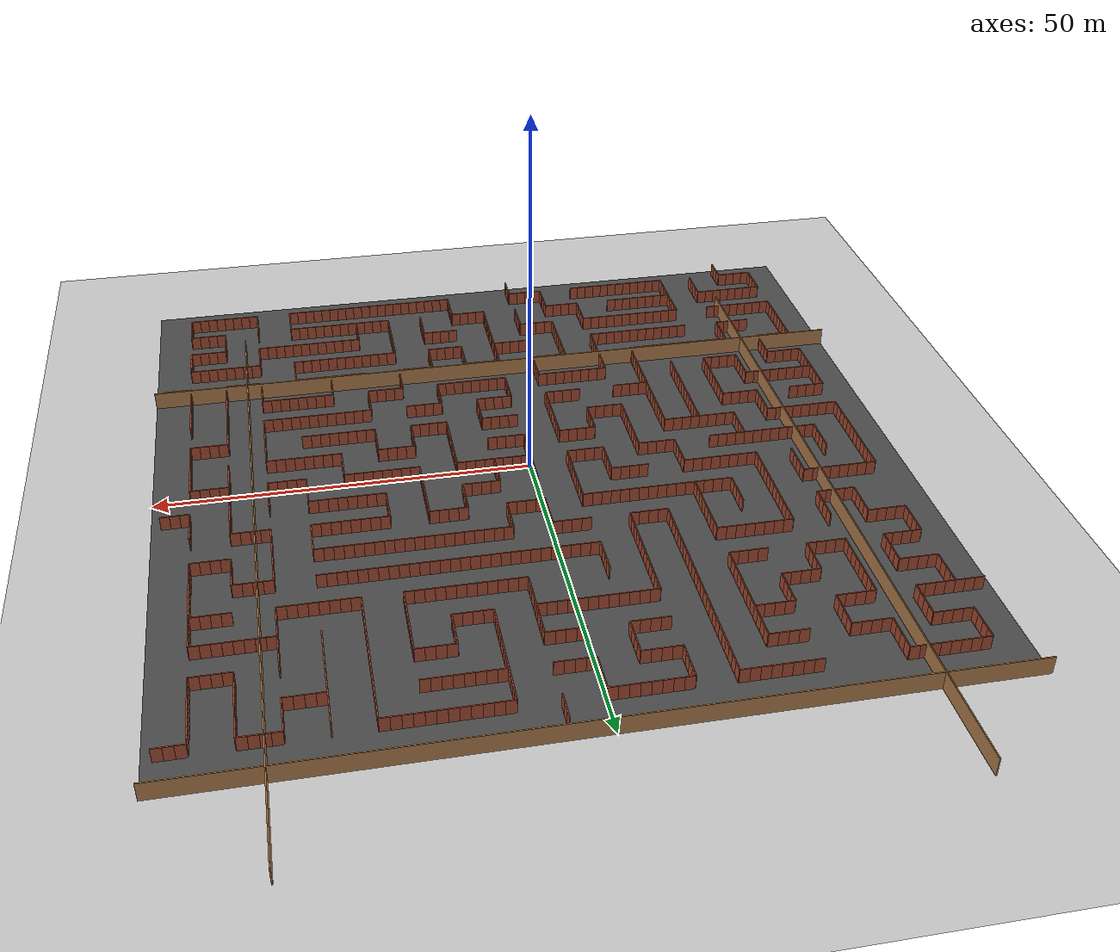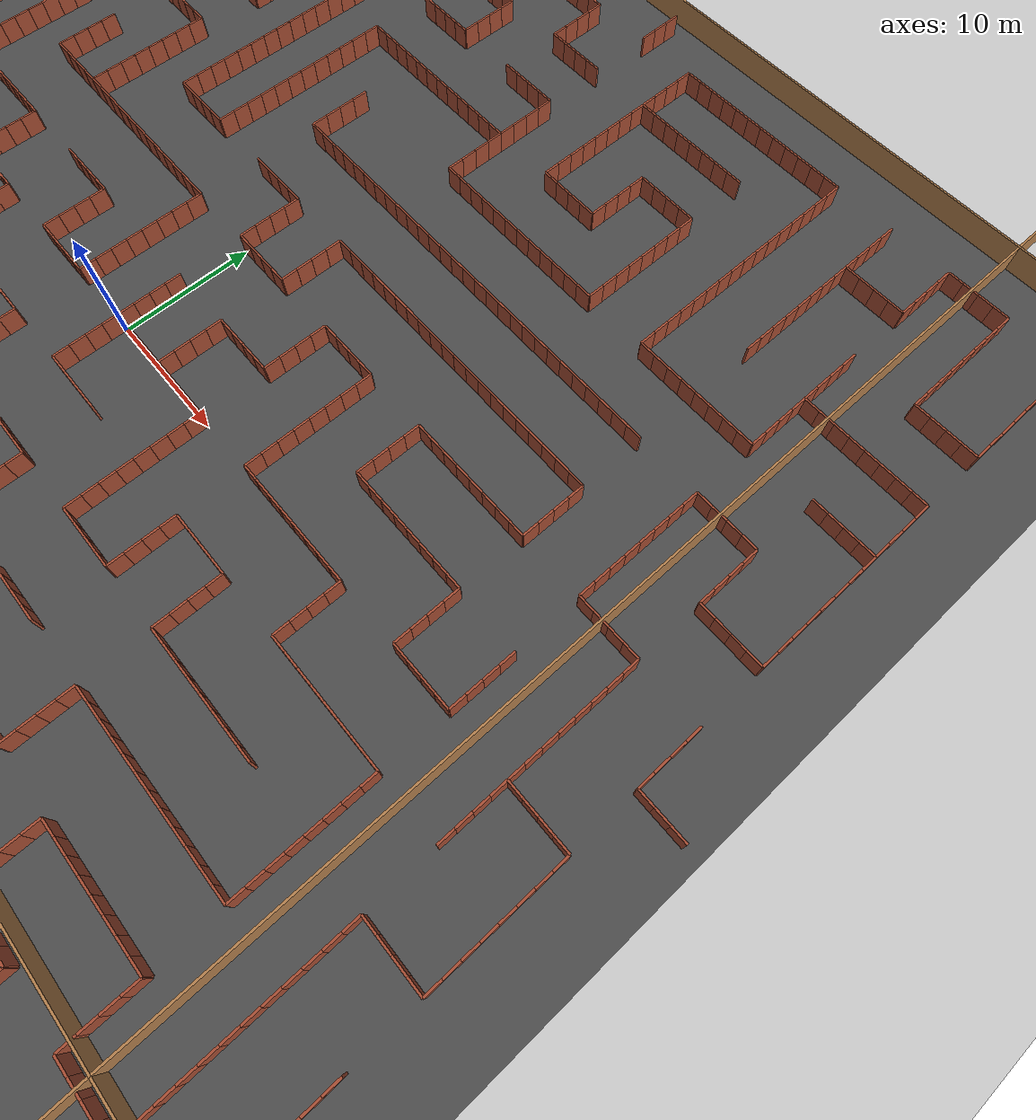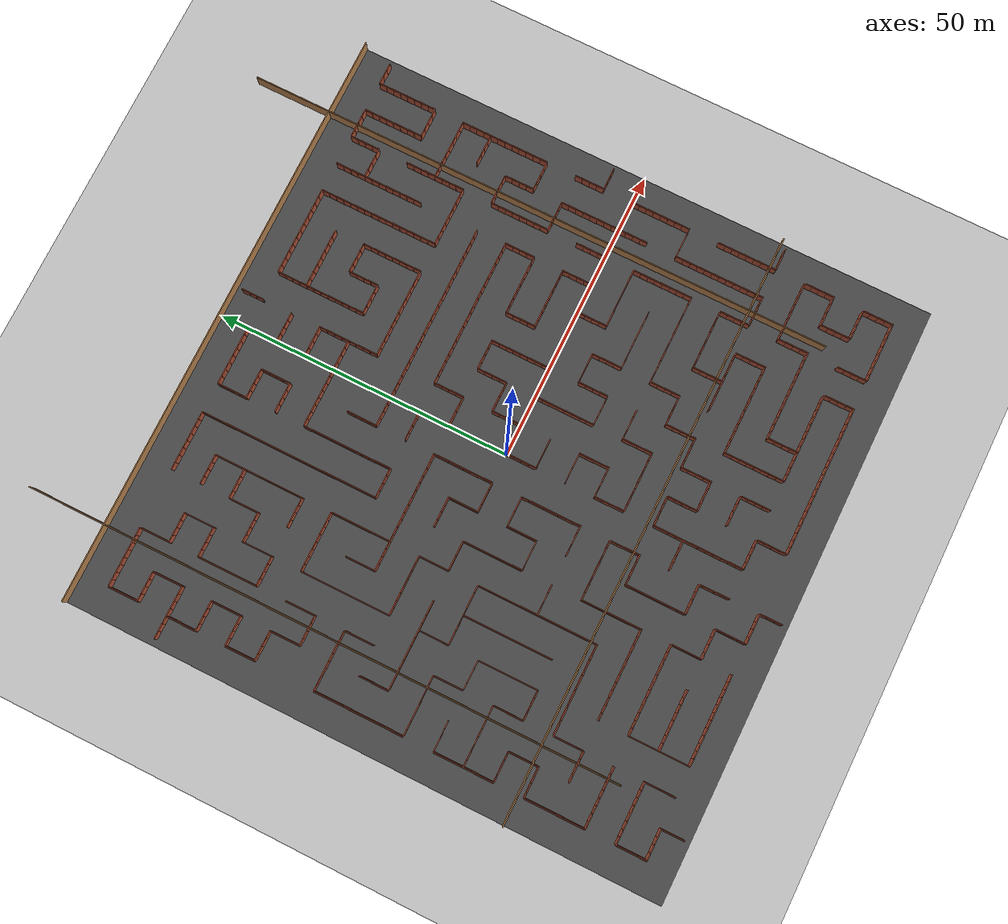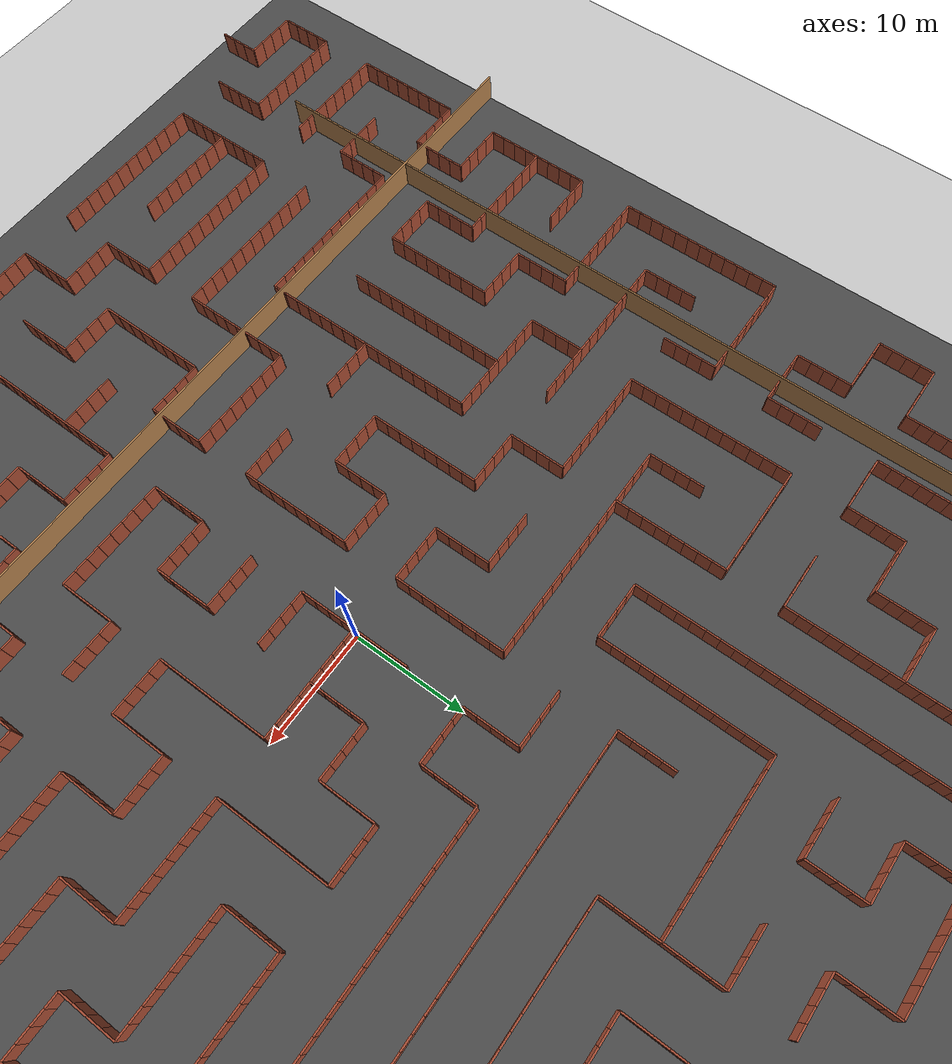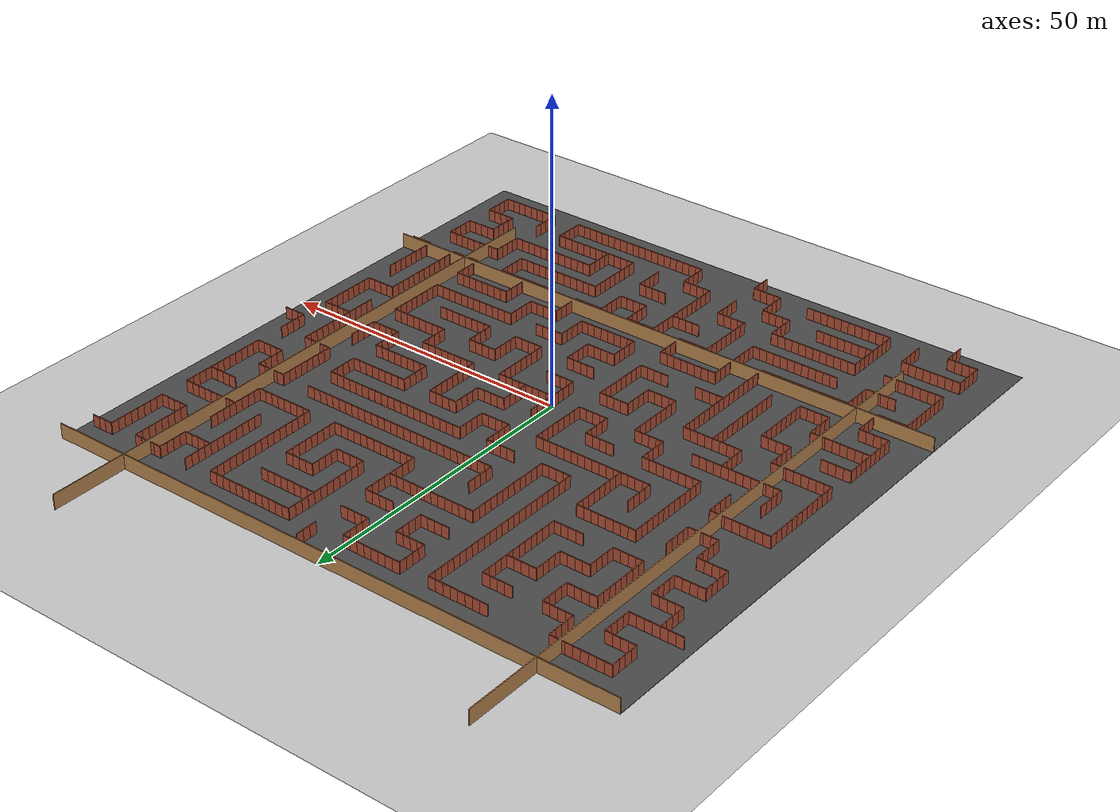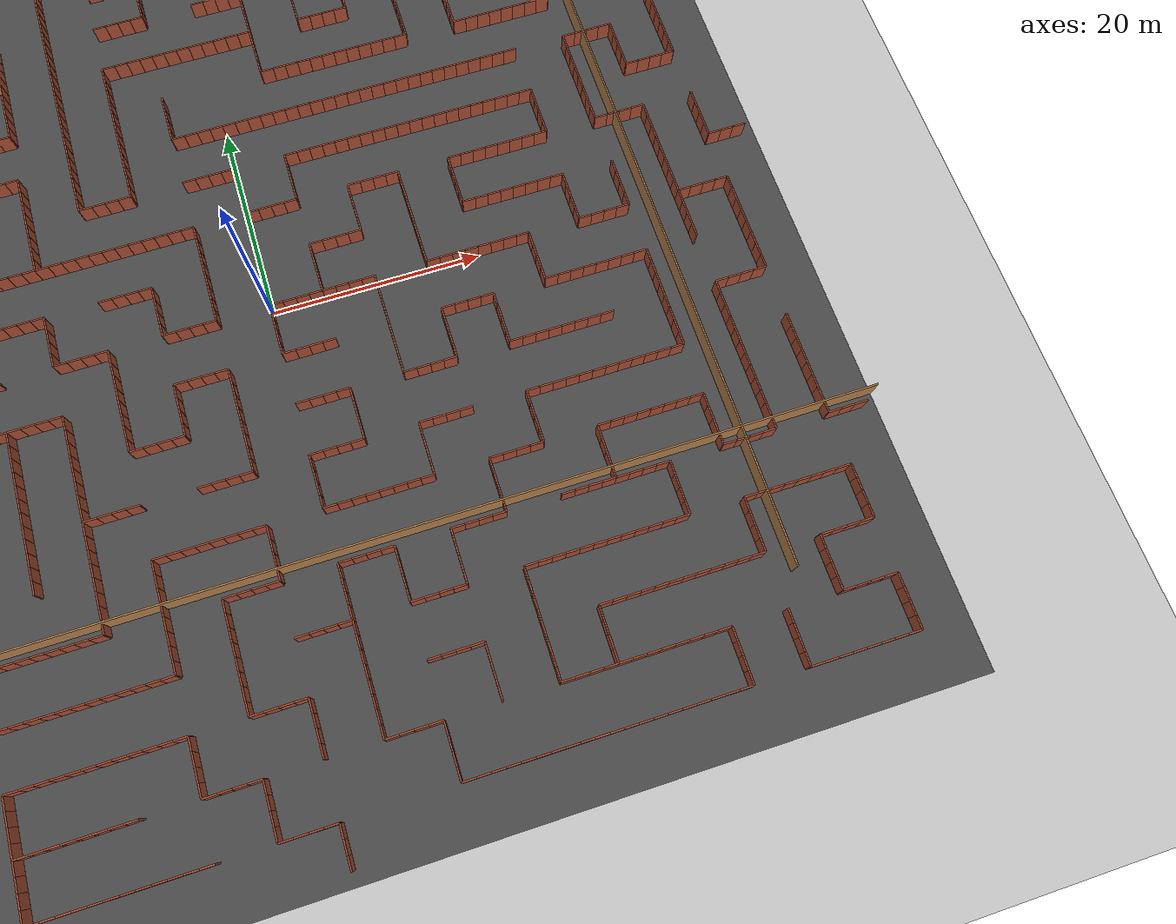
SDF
<sdf version="1.6">
 <world name="default">
  <plugin name="gazebo_connection_plugin" filename="libgazebo_connection_plugin.so"/>
  <light name="sun" type="directional">
   <pose>0 0 10 0 -0 0</pose>
   <diffuse>0.8 0.8 0.8 1</diffuse>
   <specular>0.2 0.2 0.2 1</specular>
   <attenuation>
    <range>1000</range>
    <constant>0.9</constant>
    <linear>0.01</linear>
    <quadratic>0.001</quadratic>
   </attenuation>
   <direction>-0.5 0.1 -0.9</direction>
  </light>
  <model name="ground_plane">
   <static>1</static>
   <link name="link">
    <collision name="collision">
     <geometry><plane><normal>0 0 1</normal><size>100 100</size></plane></geometry>
     <surface><friction><ode><mu>100</mu><mu2>50</mu2></ode></friction></surface>
    </collision>
    <visual name="visual">
     <cast_shadows>0</cast_shadows>
     <geometry><plane><normal>0 0 1</normal><size>100 100</size></plane></geometry>
     <material>
      <script><uri>file://media/materials/scripts/gazebo.material</uri><name>Gazebo/Grey</name></script>
     </material>
    </visual>
   </link>
  </model>
  <gravity>0 0 -9.8</gravity>
  <magnetic_field>6e-06 2.3e-05 -4.2e-05</magnetic_field>
  <atmosphere type="adiabatic"/>
  <physics name="default_physics" default="0" type="ode">
   <max_step_size>0.001</max_step_size>
   <real_time_factor>1</real_time_factor>
   <real_time_update_rate>1000</real_time_update_rate>
  </physics>
  <scene><ambient>0.4 0.4 0.4 1</ambient><background>0.7 0.7 0.7 1</background><shadows>1</shadows></scene>
  <audio><device>default</device></audio>
  <spherical_coordinates>
   <surface_model>EARTH_WGS84</surface_model>
   <latitude_deg>0</latitude_deg>
   <longitude_deg>0</longitude_deg>
   <elevation>0</elevation>
   <heading_deg>0</heading_deg>
  </spherical_coordinates>
  <model name="map_frame">
   <pose>0 13 0 0 -0 0</pose>
   <link name="Wall_0">
    <collision name="Wall_0_Collision">
     <geometry><box><size>100.05 0.15 2.5</size></box></geometry>
     <pose>0 0 1.25 0 -0 0</pose>
    </collision>
    <visual name="Wall_0_Visual">
     <pose>0 0 1.25 0 -0 0</pose>
     <geometry><box><size>100.05 0.15 2.5</size></box></geometry>
     <material>
      <script><uri>file://media/materials/scripts/gazebo.material</uri><name>Gazebo/Wood</name></script>
      <ambient>1 1 1 1</ambient>
     </material>
    </visual>
    <pose>0 37 0 0 -0 0</pose>
   </link>
   <link name="Wall_1">
    <collision name="Wall_1_Collision">
     <geometry><box><size>100.05 0.15 2.5</size></box></geometry>
     <pose>0 0 1.25 0 -0 0</pose>
    </collision>
    <visual name="Wall_1_Visual">
     <pose>0 0 1.25 0 -0 0</pose>
     <geometry><box><size>100.05 0.15 2.5</size></box></geometry>
     <material>
      <script><uri>file://media/materials/scripts/gazebo.material</uri><name>Gazebo/Wood</name></script>
      <ambient>1 1 1 1</ambient>
     </material>
    </visual>
    <pose>37 0 0 0 0 -1.5708</pose>
   </link>
   <link name="Wall_2">
    <collision name="Wall_2_Collision">
     <geometry><box><size>100.05 0.15 2.5</size></box></geometry>
     <pose>0 0 1.25 0 -0 0</pose>
    </collision>
    <visual name="Wall_2_Visual">
     <pose>0 0 1.25 0 -0 0</pose>
     <geometry><box><size>100.05 0.15 2.5</size></box></geometry>
     <material>
      <script><uri>file://media/materials/scripts/gazebo.material</uri><name>Gazebo/Wood</name></script>
      <ambient>1 1 1 1</ambient>
     </material>
    </visual>
    <pose>0 -37 0 0 -0 3.14159</pose>
   </link>
   <link name="Wall_3">
    <collision name="Wall_3_Collision">
     <geometry><box><size>100.05 0.15 2.5</size></box></geometry>
     <pose>0 0 1.25 0 -0 0</pose>
    </collision>
    <visual name="Wall_3_Visual">
     <pose>0 0 1.25 0 -0 0</pose>
     <geometry><box><size>100.05 0.15 2.5</size></box></geometry>
     <material>
      <script><uri>file://media/materials/scripts/gazebo.material</uri><name>Gazebo/Wood</name></script>
      <ambient>1 1 1 1</ambient>
     </material>
    </visual>
    <pose>-37 0 0 0 -0 1.5708</pose>
   </link>
   <static>1</static>
  </model>
  <model name="asphalt_plane">
   <static>1</static>
   <link name="link">
    <collision name="collision"><geometry><box><size>100 100 0.1</size></box></geometry></collision>
    <visual name="visual">
     <cast_shadows>0</cast_shadows>
     <geometry><box><size>100 100 0.1</size></box></geometry>
     <material>
      <script>
       <uri>model://asphalt_plane/materials/scripts</uri>
       <uri>model://asphalt_plane/materials/textures</uri>
       <name>vrc/asphalt</name>
      </script>
     </material>
    </visual>
   </link>
  </model>
  <model name="brick_wall_1_34_vertical1">
   <pose>-46.875 35 0 0 -0 0</pose>
   <link name="Wall_0">
    <collision name="Wall_0_Collision">
     <geometry><box><size>1.25 0.15 2</size></box></geometry>
     <pose>0 0 1 0 -0 0</pose>
    </collision>
    <visual name="Wall_0_Visual">
     <pose>0 0 1 0 -0 0</pose>
     <geometry><box><size>1.25 0.15 2</size></box></geometry>
     <material>
      <script><uri>file://media/materials/scripts/gazebo.material</uri><name>Gazebo/Bricks</name></script>
      <ambient>1 1 1 1</ambient>
     </material>
     <meta><layer>0</layer></meta>
    </visual>
   </link>
   <static>1</static>
  </model>
  <model name="brick_wall_1_34_vertical2">
   <pose>-48.125 35 0 0 -0 0</pose>
   <link name="Wall_0">
    <collision name="Wall_0_Collision">
     <geometry><box><size>1.25 0.15 2</size></box></geometry>
     <pose>0 0 1 0 -0 0</pose>
    </collision>
    <visual name="Wall_0_Visual">
     <pose>0 0 1 0 -0 0</pose>
     <geometry><box><size>1.25 0.15 2</size></box></geometry>
     <material>
      <script><uri>file://media/materials/scripts/gazebo.material</uri><name>Gazebo/Bricks</name></script>
      <ambient>1 1 1 1</ambient>
     </material>
     <meta><layer>0</layer></meta>
    </visual>
   </link>
   <static>1</static>
  </model>
  <model name="brick_wall_2_2_vertical1">
   <pose>-44.375 -45 0 0 -0 0</pose>
   <link name="Wall_0">
    <collision name="Wall_0_Collision">
     <geometry><box><size>1.25 0.15 2</size></box></geometry>
     <pose>0 0 1 0 -0 0</pose>
    </collision>
    <visual name="Wall_0_Visual">
     <pose>0 0 1 0 -0 0</pose>
     <geometry><box><size>1.25 0.15 2</size></box></geometry>
     <material>
      <script><uri>file://media/materials/scripts/gazebo.material</uri><name>Gazebo/Bricks</name></script>
      <ambient>1 1 1 1</ambient>
     </material>
     <meta><layer>0</layer></meta>
    </visual>
   </link>
   <static>1</static>
  </model>
  <model name="brick_wall_2_2_horizontal1">
   <pose>-45 -44.375 0 0 -0 1.5708</pose>
   <link name="Wall_0">
    <collision name="Wall_0_Collision">
     <geometry><box><size>1.25 0.15 2</size></box></geometry>
     <pose>0 0 1 0 -0 0</pose>
    </collision>
    <visual name="Wall_0_Visual">
     <pose>0 0 1 0 -0 0</pose>
     <geometry><box><size>1.25 0.15 2</size></box></geometry>
     <material>
      <script><uri>file://media/materials/scripts/gazebo.material</uri><name>Gazebo/Bricks</name></script>
      <ambient>1 1 1 1</ambient>
     </material>
     <meta><layer>0</layer></meta>
    </visual>
   </link>
   <static>1</static>
  </model>
  <model name="brick_wall_2_3_horizontal1">
   <pose>-45 -41.875 0 0 -0 1.5708</pose>
   <link name="Wall_0">
    <collision name="Wall_0_Collision">
     <geometry><box><size>1.25 0.15 2</size></box></geometry>
     <pose>0 0 1 0 -0 0</pose>
    </collision>
    <visual name="Wall_0_Visual">
     <pose>0 0 1 0 -0 0</pose>
     <geometry><box><size>1.25 0.15 2</size></box></geometry>
     <material>
      <script><uri>file://media/materials/scripts/gazebo.material</uri><name>Gazebo/Bricks</name></script>
      <ambient>1 1 1 1</ambient>
     </material>
     <meta><layer>0</layer></meta>
    </visual>
   </link>
   <static>1</static>
  </model>
  <model name="brick_wall_2_3_horizontal2">
   <pose>-45 -43.125 0 0 -0 1.5708</pose>
   <link name="Wall_0">
    <collision name="Wall_0_Collision">
     <geometry><box><size>1.25 0.15 2</size></box></geometry>
     <pose>0 0 1 0 -0 0</pose>
    </collision>
    <visual name="Wall_0_Visual">
     <pose>0 0 1 0 -0 0</pose>
     <geometry><box><size>1.25 0.15 2</size></box></geometry>
     <material>
      <script><uri>file://media/materials/scripts/gazebo.material</uri><name>Gazebo/Bricks</name></script>
      <ambient>1 1 1 1</ambient>
     </material>
     <meta><layer>0</layer></meta>
    </visual>
   </link>
   <static>1</static>
  </model>
  <model name="brick_wall_2_4_vertical1">
   <pose>-44.375 -40 0 0 -0 0</pose>
   <link name="Wall_0">
    <collision name="Wall_0_Collision">
     <geometry><box><size>1.25 0.15 2</size></box></geometry>
     <pose>0 0 1 0 -0 0</pose>
    </collision>
    <visual name="Wall_0_Visual">
     <pose>0 0 1 0 -0 0</pose>
     <geometry><box><size>1.25 0.15 2</size></box></geometry>
     <material>
      <script><uri>file://media/materials/scripts/gazebo.material</uri><name>Gazebo/Bricks</name></script>
      <ambient>1 1 1 1</ambient>
     </material>
     <meta><layer>0</layer></meta>
    </visual>
   </link>
   <static>1</static>
  </model>
  <model name="brick_wall_2_4_horizontal2">
   <pose>-45 -40.625 0 0 -0 1.5708</pose>
   <link name="Wall_0">
    <collision name="Wall_0_Collision">
     <geometry><box><size>1.25 0.15 2</size></box></geometry>
     <pose>0 0 1 0 -0 0</pose>
    </collision>
    <visual name="Wall_0_Visual">
     <pose>0 0 1 0 -0 0</pose>
     <geometry><box><size>1.25 0.15 2</size></box></geometry>
     <material>
      <script><uri>file://media/materials/scripts/gazebo.material</uri><name>Gazebo/Bricks</name></script>
      <ambient>1 1 1 1</ambient>
     </material>
     <meta><layer>0</layer></meta>
    </visual>
   </link>
   <static>1</static>
  </model>
  <model name="brick_wall_2_6_vertical1">
   <pose>-44.375 -35 0 0 -0 0</pose>
   <link name="Wall_0">
    <collision name="Wall_0_Collision">
     <geometry><box><size>1.25 0.15 2</size></box></geometry>
     <pose>0 0 1 0 -0 0</pose>
    </collision>
    <visual name="Wall_0_Visual">
     <pose>0 0 1 0 -0 0</pose>
     <geometry><box><size>1.25 0.15 2</size></box></geometry>
     <material>
      <script><uri>file://media/materials/scripts/gazebo.material</uri><name>Gazebo/Bricks</name></script>
      <ambient>1 1 1 1</ambient>
     </material>
     <meta><layer>0</layer></meta>
    </visual>
   </link>
   <static>1</static>
  </model>
  <model name="brick_wall_2_6_horizontal1">
   <pose>-45 -34.375 0 0 -0 1.5708</pose>
   <link name="Wall_0">
    <collision name="Wall_0_Collision">
     <geometry><box><size>1.25 0.15 2</size></box></geometry>
     <pose>0 0 1 0 -0 0</pose>
    </collision>
    <visual name="Wall_0_Visual">
     <pose>0 0 1 0 -0 0</pose>
     <geometry><box><size>1.25 0.15 2</size></box></geometry>
     <material>
      <script><uri>file://media/materials/scripts/gazebo.material</uri><name>Gazebo/Bricks</name></script>
      <ambient>1 1 1 1</ambient>
     </material>
     <meta><layer>0</layer></meta>
    </visual>
   </link>
   <static>1</static>
  </model>
  <model name="brick_wall_2_7_horizontal1">
   <pose>-45 -31.875 0 0 -0 1.5708</pose>
   <link name="Wall_0">
    <collision name="Wall_0_Collision">
     <geometry><box><size>1.25 0.15 2</size></box></geometry>
     <pose>0 0 1 0 -0 0</pose>
    </collision>
    <visual name="Wall_0_Visual">
     <pose>0 0 1 0 -0 0</pose>
     <geometry><box><size>1.25 0.15 2</size></box></geometry>
     <material>
      <script><uri>file://media/materials/scripts/gazebo.material</uri><name>Gazebo/Bricks</name></script>
      <ambient>1 1 1 1</ambient>
     </material>
     <meta><layer>0</layer></meta>
    </visual>
   </link>
   <static>1</static>
  </model>
  <model name="brick_wall_2_7_horizontal2">
   <pose>-45 -33.125 0 0 -0 1.5708</pose>
   <link name="Wall_0">
    <collision name="Wall_0_Collision">
     <geometry><box><size>1.25 0.15 2</size></box></geometry>
     <pose>0 0 1 0 -0 0</pose>
    </collision>
    <visual name="Wall_0_Visual">
     <pose>0 0 1 0 -0 0</pose>
     <geometry><box><size>1.25 0.15 2</size></box></geometry>
     <material>
      <script><uri>file://media/materials/scripts/gazebo.material</uri><name>Gazebo/Bricks</name></script>
      <ambient>1 1 1 1</ambient>
     </material>
     <meta><layer>0</layer></meta>
    </visual>
   </link>
   <static>1</static>
  </model>
  <model name="brick_wall_2_8_horizontal1">
   <pose>-45 -29.375 0 0 -0 1.5708</pose>
   <link name="Wall_0">
    <collision name="Wall_0_Collision">
     <geometry><box><size>1.25 0.15 2</size></box></geometry>
     <pose>0 0 1 0 -0 0</pose>
    </collision>
    <visual name="Wall_0_Visual">
     <pose>0 0 1 0 -0 0</pose>
     <geometry><box><size>1.25 0.15 2</size></box></geometry>
     <material>
      <script><uri>file://media/materials/scripts/gazebo.material</uri><name>Gazebo/Bricks</name></script>
      <ambient>1 1 1 1</ambient>
     </material>
     <meta><layer>0</layer></meta>
    </visual>
   </link>
   <static>1</static>
  </model>
  <model name="brick_wall_2_8_horizontal2">
   <pose>-45 -30.625 0 0 -0 1.5708</pose>
   <link name="Wall_0">
    <collision name="Wall_0_Collision">
     <geometry><box><size>1.25 0.15 2</size></box></geometry>
     <pose>0 0 1 0 -0 0</pose>
    </collision>
    <visual name="Wall_0_Visual">
     <pose>0 0 1 0 -0 0</pose>
     <geometry><box><size>1.25 0.15 2</size></box></geometry>
     <material>
      <script><uri>file://media/materials/scripts/gazebo.material</uri><name>Gazebo/Bricks</name></script>
      <ambient>1 1 1 1</ambient>
     </material>
     <meta><layer>0</layer></meta>
    </visual>
   </link>
   <static>1</static>
  </model>
  <model name="brick_wall_2_9_horizontal1">
   <pose>-45 -26.875 0 0 -0 1.5708</pose>
   <link name="Wall_0">
    <collision name="Wall_0_Collision">
     <geometry><box><size>1.25 0.15 2</size></box></geometry>
     <pose>0 0 1 0 -0 0</pose>
    </collision>
    <visual name="Wall_0_Visual">
     <pose>0 0 1 0 -0 0</pose>
     <geometry><box><size>1.25 0.15 2</size></box></geometry>
     <material>
      <script><uri>file://media/materials/scripts/gazebo.material</uri><name>Gazebo/Bricks</name></script>
      <ambient>1 1 1 1</ambient>
     </material>
     <meta><layer>0</layer></meta>
    </visual>
   </link>
   <static>1</static>
  </model>
  <model name="brick_wall_2_9_horizontal2">
   <pose>-45 -28.125 0 0 -0 1.5708</pose>
   <link name="Wall_0">
    <collision name="Wall_0_Collision">
     <geometry><box><size>1.25 0.15 2</size></box></geometry>
     <pose>0 0 1 0 -0 0</pose>
    </collision>
    <visual name="Wall_0_Visual">
     <pose>0 0 1 0 -0 0</pose>
     <geometry><box><size>1.25 0.15 2</size></box></geometry>
     <material>
      <script><uri>file://media/materials/scripts/gazebo.material</uri><name>Gazebo/Bricks</name></script>
      <ambient>1 1 1 1</ambient>
     </material>
     <meta><layer>0</layer></meta>
    </visual>
   </link>
   <static>1</static>
  </model>
  <model name="brick_wall_2_10_vertical1">
   <pose>-44.375 -25 0 0 -0 0</pose>
   <link name="Wall_0">
    <collision name="Wall_0_Collision">
     <geometry><box><size>1.25 0.15 2</size></box></geometry>
     <pose>0 0 1 0 -0 0</pose>
    </collision>
    <visual name="Wall_0_Visual">
     <pose>0 0 1 0 -0 0</pose>
     <geometry><box><size>1.25 0.15 2</size></box></geometry>
     <material>
      <script><uri>file://media/materials/scripts/gazebo.material</uri><name>Gazebo/Bricks</name></script>
      <ambient>1 1 1 1</ambient>
     </material>
     <meta><layer>0</layer></meta>
    </visual>
   </link>
   <static>1</static>
  </model>
  <model name="brick_wall_2_10_horizontal2">
   <pose>-45 -25.625 0 0 -0 1.5708</pose>
   <link name="Wall_0">
    <collision name="Wall_0_Collision">
     <geometry><box><size>1.25 0.15 2</size></box></geometry>
     <pose>0 0 1 0 -0 0</pose>
    </collision>
    <visual name="Wall_0_Visual">
     <pose>0 0 1 0 -0 0</pose>
     <geometry><box><size>1.25 0.15 2</size></box></geometry>
     <material>
      <script><uri>file://media/materials/scripts/gazebo.material</uri><name>Gazebo/Bricks</name></script>
      <ambient>1 1 1 1</ambient>
     </material>
     <meta><layer>0</layer></meta>
    </visual>
   </link>
   <static>1</static>
  </model>
  <model name="brick_wall_2_12_vertical1">
   <pose>-44.375 -20 0 0 -0 0</pose>
   <link name="Wall_0">
    <collision name="Wall_0_Collision">
     <geometry><box><size>1.25 0.15 2</size></box></geometry>
     <pose>0 0 1 0 -0 0</pose>
    </collision>
    <visual name="Wall_0_Visual">
     <pose>0 0 1 0 -0 0</pose>
     <geometry><box><size>1.25 0.15 2</size></box></geometry>
     <material>
      <script><uri>file://media/materials/scripts/gazebo.material</uri><name>Gazebo/Bricks</name></script>
      <ambient>1 1 1 1</ambient>
     </material>
     <meta><layer>0</layer></meta>
    </visual>
   </link>
   <static>1</static>
  </model>
  <model name="brick_wall_2_12_horizontal1">
   <pose>-45 -19.375 0 0 -0 1.5708</pose>
   <link name="Wall_0">
    <collision name="Wall_0_Collision">
     <geometry><box><size>1.25 0.15 2</size></box></geometry>
     <pose>0 0 1 0 -0 0</pose>
    </collision>
    <visual name="Wall_0_Visual">
     <pose>0 0 1 0 -0 0</pose>
     <geometry><box><size>1.25 0.15 2</size></box></geometry>
     <material>
      <script><uri>file://media/materials/scripts/gazebo.material</uri><name>Gazebo/Bricks</name></script>
      <ambient>1 1 1 1</ambient>
     </material>
     <meta><layer>0</layer></meta>
    </visual>
   </link>
   <static>1</static>
  </model>
  <model name="brick_wall_2_13_horizontal1">
   <pose>-45 -16.875 0 0 -0 1.5708</pose>
   <link name="Wall_0">
    <collision name="Wall_0_Collision">
     <geometry><box><size>1.25 0.15 2</size></box></geometry>
     <pose>0 0 1 0 -0 0</pose>
    </collision>
    <visual name="Wall_0_Visual">
     <pose>0 0 1 0 -0 0</pose>
     <geometry><box><size>1.25 0.15 2</size></box></geometry>
     <material>
      <script><uri>file://media/materials/scripts/gazebo.material</uri><name>Gazebo/Bricks</name></script>
      <ambient>1 1 1 1</ambient>
     </material>
     <meta><layer>0</layer></meta>
    </visual>
   </link>
   <static>1</static>
  </model>
  <model name="brick_wall_2_13_horizontal2">
   <pose>-45 -18.125 0 0 -0 1.5708</pose>
   <link name="Wall_0">
    <collision name="Wall_0_Collision">
     <geometry><box><size>1.25 0.15 2</size></box></geometry>
     <pose>0 0 1 0 -0 0</pose>
    </collision>
    <visual name="Wall_0_Visual">
     <pose>0 0 1 0 -0 0</pose>
     <geometry><box><size>1.25 0.15 2</size></box></geometry>
     <material>
      <script><uri>file://media/materials/scripts/gazebo.material</uri><name>Gazebo/Bricks</name></script>
      <ambient>1 1 1 1</ambient>
     </material>
     <meta><layer>0</layer></meta>
    </visual>
   </link>
   <static>1</static>
  </model>
  <model name="brick_wall_2_14_vertical1">
   <pose>-44.375 -15 0 0 -0 0</pose>
   <link name="Wall_0">
    <collision name="Wall_0_Collision">
     <geometry><box><size>1.25 0.15 2</size></box></geometry>
     <pose>0 0 1 0 -0 0</pose>
    </collision>
    <visual name="Wall_0_Visual">
     <pose>0 0 1 0 -0 0</pose>
     <geometry><box><size>1.25 0.15 2</size></box></geometry>
     <material>
      <script><uri>file://media/materials/scripts/gazebo.material</uri><name>Gazebo/Bricks</name></script>
      <ambient>1 1 1 1</ambient>
     </material>
     <meta><layer>0</layer></meta>
    </visual>
   </link>
   <static>1</static>
  </model>
  <model name="brick_wall_2_14_horizontal1">
   <pose>-45 -14.375 0 0 -0 1.5708</pose>
   <link name="Wall_0">
    <collision name="Wall_0_Collision">
     <geometry><box><size>1.25 0.15 2</size></box></geometry>
     <pose>0 0 1 0 -0 0</pose>
    </collision>
    <visual name="Wall_0_Visual">
     <pose>0 0 1 0 -0 0</pose>
     <geometry><box><size>1.25 0.15 2</size></box></geometry>
     <material>
      <script><uri>file://media/materials/scripts/gazebo.material</uri><name>Gazebo/Bricks</name></script>
      <ambient>1 1 1 1</ambient>
     </material>
     <meta><layer>0</layer></meta>
    </visual>
   </link>
   <static>1</static>
  </model>
  <model name="brick_wall_2_14_horizontal2">
   <pose>-45 -15.625 0 0 -0 1.5708</pose>
   <link name="Wall_0">
    <collision name="Wall_0_Collision">
     <geometry><box><size>1.25 0.15 2</size></box></geometry>
     <pose>0 0 1 0 -0 0</pose>
    </collision>
    <visual name="Wall_0_Visual">
     <pose>0 0 1 0 -0 0</pose>
     <geometry><box><size>1.25 0.15 2</size></box></geometry>
     <material>
      <script><uri>file://media/materials/scripts/gazebo.material</uri><name>Gazebo/Bricks</name></script>
      <ambient>1 1 1 1</ambient>
     </material>
     <meta><layer>0</layer></meta>
    </visual>
   </link>
   <static>1</static>
  </model>
  <model name="brick_wall_2_15_horizontal1">
   <pose>-45 -11.875 0 0 -0 1.5708</pose>
   <link name="Wall_0">
    <collision name="Wall_0_Collision">
     <geometry><box><size>1.25 0.15 2</size></box></geometry>
     <pose>0 0 1 0 -0 0</pose>
    </collision>
    <visual name="Wall_0_Visual">
     <pose>0 0 1 0 -0 0</pose>
     <geometry><box><size>1.25 0.15 2</size></box></geometry>
     <material>
      <script><uri>file://media/materials/scripts/gazebo.material</uri><name>Gazebo/Bricks</name></script>
      <ambient>1 1 1 1</ambient>
     </material>
     <meta><layer>0</layer></meta>
    </visual>
   </link>
   <static>1</static>
  </model>
  <model name="brick_wall_2_15_horizontal2">
   <pose>-45 -13.125 0 0 -0 1.5708</pose>
   <link name="Wall_0">
    <collision name="Wall_0_Collision">
     <geometry><box><size>1.25 0.15 2</size></box></geometry>
     <pose>0 0 1 0 -0 0</pose>
    </collision>
    <visual name="Wall_0_Visual">
     <pose>0 0 1 0 -0 0</pose>
     <geometry><box><size>1.25 0.15 2</size></box></geometry>
     <material>
      <script><uri>file://media/materials/scripts/gazebo.material</uri><name>Gazebo/Bricks</name></script>
      <ambient>1 1 1 1</ambient>
     </material>
     <meta><layer>0</layer></meta>
    </visual>
   </link>
   <static>1</static>
  </model>
  <model name="brick_wall_2_16_vertical1">
   <pose>-44.375 -10 0 0 -0 0</pose>
   <link name="Wall_0">
    <collision name="Wall_0_Collision">
     <geometry><box><size>1.25 0.15 2</size></box></geometry>
     <pose>0 0 1 0 -0 0</pose>
    </collision>
    <visual name="Wall_0_Visual">
     <pose>0 0 1 0 -0 0</pose>
     <geometry><box><size>1.25 0.15 2</size></box></geometry>
     <material>
      <script><uri>file://media/materials/scripts/gazebo.material</uri><name>Gazebo/Bricks</name></script>
      <ambient>1 1 1 1</ambient>
     </material>
     <meta><layer>0</layer></meta>
    </visual>
   </link>
   <static>1</static>
  </model>
  <model name="brick_wall_2_16_horizontal2">
   <pose>-45 -10.625 0 0 -0 1.5708</pose>
   <link name="Wall_0">
    <collision name="Wall_0_Collision">
     <geometry><box><size>1.25 0.15 2</size></box></geometry>
     <pose>0 0 1 0 -0 0</pose>
    </collision>
    <visual name="Wall_0_Visual">
     <pose>0 0 1 0 -0 0</pose>
     <geometry><box><size>1.25 0.15 2</size></box></geometry>
     <material>
      <script><uri>file://media/materials/scripts/gazebo.material</uri><name>Gazebo/Bricks</name></script>
      <ambient>1 1 1 1</ambient>
     </material>
     <meta><layer>0</layer></meta>
    </visual>
   </link>
   <static>1</static>
  </model>
  <model name="brick_wall_2_18_vertical1">
   <pose>-44.375 -5 0 0 -0 0</pose>
   <link name="Wall_0">
    <collision name="Wall_0_Collision">
     <geometry><box><size>1.25 0.15 2</size></box></geometry>
     <pose>0 0 1 0 -0 0</pose>
    </collision>
    <visual name="Wall_0_Visual">
     <pose>0 0 1 0 -0 0</pose>
     <geometry><box><size>1.25 0.15 2</size></box></geometry>
     <material>
      <script><uri>file://media/materials/scripts/gazebo.material</uri><name>Gazebo/Bricks</name></script>
      <ambient>1 1 1 1</ambient>
     </material>
     <meta><layer>0</layer></meta>
    </visual>
   </link>
   <static>1</static>
  </model>
  <model name="brick_wall_2_18_horizontal1">
   <pose>-45 -4.375 0 0 -0 1.5708</pose>
   <link name="Wall_0">
    <collision name="Wall_0_Collision">
     <geometry><box><size>1.25 0.15 2</size></box></geometry>
     <pose>0 0 1 0 -0 0</pose>
    </collision>
    <visual name="Wall_0_Visual">
     <pose>0 0 1 0 -0 0</pose>
     <geometry><box><size>1.25 0.15 2</size></box></geometry>
     <material>
      <script><uri>file://media/materials/scripts/gazebo.material</uri><name>Gazebo/Bricks</name></script>
      <ambient>1 1 1 1</ambient>
     </material>
     <meta><layer>0</layer></meta>
    </visual>
   </link>
   <static>1</static>
  </model>
  <model name="brick_wall_2_19_horizontal1">
   <pose>-45 -1.875 0 0 -0 1.5708</pose>
   <link name="Wall_0">
    <collision name="Wall_0_Collision">
     <geometry><box><size>1.25 0.15 2</size></box></geometry>
     <pose>0 0 1 0 -0 0</pose>
    </collision>
    <visual name="Wall_0_Visual">
     <pose>0 0 1 0 -0 0</pose>
     <geometry><box><size>1.25 0.15 2</size></box></geometry>
     <material>
      <script><uri>file://media/materials/scripts/gazebo.material</uri><name>Gazebo/Bricks</name></script>
      <ambient>1 1 1 1</ambient>
     </material>
     <meta><layer>0</layer></meta>
    </visual>
   </link>
   <static>1</static>
  </model>
  <model name="brick_wall_2_19_horizontal2">
   <pose>-45 -3.125 0 0 -0 1.5708</pose>
   <link name="Wall_0">
    <collision name="Wall_0_Collision">
     <geometry><box><size>1.25 0.15 2</size></box></geometry>
     <pose>0 0 1 0 -0 0</pose>
    </collision>
    <visual name="Wall_0_Visual">
     <pose>0 0 1 0 -0 0</pose>
     <geometry><box><size>1.25 0.15 2</size></box></geometry>
     <material>
      <script><uri>file://media/materials/scripts/gazebo.material</uri><name>Gazebo/Bricks</name></script>
      <ambient>1 1 1 1</ambient>
     </material>
     <meta><layer>0</layer></meta>
    </visual>
   </link>
   <static>1</static>
  </model>
  <model name="brick_wall_2_20_horizontal1">
   <pose>-45 0.625 0 0 -0 1.5708</pose>
   <link name="Wall_0">
    <collision name="Wall_0_Collision">
     <geometry><box><size>1.25 0.15 2</size></box></geometry>
     <pose>0 0 1 0 -0 0</pose>
    </collision>
    <visual name="Wall_0_Visual">
     <pose>0 0 1 0 -0 0</pose>
     <geometry><box><size>1.25 0.15 2</size></box></geometry>
     <material>
      <script><uri>file://media/materials/scripts/gazebo.material</uri><name>Gazebo/Bricks</name></script>
      <ambient>1 1 1 1</ambient>
     </material>
     <meta><layer>0</layer></meta>
    </visual>
   </link>
   <static>1</static>
  </model>
  <model name="brick_wall_2_20_horizontal2">
   <pose>-45 -0.625 0 0 -0 1.5708</pose>
   <link name="Wall_0">
    <collision name="Wall_0_Collision">
     <geometry><box><size>1.25 0.15 2</size></box></geometry>
     <pose>0 0 1 0 -0 0</pose>
    </collision>
    <visual name="Wall_0_Visual">
     <pose>0 0 1 0 -0 0</pose>
     <geometry><box><size>1.25 0.15 2</size></box></geometry>
     <material>
      <script><uri>file://media/materials/scripts/gazebo.material</uri><name>Gazebo/Bricks</name></script>
      <ambient>1 1 1 1</ambient>
     </material>
     <meta><layer>0</layer></meta>
    </visual>
   </link>
   <static>1</static>
  </model>
  <model name="brick_wall_2_21_horizontal1">
   <pose>-45 3.125 0 0 -0 1.5708</pose>
   <link name="Wall_0">
    <collision name="Wall_0_Collision">
     <geometry><box><size>1.25 0.15 2</size></box></geometry>
     <pose>0 0 1 0 -0 0</pose>
    </collision>
    <visual name="Wall_0_Visual">
     <pose>0 0 1 0 -0 0</pose>
     <geometry><box><size>1.25 0.15 2</size></box></geometry>
     <material>
      <script><uri>file://media/materials/scripts/gazebo.material</uri><name>Gazebo/Bricks</name></script>
      <ambient>1 1 1 1</ambient>
     </material>
     <meta><layer>0</layer></meta>
    </visual>
   </link>
   <static>1</static>
  </model>
  <model name="brick_wall_2_21_horizontal2">
   <pose>-45 1.875 0 0 -0 1.5708</pose>
   <link name="Wall_0">
    <collision name="Wall_0_Collision">
     <geometry><box><size>1.25 0.15 2</size></box></geometry>
     <pose>0 0 1 0 -0 0</pose>
    </collision>
    <visual name="Wall_0_Visual">
     <pose>0 0 1 0 -0 0</pose>
     <geometry><box><size>1.25 0.15 2</size></box></geometry>
     <material>
      <script><uri>file://media/materials/scripts/gazebo.material</uri><name>Gazebo/Bricks</name></script>
      <ambient>1 1 1 1</ambient>
     </material>
     <meta><layer>0</layer></meta>
    </visual>
   </link>
   <static>1</static>
  </model>
  <model name="brick_wall_2_22_horizontal1">
   <pose>-45 5.625 0 0 -0 1.5708</pose>
   <link name="Wall_0">
    <collision name="Wall_0_Collision">
     <geometry><box><size>1.25 0.15 2</size></box></geometry>
     <pose>0 0 1 0 -0 0</pose>
    </collision>
    <visual name="Wall_0_Visual">
     <pose>0 0 1 0 -0 0</pose>
     <geometry><box><size>1.25 0.15 2</size></box></geometry>
     <material>
      <script><uri>file://media/materials/scripts/gazebo.material</uri><name>Gazebo/Bricks</name></script>
      <ambient>1 1 1 1</ambient>
     </material>
     <meta><layer>0</layer></meta>
    </visual>
   </link>
   <static>1</static>
  </model>
  <model name="brick_wall_2_22_horizontal2">
   <pose>-45 4.375 0 0 -0 1.5708</pose>
   <link name="Wall_0">
    <collision name="Wall_0_Collision">
     <geometry><box><size>1.25 0.15 2</size></box></geometry>
     <pose>0 0 1 0 -0 0</pose>
    </collision>
    <visual name="Wall_0_Visual">
     <pose>0 0 1 0 -0 0</pose>
     <geometry><box><size>1.25 0.15 2</size></box></geometry>
     <material>
      <script><uri>file://media/materials/scripts/gazebo.material</uri><name>Gazebo/Bricks</name></script>
      <ambient>1 1 1 1</ambient>
     </material>
     <meta><layer>0</layer></meta>
    </visual>
   </link>
   <static>1</static>
  </model>
  <model name="brick_wall_2_23_horizontal1">
   <pose>-45 8.125 0 0 -0 1.5708</pose>
   <link name="Wall_0">
    <collision name="Wall_0_Collision">
     <geometry><box><size>1.25 0.15 2</size></box></geometry>
     <pose>0 0 1 0 -0 0</pose>
    </collision>
    <visual name="Wall_0_Visual">
     <pose>0 0 1 0 -0 0</pose>
     <geometry><box><size>1.25 0.15 2</size></box></geometry>
     <material>
      <script><uri>file://media/materials/scripts/gazebo.material</uri><name>Gazebo/Bricks</name></script>
      <ambient>1 1 1 1</ambient>
     </material>
     <meta><layer>0</layer></meta>
    </visual>
   </link>
   <static>1</static>
  </model>
  <model name="brick_wall_2_23_horizontal2">
   <pose>-45 6.875 0 0 -0 1.5708</pose>
   <link name="Wall_0">
    <collision name="Wall_0_Collision">
     <geometry><box><size>1.25 0.15 2</size></box></geometry>
     <pose>0 0 1 0 -0 0</pose>
    </collision>
    <visual name="Wall_0_Visual">
     <pose>0 0 1 0 -0 0</pose>
     <geometry><box><size>1.25 0.15 2</size></box></geometry>
     <material>
      <script><uri>file://media/materials/scripts/gazebo.material</uri><name>Gazebo/Bricks</name></script>
      <ambient>1 1 1 1</ambient>
     </material>
     <meta><layer>0</layer></meta>
    </visual>
   </link>
   <static>1</static>
  </model>
  <model name="brick_wall_2_24_vertical1">
   <pose>-44.375 10 0 0 -0 0</pose>
   <link name="Wall_0">
    <collision name="Wall_0_Collision">
     <geometry><box><size>1.25 0.15 2</size></box></geometry>
     <pose>0 0 1 0 -0 0</pose>
    </collision>
    <visual name="Wall_0_Visual">
     <pose>0 0 1 0 -0 0</pose>
     <geometry><box><size>1.25 0.15 2</size></box></geometry>
     <material>
      <script><uri>file://media/materials/scripts/gazebo.material</uri><name>Gazebo/Bricks</name></script>
      <ambient>1 1 1 1</ambient>
     </material>
     <meta><layer>0</layer></meta>
    </visual>
   </link>
   <static>1</static>
  </model>
  <model name="brick_wall_2_24_horizontal2">
   <pose>-45 9.375 0 0 -0 1.5708</pose>
   <link name="Wall_0">
    <collision name="Wall_0_Collision">
     <geometry><box><size>1.25 0.15 2</size></box></geometry>
     <pose>0 0 1 0 -0 0</pose>
    </collision>
    <visual name="Wall_0_Visual">
     <pose>0 0 1 0 -0 0</pose>
     <geometry><box><size>1.25 0.15 2</size></box></geometry>
     <material>
      <script><uri>file://media/materials/scripts/gazebo.material</uri><name>Gazebo/Bricks</name></script>
      <ambient>1 1 1 1</ambient>
     </material>
     <meta><layer>0</layer></meta>
    </visual>
   </link>
   <static>1</static>
  </model>
  <model name="brick_wall_2_28_vertical1">
   <pose>-44.375 20 0 0 -0 0</pose>
   <link name="Wall_0">
    <collision name="Wall_0_Collision">
     <geometry><box><size>1.25 0.15 2</size></box></geometry>
     <pose>0 0 1 0 -0 0</pose>
    </collision>
    <visual name="Wall_0_Visual">
     <pose>0 0 1 0 -0 0</pose>
     <geometry><box><size>1.25 0.15 2</size></box></geometry>
     <material>
      <script><uri>file://media/materials/scripts/gazebo.material</uri><name>Gazebo/Bricks</name></script>
      <ambient>1 1 1 1</ambient>
     </material>
     <meta><layer>0</layer></meta>
    </visual>
   </link>
   <static>1</static>
  </model>
  <model name="brick_wall_2_28_horizontal1">
   <pose>-45 20.625 0 0 -0 1.5708</pose>
   <link name="Wall_0">
    <collision name="Wall_0_Collision">
     <geometry><box><size>1.25 0.15 2</size></box></geometry>
     <pose>0 0 1 0 -0 0</pose>
    </collision>
    <visual name="Wall_0_Visual">
     <pose>0 0 1 0 -0 0</pose>
     <geometry><box><size>1.25 0.15 2</size></box></geometry>
     <material>
      <script><uri>file://media/materials/scripts/gazebo.material</uri><name>Gazebo/Bricks</name></script>
      <ambient>1 1 1 1</ambient>
     </material>
     <meta><layer>0</layer></meta>
    </visual>
   </link>
   <static>1</static>
  </model>
  <model name="brick_wall_2_29_horizontal1">
   <pose>-45 23.125 0 0 -0 1.5708</pose>
   <link name="Wall_0">
    <collision name="Wall_0_Collision">
     <geometry><box><size>1.25 0.15 2</size></box></geometry>
     <pose>0 0 1 0 -0 0</pose>
    </collision>
    <visual name="Wall_0_Visual">
     <pose>0 0 1 0 -0 0</pose>
     <geometry><box><size>1.25 0.15 2</size></box></geometry>
     <material>
      <script><uri>file://media/materials/scripts/gazebo.material</uri><name>Gazebo/Bricks</name></script>
      <ambient>1 1 1 1</ambient>
     </material>
     <meta><layer>0</layer></meta>
    </visual>
   </link>
   <static>1</static>
  </model>
  <model name="brick_wall_2_29_horizontal2">
   <pose>-45 21.875 0 0 -0 1.5708</pose>
   <link name="Wall_0">
    <collision name="Wall_0_Collision">
     <geometry><box><size>1.25 0.15 2</size></box></geometry>
     <pose>0 0 1 0 -0 0</pose>
    </collision>
    <visual name="Wall_0_Visual">
     <pose>0 0 1 0 -0 0</pose>
     <geometry><box><size>1.25 0.15 2</size></box></geometry>
     <material>
      <script><uri>file://media/materials/scripts/gazebo.material</uri><name>Gazebo/Bricks</name></script>
      <ambient>1 1 1 1</ambient>
     </material>
     <meta><layer>0</layer></meta>
    </visual>
   </link>
   <static>1</static>
  </model>
  <model name="brick_wall_2_30_vertical1">
   <pose>-44.375 25 0 0 -0 0</pose>
   <link name="Wall_0">
    <collision name="Wall_0_Collision">
     <geometry><box><size>1.25 0.15 2</size></box></geometry>
     <pose>0 0 1 0 -0 0</pose>
    </collision>
    <visual name="Wall_0_Visual">
     <pose>0 0 1 0 -0 0</pose>
     <geometry><box><size>1.25 0.15 2</size></box></geometry>
     <material>
      <script><uri>file://media/materials/scripts/gazebo.material</uri><name>Gazebo/Bricks</name></script>
      <ambient>1 1 1 1</ambient>
     </material>
     <meta><layer>0</layer></meta>
    </visual>
   </link>
   <static>1</static>
  </model>
  <model name="brick_wall_2_30_horizontal2">
   <pose>-45 24.375 0 0 -0 1.5708</pose>
   <link name="Wall_0">
    <collision name="Wall_0_Collision">
     <geometry><box><size>1.25 0.15 2</size></box></geometry>
     <pose>0 0 1 0 -0 0</pose>
    </collision>
    <visual name="Wall_0_Visual">
     <pose>0 0 1 0 -0 0</pose>
     <geometry><box><size>1.25 0.15 2</size></box></geometry>
     <material>
      <script><uri>file://media/materials/scripts/gazebo.material</uri><name>Gazebo/Bricks</name></script>
      <ambient>1 1 1 1</ambient>
     </material>
     <meta><layer>0</layer></meta>
    </visual>
   </link>
   <static>1</static>
  </model>
  <model name="brick_wall_2_32_vertical1">
   <pose>-44.375 30 0 0 -0 0</pose>
   <link name="Wall_0">
    <collision name="Wall_0_Collision">
     <geometry><box><size>1.25 0.15 2</size></box></geometry>
     <pose>0 0 1 0 -0 0</pose>
    </collision>
    <visual name="Wall_0_Visual">
     <pose>0 0 1 0 -0 0</pose>
     <geometry><box><size>1.25 0.15 2</size></box></geometry>
     <material>
      <script><uri>file://media/materials/scripts/gazebo.material</uri><name>Gazebo/Bricks</name></script>
      <ambient>1 1 1 1</ambient>
     </material>
     <meta><layer>0</layer></meta>
    </visual>
   </link>
   <static>1</static>
  </model>
  <model name="brick_wall_2_32_horizontal1">
   <pose>-45 30.625 0 0 -0 1.5708</pose>
   <link name="Wall_0">
    <collision name="Wall_0_Collision">
     <geometry><box><size>1.25 0.15 2</size></box></geometry>
     <pose>0 0 1 0 -0 0</pose>
    </collision>
    <visual name="Wall_0_Visual">
     <pose>0 0 1 0 -0 0</pose>
     <geometry><box><size>1.25 0.15 2</size></box></geometry>
     <material>
      <script><uri>file://media/materials/scripts/gazebo.material</uri><name>Gazebo/Bricks</name></script>
      <ambient>1 1 1 1</ambient>
     </material>
     <meta><layer>0</layer></meta>
    </visual>
   </link>
   <static>1</static>
  </model>
  <model name="brick_wall_2_33_horizontal1">
   <pose>-45 33.125 0 0 -0 1.5708</pose>
   <link name="Wall_0">
    <collision name="Wall_0_Collision">
     <geometry><box><size>1.25 0.15 2</size></box></geometry>
     <pose>0 0 1 0 -0 0</pose>
    </collision>
    <visual name="Wall_0_Visual">
     <pose>0 0 1 0 -0 0</pose>
     <geometry><box><size>1.25 0.15 2</size></box></geometry>
     <material>
      <script><uri>file://media/materials/scripts/gazebo.material</uri><name>Gazebo/Bricks</name></script>
      <ambient>1 1 1 1</ambient>
     </material>
     <meta><layer>0</layer></meta>
    </visual>
   </link>
   <static>1</static>
  </model>
  <model name="brick_wall_2_33_horizontal2">
   <pose>-45 31.875 0 0 -0 1.5708</pose>
   <link name="Wall_0">
    <collision name="Wall_0_Collision">
     <geometry><box><size>1.25 0.15 2</size></box></geometry>
     <pose>0 0 1 0 -0 0</pose>
    </collision>
    <visual name="Wall_0_Visual">
     <pose>0 0 1 0 -0 0</pose>
     <geometry><box><size>1.25 0.15 2</size></box></geometry>
     <material>
      <script><uri>file://media/materials/scripts/gazebo.material</uri><name>Gazebo/Bricks</name></script>
      <ambient>1 1 1 1</ambient>
     </material>
     <meta><layer>0</layer></meta>
    </visual>
   </link>
   <static>1</static>
  </model>
  <model name="brick_wall_2_34_vertical1">
   <pose>-44.375 35 0 0 -0 0</pose>
   <link name="Wall_0">
    <collision name="Wall_0_Collision">
     <geometry><box><size>1.25 0.15 2</size></box></geometry>
     <pose>0 0 1 0 -0 0</pose>
    </collision>
    <visual name="Wall_0_Visual">
     <pose>0 0 1 0 -0 0</pose>
     <geometry><box><size>1.25 0.15 2</size></box></geometry>
     <material>
      <script><uri>file://media/materials/scripts/gazebo.material</uri><name>Gazebo/Bricks</name></script>
      <ambient>1 1 1 1</ambient>
     </material>
     <meta><layer>0</layer></meta>
    </visual>
   </link>
   <static>1</static>
  </model>
  <model name="brick_wall_2_34_vertical2">
   <pose>-45.625 35 0 0 -0 0</pose>
   <link name="Wall_0">
    <collision name="Wall_0_Collision">
     <geometry><box><size>1.25 0.15 2</size></box></geometry>
     <pose>0 0 1 0 -0 0</pose>
    </collision>
    <visual name="Wall_0_Visual">
     <pose>0 0 1 0 -0 0</pose>
     <geometry><box><size>1.25 0.15 2</size></box></geometry>
     <material>
      <script><uri>file://media/materials/scripts/gazebo.material</uri><name>Gazebo/Bricks</name></script>
      <ambient>1 1 1 1</ambient>
     </material>
     <meta><layer>0</layer></meta>
    </visual>
   </link>
   <static>1</static>
  </model>
  <model name="brick_wall_2_34_horizontal2">
   <pose>-45 34.375 0 0 -0 1.5708</pose>
   <link name="Wall_0">
    <collision name="Wall_0_Collision">
     <geometry><box><size>1.25 0.15 2</size></box></geometry>
     <pose>0 0 1 0 -0 0</pose>
    </collision>
    <visual name="Wall_0_Visual">
     <pose>0 0 1 0 -0 0</pose>
     <geometry><box><size>1.25 0.15 2</size></box></geometry>
     <material>
      <script><uri>file://media/materials/scripts/gazebo.material</uri><name>Gazebo/Bricks</name></script>
      <ambient>1 1 1 1</ambient>
     </material>
     <meta><layer>0</layer></meta>
    </visual>
   </link>
   <static>1</static>
  </model>
  <model name="brick_wall_2_36_vertical1">
   <pose>-44.375 40 0 0 -0 0</pose>
   <link name="Wall_0">
    <collision name="Wall_0_Collision">
     <geometry><box><size>1.25 0.15 2</size></box></geometry>
     <pose>0 0 1 0 -0 0</pose>
    </collision>
    <visual name="Wall_0_Visual">
     <pose>0 0 1 0 -0 0</pose>
     <geometry><box><size>1.25 0.15 2</size></box></geometry>
     <material>
      <script><uri>file://media/materials/scripts/gazebo.material</uri><name>Gazebo/Bricks</name></script>
      <ambient>1 1 1 1</ambient>
     </material>
     <meta><layer>0</layer></meta>
    </visual>
   </link>
   <static>1</static>
  </model>
  <model name="brick_wall_2_36_horizontal1">
   <pose>-45 40.625 0 0 -0 1.5708</pose>
   <link name="Wall_0">
    <collision name="Wall_0_Collision">
     <geometry><box><size>1.25 0.15 2</size></box></geometry>
     <pose>0 0 1 0 -0 0</pose>
    </collision>
    <visual name="Wall_0_Visual">
     <pose>0 0 1 0 -0 0</pose>
     <geometry><box><size>1.25 0.15 2</size></box></geometry>
     <material>
      <script><uri>file://media/materials/scripts/gazebo.material</uri><name>Gazebo/Bricks</name></script>
      <ambient>1 1 1 1</ambient>
     </material>
     <meta><layer>0</layer></meta>
    </visual>
   </link>
   <static>1</static>
  </model>
  <model name="brick_wall_2_37_horizontal1">
   <pose>-45 43.125 0 0 -0 1.5708</pose>
   <link name="Wall_0">
    <collision name="Wall_0_Collision">
     <geometry><box><size>1.25 0.15 2</size></box></geometry>
     <pose>0 0 1 0 -0 0</pose>
    </collision>
    <visual name="Wall_0_Visual">
     <pose>0 0 1 0 -0 0</pose>
     <geometry><box><size>1.25 0.15 2</size></box></geometry>
     <material>
      <script><uri>file://media/materials/scripts/gazebo.material</uri><name>Gazebo/Bricks</name></script>
      <ambient>1 1 1 1</ambient>
     </material>
     <meta><layer>0</layer></meta>
    </visual>
   </link>
   <static>1</static>
  </model>
  <model name="brick_wall_2_37_horizontal2">
   <pose>-45 41.875 0 0 -0 1.5708</pose>
   <link name="Wall_0">
    <collision name="Wall_0_Collision">
     <geometry><box><size>1.25 0.15 2</size></box></geometry>
     <pose>0 0 1 0 -0 0</pose>
    </collision>
    <visual name="Wall_0_Visual">
     <pose>0 0 1 0 -0 0</pose>
     <geometry><box><size>1.25 0.15 2</size></box></geometry>
     <material>
      <script><uri>file://media/materials/scripts/gazebo.material</uri><name>Gazebo/Bricks</name></script>
      <ambient>1 1 1 1</ambient>
     </material>
     <meta><layer>0</layer></meta>
    </visual>
   </link>
   <static>1</static>
  </model>
  <model name="brick_wall_2_38_vertical1">
   <pose>-44.375 45 0 0 -0 0</pose>
   <link name="Wall_0">
    <collision name="Wall_0_Collision">
     <geometry><box><size>1.25 0.15 2</size></box></geometry>
     <pose>0 0 1 0 -0 0</pose>
    </collision>
    <visual name="Wall_0_Visual">
     <pose>0 0 1 0 -0 0</pose>
     <geometry><box><size>1.25 0.15 2</size></box></geometry>
     <material>
      <script><uri>file://media/materials/scripts/gazebo.material</uri><name>Gazebo/Bricks</name></script>
      <ambient>1 1 1 1</ambient>
     </material>
     <meta><layer>0</layer></meta>
    </visual>
   </link>
   <static>1</static>
  </model>
  <model name="brick_wall_2_38_horizontal2">
   <pose>-45 44.375 0 0 -0 1.5708</pose>
   <link name="Wall_0">
    <collision name="Wall_0_Collision">
     <geometry><box><size>1.25 0.15 2</size></box></geometry>
     <pose>0 0 1 0 -0 0</pose>
    </collision>
    <visual name="Wall_0_Visual">
     <pose>0 0 1 0 -0 0</pose>
     <geometry><box><size>1.25 0.15 2</size></box></geometry>
     <material>
      <script><uri>file://media/materials/scripts/gazebo.material</uri><name>Gazebo/Bricks</name></script>
      <ambient>1 1 1 1</ambient>
     </material>
     <meta><layer>0</layer></meta>
    </visual>
   </link>
   <static>1</static>
  </model>
  <model name="brick_wall_3_2_vertical1">
   <pose>-41.875 -45 0 0 -0 0</pose>
   <link name="Wall_0">
    <collision name="Wall_0_Collision">
     <geometry><box><size>1.25 0.15 2</size></box></geometry>
     <pose>0 0 1 0 -0 0</pose>
    </collision>
    <visual name="Wall_0_Visual">
     <pose>0 0 1 0 -0 0</pose>
     <geometry><box><size>1.25 0.15 2</size></box></geometry>
     <material>
      <script><uri>file://media/materials/scripts/gazebo.material</uri><name>Gazebo/Bricks</name></script>
      <ambient>1 1 1 1</ambient>
     </material>
     <meta><layer>0</layer></meta>
    </visual>
   </link>
   <static>1</static>
  </model>
  <model name="brick_wall_3_2_vertical2">
   <pose>-43.125 -45 0 0 -0 0</pose>
   <link name="Wall_0">
    <collision name="Wall_0_Collision">
     <geometry><box><size>1.25 0.15 2</size></box></geometry>
     <pose>0 0 1 0 -0 0</pose>
    </collision>
    <visual name="Wall_0_Visual">
     <pose>0 0 1 0 -0 0</pose>
     <geometry><box><size>1.25 0.15 2</size></box></geometry>
     <material>
      <script><uri>file://media/materials/scripts/gazebo.material</uri><name>Gazebo/Bricks</name></script>
      <ambient>1 1 1 1</ambient>
     </material>
     <meta><layer>0</layer></meta>
    </visual>
   </link>
   <static>1</static>
  </model>
  <model name="brick_wall_3_4_vertical1">
   <pose>-41.875 -40 0 0 -0 0</pose>
   <link name="Wall_0">
    <collision name="Wall_0_Collision">
     <geometry><box><size>1.25 0.15 2</size></box></geometry>
     <pose>0 0 1 0 -0 0</pose>
    </collision>
    <visual name="Wall_0_Visual">
     <pose>0 0 1 0 -0 0</pose>
     <geometry><box><size>1.25 0.15 2</size></box></geometry>
     <material>
      <script><uri>file://media/materials/scripts/gazebo.material</uri><name>Gazebo/Bricks</name></script>
      <ambient>1 1 1 1</ambient>
     </material>
     <meta><layer>0</layer></meta>
    </visual>
   </link>
   <static>1</static>
  </model>
  <model name="brick_wall_3_4_vertical2">
   <pose>-43.125 -40 0 0 -0 0</pose>
   <link name="Wall_0">
    <collision name="Wall_0_Collision">
     <geometry><box><size>1.25 0.15 2</size></box></geometry>
     <pose>0 0 1 0 -0 0</pose>
    </collision>
    <visual name="Wall_0_Visual">
     <pose>0 0 1 0 -0 0</pose>
     <geometry><box><size>1.25 0.15 2</size></box></geometry>
     <material>
      <script><uri>file://media/materials/scripts/gazebo.material</uri><name>Gazebo/Bricks</name></script>
      <ambient>1 1 1 1</ambient>
     </material>
     <meta><layer>0</layer></meta>
    </visual>
   </link>
   <static>1</static>
  </model>
  <model name="brick_wall_3_6_vertical1">
   <pose>-41.875 -35 0 0 -0 0</pose>
   <link name="Wall_0">
    <collision name="Wall_0_Collision">
     <geometry><box><size>1.25 0.15 2</size></box></geometry>
     <pose>0 0 1 0 -0 0</pose>
    </collision>
    <visual name="Wall_0_Visual">
     <pose>0 0 1 0 -0 0</pose>
     <geometry><box><size>1.25 0.15 2</size></box></geometry>
     <material>
      <script><uri>file://media/materials/scripts/gazebo.material</uri><name>Gazebo/Bricks</name></script>
      <ambient>1 1 1 1</ambient>
     </material>
     <meta><layer>0</layer></meta>
    </visual>
   </link>
   <static>1</static>
  </model>
  <model name="brick_wall_3_6_vertical2">
   <pose>-43.125 -35 0 0 -0 0</pose>
   <link name="Wall_0">
    <collision name="Wall_0_Collision">
     <geometry><box><size>1.25 0.15 2</size></box></geometry>
     <pose>0 0 1 0 -0 0</pose>
    </collision>
    <visual name="Wall_0_Visual">
     <pose>0 0 1 0 -0 0</pose>
     <geometry><box><size>1.25 0.15 2</size></box></geometry>
     <material>
      <script><uri>file://media/materials/scripts/gazebo.material</uri><name>Gazebo/Bricks</name></script>
      <ambient>1 1 1 1</ambient>
     </material>
     <meta><layer>0</layer></meta>
    </visual>
   </link>
   <static>1</static>
  </model>
  <model name="brick_wall_3_10_vertical1">
   <pose>-41.875 -25 0 0 -0 0</pose>
   <link name="Wall_0">
    <collision name="Wall_0_Collision">
     <geometry><box><size>1.25 0.15 2</size></box></geometry>
     <pose>0 0 1 0 -0 0</pose>
    </collision>
    <visual name="Wall_0_Visual">
     <pose>0 0 1 0 -0 0</pose>
     <geometry><box><size>1.25 0.15 2</size></box></geometry>
     <material>
      <script><uri>file://media/materials/scripts/gazebo.material</uri><name>Gazebo/Bricks</name></script>
      <ambient>1 1 1 1</ambient>
     </material>
     <meta><layer>0</layer></meta>
    </visual>
   </link>
   <static>1</static>
  </model>
  <model name="brick_wall_3_10_vertical2">
   <pose>-43.125 -25 0 0 -0 0</pose>
   <link name="Wall_0">
    <collision name="Wall_0_Collision">
     <geometry><box><size>1.25 0.15 2</size></box></geometry>
     <pose>0 0 1 0 -0 0</pose>
    </collision>
    <visual name="Wall_0_Visual">
     <pose>0 0 1 0 -0 0</pose>
     <geometry><box><size>1.25 0.15 2</size></box></geometry>
     <material>
      <script><uri>file://media/materials/scripts/gazebo.material</uri><name>Gazebo/Bricks</name></script>
      <ambient>1 1 1 1</ambient>
     </material>
     <meta><layer>0</layer></meta>
    </visual>
   </link>
   <static>1</static>
  </model>
  <model name="brick_wall_3_12_vertical1">
   <pose>-41.875 -20 0 0 -0 0</pose>
   <link name="Wall_0">
    <collision name="Wall_0_Collision">
     <geometry><box><size>1.25 0.15 2</size></box></geometry>
     <pose>0 0 1 0 -0 0</pose>
    </collision>
    <visual name="Wall_0_Visual">
     <pose>0 0 1 0 -0 0</pose>
     <geometry><box><size>1.25 0.15 2</size></box></geometry>
     <material>
      <script><uri>file://media/materials/scripts/gazebo.material</uri><name>Gazebo/Bricks</name></script>
      <ambient>1 1 1 1</ambient>
     </material>
     <meta><layer>0</layer></meta>
    </visual>
   </link>
   <static>1</static>
  </model>
  <model name="brick_wall_3_12_vertical2">
   <pose>-43.125 -20 0 0 -0 0</pose>
   <link name="Wall_0">
    <collision name="Wall_0_Collision">
     <geometry><box><size>1.25 0.15 2</size></box></geometry>
     <pose>0 0 1 0 -0 0</pose>
    </collision>
    <visual name="Wall_0_Visual">
     <pose>0 0 1 0 -0 0</pose>
     <geometry><box><size>1.25 0.15 2</size></box></geometry>
     <material>
      <script><uri>file://media/materials/scripts/gazebo.material</uri><name>Gazebo/Bricks</name></script>
      <ambient>1 1 1 1</ambient>
     </material>
     <meta><layer>0</layer></meta>
    </visual>
   </link>
   <static>1</static>
  </model>
  <model name="brick_wall_3_14_vertical1">
   <pose>-41.875 -15 0 0 -0 0</pose>
   <link name="Wall_0">
    <collision name="Wall_0_Collision">
     <geometry><box><size>1.25 0.15 2</size></box></geometry>
     <pose>0 0 1 0 -0 0</pose>
    </collision>
    <visual name="Wall_0_Visual">
     <pose>0 0 1 0 -0 0</pose>
     <geometry><box><size>1.25 0.15 2</size></box></geometry>
     <material>
      <script><uri>file://media/materials/scripts/gazebo.material</uri><name>Gazebo/Bricks</name></script>
      <ambient>1 1 1 1</ambient>
     </material>
     <meta><layer>0</layer></meta>
    </visual>
   </link>
   <static>1</static>
  </model>
  <model name="brick_wall_3_14_vertical2">
   <pose>-43.125 -15 0 0 -0 0</pose>
   <link name="Wall_0">
    <collision name="Wall_0_Collision">
     <geometry><box><size>1.25 0.15 2</size></box></geometry>
     <pose>0 0 1 0 -0 0</pose>
    </collision>
    <visual name="Wall_0_Visual">
     <pose>0 0 1 0 -0 0</pose>
     <geometry><box><size>1.25 0.15 2</size></box></geometry>
     <material>
      <script><uri>file://media/materials/scripts/gazebo.material</uri><name>Gazebo/Bricks</name></script>
      <ambient>1 1 1 1</ambient>
     </material>
     <meta><layer>0</layer></meta>
    </visual>
   </link>
   <static>1</static>
  </model>
  <model name="brick_wall_3_16_vertical1">
   <pose>-41.875 -10 0 0 -0 0</pose>
   <link name="Wall_0">
    <collision name="Wall_0_Collision">
     <geometry><box><size>1.25 0.15 2</size></box></geometry>
     <pose>0 0 1 0 -0 0</pose>
    </collision>
    <visual name="Wall_0_Visual">
     <pose>0 0 1 0 -0 0</pose>
     <geometry><box><size>1.25 0.15 2</size></box></geometry>
     <material>
      <script><uri>file://media/materials/scripts/gazebo.material</uri><name>Gazebo/Bricks</name></script>
      <ambient>1 1 1 1</ambient>
     </material>
     <meta><layer>0</layer></meta>
    </visual>
   </link>
   <static>1</static>
  </model>
  <model name="brick_wall_3_16_vertical2">
   <pose>-43.125 -10 0 0 -0 0</pose>
   <link name="Wall_0">
    <collision name="Wall_0_Collision">
     <geometry><box><size>1.25 0.15 2</size></box></geometry>
     <pose>0 0 1 0 -0 0</pose>
    </collision>
    <visual name="Wall_0_Visual">
     <pose>0 0 1 0 -0 0</pose>
     <geometry><box><size>1.25 0.15 2</size></box></geometry>
     <material>
      <script><uri>file://media/materials/scripts/gazebo.material</uri><name>Gazebo/Bricks</name></script>
      <ambient>1 1 1 1</ambient>
     </material>
     <meta><layer>0</layer></meta>
    </visual>
   </link>
   <static>1</static>
  </model>
  <model name="brick_wall_3_18_vertical1">
   <pose>-41.875 -5 0 0 -0 0</pose>
   <link name="Wall_0">
    <collision name="Wall_0_Collision">
     <geometry><box><size>1.25 0.15 2</size></box></geometry>
     <pose>0 0 1 0 -0 0</pose>
    </collision>
    <visual name="Wall_0_Visual">
     <pose>0 0 1 0 -0 0</pose>
     <geometry><box><size>1.25 0.15 2</size></box></geometry>
     <material>
      <script><uri>file://media/materials/scripts/gazebo.material</uri><name>Gazebo/Bricks</name></script>
      <ambient>1 1 1 1</ambient>
     </material>
     <meta><layer>0</layer></meta>
    </visual>
   </link>
   <static>1</static>
  </model>
  <model name="brick_wall_3_18_vertical2">
   <pose>-43.125 -5 0 0 -0 0</pose>
   <link name="Wall_0">
    <collision name="Wall_0_Collision">
     <geometry><box><size>1.25 0.15 2</size></box></geometry>
     <pose>0 0 1 0 -0 0</pose>
    </collision>
    <visual name="Wall_0_Visual">
     <pose>0 0 1 0 -0 0</pose>
     <geometry><box><size>1.25 0.15 2</size></box></geometry>
     <material>
      <script><uri>file://media/materials/scripts/gazebo.material</uri><name>Gazebo/Bricks</name></script>
      <ambient>1 1 1 1</ambient>
     </material>
     <meta><layer>0</layer></meta>
    </visual>
   </link>
   <static>1</static>
  </model>
  <model name="brick_wall_3_24_vertical1">
   <pose>-41.875 10 0 0 -0 0</pose>
   <link name="Wall_0">
    <collision name="Wall_0_Collision">
     <geometry><box><size>1.25 0.15 2</size></box></geometry>
     <pose>0 0 1 0 -0 0</pose>
    </collision>
    <visual name="Wall_0_Visual">
     <pose>0 0 1 0 -0 0</pose>
     <geometry><box><size>1.25 0.15 2</size></box></geometry>
     <material>
      <script><uri>file://media/materials/scripts/gazebo.material</uri><name>Gazebo/Bricks</name></script>
      <ambient>1 1 1 1</ambient>
     </material>
     <meta><layer>0</layer></meta>
    </visual>
   </link>
   <static>1</static>
  </model>
  <model name="brick_wall_3_24_vertical2">
   <pose>-43.125 10 0 0 -0 0</pose>
   <link name="Wall_0">
    <collision name="Wall_0_Collision">
     <geometry><box><size>1.25 0.15 2</size></box></geometry>
     <pose>0 0 1 0 -0 0</pose>
    </collision>
    <visual name="Wall_0_Visual">
     <pose>0 0 1 0 -0 0</pose>
     <geometry><box><size>1.25 0.15 2</size></box></geometry>
     <material>
      <script><uri>file://media/materials/scripts/gazebo.material</uri><name>Gazebo/Bricks</name></script>
      <ambient>1 1 1 1</ambient>
     </material>
     <meta><layer>0</layer></meta>
    </visual>
   </link>
   <static>1</static>
  </model>
  <model name="brick_wall_3_28_vertical1">
   <pose>-41.875 20 0 0 -0 0</pose>
   <link name="Wall_0">
    <collision name="Wall_0_Collision">
     <geometry><box><size>1.25 0.15 2</size></box></geometry>
     <pose>0 0 1 0 -0 0</pose>
    </collision>
    <visual name="Wall_0_Visual">
     <pose>0 0 1 0 -0 0</pose>
     <geometry><box><size>1.25 0.15 2</size></box></geometry>
     <material>
      <script><uri>file://media/materials/scripts/gazebo.material</uri><name>Gazebo/Bricks</name></script>
      <ambient>1 1 1 1</ambient>
     </material>
     <meta><layer>0</layer></meta>
    </visual>
   </link>
   <static>1</static>
  </model>
  <model name="brick_wall_3_28_vertical2">
   <pose>-43.125 20 0 0 -0 0</pose>
   <link name="Wall_0">
    <collision name="Wall_0_Collision">
     <geometry><box><size>1.25 0.15 2</size></box></geometry>
     <pose>0 0 1 0 -0 0</pose>
    </collision>
    <visual name="Wall_0_Visual">
     <pose>0 0 1 0 -0 0</pose>
     <geometry><box><size>1.25 0.15 2</size></box></geometry>
     <material>
      <script><uri>file://media/materials/scripts/gazebo.material</uri><name>Gazebo/Bricks</name></script>
      <ambient>1 1 1 1</ambient>
     </material>
     <meta><layer>0</layer></meta>
    </visual>
   </link>
   <static>1</static>
  </model>
  <model name="brick_wall_3_30_vertical1">
   <pose>-41.875 25 0 0 -0 0</pose>
   <link name="Wall_0">
    <collision name="Wall_0_Collision">
     <geometry><box><size>1.25 0.15 2</size></box></geometry>
     <pose>0 0 1 0 -0 0</pose>
    </collision>
    <visual name="Wall_0_Visual">
     <pose>0 0 1 0 -0 0</pose>
     <geometry><box><size>1.25 0.15 2</size></box></geometry>
     <material>
      <script><uri>file://media/materials/scripts/gazebo.material</uri><name>Gazebo/Bricks</name></script>
      <ambient>1 1 1 1</ambient>
     </material>
     <meta><layer>0</layer></meta>
    </visual>
   </link>
   <static>1</static>
  </model>
  <model name="brick_wall_3_30_vertical2">
   <pose>-43.125 25 0 0 -0 0</pose>
   <link name="Wall_0">
    <collision name="Wall_0_Collision">
     <geometry><box><size>1.25 0.15 2</size></box></geometry>
     <pose>0 0 1 0 -0 0</pose>
    </collision>
    <visual name="Wall_0_Visual">
     <pose>0 0 1 0 -0 0</pose>
     <geometry><box><size>1.25 0.15 2</size></box></geometry>
     <material>
      <script><uri>file://media/materials/scripts/gazebo.material</uri><name>Gazebo/Bricks</name></script>
      <ambient>1 1 1 1</ambient>
     </material>
     <meta><layer>0</layer></meta>
    </visual>
   </link>
   <static>1</static>
  </model>
  <model name="brick_wall_3_32_vertical1">
   <pose>-41.875 30 0 0 -0 0</pose>
   <link name="Wall_0">
    <collision name="Wall_0_Collision">
     <geometry><box><size>1.25 0.15 2</size></box></geometry>
     <pose>0 0 1 0 -0 0</pose>
    </collision>
    <visual name="Wall_0_Visual">
     <pose>0 0 1 0 -0 0</pose>
     <geometry><box><size>1.25 0.15 2</size></box></geometry>
     <material>
      <script><uri>file://media/materials/scripts/gazebo.material</uri><name>Gazebo/Bricks</name></script>
      <ambient>1 1 1 1</ambient>
     </material>
     <meta><layer>0</layer></meta>
    </visual>
   </link>
   <static>1</static>
  </model>
  <model name="brick_wall_3_32_vertical2">
   <pose>-43.125 30 0 0 -0 0</pose>
   <link name="Wall_0">
    <collision name="Wall_0_Collision">
     <geometry><box><size>1.25 0.15 2</size></box></geometry>
     <pose>0 0 1 0 -0 0</pose>
    </collision>
    <visual name="Wall_0_Visual">
     <pose>0 0 1 0 -0 0</pose>
     <geometry><box><size>1.25 0.15 2</size></box></geometry>
     <material>
      <script><uri>file://media/materials/scripts/gazebo.material</uri><name>Gazebo/Bricks</name></script>
      <ambient>1 1 1 1</ambient>
     </material>
     <meta><layer>0</layer></meta>
    </visual>
   </link>
   <static>1</static>
  </model>
  <model name="brick_wall_3_34_vertical1">
   <pose>-41.875 35 0 0 -0 0</pose>
   <link name="Wall_0">
    <collision name="Wall_0_Collision">
     <geometry><box><size>1.25 0.15 2</size></box></geometry>
     <pose>0 0 1 0 -0 0</pose>
    </collision>
    <visual name="Wall_0_Visual">
     <pose>0 0 1 0 -0 0</pose>
     <geometry><box><size>1.25 0.15 2</size></box></geometry>
     <material>
      <script><uri>file://media/materials/scripts/gazebo.material</uri><name>Gazebo/Bricks</name></script>
      <ambient>1 1 1 1</ambient>
     </material>
     <meta><layer>0</layer></meta>
    </visual>
   </link>
   <static>1</static>
  </model>
  <model name="brick_wall_3_34_vertical2">
   <pose>-43.125 35 0 0 -0 0</pose>
   <link name="Wall_0">
    <collision name="Wall_0_Collision">
     <geometry><box><size>1.25 0.15 2</size></box></geometry>
     <pose>0 0 1 0 -0 0</pose>
    </collision>
    <visual name="Wall_0_Visual">
     <pose>0 0 1 0 -0 0</pose>
     <geometry><box><size>1.25 0.15 2</size></box></geometry>
     <material>
      <script><uri>file://media/materials/scripts/gazebo.material</uri><name>Gazebo/Bricks</name></script>
      <ambient>1 1 1 1</ambient>
     </material>
     <meta><layer>0</layer></meta>
    </visual>
   </link>
   <static>1</static>
  </model>
  <model name="brick_wall_3_36_vertical1">
   <pose>-41.875 40 0 0 -0 0</pose>
   <link name="Wall_0">
    <collision name="Wall_0_Collision">
     <geometry><box><size>1.25 0.15 2</size></box></geometry>
     <pose>0 0 1 0 -0 0</pose>
    </collision>
    <visual name="Wall_0_Visual">
     <pose>0 0 1 0 -0 0</pose>
     <geometry><box><size>1.25 0.15 2</size></box></geometry>
     <material>
      <script><uri>file://media/materials/scripts/gazebo.material</uri><name>Gazebo/Bricks</name></script>
      <ambient>1 1 1 1</ambient>
     </material>
     <meta><layer>0</layer></meta>
    </visual>
   </link>
   <static>1</static>
  </model>
  <model name="brick_wall_3_36_vertical2">
   <pose>-43.125 40 0 0 -0 0</pose>
   <link name="Wall_0">
    <collision name="Wall_0_Collision">
     <geometry><box><size>1.25 0.15 2</size></box></geometry>
     <pose>0 0 1 0 -0 0</pose>
    </collision>
    <visual name="Wall_0_Visual">
     <pose>0 0 1 0 -0 0</pose>
     <geometry><box><size>1.25 0.15 2</size></box></geometry>
     <material>
      <script><uri>file://media/materials/scripts/gazebo.material</uri><name>Gazebo/Bricks</name></script>
      <ambient>1 1 1 1</ambient>
     </material>
     <meta><layer>0</layer></meta>
    </visual>
   </link>
   <static>1</static>
  </model>
  <model name="brick_wall_3_38_vertical1">
   <pose>-41.875 45 0 0 -0 0</pose>
   <link name="Wall_0">
    <collision name="Wall_0_Collision">
     <geometry><box><size>1.25 0.15 2</size></box></geometry>
     <pose>0 0 1 0 -0 0</pose>
    </collision>
    <visual name="Wall_0_Visual">
     <pose>0 0 1 0 -0 0</pose>
     <geometry><box><size>1.25 0.15 2</size></box></geometry>
     <material>
      <script><uri>file://media/materials/scripts/gazebo.material</uri><name>Gazebo/Bricks</name></script>
      <ambient>1 1 1 1</ambient>
     </material>
     <meta><layer>0</layer></meta>
    </visual>
   </link>
   <static>1</static>
  </model>
  <model name="brick_wall_3_38_vertical2">
   <pose>-43.125 45 0 0 -0 0</pose>
   <link name="Wall_0">
    <collision name="Wall_0_Collision">
     <geometry><box><size>1.25 0.15 2</size></box></geometry>
     <pose>0 0 1 0 -0 0</pose>
    </collision>
    <visual name="Wall_0_Visual">
     <pose>0 0 1 0 -0 0</pose>
     <geometry><box><size>1.25 0.15 2</size></box></geometry>
     <material>
      <script><uri>file://media/materials/scripts/gazebo.material</uri><name>Gazebo/Bricks</name></script>
      <ambient>1 1 1 1</ambient>
     </material>
     <meta><layer>0</layer></meta>
    </visual>
   </link>
   <static>1</static>
  </model>
  <model name="brick_wall_4_1_horizontal1">
   <pose>-40 -46.875 0 0 -0 1.5708</pose>
   <link name="Wall_0">
    <collision name="Wall_0_Collision">
     <geometry><box><size>1.25 0.15 2</size></box></geometry>
     <pose>0 0 1 0 -0 0</pose>
    </collision>
    <visual name="Wall_0_Visual">
     <pose>0 0 1 0 -0 0</pose>
     <geometry><box><size>1.25 0.15 2</size></box></geometry>
     <material>
      <script><uri>file://media/materials/scripts/gazebo.material</uri><name>Gazebo/Bricks</name></script>
      <ambient>1 1 1 1</ambient>
     </material>
     <meta><layer>0</layer></meta>
    </visual>
   </link>
   <static>1</static>
  </model>
  <model name="brick_wall_4_1_horizontal2">
   <pose>-40 -48.125 0 0 -0 1.5708</pose>
   <link name="Wall_0">
    <collision name="Wall_0_Collision">
     <geometry><box><size>1.25 0.15 2</size></box></geometry>
     <pose>0 0 1 0 -0 0</pose>
    </collision>
    <visual name="Wall_0_Visual">
     <pose>0 0 1 0 -0 0</pose>
     <geometry><box><size>1.25 0.15 2</size></box></geometry>
     <material>
      <script><uri>file://media/materials/scripts/gazebo.material</uri><name>Gazebo/Bricks</name></script>
      <ambient>1 1 1 1</ambient>
     </material>
     <meta><layer>0</layer></meta>
    </visual>
   </link>
   <static>1</static>
  </model>
  <model name="brick_wall_4_2_vertical2">
   <pose>-40.625 -45 0 0 -0 0</pose>
   <link name="Wall_0">
    <collision name="Wall_0_Collision">
     <geometry><box><size>1.25 0.15 2</size></box></geometry>
     <pose>0 0 1 0 -0 0</pose>
    </collision>
    <visual name="Wall_0_Visual">
     <pose>0 0 1 0 -0 0</pose>
     <geometry><box><size>1.25 0.15 2</size></box></geometry>
     <material>
      <script><uri>file://media/materials/scripts/gazebo.material</uri><name>Gazebo/Bricks</name></script>
      <ambient>1 1 1 1</ambient>
     </material>
     <meta><layer>0</layer></meta>
    </visual>
   </link>
   <static>1</static>
  </model>
  <model name="brick_wall_4_2_horizontal2">
   <pose>-40 -45.625 0 0 -0 1.5708</pose>
   <link name="Wall_0">
    <collision name="Wall_0_Collision">
     <geometry><box><size>1.25 0.15 2</size></box></geometry>
     <pose>0 0 1 0 -0 0</pose>
    </collision>
    <visual name="Wall_0_Visual">
     <pose>0 0 1 0 -0 0</pose>
     <geometry><box><size>1.25 0.15 2</size></box></geometry>
     <material>
      <script><uri>file://media/materials/scripts/gazebo.material</uri><name>Gazebo/Bricks</name></script>
      <ambient>1 1 1 1</ambient>
     </material>
     <meta><layer>0</layer></meta>
    </visual>
   </link>
   <static>1</static>
  </model>
  <model name="brick_wall_4_4_vertical1">
   <pose>-39.375 -40 0 0 -0 0</pose>
   <link name="Wall_0">
    <collision name="Wall_0_Collision">
     <geometry><box><size>1.25 0.15 2</size></box></geometry>
     <pose>0 0 1 0 -0 0</pose>
    </collision>
    <visual name="Wall_0_Visual">
     <pose>0 0 1 0 -0 0</pose>
     <geometry><box><size>1.25 0.15 2</size></box></geometry>
     <material>
      <script><uri>file://media/materials/scripts/gazebo.material</uri><name>Gazebo/Bricks</name></script>
      <ambient>1 1 1 1</ambient>
     </material>
     <meta><layer>0</layer></meta>
    </visual>
   </link>
   <static>1</static>
  </model>
  <model name="brick_wall_4_4_vertical2">
   <pose>-40.625 -40 0 0 -0 0</pose>
   <link name="Wall_0">
    <collision name="Wall_0_Collision">
     <geometry><box><size>1.25 0.15 2</size></box></geometry>
     <pose>0 0 1 0 -0 0</pose>
    </collision>
    <visual name="Wall_0_Visual">
     <pose>0 0 1 0 -0 0</pose>
     <geometry><box><size>1.25 0.15 2</size></box></geometry>
     <material>
      <script><uri>file://media/materials/scripts/gazebo.material</uri><name>Gazebo/Bricks</name></script>
      <ambient>1 1 1 1</ambient>
     </material>
     <meta><layer>0</layer></meta>
    </visual>
   </link>
   <static>1</static>
  </model>
  <model name="brick_wall_4_6_vertical1">
   <pose>-39.375 -35 0 0 -0 0</pose>
   <link name="Wall_0">
    <collision name="Wall_0_Collision">
     <geometry><box><size>1.25 0.15 2</size></box></geometry>
     <pose>0 0 1 0 -0 0</pose>
    </collision>
    <visual name="Wall_0_Visual">
     <pose>0 0 1 0 -0 0</pose>
     <geometry><box><size>1.25 0.15 2</size></box></geometry>
     <material>
      <script><uri>file://media/materials/scripts/gazebo.material</uri><name>Gazebo/Bricks</name></script>
      <ambient>1 1 1 1</ambient>
     </material>
     <meta><layer>0</layer></meta>
    </visual>
   </link>
   <static>1</static>
  </model>
  <model name="brick_wall_4_6_vertical2">
   <pose>-40.625 -35 0 0 -0 0</pose>
   <link name="Wall_0">
    <collision name="Wall_0_Collision">
     <geometry><box><size>1.25 0.15 2</size></box></geometry>
     <pose>0 0 1 0 -0 0</pose>
    </collision>
    <visual name="Wall_0_Visual">
     <pose>0 0 1 0 -0 0</pose>
     <geometry><box><size>1.25 0.15 2</size></box></geometry>
     <material>
      <script><uri>file://media/materials/scripts/gazebo.material</uri><name>Gazebo/Bricks</name></script>
      <ambient>1 1 1 1</ambient>
     </material>
     <meta><layer>0</layer></meta>
    </visual>
   </link>
   <static>1</static>
  </model>
  <model name="brick_wall_4_8_vertical1">
   <pose>-39.375 -30 0 0 -0 0</pose>
   <link name="Wall_0">
    <collision name="Wall_0_Collision">
     <geometry><box><size>1.25 0.15 2</size></box></geometry>
     <pose>0 0 1 0 -0 0</pose>
    </collision>
    <visual name="Wall_0_Visual">
     <pose>0 0 1 0 -0 0</pose>
     <geometry><box><size>1.25 0.15 2</size></box></geometry>
     <material>
      <script><uri>file://media/materials/scripts/gazebo.material</uri><name>Gazebo/Bricks</name></script>
      <ambient>1 1 1 1</ambient>
     </material>
     <meta><layer>0</layer></meta>
    </visual>
   </link>
   <static>1</static>
  </model>
  <model name="brick_wall_4_10_vertical2">
   <pose>-40.625 -25 0 0 -0 0</pose>
   <link name="Wall_0">
    <collision name="Wall_0_Collision">
     <geometry><box><size>1.25 0.15 2</size></box></geometry>
     <pose>0 0 1 0 -0 0</pose>
    </collision>
    <visual name="Wall_0_Visual">
     <pose>0 0 1 0 -0 0</pose>
     <geometry><box><size>1.25 0.15 2</size></box></geometry>
     <material>
      <script><uri>file://media/materials/scripts/gazebo.material</uri><name>Gazebo/Bricks</name></script>
      <ambient>1 1 1 1</ambient>
     </material>
     <meta><layer>0</layer></meta>
    </visual>
   </link>
   <static>1</static>
  </model>
  <model name="brick_wall_4_10_horizontal1">
   <pose>-40 -24.375 0 0 -0 1.5708</pose>
   <link name="Wall_0">
    <collision name="Wall_0_Collision">
     <geometry><box><size>1.25 0.15 2</size></box></geometry>
     <pose>0 0 1 0 -0 0</pose>
    </collision>
    <visual name="Wall_0_Visual">
     <pose>0 0 1 0 -0 0</pose>
     <geometry><box><size>1.25 0.15 2</size></box></geometry>
     <material>
      <script><uri>file://media/materials/scripts/gazebo.material</uri><name>Gazebo/Bricks</name></script>
      <ambient>1 1 1 1</ambient>
     </material>
     <meta><layer>0</layer></meta>
    </visual>
   </link>
   <static>1</static>
  </model>
  <model name="brick_wall_4_11_horizontal1">
   <pose>-40 -21.875 0 0 -0 1.5708</pose>
   <link name="Wall_0">
    <collision name="Wall_0_Collision">
     <geometry><box><size>1.25 0.15 2</size></box></geometry>
     <pose>0 0 1 0 -0 0</pose>
    </collision>
    <visual name="Wall_0_Visual">
     <pose>0 0 1 0 -0 0</pose>
     <geometry><box><size>1.25 0.15 2</size></box></geometry>
     <material>
      <script><uri>file://media/materials/scripts/gazebo.material</uri><name>Gazebo/Bricks</name></script>
      <ambient>1 1 1 1</ambient>
     </material>
     <meta><layer>0</layer></meta>
    </visual>
   </link>
   <static>1</static>
  </model>
  <model name="brick_wall_4_11_horizontal2">
   <pose>-40 -23.125 0 0 -0 1.5708</pose>
   <link name="Wall_0">
    <collision name="Wall_0_Collision">
     <geometry><box><size>1.25 0.15 2</size></box></geometry>
     <pose>0 0 1 0 -0 0</pose>
    </collision>
    <visual name="Wall_0_Visual">
     <pose>0 0 1 0 -0 0</pose>
     <geometry><box><size>1.25 0.15 2</size></box></geometry>
     <material>
      <script><uri>file://media/materials/scripts/gazebo.material</uri><name>Gazebo/Bricks</name></script>
      <ambient>1 1 1 1</ambient>
     </material>
     <meta><layer>0</layer></meta>
    </visual>
   </link>
   <static>1</static>
  </model>
  <model name="brick_wall_4_12_vertical2">
   <pose>-40.625 -20 0 0 -0 0</pose>
   <link name="Wall_0">
    <collision name="Wall_0_Collision">
     <geometry><box><size>1.25 0.15 2</size></box></geometry>
     <pose>0 0 1 0 -0 0</pose>
    </collision>
    <visual name="Wall_0_Visual">
     <pose>0 0 1 0 -0 0</pose>
     <geometry><box><size>1.25 0.15 2</size></box></geometry>
     <material>
      <script><uri>file://media/materials/scripts/gazebo.material</uri><name>Gazebo/Bricks</name></script>
      <ambient>1 1 1 1</ambient>
     </material>
     <meta><layer>0</layer></meta>
    </visual>
   </link>
   <static>1</static>
  </model>
  <model name="brick_wall_4_12_horizontal2">
   <pose>-40 -20.625 0 0 -0 1.5708</pose>
   <link name="Wall_0">
    <collision name="Wall_0_Collision">
     <geometry><box><size>1.25 0.15 2</size></box></geometry>
     <pose>0 0 1 0 -0 0</pose>
    </collision>
    <visual name="Wall_0_Visual">
     <pose>0 0 1 0 -0 0</pose>
     <geometry><box><size>1.25 0.15 2</size></box></geometry>
     <material>
      <script><uri>file://media/materials/scripts/gazebo.material</uri><name>Gazebo/Bricks</name></script>
      <ambient>1 1 1 1</ambient>
     </material>
     <meta><layer>0</layer></meta>
    </visual>
   </link>
   <static>1</static>
  </model>
  <model name="brick_wall_4_14_vertical1">
   <pose>-39.375 -15 0 0 -0 0</pose>
   <link name="Wall_0">
    <collision name="Wall_0_Collision">
     <geometry><box><size>1.25 0.15 2</size></box></geometry>
     <pose>0 0 1 0 -0 0</pose>
    </collision>
    <visual name="Wall_0_Visual">
     <pose>0 0 1 0 -0 0</pose>
     <geometry><box><size>1.25 0.15 2</size></box></geometry>
     <material>
      <script><uri>file://media/materials/scripts/gazebo.material</uri><name>Gazebo/Bricks</name></script>
      <ambient>1 1 1 1</ambient>
     </material>
     <meta><layer>0</layer></meta>
    </visual>
   </link>
   <static>1</static>
  </model>
  <model name="brick_wall_4_14_vertical2">
   <pose>-40.625 -15 0 0 -0 0</pose>
   <link name="Wall_0">
    <collision name="Wall_0_Collision">
     <geometry><box><size>1.25 0.15 2</size></box></geometry>
     <pose>0 0 1 0 -0 0</pose>
    </collision>
    <visual name="Wall_0_Visual">
     <pose>0 0 1 0 -0 0</pose>
     <geometry><box><size>1.25 0.15 2</size></box></geometry>
     <material>
      <script><uri>file://media/materials/scripts/gazebo.material</uri><name>Gazebo/Bricks</name></script>
      <ambient>1 1 1 1</ambient>
     </material>
     <meta><layer>0</layer></meta>
    </visual>
   </link>
   <static>1</static>
  </model>
  <model name="brick_wall_4_16_vertical2">
   <pose>-40.625 -10 0 0 -0 0</pose>
   <link name="Wall_0">
    <collision name="Wall_0_Collision">
     <geometry><box><size>1.25 0.15 2</size></box></geometry>
     <pose>0 0 1 0 -0 0</pose>
    </collision>
    <visual name="Wall_0_Visual">
     <pose>0 0 1 0 -0 0</pose>
     <geometry><box><size>1.25 0.15 2</size></box></geometry>
     <material>
      <script><uri>file://media/materials/scripts/gazebo.material</uri><name>Gazebo/Bricks</name></script>
      <ambient>1 1 1 1</ambient>
     </material>
     <meta><layer>0</layer></meta>
    </visual>
   </link>
   <static>1</static>
  </model>
  <model name="brick_wall_4_18_vertical1">
   <pose>-39.375 -5 0 0 -0 0</pose>
   <link name="Wall_0">
    <collision name="Wall_0_Collision">
     <geometry><box><size>1.25 0.15 2</size></box></geometry>
     <pose>0 0 1 0 -0 0</pose>
    </collision>
    <visual name="Wall_0_Visual">
     <pose>0 0 1 0 -0 0</pose>
     <geometry><box><size>1.25 0.15 2</size></box></geometry>
     <material>
      <script><uri>file://media/materials/scripts/gazebo.material</uri><name>Gazebo/Bricks</name></script>
      <ambient>1 1 1 1</ambient>
     </material>
     <meta><layer>0</layer></meta>
    </visual>
   </link>
   <static>1</static>
  </model>
  <model name="brick_wall_4_18_vertical2">
   <pose>-40.625 -5 0 0 -0 0</pose>
   <link name="Wall_0">
    <collision name="Wall_0_Collision">
     <geometry><box><size>1.25 0.15 2</size></box></geometry>
     <pose>0 0 1 0 -0 0</pose>
    </collision>
    <visual name="Wall_0_Visual">
     <pose>0 0 1 0 -0 0</pose>
     <geometry><box><size>1.25 0.15 2</size></box></geometry>
     <material>
      <script><uri>file://media/materials/scripts/gazebo.material</uri><name>Gazebo/Bricks</name></script>
      <ambient>1 1 1 1</ambient>
     </material>
     <meta><layer>0</layer></meta>
    </visual>
   </link>
   <static>1</static>
  </model>
  <model name="brick_wall_4_20_vertical1">
   <pose>-39.375 0 0 0 -0 0</pose>
   <link name="Wall_0">
    <collision name="Wall_0_Collision">
     <geometry><box><size>1.25 0.15 2</size></box></geometry>
     <pose>0 0 1 0 -0 0</pose>
    </collision>
    <visual name="Wall_0_Visual">
     <pose>0 0 1 0 -0 0</pose>
     <geometry><box><size>1.25 0.15 2</size></box></geometry>
     <material>
      <script><uri>file://media/materials/scripts/gazebo.material</uri><name>Gazebo/Bricks</name></script>
      <ambient>1 1 1 1</ambient>
     </material>
     <meta><layer>0</layer></meta>
    </visual>
   </link>
   <static>1</static>
  </model>
  <model name="brick_wall_4_20_horizontal1">
   <pose>-40 0.625 0 0 -0 1.5708</pose>
   <link name="Wall_0">
    <collision name="Wall_0_Collision">
     <geometry><box><size>1.25 0.15 2</size></box></geometry>
     <pose>0 0 1 0 -0 0</pose>
    </collision>
    <visual name="Wall_0_Visual">
     <pose>0 0 1 0 -0 0</pose>
     <geometry><box><size>1.25 0.15 2</size></box></geometry>
     <material>
      <script><uri>file://media/materials/scripts/gazebo.material</uri><name>Gazebo/Bricks</name></script>
      <ambient>1 1 1 1</ambient>
     </material>
     <meta><layer>0</layer></meta>
    </visual>
   </link>
   <static>1</static>
  </model>
  <model name="brick_wall_4_21_horizontal1">
   <pose>-40 3.125 0 0 -0 1.5708</pose>
   <link name="Wall_0">
    <collision name="Wall_0_Collision">
     <geometry><box><size>1.25 0.15 2</size></box></geometry>
     <pose>0 0 1 0 -0 0</pose>
    </collision>
    <visual name="Wall_0_Visual">
     <pose>0 0 1 0 -0 0</pose>
     <geometry><box><size>1.25 0.15 2</size></box></geometry>
     <material>
      <script><uri>file://media/materials/scripts/gazebo.material</uri><name>Gazebo/Bricks</name></script>
      <ambient>1 1 1 1</ambient>
     </material>
     <meta><layer>0</layer></meta>
    </visual>
   </link>
   <static>1</static>
  </model>
  <model name="brick_wall_4_21_horizontal2">
   <pose>-40 1.875 0 0 -0 1.5708</pose>
   <link name="Wall_0">
    <collision name="Wall_0_Collision">
     <geometry><box><size>1.25 0.15 2</size></box></geometry>
     <pose>0 0 1 0 -0 0</pose>
    </collision>
    <visual name="Wall_0_Visual">
     <pose>0 0 1 0 -0 0</pose>
     <geometry><box><size>1.25 0.15 2</size></box></geometry>
     <material>
      <script><uri>file://media/materials/scripts/gazebo.material</uri><name>Gazebo/Bricks</name></script>
      <ambient>1 1 1 1</ambient>
     </material>
     <meta><layer>0</layer></meta>
    </visual>
   </link>
   <static>1</static>
  </model>
  <model name="brick_wall_4_22_horizontal2">
   <pose>-40 4.375 0 0 -0 1.5708</pose>
   <link name="Wall_0">
    <collision name="Wall_0_Collision">
     <geometry><box><size>1.25 0.15 2</size></box></geometry>
     <pose>0 0 1 0 -0 0</pose>
    </collision>
    <visual name="Wall_0_Visual">
     <pose>0 0 1 0 -0 0</pose>
     <geometry><box><size>1.25 0.15 2</size></box></geometry>
     <material>
      <script><uri>file://media/materials/scripts/gazebo.material</uri><name>Gazebo/Bricks</name></script>
      <ambient>1 1 1 1</ambient>
     </material>
     <meta><layer>0</layer></meta>
    </visual>
   </link>
   <static>1</static>
  </model>
  <model name="brick_wall_4_24_vertical1">
   <pose>-39.375 10 0 0 -0 0</pose>
   <link name="Wall_0">
    <collision name="Wall_0_Collision">
     <geometry><box><size>1.25 0.15 2</size></box></geometry>
     <pose>0 0 1 0 -0 0</pose>
    </collision>
    <visual name="Wall_0_Visual">
     <pose>0 0 1 0 -0 0</pose>
     <geometry><box><size>1.25 0.15 2</size></box></geometry>
     <material>
      <script><uri>file://media/materials/scripts/gazebo.material</uri><name>Gazebo/Bricks</name></script>
      <ambient>1 1 1 1</ambient>
     </material>
     <meta><layer>0</layer></meta>
    </visual>
   </link>
   <static>1</static>
  </model>
  <model name="brick_wall_4_24_vertical2">
   <pose>-40.625 10 0 0 -0 0</pose>
   <link name="Wall_0">
    <collision name="Wall_0_Collision">
     <geometry><box><size>1.25 0.15 2</size></box></geometry>
     <pose>0 0 1 0 -0 0</pose>
    </collision>
    <visual name="Wall_0_Visual">
     <pose>0 0 1 0 -0 0</pose>
     <geometry><box><size>1.25 0.15 2</size></box></geometry>
     <material>
      <script><uri>file://media/materials/scripts/gazebo.material</uri><name>Gazebo/Bricks</name></script>
      <ambient>1 1 1 1</ambient>
     </material>
     <meta><layer>0</layer></meta>
    </visual>
   </link>
   <static>1</static>
  </model>
  <model name="brick_wall_4_26_vertical1">
   <pose>-39.375 15 0 0 -0 0</pose>
   <link name="Wall_0">
    <collision name="Wall_0_Collision">
     <geometry><box><size>1.25 0.15 2</size></box></geometry>
     <pose>0 0 1 0 -0 0</pose>
    </collision>
    <visual name="Wall_0_Visual">
     <pose>0 0 1 0 -0 0</pose>
     <geometry><box><size>1.25 0.15 2</size></box></geometry>
     <material>
      <script><uri>file://media/materials/scripts/gazebo.material</uri><name>Gazebo/Bricks</name></script>
      <ambient>1 1 1 1</ambient>
     </material>
     <meta><layer>0</layer></meta>
    </visual>
   </link>
   <static>1</static>
  </model>
  <model name="brick_wall_4_26_horizontal1">
   <pose>-40 15.625 0 0 -0 1.5708</pose>
   <link name="Wall_0">
    <collision name="Wall_0_Collision">
     <geometry><box><size>1.25 0.15 2</size></box></geometry>
     <pose>0 0 1 0 -0 0</pose>
    </collision>
    <visual name="Wall_0_Visual">
     <pose>0 0 1 0 -0 0</pose>
     <geometry><box><size>1.25 0.15 2</size></box></geometry>
     <material>
      <script><uri>file://media/materials/scripts/gazebo.material</uri><name>Gazebo/Bricks</name></script>
      <ambient>1 1 1 1</ambient>
     </material>
     <meta><layer>0</layer></meta>
    </visual>
   </link>
   <static>1</static>
  </model>
  <model name="brick_wall_4_27_horizontal1">
   <pose>-40 18.125 0 0 -0 1.5708</pose>
   <link name="Wall_0">
    <collision name="Wall_0_Collision">
     <geometry><box><size>1.25 0.15 2</size></box></geometry>
     <pose>0 0 1 0 -0 0</pose>
    </collision>
    <visual name="Wall_0_Visual">
     <pose>0 0 1 0 -0 0</pose>
     <geometry><box><size>1.25 0.15 2</size></box></geometry>
     <material>
      <script><uri>file://media/materials/scripts/gazebo.material</uri><name>Gazebo/Bricks</name></script>
      <ambient>1 1 1 1</ambient>
     </material>
     <meta><layer>0</layer></meta>
    </visual>
   </link>
   <static>1</static>
  </model>
  <model name="brick_wall_4_27_horizontal2">
   <pose>-40 16.875 0 0 -0 1.5708</pose>
   <link name="Wall_0">
    <collision name="Wall_0_Collision">
     <geometry><box><size>1.25 0.15 2</size></box></geometry>
     <pose>0 0 1 0 -0 0</pose>
    </collision>
    <visual name="Wall_0_Visual">
     <pose>0 0 1 0 -0 0</pose>
     <geometry><box><size>1.25 0.15 2</size></box></geometry>
     <material>
      <script><uri>file://media/materials/scripts/gazebo.material</uri><name>Gazebo/Bricks</name></script>
      <ambient>1 1 1 1</ambient>
     </material>
     <meta><layer>0</layer></meta>
    </visual>
   </link>
   <static>1</static>
  </model>
  <model name="brick_wall_4_28_vertical2">
   <pose>-40.625 20 0 0 -0 0</pose>
   <link name="Wall_0">
    <collision name="Wall_0_Collision">
     <geometry><box><size>1.25 0.15 2</size></box></geometry>
     <pose>0 0 1 0 -0 0</pose>
    </collision>
    <visual name="Wall_0_Visual">
     <pose>0 0 1 0 -0 0</pose>
     <geometry><box><size>1.25 0.15 2</size></box></geometry>
     <material>
      <script><uri>file://media/materials/scripts/gazebo.material</uri><name>Gazebo/Bricks</name></script>
      <ambient>1 1 1 1</ambient>
     </material>
     <meta><layer>0</layer></meta>
    </visual>
   </link>
   <static>1</static>
  </model>
  <model name="brick_wall_4_28_horizontal2">
   <pose>-40 19.375 0 0 -0 1.5708</pose>
   <link name="Wall_0">
    <collision name="Wall_0_Collision">
     <geometry><box><size>1.25 0.15 2</size></box></geometry>
     <pose>0 0 1 0 -0 0</pose>
    </collision>
    <visual name="Wall_0_Visual">
     <pose>0 0 1 0 -0 0</pose>
     <geometry><box><size>1.25 0.15 2</size></box></geometry>
     <material>
      <script><uri>file://media/materials/scripts/gazebo.material</uri><name>Gazebo/Bricks</name></script>
      <ambient>1 1 1 1</ambient>
     </material>
     <meta><layer>0</layer></meta>
    </visual>
   </link>
   <static>1</static>
  </model>
  <model name="brick_wall_4_30_vertical2">
   <pose>-40.625 25 0 0 -0 0</pose>
   <link name="Wall_0">
    <collision name="Wall_0_Collision">
     <geometry><box><size>1.25 0.15 2</size></box></geometry>
     <pose>0 0 1 0 -0 0</pose>
    </collision>
    <visual name="Wall_0_Visual">
     <pose>0 0 1 0 -0 0</pose>
     <geometry><box><size>1.25 0.15 2</size></box></geometry>
     <material>
      <script><uri>file://media/materials/scripts/gazebo.material</uri><name>Gazebo/Bricks</name></script>
      <ambient>1 1 1 1</ambient>
     </material>
     <meta><layer>0</layer></meta>
    </visual>
   </link>
   <static>1</static>
  </model>
  <model name="brick_wall_4_30_horizontal1">
   <pose>-40 25.625 0 0 -0 1.5708</pose>
   <link name="Wall_0">
    <collision name="Wall_0_Collision">
     <geometry><box><size>1.25 0.15 2</size></box></geometry>
     <pose>0 0 1 0 -0 0</pose>
    </collision>
    <visual name="Wall_0_Visual">
     <pose>0 0 1 0 -0 0</pose>
     <geometry><box><size>1.25 0.15 2</size></box></geometry>
     <material>
      <script><uri>file://media/materials/scripts/gazebo.material</uri><name>Gazebo/Bricks</name></script>
      <ambient>1 1 1 1</ambient>
     </material>
     <meta><layer>0</layer></meta>
    </visual>
   </link>
   <static>1</static>
  </model>
  <model name="brick_wall_4_31_horizontal1">
   <pose>-40 28.125 0 0 -0 1.5708</pose>
   <link name="Wall_0">
    <collision name="Wall_0_Collision">
     <geometry><box><size>1.25 0.15 2</size></box></geometry>
     <pose>0 0 1 0 -0 0</pose>
    </collision>
    <visual name="Wall_0_Visual">
     <pose>0 0 1 0 -0 0</pose>
     <geometry><box><size>1.25 0.15 2</size></box></geometry>
     <material>
      <script><uri>file://media/materials/scripts/gazebo.material</uri><name>Gazebo/Bricks</name></script>
      <ambient>1 1 1 1</ambient>
     </material>
     <meta><layer>0</layer></meta>
    </visual>
   </link>
   <static>1</static>
  </model>
  <model name="brick_wall_4_31_horizontal2">
   <pose>-40 26.875 0 0 -0 1.5708</pose>
   <link name="Wall_0">
    <collision name="Wall_0_Collision">
     <geometry><box><size>1.25 0.15 2</size></box></geometry>
     <pose>0 0 1 0 -0 0</pose>
    </collision>
    <visual name="Wall_0_Visual">
     <pose>0 0 1 0 -0 0</pose>
     <geometry><box><size>1.25 0.15 2</size></box></geometry>
     <material>
      <script><uri>file://media/materials/scripts/gazebo.material</uri><name>Gazebo/Bricks</name></script>
      <ambient>1 1 1 1</ambient>
     </material>
     <meta><layer>0</layer></meta>
    </visual>
   </link>
   <static>1</static>
  </model>
  <model name="brick_wall_4_32_vertical2">
   <pose>-40.625 30 0 0 -0 0</pose>
   <link name="Wall_0">
    <collision name="Wall_0_Collision">
     <geometry><box><size>1.25 0.15 2</size></box></geometry>
     <pose>0 0 1 0 -0 0</pose>
    </collision>
    <visual name="Wall_0_Visual">
     <pose>0 0 1 0 -0 0</pose>
     <geometry><box><size>1.25 0.15 2</size></box></geometry>
     <material>
      <script><uri>file://media/materials/scripts/gazebo.material</uri><name>Gazebo/Bricks</name></script>
      <ambient>1 1 1 1</ambient>
     </material>
     <meta><layer>0</layer></meta>
    </visual>
   </link>
   <static>1</static>
  </model>
  <model name="brick_wall_4_32_horizontal2">
   <pose>-40 29.375 0 0 -0 1.5708</pose>
   <link name="Wall_0">
    <collision name="Wall_0_Collision">
     <geometry><box><size>1.25 0.15 2</size></box></geometry>
     <pose>0 0 1 0 -0 0</pose>
    </collision>
    <visual name="Wall_0_Visual">
     <pose>0 0 1 0 -0 0</pose>
     <geometry><box><size>1.25 0.15 2</size></box></geometry>
     <material>
      <script><uri>file://media/materials/scripts/gazebo.material</uri><name>Gazebo/Bricks</name></script>
      <ambient>1 1 1 1</ambient>
     </material>
     <meta><layer>0</layer></meta>
    </visual>
   </link>
   <static>1</static>
  </model>
  <model name="brick_wall_4_34_vertical2">
   <pose>-40.625 35 0 0 -0 0</pose>
   <link name="Wall_0">
    <collision name="Wall_0_Collision">
     <geometry><box><size>1.25 0.15 2</size></box></geometry>
     <pose>0 0 1 0 -0 0</pose>
    </collision>
    <visual name="Wall_0_Visual">
     <pose>0 0 1 0 -0 0</pose>
     <geometry><box><size>1.25 0.15 2</size></box></geometry>
     <material>
      <script><uri>file://media/materials/scripts/gazebo.material</uri><name>Gazebo/Bricks</name></script>
      <ambient>1 1 1 1</ambient>
     </material>
     <meta><layer>0</layer></meta>
    </visual>
   </link>
   <static>1</static>
  </model>
  <model name="brick_wall_4_34_horizontal1">
   <pose>-40 35.625 0 0 -0 1.5708</pose>
   <link name="Wall_0">
    <collision name="Wall_0_Collision">
     <geometry><box><size>1.25 0.15 2</size></box></geometry>
     <pose>0 0 1 0 -0 0</pose>
    </collision>
    <visual name="Wall_0_Visual">
     <pose>0 0 1 0 -0 0</pose>
     <geometry><box><size>1.25 0.15 2</size></box></geometry>
     <material>
      <script><uri>file://media/materials/scripts/gazebo.material</uri><name>Gazebo/Bricks</name></script>
      <ambient>1 1 1 1</ambient>
     </material>
     <meta><layer>0</layer></meta>
    </visual>
   </link>
   <static>1</static>
  </model>
  <model name="brick_wall_4_35_horizontal1">
   <pose>-40 38.125 0 0 -0 1.5708</pose>
   <link name="Wall_0">
    <collision name="Wall_0_Collision">
     <geometry><box><size>1.25 0.15 2</size></box></geometry>
     <pose>0 0 1 0 -0 0</pose>
    </collision>
    <visual name="Wall_0_Visual">
     <pose>0 0 1 0 -0 0</pose>
     <geometry><box><size>1.25 0.15 2</size></box></geometry>
     <material>
      <script><uri>file://media/materials/scripts/gazebo.material</uri><name>Gazebo/Bricks</name></script>
      <ambient>1 1 1 1</ambient>
     </material>
     <meta><layer>0</layer></meta>
    </visual>
   </link>
   <static>1</static>
  </model>
  <model name="brick_wall_4_35_horizontal2">
   <pose>-40 36.875 0 0 -0 1.5708</pose>
   <link name="Wall_0">
    <collision name="Wall_0_Collision">
     <geometry><box><size>1.25 0.15 2</size></box></geometry>
     <pose>0 0 1 0 -0 0</pose>
    </collision>
    <visual name="Wall_0_Visual">
     <pose>0 0 1 0 -0 0</pose>
     <geometry><box><size>1.25 0.15 2</size></box></geometry>
     <material>
      <script><uri>file://media/materials/scripts/gazebo.material</uri><name>Gazebo/Bricks</name></script>
      <ambient>1 1 1 1</ambient>
     </material>
     <meta><layer>0</layer></meta>
    </visual>
   </link>
   <static>1</static>
  </model>
  <model name="brick_wall_4_36_vertical2">
   <pose>-40.625 40 0 0 -0 0</pose>
   <link name="Wall_0">
    <collision name="Wall_0_Collision">
     <geometry><box><size>1.25 0.15 2</size></box></geometry>
     <pose>0 0 1 0 -0 0</pose>
    </collision>
    <visual name="Wall_0_Visual">
     <pose>0 0 1 0 -0 0</pose>
     <geometry><box><size>1.25 0.15 2</size></box></geometry>
     <material>
      <script><uri>file://media/materials/scripts/gazebo.material</uri><name>Gazebo/Bricks</name></script>
      <ambient>1 1 1 1</ambient>
     </material>
     <meta><layer>0</layer></meta>
    </visual>
   </link>
   <static>1</static>
  </model>
  <model name="brick_wall_4_36_horizontal2">
   <pose>-40 39.375 0 0 -0 1.5708</pose>
   <link name="Wall_0">
    <collision name="Wall_0_Collision">
     <geometry><box><size>1.25 0.15 2</size></box></geometry>
     <pose>0 0 1 0 -0 0</pose>
    </collision>
    <visual name="Wall_0_Visual">
     <pose>0 0 1 0 -0 0</pose>
     <geometry><box><size>1.25 0.15 2</size></box></geometry>
     <material>
      <script><uri>file://media/materials/scripts/gazebo.material</uri><name>Gazebo/Bricks</name></script>
      <ambient>1 1 1 1</ambient>
     </material>
     <meta><layer>0</layer></meta>
    </visual>
   </link>
   <static>1</static>
  </model>
  <model name="brick_wall_4_38_vertical1">
   <pose>-39.375 45 0 0 -0 0</pose>
   <link name="Wall_0">
    <collision name="Wall_0_Collision">
     <geometry><box><size>1.25 0.15 2</size></box></geometry>
     <pose>0 0 1 0 -0 0</pose>
    </collision>
    <visual name="Wall_0_Visual">
     <pose>0 0 1 0 -0 0</pose>
     <geometry><box><size>1.25 0.15 2</size></box></geometry>
     <material>
      <script><uri>file://media/materials/scripts/gazebo.material</uri><name>Gazebo/Bricks</name></script>
      <ambient>1 1 1 1</ambient>
     </material>
     <meta><layer>0</layer></meta>
    </visual>
   </link>
   <static>1</static>
  </model>
  <model name="brick_wall_4_38_vertical2">
   <pose>-40.625 45 0 0 -0 0</pose>
   <link name="Wall_0">
    <collision name="Wall_0_Collision">
     <geometry><box><size>1.25 0.15 2</size></box></geometry>
     <pose>0 0 1 0 -0 0</pose>
    </collision>
    <visual name="Wall_0_Visual">
     <pose>0 0 1 0 -0 0</pose>
     <geometry><box><size>1.25 0.15 2</size></box></geometry>
     <material>
      <script><uri>file://media/materials/scripts/gazebo.material</uri><name>Gazebo/Bricks</name></script>
      <ambient>1 1 1 1</ambient>
     </material>
     <meta><layer>0</layer></meta>
    </visual>
   </link>
   <static>1</static>
  </model>
  <model name="brick_wall_5_4_vertical1">
   <pose>-36.875 -40 0 0 -0 0</pose>
   <link name="Wall_0">
    <collision name="Wall_0_Collision">
     <geometry><box><size>1.25 0.15 2</size></box></geometry>
     <pose>0 0 1 0 -0 0</pose>
    </collision>
    <visual name="Wall_0_Visual">
     <pose>0 0 1 0 -0 0</pose>
     <geometry><box><size>1.25 0.15 2</size></box></geometry>
     <material>
      <script><uri>file://media/materials/scripts/gazebo.material</uri><name>Gazebo/Bricks</name></script>
      <ambient>1 1 1 1</ambient>
     </material>
     <meta><layer>0</layer></meta>
    </visual>
   </link>
   <static>1</static>
  </model>
  <model name="brick_wall_5_4_vertical2">
   <pose>-38.125 -40 0 0 -0 0</pose>
   <link name="Wall_0">
    <collision name="Wall_0_Collision">
     <geometry><box><size>1.25 0.15 2</size></box></geometry>
     <pose>0 0 1 0 -0 0</pose>
    </collision>
    <visual name="Wall_0_Visual">
     <pose>0 0 1 0 -0 0</pose>
     <geometry><box><size>1.25 0.15 2</size></box></geometry>
     <material>
      <script><uri>file://media/materials/scripts/gazebo.material</uri><name>Gazebo/Bricks</name></script>
      <ambient>1 1 1 1</ambient>
     </material>
     <meta><layer>0</layer></meta>
    </visual>
   </link>
   <static>1</static>
  </model>
  <model name="brick_wall_5_6_vertical1">
   <pose>-36.875 -35 0 0 -0 0</pose>
   <link name="Wall_0">
    <collision name="Wall_0_Collision">
     <geometry><box><size>1.25 0.15 2</size></box></geometry>
     <pose>0 0 1 0 -0 0</pose>
    </collision>
    <visual name="Wall_0_Visual">
     <pose>0 0 1 0 -0 0</pose>
     <geometry><box><size>1.25 0.15 2</size></box></geometry>
     <material>
      <script><uri>file://media/materials/scripts/gazebo.material</uri><name>Gazebo/Bricks</name></script>
      <ambient>1 1 1 1</ambient>
     </material>
     <meta><layer>0</layer></meta>
    </visual>
   </link>
   <static>1</static>
  </model>
  <model name="brick_wall_5_6_vertical2">
   <pose>-38.125 -35 0 0 -0 0</pose>
   <link name="Wall_0">
    <collision name="Wall_0_Collision">
     <geometry><box><size>1.25 0.15 2</size></box></geometry>
     <pose>0 0 1 0 -0 0</pose>
    </collision>
    <visual name="Wall_0_Visual">
     <pose>0 0 1 0 -0 0</pose>
     <geometry><box><size>1.25 0.15 2</size></box></geometry>
     <material>
      <script><uri>file://media/materials/scripts/gazebo.material</uri><name>Gazebo/Bricks</name></script>
      <ambient>1 1 1 1</ambient>
     </material>
     <meta><layer>0</layer></meta>
    </visual>
   </link>
   <static>1</static>
  </model>
  <model name="brick_wall_5_8_vertical1">
   <pose>-36.875 -30 0 0 -0 0</pose>
   <link name="Wall_0">
    <collision name="Wall_0_Collision">
     <geometry><box><size>1.25 0.15 2</size></box></geometry>
     <pose>0 0 1 0 -0 0</pose>
    </collision>
    <visual name="Wall_0_Visual">
     <pose>0 0 1 0 -0 0</pose>
     <geometry><box><size>1.25 0.15 2</size></box></geometry>
     <material>
      <script><uri>file://media/materials/scripts/gazebo.material</uri><name>Gazebo/Bricks</name></script>
      <ambient>1 1 1 1</ambient>
     </material>
     <meta><layer>0</layer></meta>
    </visual>
   </link>
   <static>1</static>
  </model>
  <model name="brick_wall_5_8_vertical2">
   <pose>-38.125 -30 0 0 -0 0</pose>
   <link name="Wall_0">
    <collision name="Wall_0_Collision">
     <geometry><box><size>1.25 0.15 2</size></box></geometry>
     <pose>0 0 1 0 -0 0</pose>
    </collision>
    <visual name="Wall_0_Visual">
     <pose>0 0 1 0 -0 0</pose>
     <geometry><box><size>1.25 0.15 2</size></box></geometry>
     <material>
      <script><uri>file://media/materials/scripts/gazebo.material</uri><name>Gazebo/Bricks</name></script>
      <ambient>1 1 1 1</ambient>
     </material>
     <meta><layer>0</layer></meta>
    </visual>
   </link>
   <static>1</static>
  </model>
  <model name="brick_wall_5_14_vertical1">
   <pose>-36.875 -15 0 0 -0 0</pose>
   <link name="Wall_0">
    <collision name="Wall_0_Collision">
     <geometry><box><size>1.25 0.15 2</size></box></geometry>
     <pose>0 0 1 0 -0 0</pose>
    </collision>
    <visual name="Wall_0_Visual">
     <pose>0 0 1 0 -0 0</pose>
     <geometry><box><size>1.25 0.15 2</size></box></geometry>
     <material>
      <script><uri>file://media/materials/scripts/gazebo.material</uri><name>Gazebo/Bricks</name></script>
      <ambient>1 1 1 1</ambient>
     </material>
     <meta><layer>0</layer></meta>
    </visual>
   </link>
   <static>1</static>
  </model>
  <model name="brick_wall_5_14_vertical2">
   <pose>-38.125 -15 0 0 -0 0</pose>
   <link name="Wall_0">
    <collision name="Wall_0_Collision">
     <geometry><box><size>1.25 0.15 2</size></box></geometry>
     <pose>0 0 1 0 -0 0</pose>
    </collision>
    <visual name="Wall_0_Visual">
     <pose>0 0 1 0 -0 0</pose>
     <geometry><box><size>1.25 0.15 2</size></box></geometry>
     <material>
      <script><uri>file://media/materials/scripts/gazebo.material</uri><name>Gazebo/Bricks</name></script>
      <ambient>1 1 1 1</ambient>
     </material>
     <meta><layer>0</layer></meta>
    </visual>
   </link>
   <static>1</static>
  </model>
  <model name="brick_wall_5_18_vertical1">
   <pose>-36.875 -5 0 0 -0 0</pose>
   <link name="Wall_0">
    <collision name="Wall_0_Collision">
     <geometry><box><size>1.25 0.15 2</size></box></geometry>
     <pose>0 0 1 0 -0 0</pose>
    </collision>
    <visual name="Wall_0_Visual">
     <pose>0 0 1 0 -0 0</pose>
     <geometry><box><size>1.25 0.15 2</size></box></geometry>
     <material>
      <script><uri>file://media/materials/scripts/gazebo.material</uri><name>Gazebo/Bricks</name></script>
      <ambient>1 1 1 1</ambient>
     </material>
     <meta><layer>0</layer></meta>
    </visual>
   </link>
   <static>1</static>
  </model>
  <model name="brick_wall_5_18_vertical2">
   <pose>-38.125 -5 0 0 -0 0</pose>
   <link name="Wall_0">
    <collision name="Wall_0_Collision">
     <geometry><box><size>1.25 0.15 2</size></box></geometry>
     <pose>0 0 1 0 -0 0</pose>
    </collision>
    <visual name="Wall_0_Visual">
     <pose>0 0 1 0 -0 0</pose>
     <geometry><box><size>1.25 0.15 2</size></box></geometry>
     <material>
      <script><uri>file://media/materials/scripts/gazebo.material</uri><name>Gazebo/Bricks</name></script>
      <ambient>1 1 1 1</ambient>
     </material>
     <meta><layer>0</layer></meta>
    </visual>
   </link>
   <static>1</static>
  </model>
  <model name="brick_wall_5_20_vertical1">
   <pose>-36.875 0 0 0 -0 0</pose>
   <link name="Wall_0">
    <collision name="Wall_0_Collision">
     <geometry><box><size>1.25 0.15 2</size></box></geometry>
     <pose>0 0 1 0 -0 0</pose>
    </collision>
    <visual name="Wall_0_Visual">
     <pose>0 0 1 0 -0 0</pose>
     <geometry><box><size>1.25 0.15 2</size></box></geometry>
     <material>
      <script><uri>file://media/materials/scripts/gazebo.material</uri><name>Gazebo/Bricks</name></script>
      <ambient>1 1 1 1</ambient>
     </material>
     <meta><layer>0</layer></meta>
    </visual>
   </link>
   <static>1</static>
  </model>
  <model name="brick_wall_5_20_vertical2">
   <pose>-38.125 0 0 0 -0 0</pose>
   <link name="Wall_0">
    <collision name="Wall_0_Collision">
     <geometry><box><size>1.25 0.15 2</size></box></geometry>
     <pose>0 0 1 0 -0 0</pose>
    </collision>
    <visual name="Wall_0_Visual">
     <pose>0 0 1 0 -0 0</pose>
     <geometry><box><size>1.25 0.15 2</size></box></geometry>
     <material>
      <script><uri>file://media/materials/scripts/gazebo.material</uri><name>Gazebo/Bricks</name></script>
      <ambient>1 1 1 1</ambient>
     </material>
     <meta><layer>0</layer></meta>
    </visual>
   </link>
   <static>1</static>
  </model>
  <model name="brick_wall_5_24_vertical1">
   <pose>-36.875 10 0 0 -0 0</pose>
   <link name="Wall_0">
    <collision name="Wall_0_Collision">
     <geometry><box><size>1.25 0.15 2</size></box></geometry>
     <pose>0 0 1 0 -0 0</pose>
    </collision>
    <visual name="Wall_0_Visual">
     <pose>0 0 1 0 -0 0</pose>
     <geometry><box><size>1.25 0.15 2</size></box></geometry>
     <material>
      <script><uri>file://media/materials/scripts/gazebo.material</uri><name>Gazebo/Bricks</name></script>
      <ambient>1 1 1 1</ambient>
     </material>
     <meta><layer>0</layer></meta>
    </visual>
   </link>
   <static>1</static>
  </model>
  <model name="brick_wall_5_24_vertical2">
   <pose>-38.125 10 0 0 -0 0</pose>
   <link name="Wall_0">
    <collision name="Wall_0_Collision">
     <geometry><box><size>1.25 0.15 2</size></box></geometry>
     <pose>0 0 1 0 -0 0</pose>
    </collision>
    <visual name="Wall_0_Visual">
     <pose>0 0 1 0 -0 0</pose>
     <geometry><box><size>1.25 0.15 2</size></box></geometry>
     <material>
      <script><uri>file://media/materials/scripts/gazebo.material</uri><name>Gazebo/Bricks</name></script>
      <ambient>1 1 1 1</ambient>
     </material>
     <meta><layer>0</layer></meta>
    </visual>
   </link>
   <static>1</static>
  </model>
  <model name="brick_wall_5_26_vertical1">
   <pose>-36.875 15 0 0 -0 0</pose>
   <link name="Wall_0">
    <collision name="Wall_0_Collision">
     <geometry><box><size>1.25 0.15 2</size></box></geometry>
     <pose>0 0 1 0 -0 0</pose>
    </collision>
    <visual name="Wall_0_Visual">
     <pose>0 0 1 0 -0 0</pose>
     <geometry><box><size>1.25 0.15 2</size></box></geometry>
     <material>
      <script><uri>file://media/materials/scripts/gazebo.material</uri><name>Gazebo/Bricks</name></script>
      <ambient>1 1 1 1</ambient>
     </material>
     <meta><layer>0</layer></meta>
    </visual>
   </link>
   <static>1</static>
  </model>
  <model name="brick_wall_5_26_vertical2">
   <pose>-38.125 15 0 0 -0 0</pose>
   <link name="Wall_0">
    <collision name="Wall_0_Collision">
     <geometry><box><size>1.25 0.15 2</size></box></geometry>
     <pose>0 0 1 0 -0 0</pose>
    </collision>
    <visual name="Wall_0_Visual">
     <pose>0 0 1 0 -0 0</pose>
     <geometry><box><size>1.25 0.15 2</size></box></geometry>
     <material>
      <script><uri>file://media/materials/scripts/gazebo.material</uri><name>Gazebo/Bricks</name></script>
      <ambient>1 1 1 1</ambient>
     </material>
     <meta><layer>0</layer></meta>
    </visual>
   </link>
   <static>1</static>
  </model>
  <model name="brick_wall_5_38_vertical1">
   <pose>-36.875 45 0 0 -0 0</pose>
   <link name="Wall_0">
    <collision name="Wall_0_Collision">
     <geometry><box><size>1.25 0.15 2</size></box></geometry>
     <pose>0 0 1 0 -0 0</pose>
    </collision>
    <visual name="Wall_0_Visual">
     <pose>0 0 1 0 -0 0</pose>
     <geometry><box><size>1.25 0.15 2</size></box></geometry>
     <material>
      <script><uri>file://media/materials/scripts/gazebo.material</uri><name>Gazebo/Bricks</name></script>
      <ambient>1 1 1 1</ambient>
     </material>
     <meta><layer>0</layer></meta>
    </visual>
   </link>
   <static>1</static>
  </model>
  <model name="brick_wall_5_38_vertical2">
   <pose>-38.125 45 0 0 -0 0</pose>
   <link name="Wall_0">
    <collision name="Wall_0_Collision">
     <geometry><box><size>1.25 0.15 2</size></box></geometry>
     <pose>0 0 1 0 -0 0</pose>
    </collision>
    <visual name="Wall_0_Visual">
     <pose>0 0 1 0 -0 0</pose>
     <geometry><box><size>1.25 0.15 2</size></box></geometry>
     <material>
      <script><uri>file://media/materials/scripts/gazebo.material</uri><name>Gazebo/Bricks</name></script>
      <ambient>1 1 1 1</ambient>
     </material>
     <meta><layer>0</layer></meta>
    </visual>
   </link>
   <static>1</static>
  </model>
  <model name="brick_wall_6_2_horizontal1">
   <pose>-35 -44.375 0 0 -0 1.5708</pose>
   <link name="Wall_0">
    <collision name="Wall_0_Collision">
     <geometry><box><size>1.25 0.15 2</size></box></geometry>
     <pose>0 0 1 0 -0 0</pose>
    </collision>
    <visual name="Wall_0_Visual">
     <pose>0 0 1 0 -0 0</pose>
     <geometry><box><size>1.25 0.15 2</size></box></geometry>
     <material>
      <script><uri>file://media/materials/scripts/gazebo.material</uri><name>Gazebo/Bricks</name></script>
      <ambient>1 1 1 1</ambient>
     </material>
     <meta><layer>0</layer></meta>
    </visual>
   </link>
   <static>1</static>
  </model>
  <model name="brick_wall_6_3_horizontal1">
   <pose>-35 -41.875 0 0 -0 1.5708</pose>
   <link name="Wall_0">
    <collision name="Wall_0_Collision">
     <geometry><box><size>1.25 0.15 2</size></box></geometry>
     <pose>0 0 1 0 -0 0</pose>
    </collision>
    <visual name="Wall_0_Visual">
     <pose>0 0 1 0 -0 0</pose>
     <geometry><box><size>1.25 0.15 2</size></box></geometry>
     <material>
      <script><uri>file://media/materials/scripts/gazebo.material</uri><name>Gazebo/Bricks</name></script>
      <ambient>1 1 1 1</ambient>
     </material>
     <meta><layer>0</layer></meta>
    </visual>
   </link>
   <static>1</static>
  </model>
  <model name="brick_wall_6_3_horizontal2">
   <pose>-35 -43.125 0 0 -0 1.5708</pose>
   <link name="Wall_0">
    <collision name="Wall_0_Collision">
     <geometry><box><size>1.25 0.15 2</size></box></geometry>
     <pose>0 0 1 0 -0 0</pose>
    </collision>
    <visual name="Wall_0_Visual">
     <pose>0 0 1 0 -0 0</pose>
     <geometry><box><size>1.25 0.15 2</size></box></geometry>
     <material>
      <script><uri>file://media/materials/scripts/gazebo.material</uri><name>Gazebo/Bricks</name></script>
      <ambient>1 1 1 1</ambient>
     </material>
     <meta><layer>0</layer></meta>
    </visual>
   </link>
   <static>1</static>
  </model>
  <model name="brick_wall_6_4_vertical2">
   <pose>-35.625 -40 0 0 -0 0</pose>
   <link name="Wall_0">
    <collision name="Wall_0_Collision">
     <geometry><box><size>1.25 0.15 2</size></box></geometry>
     <pose>0 0 1 0 -0 0</pose>
    </collision>
    <visual name="Wall_0_Visual">
     <pose>0 0 1 0 -0 0</pose>
     <geometry><box><size>1.25 0.15 2</size></box></geometry>
     <material>
      <script><uri>file://media/materials/scripts/gazebo.material</uri><name>Gazebo/Bricks</name></script>
      <ambient>1 1 1 1</ambient>
     </material>
     <meta><layer>0</layer></meta>
    </visual>
   </link>
   <static>1</static>
  </model>
  <model name="brick_wall_6_4_horizontal2">
   <pose>-35 -40.625 0 0 -0 1.5708</pose>
   <link name="Wall_0">
    <collision name="Wall_0_Collision">
     <geometry><box><size>1.25 0.15 2</size></box></geometry>
     <pose>0 0 1 0 -0 0</pose>
    </collision>
    <visual name="Wall_0_Visual">
     <pose>0 0 1 0 -0 0</pose>
     <geometry><box><size>1.25 0.15 2</size></box></geometry>
     <material>
      <script><uri>file://media/materials/scripts/gazebo.material</uri><name>Gazebo/Bricks</name></script>
      <ambient>1 1 1 1</ambient>
     </material>
     <meta><layer>0</layer></meta>
    </visual>
   </link>
   <static>1</static>
  </model>
  <model name="brick_wall_6_6_vertical2">
   <pose>-35.625 -35 0 0 -0 0</pose>
   <link name="Wall_0">
    <collision name="Wall_0_Collision">
     <geometry><box><size>1.25 0.15 2</size></box></geometry>
     <pose>0 0 1 0 -0 0</pose>
    </collision>
    <visual name="Wall_0_Visual">
     <pose>0 0 1 0 -0 0</pose>
     <geometry><box><size>1.25 0.15 2</size></box></geometry>
     <material>
      <script><uri>file://media/materials/scripts/gazebo.material</uri><name>Gazebo/Bricks</name></script>
      <ambient>1 1 1 1</ambient>
     </material>
     <meta><layer>0</layer></meta>
    </visual>
   </link>
   <static>1</static>
  </model>
  <model name="brick_wall_6_8_vertical2">
   <pose>-35.625 -30 0 0 -0 0</pose>
   <link name="Wall_0">
    <collision name="Wall_0_Collision">
     <geometry><box><size>1.25 0.15 2</size></box></geometry>
     <pose>0 0 1 0 -0 0</pose>
    </collision>
    <visual name="Wall_0_Visual">
     <pose>0 0 1 0 -0 0</pose>
     <geometry><box><size>1.25 0.15 2</size></box></geometry>
     <material>
      <script><uri>file://media/materials/scripts/gazebo.material</uri><name>Gazebo/Bricks</name></script>
      <ambient>1 1 1 1</ambient>
     </material>
     <meta><layer>0</layer></meta>
    </visual>
   </link>
   <static>1</static>
  </model>
  <model name="brick_wall_6_8_horizontal1">
   <pose>-35 -29.375 0 0 -0 1.5708</pose>
   <link name="Wall_0">
    <collision name="Wall_0_Collision">
     <geometry><box><size>1.25 0.15 2</size></box></geometry>
     <pose>0 0 1 0 -0 0</pose>
    </collision>
    <visual name="Wall_0_Visual">
     <pose>0 0 1 0 -0 0</pose>
     <geometry><box><size>1.25 0.15 2</size></box></geometry>
     <material>
      <script><uri>file://media/materials/scripts/gazebo.material</uri><name>Gazebo/Bricks</name></script>
      <ambient>1 1 1 1</ambient>
     </material>
     <meta><layer>0</layer></meta>
    </visual>
   </link>
   <static>1</static>
  </model>
  <model name="brick_wall_6_9_horizontal1">
   <pose>-35 -26.875 0 0 -0 1.5708</pose>
   <link name="Wall_0">
    <collision name="Wall_0_Collision">
     <geometry><box><size>1.25 0.15 2</size></box></geometry>
     <pose>0 0 1 0 -0 0</pose>
    </collision>
    <visual name="Wall_0_Visual">
     <pose>0 0 1 0 -0 0</pose>
     <geometry><box><size>1.25 0.15 2</size></box></geometry>
     <material>
      <script><uri>file://media/materials/scripts/gazebo.material</uri><name>Gazebo/Bricks</name></script>
      <ambient>1 1 1 1</ambient>
     </material>
     <meta><layer>0</layer></meta>
    </visual>
   </link>
   <static>1</static>
  </model>
  <model name="brick_wall_6_9_horizontal2">
   <pose>-35 -28.125 0 0 -0 1.5708</pose>
   <link name="Wall_0">
    <collision name="Wall_0_Collision">
     <geometry><box><size>1.25 0.15 2</size></box></geometry>
     <pose>0 0 1 0 -0 0</pose>
    </collision>
    <visual name="Wall_0_Visual">
     <pose>0 0 1 0 -0 0</pose>
     <geometry><box><size>1.25 0.15 2</size></box></geometry>
     <material>
      <script><uri>file://media/materials/scripts/gazebo.material</uri><name>Gazebo/Bricks</name></script>
      <ambient>1 1 1 1</ambient>
     </material>
     <meta><layer>0</layer></meta>
    </visual>
   </link>
   <static>1</static>
  </model>
  <model name="brick_wall_6_10_vertical1">
   <pose>-34.375 -25 0 0 -0 0</pose>
   <link name="Wall_0">
    <collision name="Wall_0_Collision">
     <geometry><box><size>1.25 0.15 2</size></box></geometry>
     <pose>0 0 1 0 -0 0</pose>
    </collision>
    <visual name="Wall_0_Visual">
     <pose>0 0 1 0 -0 0</pose>
     <geometry><box><size>1.25 0.15 2</size></box></geometry>
     <material>
      <script><uri>file://media/materials/scripts/gazebo.material</uri><name>Gazebo/Bricks</name></script>
      <ambient>1 1 1 1</ambient>
     </material>
     <meta><layer>0</layer></meta>
    </visual>
   </link>
   <static>1</static>
  </model>
  <model name="brick_wall_6_10_horizontal2">
   <pose>-35 -25.625 0 0 -0 1.5708</pose>
   <link name="Wall_0">
    <collision name="Wall_0_Collision">
     <geometry><box><size>1.25 0.15 2</size></box></geometry>
     <pose>0 0 1 0 -0 0</pose>
    </collision>
    <visual name="Wall_0_Visual">
     <pose>0 0 1 0 -0 0</pose>
     <geometry><box><size>1.25 0.15 2</size></box></geometry>
     <material>
      <script><uri>file://media/materials/scripts/gazebo.material</uri><name>Gazebo/Bricks</name></script>
      <ambient>1 1 1 1</ambient>
     </material>
     <meta><layer>0</layer></meta>
    </visual>
   </link>
   <static>1</static>
  </model>
  <model name="brick_wall_6_12_vertical1">
   <pose>-34.375 -20 0 0 -0 0</pose>
   <link name="Wall_0">
    <collision name="Wall_0_Collision">
     <geometry><box><size>1.25 0.15 2</size></box></geometry>
     <pose>0 0 1 0 -0 0</pose>
    </collision>
    <visual name="Wall_0_Visual">
     <pose>0 0 1 0 -0 0</pose>
     <geometry><box><size>1.25 0.15 2</size></box></geometry>
     <material>
      <script><uri>file://media/materials/scripts/gazebo.material</uri><name>Gazebo/Bricks</name></script>
      <ambient>1 1 1 1</ambient>
     </material>
     <meta><layer>0</layer></meta>
    </visual>
   </link>
   <static>1</static>
  </model>
  <model name="brick_wall_6_12_horizontal1">
   <pose>-35 -19.375 0 0 -0 1.5708</pose>
   <link name="Wall_0">
    <collision name="Wall_0_Collision">
     <geometry><box><size>1.25 0.15 2</size></box></geometry>
     <pose>0 0 1 0 -0 0</pose>
    </collision>
    <visual name="Wall_0_Visual">
     <pose>0 0 1 0 -0 0</pose>
     <geometry><box><size>1.25 0.15 2</size></box></geometry>
     <material>
      <script><uri>file://media/materials/scripts/gazebo.material</uri><name>Gazebo/Bricks</name></script>
      <ambient>1 1 1 1</ambient>
     </material>
     <meta><layer>0</layer></meta>
    </visual>
   </link>
   <static>1</static>
  </model>
  <model name="brick_wall_6_13_horizontal1">
   <pose>-35 -16.875 0 0 -0 1.5708</pose>
   <link name="Wall_0">
    <collision name="Wall_0_Collision">
     <geometry><box><size>1.25 0.15 2</size></box></geometry>
     <pose>0 0 1 0 -0 0</pose>
    </collision>
    <visual name="Wall_0_Visual">
     <pose>0 0 1 0 -0 0</pose>
     <geometry><box><size>1.25 0.15 2</size></box></geometry>
     <material>
      <script><uri>file://media/materials/scripts/gazebo.material</uri><name>Gazebo/Bricks</name></script>
      <ambient>1 1 1 1</ambient>
     </material>
     <meta><layer>0</layer></meta>
    </visual>
   </link>
   <static>1</static>
  </model>
  <model name="brick_wall_6_13_horizontal2">
   <pose>-35 -18.125 0 0 -0 1.5708</pose>
   <link name="Wall_0">
    <collision name="Wall_0_Collision">
     <geometry><box><size>1.25 0.15 2</size></box></geometry>
     <pose>0 0 1 0 -0 0</pose>
    </collision>
    <visual name="Wall_0_Visual">
     <pose>0 0 1 0 -0 0</pose>
     <geometry><box><size>1.25 0.15 2</size></box></geometry>
     <material>
      <script><uri>file://media/materials/scripts/gazebo.material</uri><name>Gazebo/Bricks</name></script>
      <ambient>1 1 1 1</ambient>
     </material>
     <meta><layer>0</layer></meta>
    </visual>
   </link>
   <static>1</static>
  </model>
  <model name="brick_wall_6_14_vertical2">
   <pose>-35.625 -15 0 0 -0 0</pose>
   <link name="Wall_0">
    <collision name="Wall_0_Collision">
     <geometry><box><size>1.25 0.15 2</size></box></geometry>
     <pose>0 0 1 0 -0 0</pose>
    </collision>
    <visual name="Wall_0_Visual">
     <pose>0 0 1 0 -0 0</pose>
     <geometry><box><size>1.25 0.15 2</size></box></geometry>
     <material>
      <script><uri>file://media/materials/scripts/gazebo.material</uri><name>Gazebo/Bricks</name></script>
      <ambient>1 1 1 1</ambient>
     </material>
     <meta><layer>0</layer></meta>
    </visual>
   </link>
   <static>1</static>
  </model>
  <model name="brick_wall_6_14_horizontal2">
   <pose>-35 -15.625 0 0 -0 1.5708</pose>
   <link name="Wall_0">
    <collision name="Wall_0_Collision">
     <geometry><box><size>1.25 0.15 2</size></box></geometry>
     <pose>0 0 1 0 -0 0</pose>
    </collision>
    <visual name="Wall_0_Visual">
     <pose>0 0 1 0 -0 0</pose>
     <geometry><box><size>1.25 0.15 2</size></box></geometry>
     <material>
      <script><uri>file://media/materials/scripts/gazebo.material</uri><name>Gazebo/Bricks</name></script>
      <ambient>1 1 1 1</ambient>
     </material>
     <meta><layer>0</layer></meta>
    </visual>
   </link>
   <static>1</static>
  </model>
  <model name="brick_wall_6_16_vertical1">
   <pose>-34.375 -10 0 0 -0 0</pose>
   <link name="Wall_0">
    <collision name="Wall_0_Collision">
     <geometry><box><size>1.25 0.15 2</size></box></geometry>
     <pose>0 0 1 0 -0 0</pose>
    </collision>
    <visual name="Wall_0_Visual">
     <pose>0 0 1 0 -0 0</pose>
     <geometry><box><size>1.25 0.15 2</size></box></geometry>
     <material>
      <script><uri>file://media/materials/scripts/gazebo.material</uri><name>Gazebo/Bricks</name></script>
      <ambient>1 1 1 1</ambient>
     </material>
     <meta><layer>0</layer></meta>
    </visual>
   </link>
   <static>1</static>
  </model>
  <model name="brick_wall_6_16_horizontal1">
   <pose>-35 -9.375 0 0 -0 1.5708</pose>
   <link name="Wall_0">
    <collision name="Wall_0_Collision">
     <geometry><box><size>1.25 0.15 2</size></box></geometry>
     <pose>0 0 1 0 -0 0</pose>
    </collision>
    <visual name="Wall_0_Visual">
     <pose>0 0 1 0 -0 0</pose>
     <geometry><box><size>1.25 0.15 2</size></box></geometry>
     <material>
      <script><uri>file://media/materials/scripts/gazebo.material</uri><name>Gazebo/Bricks</name></script>
      <ambient>1 1 1 1</ambient>
     </material>
     <meta><layer>0</layer></meta>
    </visual>
   </link>
   <static>1</static>
  </model>
  <model name="brick_wall_6_17_horizontal1">
   <pose>-35 -6.875 0 0 -0 1.5708</pose>
   <link name="Wall_0">
    <collision name="Wall_0_Collision">
     <geometry><box><size>1.25 0.15 2</size></box></geometry>
     <pose>0 0 1 0 -0 0</pose>
    </collision>
    <visual name="Wall_0_Visual">
     <pose>0 0 1 0 -0 0</pose>
     <geometry><box><size>1.25 0.15 2</size></box></geometry>
     <material>
      <script><uri>file://media/materials/scripts/gazebo.material</uri><name>Gazebo/Bricks</name></script>
      <ambient>1 1 1 1</ambient>
     </material>
     <meta><layer>0</layer></meta>
    </visual>
   </link>
   <static>1</static>
  </model>
  <model name="brick_wall_6_17_horizontal2">
   <pose>-35 -8.125 0 0 -0 1.5708</pose>
   <link name="Wall_0">
    <collision name="Wall_0_Collision">
     <geometry><box><size>1.25 0.15 2</size></box></geometry>
     <pose>0 0 1 0 -0 0</pose>
    </collision>
    <visual name="Wall_0_Visual">
     <pose>0 0 1 0 -0 0</pose>
     <geometry><box><size>1.25 0.15 2</size></box></geometry>
     <material>
      <script><uri>file://media/materials/scripts/gazebo.material</uri><name>Gazebo/Bricks</name></script>
      <ambient>1 1 1 1</ambient>
     </material>
     <meta><layer>0</layer></meta>
    </visual>
   </link>
   <static>1</static>
  </model>
  <model name="brick_wall_6_18_vertical2">
   <pose>-35.625 -5 0 0 -0 0</pose>
   <link name="Wall_0">
    <collision name="Wall_0_Collision">
     <geometry><box><size>1.25 0.15 2</size></box></geometry>
     <pose>0 0 1 0 -0 0</pose>
    </collision>
    <visual name="Wall_0_Visual">
     <pose>0 0 1 0 -0 0</pose>
     <geometry><box><size>1.25 0.15 2</size></box></geometry>
     <material>
      <script><uri>file://media/materials/scripts/gazebo.material</uri><name>Gazebo/Bricks</name></script>
      <ambient>1 1 1 1</ambient>
     </material>
     <meta><layer>0</layer></meta>
    </visual>
   </link>
   <static>1</static>
  </model>
  <model name="brick_wall_6_18_horizontal2">
   <pose>-35 -5.625 0 0 -0 1.5708</pose>
   <link name="Wall_0">
    <collision name="Wall_0_Collision">
     <geometry><box><size>1.25 0.15 2</size></box></geometry>
     <pose>0 0 1 0 -0 0</pose>
    </collision>
    <visual name="Wall_0_Visual">
     <pose>0 0 1 0 -0 0</pose>
     <geometry><box><size>1.25 0.15 2</size></box></geometry>
     <material>
      <script><uri>file://media/materials/scripts/gazebo.material</uri><name>Gazebo/Bricks</name></script>
      <ambient>1 1 1 1</ambient>
     </material>
     <meta><layer>0</layer></meta>
    </visual>
   </link>
   <static>1</static>
  </model>
  <model name="brick_wall_6_20_vertical1">
   <pose>-34.375 0 0 0 -0 0</pose>
   <link name="Wall_0">
    <collision name="Wall_0_Collision">
     <geometry><box><size>1.25 0.15 2</size></box></geometry>
     <pose>0 0 1 0 -0 0</pose>
    </collision>
    <visual name="Wall_0_Visual">
     <pose>0 0 1 0 -0 0</pose>
     <geometry><box><size>1.25 0.15 2</size></box></geometry>
     <material>
      <script><uri>file://media/materials/scripts/gazebo.material</uri><name>Gazebo/Bricks</name></script>
      <ambient>1 1 1 1</ambient>
     </material>
     <meta><layer>0</layer></meta>
    </visual>
   </link>
   <static>1</static>
  </model>
  <model name="brick_wall_6_20_vertical2">
   <pose>-35.625 0 0 0 -0 0</pose>
   <link name="Wall_0">
    <collision name="Wall_0_Collision">
     <geometry><box><size>1.25 0.15 2</size></box></geometry>
     <pose>0 0 1 0 -0 0</pose>
    </collision>
    <visual name="Wall_0_Visual">
     <pose>0 0 1 0 -0 0</pose>
     <geometry><box><size>1.25 0.15 2</size></box></geometry>
     <material>
      <script><uri>file://media/materials/scripts/gazebo.material</uri><name>Gazebo/Bricks</name></script>
      <ambient>1 1 1 1</ambient>
     </material>
     <meta><layer>0</layer></meta>
    </visual>
   </link>
   <static>1</static>
  </model>
  <model name="brick_wall_6_22_horizontal1">
   <pose>-35 5.625 0 0 -0 1.5708</pose>
   <link name="Wall_0">
    <collision name="Wall_0_Collision">
     <geometry><box><size>1.25 0.15 2</size></box></geometry>
     <pose>0 0 1 0 -0 0</pose>
    </collision>
    <visual name="Wall_0_Visual">
     <pose>0 0 1 0 -0 0</pose>
     <geometry><box><size>1.25 0.15 2</size></box></geometry>
     <material>
      <script><uri>file://media/materials/scripts/gazebo.material</uri><name>Gazebo/Bricks</name></script>
      <ambient>1 1 1 1</ambient>
     </material>
     <meta><layer>0</layer></meta>
    </visual>
   </link>
   <static>1</static>
  </model>
  <model name="brick_wall_6_23_horizontal1">
   <pose>-35 8.125 0 0 -0 1.5708</pose>
   <link name="Wall_0">
    <collision name="Wall_0_Collision">
     <geometry><box><size>1.25 0.15 2</size></box></geometry>
     <pose>0 0 1 0 -0 0</pose>
    </collision>
    <visual name="Wall_0_Visual">
     <pose>0 0 1 0 -0 0</pose>
     <geometry><box><size>1.25 0.15 2</size></box></geometry>
     <material>
      <script><uri>file://media/materials/scripts/gazebo.material</uri><name>Gazebo/Bricks</name></script>
      <ambient>1 1 1 1</ambient>
     </material>
     <meta><layer>0</layer></meta>
    </visual>
   </link>
   <static>1</static>
  </model>
  <model name="brick_wall_6_23_horizontal2">
   <pose>-35 6.875 0 0 -0 1.5708</pose>
   <link name="Wall_0">
    <collision name="Wall_0_Collision">
     <geometry><box><size>1.25 0.15 2</size></box></geometry>
     <pose>0 0 1 0 -0 0</pose>
    </collision>
    <visual name="Wall_0_Visual">
     <pose>0 0 1 0 -0 0</pose>
     <geometry><box><size>1.25 0.15 2</size></box></geometry>
     <material>
      <script><uri>file://media/materials/scripts/gazebo.material</uri><name>Gazebo/Bricks</name></script>
      <ambient>1 1 1 1</ambient>
     </material>
     <meta><layer>0</layer></meta>
    </visual>
   </link>
   <static>1</static>
  </model>
  <model name="brick_wall_6_24_vertical2">
   <pose>-35.625 10 0 0 -0 0</pose>
   <link name="Wall_0">
    <collision name="Wall_0_Collision">
     <geometry><box><size>1.25 0.15 2</size></box></geometry>
     <pose>0 0 1 0 -0 0</pose>
    </collision>
    <visual name="Wall_0_Visual">
     <pose>0 0 1 0 -0 0</pose>
     <geometry><box><size>1.25 0.15 2</size></box></geometry>
     <material>
      <script><uri>file://media/materials/scripts/gazebo.material</uri><name>Gazebo/Bricks</name></script>
      <ambient>1 1 1 1</ambient>
     </material>
     <meta><layer>0</layer></meta>
    </visual>
   </link>
   <static>1</static>
  </model>
  <model name="brick_wall_6_24_horizontal2">
   <pose>-35 9.375 0 0 -0 1.5708</pose>
   <link name="Wall_0">
    <collision name="Wall_0_Collision">
     <geometry><box><size>1.25 0.15 2</size></box></geometry>
     <pose>0 0 1 0 -0 0</pose>
    </collision>
    <visual name="Wall_0_Visual">
     <pose>0 0 1 0 -0 0</pose>
     <geometry><box><size>1.25 0.15 2</size></box></geometry>
     <material>
      <script><uri>file://media/materials/scripts/gazebo.material</uri><name>Gazebo/Bricks</name></script>
      <ambient>1 1 1 1</ambient>
     </material>
     <meta><layer>0</layer></meta>
    </visual>
   </link>
   <static>1</static>
  </model>
  <model name="brick_wall_6_26_vertical2">
   <pose>-35.625 15 0 0 -0 0</pose>
   <link name="Wall_0">
    <collision name="Wall_0_Collision">
     <geometry><box><size>1.25 0.15 2</size></box></geometry>
     <pose>0 0 1 0 -0 0</pose>
    </collision>
    <visual name="Wall_0_Visual">
     <pose>0 0 1 0 -0 0</pose>
     <geometry><box><size>1.25 0.15 2</size></box></geometry>
     <material>
      <script><uri>file://media/materials/scripts/gazebo.material</uri><name>Gazebo/Bricks</name></script>
      <ambient>1 1 1 1</ambient>
     </material>
     <meta><layer>0</layer></meta>
    </visual>
   </link>
   <static>1</static>
  </model>
  <model name="brick_wall_6_26_horizontal1">
   <pose>-35 15.625 0 0 -0 1.5708</pose>
   <link name="Wall_0">
    <collision name="Wall_0_Collision">
     <geometry><box><size>1.25 0.15 2</size></box></geometry>
     <pose>0 0 1 0 -0 0</pose>
    </collision>
    <visual name="Wall_0_Visual">
     <pose>0 0 1 0 -0 0</pose>
     <geometry><box><size>1.25 0.15 2</size></box></geometry>
     <material>
      <script><uri>file://media/materials/scripts/gazebo.material</uri><name>Gazebo/Bricks</name></script>
      <ambient>1 1 1 1</ambient>
     </material>
     <meta><layer>0</layer></meta>
    </visual>
   </link>
   <static>1</static>
  </model>
  <model name="brick_wall_6_27_horizontal1">
   <pose>-35 18.125 0 0 -0 1.5708</pose>
   <link name="Wall_0">
    <collision name="Wall_0_Collision">
     <geometry><box><size>1.25 0.15 2</size></box></geometry>
     <pose>0 0 1 0 -0 0</pose>
    </collision>
    <visual name="Wall_0_Visual">
     <pose>0 0 1 0 -0 0</pose>
     <geometry><box><size>1.25 0.15 2</size></box></geometry>
     <material>
      <script><uri>file://media/materials/scripts/gazebo.material</uri><name>Gazebo/Bricks</name></script>
      <ambient>1 1 1 1</ambient>
     </material>
     <meta><layer>0</layer></meta>
    </visual>
   </link>
   <static>1</static>
  </model>
  <model name="brick_wall_6_27_horizontal2">
   <pose>-35 16.875 0 0 -0 1.5708</pose>
   <link name="Wall_0">
    <collision name="Wall_0_Collision">
     <geometry><box><size>1.25 0.15 2</size></box></geometry>
     <pose>0 0 1 0 -0 0</pose>
    </collision>
    <visual name="Wall_0_Visual">
     <pose>0 0 1 0 -0 0</pose>
     <geometry><box><size>1.25 0.15 2</size></box></geometry>
     <material>
      <script><uri>file://media/materials/scripts/gazebo.material</uri><name>Gazebo/Bricks</name></script>
      <ambient>1 1 1 1</ambient>
     </material>
     <meta><layer>0</layer></meta>
    </visual>
   </link>
   <static>1</static>
  </model>
  <model name="brick_wall_6_28_horizontal2">
   <pose>-35 19.375 0 0 -0 1.5708</pose>
   <link name="Wall_0">
    <collision name="Wall_0_Collision">
     <geometry><box><size>1.25 0.15 2</size></box></geometry>
     <pose>0 0 1 0 -0 0</pose>
    </collision>
    <visual name="Wall_0_Visual">
     <pose>0 0 1 0 -0 0</pose>
     <geometry><box><size>1.25 0.15 2</size></box></geometry>
     <material>
      <script><uri>file://media/materials/scripts/gazebo.material</uri><name>Gazebo/Bricks</name></script>
      <ambient>1 1 1 1</ambient>
     </material>
     <meta><layer>0</layer></meta>
    </visual>
   </link>
   <static>1</static>
  </model>
  <model name="brick_wall_6_30_vertical1">
   <pose>-34.375 25 0 0 -0 0</pose>
   <link name="Wall_0">
    <collision name="Wall_0_Collision">
     <geometry><box><size>1.25 0.15 2</size></box></geometry>
     <pose>0 0 1 0 -0 0</pose>
    </collision>
    <visual name="Wall_0_Visual">
     <pose>0 0 1 0 -0 0</pose>
     <geometry><box><size>1.25 0.15 2</size></box></geometry>
     <material>
      <script><uri>file://media/materials/scripts/gazebo.material</uri><name>Gazebo/Bricks</name></script>
      <ambient>1 1 1 1</ambient>
     </material>
     <meta><layer>0</layer></meta>
    </visual>
   </link>
   <static>1</static>
  </model>
  <model name="brick_wall_6_30_horizontal1">
   <pose>-35 25.625 0 0 -0 1.5708</pose>
   <link name="Wall_0">
    <collision name="Wall_0_Collision">
     <geometry><box><size>1.25 0.15 2</size></box></geometry>
     <pose>0 0 1 0 -0 0</pose>
    </collision>
    <visual name="Wall_0_Visual">
     <pose>0 0 1 0 -0 0</pose>
     <geometry><box><size>1.25 0.15 2</size></box></geometry>
     <material>
      <script><uri>file://media/materials/scripts/gazebo.material</uri><name>Gazebo/Bricks</name></script>
      <ambient>1 1 1 1</ambient>
     </material>
     <meta><layer>0</layer></meta>
    </visual>
   </link>
   <static>1</static>
  </model>
  <model name="brick_wall_6_31_horizontal1">
   <pose>-35 28.125 0 0 -0 1.5708</pose>
   <link name="Wall_0">
    <collision name="Wall_0_Collision">
     <geometry><box><size>1.25 0.15 2</size></box></geometry>
     <pose>0 0 1 0 -0 0</pose>
    </collision>
    <visual name="Wall_0_Visual">
     <pose>0 0 1 0 -0 0</pose>
     <geometry><box><size>1.25 0.15 2</size></box></geometry>
     <material>
      <script><uri>file://media/materials/scripts/gazebo.material</uri><name>Gazebo/Bricks</name></script>
      <ambient>1 1 1 1</ambient>
     </material>
     <meta><layer>0</layer></meta>
    </visual>
   </link>
   <static>1</static>
  </model>
  <model name="brick_wall_6_31_horizontal2">
   <pose>-35 26.875 0 0 -0 1.5708</pose>
   <link name="Wall_0">
    <collision name="Wall_0_Collision">
     <geometry><box><size>1.25 0.15 2</size></box></geometry>
     <pose>0 0 1 0 -0 0</pose>
    </collision>
    <visual name="Wall_0_Visual">
     <pose>0 0 1 0 -0 0</pose>
     <geometry><box><size>1.25 0.15 2</size></box></geometry>
     <material>
      <script><uri>file://media/materials/scripts/gazebo.material</uri><name>Gazebo/Bricks</name></script>
      <ambient>1 1 1 1</ambient>
     </material>
     <meta><layer>0</layer></meta>
    </visual>
   </link>
   <static>1</static>
  </model>
  <model name="brick_wall_6_32_horizontal1">
   <pose>-35 30.625 0 0 -0 1.5708</pose>
   <link name="Wall_0">
    <collision name="Wall_0_Collision">
     <geometry><box><size>1.25 0.15 2</size></box></geometry>
     <pose>0 0 1 0 -0 0</pose>
    </collision>
    <visual name="Wall_0_Visual">
     <pose>0 0 1 0 -0 0</pose>
     <geometry><box><size>1.25 0.15 2</size></box></geometry>
     <material>
      <script><uri>file://media/materials/scripts/gazebo.material</uri><name>Gazebo/Bricks</name></script>
      <ambient>1 1 1 1</ambient>
     </material>
     <meta><layer>0</layer></meta>
    </visual>
   </link>
   <static>1</static>
  </model>
  <model name="brick_wall_6_32_horizontal2">
   <pose>-35 29.375 0 0 -0 1.5708</pose>
   <link name="Wall_0">
    <collision name="Wall_0_Collision">
     <geometry><box><size>1.25 0.15 2</size></box></geometry>
     <pose>0 0 1 0 -0 0</pose>
    </collision>
    <visual name="Wall_0_Visual">
     <pose>0 0 1 0 -0 0</pose>
     <geometry><box><size>1.25 0.15 2</size></box></geometry>
     <material>
      <script><uri>file://media/materials/scripts/gazebo.material</uri><name>Gazebo/Bricks</name></script>
      <ambient>1 1 1 1</ambient>
     </material>
     <meta><layer>0</layer></meta>
    </visual>
   </link>
   <static>1</static>
  </model>
  <model name="brick_wall_6_33_horizontal1">
   <pose>-35 33.125 0 0 -0 1.5708</pose>
   <link name="Wall_0">
    <collision name="Wall_0_Collision">
     <geometry><box><size>1.25 0.15 2</size></box></geometry>
     <pose>0 0 1 0 -0 0</pose>
    </collision>
    <visual name="Wall_0_Visual">
     <pose>0 0 1 0 -0 0</pose>
     <geometry><box><size>1.25 0.15 2</size></box></geometry>
     <material>
      <script><uri>file://media/materials/scripts/gazebo.material</uri><name>Gazebo/Bricks</name></script>
      <ambient>1 1 1 1</ambient>
     </material>
     <meta><layer>0</layer></meta>
    </visual>
   </link>
   <static>1</static>
  </model>
  <model name="brick_wall_6_33_horizontal2">
   <pose>-35 31.875 0 0 -0 1.5708</pose>
   <link name="Wall_0">
    <collision name="Wall_0_Collision">
     <geometry><box><size>1.25 0.15 2</size></box></geometry>
     <pose>0 0 1 0 -0 0</pose>
    </collision>
    <visual name="Wall_0_Visual">
     <pose>0 0 1 0 -0 0</pose>
     <geometry><box><size>1.25 0.15 2</size></box></geometry>
     <material>
      <script><uri>file://media/materials/scripts/gazebo.material</uri><name>Gazebo/Bricks</name></script>
      <ambient>1 1 1 1</ambient>
     </material>
     <meta><layer>0</layer></meta>
    </visual>
   </link>
   <static>1</static>
  </model>
  <model name="brick_wall_6_34_vertical1">
   <pose>-34.375 35 0 0 -0 0</pose>
   <link name="Wall_0">
    <collision name="Wall_0_Collision">
     <geometry><box><size>1.25 0.15 2</size></box></geometry>
     <pose>0 0 1 0 -0 0</pose>
    </collision>
    <visual name="Wall_0_Visual">
     <pose>0 0 1 0 -0 0</pose>
     <geometry><box><size>1.25 0.15 2</size></box></geometry>
     <material>
      <script><uri>file://media/materials/scripts/gazebo.material</uri><name>Gazebo/Bricks</name></script>
      <ambient>1 1 1 1</ambient>
     </material>
     <meta><layer>0</layer></meta>
    </visual>
   </link>
   <static>1</static>
  </model>
  <model name="brick_wall_6_34_horizontal2">
   <pose>-35 34.375 0 0 -0 1.5708</pose>
   <link name="Wall_0">
    <collision name="Wall_0_Collision">
     <geometry><box><size>1.25 0.15 2</size></box></geometry>
     <pose>0 0 1 0 -0 0</pose>
    </collision>
    <visual name="Wall_0_Visual">
     <pose>0 0 1 0 -0 0</pose>
     <geometry><box><size>1.25 0.15 2</size></box></geometry>
     <material>
      <script><uri>file://media/materials/scripts/gazebo.material</uri><name>Gazebo/Bricks</name></script>
      <ambient>1 1 1 1</ambient>
     </material>
     <meta><layer>0</layer></meta>
    </visual>
   </link>
   <static>1</static>
  </model>
  <model name="brick_wall_6_36_vertical1">
   <pose>-34.375 40 0 0 -0 0</pose>
   <link name="Wall_0">
    <collision name="Wall_0_Collision">
     <geometry><box><size>1.25 0.15 2</size></box></geometry>
     <pose>0 0 1 0 -0 0</pose>
    </collision>
    <visual name="Wall_0_Visual">
     <pose>0 0 1 0 -0 0</pose>
     <geometry><box><size>1.25 0.15 2</size></box></geometry>
     <material>
      <script><uri>file://media/materials/scripts/gazebo.material</uri><name>Gazebo/Bricks</name></script>
      <ambient>1 1 1 1</ambient>
     </material>
     <meta><layer>0</layer></meta>
    </visual>
   </link>
   <static>1</static>
  </model>
  <model name="brick_wall_6_36_horizontal1">
   <pose>-35 40.625 0 0 -0 1.5708</pose>
   <link name="Wall_0">
    <collision name="Wall_0_Collision">
     <geometry><box><size>1.25 0.15 2</size></box></geometry>
     <pose>0 0 1 0 -0 0</pose>
    </collision>
    <visual name="Wall_0_Visual">
     <pose>0 0 1 0 -0 0</pose>
     <geometry><box><size>1.25 0.15 2</size></box></geometry>
     <material>
      <script><uri>file://media/materials/scripts/gazebo.material</uri><name>Gazebo/Bricks</name></script>
      <ambient>1 1 1 1</ambient>
     </material>
     <meta><layer>0</layer></meta>
    </visual>
   </link>
   <static>1</static>
  </model>
  <model name="brick_wall_6_37_horizontal1">
   <pose>-35 43.125 0 0 -0 1.5708</pose>
   <link name="Wall_0">
    <collision name="Wall_0_Collision">
     <geometry><box><size>1.25 0.15 2</size></box></geometry>
     <pose>0 0 1 0 -0 0</pose>
    </collision>
    <visual name="Wall_0_Visual">
     <pose>0 0 1 0 -0 0</pose>
     <geometry><box><size>1.25 0.15 2</size></box></geometry>
     <material>
      <script><uri>file://media/materials/scripts/gazebo.material</uri><name>Gazebo/Bricks</name></script>
      <ambient>1 1 1 1</ambient>
     </material>
     <meta><layer>0</layer></meta>
    </visual>
   </link>
   <static>1</static>
  </model>
  <model name="brick_wall_6_37_horizontal2">
   <pose>-35 41.875 0 0 -0 1.5708</pose>
   <link name="Wall_0">
    <collision name="Wall_0_Collision">
     <geometry><box><size>1.25 0.15 2</size></box></geometry>
     <pose>0 0 1 0 -0 0</pose>
    </collision>
    <visual name="Wall_0_Visual">
     <pose>0 0 1 0 -0 0</pose>
     <geometry><box><size>1.25 0.15 2</size></box></geometry>
     <material>
      <script><uri>file://media/materials/scripts/gazebo.material</uri><name>Gazebo/Bricks</name></script>
      <ambient>1 1 1 1</ambient>
     </material>
     <meta><layer>0</layer></meta>
    </visual>
   </link>
   <static>1</static>
  </model>
  <model name="brick_wall_6_38_vertical2">
   <pose>-35.625 45 0 0 -0 0</pose>
   <link name="Wall_0">
    <collision name="Wall_0_Collision">
     <geometry><box><size>1.25 0.15 2</size></box></geometry>
     <pose>0 0 1 0 -0 0</pose>
    </collision>
    <visual name="Wall_0_Visual">
     <pose>0 0 1 0 -0 0</pose>
     <geometry><box><size>1.25 0.15 2</size></box></geometry>
     <material>
      <script><uri>file://media/materials/scripts/gazebo.material</uri><name>Gazebo/Bricks</name></script>
      <ambient>1 1 1 1</ambient>
     </material>
     <meta><layer>0</layer></meta>
    </visual>
   </link>
   <static>1</static>
  </model>
  <model name="brick_wall_6_38_horizontal2">
   <pose>-35 44.375 0 0 -0 1.5708</pose>
   <link name="Wall_0">
    <collision name="Wall_0_Collision">
     <geometry><box><size>1.25 0.15 2</size></box></geometry>
     <pose>0 0 1 0 -0 0</pose>
    </collision>
    <visual name="Wall_0_Visual">
     <pose>0 0 1 0 -0 0</pose>
     <geometry><box><size>1.25 0.15 2</size></box></geometry>
     <material>
      <script><uri>file://media/materials/scripts/gazebo.material</uri><name>Gazebo/Bricks</name></script>
      <ambient>1 1 1 1</ambient>
     </material>
     <meta><layer>0</layer></meta>
    </visual>
   </link>
   <static>1</static>
  </model>
  <model name="brick_wall_7_10_vertical1">
   <pose>-31.875 -25 0 0 -0 0</pose>
   <link name="Wall_0">
    <collision name="Wall_0_Collision">
     <geometry><box><size>1.25 0.15 2</size></box></geometry>
     <pose>0 0 1 0 -0 0</pose>
    </collision>
    <visual name="Wall_0_Visual">
     <pose>0 0 1 0 -0 0</pose>
     <geometry><box><size>1.25 0.15 2</size></box></geometry>
     <material>
      <script><uri>file://media/materials/scripts/gazebo.material</uri><name>Gazebo/Bricks</name></script>
      <ambient>1 1 1 1</ambient>
     </material>
     <meta><layer>0</layer></meta>
    </visual>
   </link>
   <static>1</static>
  </model>
  <model name="brick_wall_7_10_vertical2">
   <pose>-33.125 -25 0 0 -0 0</pose>
   <link name="Wall_0">
    <collision name="Wall_0_Collision">
     <geometry><box><size>1.25 0.15 2</size></box></geometry>
     <pose>0 0 1 0 -0 0</pose>
    </collision>
    <visual name="Wall_0_Visual">
     <pose>0 0 1 0 -0 0</pose>
     <geometry><box><size>1.25 0.15 2</size></box></geometry>
     <material>
      <script><uri>file://media/materials/scripts/gazebo.material</uri><name>Gazebo/Bricks</name></script>
      <ambient>1 1 1 1</ambient>
     </material>
     <meta><layer>0</layer></meta>
    </visual>
   </link>
   <static>1</static>
  </model>
  <model name="brick_wall_7_12_vertical1">
   <pose>-31.875 -20 0 0 -0 0</pose>
   <link name="Wall_0">
    <collision name="Wall_0_Collision">
     <geometry><box><size>1.25 0.15 2</size></box></geometry>
     <pose>0 0 1 0 -0 0</pose>
    </collision>
    <visual name="Wall_0_Visual">
     <pose>0 0 1 0 -0 0</pose>
     <geometry><box><size>1.25 0.15 2</size></box></geometry>
     <material>
      <script><uri>file://media/materials/scripts/gazebo.material</uri><name>Gazebo/Bricks</name></script>
      <ambient>1 1 1 1</ambient>
     </material>
     <meta><layer>0</layer></meta>
    </visual>
   </link>
   <static>1</static>
  </model>
  <model name="brick_wall_7_12_vertical2">
   <pose>-33.125 -20 0 0 -0 0</pose>
   <link name="Wall_0">
    <collision name="Wall_0_Collision">
     <geometry><box><size>1.25 0.15 2</size></box></geometry>
     <pose>0 0 1 0 -0 0</pose>
    </collision>
    <visual name="Wall_0_Visual">
     <pose>0 0 1 0 -0 0</pose>
     <geometry><box><size>1.25 0.15 2</size></box></geometry>
     <material>
      <script><uri>file://media/materials/scripts/gazebo.material</uri><name>Gazebo/Bricks</name></script>
      <ambient>1 1 1 1</ambient>
     </material>
     <meta><layer>0</layer></meta>
    </visual>
   </link>
   <static>1</static>
  </model>
  <model name="brick_wall_7_16_vertical1">
   <pose>-31.875 -10 0 0 -0 0</pose>
   <link name="Wall_0">
    <collision name="Wall_0_Collision">
     <geometry><box><size>1.25 0.15 2</size></box></geometry>
     <pose>0 0 1 0 -0 0</pose>
    </collision>
    <visual name="Wall_0_Visual">
     <pose>0 0 1 0 -0 0</pose>
     <geometry><box><size>1.25 0.15 2</size></box></geometry>
     <material>
      <script><uri>file://media/materials/scripts/gazebo.material</uri><name>Gazebo/Bricks</name></script>
      <ambient>1 1 1 1</ambient>
     </material>
     <meta><layer>0</layer></meta>
    </visual>
   </link>
   <static>1</static>
  </model>
  <model name="brick_wall_7_16_vertical2">
   <pose>-33.125 -10 0 0 -0 0</pose>
   <link name="Wall_0">
    <collision name="Wall_0_Collision">
     <geometry><box><size>1.25 0.15 2</size></box></geometry>
     <pose>0 0 1 0 -0 0</pose>
    </collision>
    <visual name="Wall_0_Visual">
     <pose>0 0 1 0 -0 0</pose>
     <geometry><box><size>1.25 0.15 2</size></box></geometry>
     <material>
      <script><uri>file://media/materials/scripts/gazebo.material</uri><name>Gazebo/Bricks</name></script>
      <ambient>1 1 1 1</ambient>
     </material>
     <meta><layer>0</layer></meta>
    </visual>
   </link>
   <static>1</static>
  </model>
  <model name="brick_wall_7_20_vertical1">
   <pose>-31.875 0 0 0 -0 0</pose>
   <link name="Wall_0">
    <collision name="Wall_0_Collision">
     <geometry><box><size>1.25 0.15 2</size></box></geometry>
     <pose>0 0 1 0 -0 0</pose>
    </collision>
    <visual name="Wall_0_Visual">
     <pose>0 0 1 0 -0 0</pose>
     <geometry><box><size>1.25 0.15 2</size></box></geometry>
     <material>
      <script><uri>file://media/materials/scripts/gazebo.material</uri><name>Gazebo/Bricks</name></script>
      <ambient>1 1 1 1</ambient>
     </material>
     <meta><layer>0</layer></meta>
    </visual>
   </link>
   <static>1</static>
  </model>
  <model name="brick_wall_7_20_vertical2">
   <pose>-33.125 0 0 0 -0 0</pose>
   <link name="Wall_0">
    <collision name="Wall_0_Collision">
     <geometry><box><size>1.25 0.15 2</size></box></geometry>
     <pose>0 0 1 0 -0 0</pose>
    </collision>
    <visual name="Wall_0_Visual">
     <pose>0 0 1 0 -0 0</pose>
     <geometry><box><size>1.25 0.15 2</size></box></geometry>
     <material>
      <script><uri>file://media/materials/scripts/gazebo.material</uri><name>Gazebo/Bricks</name></script>
      <ambient>1 1 1 1</ambient>
     </material>
     <meta><layer>0</layer></meta>
    </visual>
   </link>
   <static>1</static>
  </model>
  <model name="brick_wall_7_30_vertical1">
   <pose>-31.875 25 0 0 -0 0</pose>
   <link name="Wall_0">
    <collision name="Wall_0_Collision">
     <geometry><box><size>1.25 0.15 2</size></box></geometry>
     <pose>0 0 1 0 -0 0</pose>
    </collision>
    <visual name="Wall_0_Visual">
     <pose>0 0 1 0 -0 0</pose>
     <geometry><box><size>1.25 0.15 2</size></box></geometry>
     <material>
      <script><uri>file://media/materials/scripts/gazebo.material</uri><name>Gazebo/Bricks</name></script>
      <ambient>1 1 1 1</ambient>
     </material>
     <meta><layer>0</layer></meta>
    </visual>
   </link>
   <static>1</static>
  </model>
  <model name="brick_wall_7_30_vertical2">
   <pose>-33.125 25 0 0 -0 0</pose>
   <link name="Wall_0">
    <collision name="Wall_0_Collision">
     <geometry><box><size>1.25 0.15 2</size></box></geometry>
     <pose>0 0 1 0 -0 0</pose>
    </collision>
    <visual name="Wall_0_Visual">
     <pose>0 0 1 0 -0 0</pose>
     <geometry><box><size>1.25 0.15 2</size></box></geometry>
     <material>
      <script><uri>file://media/materials/scripts/gazebo.material</uri><name>Gazebo/Bricks</name></script>
      <ambient>1 1 1 1</ambient>
     </material>
     <meta><layer>0</layer></meta>
    </visual>
   </link>
   <static>1</static>
  </model>
  <model name="brick_wall_7_34_vertical1">
   <pose>-31.875 35 0 0 -0 0</pose>
   <link name="Wall_0">
    <collision name="Wall_0_Collision">
     <geometry><box><size>1.25 0.15 2</size></box></geometry>
     <pose>0 0 1 0 -0 0</pose>
    </collision>
    <visual name="Wall_0_Visual">
     <pose>0 0 1 0 -0 0</pose>
     <geometry><box><size>1.25 0.15 2</size></box></geometry>
     <material>
      <script><uri>file://media/materials/scripts/gazebo.material</uri><name>Gazebo/Bricks</name></script>
      <ambient>1 1 1 1</ambient>
     </material>
     <meta><layer>0</layer></meta>
    </visual>
   </link>
   <static>1</static>
  </model>
  <model name="brick_wall_7_34_vertical2">
   <pose>-33.125 35 0 0 -0 0</pose>
   <link name="Wall_0">
    <collision name="Wall_0_Collision">
     <geometry><box><size>1.25 0.15 2</size></box></geometry>
     <pose>0 0 1 0 -0 0</pose>
    </collision>
    <visual name="Wall_0_Visual">
     <pose>0 0 1 0 -0 0</pose>
     <geometry><box><size>1.25 0.15 2</size></box></geometry>
     <material>
      <script><uri>file://media/materials/scripts/gazebo.material</uri><name>Gazebo/Bricks</name></script>
      <ambient>1 1 1 1</ambient>
     </material>
     <meta><layer>0</layer></meta>
    </visual>
   </link>
   <static>1</static>
  </model>
  <model name="brick_wall_7_36_vertical1">
   <pose>-31.875 40 0 0 -0 0</pose>
   <link name="Wall_0">
    <collision name="Wall_0_Collision">
     <geometry><box><size>1.25 0.15 2</size></box></geometry>
     <pose>0 0 1 0 -0 0</pose>
    </collision>
    <visual name="Wall_0_Visual">
     <pose>0 0 1 0 -0 0</pose>
     <geometry><box><size>1.25 0.15 2</size></box></geometry>
     <material>
      <script><uri>file://media/materials/scripts/gazebo.material</uri><name>Gazebo/Bricks</name></script>
      <ambient>1 1 1 1</ambient>
     </material>
     <meta><layer>0</layer></meta>
    </visual>
   </link>
   <static>1</static>
  </model>
  <model name="brick_wall_7_36_vertical2">
   <pose>-33.125 40 0 0 -0 0</pose>
   <link name="Wall_0">
    <collision name="Wall_0_Collision">
     <geometry><box><size>1.25 0.15 2</size></box></geometry>
     <pose>0 0 1 0 -0 0</pose>
    </collision>
    <visual name="Wall_0_Visual">
     <pose>0 0 1 0 -0 0</pose>
     <geometry><box><size>1.25 0.15 2</size></box></geometry>
     <material>
      <script><uri>file://media/materials/scripts/gazebo.material</uri><name>Gazebo/Bricks</name></script>
      <ambient>1 1 1 1</ambient>
     </material>
     <meta><layer>0</layer></meta>
    </visual>
   </link>
   <static>1</static>
  </model>
  <model name="brick_wall_8_2_vertical1">
   <pose>-29.375 -45 0 0 -0 0</pose>
   <link name="Wall_0">
    <collision name="Wall_0_Collision">
     <geometry><box><size>1.25 0.15 2</size></box></geometry>
     <pose>0 0 1 0 -0 0</pose>
    </collision>
    <visual name="Wall_0_Visual">
     <pose>0 0 1 0 -0 0</pose>
     <geometry><box><size>1.25 0.15 2</size></box></geometry>
     <material>
      <script><uri>file://media/materials/scripts/gazebo.material</uri><name>Gazebo/Bricks</name></script>
      <ambient>1 1 1 1</ambient>
     </material>
     <meta><layer>0</layer></meta>
    </visual>
   </link>
   <static>1</static>
  </model>
  <model name="brick_wall_8_2_horizontal1">
   <pose>-30 -44.375 0 0 -0 1.5708</pose>
   <link name="Wall_0">
    <collision name="Wall_0_Collision">
     <geometry><box><size>1.25 0.15 2</size></box></geometry>
     <pose>0 0 1 0 -0 0</pose>
    </collision>
    <visual name="Wall_0_Visual">
     <pose>0 0 1 0 -0 0</pose>
     <geometry><box><size>1.25 0.15 2</size></box></geometry>
     <material>
      <script><uri>file://media/materials/scripts/gazebo.material</uri><name>Gazebo/Bricks</name></script>
      <ambient>1 1 1 1</ambient>
     </material>
     <meta><layer>0</layer></meta>
    </visual>
   </link>
   <static>1</static>
  </model>
  <model name="brick_wall_8_3_horizontal1">
   <pose>-30 -41.875 0 0 -0 1.5708</pose>
   <link name="Wall_0">
    <collision name="Wall_0_Collision">
     <geometry><box><size>1.25 0.15 2</size></box></geometry>
     <pose>0 0 1 0 -0 0</pose>
    </collision>
    <visual name="Wall_0_Visual">
     <pose>0 0 1 0 -0 0</pose>
     <geometry><box><size>1.25 0.15 2</size></box></geometry>
     <material>
      <script><uri>file://media/materials/scripts/gazebo.material</uri><name>Gazebo/Bricks</name></script>
      <ambient>1 1 1 1</ambient>
     </material>
     <meta><layer>0</layer></meta>
    </visual>
   </link>
   <static>1</static>
  </model>
  <model name="brick_wall_8_3_horizontal2">
   <pose>-30 -43.125 0 0 -0 1.5708</pose>
   <link name="Wall_0">
    <collision name="Wall_0_Collision">
     <geometry><box><size>1.25 0.15 2</size></box></geometry>
     <pose>0 0 1 0 -0 0</pose>
    </collision>
    <visual name="Wall_0_Visual">
     <pose>0 0 1 0 -0 0</pose>
     <geometry><box><size>1.25 0.15 2</size></box></geometry>
     <material>
      <script><uri>file://media/materials/scripts/gazebo.material</uri><name>Gazebo/Bricks</name></script>
      <ambient>1 1 1 1</ambient>
     </material>
     <meta><layer>0</layer></meta>
    </visual>
   </link>
   <static>1</static>
  </model>
  <model name="brick_wall_8_4_vertical1">
   <pose>-29.375 -40 0 0 -0 0</pose>
   <link name="Wall_0">
    <collision name="Wall_0_Collision">
     <geometry><box><size>1.25 0.15 2</size></box></geometry>
     <pose>0 0 1 0 -0 0</pose>
    </collision>
    <visual name="Wall_0_Visual">
     <pose>0 0 1 0 -0 0</pose>
     <geometry><box><size>1.25 0.15 2</size></box></geometry>
     <material>
      <script><uri>file://media/materials/scripts/gazebo.material</uri><name>Gazebo/Bricks</name></script>
      <ambient>1 1 1 1</ambient>
     </material>
     <meta><layer>0</layer></meta>
    </visual>
   </link>
   <static>1</static>
  </model>
  <model name="brick_wall_8_4_horizontal1">
   <pose>-30 -39.375 0 0 -0 1.5708</pose>
   <link name="Wall_0">
    <collision name="Wall_0_Collision">
     <geometry><box><size>1.25 0.15 2</size></box></geometry>
     <pose>0 0 1 0 -0 0</pose>
    </collision>
    <visual name="Wall_0_Visual">
     <pose>0 0 1 0 -0 0</pose>
     <geometry><box><size>1.25 0.15 2</size></box></geometry>
     <material>
      <script><uri>file://media/materials/scripts/gazebo.material</uri><name>Gazebo/Bricks</name></script>
      <ambient>1 1 1 1</ambient>
     </material>
     <meta><layer>0</layer></meta>
    </visual>
   </link>
   <static>1</static>
  </model>
  <model name="brick_wall_8_4_horizontal2">
   <pose>-30 -40.625 0 0 -0 1.5708</pose>
   <link name="Wall_0">
    <collision name="Wall_0_Collision">
     <geometry><box><size>1.25 0.15 2</size></box></geometry>
     <pose>0 0 1 0 -0 0</pose>
    </collision>
    <visual name="Wall_0_Visual">
     <pose>0 0 1 0 -0 0</pose>
     <geometry><box><size>1.25 0.15 2</size></box></geometry>
     <material>
      <script><uri>file://media/materials/scripts/gazebo.material</uri><name>Gazebo/Bricks</name></script>
      <ambient>1 1 1 1</ambient>
     </material>
     <meta><layer>0</layer></meta>
    </visual>
   </link>
   <static>1</static>
  </model>
  <model name="brick_wall_8_5_horizontal1">
   <pose>-30 -36.875 0 0 -0 1.5708</pose>
   <link name="Wall_0">
    <collision name="Wall_0_Collision">
     <geometry><box><size>1.25 0.15 2</size></box></geometry>
     <pose>0 0 1 0 -0 0</pose>
    </collision>
    <visual name="Wall_0_Visual">
     <pose>0 0 1 0 -0 0</pose>
     <geometry><box><size>1.25 0.15 2</size></box></geometry>
     <material>
      <script><uri>file://media/materials/scripts/gazebo.material</uri><name>Gazebo/Bricks</name></script>
      <ambient>1 1 1 1</ambient>
     </material>
     <meta><layer>0</layer></meta>
    </visual>
   </link>
   <static>1</static>
  </model>
  <model name="brick_wall_8_5_horizontal2">
   <pose>-30 -38.125 0 0 -0 1.5708</pose>
   <link name="Wall_0">
    <collision name="Wall_0_Collision">
     <geometry><box><size>1.25 0.15 2</size></box></geometry>
     <pose>0 0 1 0 -0 0</pose>
    </collision>
    <visual name="Wall_0_Visual">
     <pose>0 0 1 0 -0 0</pose>
     <geometry><box><size>1.25 0.15 2</size></box></geometry>
     <material>
      <script><uri>file://media/materials/scripts/gazebo.material</uri><name>Gazebo/Bricks</name></script>
      <ambient>1 1 1 1</ambient>
     </material>
     <meta><layer>0</layer></meta>
    </visual>
   </link>
   <static>1</static>
  </model>
  <model name="brick_wall_8_6_vertical1">
   <pose>-29.375 -35 0 0 -0 0</pose>
   <link name="Wall_0">
    <collision name="Wall_0_Collision">
     <geometry><box><size>1.25 0.15 2</size></box></geometry>
     <pose>0 0 1 0 -0 0</pose>
    </collision>
    <visual name="Wall_0_Visual">
     <pose>0 0 1 0 -0 0</pose>
     <geometry><box><size>1.25 0.15 2</size></box></geometry>
     <material>
      <script><uri>file://media/materials/scripts/gazebo.material</uri><name>Gazebo/Bricks</name></script>
      <ambient>1 1 1 1</ambient>
     </material>
     <meta><layer>0</layer></meta>
    </visual>
   </link>
   <static>1</static>
  </model>
  <model name="brick_wall_8_6_horizontal2">
   <pose>-30 -35.625 0 0 -0 1.5708</pose>
   <link name="Wall_0">
    <collision name="Wall_0_Collision">
     <geometry><box><size>1.25 0.15 2</size></box></geometry>
     <pose>0 0 1 0 -0 0</pose>
    </collision>
    <visual name="Wall_0_Visual">
     <pose>0 0 1 0 -0 0</pose>
     <geometry><box><size>1.25 0.15 2</size></box></geometry>
     <material>
      <script><uri>file://media/materials/scripts/gazebo.material</uri><name>Gazebo/Bricks</name></script>
      <ambient>1 1 1 1</ambient>
     </material>
     <meta><layer>0</layer></meta>
    </visual>
   </link>
   <static>1</static>
  </model>
  <model name="brick_wall_8_8_vertical1">
   <pose>-29.375 -30 0 0 -0 0</pose>
   <link name="Wall_0">
    <collision name="Wall_0_Collision">
     <geometry><box><size>1.25 0.15 2</size></box></geometry>
     <pose>0 0 1 0 -0 0</pose>
    </collision>
    <visual name="Wall_0_Visual">
     <pose>0 0 1 0 -0 0</pose>
     <geometry><box><size>1.25 0.15 2</size></box></geometry>
     <material>
      <script><uri>file://media/materials/scripts/gazebo.material</uri><name>Gazebo/Bricks</name></script>
      <ambient>1 1 1 1</ambient>
     </material>
     <meta><layer>0</layer></meta>
    </visual>
   </link>
   <static>1</static>
  </model>
  <model name="brick_wall_8_10_vertical1">
   <pose>-29.375 -25 0 0 -0 0</pose>
   <link name="Wall_0">
    <collision name="Wall_0_Collision">
     <geometry><box><size>1.25 0.15 2</size></box></geometry>
     <pose>0 0 1 0 -0 0</pose>
    </collision>
    <visual name="Wall_0_Visual">
     <pose>0 0 1 0 -0 0</pose>
     <geometry><box><size>1.25 0.15 2</size></box></geometry>
     <material>
      <script><uri>file://media/materials/scripts/gazebo.material</uri><name>Gazebo/Bricks</name></script>
      <ambient>1 1 1 1</ambient>
     </material>
     <meta><layer>0</layer></meta>
    </visual>
   </link>
   <static>1</static>
  </model>
  <model name="brick_wall_8_10_vertical2">
   <pose>-30.625 -25 0 0 -0 0</pose>
   <link name="Wall_0">
    <collision name="Wall_0_Collision">
     <geometry><box><size>1.25 0.15 2</size></box></geometry>
     <pose>0 0 1 0 -0 0</pose>
    </collision>
    <visual name="Wall_0_Visual">
     <pose>0 0 1 0 -0 0</pose>
     <geometry><box><size>1.25 0.15 2</size></box></geometry>
     <material>
      <script><uri>file://media/materials/scripts/gazebo.material</uri><name>Gazebo/Bricks</name></script>
      <ambient>1 1 1 1</ambient>
     </material>
     <meta><layer>0</layer></meta>
    </visual>
   </link>
   <static>1</static>
  </model>
  <model name="brick_wall_8_12_vertical2">
   <pose>-30.625 -20 0 0 -0 0</pose>
   <link name="Wall_0">
    <collision name="Wall_0_Collision">
     <geometry><box><size>1.25 0.15 2</size></box></geometry>
     <pose>0 0 1 0 -0 0</pose>
    </collision>
    <visual name="Wall_0_Visual">
     <pose>0 0 1 0 -0 0</pose>
     <geometry><box><size>1.25 0.15 2</size></box></geometry>
     <material>
      <script><uri>file://media/materials/scripts/gazebo.material</uri><name>Gazebo/Bricks</name></script>
      <ambient>1 1 1 1</ambient>
     </material>
     <meta><layer>0</layer></meta>
    </visual>
   </link>
   <static>1</static>
  </model>
  <model name="brick_wall_8_12_horizontal1">
   <pose>-30 -19.375 0 0 -0 1.5708</pose>
   <link name="Wall_0">
    <collision name="Wall_0_Collision">
     <geometry><box><size>1.25 0.15 2</size></box></geometry>
     <pose>0 0 1 0 -0 0</pose>
    </collision>
    <visual name="Wall_0_Visual">
     <pose>0 0 1 0 -0 0</pose>
     <geometry><box><size>1.25 0.15 2</size></box></geometry>
     <material>
      <script><uri>file://media/materials/scripts/gazebo.material</uri><name>Gazebo/Bricks</name></script>
      <ambient>1 1 1 1</ambient>
     </material>
     <meta><layer>0</layer></meta>
    </visual>
   </link>
   <static>1</static>
  </model>
  <model name="brick_wall_8_13_horizontal1">
   <pose>-30 -16.875 0 0 -0 1.5708</pose>
   <link name="Wall_0">
    <collision name="Wall_0_Collision">
     <geometry><box><size>1.25 0.15 2</size></box></geometry>
     <pose>0 0 1 0 -0 0</pose>
    </collision>
    <visual name="Wall_0_Visual">
     <pose>0 0 1 0 -0 0</pose>
     <geometry><box><size>1.25 0.15 2</size></box></geometry>
     <material>
      <script><uri>file://media/materials/scripts/gazebo.material</uri><name>Gazebo/Bricks</name></script>
      <ambient>1 1 1 1</ambient>
     </material>
     <meta><layer>0</layer></meta>
    </visual>
   </link>
   <static>1</static>
  </model>
  <model name="brick_wall_8_13_horizontal2">
   <pose>-30 -18.125 0 0 -0 1.5708</pose>
   <link name="Wall_0">
    <collision name="Wall_0_Collision">
     <geometry><box><size>1.25 0.15 2</size></box></geometry>
     <pose>0 0 1 0 -0 0</pose>
    </collision>
    <visual name="Wall_0_Visual">
     <pose>0 0 1 0 -0 0</pose>
     <geometry><box><size>1.25 0.15 2</size></box></geometry>
     <material>
      <script><uri>file://media/materials/scripts/gazebo.material</uri><name>Gazebo/Bricks</name></script>
      <ambient>1 1 1 1</ambient>
     </material>
     <meta><layer>0</layer></meta>
    </visual>
   </link>
   <static>1</static>
  </model>
  <model name="brick_wall_8_14_horizontal1">
   <pose>-30 -14.375 0 0 -0 1.5708</pose>
   <link name="Wall_0">
    <collision name="Wall_0_Collision">
     <geometry><box><size>1.25 0.15 2</size></box></geometry>
     <pose>0 0 1 0 -0 0</pose>
    </collision>
    <visual name="Wall_0_Visual">
     <pose>0 0 1 0 -0 0</pose>
     <geometry><box><size>1.25 0.15 2</size></box></geometry>
     <material>
      <script><uri>file://media/materials/scripts/gazebo.material</uri><name>Gazebo/Bricks</name></script>
      <ambient>1 1 1 1</ambient>
     </material>
     <meta><layer>0</layer></meta>
    </visual>
   </link>
   <static>1</static>
  </model>
  <model name="brick_wall_8_14_horizontal2">
   <pose>-30 -15.625 0 0 -0 1.5708</pose>
   <link name="Wall_0">
    <collision name="Wall_0_Collision">
     <geometry><box><size>1.25 0.15 2</size></box></geometry>
     <pose>0 0 1 0 -0 0</pose>
    </collision>
    <visual name="Wall_0_Visual">
     <pose>0 0 1 0 -0 0</pose>
     <geometry><box><size>1.25 0.15 2</size></box></geometry>
     <material>
      <script><uri>file://media/materials/scripts/gazebo.material</uri><name>Gazebo/Bricks</name></script>
      <ambient>1 1 1 1</ambient>
     </material>
     <meta><layer>0</layer></meta>
    </visual>
   </link>
   <static>1</static>
  </model>
  <model name="brick_wall_8_15_horizontal1">
   <pose>-30 -11.875 0 0 -0 1.5708</pose>
   <link name="Wall_0">
    <collision name="Wall_0_Collision">
     <geometry><box><size>1.25 0.15 2</size></box></geometry>
     <pose>0 0 1 0 -0 0</pose>
    </collision>
    <visual name="Wall_0_Visual">
     <pose>0 0 1 0 -0 0</pose>
     <geometry><box><size>1.25 0.15 2</size></box></geometry>
     <material>
      <script><uri>file://media/materials/scripts/gazebo.material</uri><name>Gazebo/Bricks</name></script>
      <ambient>1 1 1 1</ambient>
     </material>
     <meta><layer>0</layer></meta>
    </visual>
   </link>
   <static>1</static>
  </model>
  <model name="brick_wall_8_15_horizontal2">
   <pose>-30 -13.125 0 0 -0 1.5708</pose>
   <link name="Wall_0">
    <collision name="Wall_0_Collision">
     <geometry><box><size>1.25 0.15 2</size></box></geometry>
     <pose>0 0 1 0 -0 0</pose>
    </collision>
    <visual name="Wall_0_Visual">
     <pose>0 0 1 0 -0 0</pose>
     <geometry><box><size>1.25 0.15 2</size></box></geometry>
     <material>
      <script><uri>file://media/materials/scripts/gazebo.material</uri><name>Gazebo/Bricks</name></script>
      <ambient>1 1 1 1</ambient>
     </material>
     <meta><layer>0</layer></meta>
    </visual>
   </link>
   <static>1</static>
  </model>
  <model name="brick_wall_8_16_vertical2">
   <pose>-30.625 -10 0 0 -0 0</pose>
   <link name="Wall_0">
    <collision name="Wall_0_Collision">
     <geometry><box><size>1.25 0.15 2</size></box></geometry>
     <pose>0 0 1 0 -0 0</pose>
    </collision>
    <visual name="Wall_0_Visual">
     <pose>0 0 1 0 -0 0</pose>
     <geometry><box><size>1.25 0.15 2</size></box></geometry>
     <material>
      <script><uri>file://media/materials/scripts/gazebo.material</uri><name>Gazebo/Bricks</name></script>
      <ambient>1 1 1 1</ambient>
     </material>
     <meta><layer>0</layer></meta>
    </visual>
   </link>
   <static>1</static>
  </model>
  <model name="brick_wall_8_16_horizontal2">
   <pose>-30 -10.625 0 0 -0 1.5708</pose>
   <link name="Wall_0">
    <collision name="Wall_0_Collision">
     <geometry><box><size>1.25 0.15 2</size></box></geometry>
     <pose>0 0 1 0 -0 0</pose>
    </collision>
    <visual name="Wall_0_Visual">
     <pose>0 0 1 0 -0 0</pose>
     <geometry><box><size>1.25 0.15 2</size></box></geometry>
     <material>
      <script><uri>file://media/materials/scripts/gazebo.material</uri><name>Gazebo/Bricks</name></script>
      <ambient>1 1 1 1</ambient>
     </material>
     <meta><layer>0</layer></meta>
    </visual>
   </link>
   <static>1</static>
  </model>
  <model name="brick_wall_8_18_vertical1">
   <pose>-29.375 -5 0 0 -0 0</pose>
   <link name="Wall_0">
    <collision name="Wall_0_Collision">
     <geometry><box><size>1.25 0.15 2</size></box></geometry>
     <pose>0 0 1 0 -0 0</pose>
    </collision>
    <visual name="Wall_0_Visual">
     <pose>0 0 1 0 -0 0</pose>
     <geometry><box><size>1.25 0.15 2</size></box></geometry>
     <material>
      <script><uri>file://media/materials/scripts/gazebo.material</uri><name>Gazebo/Bricks</name></script>
      <ambient>1 1 1 1</ambient>
     </material>
     <meta><layer>0</layer></meta>
    </visual>
   </link>
   <static>1</static>
  </model>
  <model name="brick_wall_8_18_horizontal1">
   <pose>-30 -4.375 0 0 -0 1.5708</pose>
   <link name="Wall_0">
    <collision name="Wall_0_Collision">
     <geometry><box><size>1.25 0.15 2</size></box></geometry>
     <pose>0 0 1 0 -0 0</pose>
    </collision>
    <visual name="Wall_0_Visual">
     <pose>0 0 1 0 -0 0</pose>
     <geometry><box><size>1.25 0.15 2</size></box></geometry>
     <material>
      <script><uri>file://media/materials/scripts/gazebo.material</uri><name>Gazebo/Bricks</name></script>
      <ambient>1 1 1 1</ambient>
     </material>
     <meta><layer>0</layer></meta>
    </visual>
   </link>
   <static>1</static>
  </model>
  <model name="brick_wall_8_19_horizontal1">
   <pose>-30 -1.875 0 0 -0 1.5708</pose>
   <link name="Wall_0">
    <collision name="Wall_0_Collision">
     <geometry><box><size>1.25 0.15 2</size></box></geometry>
     <pose>0 0 1 0 -0 0</pose>
    </collision>
    <visual name="Wall_0_Visual">
     <pose>0 0 1 0 -0 0</pose>
     <geometry><box><size>1.25 0.15 2</size></box></geometry>
     <material>
      <script><uri>file://media/materials/scripts/gazebo.material</uri><name>Gazebo/Bricks</name></script>
      <ambient>1 1 1 1</ambient>
     </material>
     <meta><layer>0</layer></meta>
    </visual>
   </link>
   <static>1</static>
  </model>
  <model name="brick_wall_8_19_horizontal2">
   <pose>-30 -3.125 0 0 -0 1.5708</pose>
   <link name="Wall_0">
    <collision name="Wall_0_Collision">
     <geometry><box><size>1.25 0.15 2</size></box></geometry>
     <pose>0 0 1 0 -0 0</pose>
    </collision>
    <visual name="Wall_0_Visual">
     <pose>0 0 1 0 -0 0</pose>
     <geometry><box><size>1.25 0.15 2</size></box></geometry>
     <material>
      <script><uri>file://media/materials/scripts/gazebo.material</uri><name>Gazebo/Bricks</name></script>
      <ambient>1 1 1 1</ambient>
     </material>
     <meta><layer>0</layer></meta>
    </visual>
   </link>
   <static>1</static>
  </model>
  <model name="brick_wall_8_20_vertical1">
   <pose>-29.375 0 0 0 -0 0</pose>
   <link name="Wall_0">
    <collision name="Wall_0_Collision">
     <geometry><box><size>1.25 0.15 2</size></box></geometry>
     <pose>0 0 1 0 -0 0</pose>
    </collision>
    <visual name="Wall_0_Visual">
     <pose>0 0 1 0 -0 0</pose>
     <geometry><box><size>1.25 0.15 2</size></box></geometry>
     <material>
      <script><uri>file://media/materials/scripts/gazebo.material</uri><name>Gazebo/Bricks</name></script>
      <ambient>1 1 1 1</ambient>
     </material>
     <meta><layer>0</layer></meta>
    </visual>
   </link>
   <static>1</static>
  </model>
  <model name="brick_wall_8_20_vertical2">
   <pose>-30.625 0 0 0 -0 0</pose>
   <link name="Wall_0">
    <collision name="Wall_0_Collision">
     <geometry><box><size>1.25 0.15 2</size></box></geometry>
     <pose>0 0 1 0 -0 0</pose>
    </collision>
    <visual name="Wall_0_Visual">
     <pose>0 0 1 0 -0 0</pose>
     <geometry><box><size>1.25 0.15 2</size></box></geometry>
     <material>
      <script><uri>file://media/materials/scripts/gazebo.material</uri><name>Gazebo/Bricks</name></script>
      <ambient>1 1 1 1</ambient>
     </material>
     <meta><layer>0</layer></meta>
    </visual>
   </link>
   <static>1</static>
  </model>
  <model name="brick_wall_8_20_horizontal2">
   <pose>-30 -0.625 0 0 -0 1.5708</pose>
   <link name="Wall_0">
    <collision name="Wall_0_Collision">
     <geometry><box><size>1.25 0.15 2</size></box></geometry>
     <pose>0 0 1 0 -0 0</pose>
    </collision>
    <visual name="Wall_0_Visual">
     <pose>0 0 1 0 -0 0</pose>
     <geometry><box><size>1.25 0.15 2</size></box></geometry>
     <material>
      <script><uri>file://media/materials/scripts/gazebo.material</uri><name>Gazebo/Bricks</name></script>
      <ambient>1 1 1 1</ambient>
     </material>
     <meta><layer>0</layer></meta>
    </visual>
   </link>
   <static>1</static>
  </model>
  <model name="brick_wall_8_22_vertical1">
   <pose>-29.375 5 0 0 -0 0</pose>
   <link name="Wall_0">
    <collision name="Wall_0_Collision">
     <geometry><box><size>1.25 0.15 2</size></box></geometry>
     <pose>0 0 1 0 -0 0</pose>
    </collision>
    <visual name="Wall_0_Visual">
     <pose>0 0 1 0 -0 0</pose>
     <geometry><box><size>1.25 0.15 2</size></box></geometry>
     <material>
      <script><uri>file://media/materials/scripts/gazebo.material</uri><name>Gazebo/Bricks</name></script>
      <ambient>1 1 1 1</ambient>
     </material>
     <meta><layer>0</layer></meta>
    </visual>
   </link>
   <static>1</static>
  </model>
  <model name="brick_wall_8_22_horizontal1">
   <pose>-30 5.625 0 0 -0 1.5708</pose>
   <link name="Wall_0">
    <collision name="Wall_0_Collision">
     <geometry><box><size>1.25 0.15 2</size></box></geometry>
     <pose>0 0 1 0 -0 0</pose>
    </collision>
    <visual name="Wall_0_Visual">
     <pose>0 0 1 0 -0 0</pose>
     <geometry><box><size>1.25 0.15 2</size></box></geometry>
     <material>
      <script><uri>file://media/materials/scripts/gazebo.material</uri><name>Gazebo/Bricks</name></script>
      <ambient>1 1 1 1</ambient>
     </material>
     <meta><layer>0</layer></meta>
    </visual>
   </link>
   <static>1</static>
  </model>
  <model name="brick_wall_8_23_horizontal1">
   <pose>-30 8.125 0 0 -0 1.5708</pose>
   <link name="Wall_0">
    <collision name="Wall_0_Collision">
     <geometry><box><size>1.25 0.15 2</size></box></geometry>
     <pose>0 0 1 0 -0 0</pose>
    </collision>
    <visual name="Wall_0_Visual">
     <pose>0 0 1 0 -0 0</pose>
     <geometry><box><size>1.25 0.15 2</size></box></geometry>
     <material>
      <script><uri>file://media/materials/scripts/gazebo.material</uri><name>Gazebo/Bricks</name></script>
      <ambient>1 1 1 1</ambient>
     </material>
     <meta><layer>0</layer></meta>
    </visual>
   </link>
   <static>1</static>
  </model>
  <model name="brick_wall_8_23_horizontal2">
   <pose>-30 6.875 0 0 -0 1.5708</pose>
   <link name="Wall_0">
    <collision name="Wall_0_Collision">
     <geometry><box><size>1.25 0.15 2</size></box></geometry>
     <pose>0 0 1 0 -0 0</pose>
    </collision>
    <visual name="Wall_0_Visual">
     <pose>0 0 1 0 -0 0</pose>
     <geometry><box><size>1.25 0.15 2</size></box></geometry>
     <material>
      <script><uri>file://media/materials/scripts/gazebo.material</uri><name>Gazebo/Bricks</name></script>
      <ambient>1 1 1 1</ambient>
     </material>
     <meta><layer>0</layer></meta>
    </visual>
   </link>
   <static>1</static>
  </model>
  <model name="brick_wall_8_24_horizontal1">
   <pose>-30 10.625 0 0 -0 1.5708</pose>
   <link name="Wall_0">
    <collision name="Wall_0_Collision">
     <geometry><box><size>1.25 0.15 2</size></box></geometry>
     <pose>0 0 1 0 -0 0</pose>
    </collision>
    <visual name="Wall_0_Visual">
     <pose>0 0 1 0 -0 0</pose>
     <geometry><box><size>1.25 0.15 2</size></box></geometry>
     <material>
      <script><uri>file://media/materials/scripts/gazebo.material</uri><name>Gazebo/Bricks</name></script>
      <ambient>1 1 1 1</ambient>
     </material>
     <meta><layer>0</layer></meta>
    </visual>
   </link>
   <static>1</static>
  </model>
  <model name="brick_wall_8_24_horizontal2">
   <pose>-30 9.375 0 0 -0 1.5708</pose>
   <link name="Wall_0">
    <collision name="Wall_0_Collision">
     <geometry><box><size>1.25 0.15 2</size></box></geometry>
     <pose>0 0 1 0 -0 0</pose>
    </collision>
    <visual name="Wall_0_Visual">
     <pose>0 0 1 0 -0 0</pose>
     <geometry><box><size>1.25 0.15 2</size></box></geometry>
     <material>
      <script><uri>file://media/materials/scripts/gazebo.material</uri><name>Gazebo/Bricks</name></script>
      <ambient>1 1 1 1</ambient>
     </material>
     <meta><layer>0</layer></meta>
    </visual>
   </link>
   <static>1</static>
  </model>
  <model name="brick_wall_8_25_horizontal1">
   <pose>-30 13.125 0 0 -0 1.5708</pose>
   <link name="Wall_0">
    <collision name="Wall_0_Collision">
     <geometry><box><size>1.25 0.15 2</size></box></geometry>
     <pose>0 0 1 0 -0 0</pose>
    </collision>
    <visual name="Wall_0_Visual">
     <pose>0 0 1 0 -0 0</pose>
     <geometry><box><size>1.25 0.15 2</size></box></geometry>
     <material>
      <script><uri>file://media/materials/scripts/gazebo.material</uri><name>Gazebo/Bricks</name></script>
      <ambient>1 1 1 1</ambient>
     </material>
     <meta><layer>0</layer></meta>
    </visual>
   </link>
   <static>1</static>
  </model>
  <model name="brick_wall_8_25_horizontal2">
   <pose>-30 11.875 0 0 -0 1.5708</pose>
   <link name="Wall_0">
    <collision name="Wall_0_Collision">
     <geometry><box><size>1.25 0.15 2</size></box></geometry>
     <pose>0 0 1 0 -0 0</pose>
    </collision>
    <visual name="Wall_0_Visual">
     <pose>0 0 1 0 -0 0</pose>
     <geometry><box><size>1.25 0.15 2</size></box></geometry>
     <material>
      <script><uri>file://media/materials/scripts/gazebo.material</uri><name>Gazebo/Bricks</name></script>
      <ambient>1 1 1 1</ambient>
     </material>
     <meta><layer>0</layer></meta>
    </visual>
   </link>
   <static>1</static>
  </model>
  <model name="brick_wall_8_26_horizontal1">
   <pose>-30 15.625 0 0 -0 1.5708</pose>
   <link name="Wall_0">
    <collision name="Wall_0_Collision">
     <geometry><box><size>1.25 0.15 2</size></box></geometry>
     <pose>0 0 1 0 -0 0</pose>
    </collision>
    <visual name="Wall_0_Visual">
     <pose>0 0 1 0 -0 0</pose>
     <geometry><box><size>1.25 0.15 2</size></box></geometry>
     <material>
      <script><uri>file://media/materials/scripts/gazebo.material</uri><name>Gazebo/Bricks</name></script>
      <ambient>1 1 1 1</ambient>
     </material>
     <meta><layer>0</layer></meta>
    </visual>
   </link>
   <static>1</static>
  </model>
  <model name="brick_wall_8_26_horizontal2">
   <pose>-30 14.375 0 0 -0 1.5708</pose>
   <link name="Wall_0">
    <collision name="Wall_0_Collision">
     <geometry><box><size>1.25 0.15 2</size></box></geometry>
     <pose>0 0 1 0 -0 0</pose>
    </collision>
    <visual name="Wall_0_Visual">
     <pose>0 0 1 0 -0 0</pose>
     <geometry><box><size>1.25 0.15 2</size></box></geometry>
     <material>
      <script><uri>file://media/materials/scripts/gazebo.material</uri><name>Gazebo/Bricks</name></script>
      <ambient>1 1 1 1</ambient>
     </material>
     <meta><layer>0</layer></meta>
    </visual>
   </link>
   <static>1</static>
  </model>
  <model name="brick_wall_8_27_horizontal1">
   <pose>-30 18.125 0 0 -0 1.5708</pose>
   <link name="Wall_0">
    <collision name="Wall_0_Collision">
     <geometry><box><size>1.25 0.15 2</size></box></geometry>
     <pose>0 0 1 0 -0 0</pose>
    </collision>
    <visual name="Wall_0_Visual">
     <pose>0 0 1 0 -0 0</pose>
     <geometry><box><size>1.25 0.15 2</size></box></geometry>
     <material>
      <script><uri>file://media/materials/scripts/gazebo.material</uri><name>Gazebo/Bricks</name></script>
      <ambient>1 1 1 1</ambient>
     </material>
     <meta><layer>0</layer></meta>
    </visual>
   </link>
   <static>1</static>
  </model>
  <model name="brick_wall_8_27_horizontal2">
   <pose>-30 16.875 0 0 -0 1.5708</pose>
   <link name="Wall_0">
    <collision name="Wall_0_Collision">
     <geometry><box><size>1.25 0.15 2</size></box></geometry>
     <pose>0 0 1 0 -0 0</pose>
    </collision>
    <visual name="Wall_0_Visual">
     <pose>0 0 1 0 -0 0</pose>
     <geometry><box><size>1.25 0.15 2</size></box></geometry>
     <material>
      <script><uri>file://media/materials/scripts/gazebo.material</uri><name>Gazebo/Bricks</name></script>
      <ambient>1 1 1 1</ambient>
     </material>
     <meta><layer>0</layer></meta>
    </visual>
   </link>
   <static>1</static>
  </model>
  <model name="brick_wall_8_28_vertical1">
   <pose>-29.375 20 0 0 -0 0</pose>
   <link name="Wall_0">
    <collision name="Wall_0_Collision">
     <geometry><box><size>1.25 0.15 2</size></box></geometry>
     <pose>0 0 1 0 -0 0</pose>
    </collision>
    <visual name="Wall_0_Visual">
     <pose>0 0 1 0 -0 0</pose>
     <geometry><box><size>1.25 0.15 2</size></box></geometry>
     <material>
      <script><uri>file://media/materials/scripts/gazebo.material</uri><name>Gazebo/Bricks</name></script>
      <ambient>1 1 1 1</ambient>
     </material>
     <meta><layer>0</layer></meta>
    </visual>
   </link>
   <static>1</static>
  </model>
  <model name="brick_wall_8_28_horizontal2">
   <pose>-30 19.375 0 0 -0 1.5708</pose>
   <link name="Wall_0">
    <collision name="Wall_0_Collision">
     <geometry><box><size>1.25 0.15 2</size></box></geometry>
     <pose>0 0 1 0 -0 0</pose>
    </collision>
    <visual name="Wall_0_Visual">
     <pose>0 0 1 0 -0 0</pose>
     <geometry><box><size>1.25 0.15 2</size></box></geometry>
     <material>
      <script><uri>file://media/materials/scripts/gazebo.material</uri><name>Gazebo/Bricks</name></script>
      <ambient>1 1 1 1</ambient>
     </material>
     <meta><layer>0</layer></meta>
    </visual>
   </link>
   <static>1</static>
  </model>
  <model name="brick_wall_8_30_vertical2">
   <pose>-30.625 25 0 0 -0 0</pose>
   <link name="Wall_0">
    <collision name="Wall_0_Collision">
     <geometry><box><size>1.25 0.15 2</size></box></geometry>
     <pose>0 0 1 0 -0 0</pose>
    </collision>
    <visual name="Wall_0_Visual">
     <pose>0 0 1 0 -0 0</pose>
     <geometry><box><size>1.25 0.15 2</size></box></geometry>
     <material>
      <script><uri>file://media/materials/scripts/gazebo.material</uri><name>Gazebo/Bricks</name></script>
      <ambient>1 1 1 1</ambient>
     </material>
     <meta><layer>0</layer></meta>
    </visual>
   </link>
   <static>1</static>
  </model>
  <model name="brick_wall_8_30_horizontal1">
   <pose>-30 25.625 0 0 -0 1.5708</pose>
   <link name="Wall_0">
    <collision name="Wall_0_Collision">
     <geometry><box><size>1.25 0.15 2</size></box></geometry>
     <pose>0 0 1 0 -0 0</pose>
    </collision>
    <visual name="Wall_0_Visual">
     <pose>0 0 1 0 -0 0</pose>
     <geometry><box><size>1.25 0.15 2</size></box></geometry>
     <material>
      <script><uri>file://media/materials/scripts/gazebo.material</uri><name>Gazebo/Bricks</name></script>
      <ambient>1 1 1 1</ambient>
     </material>
     <meta><layer>0</layer></meta>
    </visual>
   </link>
   <static>1</static>
  </model>
  <model name="brick_wall_8_31_horizontal1">
   <pose>-30 28.125 0 0 -0 1.5708</pose>
   <link name="Wall_0">
    <collision name="Wall_0_Collision">
     <geometry><box><size>1.25 0.15 2</size></box></geometry>
     <pose>0 0 1 0 -0 0</pose>
    </collision>
    <visual name="Wall_0_Visual">
     <pose>0 0 1 0 -0 0</pose>
     <geometry><box><size>1.25 0.15 2</size></box></geometry>
     <material>
      <script><uri>file://media/materials/scripts/gazebo.material</uri><name>Gazebo/Bricks</name></script>
      <ambient>1 1 1 1</ambient>
     </material>
     <meta><layer>0</layer></meta>
    </visual>
   </link>
   <static>1</static>
  </model>
  <model name="brick_wall_8_31_horizontal2">
   <pose>-30 26.875 0 0 -0 1.5708</pose>
   <link name="Wall_0">
    <collision name="Wall_0_Collision">
     <geometry><box><size>1.25 0.15 2</size></box></geometry>
     <pose>0 0 1 0 -0 0</pose>
    </collision>
    <visual name="Wall_0_Visual">
     <pose>0 0 1 0 -0 0</pose>
     <geometry><box><size>1.25 0.15 2</size></box></geometry>
     <material>
      <script><uri>file://media/materials/scripts/gazebo.material</uri><name>Gazebo/Bricks</name></script>
      <ambient>1 1 1 1</ambient>
     </material>
     <meta><layer>0</layer></meta>
    </visual>
   </link>
   <static>1</static>
  </model>
  <model name="brick_wall_8_32_vertical1">
   <pose>-29.375 30 0 0 -0 0</pose>
   <link name="Wall_0">
    <collision name="Wall_0_Collision">
     <geometry><box><size>1.25 0.15 2</size></box></geometry>
     <pose>0 0 1 0 -0 0</pose>
    </collision>
    <visual name="Wall_0_Visual">
     <pose>0 0 1 0 -0 0</pose>
     <geometry><box><size>1.25 0.15 2</size></box></geometry>
     <material>
      <script><uri>file://media/materials/scripts/gazebo.material</uri><name>Gazebo/Bricks</name></script>
      <ambient>1 1 1 1</ambient>
     </material>
     <meta><layer>0</layer></meta>
    </visual>
   </link>
   <static>1</static>
  </model>
  <model name="brick_wall_8_32_horizontal2">
   <pose>-30 29.375 0 0 -0 1.5708</pose>
   <link name="Wall_0">
    <collision name="Wall_0_Collision">
     <geometry><box><size>1.25 0.15 2</size></box></geometry>
     <pose>0 0 1 0 -0 0</pose>
    </collision>
    <visual name="Wall_0_Visual">
     <pose>0 0 1 0 -0 0</pose>
     <geometry><box><size>1.25 0.15 2</size></box></geometry>
     <material>
      <script><uri>file://media/materials/scripts/gazebo.material</uri><name>Gazebo/Bricks</name></script>
      <ambient>1 1 1 1</ambient>
     </material>
     <meta><layer>0</layer></meta>
    </visual>
   </link>
   <static>1</static>
  </model>
  <model name="brick_wall_8_34_vertical2">
   <pose>-30.625 35 0 0 -0 0</pose>
   <link name="Wall_0">
    <collision name="Wall_0_Collision">
     <geometry><box><size>1.25 0.15 2</size></box></geometry>
     <pose>0 0 1 0 -0 0</pose>
    </collision>
    <visual name="Wall_0_Visual">
     <pose>0 0 1 0 -0 0</pose>
     <geometry><box><size>1.25 0.15 2</size></box></geometry>
     <material>
      <script><uri>file://media/materials/scripts/gazebo.material</uri><name>Gazebo/Bricks</name></script>
      <ambient>1 1 1 1</ambient>
     </material>
     <meta><layer>0</layer></meta>
    </visual>
   </link>
   <static>1</static>
  </model>
  <model name="brick_wall_8_34_horizontal1">
   <pose>-30 35.625 0 0 -0 1.5708</pose>
   <link name="Wall_0">
    <collision name="Wall_0_Collision">
     <geometry><box><size>1.25 0.15 2</size></box></geometry>
     <pose>0 0 1 0 -0 0</pose>
    </collision>
    <visual name="Wall_0_Visual">
     <pose>0 0 1 0 -0 0</pose>
     <geometry><box><size>1.25 0.15 2</size></box></geometry>
     <material>
      <script><uri>file://media/materials/scripts/gazebo.material</uri><name>Gazebo/Bricks</name></script>
      <ambient>1 1 1 1</ambient>
     </material>
     <meta><layer>0</layer></meta>
    </visual>
   </link>
   <static>1</static>
  </model>
  <model name="brick_wall_8_35_horizontal1">
   <pose>-30 38.125 0 0 -0 1.5708</pose>
   <link name="Wall_0">
    <collision name="Wall_0_Collision">
     <geometry><box><size>1.25 0.15 2</size></box></geometry>
     <pose>0 0 1 0 -0 0</pose>
    </collision>
    <visual name="Wall_0_Visual">
     <pose>0 0 1 0 -0 0</pose>
     <geometry><box><size>1.25 0.15 2</size></box></geometry>
     <material>
      <script><uri>file://media/materials/scripts/gazebo.material</uri><name>Gazebo/Bricks</name></script>
      <ambient>1 1 1 1</ambient>
     </material>
     <meta><layer>0</layer></meta>
    </visual>
   </link>
   <static>1</static>
  </model>
  <model name="brick_wall_8_35_horizontal2">
   <pose>-30 36.875 0 0 -0 1.5708</pose>
   <link name="Wall_0">
    <collision name="Wall_0_Collision">
     <geometry><box><size>1.25 0.15 2</size></box></geometry>
     <pose>0 0 1 0 -0 0</pose>
    </collision>
    <visual name="Wall_0_Visual">
     <pose>0 0 1 0 -0 0</pose>
     <geometry><box><size>1.25 0.15 2</size></box></geometry>
     <material>
      <script><uri>file://media/materials/scripts/gazebo.material</uri><name>Gazebo/Bricks</name></script>
      <ambient>1 1 1 1</ambient>
     </material>
     <meta><layer>0</layer></meta>
    </visual>
   </link>
   <static>1</static>
  </model>
  <model name="brick_wall_8_36_vertical2">
   <pose>-30.625 40 0 0 -0 0</pose>
   <link name="Wall_0">
    <collision name="Wall_0_Collision">
     <geometry><box><size>1.25 0.15 2</size></box></geometry>
     <pose>0 0 1 0 -0 0</pose>
    </collision>
    <visual name="Wall_0_Visual">
     <pose>0 0 1 0 -0 0</pose>
     <geometry><box><size>1.25 0.15 2</size></box></geometry>
     <material>
      <script><uri>file://media/materials/scripts/gazebo.material</uri><name>Gazebo/Bricks</name></script>
      <ambient>1 1 1 1</ambient>
     </material>
     <meta><layer>0</layer></meta>
    </visual>
   </link>
   <static>1</static>
  </model>
  <model name="brick_wall_8_36_horizontal2">
   <pose>-30 39.375 0 0 -0 1.5708</pose>
   <link name="Wall_0">
    <collision name="Wall_0_Collision">
     <geometry><box><size>1.25 0.15 2</size></box></geometry>
     <pose>0 0 1 0 -0 0</pose>
    </collision>
    <visual name="Wall_0_Visual">
     <pose>0 0 1 0 -0 0</pose>
     <geometry><box><size>1.25 0.15 2</size></box></geometry>
     <material>
      <script><uri>file://media/materials/scripts/gazebo.material</uri><name>Gazebo/Bricks</name></script>
      <ambient>1 1 1 1</ambient>
     </material>
     <meta><layer>0</layer></meta>
    </visual>
   </link>
   <static>1</static>
  </model>
  <model name="brick_wall_9_2_vertical1">
   <pose>-26.875 -45 0 0 -0 0</pose>
   <link name="Wall_0">
    <collision name="Wall_0_Collision">
     <geometry><box><size>1.25 0.15 2</size></box></geometry>
     <pose>0 0 1 0 -0 0</pose>
    </collision>
    <visual name="Wall_0_Visual">
     <pose>0 0 1 0 -0 0</pose>
     <geometry><box><size>1.25 0.15 2</size></box></geometry>
     <material>
      <script><uri>file://media/materials/scripts/gazebo.material</uri><name>Gazebo/Bricks</name></script>
      <ambient>1 1 1 1</ambient>
     </material>
     <meta><layer>0</layer></meta>
    </visual>
   </link>
   <static>1</static>
  </model>
  <model name="brick_wall_9_2_vertical2">
   <pose>-28.125 -45 0 0 -0 0</pose>
   <link name="Wall_0">
    <collision name="Wall_0_Collision">
     <geometry><box><size>1.25 0.15 2</size></box></geometry>
     <pose>0 0 1 0 -0 0</pose>
    </collision>
    <visual name="Wall_0_Visual">
     <pose>0 0 1 0 -0 0</pose>
     <geometry><box><size>1.25 0.15 2</size></box></geometry>
     <material>
      <script><uri>file://media/materials/scripts/gazebo.material</uri><name>Gazebo/Bricks</name></script>
      <ambient>1 1 1 1</ambient>
     </material>
     <meta><layer>0</layer></meta>
    </visual>
   </link>
   <static>1</static>
  </model>
  <model name="brick_wall_9_4_vertical1">
   <pose>-26.875 -40 0 0 -0 0</pose>
   <link name="Wall_0">
    <collision name="Wall_0_Collision">
     <geometry><box><size>1.25 0.15 2</size></box></geometry>
     <pose>0 0 1 0 -0 0</pose>
    </collision>
    <visual name="Wall_0_Visual">
     <pose>0 0 1 0 -0 0</pose>
     <geometry><box><size>1.25 0.15 2</size></box></geometry>
     <material>
      <script><uri>file://media/materials/scripts/gazebo.material</uri><name>Gazebo/Bricks</name></script>
      <ambient>1 1 1 1</ambient>
     </material>
     <meta><layer>0</layer></meta>
    </visual>
   </link>
   <static>1</static>
  </model>
  <model name="brick_wall_9_4_vertical2">
   <pose>-28.125 -40 0 0 -0 0</pose>
   <link name="Wall_0">
    <collision name="Wall_0_Collision">
     <geometry><box><size>1.25 0.15 2</size></box></geometry>
     <pose>0 0 1 0 -0 0</pose>
    </collision>
    <visual name="Wall_0_Visual">
     <pose>0 0 1 0 -0 0</pose>
     <geometry><box><size>1.25 0.15 2</size></box></geometry>
     <material>
      <script><uri>file://media/materials/scripts/gazebo.material</uri><name>Gazebo/Bricks</name></script>
      <ambient>1 1 1 1</ambient>
     </material>
     <meta><layer>0</layer></meta>
    </visual>
   </link>
   <static>1</static>
  </model>
  <model name="brick_wall_9_6_vertical1">
   <pose>-26.875 -35 0 0 -0 0</pose>
   <link name="Wall_0">
    <collision name="Wall_0_Collision">
     <geometry><box><size>1.25 0.15 2</size></box></geometry>
     <pose>0 0 1 0 -0 0</pose>
    </collision>
    <visual name="Wall_0_Visual">
     <pose>0 0 1 0 -0 0</pose>
     <geometry><box><size>1.25 0.15 2</size></box></geometry>
     <material>
      <script><uri>file://media/materials/scripts/gazebo.material</uri><name>Gazebo/Bricks</name></script>
      <ambient>1 1 1 1</ambient>
     </material>
     <meta><layer>0</layer></meta>
    </visual>
   </link>
   <static>1</static>
  </model>
  <model name="brick_wall_9_6_vertical2">
   <pose>-28.125 -35 0 0 -0 0</pose>
   <link name="Wall_0">
    <collision name="Wall_0_Collision">
     <geometry><box><size>1.25 0.15 2</size></box></geometry>
     <pose>0 0 1 0 -0 0</pose>
    </collision>
    <visual name="Wall_0_Visual">
     <pose>0 0 1 0 -0 0</pose>
     <geometry><box><size>1.25 0.15 2</size></box></geometry>
     <material>
      <script><uri>file://media/materials/scripts/gazebo.material</uri><name>Gazebo/Bricks</name></script>
      <ambient>1 1 1 1</ambient>
     </material>
     <meta><layer>0</layer></meta>
    </visual>
   </link>
   <static>1</static>
  </model>
  <model name="brick_wall_9_8_vertical1">
   <pose>-26.875 -30 0 0 -0 0</pose>
   <link name="Wall_0">
    <collision name="Wall_0_Collision">
     <geometry><box><size>1.25 0.15 2</size></box></geometry>
     <pose>0 0 1 0 -0 0</pose>
    </collision>
    <visual name="Wall_0_Visual">
     <pose>0 0 1 0 -0 0</pose>
     <geometry><box><size>1.25 0.15 2</size></box></geometry>
     <material>
      <script><uri>file://media/materials/scripts/gazebo.material</uri><name>Gazebo/Bricks</name></script>
      <ambient>1 1 1 1</ambient>
     </material>
     <meta><layer>0</layer></meta>
    </visual>
   </link>
   <static>1</static>
  </model>
  <model name="brick_wall_9_8_vertical2">
   <pose>-28.125 -30 0 0 -0 0</pose>
   <link name="Wall_0">
    <collision name="Wall_0_Collision">
     <geometry><box><size>1.25 0.15 2</size></box></geometry>
     <pose>0 0 1 0 -0 0</pose>
    </collision>
    <visual name="Wall_0_Visual">
     <pose>0 0 1 0 -0 0</pose>
     <geometry><box><size>1.25 0.15 2</size></box></geometry>
     <material>
      <script><uri>file://media/materials/scripts/gazebo.material</uri><name>Gazebo/Bricks</name></script>
      <ambient>1 1 1 1</ambient>
     </material>
     <meta><layer>0</layer></meta>
    </visual>
   </link>
   <static>1</static>
  </model>
  <model name="brick_wall_9_10_vertical1">
   <pose>-26.875 -25 0 0 -0 0</pose>
   <link name="Wall_0">
    <collision name="Wall_0_Collision">
     <geometry><box><size>1.25 0.15 2</size></box></geometry>
     <pose>0 0 1 0 -0 0</pose>
    </collision>
    <visual name="Wall_0_Visual">
     <pose>0 0 1 0 -0 0</pose>
     <geometry><box><size>1.25 0.15 2</size></box></geometry>
     <material>
      <script><uri>file://media/materials/scripts/gazebo.material</uri><name>Gazebo/Bricks</name></script>
      <ambient>1 1 1 1</ambient>
     </material>
     <meta><layer>0</layer></meta>
    </visual>
   </link>
   <static>1</static>
  </model>
  <model name="brick_wall_9_10_vertical2">
   <pose>-28.125 -25 0 0 -0 0</pose>
   <link name="Wall_0">
    <collision name="Wall_0_Collision">
     <geometry><box><size>1.25 0.15 2</size></box></geometry>
     <pose>0 0 1 0 -0 0</pose>
    </collision>
    <visual name="Wall_0_Visual">
     <pose>0 0 1 0 -0 0</pose>
     <geometry><box><size>1.25 0.15 2</size></box></geometry>
     <material>
      <script><uri>file://media/materials/scripts/gazebo.material</uri><name>Gazebo/Bricks</name></script>
      <ambient>1 1 1 1</ambient>
     </material>
     <meta><layer>0</layer></meta>
    </visual>
   </link>
   <static>1</static>
  </model>
  <model name="brick_wall_9_18_vertical1">
   <pose>-26.875 -5 0 0 -0 0</pose>
   <link name="Wall_0">
    <collision name="Wall_0_Collision">
     <geometry><box><size>1.25 0.15 2</size></box></geometry>
     <pose>0 0 1 0 -0 0</pose>
    </collision>
    <visual name="Wall_0_Visual">
     <pose>0 0 1 0 -0 0</pose>
     <geometry><box><size>1.25 0.15 2</size></box></geometry>
     <material>
      <script><uri>file://media/materials/scripts/gazebo.material</uri><name>Gazebo/Bricks</name></script>
      <ambient>1 1 1 1</ambient>
     </material>
     <meta><layer>0</layer></meta>
    </visual>
   </link>
   <static>1</static>
  </model>
  <model name="brick_wall_9_18_vertical2">
   <pose>-28.125 -5 0 0 -0 0</pose>
   <link name="Wall_0">
    <collision name="Wall_0_Collision">
     <geometry><box><size>1.25 0.15 2</size></box></geometry>
     <pose>0 0 1 0 -0 0</pose>
    </collision>
    <visual name="Wall_0_Visual">
     <pose>0 0 1 0 -0 0</pose>
     <geometry><box><size>1.25 0.15 2</size></box></geometry>
     <material>
      <script><uri>file://media/materials/scripts/gazebo.material</uri><name>Gazebo/Bricks</name></script>
      <ambient>1 1 1 1</ambient>
     </material>
     <meta><layer>0</layer></meta>
    </visual>
   </link>
   <static>1</static>
  </model>
  <model name="brick_wall_9_20_vertical1">
   <pose>-26.875 0 0 0 -0 0</pose>
   <link name="Wall_0">
    <collision name="Wall_0_Collision">
     <geometry><box><size>1.25 0.15 2</size></box></geometry>
     <pose>0 0 1 0 -0 0</pose>
    </collision>
    <visual name="Wall_0_Visual">
     <pose>0 0 1 0 -0 0</pose>
     <geometry><box><size>1.25 0.15 2</size></box></geometry>
     <material>
      <script><uri>file://media/materials/scripts/gazebo.material</uri><name>Gazebo/Bricks</name></script>
      <ambient>1 1 1 1</ambient>
     </material>
     <meta><layer>0</layer></meta>
    </visual>
   </link>
   <static>1</static>
  </model>
  <model name="brick_wall_9_20_vertical2">
   <pose>-28.125 0 0 0 -0 0</pose>
   <link name="Wall_0">
    <collision name="Wall_0_Collision">
     <geometry><box><size>1.25 0.15 2</size></box></geometry>
     <pose>0 0 1 0 -0 0</pose>
    </collision>
    <visual name="Wall_0_Visual">
     <pose>0 0 1 0 -0 0</pose>
     <geometry><box><size>1.25 0.15 2</size></box></geometry>
     <material>
      <script><uri>file://media/materials/scripts/gazebo.material</uri><name>Gazebo/Bricks</name></script>
      <ambient>1 1 1 1</ambient>
     </material>
     <meta><layer>0</layer></meta>
    </visual>
   </link>
   <static>1</static>
  </model>
  <model name="brick_wall_9_22_vertical1">
   <pose>-26.875 5 0 0 -0 0</pose>
   <link name="Wall_0">
    <collision name="Wall_0_Collision">
     <geometry><box><size>1.25 0.15 2</size></box></geometry>
     <pose>0 0 1 0 -0 0</pose>
    </collision>
    <visual name="Wall_0_Visual">
     <pose>0 0 1 0 -0 0</pose>
     <geometry><box><size>1.25 0.15 2</size></box></geometry>
     <material>
      <script><uri>file://media/materials/scripts/gazebo.material</uri><name>Gazebo/Bricks</name></script>
      <ambient>1 1 1 1</ambient>
     </material>
     <meta><layer>0</layer></meta>
    </visual>
   </link>
   <static>1</static>
  </model>
  <model name="brick_wall_9_22_vertical2">
   <pose>-28.125 5 0 0 -0 0</pose>
   <link name="Wall_0">
    <collision name="Wall_0_Collision">
     <geometry><box><size>1.25 0.15 2</size></box></geometry>
     <pose>0 0 1 0 -0 0</pose>
    </collision>
    <visual name="Wall_0_Visual">
     <pose>0 0 1 0 -0 0</pose>
     <geometry><box><size>1.25 0.15 2</size></box></geometry>
     <material>
      <script><uri>file://media/materials/scripts/gazebo.material</uri><name>Gazebo/Bricks</name></script>
      <ambient>1 1 1 1</ambient>
     </material>
     <meta><layer>0</layer></meta>
    </visual>
   </link>
   <static>1</static>
  </model>
  <model name="brick_wall_9_28_vertical1">
   <pose>-26.875 20 0 0 -0 0</pose>
   <link name="Wall_0">
    <collision name="Wall_0_Collision">
     <geometry><box><size>1.25 0.15 2</size></box></geometry>
     <pose>0 0 1 0 -0 0</pose>
    </collision>
    <visual name="Wall_0_Visual">
     <pose>0 0 1 0 -0 0</pose>
     <geometry><box><size>1.25 0.15 2</size></box></geometry>
     <material>
      <script><uri>file://media/materials/scripts/gazebo.material</uri><name>Gazebo/Bricks</name></script>
      <ambient>1 1 1 1</ambient>
     </material>
     <meta><layer>0</layer></meta>
    </visual>
   </link>
   <static>1</static>
  </model>
  <model name="brick_wall_9_28_vertical2">
   <pose>-28.125 20 0 0 -0 0</pose>
   <link name="Wall_0">
    <collision name="Wall_0_Collision">
     <geometry><box><size>1.25 0.15 2</size></box></geometry>
     <pose>0 0 1 0 -0 0</pose>
    </collision>
    <visual name="Wall_0_Visual">
     <pose>0 0 1 0 -0 0</pose>
     <geometry><box><size>1.25 0.15 2</size></box></geometry>
     <material>
      <script><uri>file://media/materials/scripts/gazebo.material</uri><name>Gazebo/Bricks</name></script>
      <ambient>1 1 1 1</ambient>
     </material>
     <meta><layer>0</layer></meta>
    </visual>
   </link>
   <static>1</static>
  </model>
  <model name="brick_wall_9_32_vertical1">
   <pose>-26.875 30 0 0 -0 0</pose>
   <link name="Wall_0">
    <collision name="Wall_0_Collision">
     <geometry><box><size>1.25 0.15 2</size></box></geometry>
     <pose>0 0 1 0 -0 0</pose>
    </collision>
    <visual name="Wall_0_Visual">
     <pose>0 0 1 0 -0 0</pose>
     <geometry><box><size>1.25 0.15 2</size></box></geometry>
     <material>
      <script><uri>file://media/materials/scripts/gazebo.material</uri><name>Gazebo/Bricks</name></script>
      <ambient>1 1 1 1</ambient>
     </material>
     <meta><layer>0</layer></meta>
    </visual>
   </link>
   <static>1</static>
  </model>
  <model name="brick_wall_9_32_vertical2">
   <pose>-28.125 30 0 0 -0 0</pose>
   <link name="Wall_0">
    <collision name="Wall_0_Collision">
     <geometry><box><size>1.25 0.15 2</size></box></geometry>
     <pose>0 0 1 0 -0 0</pose>
    </collision>
    <visual name="Wall_0_Visual">
     <pose>0 0 1 0 -0 0</pose>
     <geometry><box><size>1.25 0.15 2</size></box></geometry>
     <material>
      <script><uri>file://media/materials/scripts/gazebo.material</uri><name>Gazebo/Bricks</name></script>
      <ambient>1 1 1 1</ambient>
     </material>
     <meta><layer>0</layer></meta>
    </visual>
   </link>
   <static>1</static>
  </model>
  <model name="brick_wall_10_2_vertical1">
   <pose>-24.375 -45 0 0 -0 0</pose>
   <link name="Wall_0">
    <collision name="Wall_0_Collision">
     <geometry><box><size>1.25 0.15 2</size></box></geometry>
     <pose>0 0 1 0 -0 0</pose>
    </collision>
    <visual name="Wall_0_Visual">
     <pose>0 0 1 0 -0 0</pose>
     <geometry><box><size>1.25 0.15 2</size></box></geometry>
     <material>
      <script><uri>file://media/materials/scripts/gazebo.material</uri><name>Gazebo/Bricks</name></script>
      <ambient>1 1 1 1</ambient>
     </material>
     <meta><layer>0</layer></meta>
    </visual>
   </link>
   <static>1</static>
  </model>
  <model name="brick_wall_10_2_vertical2">
   <pose>-25.625 -45 0 0 -0 0</pose>
   <link name="Wall_0">
    <collision name="Wall_0_Collision">
     <geometry><box><size>1.25 0.15 2</size></box></geometry>
     <pose>0 0 1 0 -0 0</pose>
    </collision>
    <visual name="Wall_0_Visual">
     <pose>0 0 1 0 -0 0</pose>
     <geometry><box><size>1.25 0.15 2</size></box></geometry>
     <material>
      <script><uri>file://media/materials/scripts/gazebo.material</uri><name>Gazebo/Bricks</name></script>
      <ambient>1 1 1 1</ambient>
     </material>
     <meta><layer>0</layer></meta>
    </visual>
   </link>
   <static>1</static>
  </model>
  <model name="brick_wall_10_4_vertical1">
   <pose>-24.375 -40 0 0 -0 0</pose>
   <link name="Wall_0">
    <collision name="Wall_0_Collision">
     <geometry><box><size>1.25 0.15 2</size></box></geometry>
     <pose>0 0 1 0 -0 0</pose>
    </collision>
    <visual name="Wall_0_Visual">
     <pose>0 0 1 0 -0 0</pose>
     <geometry><box><size>1.25 0.15 2</size></box></geometry>
     <material>
      <script><uri>file://media/materials/scripts/gazebo.material</uri><name>Gazebo/Bricks</name></script>
      <ambient>1 1 1 1</ambient>
     </material>
     <meta><layer>0</layer></meta>
    </visual>
   </link>
   <static>1</static>
  </model>
  <model name="brick_wall_10_4_vertical2">
   <pose>-25.625 -40 0 0 -0 0</pose>
   <link name="Wall_0">
    <collision name="Wall_0_Collision">
     <geometry><box><size>1.25 0.15 2</size></box></geometry>
     <pose>0 0 1 0 -0 0</pose>
    </collision>
    <visual name="Wall_0_Visual">
     <pose>0 0 1 0 -0 0</pose>
     <geometry><box><size>1.25 0.15 2</size></box></geometry>
     <material>
      <script><uri>file://media/materials/scripts/gazebo.material</uri><name>Gazebo/Bricks</name></script>
      <ambient>1 1 1 1</ambient>
     </material>
     <meta><layer>0</layer></meta>
    </visual>
   </link>
   <static>1</static>
  </model>
  <model name="brick_wall_10_6_vertical1">
   <pose>-24.375 -35 0 0 -0 0</pose>
   <link name="Wall_0">
    <collision name="Wall_0_Collision">
     <geometry><box><size>1.25 0.15 2</size></box></geometry>
     <pose>0 0 1 0 -0 0</pose>
    </collision>
    <visual name="Wall_0_Visual">
     <pose>0 0 1 0 -0 0</pose>
     <geometry><box><size>1.25 0.15 2</size></box></geometry>
     <material>
      <script><uri>file://media/materials/scripts/gazebo.material</uri><name>Gazebo/Bricks</name></script>
      <ambient>1 1 1 1</ambient>
     </material>
     <meta><layer>0</layer></meta>
    </visual>
   </link>
   <static>1</static>
  </model>
  <model name="brick_wall_10_6_vertical2">
   <pose>-25.625 -35 0 0 -0 0</pose>
   <link name="Wall_0">
    <collision name="Wall_0_Collision">
     <geometry><box><size>1.25 0.15 2</size></box></geometry>
     <pose>0 0 1 0 -0 0</pose>
    </collision>
    <visual name="Wall_0_Visual">
     <pose>0 0 1 0 -0 0</pose>
     <geometry><box><size>1.25 0.15 2</size></box></geometry>
     <material>
      <script><uri>file://media/materials/scripts/gazebo.material</uri><name>Gazebo/Bricks</name></script>
      <ambient>1 1 1 1</ambient>
     </material>
     <meta><layer>0</layer></meta>
    </visual>
   </link>
   <static>1</static>
  </model>
  <model name="brick_wall_10_8_vertical1">
   <pose>-24.375 -30 0 0 -0 0</pose>
   <link name="Wall_0">
    <collision name="Wall_0_Collision">
     <geometry><box><size>1.25 0.15 2</size></box></geometry>
     <pose>0 0 1 0 -0 0</pose>
    </collision>
    <visual name="Wall_0_Visual">
     <pose>0 0 1 0 -0 0</pose>
     <geometry><box><size>1.25 0.15 2</size></box></geometry>
     <material>
      <script><uri>file://media/materials/scripts/gazebo.material</uri><name>Gazebo/Bricks</name></script>
      <ambient>1 1 1 1</ambient>
     </material>
     <meta><layer>0</layer></meta>
    </visual>
   </link>
   <static>1</static>
  </model>
  <model name="brick_wall_10_8_vertical2">
   <pose>-25.625 -30 0 0 -0 0</pose>
   <link name="Wall_0">
    <collision name="Wall_0_Collision">
     <geometry><box><size>1.25 0.15 2</size></box></geometry>
     <pose>0 0 1 0 -0 0</pose>
    </collision>
    <visual name="Wall_0_Visual">
     <pose>0 0 1 0 -0 0</pose>
     <geometry><box><size>1.25 0.15 2</size></box></geometry>
     <material>
      <script><uri>file://media/materials/scripts/gazebo.material</uri><name>Gazebo/Bricks</name></script>
      <ambient>1 1 1 1</ambient>
     </material>
     <meta><layer>0</layer></meta>
    </visual>
   </link>
   <static>1</static>
  </model>
  <model name="brick_wall_10_10_vertical1">
   <pose>-24.375 -25 0 0 -0 0</pose>
   <link name="Wall_0">
    <collision name="Wall_0_Collision">
     <geometry><box><size>1.25 0.15 2</size></box></geometry>
     <pose>0 0 1 0 -0 0</pose>
    </collision>
    <visual name="Wall_0_Visual">
     <pose>0 0 1 0 -0 0</pose>
     <geometry><box><size>1.25 0.15 2</size></box></geometry>
     <material>
      <script><uri>file://media/materials/scripts/gazebo.material</uri><name>Gazebo/Bricks</name></script>
      <ambient>1 1 1 1</ambient>
     </material>
     <meta><layer>0</layer></meta>
    </visual>
   </link>
   <static>1</static>
  </model>
  <model name="brick_wall_10_10_vertical2">
   <pose>-25.625 -25 0 0 -0 0</pose>
   <link name="Wall_0">
    <collision name="Wall_0_Collision">
     <geometry><box><size>1.25 0.15 2</size></box></geometry>
     <pose>0 0 1 0 -0 0</pose>
    </collision>
    <visual name="Wall_0_Visual">
     <pose>0 0 1 0 -0 0</pose>
     <geometry><box><size>1.25 0.15 2</size></box></geometry>
     <material>
      <script><uri>file://media/materials/scripts/gazebo.material</uri><name>Gazebo/Bricks</name></script>
      <ambient>1 1 1 1</ambient>
     </material>
     <meta><layer>0</layer></meta>
    </visual>
   </link>
   <static>1</static>
  </model>
  <model name="brick_wall_10_12_horizontal1">
   <pose>-25 -19.375 0 0 -0 1.5708</pose>
   <link name="Wall_0">
    <collision name="Wall_0_Collision">
     <geometry><box><size>1.25 0.15 2</size></box></geometry>
     <pose>0 0 1 0 -0 0</pose>
    </collision>
    <visual name="Wall_0_Visual">
     <pose>0 0 1 0 -0 0</pose>
     <geometry><box><size>1.25 0.15 2</size></box></geometry>
     <material>
      <script><uri>file://media/materials/scripts/gazebo.material</uri><name>Gazebo/Bricks</name></script>
      <ambient>1 1 1 1</ambient>
     </material>
     <meta><layer>0</layer></meta>
    </visual>
   </link>
   <static>1</static>
  </model>
  <model name="brick_wall_10_13_horizontal1">
   <pose>-25 -16.875 0 0 -0 1.5708</pose>
   <link name="Wall_0">
    <collision name="Wall_0_Collision">
     <geometry><box><size>1.25 0.15 2</size></box></geometry>
     <pose>0 0 1 0 -0 0</pose>
    </collision>
    <visual name="Wall_0_Visual">
     <pose>0 0 1 0 -0 0</pose>
     <geometry><box><size>1.25 0.15 2</size></box></geometry>
     <material>
      <script><uri>file://media/materials/scripts/gazebo.material</uri><name>Gazebo/Bricks</name></script>
      <ambient>1 1 1 1</ambient>
     </material>
     <meta><layer>0</layer></meta>
    </visual>
   </link>
   <static>1</static>
  </model>
  <model name="brick_wall_10_13_horizontal2">
   <pose>-25 -18.125 0 0 -0 1.5708</pose>
   <link name="Wall_0">
    <collision name="Wall_0_Collision">
     <geometry><box><size>1.25 0.15 2</size></box></geometry>
     <pose>0 0 1 0 -0 0</pose>
    </collision>
    <visual name="Wall_0_Visual">
     <pose>0 0 1 0 -0 0</pose>
     <geometry><box><size>1.25 0.15 2</size></box></geometry>
     <material>
      <script><uri>file://media/materials/scripts/gazebo.material</uri><name>Gazebo/Bricks</name></script>
      <ambient>1 1 1 1</ambient>
     </material>
     <meta><layer>0</layer></meta>
    </visual>
   </link>
   <static>1</static>
  </model>
  <model name="brick_wall_10_14_horizontal1">
   <pose>-25 -14.375 0 0 -0 1.5708</pose>
   <link name="Wall_0">
    <collision name="Wall_0_Collision">
     <geometry><box><size>1.25 0.15 2</size></box></geometry>
     <pose>0 0 1 0 -0 0</pose>
    </collision>
    <visual name="Wall_0_Visual">
     <pose>0 0 1 0 -0 0</pose>
     <geometry><box><size>1.25 0.15 2</size></box></geometry>
     <material>
      <script><uri>file://media/materials/scripts/gazebo.material</uri><name>Gazebo/Bricks</name></script>
      <ambient>1 1 1 1</ambient>
     </material>
     <meta><layer>0</layer></meta>
    </visual>
   </link>
   <static>1</static>
  </model>
  <model name="brick_wall_10_14_horizontal2">
   <pose>-25 -15.625 0 0 -0 1.5708</pose>
   <link name="Wall_0">
    <collision name="Wall_0_Collision">
     <geometry><box><size>1.25 0.15 2</size></box></geometry>
     <pose>0 0 1 0 -0 0</pose>
    </collision>
    <visual name="Wall_0_Visual">
     <pose>0 0 1 0 -0 0</pose>
     <geometry><box><size>1.25 0.15 2</size></box></geometry>
     <material>
      <script><uri>file://media/materials/scripts/gazebo.material</uri><name>Gazebo/Bricks</name></script>
      <ambient>1 1 1 1</ambient>
     </material>
     <meta><layer>0</layer></meta>
    </visual>
   </link>
   <static>1</static>
  </model>
  <model name="brick_wall_10_15_horizontal1">
   <pose>-25 -11.875 0 0 -0 1.5708</pose>
   <link name="Wall_0">
    <collision name="Wall_0_Collision">
     <geometry><box><size>1.25 0.15 2</size></box></geometry>
     <pose>0 0 1 0 -0 0</pose>
    </collision>
    <visual name="Wall_0_Visual">
     <pose>0 0 1 0 -0 0</pose>
     <geometry><box><size>1.25 0.15 2</size></box></geometry>
     <material>
      <script><uri>file://media/materials/scripts/gazebo.material</uri><name>Gazebo/Bricks</name></script>
      <ambient>1 1 1 1</ambient>
     </material>
     <meta><layer>0</layer></meta>
    </visual>
   </link>
   <static>1</static>
  </model>
  <model name="brick_wall_10_15_horizontal2">
   <pose>-25 -13.125 0 0 -0 1.5708</pose>
   <link name="Wall_0">
    <collision name="Wall_0_Collision">
     <geometry><box><size>1.25 0.15 2</size></box></geometry>
     <pose>0 0 1 0 -0 0</pose>
    </collision>
    <visual name="Wall_0_Visual">
     <pose>0 0 1 0 -0 0</pose>
     <geometry><box><size>1.25 0.15 2</size></box></geometry>
     <material>
      <script><uri>file://media/materials/scripts/gazebo.material</uri><name>Gazebo/Bricks</name></script>
      <ambient>1 1 1 1</ambient>
     </material>
     <meta><layer>0</layer></meta>
    </visual>
   </link>
   <static>1</static>
  </model>
  <model name="brick_wall_10_16_horizontal1">
   <pose>-25 -9.375 0 0 -0 1.5708</pose>
   <link name="Wall_0">
    <collision name="Wall_0_Collision">
     <geometry><box><size>1.25 0.15 2</size></box></geometry>
     <pose>0 0 1 0 -0 0</pose>
    </collision>
    <visual name="Wall_0_Visual">
     <pose>0 0 1 0 -0 0</pose>
     <geometry><box><size>1.25 0.15 2</size></box></geometry>
     <material>
      <script><uri>file://media/materials/scripts/gazebo.material</uri><name>Gazebo/Bricks</name></script>
      <ambient>1 1 1 1</ambient>
     </material>
     <meta><layer>0</layer></meta>
    </visual>
   </link>
   <static>1</static>
  </model>
  <model name="brick_wall_10_16_horizontal2">
   <pose>-25 -10.625 0 0 -0 1.5708</pose>
   <link name="Wall_0">
    <collision name="Wall_0_Collision">
     <geometry><box><size>1.25 0.15 2</size></box></geometry>
     <pose>0 0 1 0 -0 0</pose>
    </collision>
    <visual name="Wall_0_Visual">
     <pose>0 0 1 0 -0 0</pose>
     <geometry><box><size>1.25 0.15 2</size></box></geometry>
     <material>
      <script><uri>file://media/materials/scripts/gazebo.material</uri><name>Gazebo/Bricks</name></script>
      <ambient>1 1 1 1</ambient>
     </material>
     <meta><layer>0</layer></meta>
    </visual>
   </link>
   <static>1</static>
  </model>
  <model name="brick_wall_10_17_horizontal1">
   <pose>-25 -6.875 0 0 -0 1.5708</pose>
   <link name="Wall_0">
    <collision name="Wall_0_Collision">
     <geometry><box><size>1.25 0.15 2</size></box></geometry>
     <pose>0 0 1 0 -0 0</pose>
    </collision>
    <visual name="Wall_0_Visual">
     <pose>0 0 1 0 -0 0</pose>
     <geometry><box><size>1.25 0.15 2</size></box></geometry>
     <material>
      <script><uri>file://media/materials/scripts/gazebo.material</uri><name>Gazebo/Bricks</name></script>
      <ambient>1 1 1 1</ambient>
     </material>
     <meta><layer>0</layer></meta>
    </visual>
   </link>
   <static>1</static>
  </model>
  <model name="brick_wall_10_17_horizontal2">
   <pose>-25 -8.125 0 0 -0 1.5708</pose>
   <link name="Wall_0">
    <collision name="Wall_0_Collision">
     <geometry><box><size>1.25 0.15 2</size></box></geometry>
     <pose>0 0 1 0 -0 0</pose>
    </collision>
    <visual name="Wall_0_Visual">
     <pose>0 0 1 0 -0 0</pose>
     <geometry><box><size>1.25 0.15 2</size></box></geometry>
     <material>
      <script><uri>file://media/materials/scripts/gazebo.material</uri><name>Gazebo/Bricks</name></script>
      <ambient>1 1 1 1</ambient>
     </material>
     <meta><layer>0</layer></meta>
    </visual>
   </link>
   <static>1</static>
  </model>
  <model name="brick_wall_10_18_vertical1">
   <pose>-24.375 -5 0 0 -0 0</pose>
   <link name="Wall_0">
    <collision name="Wall_0_Collision">
     <geometry><box><size>1.25 0.15 2</size></box></geometry>
     <pose>0 0 1 0 -0 0</pose>
    </collision>
    <visual name="Wall_0_Visual">
     <pose>0 0 1 0 -0 0</pose>
     <geometry><box><size>1.25 0.15 2</size></box></geometry>
     <material>
      <script><uri>file://media/materials/scripts/gazebo.material</uri><name>Gazebo/Bricks</name></script>
      <ambient>1 1 1 1</ambient>
     </material>
     <meta><layer>0</layer></meta>
    </visual>
   </link>
   <static>1</static>
  </model>
  <model name="brick_wall_10_18_vertical2">
   <pose>-25.625 -5 0 0 -0 0</pose>
   <link name="Wall_0">
    <collision name="Wall_0_Collision">
     <geometry><box><size>1.25 0.15 2</size></box></geometry>
     <pose>0 0 1 0 -0 0</pose>
    </collision>
    <visual name="Wall_0_Visual">
     <pose>0 0 1 0 -0 0</pose>
     <geometry><box><size>1.25 0.15 2</size></box></geometry>
     <material>
      <script><uri>file://media/materials/scripts/gazebo.material</uri><name>Gazebo/Bricks</name></script>
      <ambient>1 1 1 1</ambient>
     </material>
     <meta><layer>0</layer></meta>
    </visual>
   </link>
   <static>1</static>
  </model>
  <model name="brick_wall_10_18_horizontal2">
   <pose>-25 -5.625 0 0 -0 1.5708</pose>
   <link name="Wall_0">
    <collision name="Wall_0_Collision">
     <geometry><box><size>1.25 0.15 2</size></box></geometry>
     <pose>0 0 1 0 -0 0</pose>
    </collision>
    <visual name="Wall_0_Visual">
     <pose>0 0 1 0 -0 0</pose>
     <geometry><box><size>1.25 0.15 2</size></box></geometry>
     <material>
      <script><uri>file://media/materials/scripts/gazebo.material</uri><name>Gazebo/Bricks</name></script>
      <ambient>1 1 1 1</ambient>
     </material>
     <meta><layer>0</layer></meta>
    </visual>
   </link>
   <static>1</static>
  </model>
  <model name="brick_wall_10_20_vertical2">
   <pose>-25.625 0 0 0 -0 0</pose>
   <link name="Wall_0">
    <collision name="Wall_0_Collision">
     <geometry><box><size>1.25 0.15 2</size></box></geometry>
     <pose>0 0 1 0 -0 0</pose>
    </collision>
    <visual name="Wall_0_Visual">
     <pose>0 0 1 0 -0 0</pose>
     <geometry><box><size>1.25 0.15 2</size></box></geometry>
     <material>
      <script><uri>file://media/materials/scripts/gazebo.material</uri><name>Gazebo/Bricks</name></script>
      <ambient>1 1 1 1</ambient>
     </material>
     <meta><layer>0</layer></meta>
    </visual>
   </link>
   <static>1</static>
  </model>
  <model name="brick_wall_10_22_vertical1">
   <pose>-24.375 5 0 0 -0 0</pose>
   <link name="Wall_0">
    <collision name="Wall_0_Collision">
     <geometry><box><size>1.25 0.15 2</size></box></geometry>
     <pose>0 0 1 0 -0 0</pose>
    </collision>
    <visual name="Wall_0_Visual">
     <pose>0 0 1 0 -0 0</pose>
     <geometry><box><size>1.25 0.15 2</size></box></geometry>
     <material>
      <script><uri>file://media/materials/scripts/gazebo.material</uri><name>Gazebo/Bricks</name></script>
      <ambient>1 1 1 1</ambient>
     </material>
     <meta><layer>0</layer></meta>
    </visual>
   </link>
   <static>1</static>
  </model>
  <model name="brick_wall_10_22_vertical2">
   <pose>-25.625 5 0 0 -0 0</pose>
   <link name="Wall_0">
    <collision name="Wall_0_Collision">
     <geometry><box><size>1.25 0.15 2</size></box></geometry>
     <pose>0 0 1 0 -0 0</pose>
    </collision>
    <visual name="Wall_0_Visual">
     <pose>0 0 1 0 -0 0</pose>
     <geometry><box><size>1.25 0.15 2</size></box></geometry>
     <material>
      <script><uri>file://media/materials/scripts/gazebo.material</uri><name>Gazebo/Bricks</name></script>
      <ambient>1 1 1 1</ambient>
     </material>
     <meta><layer>0</layer></meta>
    </visual>
   </link>
   <static>1</static>
  </model>
  <model name="brick_wall_10_24_vertical1">
   <pose>-24.375 10 0 0 -0 0</pose>
   <link name="Wall_0">
    <collision name="Wall_0_Collision">
     <geometry><box><size>1.25 0.15 2</size></box></geometry>
     <pose>0 0 1 0 -0 0</pose>
    </collision>
    <visual name="Wall_0_Visual">
     <pose>0 0 1 0 -0 0</pose>
     <geometry><box><size>1.25 0.15 2</size></box></geometry>
     <material>
      <script><uri>file://media/materials/scripts/gazebo.material</uri><name>Gazebo/Bricks</name></script>
      <ambient>1 1 1 1</ambient>
     </material>
     <meta><layer>0</layer></meta>
    </visual>
   </link>
   <static>1</static>
  </model>
  <model name="brick_wall_10_24_horizontal1">
   <pose>-25 10.625 0 0 -0 1.5708</pose>
   <link name="Wall_0">
    <collision name="Wall_0_Collision">
     <geometry><box><size>1.25 0.15 2</size></box></geometry>
     <pose>0 0 1 0 -0 0</pose>
    </collision>
    <visual name="Wall_0_Visual">
     <pose>0 0 1 0 -0 0</pose>
     <geometry><box><size>1.25 0.15 2</size></box></geometry>
     <material>
      <script><uri>file://media/materials/scripts/gazebo.material</uri><name>Gazebo/Bricks</name></script>
      <ambient>1 1 1 1</ambient>
     </material>
     <meta><layer>0</layer></meta>
    </visual>
   </link>
   <static>1</static>
  </model>
  <model name="brick_wall_10_25_horizontal1">
   <pose>-25 13.125 0 0 -0 1.5708</pose>
   <link name="Wall_0">
    <collision name="Wall_0_Collision">
     <geometry><box><size>1.25 0.15 2</size></box></geometry>
     <pose>0 0 1 0 -0 0</pose>
    </collision>
    <visual name="Wall_0_Visual">
     <pose>0 0 1 0 -0 0</pose>
     <geometry><box><size>1.25 0.15 2</size></box></geometry>
     <material>
      <script><uri>file://media/materials/scripts/gazebo.material</uri><name>Gazebo/Bricks</name></script>
      <ambient>1 1 1 1</ambient>
     </material>
     <meta><layer>0</layer></meta>
    </visual>
   </link>
   <static>1</static>
  </model>
  <model name="brick_wall_10_25_horizontal2">
   <pose>-25 11.875 0 0 -0 1.5708</pose>
   <link name="Wall_0">
    <collision name="Wall_0_Collision">
     <geometry><box><size>1.25 0.15 2</size></box></geometry>
     <pose>0 0 1 0 -0 0</pose>
    </collision>
    <visual name="Wall_0_Visual">
     <pose>0 0 1 0 -0 0</pose>
     <geometry><box><size>1.25 0.15 2</size></box></geometry>
     <material>
      <script><uri>file://media/materials/scripts/gazebo.material</uri><name>Gazebo/Bricks</name></script>
      <ambient>1 1 1 1</ambient>
     </material>
     <meta><layer>0</layer></meta>
    </visual>
   </link>
   <static>1</static>
  </model>
  <model name="brick_wall_10_26_horizontal2">
   <pose>-25 14.375 0 0 -0 1.5708</pose>
   <link name="Wall_0">
    <collision name="Wall_0_Collision">
     <geometry><box><size>1.25 0.15 2</size></box></geometry>
     <pose>0 0 1 0 -0 0</pose>
    </collision>
    <visual name="Wall_0_Visual">
     <pose>0 0 1 0 -0 0</pose>
     <geometry><box><size>1.25 0.15 2</size></box></geometry>
     <material>
      <script><uri>file://media/materials/scripts/gazebo.material</uri><name>Gazebo/Bricks</name></script>
      <ambient>1 1 1 1</ambient>
     </material>
     <meta><layer>0</layer></meta>
    </visual>
   </link>
   <static>1</static>
  </model>
  <model name="brick_wall_10_28_vertical1">
   <pose>-24.375 20 0 0 -0 0</pose>
   <link name="Wall_0">
    <collision name="Wall_0_Collision">
     <geometry><box><size>1.25 0.15 2</size></box></geometry>
     <pose>0 0 1 0 -0 0</pose>
    </collision>
    <visual name="Wall_0_Visual">
     <pose>0 0 1 0 -0 0</pose>
     <geometry><box><size>1.25 0.15 2</size></box></geometry>
     <material>
      <script><uri>file://media/materials/scripts/gazebo.material</uri><name>Gazebo/Bricks</name></script>
      <ambient>1 1 1 1</ambient>
     </material>
     <meta><layer>0</layer></meta>
    </visual>
   </link>
   <static>1</static>
  </model>
  <model name="brick_wall_10_28_vertical2">
   <pose>-25.625 20 0 0 -0 0</pose>
   <link name="Wall_0">
    <collision name="Wall_0_Collision">
     <geometry><box><size>1.25 0.15 2</size></box></geometry>
     <pose>0 0 1 0 -0 0</pose>
    </collision>
    <visual name="Wall_0_Visual">
     <pose>0 0 1 0 -0 0</pose>
     <geometry><box><size>1.25 0.15 2</size></box></geometry>
     <material>
      <script><uri>file://media/materials/scripts/gazebo.material</uri><name>Gazebo/Bricks</name></script>
      <ambient>1 1 1 1</ambient>
     </material>
     <meta><layer>0</layer></meta>
    </visual>
   </link>
   <static>1</static>
  </model>
  <model name="brick_wall_10_30_vertical1">
   <pose>-24.375 25 0 0 -0 0</pose>
   <link name="Wall_0">
    <collision name="Wall_0_Collision">
     <geometry><box><size>1.25 0.15 2</size></box></geometry>
     <pose>0 0 1 0 -0 0</pose>
    </collision>
    <visual name="Wall_0_Visual">
     <pose>0 0 1 0 -0 0</pose>
     <geometry><box><size>1.25 0.15 2</size></box></geometry>
     <material>
      <script><uri>file://media/materials/scripts/gazebo.material</uri><name>Gazebo/Bricks</name></script>
      <ambient>1 1 1 1</ambient>
     </material>
     <meta><layer>0</layer></meta>
    </visual>
   </link>
   <static>1</static>
  </model>
  <model name="brick_wall_10_32_vertical2">
   <pose>-25.625 30 0 0 -0 0</pose>
   <link name="Wall_0">
    <collision name="Wall_0_Collision">
     <geometry><box><size>1.25 0.15 2</size></box></geometry>
     <pose>0 0 1 0 -0 0</pose>
    </collision>
    <visual name="Wall_0_Visual">
     <pose>0 0 1 0 -0 0</pose>
     <geometry><box><size>1.25 0.15 2</size></box></geometry>
     <material>
      <script><uri>file://media/materials/scripts/gazebo.material</uri><name>Gazebo/Bricks</name></script>
      <ambient>1 1 1 1</ambient>
     </material>
     <meta><layer>0</layer></meta>
    </visual>
   </link>
   <static>1</static>
  </model>
  <model name="brick_wall_10_32_horizontal1">
   <pose>-25 30.625 0 0 -0 1.5708</pose>
   <link name="Wall_0">
    <collision name="Wall_0_Collision">
     <geometry><box><size>1.25 0.15 2</size></box></geometry>
     <pose>0 0 1 0 -0 0</pose>
    </collision>
    <visual name="Wall_0_Visual">
     <pose>0 0 1 0 -0 0</pose>
     <geometry><box><size>1.25 0.15 2</size></box></geometry>
     <material>
      <script><uri>file://media/materials/scripts/gazebo.material</uri><name>Gazebo/Bricks</name></script>
      <ambient>1 1 1 1</ambient>
     </material>
     <meta><layer>0</layer></meta>
    </visual>
   </link>
   <static>1</static>
  </model>
  <model name="brick_wall_10_33_horizontal1">
   <pose>-25 33.125 0 0 -0 1.5708</pose>
   <link name="Wall_0">
    <collision name="Wall_0_Collision">
     <geometry><box><size>1.25 0.15 2</size></box></geometry>
     <pose>0 0 1 0 -0 0</pose>
    </collision>
    <visual name="Wall_0_Visual">
     <pose>0 0 1 0 -0 0</pose>
     <geometry><box><size>1.25 0.15 2</size></box></geometry>
     <material>
      <script><uri>file://media/materials/scripts/gazebo.material</uri><name>Gazebo/Bricks</name></script>
      <ambient>1 1 1 1</ambient>
     </material>
     <meta><layer>0</layer></meta>
    </visual>
   </link>
   <static>1</static>
  </model>
  <model name="brick_wall_10_33_horizontal2">
   <pose>-25 31.875 0 0 -0 1.5708</pose>
   <link name="Wall_0">
    <collision name="Wall_0_Collision">
     <geometry><box><size>1.25 0.15 2</size></box></geometry>
     <pose>0 0 1 0 -0 0</pose>
    </collision>
    <visual name="Wall_0_Visual">
     <pose>0 0 1 0 -0 0</pose>
     <geometry><box><size>1.25 0.15 2</size></box></geometry>
     <material>
      <script><uri>file://media/materials/scripts/gazebo.material</uri><name>Gazebo/Bricks</name></script>
      <ambient>1 1 1 1</ambient>
     </material>
     <meta><layer>0</layer></meta>
    </visual>
   </link>
   <static>1</static>
  </model>
  <model name="brick_wall_10_34_vertical1">
   <pose>-24.375 35 0 0 -0 0</pose>
   <link name="Wall_0">
    <collision name="Wall_0_Collision">
     <geometry><box><size>1.25 0.15 2</size></box></geometry>
     <pose>0 0 1 0 -0 0</pose>
    </collision>
    <visual name="Wall_0_Visual">
     <pose>0 0 1 0 -0 0</pose>
     <geometry><box><size>1.25 0.15 2</size></box></geometry>
     <material>
      <script><uri>file://media/materials/scripts/gazebo.material</uri><name>Gazebo/Bricks</name></script>
      <ambient>1 1 1 1</ambient>
     </material>
     <meta><layer>0</layer></meta>
    </visual>
   </link>
   <static>1</static>
  </model>
  <model name="brick_wall_10_34_horizontal2">
   <pose>-25 34.375 0 0 -0 1.5708</pose>
   <link name="Wall_0">
    <collision name="Wall_0_Collision">
     <geometry><box><size>1.25 0.15 2</size></box></geometry>
     <pose>0 0 1 0 -0 0</pose>
    </collision>
    <visual name="Wall_0_Visual">
     <pose>0 0 1 0 -0 0</pose>
     <geometry><box><size>1.25 0.15 2</size></box></geometry>
     <material>
      <script><uri>file://media/materials/scripts/gazebo.material</uri><name>Gazebo/Bricks</name></script>
      <ambient>1 1 1 1</ambient>
     </material>
     <meta><layer>0</layer></meta>
    </visual>
   </link>
   <static>1</static>
  </model>
  <model name="brick_wall_10_36_vertical1">
   <pose>-24.375 40 0 0 -0 0</pose>
   <link name="Wall_0">
    <collision name="Wall_0_Collision">
     <geometry><box><size>1.25 0.15 2</size></box></geometry>
     <pose>0 0 1 0 -0 0</pose>
    </collision>
    <visual name="Wall_0_Visual">
     <pose>0 0 1 0 -0 0</pose>
     <geometry><box><size>1.25 0.15 2</size></box></geometry>
     <material>
      <script><uri>file://media/materials/scripts/gazebo.material</uri><name>Gazebo/Bricks</name></script>
      <ambient>1 1 1 1</ambient>
     </material>
     <meta><layer>0</layer></meta>
    </visual>
   </link>
   <static>1</static>
  </model>
  <model name="brick_wall_10_38_vertical1">
   <pose>-24.375 45 0 0 -0 0</pose>
   <link name="Wall_0">
    <collision name="Wall_0_Collision">
     <geometry><box><size>1.25 0.15 2</size></box></geometry>
     <pose>0 0 1 0 -0 0</pose>
    </collision>
    <visual name="Wall_0_Visual">
     <pose>0 0 1 0 -0 0</pose>
     <geometry><box><size>1.25 0.15 2</size></box></geometry>
     <material>
      <script><uri>file://media/materials/scripts/gazebo.material</uri><name>Gazebo/Bricks</name></script>
      <ambient>1 1 1 1</ambient>
     </material>
     <meta><layer>0</layer></meta>
    </visual>
   </link>
   <static>1</static>
  </model>
  <model name="brick_wall_11_2_vertical1">
   <pose>-21.875 -45 0 0 -0 0</pose>
   <link name="Wall_0">
    <collision name="Wall_0_Collision">
     <geometry><box><size>1.25 0.15 2</size></box></geometry>
     <pose>0 0 1 0 -0 0</pose>
    </collision>
    <visual name="Wall_0_Visual">
     <pose>0 0 1 0 -0 0</pose>
     <geometry><box><size>1.25 0.15 2</size></box></geometry>
     <material>
      <script><uri>file://media/materials/scripts/gazebo.material</uri><name>Gazebo/Bricks</name></script>
      <ambient>1 1 1 1</ambient>
     </material>
     <meta><layer>0</layer></meta>
    </visual>
   </link>
   <static>1</static>
  </model>
  <model name="brick_wall_11_2_vertical2">
   <pose>-23.125 -45 0 0 -0 0</pose>
   <link name="Wall_0">
    <collision name="Wall_0_Collision">
     <geometry><box><size>1.25 0.15 2</size></box></geometry>
     <pose>0 0 1 0 -0 0</pose>
    </collision>
    <visual name="Wall_0_Visual">
     <pose>0 0 1 0 -0 0</pose>
     <geometry><box><size>1.25 0.15 2</size></box></geometry>
     <material>
      <script><uri>file://media/materials/scripts/gazebo.material</uri><name>Gazebo/Bricks</name></script>
      <ambient>1 1 1 1</ambient>
     </material>
     <meta><layer>0</layer></meta>
    </visual>
   </link>
   <static>1</static>
  </model>
  <model name="brick_wall_11_4_vertical1">
   <pose>-21.875 -40 0 0 -0 0</pose>
   <link name="Wall_0">
    <collision name="Wall_0_Collision">
     <geometry><box><size>1.25 0.15 2</size></box></geometry>
     <pose>0 0 1 0 -0 0</pose>
    </collision>
    <visual name="Wall_0_Visual">
     <pose>0 0 1 0 -0 0</pose>
     <geometry><box><size>1.25 0.15 2</size></box></geometry>
     <material>
      <script><uri>file://media/materials/scripts/gazebo.material</uri><name>Gazebo/Bricks</name></script>
      <ambient>1 1 1 1</ambient>
     </material>
     <meta><layer>0</layer></meta>
    </visual>
   </link>
   <static>1</static>
  </model>
  <model name="brick_wall_11_4_vertical2">
   <pose>-23.125 -40 0 0 -0 0</pose>
   <link name="Wall_0">
    <collision name="Wall_0_Collision">
     <geometry><box><size>1.25 0.15 2</size></box></geometry>
     <pose>0 0 1 0 -0 0</pose>
    </collision>
    <visual name="Wall_0_Visual">
     <pose>0 0 1 0 -0 0</pose>
     <geometry><box><size>1.25 0.15 2</size></box></geometry>
     <material>
      <script><uri>file://media/materials/scripts/gazebo.material</uri><name>Gazebo/Bricks</name></script>
      <ambient>1 1 1 1</ambient>
     </material>
     <meta><layer>0</layer></meta>
    </visual>
   </link>
   <static>1</static>
  </model>
  <model name="brick_wall_11_6_vertical1">
   <pose>-21.875 -35 0 0 -0 0</pose>
   <link name="Wall_0">
    <collision name="Wall_0_Collision">
     <geometry><box><size>1.25 0.15 2</size></box></geometry>
     <pose>0 0 1 0 -0 0</pose>
    </collision>
    <visual name="Wall_0_Visual">
     <pose>0 0 1 0 -0 0</pose>
     <geometry><box><size>1.25 0.15 2</size></box></geometry>
     <material>
      <script><uri>file://media/materials/scripts/gazebo.material</uri><name>Gazebo/Bricks</name></script>
      <ambient>1 1 1 1</ambient>
     </material>
     <meta><layer>0</layer></meta>
    </visual>
   </link>
   <static>1</static>
  </model>
  <model name="brick_wall_11_6_vertical2">
   <pose>-23.125 -35 0 0 -0 0</pose>
   <link name="Wall_0">
    <collision name="Wall_0_Collision">
     <geometry><box><size>1.25 0.15 2</size></box></geometry>
     <pose>0 0 1 0 -0 0</pose>
    </collision>
    <visual name="Wall_0_Visual">
     <pose>0 0 1 0 -0 0</pose>
     <geometry><box><size>1.25 0.15 2</size></box></geometry>
     <material>
      <script><uri>file://media/materials/scripts/gazebo.material</uri><name>Gazebo/Bricks</name></script>
      <ambient>1 1 1 1</ambient>
     </material>
     <meta><layer>0</layer></meta>
    </visual>
   </link>
   <static>1</static>
  </model>
  <model name="brick_wall_11_8_vertical1">
   <pose>-21.875 -30 0 0 -0 0</pose>
   <link name="Wall_0">
    <collision name="Wall_0_Collision">
     <geometry><box><size>1.25 0.15 2</size></box></geometry>
     <pose>0 0 1 0 -0 0</pose>
    </collision>
    <visual name="Wall_0_Visual">
     <pose>0 0 1 0 -0 0</pose>
     <geometry><box><size>1.25 0.15 2</size></box></geometry>
     <material>
      <script><uri>file://media/materials/scripts/gazebo.material</uri><name>Gazebo/Bricks</name></script>
      <ambient>1 1 1 1</ambient>
     </material>
     <meta><layer>0</layer></meta>
    </visual>
   </link>
   <static>1</static>
  </model>
  <model name="brick_wall_11_8_vertical2">
   <pose>-23.125 -30 0 0 -0 0</pose>
   <link name="Wall_0">
    <collision name="Wall_0_Collision">
     <geometry><box><size>1.25 0.15 2</size></box></geometry>
     <pose>0 0 1 0 -0 0</pose>
    </collision>
    <visual name="Wall_0_Visual">
     <pose>0 0 1 0 -0 0</pose>
     <geometry><box><size>1.25 0.15 2</size></box></geometry>
     <material>
      <script><uri>file://media/materials/scripts/gazebo.material</uri><name>Gazebo/Bricks</name></script>
      <ambient>1 1 1 1</ambient>
     </material>
     <meta><layer>0</layer></meta>
    </visual>
   </link>
   <static>1</static>
  </model>
  <model name="brick_wall_11_10_vertical1">
   <pose>-21.875 -25 0 0 -0 0</pose>
   <link name="Wall_0">
    <collision name="Wall_0_Collision">
     <geometry><box><size>1.25 0.15 2</size></box></geometry>
     <pose>0 0 1 0 -0 0</pose>
    </collision>
    <visual name="Wall_0_Visual">
     <pose>0 0 1 0 -0 0</pose>
     <geometry><box><size>1.25 0.15 2</size></box></geometry>
     <material>
      <script><uri>file://media/materials/scripts/gazebo.material</uri><name>Gazebo/Bricks</name></script>
      <ambient>1 1 1 1</ambient>
     </material>
     <meta><layer>0</layer></meta>
    </visual>
   </link>
   <static>1</static>
  </model>
  <model name="brick_wall_11_10_vertical2">
   <pose>-23.125 -25 0 0 -0 0</pose>
   <link name="Wall_0">
    <collision name="Wall_0_Collision">
     <geometry><box><size>1.25 0.15 2</size></box></geometry>
     <pose>0 0 1 0 -0 0</pose>
    </collision>
    <visual name="Wall_0_Visual">
     <pose>0 0 1 0 -0 0</pose>
     <geometry><box><size>1.25 0.15 2</size></box></geometry>
     <material>
      <script><uri>file://media/materials/scripts/gazebo.material</uri><name>Gazebo/Bricks</name></script>
      <ambient>1 1 1 1</ambient>
     </material>
     <meta><layer>0</layer></meta>
    </visual>
   </link>
   <static>1</static>
  </model>
  <model name="brick_wall_11_18_vertical1">
   <pose>-21.875 -5 0 0 -0 0</pose>
   <link name="Wall_0">
    <collision name="Wall_0_Collision">
     <geometry><box><size>1.25 0.15 2</size></box></geometry>
     <pose>0 0 1 0 -0 0</pose>
    </collision>
    <visual name="Wall_0_Visual">
     <pose>0 0 1 0 -0 0</pose>
     <geometry><box><size>1.25 0.15 2</size></box></geometry>
     <material>
      <script><uri>file://media/materials/scripts/gazebo.material</uri><name>Gazebo/Bricks</name></script>
      <ambient>1 1 1 1</ambient>
     </material>
     <meta><layer>0</layer></meta>
    </visual>
   </link>
   <static>1</static>
  </model>
  <model name="brick_wall_11_18_vertical2">
   <pose>-23.125 -5 0 0 -0 0</pose>
   <link name="Wall_0">
    <collision name="Wall_0_Collision">
     <geometry><box><size>1.25 0.15 2</size></box></geometry>
     <pose>0 0 1 0 -0 0</pose>
    </collision>
    <visual name="Wall_0_Visual">
     <pose>0 0 1 0 -0 0</pose>
     <geometry><box><size>1.25 0.15 2</size></box></geometry>
     <material>
      <script><uri>file://media/materials/scripts/gazebo.material</uri><name>Gazebo/Bricks</name></script>
      <ambient>1 1 1 1</ambient>
     </material>
     <meta><layer>0</layer></meta>
    </visual>
   </link>
   <static>1</static>
  </model>
  <model name="brick_wall_11_22_vertical1">
   <pose>-21.875 5 0 0 -0 0</pose>
   <link name="Wall_0">
    <collision name="Wall_0_Collision">
     <geometry><box><size>1.25 0.15 2</size></box></geometry>
     <pose>0 0 1 0 -0 0</pose>
    </collision>
    <visual name="Wall_0_Visual">
     <pose>0 0 1 0 -0 0</pose>
     <geometry><box><size>1.25 0.15 2</size></box></geometry>
     <material>
      <script><uri>file://media/materials/scripts/gazebo.material</uri><name>Gazebo/Bricks</name></script>
      <ambient>1 1 1 1</ambient>
     </material>
     <meta><layer>0</layer></meta>
    </visual>
   </link>
   <static>1</static>
  </model>
  <model name="brick_wall_11_22_vertical2">
   <pose>-23.125 5 0 0 -0 0</pose>
   <link name="Wall_0">
    <collision name="Wall_0_Collision">
     <geometry><box><size>1.25 0.15 2</size></box></geometry>
     <pose>0 0 1 0 -0 0</pose>
    </collision>
    <visual name="Wall_0_Visual">
     <pose>0 0 1 0 -0 0</pose>
     <geometry><box><size>1.25 0.15 2</size></box></geometry>
     <material>
      <script><uri>file://media/materials/scripts/gazebo.material</uri><name>Gazebo/Bricks</name></script>
      <ambient>1 1 1 1</ambient>
     </material>
     <meta><layer>0</layer></meta>
    </visual>
   </link>
   <static>1</static>
  </model>
  <model name="brick_wall_11_24_vertical1">
   <pose>-21.875 10 0 0 -0 0</pose>
   <link name="Wall_0">
    <collision name="Wall_0_Collision">
     <geometry><box><size>1.25 0.15 2</size></box></geometry>
     <pose>0 0 1 0 -0 0</pose>
    </collision>
    <visual name="Wall_0_Visual">
     <pose>0 0 1 0 -0 0</pose>
     <geometry><box><size>1.25 0.15 2</size></box></geometry>
     <material>
      <script><uri>file://media/materials/scripts/gazebo.material</uri><name>Gazebo/Bricks</name></script>
      <ambient>1 1 1 1</ambient>
     </material>
     <meta><layer>0</layer></meta>
    </visual>
   </link>
   <static>1</static>
  </model>
  <model name="brick_wall_11_24_vertical2">
   <pose>-23.125 10 0 0 -0 0</pose>
   <link name="Wall_0">
    <collision name="Wall_0_Collision">
     <geometry><box><size>1.25 0.15 2</size></box></geometry>
     <pose>0 0 1 0 -0 0</pose>
    </collision>
    <visual name="Wall_0_Visual">
     <pose>0 0 1 0 -0 0</pose>
     <geometry><box><size>1.25 0.15 2</size></box></geometry>
     <material>
      <script><uri>file://media/materials/scripts/gazebo.material</uri><name>Gazebo/Bricks</name></script>
      <ambient>1 1 1 1</ambient>
     </material>
     <meta><layer>0</layer></meta>
    </visual>
   </link>
   <static>1</static>
  </model>
  <model name="brick_wall_11_28_vertical1">
   <pose>-21.875 20 0 0 -0 0</pose>
   <link name="Wall_0">
    <collision name="Wall_0_Collision">
     <geometry><box><size>1.25 0.15 2</size></box></geometry>
     <pose>0 0 1 0 -0 0</pose>
    </collision>
    <visual name="Wall_0_Visual">
     <pose>0 0 1 0 -0 0</pose>
     <geometry><box><size>1.25 0.15 2</size></box></geometry>
     <material>
      <script><uri>file://media/materials/scripts/gazebo.material</uri><name>Gazebo/Bricks</name></script>
      <ambient>1 1 1 1</ambient>
     </material>
     <meta><layer>0</layer></meta>
    </visual>
   </link>
   <static>1</static>
  </model>
  <model name="brick_wall_11_28_vertical2">
   <pose>-23.125 20 0 0 -0 0</pose>
   <link name="Wall_0">
    <collision name="Wall_0_Collision">
     <geometry><box><size>1.25 0.15 2</size></box></geometry>
     <pose>0 0 1 0 -0 0</pose>
    </collision>
    <visual name="Wall_0_Visual">
     <pose>0 0 1 0 -0 0</pose>
     <geometry><box><size>1.25 0.15 2</size></box></geometry>
     <material>
      <script><uri>file://media/materials/scripts/gazebo.material</uri><name>Gazebo/Bricks</name></script>
      <ambient>1 1 1 1</ambient>
     </material>
     <meta><layer>0</layer></meta>
    </visual>
   </link>
   <static>1</static>
  </model>
  <model name="brick_wall_11_30_vertical1">
   <pose>-21.875 25 0 0 -0 0</pose>
   <link name="Wall_0">
    <collision name="Wall_0_Collision">
     <geometry><box><size>1.25 0.15 2</size></box></geometry>
     <pose>0 0 1 0 -0 0</pose>
    </collision>
    <visual name="Wall_0_Visual">
     <pose>0 0 1 0 -0 0</pose>
     <geometry><box><size>1.25 0.15 2</size></box></geometry>
     <material>
      <script><uri>file://media/materials/scripts/gazebo.material</uri><name>Gazebo/Bricks</name></script>
      <ambient>1 1 1 1</ambient>
     </material>
     <meta><layer>0</layer></meta>
    </visual>
   </link>
   <static>1</static>
  </model>
  <model name="brick_wall_11_30_vertical2">
   <pose>-23.125 25 0 0 -0 0</pose>
   <link name="Wall_0">
    <collision name="Wall_0_Collision">
     <geometry><box><size>1.25 0.15 2</size></box></geometry>
     <pose>0 0 1 0 -0 0</pose>
    </collision>
    <visual name="Wall_0_Visual">
     <pose>0 0 1 0 -0 0</pose>
     <geometry><box><size>1.25 0.15 2</size></box></geometry>
     <material>
      <script><uri>file://media/materials/scripts/gazebo.material</uri><name>Gazebo/Bricks</name></script>
      <ambient>1 1 1 1</ambient>
     </material>
     <meta><layer>0</layer></meta>
    </visual>
   </link>
   <static>1</static>
  </model>
  <model name="brick_wall_11_34_vertical1">
   <pose>-21.875 35 0 0 -0 0</pose>
   <link name="Wall_0">
    <collision name="Wall_0_Collision">
     <geometry><box><size>1.25 0.15 2</size></box></geometry>
     <pose>0 0 1 0 -0 0</pose>
    </collision>
    <visual name="Wall_0_Visual">
     <pose>0 0 1 0 -0 0</pose>
     <geometry><box><size>1.25 0.15 2</size></box></geometry>
     <material>
      <script><uri>file://media/materials/scripts/gazebo.material</uri><name>Gazebo/Bricks</name></script>
      <ambient>1 1 1 1</ambient>
     </material>
     <meta><layer>0</layer></meta>
    </visual>
   </link>
   <static>1</static>
  </model>
  <model name="brick_wall_11_34_vertical2">
   <pose>-23.125 35 0 0 -0 0</pose>
   <link name="Wall_0">
    <collision name="Wall_0_Collision">
     <geometry><box><size>1.25 0.15 2</size></box></geometry>
     <pose>0 0 1 0 -0 0</pose>
    </collision>
    <visual name="Wall_0_Visual">
     <pose>0 0 1 0 -0 0</pose>
     <geometry><box><size>1.25 0.15 2</size></box></geometry>
     <material>
      <script><uri>file://media/materials/scripts/gazebo.material</uri><name>Gazebo/Bricks</name></script>
      <ambient>1 1 1 1</ambient>
     </material>
     <meta><layer>0</layer></meta>
    </visual>
   </link>
   <static>1</static>
  </model>
  <model name="brick_wall_11_36_vertical1">
   <pose>-21.875 40 0 0 -0 0</pose>
   <link name="Wall_0">
    <collision name="Wall_0_Collision">
     <geometry><box><size>1.25 0.15 2</size></box></geometry>
     <pose>0 0 1 0 -0 0</pose>
    </collision>
    <visual name="Wall_0_Visual">
     <pose>0 0 1 0 -0 0</pose>
     <geometry><box><size>1.25 0.15 2</size></box></geometry>
     <material>
      <script><uri>file://media/materials/scripts/gazebo.material</uri><name>Gazebo/Bricks</name></script>
      <ambient>1 1 1 1</ambient>
     </material>
     <meta><layer>0</layer></meta>
    </visual>
   </link>
   <static>1</static>
  </model>
  <model name="brick_wall_11_36_vertical2">
   <pose>-23.125 40 0 0 -0 0</pose>
   <link name="Wall_0">
    <collision name="Wall_0_Collision">
     <geometry><box><size>1.25 0.15 2</size></box></geometry>
     <pose>0 0 1 0 -0 0</pose>
    </collision>
    <visual name="Wall_0_Visual">
     <pose>0 0 1 0 -0 0</pose>
     <geometry><box><size>1.25 0.15 2</size></box></geometry>
     <material>
      <script><uri>file://media/materials/scripts/gazebo.material</uri><name>Gazebo/Bricks</name></script>
      <ambient>1 1 1 1</ambient>
     </material>
     <meta><layer>0</layer></meta>
    </visual>
   </link>
   <static>1</static>
  </model>
  <model name="brick_wall_11_38_vertical1">
   <pose>-21.875 45 0 0 -0 0</pose>
   <link name="Wall_0">
    <collision name="Wall_0_Collision">
     <geometry><box><size>1.25 0.15 2</size></box></geometry>
     <pose>0 0 1 0 -0 0</pose>
    </collision>
    <visual name="Wall_0_Visual">
     <pose>0 0 1 0 -0 0</pose>
     <geometry><box><size>1.25 0.15 2</size></box></geometry>
     <material>
      <script><uri>file://media/materials/scripts/gazebo.material</uri><name>Gazebo/Bricks</name></script>
      <ambient>1 1 1 1</ambient>
     </material>
     <meta><layer>0</layer></meta>
    </visual>
   </link>
   <static>1</static>
  </model>
  <model name="brick_wall_11_38_vertical2">
   <pose>-23.125 45 0 0 -0 0</pose>
   <link name="Wall_0">
    <collision name="Wall_0_Collision">
     <geometry><box><size>1.25 0.15 2</size></box></geometry>
     <pose>0 0 1 0 -0 0</pose>
    </collision>
    <visual name="Wall_0_Visual">
     <pose>0 0 1 0 -0 0</pose>
     <geometry><box><size>1.25 0.15 2</size></box></geometry>
     <material>
      <script><uri>file://media/materials/scripts/gazebo.material</uri><name>Gazebo/Bricks</name></script>
      <ambient>1 1 1 1</ambient>
     </material>
     <meta><layer>0</layer></meta>
    </visual>
   </link>
   <static>1</static>
  </model>
  <model name="brick_wall_12_2_vertical1">
   <pose>-19.375 -45 0 0 -0 0</pose>
   <link name="Wall_0">
    <collision name="Wall_0_Collision">
     <geometry><box><size>1.25 0.15 2</size></box></geometry>
     <pose>0 0 1 0 -0 0</pose>
    </collision>
    <visual name="Wall_0_Visual">
     <pose>0 0 1 0 -0 0</pose>
     <geometry><box><size>1.25 0.15 2</size></box></geometry>
     <material>
      <script><uri>file://media/materials/scripts/gazebo.material</uri><name>Gazebo/Bricks</name></script>
      <ambient>1 1 1 1</ambient>
     </material>
     <meta><layer>0</layer></meta>
    </visual>
   </link>
   <static>1</static>
  </model>
  <model name="brick_wall_12_2_vertical2">
   <pose>-20.625 -45 0 0 -0 0</pose>
   <link name="Wall_0">
    <collision name="Wall_0_Collision">
     <geometry><box><size>1.25 0.15 2</size></box></geometry>
     <pose>0 0 1 0 -0 0</pose>
    </collision>
    <visual name="Wall_0_Visual">
     <pose>0 0 1 0 -0 0</pose>
     <geometry><box><size>1.25 0.15 2</size></box></geometry>
     <material>
      <script><uri>file://media/materials/scripts/gazebo.material</uri><name>Gazebo/Bricks</name></script>
      <ambient>1 1 1 1</ambient>
     </material>
     <meta><layer>0</layer></meta>
    </visual>
   </link>
   <static>1</static>
  </model>
  <model name="brick_wall_12_4_vertical2">
   <pose>-20.625 -40 0 0 -0 0</pose>
   <link name="Wall_0">
    <collision name="Wall_0_Collision">
     <geometry><box><size>1.25 0.15 2</size></box></geometry>
     <pose>0 0 1 0 -0 0</pose>
    </collision>
    <visual name="Wall_0_Visual">
     <pose>0 0 1 0 -0 0</pose>
     <geometry><box><size>1.25 0.15 2</size></box></geometry>
     <material>
      <script><uri>file://media/materials/scripts/gazebo.material</uri><name>Gazebo/Bricks</name></script>
      <ambient>1 1 1 1</ambient>
     </material>
     <meta><layer>0</layer></meta>
    </visual>
   </link>
   <static>1</static>
  </model>
  <model name="brick_wall_12_6_vertical1">
   <pose>-19.375 -35 0 0 -0 0</pose>
   <link name="Wall_0">
    <collision name="Wall_0_Collision">
     <geometry><box><size>1.25 0.15 2</size></box></geometry>
     <pose>0 0 1 0 -0 0</pose>
    </collision>
    <visual name="Wall_0_Visual">
     <pose>0 0 1 0 -0 0</pose>
     <geometry><box><size>1.25 0.15 2</size></box></geometry>
     <material>
      <script><uri>file://media/materials/scripts/gazebo.material</uri><name>Gazebo/Bricks</name></script>
      <ambient>1 1 1 1</ambient>
     </material>
     <meta><layer>0</layer></meta>
    </visual>
   </link>
   <static>1</static>
  </model>
  <model name="brick_wall_12_6_vertical2">
   <pose>-20.625 -35 0 0 -0 0</pose>
   <link name="Wall_0">
    <collision name="Wall_0_Collision">
     <geometry><box><size>1.25 0.15 2</size></box></geometry>
     <pose>0 0 1 0 -0 0</pose>
    </collision>
    <visual name="Wall_0_Visual">
     <pose>0 0 1 0 -0 0</pose>
     <geometry><box><size>1.25 0.15 2</size></box></geometry>
     <material>
      <script><uri>file://media/materials/scripts/gazebo.material</uri><name>Gazebo/Bricks</name></script>
      <ambient>1 1 1 1</ambient>
     </material>
     <meta><layer>0</layer></meta>
    </visual>
   </link>
   <static>1</static>
  </model>
  <model name="brick_wall_12_8_vertical1">
   <pose>-19.375 -30 0 0 -0 0</pose>
   <link name="Wall_0">
    <collision name="Wall_0_Collision">
     <geometry><box><size>1.25 0.15 2</size></box></geometry>
     <pose>0 0 1 0 -0 0</pose>
    </collision>
    <visual name="Wall_0_Visual">
     <pose>0 0 1 0 -0 0</pose>
     <geometry><box><size>1.25 0.15 2</size></box></geometry>
     <material>
      <script><uri>file://media/materials/scripts/gazebo.material</uri><name>Gazebo/Bricks</name></script>
      <ambient>1 1 1 1</ambient>
     </material>
     <meta><layer>0</layer></meta>
    </visual>
   </link>
   <static>1</static>
  </model>
  <model name="brick_wall_12_8_vertical2">
   <pose>-20.625 -30 0 0 -0 0</pose>
   <link name="Wall_0">
    <collision name="Wall_0_Collision">
     <geometry><box><size>1.25 0.15 2</size></box></geometry>
     <pose>0 0 1 0 -0 0</pose>
    </collision>
    <visual name="Wall_0_Visual">
     <pose>0 0 1 0 -0 0</pose>
     <geometry><box><size>1.25 0.15 2</size></box></geometry>
     <material>
      <script><uri>file://media/materials/scripts/gazebo.material</uri><name>Gazebo/Bricks</name></script>
      <ambient>1 1 1 1</ambient>
     </material>
     <meta><layer>0</layer></meta>
    </visual>
   </link>
   <static>1</static>
  </model>
  <model name="brick_wall_12_10_vertical2">
   <pose>-20.625 -25 0 0 -0 0</pose>
   <link name="Wall_0">
    <collision name="Wall_0_Collision">
     <geometry><box><size>1.25 0.15 2</size></box></geometry>
     <pose>0 0 1 0 -0 0</pose>
    </collision>
    <visual name="Wall_0_Visual">
     <pose>0 0 1 0 -0 0</pose>
     <geometry><box><size>1.25 0.15 2</size></box></geometry>
     <material>
      <script><uri>file://media/materials/scripts/gazebo.material</uri><name>Gazebo/Bricks</name></script>
      <ambient>1 1 1 1</ambient>
     </material>
     <meta><layer>0</layer></meta>
    </visual>
   </link>
   <static>1</static>
  </model>
  <model name="brick_wall_12_10_horizontal1">
   <pose>-20 -24.375 0 0 -0 1.5708</pose>
   <link name="Wall_0">
    <collision name="Wall_0_Collision">
     <geometry><box><size>1.25 0.15 2</size></box></geometry>
     <pose>0 0 1 0 -0 0</pose>
    </collision>
    <visual name="Wall_0_Visual">
     <pose>0 0 1 0 -0 0</pose>
     <geometry><box><size>1.25 0.15 2</size></box></geometry>
     <material>
      <script><uri>file://media/materials/scripts/gazebo.material</uri><name>Gazebo/Bricks</name></script>
      <ambient>1 1 1 1</ambient>
     </material>
     <meta><layer>0</layer></meta>
    </visual>
   </link>
   <static>1</static>
  </model>
  <model name="brick_wall_12_11_horizontal1">
   <pose>-20 -21.875 0 0 -0 1.5708</pose>
   <link name="Wall_0">
    <collision name="Wall_0_Collision">
     <geometry><box><size>1.25 0.15 2</size></box></geometry>
     <pose>0 0 1 0 -0 0</pose>
    </collision>
    <visual name="Wall_0_Visual">
     <pose>0 0 1 0 -0 0</pose>
     <geometry><box><size>1.25 0.15 2</size></box></geometry>
     <material>
      <script><uri>file://media/materials/scripts/gazebo.material</uri><name>Gazebo/Bricks</name></script>
      <ambient>1 1 1 1</ambient>
     </material>
     <meta><layer>0</layer></meta>
    </visual>
   </link>
   <static>1</static>
  </model>
  <model name="brick_wall_12_11_horizontal2">
   <pose>-20 -23.125 0 0 -0 1.5708</pose>
   <link name="Wall_0">
    <collision name="Wall_0_Collision">
     <geometry><box><size>1.25 0.15 2</size></box></geometry>
     <pose>0 0 1 0 -0 0</pose>
    </collision>
    <visual name="Wall_0_Visual">
     <pose>0 0 1 0 -0 0</pose>
     <geometry><box><size>1.25 0.15 2</size></box></geometry>
     <material>
      <script><uri>file://media/materials/scripts/gazebo.material</uri><name>Gazebo/Bricks</name></script>
      <ambient>1 1 1 1</ambient>
     </material>
     <meta><layer>0</layer></meta>
    </visual>
   </link>
   <static>1</static>
  </model>
  <model name="brick_wall_12_12_horizontal1">
   <pose>-20 -19.375 0 0 -0 1.5708</pose>
   <link name="Wall_0">
    <collision name="Wall_0_Collision">
     <geometry><box><size>1.25 0.15 2</size></box></geometry>
     <pose>0 0 1 0 -0 0</pose>
    </collision>
    <visual name="Wall_0_Visual">
     <pose>0 0 1 0 -0 0</pose>
     <geometry><box><size>1.25 0.15 2</size></box></geometry>
     <material>
      <script><uri>file://media/materials/scripts/gazebo.material</uri><name>Gazebo/Bricks</name></script>
      <ambient>1 1 1 1</ambient>
     </material>
     <meta><layer>0</layer></meta>
    </visual>
   </link>
   <static>1</static>
  </model>
  <model name="brick_wall_12_12_horizontal2">
   <pose>-20 -20.625 0 0 -0 1.5708</pose>
   <link name="Wall_0">
    <collision name="Wall_0_Collision">
     <geometry><box><size>1.25 0.15 2</size></box></geometry>
     <pose>0 0 1 0 -0 0</pose>
    </collision>
    <visual name="Wall_0_Visual">
     <pose>0 0 1 0 -0 0</pose>
     <geometry><box><size>1.25 0.15 2</size></box></geometry>
     <material>
      <script><uri>file://media/materials/scripts/gazebo.material</uri><name>Gazebo/Bricks</name></script>
      <ambient>1 1 1 1</ambient>
     </material>
     <meta><layer>0</layer></meta>
    </visual>
   </link>
   <static>1</static>
  </model>
  <model name="brick_wall_12_13_horizontal1">
   <pose>-20 -16.875 0 0 -0 1.5708</pose>
   <link name="Wall_0">
    <collision name="Wall_0_Collision">
     <geometry><box><size>1.25 0.15 2</size></box></geometry>
     <pose>0 0 1 0 -0 0</pose>
    </collision>
    <visual name="Wall_0_Visual">
     <pose>0 0 1 0 -0 0</pose>
     <geometry><box><size>1.25 0.15 2</size></box></geometry>
     <material>
      <script><uri>file://media/materials/scripts/gazebo.material</uri><name>Gazebo/Bricks</name></script>
      <ambient>1 1 1 1</ambient>
     </material>
     <meta><layer>0</layer></meta>
    </visual>
   </link>
   <static>1</static>
  </model>
  <model name="brick_wall_12_13_horizontal2">
   <pose>-20 -18.125 0 0 -0 1.5708</pose>
   <link name="Wall_0">
    <collision name="Wall_0_Collision">
     <geometry><box><size>1.25 0.15 2</size></box></geometry>
     <pose>0 0 1 0 -0 0</pose>
    </collision>
    <visual name="Wall_0_Visual">
     <pose>0 0 1 0 -0 0</pose>
     <geometry><box><size>1.25 0.15 2</size></box></geometry>
     <material>
      <script><uri>file://media/materials/scripts/gazebo.material</uri><name>Gazebo/Bricks</name></script>
      <ambient>1 1 1 1</ambient>
     </material>
     <meta><layer>0</layer></meta>
    </visual>
   </link>
   <static>1</static>
  </model>
  <model name="brick_wall_12_14_vertical1">
   <pose>-19.375 -15 0 0 -0 0</pose>
   <link name="Wall_0">
    <collision name="Wall_0_Collision">
     <geometry><box><size>1.25 0.15 2</size></box></geometry>
     <pose>0 0 1 0 -0 0</pose>
    </collision>
    <visual name="Wall_0_Visual">
     <pose>0 0 1 0 -0 0</pose>
     <geometry><box><size>1.25 0.15 2</size></box></geometry>
     <material>
      <script><uri>file://media/materials/scripts/gazebo.material</uri><name>Gazebo/Bricks</name></script>
      <ambient>1 1 1 1</ambient>
     </material>
     <meta><layer>0</layer></meta>
    </visual>
   </link>
   <static>1</static>
  </model>
  <model name="brick_wall_12_14_horizontal1">
   <pose>-20 -14.375 0 0 -0 1.5708</pose>
   <link name="Wall_0">
    <collision name="Wall_0_Collision">
     <geometry><box><size>1.25 0.15 2</size></box></geometry>
     <pose>0 0 1 0 -0 0</pose>
    </collision>
    <visual name="Wall_0_Visual">
     <pose>0 0 1 0 -0 0</pose>
     <geometry><box><size>1.25 0.15 2</size></box></geometry>
     <material>
      <script><uri>file://media/materials/scripts/gazebo.material</uri><name>Gazebo/Bricks</name></script>
      <ambient>1 1 1 1</ambient>
     </material>
     <meta><layer>0</layer></meta>
    </visual>
   </link>
   <static>1</static>
  </model>
  <model name="brick_wall_12_14_horizontal2">
   <pose>-20 -15.625 0 0 -0 1.5708</pose>
   <link name="Wall_0">
    <collision name="Wall_0_Collision">
     <geometry><box><size>1.25 0.15 2</size></box></geometry>
     <pose>0 0 1 0 -0 0</pose>
    </collision>
    <visual name="Wall_0_Visual">
     <pose>0 0 1 0 -0 0</pose>
     <geometry><box><size>1.25 0.15 2</size></box></geometry>
     <material>
      <script><uri>file://media/materials/scripts/gazebo.material</uri><name>Gazebo/Bricks</name></script>
      <ambient>1 1 1 1</ambient>
     </material>
     <meta><layer>0</layer></meta>
    </visual>
   </link>
   <static>1</static>
  </model>
  <model name="brick_wall_12_15_horizontal1">
   <pose>-20 -11.875 0 0 -0 1.5708</pose>
   <link name="Wall_0">
    <collision name="Wall_0_Collision">
     <geometry><box><size>1.25 0.15 2</size></box></geometry>
     <pose>0 0 1 0 -0 0</pose>
    </collision>
    <visual name="Wall_0_Visual">
     <pose>0 0 1 0 -0 0</pose>
     <geometry><box><size>1.25 0.15 2</size></box></geometry>
     <material>
      <script><uri>file://media/materials/scripts/gazebo.material</uri><name>Gazebo/Bricks</name></script>
      <ambient>1 1 1 1</ambient>
     </material>
     <meta><layer>0</layer></meta>
    </visual>
   </link>
   <static>1</static>
  </model>
  <model name="brick_wall_12_15_horizontal2">
   <pose>-20 -13.125 0 0 -0 1.5708</pose>
   <link name="Wall_0">
    <collision name="Wall_0_Collision">
     <geometry><box><size>1.25 0.15 2</size></box></geometry>
     <pose>0 0 1 0 -0 0</pose>
    </collision>
    <visual name="Wall_0_Visual">
     <pose>0 0 1 0 -0 0</pose>
     <geometry><box><size>1.25 0.15 2</size></box></geometry>
     <material>
      <script><uri>file://media/materials/scripts/gazebo.material</uri><name>Gazebo/Bricks</name></script>
      <ambient>1 1 1 1</ambient>
     </material>
     <meta><layer>0</layer></meta>
    </visual>
   </link>
   <static>1</static>
  </model>
  <model name="brick_wall_12_16_horizontal1">
   <pose>-20 -9.375 0 0 -0 1.5708</pose>
   <link name="Wall_0">
    <collision name="Wall_0_Collision">
     <geometry><box><size>1.25 0.15 2</size></box></geometry>
     <pose>0 0 1 0 -0 0</pose>
    </collision>
    <visual name="Wall_0_Visual">
     <pose>0 0 1 0 -0 0</pose>
     <geometry><box><size>1.25 0.15 2</size></box></geometry>
     <material>
      <script><uri>file://media/materials/scripts/gazebo.material</uri><name>Gazebo/Bricks</name></script>
      <ambient>1 1 1 1</ambient>
     </material>
     <meta><layer>0</layer></meta>
    </visual>
   </link>
   <static>1</static>
  </model>
  <model name="brick_wall_12_16_horizontal2">
   <pose>-20 -10.625 0 0 -0 1.5708</pose>
   <link name="Wall_0">
    <collision name="Wall_0_Collision">
     <geometry><box><size>1.25 0.15 2</size></box></geometry>
     <pose>0 0 1 0 -0 0</pose>
    </collision>
    <visual name="Wall_0_Visual">
     <pose>0 0 1 0 -0 0</pose>
     <geometry><box><size>1.25 0.15 2</size></box></geometry>
     <material>
      <script><uri>file://media/materials/scripts/gazebo.material</uri><name>Gazebo/Bricks</name></script>
      <ambient>1 1 1 1</ambient>
     </material>
     <meta><layer>0</layer></meta>
    </visual>
   </link>
   <static>1</static>
  </model>
  <model name="brick_wall_12_17_horizontal1">
   <pose>-20 -6.875 0 0 -0 1.5708</pose>
   <link name="Wall_0">
    <collision name="Wall_0_Collision">
     <geometry><box><size>1.25 0.15 2</size></box></geometry>
     <pose>0 0 1 0 -0 0</pose>
    </collision>
    <visual name="Wall_0_Visual">
     <pose>0 0 1 0 -0 0</pose>
     <geometry><box><size>1.25 0.15 2</size></box></geometry>
     <material>
      <script><uri>file://media/materials/scripts/gazebo.material</uri><name>Gazebo/Bricks</name></script>
      <ambient>1 1 1 1</ambient>
     </material>
     <meta><layer>0</layer></meta>
    </visual>
   </link>
   <static>1</static>
  </model>
  <model name="brick_wall_12_17_horizontal2">
   <pose>-20 -8.125 0 0 -0 1.5708</pose>
   <link name="Wall_0">
    <collision name="Wall_0_Collision">
     <geometry><box><size>1.25 0.15 2</size></box></geometry>
     <pose>0 0 1 0 -0 0</pose>
    </collision>
    <visual name="Wall_0_Visual">
     <pose>0 0 1 0 -0 0</pose>
     <geometry><box><size>1.25 0.15 2</size></box></geometry>
     <material>
      <script><uri>file://media/materials/scripts/gazebo.material</uri><name>Gazebo/Bricks</name></script>
      <ambient>1 1 1 1</ambient>
     </material>
     <meta><layer>0</layer></meta>
    </visual>
   </link>
   <static>1</static>
  </model>
  <model name="brick_wall_12_18_vertical2">
   <pose>-20.625 -5 0 0 -0 0</pose>
   <link name="Wall_0">
    <collision name="Wall_0_Collision">
     <geometry><box><size>1.25 0.15 2</size></box></geometry>
     <pose>0 0 1 0 -0 0</pose>
    </collision>
    <visual name="Wall_0_Visual">
     <pose>0 0 1 0 -0 0</pose>
     <geometry><box><size>1.25 0.15 2</size></box></geometry>
     <material>
      <script><uri>file://media/materials/scripts/gazebo.material</uri><name>Gazebo/Bricks</name></script>
      <ambient>1 1 1 1</ambient>
     </material>
     <meta><layer>0</layer></meta>
    </visual>
   </link>
   <static>1</static>
  </model>
  <model name="brick_wall_12_18_horizontal2">
   <pose>-20 -5.625 0 0 -0 1.5708</pose>
   <link name="Wall_0">
    <collision name="Wall_0_Collision">
     <geometry><box><size>1.25 0.15 2</size></box></geometry>
     <pose>0 0 1 0 -0 0</pose>
    </collision>
    <visual name="Wall_0_Visual">
     <pose>0 0 1 0 -0 0</pose>
     <geometry><box><size>1.25 0.15 2</size></box></geometry>
     <material>
      <script><uri>file://media/materials/scripts/gazebo.material</uri><name>Gazebo/Bricks</name></script>
      <ambient>1 1 1 1</ambient>
     </material>
     <meta><layer>0</layer></meta>
    </visual>
   </link>
   <static>1</static>
  </model>
  <model name="brick_wall_12_20_vertical1">
   <pose>-19.375 0 0 0 -0 0</pose>
   <link name="Wall_0">
    <collision name="Wall_0_Collision">
     <geometry><box><size>1.25 0.15 2</size></box></geometry>
     <pose>0 0 1 0 -0 0</pose>
    </collision>
    <visual name="Wall_0_Visual">
     <pose>0 0 1 0 -0 0</pose>
     <geometry><box><size>1.25 0.15 2</size></box></geometry>
     <material>
      <script><uri>file://media/materials/scripts/gazebo.material</uri><name>Gazebo/Bricks</name></script>
      <ambient>1 1 1 1</ambient>
     </material>
     <meta><layer>0</layer></meta>
    </visual>
   </link>
   <static>1</static>
  </model>
  <model name="brick_wall_12_20_horizontal1">
   <pose>-20 0.625 0 0 -0 1.5708</pose>
   <link name="Wall_0">
    <collision name="Wall_0_Collision">
     <geometry><box><size>1.25 0.15 2</size></box></geometry>
     <pose>0 0 1 0 -0 0</pose>
    </collision>
    <visual name="Wall_0_Visual">
     <pose>0 0 1 0 -0 0</pose>
     <geometry><box><size>1.25 0.15 2</size></box></geometry>
     <material>
      <script><uri>file://media/materials/scripts/gazebo.material</uri><name>Gazebo/Bricks</name></script>
      <ambient>1 1 1 1</ambient>
     </material>
     <meta><layer>0</layer></meta>
    </visual>
   </link>
   <static>1</static>
  </model>
  <model name="brick_wall_12_21_horizontal1">
   <pose>-20 3.125 0 0 -0 1.5708</pose>
   <link name="Wall_0">
    <collision name="Wall_0_Collision">
     <geometry><box><size>1.25 0.15 2</size></box></geometry>
     <pose>0 0 1 0 -0 0</pose>
    </collision>
    <visual name="Wall_0_Visual">
     <pose>0 0 1 0 -0 0</pose>
     <geometry><box><size>1.25 0.15 2</size></box></geometry>
     <material>
      <script><uri>file://media/materials/scripts/gazebo.material</uri><name>Gazebo/Bricks</name></script>
      <ambient>1 1 1 1</ambient>
     </material>
     <meta><layer>0</layer></meta>
    </visual>
   </link>
   <static>1</static>
  </model>
  <model name="brick_wall_12_21_horizontal2">
   <pose>-20 1.875 0 0 -0 1.5708</pose>
   <link name="Wall_0">
    <collision name="Wall_0_Collision">
     <geometry><box><size>1.25 0.15 2</size></box></geometry>
     <pose>0 0 1 0 -0 0</pose>
    </collision>
    <visual name="Wall_0_Visual">
     <pose>0 0 1 0 -0 0</pose>
     <geometry><box><size>1.25 0.15 2</size></box></geometry>
     <material>
      <script><uri>file://media/materials/scripts/gazebo.material</uri><name>Gazebo/Bricks</name></script>
      <ambient>1 1 1 1</ambient>
     </material>
     <meta><layer>0</layer></meta>
    </visual>
   </link>
   <static>1</static>
  </model>
  <model name="brick_wall_12_22_vertical2">
   <pose>-20.625 5 0 0 -0 0</pose>
   <link name="Wall_0">
    <collision name="Wall_0_Collision">
     <geometry><box><size>1.25 0.15 2</size></box></geometry>
     <pose>0 0 1 0 -0 0</pose>
    </collision>
    <visual name="Wall_0_Visual">
     <pose>0 0 1 0 -0 0</pose>
     <geometry><box><size>1.25 0.15 2</size></box></geometry>
     <material>
      <script><uri>file://media/materials/scripts/gazebo.material</uri><name>Gazebo/Bricks</name></script>
      <ambient>1 1 1 1</ambient>
     </material>
     <meta><layer>0</layer></meta>
    </visual>
   </link>
   <static>1</static>
  </model>
  <model name="brick_wall_12_22_horizontal2">
   <pose>-20 4.375 0 0 -0 1.5708</pose>
   <link name="Wall_0">
    <collision name="Wall_0_Collision">
     <geometry><box><size>1.25 0.15 2</size></box></geometry>
     <pose>0 0 1 0 -0 0</pose>
    </collision>
    <visual name="Wall_0_Visual">
     <pose>0 0 1 0 -0 0</pose>
     <geometry><box><size>1.25 0.15 2</size></box></geometry>
     <material>
      <script><uri>file://media/materials/scripts/gazebo.material</uri><name>Gazebo/Bricks</name></script>
      <ambient>1 1 1 1</ambient>
     </material>
     <meta><layer>0</layer></meta>
    </visual>
   </link>
   <static>1</static>
  </model>
  <model name="brick_wall_12_24_vertical1">
   <pose>-19.375 10 0 0 -0 0</pose>
   <link name="Wall_0">
    <collision name="Wall_0_Collision">
     <geometry><box><size>1.25 0.15 2</size></box></geometry>
     <pose>0 0 1 0 -0 0</pose>
    </collision>
    <visual name="Wall_0_Visual">
     <pose>0 0 1 0 -0 0</pose>
     <geometry><box><size>1.25 0.15 2</size></box></geometry>
     <material>
      <script><uri>file://media/materials/scripts/gazebo.material</uri><name>Gazebo/Bricks</name></script>
      <ambient>1 1 1 1</ambient>
     </material>
     <meta><layer>0</layer></meta>
    </visual>
   </link>
   <static>1</static>
  </model>
  <model name="brick_wall_12_24_vertical2">
   <pose>-20.625 10 0 0 -0 0</pose>
   <link name="Wall_0">
    <collision name="Wall_0_Collision">
     <geometry><box><size>1.25 0.15 2</size></box></geometry>
     <pose>0 0 1 0 -0 0</pose>
    </collision>
    <visual name="Wall_0_Visual">
     <pose>0 0 1 0 -0 0</pose>
     <geometry><box><size>1.25 0.15 2</size></box></geometry>
     <material>
      <script><uri>file://media/materials/scripts/gazebo.material</uri><name>Gazebo/Bricks</name></script>
      <ambient>1 1 1 1</ambient>
     </material>
     <meta><layer>0</layer></meta>
    </visual>
   </link>
   <static>1</static>
  </model>
  <model name="brick_wall_12_24_horizontal1">
   <pose>-20 10.625 0 0 -0 1.5708</pose>
   <link name="Wall_0">
    <collision name="Wall_0_Collision">
     <geometry><box><size>1.25 0.15 2</size></box></geometry>
     <pose>0 0 1 0 -0 0</pose>
    </collision>
    <visual name="Wall_0_Visual">
     <pose>0 0 1 0 -0 0</pose>
     <geometry><box><size>1.25 0.15 2</size></box></geometry>
     <material>
      <script><uri>file://media/materials/scripts/gazebo.material</uri><name>Gazebo/Bricks</name></script>
      <ambient>1 1 1 1</ambient>
     </material>
     <meta><layer>0</layer></meta>
    </visual>
   </link>
   <static>1</static>
  </model>
  <model name="brick_wall_12_25_horizontal1">
   <pose>-20 13.125 0 0 -0 1.5708</pose>
   <link name="Wall_0">
    <collision name="Wall_0_Collision">
     <geometry><box><size>1.25 0.15 2</size></box></geometry>
     <pose>0 0 1 0 -0 0</pose>
    </collision>
    <visual name="Wall_0_Visual">
     <pose>0 0 1 0 -0 0</pose>
     <geometry><box><size>1.25 0.15 2</size></box></geometry>
     <material>
      <script><uri>file://media/materials/scripts/gazebo.material</uri><name>Gazebo/Bricks</name></script>
      <ambient>1 1 1 1</ambient>
     </material>
     <meta><layer>0</layer></meta>
    </visual>
   </link>
   <static>1</static>
  </model>
  <model name="brick_wall_12_25_horizontal2">
   <pose>-20 11.875 0 0 -0 1.5708</pose>
   <link name="Wall_0">
    <collision name="Wall_0_Collision">
     <geometry><box><size>1.25 0.15 2</size></box></geometry>
     <pose>0 0 1 0 -0 0</pose>
    </collision>
    <visual name="Wall_0_Visual">
     <pose>0 0 1 0 -0 0</pose>
     <geometry><box><size>1.25 0.15 2</size></box></geometry>
     <material>
      <script><uri>file://media/materials/scripts/gazebo.material</uri><name>Gazebo/Bricks</name></script>
      <ambient>1 1 1 1</ambient>
     </material>
     <meta><layer>0</layer></meta>
    </visual>
   </link>
   <static>1</static>
  </model>
  <model name="brick_wall_12_26_horizontal1">
   <pose>-20 15.625 0 0 -0 1.5708</pose>
   <link name="Wall_0">
    <collision name="Wall_0_Collision">
     <geometry><box><size>1.25 0.15 2</size></box></geometry>
     <pose>0 0 1 0 -0 0</pose>
    </collision>
    <visual name="Wall_0_Visual">
     <pose>0 0 1 0 -0 0</pose>
     <geometry><box><size>1.25 0.15 2</size></box></geometry>
     <material>
      <script><uri>file://media/materials/scripts/gazebo.material</uri><name>Gazebo/Bricks</name></script>
      <ambient>1 1 1 1</ambient>
     </material>
     <meta><layer>0</layer></meta>
    </visual>
   </link>
   <static>1</static>
  </model>
  <model name="brick_wall_12_26_horizontal2">
   <pose>-20 14.375 0 0 -0 1.5708</pose>
   <link name="Wall_0">
    <collision name="Wall_0_Collision">
     <geometry><box><size>1.25 0.15 2</size></box></geometry>
     <pose>0 0 1 0 -0 0</pose>
    </collision>
    <visual name="Wall_0_Visual">
     <pose>0 0 1 0 -0 0</pose>
     <geometry><box><size>1.25 0.15 2</size></box></geometry>
     <material>
      <script><uri>file://media/materials/scripts/gazebo.material</uri><name>Gazebo/Bricks</name></script>
      <ambient>1 1 1 1</ambient>
     </material>
     <meta><layer>0</layer></meta>
    </visual>
   </link>
   <static>1</static>
  </model>
  <model name="brick_wall_12_27_horizontal1">
   <pose>-20 18.125 0 0 -0 1.5708</pose>
   <link name="Wall_0">
    <collision name="Wall_0_Collision">
     <geometry><box><size>1.25 0.15 2</size></box></geometry>
     <pose>0 0 1 0 -0 0</pose>
    </collision>
    <visual name="Wall_0_Visual">
     <pose>0 0 1 0 -0 0</pose>
     <geometry><box><size>1.25 0.15 2</size></box></geometry>
     <material>
      <script><uri>file://media/materials/scripts/gazebo.material</uri><name>Gazebo/Bricks</name></script>
      <ambient>1 1 1 1</ambient>
     </material>
     <meta><layer>0</layer></meta>
    </visual>
   </link>
   <static>1</static>
  </model>
  <model name="brick_wall_12_27_horizontal2">
   <pose>-20 16.875 0 0 -0 1.5708</pose>
   <link name="Wall_0">
    <collision name="Wall_0_Collision">
     <geometry><box><size>1.25 0.15 2</size></box></geometry>
     <pose>0 0 1 0 -0 0</pose>
    </collision>
    <visual name="Wall_0_Visual">
     <pose>0 0 1 0 -0 0</pose>
     <geometry><box><size>1.25 0.15 2</size></box></geometry>
     <material>
      <script><uri>file://media/materials/scripts/gazebo.material</uri><name>Gazebo/Bricks</name></script>
      <ambient>1 1 1 1</ambient>
     </material>
     <meta><layer>0</layer></meta>
    </visual>
   </link>
   <static>1</static>
  </model>
  <model name="brick_wall_12_28_vertical2">
   <pose>-20.625 20 0 0 -0 0</pose>
   <link name="Wall_0">
    <collision name="Wall_0_Collision">
     <geometry><box><size>1.25 0.15 2</size></box></geometry>
     <pose>0 0 1 0 -0 0</pose>
    </collision>
    <visual name="Wall_0_Visual">
     <pose>0 0 1 0 -0 0</pose>
     <geometry><box><size>1.25 0.15 2</size></box></geometry>
     <material>
      <script><uri>file://media/materials/scripts/gazebo.material</uri><name>Gazebo/Bricks</name></script>
      <ambient>1 1 1 1</ambient>
     </material>
     <meta><layer>0</layer></meta>
    </visual>
   </link>
   <static>1</static>
  </model>
  <model name="brick_wall_12_28_horizontal2">
   <pose>-20 19.375 0 0 -0 1.5708</pose>
   <link name="Wall_0">
    <collision name="Wall_0_Collision">
     <geometry><box><size>1.25 0.15 2</size></box></geometry>
     <pose>0 0 1 0 -0 0</pose>
    </collision>
    <visual name="Wall_0_Visual">
     <pose>0 0 1 0 -0 0</pose>
     <geometry><box><size>1.25 0.15 2</size></box></geometry>
     <material>
      <script><uri>file://media/materials/scripts/gazebo.material</uri><name>Gazebo/Bricks</name></script>
      <ambient>1 1 1 1</ambient>
     </material>
     <meta><layer>0</layer></meta>
    </visual>
   </link>
   <static>1</static>
  </model>
  <model name="brick_wall_12_30_vertical2">
   <pose>-20.625 25 0 0 -0 0</pose>
   <link name="Wall_0">
    <collision name="Wall_0_Collision">
     <geometry><box><size>1.25 0.15 2</size></box></geometry>
     <pose>0 0 1 0 -0 0</pose>
    </collision>
    <visual name="Wall_0_Visual">
     <pose>0 0 1 0 -0 0</pose>
     <geometry><box><size>1.25 0.15 2</size></box></geometry>
     <material>
      <script><uri>file://media/materials/scripts/gazebo.material</uri><name>Gazebo/Bricks</name></script>
      <ambient>1 1 1 1</ambient>
     </material>
     <meta><layer>0</layer></meta>
    </visual>
   </link>
   <static>1</static>
  </model>
  <model name="brick_wall_12_30_horizontal1">
   <pose>-20 25.625 0 0 -0 1.5708</pose>
   <link name="Wall_0">
    <collision name="Wall_0_Collision">
     <geometry><box><size>1.25 0.15 2</size></box></geometry>
     <pose>0 0 1 0 -0 0</pose>
    </collision>
    <visual name="Wall_0_Visual">
     <pose>0 0 1 0 -0 0</pose>
     <geometry><box><size>1.25 0.15 2</size></box></geometry>
     <material>
      <script><uri>file://media/materials/scripts/gazebo.material</uri><name>Gazebo/Bricks</name></script>
      <ambient>1 1 1 1</ambient>
     </material>
     <meta><layer>0</layer></meta>
    </visual>
   </link>
   <static>1</static>
  </model>
  <model name="brick_wall_12_31_horizontal1">
   <pose>-20 28.125 0 0 -0 1.5708</pose>
   <link name="Wall_0">
    <collision name="Wall_0_Collision">
     <geometry><box><size>1.25 0.15 2</size></box></geometry>
     <pose>0 0 1 0 -0 0</pose>
    </collision>
    <visual name="Wall_0_Visual">
     <pose>0 0 1 0 -0 0</pose>
     <geometry><box><size>1.25 0.15 2</size></box></geometry>
     <material>
      <script><uri>file://media/materials/scripts/gazebo.material</uri><name>Gazebo/Bricks</name></script>
      <ambient>1 1 1 1</ambient>
     </material>
     <meta><layer>0</layer></meta>
    </visual>
   </link>
   <static>1</static>
  </model>
  <model name="brick_wall_12_31_horizontal2">
   <pose>-20 26.875 0 0 -0 1.5708</pose>
   <link name="Wall_0">
    <collision name="Wall_0_Collision">
     <geometry><box><size>1.25 0.15 2</size></box></geometry>
     <pose>0 0 1 0 -0 0</pose>
    </collision>
    <visual name="Wall_0_Visual">
     <pose>0 0 1 0 -0 0</pose>
     <geometry><box><size>1.25 0.15 2</size></box></geometry>
     <material>
      <script><uri>file://media/materials/scripts/gazebo.material</uri><name>Gazebo/Bricks</name></script>
      <ambient>1 1 1 1</ambient>
     </material>
     <meta><layer>0</layer></meta>
    </visual>
   </link>
   <static>1</static>
  </model>
  <model name="brick_wall_12_32_horizontal1">
   <pose>-20 30.625 0 0 -0 1.5708</pose>
   <link name="Wall_0">
    <collision name="Wall_0_Collision">
     <geometry><box><size>1.25 0.15 2</size></box></geometry>
     <pose>0 0 1 0 -0 0</pose>
    </collision>
    <visual name="Wall_0_Visual">
     <pose>0 0 1 0 -0 0</pose>
     <geometry><box><size>1.25 0.15 2</size></box></geometry>
     <material>
      <script><uri>file://media/materials/scripts/gazebo.material</uri><name>Gazebo/Bricks</name></script>
      <ambient>1 1 1 1</ambient>
     </material>
     <meta><layer>0</layer></meta>
    </visual>
   </link>
   <static>1</static>
  </model>
  <model name="brick_wall_12_32_horizontal2">
   <pose>-20 29.375 0 0 -0 1.5708</pose>
   <link name="Wall_0">
    <collision name="Wall_0_Collision">
     <geometry><box><size>1.25 0.15 2</size></box></geometry>
     <pose>0 0 1 0 -0 0</pose>
    </collision>
    <visual name="Wall_0_Visual">
     <pose>0 0 1 0 -0 0</pose>
     <geometry><box><size>1.25 0.15 2</size></box></geometry>
     <material>
      <script><uri>file://media/materials/scripts/gazebo.material</uri><name>Gazebo/Bricks</name></script>
      <ambient>1 1 1 1</ambient>
     </material>
     <meta><layer>0</layer></meta>
    </visual>
   </link>
   <static>1</static>
  </model>
  <model name="brick_wall_12_33_horizontal1">
   <pose>-20 33.125 0 0 -0 1.5708</pose>
   <link name="Wall_0">
    <collision name="Wall_0_Collision">
     <geometry><box><size>1.25 0.15 2</size></box></geometry>
     <pose>0 0 1 0 -0 0</pose>
    </collision>
    <visual name="Wall_0_Visual">
     <pose>0 0 1 0 -0 0</pose>
     <geometry><box><size>1.25 0.15 2</size></box></geometry>
     <material>
      <script><uri>file://media/materials/scripts/gazebo.material</uri><name>Gazebo/Bricks</name></script>
      <ambient>1 1 1 1</ambient>
     </material>
     <meta><layer>0</layer></meta>
    </visual>
   </link>
   <static>1</static>
  </model>
  <model name="brick_wall_12_33_horizontal2">
   <pose>-20 31.875 0 0 -0 1.5708</pose>
   <link name="Wall_0">
    <collision name="Wall_0_Collision">
     <geometry><box><size>1.25 0.15 2</size></box></geometry>
     <pose>0 0 1 0 -0 0</pose>
    </collision>
    <visual name="Wall_0_Visual">
     <pose>0 0 1 0 -0 0</pose>
     <geometry><box><size>1.25 0.15 2</size></box></geometry>
     <material>
      <script><uri>file://media/materials/scripts/gazebo.material</uri><name>Gazebo/Bricks</name></script>
      <ambient>1 1 1 1</ambient>
     </material>
     <meta><layer>0</layer></meta>
    </visual>
   </link>
   <static>1</static>
  </model>
  <model name="brick_wall_12_34_vertical2">
   <pose>-20.625 35 0 0 -0 0</pose>
   <link name="Wall_0">
    <collision name="Wall_0_Collision">
     <geometry><box><size>1.25 0.15 2</size></box></geometry>
     <pose>0 0 1 0 -0 0</pose>
    </collision>
    <visual name="Wall_0_Visual">
     <pose>0 0 1 0 -0 0</pose>
     <geometry><box><size>1.25 0.15 2</size></box></geometry>
     <material>
      <script><uri>file://media/materials/scripts/gazebo.material</uri><name>Gazebo/Bricks</name></script>
      <ambient>1 1 1 1</ambient>
     </material>
     <meta><layer>0</layer></meta>
    </visual>
   </link>
   <static>1</static>
  </model>
  <model name="brick_wall_12_34_horizontal1">
   <pose>-20 35.625 0 0 -0 1.5708</pose>
   <link name="Wall_0">
    <collision name="Wall_0_Collision">
     <geometry><box><size>1.25 0.15 2</size></box></geometry>
     <pose>0 0 1 0 -0 0</pose>
    </collision>
    <visual name="Wall_0_Visual">
     <pose>0 0 1 0 -0 0</pose>
     <geometry><box><size>1.25 0.15 2</size></box></geometry>
     <material>
      <script><uri>file://media/materials/scripts/gazebo.material</uri><name>Gazebo/Bricks</name></script>
      <ambient>1 1 1 1</ambient>
     </material>
     <meta><layer>0</layer></meta>
    </visual>
   </link>
   <static>1</static>
  </model>
  <model name="brick_wall_12_34_horizontal2">
   <pose>-20 34.375 0 0 -0 1.5708</pose>
   <link name="Wall_0">
    <collision name="Wall_0_Collision">
     <geometry><box><size>1.25 0.15 2</size></box></geometry>
     <pose>0 0 1 0 -0 0</pose>
    </collision>
    <visual name="Wall_0_Visual">
     <pose>0 0 1 0 -0 0</pose>
     <geometry><box><size>1.25 0.15 2</size></box></geometry>
     <material>
      <script><uri>file://media/materials/scripts/gazebo.material</uri><name>Gazebo/Bricks</name></script>
      <ambient>1 1 1 1</ambient>
     </material>
     <meta><layer>0</layer></meta>
    </visual>
   </link>
   <static>1</static>
  </model>
  <model name="brick_wall_12_35_horizontal1">
   <pose>-20 38.125 0 0 -0 1.5708</pose>
   <link name="Wall_0">
    <collision name="Wall_0_Collision">
     <geometry><box><size>1.25 0.15 2</size></box></geometry>
     <pose>0 0 1 0 -0 0</pose>
    </collision>
    <visual name="Wall_0_Visual">
     <pose>0 0 1 0 -0 0</pose>
     <geometry><box><size>1.25 0.15 2</size></box></geometry>
     <material>
      <script><uri>file://media/materials/scripts/gazebo.material</uri><name>Gazebo/Bricks</name></script>
      <ambient>1 1 1 1</ambient>
     </material>
     <meta><layer>0</layer></meta>
    </visual>
   </link>
   <static>1</static>
  </model>
  <model name="brick_wall_12_35_horizontal2">
   <pose>-20 36.875 0 0 -0 1.5708</pose>
   <link name="Wall_0">
    <collision name="Wall_0_Collision">
     <geometry><box><size>1.25 0.15 2</size></box></geometry>
     <pose>0 0 1 0 -0 0</pose>
    </collision>
    <visual name="Wall_0_Visual">
     <pose>0 0 1 0 -0 0</pose>
     <geometry><box><size>1.25 0.15 2</size></box></geometry>
     <material>
      <script><uri>file://media/materials/scripts/gazebo.material</uri><name>Gazebo/Bricks</name></script>
      <ambient>1 1 1 1</ambient>
     </material>
     <meta><layer>0</layer></meta>
    </visual>
   </link>
   <static>1</static>
  </model>
  <model name="brick_wall_12_36_vertical2">
   <pose>-20.625 40 0 0 -0 0</pose>
   <link name="Wall_0">
    <collision name="Wall_0_Collision">
     <geometry><box><size>1.25 0.15 2</size></box></geometry>
     <pose>0 0 1 0 -0 0</pose>
    </collision>
    <visual name="Wall_0_Visual">
     <pose>0 0 1 0 -0 0</pose>
     <geometry><box><size>1.25 0.15 2</size></box></geometry>
     <material>
      <script><uri>file://media/materials/scripts/gazebo.material</uri><name>Gazebo/Bricks</name></script>
      <ambient>1 1 1 1</ambient>
     </material>
     <meta><layer>0</layer></meta>
    </visual>
   </link>
   <static>1</static>
  </model>
  <model name="brick_wall_12_36_horizontal2">
   <pose>-20 39.375 0 0 -0 1.5708</pose>
   <link name="Wall_0">
    <collision name="Wall_0_Collision">
     <geometry><box><size>1.25 0.15 2</size></box></geometry>
     <pose>0 0 1 0 -0 0</pose>
    </collision>
    <visual name="Wall_0_Visual">
     <pose>0 0 1 0 -0 0</pose>
     <geometry><box><size>1.25 0.15 2</size></box></geometry>
     <material>
      <script><uri>file://media/materials/scripts/gazebo.material</uri><name>Gazebo/Bricks</name></script>
      <ambient>1 1 1 1</ambient>
     </material>
     <meta><layer>0</layer></meta>
    </visual>
   </link>
   <static>1</static>
  </model>
  <model name="brick_wall_12_38_vertical1">
   <pose>-19.375 45 0 0 -0 0</pose>
   <link name="Wall_0">
    <collision name="Wall_0_Collision">
     <geometry><box><size>1.25 0.15 2</size></box></geometry>
     <pose>0 0 1 0 -0 0</pose>
    </collision>
    <visual name="Wall_0_Visual">
     <pose>0 0 1 0 -0 0</pose>
     <geometry><box><size>1.25 0.15 2</size></box></geometry>
     <material>
      <script><uri>file://media/materials/scripts/gazebo.material</uri><name>Gazebo/Bricks</name></script>
      <ambient>1 1 1 1</ambient>
     </material>
     <meta><layer>0</layer></meta>
    </visual>
   </link>
   <static>1</static>
  </model>
  <model name="brick_wall_12_38_vertical2">
   <pose>-20.625 45 0 0 -0 0</pose>
   <link name="Wall_0">
    <collision name="Wall_0_Collision">
     <geometry><box><size>1.25 0.15 2</size></box></geometry>
     <pose>0 0 1 0 -0 0</pose>
    </collision>
    <visual name="Wall_0_Visual">
     <pose>0 0 1 0 -0 0</pose>
     <geometry><box><size>1.25 0.15 2</size></box></geometry>
     <material>
      <script><uri>file://media/materials/scripts/gazebo.material</uri><name>Gazebo/Bricks</name></script>
      <ambient>1 1 1 1</ambient>
     </material>
     <meta><layer>0</layer></meta>
    </visual>
   </link>
   <static>1</static>
  </model>
  <model name="brick_wall_13_2_vertical1">
   <pose>-16.875 -45 0 0 -0 0</pose>
   <link name="Wall_0">
    <collision name="Wall_0_Collision">
     <geometry><box><size>1.25 0.15 2</size></box></geometry>
     <pose>0 0 1 0 -0 0</pose>
    </collision>
    <visual name="Wall_0_Visual">
     <pose>0 0 1 0 -0 0</pose>
     <geometry><box><size>1.25 0.15 2</size></box></geometry>
     <material>
      <script><uri>file://media/materials/scripts/gazebo.material</uri><name>Gazebo/Bricks</name></script>
      <ambient>1 1 1 1</ambient>
     </material>
     <meta><layer>0</layer></meta>
    </visual>
   </link>
   <static>1</static>
  </model>
  <model name="brick_wall_13_2_vertical2">
   <pose>-18.125 -45 0 0 -0 0</pose>
   <link name="Wall_0">
    <collision name="Wall_0_Collision">
     <geometry><box><size>1.25 0.15 2</size></box></geometry>
     <pose>0 0 1 0 -0 0</pose>
    </collision>
    <visual name="Wall_0_Visual">
     <pose>0 0 1 0 -0 0</pose>
     <geometry><box><size>1.25 0.15 2</size></box></geometry>
     <material>
      <script><uri>file://media/materials/scripts/gazebo.material</uri><name>Gazebo/Bricks</name></script>
      <ambient>1 1 1 1</ambient>
     </material>
     <meta><layer>0</layer></meta>
    </visual>
   </link>
   <static>1</static>
  </model>
  <model name="brick_wall_13_6_vertical1">
   <pose>-16.875 -35 0 0 -0 0</pose>
   <link name="Wall_0">
    <collision name="Wall_0_Collision">
     <geometry><box><size>1.25 0.15 2</size></box></geometry>
     <pose>0 0 1 0 -0 0</pose>
    </collision>
    <visual name="Wall_0_Visual">
     <pose>0 0 1 0 -0 0</pose>
     <geometry><box><size>1.25 0.15 2</size></box></geometry>
     <material>
      <script><uri>file://media/materials/scripts/gazebo.material</uri><name>Gazebo/Bricks</name></script>
      <ambient>1 1 1 1</ambient>
     </material>
     <meta><layer>0</layer></meta>
    </visual>
   </link>
   <static>1</static>
  </model>
  <model name="brick_wall_13_6_vertical2">
   <pose>-18.125 -35 0 0 -0 0</pose>
   <link name="Wall_0">
    <collision name="Wall_0_Collision">
     <geometry><box><size>1.25 0.15 2</size></box></geometry>
     <pose>0 0 1 0 -0 0</pose>
    </collision>
    <visual name="Wall_0_Visual">
     <pose>0 0 1 0 -0 0</pose>
     <geometry><box><size>1.25 0.15 2</size></box></geometry>
     <material>
      <script><uri>file://media/materials/scripts/gazebo.material</uri><name>Gazebo/Bricks</name></script>
      <ambient>1 1 1 1</ambient>
     </material>
     <meta><layer>0</layer></meta>
    </visual>
   </link>
   <static>1</static>
  </model>
  <model name="brick_wall_13_8_vertical1">
   <pose>-16.875 -30 0 0 -0 0</pose>
   <link name="Wall_0">
    <collision name="Wall_0_Collision">
     <geometry><box><size>1.25 0.15 2</size></box></geometry>
     <pose>0 0 1 0 -0 0</pose>
    </collision>
    <visual name="Wall_0_Visual">
     <pose>0 0 1 0 -0 0</pose>
     <geometry><box><size>1.25 0.15 2</size></box></geometry>
     <material>
      <script><uri>file://media/materials/scripts/gazebo.material</uri><name>Gazebo/Bricks</name></script>
      <ambient>1 1 1 1</ambient>
     </material>
     <meta><layer>0</layer></meta>
    </visual>
   </link>
   <static>1</static>
  </model>
  <model name="brick_wall_13_8_vertical2">
   <pose>-18.125 -30 0 0 -0 0</pose>
   <link name="Wall_0">
    <collision name="Wall_0_Collision">
     <geometry><box><size>1.25 0.15 2</size></box></geometry>
     <pose>0 0 1 0 -0 0</pose>
    </collision>
    <visual name="Wall_0_Visual">
     <pose>0 0 1 0 -0 0</pose>
     <geometry><box><size>1.25 0.15 2</size></box></geometry>
     <material>
      <script><uri>file://media/materials/scripts/gazebo.material</uri><name>Gazebo/Bricks</name></script>
      <ambient>1 1 1 1</ambient>
     </material>
     <meta><layer>0</layer></meta>
    </visual>
   </link>
   <static>1</static>
  </model>
  <model name="brick_wall_13_14_vertical1">
   <pose>-16.875 -15 0 0 -0 0</pose>
   <link name="Wall_0">
    <collision name="Wall_0_Collision">
     <geometry><box><size>1.25 0.15 2</size></box></geometry>
     <pose>0 0 1 0 -0 0</pose>
    </collision>
    <visual name="Wall_0_Visual">
     <pose>0 0 1 0 -0 0</pose>
     <geometry><box><size>1.25 0.15 2</size></box></geometry>
     <material>
      <script><uri>file://media/materials/scripts/gazebo.material</uri><name>Gazebo/Bricks</name></script>
      <ambient>1 1 1 1</ambient>
     </material>
     <meta><layer>0</layer></meta>
    </visual>
   </link>
   <static>1</static>
  </model>
  <model name="brick_wall_13_14_vertical2">
   <pose>-18.125 -15 0 0 -0 0</pose>
   <link name="Wall_0">
    <collision name="Wall_0_Collision">
     <geometry><box><size>1.25 0.15 2</size></box></geometry>
     <pose>0 0 1 0 -0 0</pose>
    </collision>
    <visual name="Wall_0_Visual">
     <pose>0 0 1 0 -0 0</pose>
     <geometry><box><size>1.25 0.15 2</size></box></geometry>
     <material>
      <script><uri>file://media/materials/scripts/gazebo.material</uri><name>Gazebo/Bricks</name></script>
      <ambient>1 1 1 1</ambient>
     </material>
     <meta><layer>0</layer></meta>
    </visual>
   </link>
   <static>1</static>
  </model>
  <model name="brick_wall_13_20_vertical1">
   <pose>-16.875 0 0 0 -0 0</pose>
   <link name="Wall_0">
    <collision name="Wall_0_Collision">
     <geometry><box><size>1.25 0.15 2</size></box></geometry>
     <pose>0 0 1 0 -0 0</pose>
    </collision>
    <visual name="Wall_0_Visual">
     <pose>0 0 1 0 -0 0</pose>
     <geometry><box><size>1.25 0.15 2</size></box></geometry>
     <material>
      <script><uri>file://media/materials/scripts/gazebo.material</uri><name>Gazebo/Bricks</name></script>
      <ambient>1 1 1 1</ambient>
     </material>
     <meta><layer>0</layer></meta>
    </visual>
   </link>
   <static>1</static>
  </model>
  <model name="brick_wall_13_20_vertical2">
   <pose>-18.125 0 0 0 -0 0</pose>
   <link name="Wall_0">
    <collision name="Wall_0_Collision">
     <geometry><box><size>1.25 0.15 2</size></box></geometry>
     <pose>0 0 1 0 -0 0</pose>
    </collision>
    <visual name="Wall_0_Visual">
     <pose>0 0 1 0 -0 0</pose>
     <geometry><box><size>1.25 0.15 2</size></box></geometry>
     <material>
      <script><uri>file://media/materials/scripts/gazebo.material</uri><name>Gazebo/Bricks</name></script>
      <ambient>1 1 1 1</ambient>
     </material>
     <meta><layer>0</layer></meta>
    </visual>
   </link>
   <static>1</static>
  </model>
  <model name="brick_wall_13_24_vertical1">
   <pose>-16.875 10 0 0 -0 0</pose>
   <link name="Wall_0">
    <collision name="Wall_0_Collision">
     <geometry><box><size>1.25 0.15 2</size></box></geometry>
     <pose>0 0 1 0 -0 0</pose>
    </collision>
    <visual name="Wall_0_Visual">
     <pose>0 0 1 0 -0 0</pose>
     <geometry><box><size>1.25 0.15 2</size></box></geometry>
     <material>
      <script><uri>file://media/materials/scripts/gazebo.material</uri><name>Gazebo/Bricks</name></script>
      <ambient>1 1 1 1</ambient>
     </material>
     <meta><layer>0</layer></meta>
    </visual>
   </link>
   <static>1</static>
  </model>
  <model name="brick_wall_13_24_vertical2">
   <pose>-18.125 10 0 0 -0 0</pose>
   <link name="Wall_0">
    <collision name="Wall_0_Collision">
     <geometry><box><size>1.25 0.15 2</size></box></geometry>
     <pose>0 0 1 0 -0 0</pose>
    </collision>
    <visual name="Wall_0_Visual">
     <pose>0 0 1 0 -0 0</pose>
     <geometry><box><size>1.25 0.15 2</size></box></geometry>
     <material>
      <script><uri>file://media/materials/scripts/gazebo.material</uri><name>Gazebo/Bricks</name></script>
      <ambient>1 1 1 1</ambient>
     </material>
     <meta><layer>0</layer></meta>
    </visual>
   </link>
   <static>1</static>
  </model>
  <model name="brick_wall_13_38_vertical1">
   <pose>-16.875 45 0 0 -0 0</pose>
   <link name="Wall_0">
    <collision name="Wall_0_Collision">
     <geometry><box><size>1.25 0.15 2</size></box></geometry>
     <pose>0 0 1 0 -0 0</pose>
    </collision>
    <visual name="Wall_0_Visual">
     <pose>0 0 1 0 -0 0</pose>
     <geometry><box><size>1.25 0.15 2</size></box></geometry>
     <material>
      <script><uri>file://media/materials/scripts/gazebo.material</uri><name>Gazebo/Bricks</name></script>
      <ambient>1 1 1 1</ambient>
     </material>
     <meta><layer>0</layer></meta>
    </visual>
   </link>
   <static>1</static>
  </model>
  <model name="brick_wall_13_38_vertical2">
   <pose>-18.125 45 0 0 -0 0</pose>
   <link name="Wall_0">
    <collision name="Wall_0_Collision">
     <geometry><box><size>1.25 0.15 2</size></box></geometry>
     <pose>0 0 1 0 -0 0</pose>
    </collision>
    <visual name="Wall_0_Visual">
     <pose>0 0 1 0 -0 0</pose>
     <geometry><box><size>1.25 0.15 2</size></box></geometry>
     <material>
      <script><uri>file://media/materials/scripts/gazebo.material</uri><name>Gazebo/Bricks</name></script>
      <ambient>1 1 1 1</ambient>
     </material>
     <meta><layer>0</layer></meta>
    </visual>
   </link>
   <static>1</static>
  </model>
  <model name="brick_wall_14_2_vertical2">
   <pose>-15.625 -45 0 0 -0 0</pose>
   <link name="Wall_0">
    <collision name="Wall_0_Collision">
     <geometry><box><size>1.25 0.15 2</size></box></geometry>
     <pose>0 0 1 0 -0 0</pose>
    </collision>
    <visual name="Wall_0_Visual">
     <pose>0 0 1 0 -0 0</pose>
     <geometry><box><size>1.25 0.15 2</size></box></geometry>
     <material>
      <script><uri>file://media/materials/scripts/gazebo.material</uri><name>Gazebo/Bricks</name></script>
      <ambient>1 1 1 1</ambient>
     </material>
     <meta><layer>0</layer></meta>
    </visual>
   </link>
   <static>1</static>
  </model>
  <model name="brick_wall_14_4_vertical1">
   <pose>-14.375 -40 0 0 -0 0</pose>
   <link name="Wall_0">
    <collision name="Wall_0_Collision">
     <geometry><box><size>1.25 0.15 2</size></box></geometry>
     <pose>0 0 1 0 -0 0</pose>
    </collision>
    <visual name="Wall_0_Visual">
     <pose>0 0 1 0 -0 0</pose>
     <geometry><box><size>1.25 0.15 2</size></box></geometry>
     <material>
      <script><uri>file://media/materials/scripts/gazebo.material</uri><name>Gazebo/Bricks</name></script>
      <ambient>1 1 1 1</ambient>
     </material>
     <meta><layer>0</layer></meta>
    </visual>
   </link>
   <static>1</static>
  </model>
  <model name="brick_wall_14_4_horizontal1">
   <pose>-15 -39.375 0 0 -0 1.5708</pose>
   <link name="Wall_0">
    <collision name="Wall_0_Collision">
     <geometry><box><size>1.25 0.15 2</size></box></geometry>
     <pose>0 0 1 0 -0 0</pose>
    </collision>
    <visual name="Wall_0_Visual">
     <pose>0 0 1 0 -0 0</pose>
     <geometry><box><size>1.25 0.15 2</size></box></geometry>
     <material>
      <script><uri>file://media/materials/scripts/gazebo.material</uri><name>Gazebo/Bricks</name></script>
      <ambient>1 1 1 1</ambient>
     </material>
     <meta><layer>0</layer></meta>
    </visual>
   </link>
   <static>1</static>
  </model>
  <model name="brick_wall_14_5_horizontal1">
   <pose>-15 -36.875 0 0 -0 1.5708</pose>
   <link name="Wall_0">
    <collision name="Wall_0_Collision">
     <geometry><box><size>1.25 0.15 2</size></box></geometry>
     <pose>0 0 1 0 -0 0</pose>
    </collision>
    <visual name="Wall_0_Visual">
     <pose>0 0 1 0 -0 0</pose>
     <geometry><box><size>1.25 0.15 2</size></box></geometry>
     <material>
      <script><uri>file://media/materials/scripts/gazebo.material</uri><name>Gazebo/Bricks</name></script>
      <ambient>1 1 1 1</ambient>
     </material>
     <meta><layer>0</layer></meta>
    </visual>
   </link>
   <static>1</static>
  </model>
  <model name="brick_wall_14_5_horizontal2">
   <pose>-15 -38.125 0 0 -0 1.5708</pose>
   <link name="Wall_0">
    <collision name="Wall_0_Collision">
     <geometry><box><size>1.25 0.15 2</size></box></geometry>
     <pose>0 0 1 0 -0 0</pose>
    </collision>
    <visual name="Wall_0_Visual">
     <pose>0 0 1 0 -0 0</pose>
     <geometry><box><size>1.25 0.15 2</size></box></geometry>
     <material>
      <script><uri>file://media/materials/scripts/gazebo.material</uri><name>Gazebo/Bricks</name></script>
      <ambient>1 1 1 1</ambient>
     </material>
     <meta><layer>0</layer></meta>
    </visual>
   </link>
   <static>1</static>
  </model>
  <model name="brick_wall_14_6_vertical2">
   <pose>-15.625 -35 0 0 -0 0</pose>
   <link name="Wall_0">
    <collision name="Wall_0_Collision">
     <geometry><box><size>1.25 0.15 2</size></box></geometry>
     <pose>0 0 1 0 -0 0</pose>
    </collision>
    <visual name="Wall_0_Visual">
     <pose>0 0 1 0 -0 0</pose>
     <geometry><box><size>1.25 0.15 2</size></box></geometry>
     <material>
      <script><uri>file://media/materials/scripts/gazebo.material</uri><name>Gazebo/Bricks</name></script>
      <ambient>1 1 1 1</ambient>
     </material>
     <meta><layer>0</layer></meta>
    </visual>
   </link>
   <static>1</static>
  </model>
  <model name="brick_wall_14_6_horizontal2">
   <pose>-15 -35.625 0 0 -0 1.5708</pose>
   <link name="Wall_0">
    <collision name="Wall_0_Collision">
     <geometry><box><size>1.25 0.15 2</size></box></geometry>
     <pose>0 0 1 0 -0 0</pose>
    </collision>
    <visual name="Wall_0_Visual">
     <pose>0 0 1 0 -0 0</pose>
     <geometry><box><size>1.25 0.15 2</size></box></geometry>
     <material>
      <script><uri>file://media/materials/scripts/gazebo.material</uri><name>Gazebo/Bricks</name></script>
      <ambient>1 1 1 1</ambient>
     </material>
     <meta><layer>0</layer></meta>
    </visual>
   </link>
   <static>1</static>
  </model>
  <model name="brick_wall_14_8_vertical2">
   <pose>-15.625 -30 0 0 -0 0</pose>
   <link name="Wall_0">
    <collision name="Wall_0_Collision">
     <geometry><box><size>1.25 0.15 2</size></box></geometry>
     <pose>0 0 1 0 -0 0</pose>
    </collision>
    <visual name="Wall_0_Visual">
     <pose>0 0 1 0 -0 0</pose>
     <geometry><box><size>1.25 0.15 2</size></box></geometry>
     <material>
      <script><uri>file://media/materials/scripts/gazebo.material</uri><name>Gazebo/Bricks</name></script>
      <ambient>1 1 1 1</ambient>
     </material>
     <meta><layer>0</layer></meta>
    </visual>
   </link>
   <static>1</static>
  </model>
  <model name="brick_wall_14_8_horizontal1">
   <pose>-15 -29.375 0 0 -0 1.5708</pose>
   <link name="Wall_0">
    <collision name="Wall_0_Collision">
     <geometry><box><size>1.25 0.15 2</size></box></geometry>
     <pose>0 0 1 0 -0 0</pose>
    </collision>
    <visual name="Wall_0_Visual">
     <pose>0 0 1 0 -0 0</pose>
     <geometry><box><size>1.25 0.15 2</size></box></geometry>
     <material>
      <script><uri>file://media/materials/scripts/gazebo.material</uri><name>Gazebo/Bricks</name></script>
      <ambient>1 1 1 1</ambient>
     </material>
     <meta><layer>0</layer></meta>
    </visual>
   </link>
   <static>1</static>
  </model>
  <model name="brick_wall_14_9_horizontal1">
   <pose>-15 -26.875 0 0 -0 1.5708</pose>
   <link name="Wall_0">
    <collision name="Wall_0_Collision">
     <geometry><box><size>1.25 0.15 2</size></box></geometry>
     <pose>0 0 1 0 -0 0</pose>
    </collision>
    <visual name="Wall_0_Visual">
     <pose>0 0 1 0 -0 0</pose>
     <geometry><box><size>1.25 0.15 2</size></box></geometry>
     <material>
      <script><uri>file://media/materials/scripts/gazebo.material</uri><name>Gazebo/Bricks</name></script>
      <ambient>1 1 1 1</ambient>
     </material>
     <meta><layer>0</layer></meta>
    </visual>
   </link>
   <static>1</static>
  </model>
  <model name="brick_wall_14_9_horizontal2">
   <pose>-15 -28.125 0 0 -0 1.5708</pose>
   <link name="Wall_0">
    <collision name="Wall_0_Collision">
     <geometry><box><size>1.25 0.15 2</size></box></geometry>
     <pose>0 0 1 0 -0 0</pose>
    </collision>
    <visual name="Wall_0_Visual">
     <pose>0 0 1 0 -0 0</pose>
     <geometry><box><size>1.25 0.15 2</size></box></geometry>
     <material>
      <script><uri>file://media/materials/scripts/gazebo.material</uri><name>Gazebo/Bricks</name></script>
      <ambient>1 1 1 1</ambient>
     </material>
     <meta><layer>0</layer></meta>
    </visual>
   </link>
   <static>1</static>
  </model>
  <model name="brick_wall_14_10_horizontal1">
   <pose>-15 -24.375 0 0 -0 1.5708</pose>
   <link name="Wall_0">
    <collision name="Wall_0_Collision">
     <geometry><box><size>1.25 0.15 2</size></box></geometry>
     <pose>0 0 1 0 -0 0</pose>
    </collision>
    <visual name="Wall_0_Visual">
     <pose>0 0 1 0 -0 0</pose>
     <geometry><box><size>1.25 0.15 2</size></box></geometry>
     <material>
      <script><uri>file://media/materials/scripts/gazebo.material</uri><name>Gazebo/Bricks</name></script>
      <ambient>1 1 1 1</ambient>
     </material>
     <meta><layer>0</layer></meta>
    </visual>
   </link>
   <static>1</static>
  </model>
  <model name="brick_wall_14_10_horizontal2">
   <pose>-15 -25.625 0 0 -0 1.5708</pose>
   <link name="Wall_0">
    <collision name="Wall_0_Collision">
     <geometry><box><size>1.25 0.15 2</size></box></geometry>
     <pose>0 0 1 0 -0 0</pose>
    </collision>
    <visual name="Wall_0_Visual">
     <pose>0 0 1 0 -0 0</pose>
     <geometry><box><size>1.25 0.15 2</size></box></geometry>
     <material>
      <script><uri>file://media/materials/scripts/gazebo.material</uri><name>Gazebo/Bricks</name></script>
      <ambient>1 1 1 1</ambient>
     </material>
     <meta><layer>0</layer></meta>
    </visual>
   </link>
   <static>1</static>
  </model>
  <model name="brick_wall_14_11_horizontal1">
   <pose>-15 -21.875 0 0 -0 1.5708</pose>
   <link name="Wall_0">
    <collision name="Wall_0_Collision">
     <geometry><box><size>1.25 0.15 2</size></box></geometry>
     <pose>0 0 1 0 -0 0</pose>
    </collision>
    <visual name="Wall_0_Visual">
     <pose>0 0 1 0 -0 0</pose>
     <geometry><box><size>1.25 0.15 2</size></box></geometry>
     <material>
      <script><uri>file://media/materials/scripts/gazebo.material</uri><name>Gazebo/Bricks</name></script>
      <ambient>1 1 1 1</ambient>
     </material>
     <meta><layer>0</layer></meta>
    </visual>
   </link>
   <static>1</static>
  </model>
  <model name="brick_wall_14_11_horizontal2">
   <pose>-15 -23.125 0 0 -0 1.5708</pose>
   <link name="Wall_0">
    <collision name="Wall_0_Collision">
     <geometry><box><size>1.25 0.15 2</size></box></geometry>
     <pose>0 0 1 0 -0 0</pose>
    </collision>
    <visual name="Wall_0_Visual">
     <pose>0 0 1 0 -0 0</pose>
     <geometry><box><size>1.25 0.15 2</size></box></geometry>
     <material>
      <script><uri>file://media/materials/scripts/gazebo.material</uri><name>Gazebo/Bricks</name></script>
      <ambient>1 1 1 1</ambient>
     </material>
     <meta><layer>0</layer></meta>
    </visual>
   </link>
   <static>1</static>
  </model>
  <model name="brick_wall_14_12_vertical1">
   <pose>-14.375 -20 0 0 -0 0</pose>
   <link name="Wall_0">
    <collision name="Wall_0_Collision">
     <geometry><box><size>1.25 0.15 2</size></box></geometry>
     <pose>0 0 1 0 -0 0</pose>
    </collision>
    <visual name="Wall_0_Visual">
     <pose>0 0 1 0 -0 0</pose>
     <geometry><box><size>1.25 0.15 2</size></box></geometry>
     <material>
      <script><uri>file://media/materials/scripts/gazebo.material</uri><name>Gazebo/Bricks</name></script>
      <ambient>1 1 1 1</ambient>
     </material>
     <meta><layer>0</layer></meta>
    </visual>
   </link>
   <static>1</static>
  </model>
  <model name="brick_wall_14_12_horizontal2">
   <pose>-15 -20.625 0 0 -0 1.5708</pose>
   <link name="Wall_0">
    <collision name="Wall_0_Collision">
     <geometry><box><size>1.25 0.15 2</size></box></geometry>
     <pose>0 0 1 0 -0 0</pose>
    </collision>
    <visual name="Wall_0_Visual">
     <pose>0 0 1 0 -0 0</pose>
     <geometry><box><size>1.25 0.15 2</size></box></geometry>
     <material>
      <script><uri>file://media/materials/scripts/gazebo.material</uri><name>Gazebo/Bricks</name></script>
      <ambient>1 1 1 1</ambient>
     </material>
     <meta><layer>0</layer></meta>
    </visual>
   </link>
   <static>1</static>
  </model>
  <model name="brick_wall_14_14_vertical2">
   <pose>-15.625 -15 0 0 -0 0</pose>
   <link name="Wall_0">
    <collision name="Wall_0_Collision">
     <geometry><box><size>1.25 0.15 2</size></box></geometry>
     <pose>0 0 1 0 -0 0</pose>
    </collision>
    <visual name="Wall_0_Visual">
     <pose>0 0 1 0 -0 0</pose>
     <geometry><box><size>1.25 0.15 2</size></box></geometry>
     <material>
      <script><uri>file://media/materials/scripts/gazebo.material</uri><name>Gazebo/Bricks</name></script>
      <ambient>1 1 1 1</ambient>
     </material>
     <meta><layer>0</layer></meta>
    </visual>
   </link>
   <static>1</static>
  </model>
  <model name="brick_wall_14_16_vertical1">
   <pose>-14.375 -10 0 0 -0 0</pose>
   <link name="Wall_0">
    <collision name="Wall_0_Collision">
     <geometry><box><size>1.25 0.15 2</size></box></geometry>
     <pose>0 0 1 0 -0 0</pose>
    </collision>
    <visual name="Wall_0_Visual">
     <pose>0 0 1 0 -0 0</pose>
     <geometry><box><size>1.25 0.15 2</size></box></geometry>
     <material>
      <script><uri>file://media/materials/scripts/gazebo.material</uri><name>Gazebo/Bricks</name></script>
      <ambient>1 1 1 1</ambient>
     </material>
     <meta><layer>0</layer></meta>
    </visual>
   </link>
   <static>1</static>
  </model>
  <model name="brick_wall_14_16_horizontal1">
   <pose>-15 -9.375 0 0 -0 1.5708</pose>
   <link name="Wall_0">
    <collision name="Wall_0_Collision">
     <geometry><box><size>1.25 0.15 2</size></box></geometry>
     <pose>0 0 1 0 -0 0</pose>
    </collision>
    <visual name="Wall_0_Visual">
     <pose>0 0 1 0 -0 0</pose>
     <geometry><box><size>1.25 0.15 2</size></box></geometry>
     <material>
      <script><uri>file://media/materials/scripts/gazebo.material</uri><name>Gazebo/Bricks</name></script>
      <ambient>1 1 1 1</ambient>
     </material>
     <meta><layer>0</layer></meta>
    </visual>
   </link>
   <static>1</static>
  </model>
  <model name="brick_wall_14_17_horizontal1">
   <pose>-15 -6.875 0 0 -0 1.5708</pose>
   <link name="Wall_0">
    <collision name="Wall_0_Collision">
     <geometry><box><size>1.25 0.15 2</size></box></geometry>
     <pose>0 0 1 0 -0 0</pose>
    </collision>
    <visual name="Wall_0_Visual">
     <pose>0 0 1 0 -0 0</pose>
     <geometry><box><size>1.25 0.15 2</size></box></geometry>
     <material>
      <script><uri>file://media/materials/scripts/gazebo.material</uri><name>Gazebo/Bricks</name></script>
      <ambient>1 1 1 1</ambient>
     </material>
     <meta><layer>0</layer></meta>
    </visual>
   </link>
   <static>1</static>
  </model>
  <model name="brick_wall_14_17_horizontal2">
   <pose>-15 -8.125 0 0 -0 1.5708</pose>
   <link name="Wall_0">
    <collision name="Wall_0_Collision">
     <geometry><box><size>1.25 0.15 2</size></box></geometry>
     <pose>0 0 1 0 -0 0</pose>
    </collision>
    <visual name="Wall_0_Visual">
     <pose>0 0 1 0 -0 0</pose>
     <geometry><box><size>1.25 0.15 2</size></box></geometry>
     <material>
      <script><uri>file://media/materials/scripts/gazebo.material</uri><name>Gazebo/Bricks</name></script>
      <ambient>1 1 1 1</ambient>
     </material>
     <meta><layer>0</layer></meta>
    </visual>
   </link>
   <static>1</static>
  </model>
  <model name="brick_wall_14_18_horizontal1">
   <pose>-15 -4.375 0 0 -0 1.5708</pose>
   <link name="Wall_0">
    <collision name="Wall_0_Collision">
     <geometry><box><size>1.25 0.15 2</size></box></geometry>
     <pose>0 0 1 0 -0 0</pose>
    </collision>
    <visual name="Wall_0_Visual">
     <pose>0 0 1 0 -0 0</pose>
     <geometry><box><size>1.25 0.15 2</size></box></geometry>
     <material>
      <script><uri>file://media/materials/scripts/gazebo.material</uri><name>Gazebo/Bricks</name></script>
      <ambient>1 1 1 1</ambient>
     </material>
     <meta><layer>0</layer></meta>
    </visual>
   </link>
   <static>1</static>
  </model>
  <model name="brick_wall_14_18_horizontal2">
   <pose>-15 -5.625 0 0 -0 1.5708</pose>
   <link name="Wall_0">
    <collision name="Wall_0_Collision">
     <geometry><box><size>1.25 0.15 2</size></box></geometry>
     <pose>0 0 1 0 -0 0</pose>
    </collision>
    <visual name="Wall_0_Visual">
     <pose>0 0 1 0 -0 0</pose>
     <geometry><box><size>1.25 0.15 2</size></box></geometry>
     <material>
      <script><uri>file://media/materials/scripts/gazebo.material</uri><name>Gazebo/Bricks</name></script>
      <ambient>1 1 1 1</ambient>
     </material>
     <meta><layer>0</layer></meta>
    </visual>
   </link>
   <static>1</static>
  </model>
  <model name="brick_wall_14_19_horizontal1">
   <pose>-15 -1.875 0 0 -0 1.5708</pose>
   <link name="Wall_0">
    <collision name="Wall_0_Collision">
     <geometry><box><size>1.25 0.15 2</size></box></geometry>
     <pose>0 0 1 0 -0 0</pose>
    </collision>
    <visual name="Wall_0_Visual">
     <pose>0 0 1 0 -0 0</pose>
     <geometry><box><size>1.25 0.15 2</size></box></geometry>
     <material>
      <script><uri>file://media/materials/scripts/gazebo.material</uri><name>Gazebo/Bricks</name></script>
      <ambient>1 1 1 1</ambient>
     </material>
     <meta><layer>0</layer></meta>
    </visual>
   </link>
   <static>1</static>
  </model>
  <model name="brick_wall_14_19_horizontal2">
   <pose>-15 -3.125 0 0 -0 1.5708</pose>
   <link name="Wall_0">
    <collision name="Wall_0_Collision">
     <geometry><box><size>1.25 0.15 2</size></box></geometry>
     <pose>0 0 1 0 -0 0</pose>
    </collision>
    <visual name="Wall_0_Visual">
     <pose>0 0 1 0 -0 0</pose>
     <geometry><box><size>1.25 0.15 2</size></box></geometry>
     <material>
      <script><uri>file://media/materials/scripts/gazebo.material</uri><name>Gazebo/Bricks</name></script>
      <ambient>1 1 1 1</ambient>
     </material>
     <meta><layer>0</layer></meta>
    </visual>
   </link>
   <static>1</static>
  </model>
  <model name="brick_wall_14_20_vertical2">
   <pose>-15.625 0 0 0 -0 0</pose>
   <link name="Wall_0">
    <collision name="Wall_0_Collision">
     <geometry><box><size>1.25 0.15 2</size></box></geometry>
     <pose>0 0 1 0 -0 0</pose>
    </collision>
    <visual name="Wall_0_Visual">
     <pose>0 0 1 0 -0 0</pose>
     <geometry><box><size>1.25 0.15 2</size></box></geometry>
     <material>
      <script><uri>file://media/materials/scripts/gazebo.material</uri><name>Gazebo/Bricks</name></script>
      <ambient>1 1 1 1</ambient>
     </material>
     <meta><layer>0</layer></meta>
    </visual>
   </link>
   <static>1</static>
  </model>
  <model name="brick_wall_14_20_horizontal2">
   <pose>-15 -0.625 0 0 -0 1.5708</pose>
   <link name="Wall_0">
    <collision name="Wall_0_Collision">
     <geometry><box><size>1.25 0.15 2</size></box></geometry>
     <pose>0 0 1 0 -0 0</pose>
    </collision>
    <visual name="Wall_0_Visual">
     <pose>0 0 1 0 -0 0</pose>
     <geometry><box><size>1.25 0.15 2</size></box></geometry>
     <material>
      <script><uri>file://media/materials/scripts/gazebo.material</uri><name>Gazebo/Bricks</name></script>
      <ambient>1 1 1 1</ambient>
     </material>
     <meta><layer>0</layer></meta>
    </visual>
   </link>
   <static>1</static>
  </model>
  <model name="brick_wall_14_22_vertical1">
   <pose>-14.375 5 0 0 -0 0</pose>
   <link name="Wall_0">
    <collision name="Wall_0_Collision">
     <geometry><box><size>1.25 0.15 2</size></box></geometry>
     <pose>0 0 1 0 -0 0</pose>
    </collision>
    <visual name="Wall_0_Visual">
     <pose>0 0 1 0 -0 0</pose>
     <geometry><box><size>1.25 0.15 2</size></box></geometry>
     <material>
      <script><uri>file://media/materials/scripts/gazebo.material</uri><name>Gazebo/Bricks</name></script>
      <ambient>1 1 1 1</ambient>
     </material>
     <meta><layer>0</layer></meta>
    </visual>
   </link>
   <static>1</static>
  </model>
  <model name="brick_wall_14_24_vertical1">
   <pose>-14.375 10 0 0 -0 0</pose>
   <link name="Wall_0">
    <collision name="Wall_0_Collision">
     <geometry><box><size>1.25 0.15 2</size></box></geometry>
     <pose>0 0 1 0 -0 0</pose>
    </collision>
    <visual name="Wall_0_Visual">
     <pose>0 0 1 0 -0 0</pose>
     <geometry><box><size>1.25 0.15 2</size></box></geometry>
     <material>
      <script><uri>file://media/materials/scripts/gazebo.material</uri><name>Gazebo/Bricks</name></script>
      <ambient>1 1 1 1</ambient>
     </material>
     <meta><layer>0</layer></meta>
    </visual>
   </link>
   <static>1</static>
  </model>
  <model name="brick_wall_14_24_vertical2">
   <pose>-15.625 10 0 0 -0 0</pose>
   <link name="Wall_0">
    <collision name="Wall_0_Collision">
     <geometry><box><size>1.25 0.15 2</size></box></geometry>
     <pose>0 0 1 0 -0 0</pose>
    </collision>
    <visual name="Wall_0_Visual">
     <pose>0 0 1 0 -0 0</pose>
     <geometry><box><size>1.25 0.15 2</size></box></geometry>
     <material>
      <script><uri>file://media/materials/scripts/gazebo.material</uri><name>Gazebo/Bricks</name></script>
      <ambient>1 1 1 1</ambient>
     </material>
     <meta><layer>0</layer></meta>
    </visual>
   </link>
   <static>1</static>
  </model>
  <model name="brick_wall_14_26_vertical1">
   <pose>-14.375 15 0 0 -0 0</pose>
   <link name="Wall_0">
    <collision name="Wall_0_Collision">
     <geometry><box><size>1.25 0.15 2</size></box></geometry>
     <pose>0 0 1 0 -0 0</pose>
    </collision>
    <visual name="Wall_0_Visual">
     <pose>0 0 1 0 -0 0</pose>
     <geometry><box><size>1.25 0.15 2</size></box></geometry>
     <material>
      <script><uri>file://media/materials/scripts/gazebo.material</uri><name>Gazebo/Bricks</name></script>
      <ambient>1 1 1 1</ambient>
     </material>
     <meta><layer>0</layer></meta>
    </visual>
   </link>
   <static>1</static>
  </model>
  <model name="brick_wall_14_26_horizontal1">
   <pose>-15 15.625 0 0 -0 1.5708</pose>
   <link name="Wall_0">
    <collision name="Wall_0_Collision">
     <geometry><box><size>1.25 0.15 2</size></box></geometry>
     <pose>0 0 1 0 -0 0</pose>
    </collision>
    <visual name="Wall_0_Visual">
     <pose>0 0 1 0 -0 0</pose>
     <geometry><box><size>1.25 0.15 2</size></box></geometry>
     <material>
      <script><uri>file://media/materials/scripts/gazebo.material</uri><name>Gazebo/Bricks</name></script>
      <ambient>1 1 1 1</ambient>
     </material>
     <meta><layer>0</layer></meta>
    </visual>
   </link>
   <static>1</static>
  </model>
  <model name="brick_wall_14_27_horizontal1">
   <pose>-15 18.125 0 0 -0 1.5708</pose>
   <link name="Wall_0">
    <collision name="Wall_0_Collision">
     <geometry><box><size>1.25 0.15 2</size></box></geometry>
     <pose>0 0 1 0 -0 0</pose>
    </collision>
    <visual name="Wall_0_Visual">
     <pose>0 0 1 0 -0 0</pose>
     <geometry><box><size>1.25 0.15 2</size></box></geometry>
     <material>
      <script><uri>file://media/materials/scripts/gazebo.material</uri><name>Gazebo/Bricks</name></script>
      <ambient>1 1 1 1</ambient>
     </material>
     <meta><layer>0</layer></meta>
    </visual>
   </link>
   <static>1</static>
  </model>
  <model name="brick_wall_14_27_horizontal2">
   <pose>-15 16.875 0 0 -0 1.5708</pose>
   <link name="Wall_0">
    <collision name="Wall_0_Collision">
     <geometry><box><size>1.25 0.15 2</size></box></geometry>
     <pose>0 0 1 0 -0 0</pose>
    </collision>
    <visual name="Wall_0_Visual">
     <pose>0 0 1 0 -0 0</pose>
     <geometry><box><size>1.25 0.15 2</size></box></geometry>
     <material>
      <script><uri>file://media/materials/scripts/gazebo.material</uri><name>Gazebo/Bricks</name></script>
      <ambient>1 1 1 1</ambient>
     </material>
     <meta><layer>0</layer></meta>
    </visual>
   </link>
   <static>1</static>
  </model>
  <model name="brick_wall_14_28_horizontal1">
   <pose>-15 20.625 0 0 -0 1.5708</pose>
   <link name="Wall_0">
    <collision name="Wall_0_Collision">
     <geometry><box><size>1.25 0.15 2</size></box></geometry>
     <pose>0 0 1 0 -0 0</pose>
    </collision>
    <visual name="Wall_0_Visual">
     <pose>0 0 1 0 -0 0</pose>
     <geometry><box><size>1.25 0.15 2</size></box></geometry>
     <material>
      <script><uri>file://media/materials/scripts/gazebo.material</uri><name>Gazebo/Bricks</name></script>
      <ambient>1 1 1 1</ambient>
     </material>
     <meta><layer>0</layer></meta>
    </visual>
   </link>
   <static>1</static>
  </model>
  <model name="brick_wall_14_28_horizontal2">
   <pose>-15 19.375 0 0 -0 1.5708</pose>
   <link name="Wall_0">
    <collision name="Wall_0_Collision">
     <geometry><box><size>1.25 0.15 2</size></box></geometry>
     <pose>0 0 1 0 -0 0</pose>
    </collision>
    <visual name="Wall_0_Visual">
     <pose>0 0 1 0 -0 0</pose>
     <geometry><box><size>1.25 0.15 2</size></box></geometry>
     <material>
      <script><uri>file://media/materials/scripts/gazebo.material</uri><name>Gazebo/Bricks</name></script>
      <ambient>1 1 1 1</ambient>
     </material>
     <meta><layer>0</layer></meta>
    </visual>
   </link>
   <static>1</static>
  </model>
  <model name="brick_wall_14_29_horizontal1">
   <pose>-15 23.125 0 0 -0 1.5708</pose>
   <link name="Wall_0">
    <collision name="Wall_0_Collision">
     <geometry><box><size>1.25 0.15 2</size></box></geometry>
     <pose>0 0 1 0 -0 0</pose>
    </collision>
    <visual name="Wall_0_Visual">
     <pose>0 0 1 0 -0 0</pose>
     <geometry><box><size>1.25 0.15 2</size></box></geometry>
     <material>
      <script><uri>file://media/materials/scripts/gazebo.material</uri><name>Gazebo/Bricks</name></script>
      <ambient>1 1 1 1</ambient>
     </material>
     <meta><layer>0</layer></meta>
    </visual>
   </link>
   <static>1</static>
  </model>
  <model name="brick_wall_14_29_horizontal2">
   <pose>-15 21.875 0 0 -0 1.5708</pose>
   <link name="Wall_0">
    <collision name="Wall_0_Collision">
     <geometry><box><size>1.25 0.15 2</size></box></geometry>
     <pose>0 0 1 0 -0 0</pose>
    </collision>
    <visual name="Wall_0_Visual">
     <pose>0 0 1 0 -0 0</pose>
     <geometry><box><size>1.25 0.15 2</size></box></geometry>
     <material>
      <script><uri>file://media/materials/scripts/gazebo.material</uri><name>Gazebo/Bricks</name></script>
      <ambient>1 1 1 1</ambient>
     </material>
     <meta><layer>0</layer></meta>
    </visual>
   </link>
   <static>1</static>
  </model>
  <model name="brick_wall_14_30_horizontal1">
   <pose>-15 25.625 0 0 -0 1.5708</pose>
   <link name="Wall_0">
    <collision name="Wall_0_Collision">
     <geometry><box><size>1.25 0.15 2</size></box></geometry>
     <pose>0 0 1 0 -0 0</pose>
    </collision>
    <visual name="Wall_0_Visual">
     <pose>0 0 1 0 -0 0</pose>
     <geometry><box><size>1.25 0.15 2</size></box></geometry>
     <material>
      <script><uri>file://media/materials/scripts/gazebo.material</uri><name>Gazebo/Bricks</name></script>
      <ambient>1 1 1 1</ambient>
     </material>
     <meta><layer>0</layer></meta>
    </visual>
   </link>
   <static>1</static>
  </model>
  <model name="brick_wall_14_30_horizontal2">
   <pose>-15 24.375 0 0 -0 1.5708</pose>
   <link name="Wall_0">
    <collision name="Wall_0_Collision">
     <geometry><box><size>1.25 0.15 2</size></box></geometry>
     <pose>0 0 1 0 -0 0</pose>
    </collision>
    <visual name="Wall_0_Visual">
     <pose>0 0 1 0 -0 0</pose>
     <geometry><box><size>1.25 0.15 2</size></box></geometry>
     <material>
      <script><uri>file://media/materials/scripts/gazebo.material</uri><name>Gazebo/Bricks</name></script>
      <ambient>1 1 1 1</ambient>
     </material>
     <meta><layer>0</layer></meta>
    </visual>
   </link>
   <static>1</static>
  </model>
  <model name="brick_wall_14_31_horizontal1">
   <pose>-15 28.125 0 0 -0 1.5708</pose>
   <link name="Wall_0">
    <collision name="Wall_0_Collision">
     <geometry><box><size>1.25 0.15 2</size></box></geometry>
     <pose>0 0 1 0 -0 0</pose>
    </collision>
    <visual name="Wall_0_Visual">
     <pose>0 0 1 0 -0 0</pose>
     <geometry><box><size>1.25 0.15 2</size></box></geometry>
     <material>
      <script><uri>file://media/materials/scripts/gazebo.material</uri><name>Gazebo/Bricks</name></script>
      <ambient>1 1 1 1</ambient>
     </material>
     <meta><layer>0</layer></meta>
    </visual>
   </link>
   <static>1</static>
  </model>
  <model name="brick_wall_14_31_horizontal2">
   <pose>-15 26.875 0 0 -0 1.5708</pose>
   <link name="Wall_0">
    <collision name="Wall_0_Collision">
     <geometry><box><size>1.25 0.15 2</size></box></geometry>
     <pose>0 0 1 0 -0 0</pose>
    </collision>
    <visual name="Wall_0_Visual">
     <pose>0 0 1 0 -0 0</pose>
     <geometry><box><size>1.25 0.15 2</size></box></geometry>
     <material>
      <script><uri>file://media/materials/scripts/gazebo.material</uri><name>Gazebo/Bricks</name></script>
      <ambient>1 1 1 1</ambient>
     </material>
     <meta><layer>0</layer></meta>
    </visual>
   </link>
   <static>1</static>
  </model>
  <model name="brick_wall_14_32_horizontal1">
   <pose>-15 30.625 0 0 -0 1.5708</pose>
   <link name="Wall_0">
    <collision name="Wall_0_Collision">
     <geometry><box><size>1.25 0.15 2</size></box></geometry>
     <pose>0 0 1 0 -0 0</pose>
    </collision>
    <visual name="Wall_0_Visual">
     <pose>0 0 1 0 -0 0</pose>
     <geometry><box><size>1.25 0.15 2</size></box></geometry>
     <material>
      <script><uri>file://media/materials/scripts/gazebo.material</uri><name>Gazebo/Bricks</name></script>
      <ambient>1 1 1 1</ambient>
     </material>
     <meta><layer>0</layer></meta>
    </visual>
   </link>
   <static>1</static>
  </model>
  <model name="brick_wall_14_32_horizontal2">
   <pose>-15 29.375 0 0 -0 1.5708</pose>
   <link name="Wall_0">
    <collision name="Wall_0_Collision">
     <geometry><box><size>1.25 0.15 2</size></box></geometry>
     <pose>0 0 1 0 -0 0</pose>
    </collision>
    <visual name="Wall_0_Visual">
     <pose>0 0 1 0 -0 0</pose>
     <geometry><box><size>1.25 0.15 2</size></box></geometry>
     <material>
      <script><uri>file://media/materials/scripts/gazebo.material</uri><name>Gazebo/Bricks</name></script>
      <ambient>1 1 1 1</ambient>
     </material>
     <meta><layer>0</layer></meta>
    </visual>
   </link>
   <static>1</static>
  </model>
  <model name="brick_wall_14_33_horizontal1">
   <pose>-15 33.125 0 0 -0 1.5708</pose>
   <link name="Wall_0">
    <collision name="Wall_0_Collision">
     <geometry><box><size>1.25 0.15 2</size></box></geometry>
     <pose>0 0 1 0 -0 0</pose>
    </collision>
    <visual name="Wall_0_Visual">
     <pose>0 0 1 0 -0 0</pose>
     <geometry><box><size>1.25 0.15 2</size></box></geometry>
     <material>
      <script><uri>file://media/materials/scripts/gazebo.material</uri><name>Gazebo/Bricks</name></script>
      <ambient>1 1 1 1</ambient>
     </material>
     <meta><layer>0</layer></meta>
    </visual>
   </link>
   <static>1</static>
  </model>
  <model name="brick_wall_14_33_horizontal2">
   <pose>-15 31.875 0 0 -0 1.5708</pose>
   <link name="Wall_0">
    <collision name="Wall_0_Collision">
     <geometry><box><size>1.25 0.15 2</size></box></geometry>
     <pose>0 0 1 0 -0 0</pose>
    </collision>
    <visual name="Wall_0_Visual">
     <pose>0 0 1 0 -0 0</pose>
     <geometry><box><size>1.25 0.15 2</size></box></geometry>
     <material>
      <script><uri>file://media/materials/scripts/gazebo.material</uri><name>Gazebo/Bricks</name></script>
      <ambient>1 1 1 1</ambient>
     </material>
     <meta><layer>0</layer></meta>
    </visual>
   </link>
   <static>1</static>
  </model>
  <model name="brick_wall_14_34_horizontal1">
   <pose>-15 35.625 0 0 -0 1.5708</pose>
   <link name="Wall_0">
    <collision name="Wall_0_Collision">
     <geometry><box><size>1.25 0.15 2</size></box></geometry>
     <pose>0 0 1 0 -0 0</pose>
    </collision>
    <visual name="Wall_0_Visual">
     <pose>0 0 1 0 -0 0</pose>
     <geometry><box><size>1.25 0.15 2</size></box></geometry>
     <material>
      <script><uri>file://media/materials/scripts/gazebo.material</uri><name>Gazebo/Bricks</name></script>
      <ambient>1 1 1 1</ambient>
     </material>
     <meta><layer>0</layer></meta>
    </visual>
   </link>
   <static>1</static>
  </model>
  <model name="brick_wall_14_34_horizontal2">
   <pose>-15 34.375 0 0 -0 1.5708</pose>
   <link name="Wall_0">
    <collision name="Wall_0_Collision">
     <geometry><box><size>1.25 0.15 2</size></box></geometry>
     <pose>0 0 1 0 -0 0</pose>
    </collision>
    <visual name="Wall_0_Visual">
     <pose>0 0 1 0 -0 0</pose>
     <geometry><box><size>1.25 0.15 2</size></box></geometry>
     <material>
      <script><uri>file://media/materials/scripts/gazebo.material</uri><name>Gazebo/Bricks</name></script>
      <ambient>1 1 1 1</ambient>
     </material>
     <meta><layer>0</layer></meta>
    </visual>
   </link>
   <static>1</static>
  </model>
  <model name="brick_wall_14_35_horizontal1">
   <pose>-15 38.125 0 0 -0 1.5708</pose>
   <link name="Wall_0">
    <collision name="Wall_0_Collision">
     <geometry><box><size>1.25 0.15 2</size></box></geometry>
     <pose>0 0 1 0 -0 0</pose>
    </collision>
    <visual name="Wall_0_Visual">
     <pose>0 0 1 0 -0 0</pose>
     <geometry><box><size>1.25 0.15 2</size></box></geometry>
     <material>
      <script><uri>file://media/materials/scripts/gazebo.material</uri><name>Gazebo/Bricks</name></script>
      <ambient>1 1 1 1</ambient>
     </material>
     <meta><layer>0</layer></meta>
    </visual>
   </link>
   <static>1</static>
  </model>
  <model name="brick_wall_14_35_horizontal2">
   <pose>-15 36.875 0 0 -0 1.5708</pose>
   <link name="Wall_0">
    <collision name="Wall_0_Collision">
     <geometry><box><size>1.25 0.15 2</size></box></geometry>
     <pose>0 0 1 0 -0 0</pose>
    </collision>
    <visual name="Wall_0_Visual">
     <pose>0 0 1 0 -0 0</pose>
     <geometry><box><size>1.25 0.15 2</size></box></geometry>
     <material>
      <script><uri>file://media/materials/scripts/gazebo.material</uri><name>Gazebo/Bricks</name></script>
      <ambient>1 1 1 1</ambient>
     </material>
     <meta><layer>0</layer></meta>
    </visual>
   </link>
   <static>1</static>
  </model>
  <model name="brick_wall_14_36_horizontal1">
   <pose>-15 40.625 0 0 -0 1.5708</pose>
   <link name="Wall_0">
    <collision name="Wall_0_Collision">
     <geometry><box><size>1.25 0.15 2</size></box></geometry>
     <pose>0 0 1 0 -0 0</pose>
    </collision>
    <visual name="Wall_0_Visual">
     <pose>0 0 1 0 -0 0</pose>
     <geometry><box><size>1.25 0.15 2</size></box></geometry>
     <material>
      <script><uri>file://media/materials/scripts/gazebo.material</uri><name>Gazebo/Bricks</name></script>
      <ambient>1 1 1 1</ambient>
     </material>
     <meta><layer>0</layer></meta>
    </visual>
   </link>
   <static>1</static>
  </model>
  <model name="brick_wall_14_36_horizontal2">
   <pose>-15 39.375 0 0 -0 1.5708</pose>
   <link name="Wall_0">
    <collision name="Wall_0_Collision">
     <geometry><box><size>1.25 0.15 2</size></box></geometry>
     <pose>0 0 1 0 -0 0</pose>
    </collision>
    <visual name="Wall_0_Visual">
     <pose>0 0 1 0 -0 0</pose>
     <geometry><box><size>1.25 0.15 2</size></box></geometry>
     <material>
      <script><uri>file://media/materials/scripts/gazebo.material</uri><name>Gazebo/Bricks</name></script>
      <ambient>1 1 1 1</ambient>
     </material>
     <meta><layer>0</layer></meta>
    </visual>
   </link>
   <static>1</static>
  </model>
  <model name="brick_wall_14_37_horizontal1">
   <pose>-15 43.125 0 0 -0 1.5708</pose>
   <link name="Wall_0">
    <collision name="Wall_0_Collision">
     <geometry><box><size>1.25 0.15 2</size></box></geometry>
     <pose>0 0 1 0 -0 0</pose>
    </collision>
    <visual name="Wall_0_Visual">
     <pose>0 0 1 0 -0 0</pose>
     <geometry><box><size>1.25 0.15 2</size></box></geometry>
     <material>
      <script><uri>file://media/materials/scripts/gazebo.material</uri><name>Gazebo/Bricks</name></script>
      <ambient>1 1 1 1</ambient>
     </material>
     <meta><layer>0</layer></meta>
    </visual>
   </link>
   <static>1</static>
  </model>
  <model name="brick_wall_14_37_horizontal2">
   <pose>-15 41.875 0 0 -0 1.5708</pose>
   <link name="Wall_0">
    <collision name="Wall_0_Collision">
     <geometry><box><size>1.25 0.15 2</size></box></geometry>
     <pose>0 0 1 0 -0 0</pose>
    </collision>
    <visual name="Wall_0_Visual">
     <pose>0 0 1 0 -0 0</pose>
     <geometry><box><size>1.25 0.15 2</size></box></geometry>
     <material>
      <script><uri>file://media/materials/scripts/gazebo.material</uri><name>Gazebo/Bricks</name></script>
      <ambient>1 1 1 1</ambient>
     </material>
     <meta><layer>0</layer></meta>
    </visual>
   </link>
   <static>1</static>
  </model>
  <model name="brick_wall_14_38_vertical2">
   <pose>-15.625 45 0 0 -0 0</pose>
   <link name="Wall_0">
    <collision name="Wall_0_Collision">
     <geometry><box><size>1.25 0.15 2</size></box></geometry>
     <pose>0 0 1 0 -0 0</pose>
    </collision>
    <visual name="Wall_0_Visual">
     <pose>0 0 1 0 -0 0</pose>
     <geometry><box><size>1.25 0.15 2</size></box></geometry>
     <material>
      <script><uri>file://media/materials/scripts/gazebo.material</uri><name>Gazebo/Bricks</name></script>
      <ambient>1 1 1 1</ambient>
     </material>
     <meta><layer>0</layer></meta>
    </visual>
   </link>
   <static>1</static>
  </model>
  <model name="brick_wall_14_38_horizontal2">
   <pose>-15 44.375 0 0 -0 1.5708</pose>
   <link name="Wall_0">
    <collision name="Wall_0_Collision">
     <geometry><box><size>1.25 0.15 2</size></box></geometry>
     <pose>0 0 1 0 -0 0</pose>
    </collision>
    <visual name="Wall_0_Visual">
     <pose>0 0 1 0 -0 0</pose>
     <geometry><box><size>1.25 0.15 2</size></box></geometry>
     <material>
      <script><uri>file://media/materials/scripts/gazebo.material</uri><name>Gazebo/Bricks</name></script>
      <ambient>1 1 1 1</ambient>
     </material>
     <meta><layer>0</layer></meta>
    </visual>
   </link>
   <static>1</static>
  </model>
  <model name="brick_wall_15_4_vertical1">
   <pose>-11.875 -40 0 0 -0 0</pose>
   <link name="Wall_0">
    <collision name="Wall_0_Collision">
     <geometry><box><size>1.25 0.15 2</size></box></geometry>
     <pose>0 0 1 0 -0 0</pose>
    </collision>
    <visual name="Wall_0_Visual">
     <pose>0 0 1 0 -0 0</pose>
     <geometry><box><size>1.25 0.15 2</size></box></geometry>
     <material>
      <script><uri>file://media/materials/scripts/gazebo.material</uri><name>Gazebo/Bricks</name></script>
      <ambient>1 1 1 1</ambient>
     </material>
     <meta><layer>0</layer></meta>
    </visual>
   </link>
   <static>1</static>
  </model>
  <model name="brick_wall_15_4_vertical2">
   <pose>-13.125 -40 0 0 -0 0</pose>
   <link name="Wall_0">
    <collision name="Wall_0_Collision">
     <geometry><box><size>1.25 0.15 2</size></box></geometry>
     <pose>0 0 1 0 -0 0</pose>
    </collision>
    <visual name="Wall_0_Visual">
     <pose>0 0 1 0 -0 0</pose>
     <geometry><box><size>1.25 0.15 2</size></box></geometry>
     <material>
      <script><uri>file://media/materials/scripts/gazebo.material</uri><name>Gazebo/Bricks</name></script>
      <ambient>1 1 1 1</ambient>
     </material>
     <meta><layer>0</layer></meta>
    </visual>
   </link>
   <static>1</static>
  </model>
  <model name="brick_wall_15_12_vertical1">
   <pose>-11.875 -20 0 0 -0 0</pose>
   <link name="Wall_0">
    <collision name="Wall_0_Collision">
     <geometry><box><size>1.25 0.15 2</size></box></geometry>
     <pose>0 0 1 0 -0 0</pose>
    </collision>
    <visual name="Wall_0_Visual">
     <pose>0 0 1 0 -0 0</pose>
     <geometry><box><size>1.25 0.15 2</size></box></geometry>
     <material>
      <script><uri>file://media/materials/scripts/gazebo.material</uri><name>Gazebo/Bricks</name></script>
      <ambient>1 1 1 1</ambient>
     </material>
     <meta><layer>0</layer></meta>
    </visual>
   </link>
   <static>1</static>
  </model>
  <model name="brick_wall_15_12_vertical2">
   <pose>-13.125 -20 0 0 -0 0</pose>
   <link name="Wall_0">
    <collision name="Wall_0_Collision">
     <geometry><box><size>1.25 0.15 2</size></box></geometry>
     <pose>0 0 1 0 -0 0</pose>
    </collision>
    <visual name="Wall_0_Visual">
     <pose>0 0 1 0 -0 0</pose>
     <geometry><box><size>1.25 0.15 2</size></box></geometry>
     <material>
      <script><uri>file://media/materials/scripts/gazebo.material</uri><name>Gazebo/Bricks</name></script>
      <ambient>1 1 1 1</ambient>
     </material>
     <meta><layer>0</layer></meta>
    </visual>
   </link>
   <static>1</static>
  </model>
  <model name="brick_wall_15_16_vertical1">
   <pose>-11.875 -10 0 0 -0 0</pose>
   <link name="Wall_0">
    <collision name="Wall_0_Collision">
     <geometry><box><size>1.25 0.15 2</size></box></geometry>
     <pose>0 0 1 0 -0 0</pose>
    </collision>
    <visual name="Wall_0_Visual">
     <pose>0 0 1 0 -0 0</pose>
     <geometry><box><size>1.25 0.15 2</size></box></geometry>
     <material>
      <script><uri>file://media/materials/scripts/gazebo.material</uri><name>Gazebo/Bricks</name></script>
      <ambient>1 1 1 1</ambient>
     </material>
     <meta><layer>0</layer></meta>
    </visual>
   </link>
   <static>1</static>
  </model>
  <model name="brick_wall_15_16_vertical2">
   <pose>-13.125 -10 0 0 -0 0</pose>
   <link name="Wall_0">
    <collision name="Wall_0_Collision">
     <geometry><box><size>1.25 0.15 2</size></box></geometry>
     <pose>0 0 1 0 -0 0</pose>
    </collision>
    <visual name="Wall_0_Visual">
     <pose>0 0 1 0 -0 0</pose>
     <geometry><box><size>1.25 0.15 2</size></box></geometry>
     <material>
      <script><uri>file://media/materials/scripts/gazebo.material</uri><name>Gazebo/Bricks</name></script>
      <ambient>1 1 1 1</ambient>
     </material>
     <meta><layer>0</layer></meta>
    </visual>
   </link>
   <static>1</static>
  </model>
  <model name="brick_wall_15_22_vertical1">
   <pose>-11.875 5 0 0 -0 0</pose>
   <link name="Wall_0">
    <collision name="Wall_0_Collision">
     <geometry><box><size>1.25 0.15 2</size></box></geometry>
     <pose>0 0 1 0 -0 0</pose>
    </collision>
    <visual name="Wall_0_Visual">
     <pose>0 0 1 0 -0 0</pose>
     <geometry><box><size>1.25 0.15 2</size></box></geometry>
     <material>
      <script><uri>file://media/materials/scripts/gazebo.material</uri><name>Gazebo/Bricks</name></script>
      <ambient>1 1 1 1</ambient>
     </material>
     <meta><layer>0</layer></meta>
    </visual>
   </link>
   <static>1</static>
  </model>
  <model name="brick_wall_15_22_vertical2">
   <pose>-13.125 5 0 0 -0 0</pose>
   <link name="Wall_0">
    <collision name="Wall_0_Collision">
     <geometry><box><size>1.25 0.15 2</size></box></geometry>
     <pose>0 0 1 0 -0 0</pose>
    </collision>
    <visual name="Wall_0_Visual">
     <pose>0 0 1 0 -0 0</pose>
     <geometry><box><size>1.25 0.15 2</size></box></geometry>
     <material>
      <script><uri>file://media/materials/scripts/gazebo.material</uri><name>Gazebo/Bricks</name></script>
      <ambient>1 1 1 1</ambient>
     </material>
     <meta><layer>0</layer></meta>
    </visual>
   </link>
   <static>1</static>
  </model>
  <model name="brick_wall_15_24_vertical1">
   <pose>-11.875 10 0 0 -0 0</pose>
   <link name="Wall_0">
    <collision name="Wall_0_Collision">
     <geometry><box><size>1.25 0.15 2</size></box></geometry>
     <pose>0 0 1 0 -0 0</pose>
    </collision>
    <visual name="Wall_0_Visual">
     <pose>0 0 1 0 -0 0</pose>
     <geometry><box><size>1.25 0.15 2</size></box></geometry>
     <material>
      <script><uri>file://media/materials/scripts/gazebo.material</uri><name>Gazebo/Bricks</name></script>
      <ambient>1 1 1 1</ambient>
     </material>
     <meta><layer>0</layer></meta>
    </visual>
   </link>
   <static>1</static>
  </model>
  <model name="brick_wall_15_24_vertical2">
   <pose>-13.125 10 0 0 -0 0</pose>
   <link name="Wall_0">
    <collision name="Wall_0_Collision">
     <geometry><box><size>1.25 0.15 2</size></box></geometry>
     <pose>0 0 1 0 -0 0</pose>
    </collision>
    <visual name="Wall_0_Visual">
     <pose>0 0 1 0 -0 0</pose>
     <geometry><box><size>1.25 0.15 2</size></box></geometry>
     <material>
      <script><uri>file://media/materials/scripts/gazebo.material</uri><name>Gazebo/Bricks</name></script>
      <ambient>1 1 1 1</ambient>
     </material>
     <meta><layer>0</layer></meta>
    </visual>
   </link>
   <static>1</static>
  </model>
  <model name="brick_wall_15_26_vertical1">
   <pose>-11.875 15 0 0 -0 0</pose>
   <link name="Wall_0">
    <collision name="Wall_0_Collision">
     <geometry><box><size>1.25 0.15 2</size></box></geometry>
     <pose>0 0 1 0 -0 0</pose>
    </collision>
    <visual name="Wall_0_Visual">
     <pose>0 0 1 0 -0 0</pose>
     <geometry><box><size>1.25 0.15 2</size></box></geometry>
     <material>
      <script><uri>file://media/materials/scripts/gazebo.material</uri><name>Gazebo/Bricks</name></script>
      <ambient>1 1 1 1</ambient>
     </material>
     <meta><layer>0</layer></meta>
    </visual>
   </link>
   <static>1</static>
  </model>
  <model name="brick_wall_15_26_vertical2">
   <pose>-13.125 15 0 0 -0 0</pose>
   <link name="Wall_0">
    <collision name="Wall_0_Collision">
     <geometry><box><size>1.25 0.15 2</size></box></geometry>
     <pose>0 0 1 0 -0 0</pose>
    </collision>
    <visual name="Wall_0_Visual">
     <pose>0 0 1 0 -0 0</pose>
     <geometry><box><size>1.25 0.15 2</size></box></geometry>
     <material>
      <script><uri>file://media/materials/scripts/gazebo.material</uri><name>Gazebo/Bricks</name></script>
      <ambient>1 1 1 1</ambient>
     </material>
     <meta><layer>0</layer></meta>
    </visual>
   </link>
   <static>1</static>
  </model>
  <model name="brick_wall_16_2_vertical1">
   <pose>-9.375 -45 0 0 -0 0</pose>
   <link name="Wall_0">
    <collision name="Wall_0_Collision">
     <geometry><box><size>1.25 0.15 2</size></box></geometry>
     <pose>0 0 1 0 -0 0</pose>
    </collision>
    <visual name="Wall_0_Visual">
     <pose>0 0 1 0 -0 0</pose>
     <geometry><box><size>1.25 0.15 2</size></box></geometry>
     <material>
      <script><uri>file://media/materials/scripts/gazebo.material</uri><name>Gazebo/Bricks</name></script>
      <ambient>1 1 1 1</ambient>
     </material>
     <meta><layer>0</layer></meta>
    </visual>
   </link>
   <static>1</static>
  </model>
  <model name="brick_wall_16_2_horizontal1">
   <pose>-10 -44.375 0 0 -0 1.5708</pose>
   <link name="Wall_0">
    <collision name="Wall_0_Collision">
     <geometry><box><size>1.25 0.15 2</size></box></geometry>
     <pose>0 0 1 0 -0 0</pose>
    </collision>
    <visual name="Wall_0_Visual">
     <pose>0 0 1 0 -0 0</pose>
     <geometry><box><size>1.25 0.15 2</size></box></geometry>
     <material>
      <script><uri>file://media/materials/scripts/gazebo.material</uri><name>Gazebo/Bricks</name></script>
      <ambient>1 1 1 1</ambient>
     </material>
     <meta><layer>0</layer></meta>
    </visual>
   </link>
   <static>1</static>
  </model>
  <model name="brick_wall_16_3_horizontal1">
   <pose>-10 -41.875 0 0 -0 1.5708</pose>
   <link name="Wall_0">
    <collision name="Wall_0_Collision">
     <geometry><box><size>1.25 0.15 2</size></box></geometry>
     <pose>0 0 1 0 -0 0</pose>
    </collision>
    <visual name="Wall_0_Visual">
     <pose>0 0 1 0 -0 0</pose>
     <geometry><box><size>1.25 0.15 2</size></box></geometry>
     <material>
      <script><uri>file://media/materials/scripts/gazebo.material</uri><name>Gazebo/Bricks</name></script>
      <ambient>1 1 1 1</ambient>
     </material>
     <meta><layer>0</layer></meta>
    </visual>
   </link>
   <static>1</static>
  </model>
  <model name="brick_wall_16_3_horizontal2">
   <pose>-10 -43.125 0 0 -0 1.5708</pose>
   <link name="Wall_0">
    <collision name="Wall_0_Collision">
     <geometry><box><size>1.25 0.15 2</size></box></geometry>
     <pose>0 0 1 0 -0 0</pose>
    </collision>
    <visual name="Wall_0_Visual">
     <pose>0 0 1 0 -0 0</pose>
     <geometry><box><size>1.25 0.15 2</size></box></geometry>
     <material>
      <script><uri>file://media/materials/scripts/gazebo.material</uri><name>Gazebo/Bricks</name></script>
      <ambient>1 1 1 1</ambient>
     </material>
     <meta><layer>0</layer></meta>
    </visual>
   </link>
   <static>1</static>
  </model>
  <model name="brick_wall_16_4_vertical2">
   <pose>-10.625 -40 0 0 -0 0</pose>
   <link name="Wall_0">
    <collision name="Wall_0_Collision">
     <geometry><box><size>1.25 0.15 2</size></box></geometry>
     <pose>0 0 1 0 -0 0</pose>
    </collision>
    <visual name="Wall_0_Visual">
     <pose>0 0 1 0 -0 0</pose>
     <geometry><box><size>1.25 0.15 2</size></box></geometry>
     <material>
      <script><uri>file://media/materials/scripts/gazebo.material</uri><name>Gazebo/Bricks</name></script>
      <ambient>1 1 1 1</ambient>
     </material>
     <meta><layer>0</layer></meta>
    </visual>
   </link>
   <static>1</static>
  </model>
  <model name="brick_wall_16_4_horizontal2">
   <pose>-10 -40.625 0 0 -0 1.5708</pose>
   <link name="Wall_0">
    <collision name="Wall_0_Collision">
     <geometry><box><size>1.25 0.15 2</size></box></geometry>
     <pose>0 0 1 0 -0 0</pose>
    </collision>
    <visual name="Wall_0_Visual">
     <pose>0 0 1 0 -0 0</pose>
     <geometry><box><size>1.25 0.15 2</size></box></geometry>
     <material>
      <script><uri>file://media/materials/scripts/gazebo.material</uri><name>Gazebo/Bricks</name></script>
      <ambient>1 1 1 1</ambient>
     </material>
     <meta><layer>0</layer></meta>
    </visual>
   </link>
   <static>1</static>
  </model>
  <model name="brick_wall_16_6_vertical1">
   <pose>-9.375 -35 0 0 -0 0</pose>
   <link name="Wall_0">
    <collision name="Wall_0_Collision">
     <geometry><box><size>1.25 0.15 2</size></box></geometry>
     <pose>0 0 1 0 -0 0</pose>
    </collision>
    <visual name="Wall_0_Visual">
     <pose>0 0 1 0 -0 0</pose>
     <geometry><box><size>1.25 0.15 2</size></box></geometry>
     <material>
      <script><uri>file://media/materials/scripts/gazebo.material</uri><name>Gazebo/Bricks</name></script>
      <ambient>1 1 1 1</ambient>
     </material>
     <meta><layer>0</layer></meta>
    </visual>
   </link>
   <static>1</static>
  </model>
  <model name="brick_wall_16_6_horizontal1">
   <pose>-10 -34.375 0 0 -0 1.5708</pose>
   <link name="Wall_0">
    <collision name="Wall_0_Collision">
     <geometry><box><size>1.25 0.15 2</size></box></geometry>
     <pose>0 0 1 0 -0 0</pose>
    </collision>
    <visual name="Wall_0_Visual">
     <pose>0 0 1 0 -0 0</pose>
     <geometry><box><size>1.25 0.15 2</size></box></geometry>
     <material>
      <script><uri>file://media/materials/scripts/gazebo.material</uri><name>Gazebo/Bricks</name></script>
      <ambient>1 1 1 1</ambient>
     </material>
     <meta><layer>0</layer></meta>
    </visual>
   </link>
   <static>1</static>
  </model>
  <model name="brick_wall_16_7_horizontal1">
   <pose>-10 -31.875 0 0 -0 1.5708</pose>
   <link name="Wall_0">
    <collision name="Wall_0_Collision">
     <geometry><box><size>1.25 0.15 2</size></box></geometry>
     <pose>0 0 1 0 -0 0</pose>
    </collision>
    <visual name="Wall_0_Visual">
     <pose>0 0 1 0 -0 0</pose>
     <geometry><box><size>1.25 0.15 2</size></box></geometry>
     <material>
      <script><uri>file://media/materials/scripts/gazebo.material</uri><name>Gazebo/Bricks</name></script>
      <ambient>1 1 1 1</ambient>
     </material>
     <meta><layer>0</layer></meta>
    </visual>
   </link>
   <static>1</static>
  </model>
  <model name="brick_wall_16_7_horizontal2">
   <pose>-10 -33.125 0 0 -0 1.5708</pose>
   <link name="Wall_0">
    <collision name="Wall_0_Collision">
     <geometry><box><size>1.25 0.15 2</size></box></geometry>
     <pose>0 0 1 0 -0 0</pose>
    </collision>
    <visual name="Wall_0_Visual">
     <pose>0 0 1 0 -0 0</pose>
     <geometry><box><size>1.25 0.15 2</size></box></geometry>
     <material>
      <script><uri>file://media/materials/scripts/gazebo.material</uri><name>Gazebo/Bricks</name></script>
      <ambient>1 1 1 1</ambient>
     </material>
     <meta><layer>0</layer></meta>
    </visual>
   </link>
   <static>1</static>
  </model>
  <model name="brick_wall_16_8_horizontal1">
   <pose>-10 -29.375 0 0 -0 1.5708</pose>
   <link name="Wall_0">
    <collision name="Wall_0_Collision">
     <geometry><box><size>1.25 0.15 2</size></box></geometry>
     <pose>0 0 1 0 -0 0</pose>
    </collision>
    <visual name="Wall_0_Visual">
     <pose>0 0 1 0 -0 0</pose>
     <geometry><box><size>1.25 0.15 2</size></box></geometry>
     <material>
      <script><uri>file://media/materials/scripts/gazebo.material</uri><name>Gazebo/Bricks</name></script>
      <ambient>1 1 1 1</ambient>
     </material>
     <meta><layer>0</layer></meta>
    </visual>
   </link>
   <static>1</static>
  </model>
  <model name="brick_wall_16_8_horizontal2">
   <pose>-10 -30.625 0 0 -0 1.5708</pose>
   <link name="Wall_0">
    <collision name="Wall_0_Collision">
     <geometry><box><size>1.25 0.15 2</size></box></geometry>
     <pose>0 0 1 0 -0 0</pose>
    </collision>
    <visual name="Wall_0_Visual">
     <pose>0 0 1 0 -0 0</pose>
     <geometry><box><size>1.25 0.15 2</size></box></geometry>
     <material>
      <script><uri>file://media/materials/scripts/gazebo.material</uri><name>Gazebo/Bricks</name></script>
      <ambient>1 1 1 1</ambient>
     </material>
     <meta><layer>0</layer></meta>
    </visual>
   </link>
   <static>1</static>
  </model>
  <model name="brick_wall_16_9_horizontal1">
   <pose>-10 -26.875 0 0 -0 1.5708</pose>
   <link name="Wall_0">
    <collision name="Wall_0_Collision">
     <geometry><box><size>1.25 0.15 2</size></box></geometry>
     <pose>0 0 1 0 -0 0</pose>
    </collision>
    <visual name="Wall_0_Visual">
     <pose>0 0 1 0 -0 0</pose>
     <geometry><box><size>1.25 0.15 2</size></box></geometry>
     <material>
      <script><uri>file://media/materials/scripts/gazebo.material</uri><name>Gazebo/Bricks</name></script>
      <ambient>1 1 1 1</ambient>
     </material>
     <meta><layer>0</layer></meta>
    </visual>
   </link>
   <static>1</static>
  </model>
  <model name="brick_wall_16_9_horizontal2">
   <pose>-10 -28.125 0 0 -0 1.5708</pose>
   <link name="Wall_0">
    <collision name="Wall_0_Collision">
     <geometry><box><size>1.25 0.15 2</size></box></geometry>
     <pose>0 0 1 0 -0 0</pose>
    </collision>
    <visual name="Wall_0_Visual">
     <pose>0 0 1 0 -0 0</pose>
     <geometry><box><size>1.25 0.15 2</size></box></geometry>
     <material>
      <script><uri>file://media/materials/scripts/gazebo.material</uri><name>Gazebo/Bricks</name></script>
      <ambient>1 1 1 1</ambient>
     </material>
     <meta><layer>0</layer></meta>
    </visual>
   </link>
   <static>1</static>
  </model>
  <model name="brick_wall_16_10_vertical1">
   <pose>-9.375 -25 0 0 -0 0</pose>
   <link name="Wall_0">
    <collision name="Wall_0_Collision">
     <geometry><box><size>1.25 0.15 2</size></box></geometry>
     <pose>0 0 1 0 -0 0</pose>
    </collision>
    <visual name="Wall_0_Visual">
     <pose>0 0 1 0 -0 0</pose>
     <geometry><box><size>1.25 0.15 2</size></box></geometry>
     <material>
      <script><uri>file://media/materials/scripts/gazebo.material</uri><name>Gazebo/Bricks</name></script>
      <ambient>1 1 1 1</ambient>
     </material>
     <meta><layer>0</layer></meta>
    </visual>
   </link>
   <static>1</static>
  </model>
  <model name="brick_wall_16_10_horizontal2">
   <pose>-10 -25.625 0 0 -0 1.5708</pose>
   <link name="Wall_0">
    <collision name="Wall_0_Collision">
     <geometry><box><size>1.25 0.15 2</size></box></geometry>
     <pose>0 0 1 0 -0 0</pose>
    </collision>
    <visual name="Wall_0_Visual">
     <pose>0 0 1 0 -0 0</pose>
     <geometry><box><size>1.25 0.15 2</size></box></geometry>
     <material>
      <script><uri>file://media/materials/scripts/gazebo.material</uri><name>Gazebo/Bricks</name></script>
      <ambient>1 1 1 1</ambient>
     </material>
     <meta><layer>0</layer></meta>
    </visual>
   </link>
   <static>1</static>
  </model>
  <model name="brick_wall_16_12_vertical1">
   <pose>-9.375 -20 0 0 -0 0</pose>
   <link name="Wall_0">
    <collision name="Wall_0_Collision">
     <geometry><box><size>1.25 0.15 2</size></box></geometry>
     <pose>0 0 1 0 -0 0</pose>
    </collision>
    <visual name="Wall_0_Visual">
     <pose>0 0 1 0 -0 0</pose>
     <geometry><box><size>1.25 0.15 2</size></box></geometry>
     <material>
      <script><uri>file://media/materials/scripts/gazebo.material</uri><name>Gazebo/Bricks</name></script>
      <ambient>1 1 1 1</ambient>
     </material>
     <meta><layer>0</layer></meta>
    </visual>
   </link>
   <static>1</static>
  </model>
  <model name="brick_wall_16_12_vertical2">
   <pose>-10.625 -20 0 0 -0 0</pose>
   <link name="Wall_0">
    <collision name="Wall_0_Collision">
     <geometry><box><size>1.25 0.15 2</size></box></geometry>
     <pose>0 0 1 0 -0 0</pose>
    </collision>
    <visual name="Wall_0_Visual">
     <pose>0 0 1 0 -0 0</pose>
     <geometry><box><size>1.25 0.15 2</size></box></geometry>
     <material>
      <script><uri>file://media/materials/scripts/gazebo.material</uri><name>Gazebo/Bricks</name></script>
      <ambient>1 1 1 1</ambient>
     </material>
     <meta><layer>0</layer></meta>
    </visual>
   </link>
   <static>1</static>
  </model>
  <model name="brick_wall_16_14_vertical1">
   <pose>-9.375 -15 0 0 -0 0</pose>
   <link name="Wall_0">
    <collision name="Wall_0_Collision">
     <geometry><box><size>1.25 0.15 2</size></box></geometry>
     <pose>0 0 1 0 -0 0</pose>
    </collision>
    <visual name="Wall_0_Visual">
     <pose>0 0 1 0 -0 0</pose>
     <geometry><box><size>1.25 0.15 2</size></box></geometry>
     <material>
      <script><uri>file://media/materials/scripts/gazebo.material</uri><name>Gazebo/Bricks</name></script>
      <ambient>1 1 1 1</ambient>
     </material>
     <meta><layer>0</layer></meta>
    </visual>
   </link>
   <static>1</static>
  </model>
  <model name="brick_wall_16_16_vertical2">
   <pose>-10.625 -10 0 0 -0 0</pose>
   <link name="Wall_0">
    <collision name="Wall_0_Collision">
     <geometry><box><size>1.25 0.15 2</size></box></geometry>
     <pose>0 0 1 0 -0 0</pose>
    </collision>
    <visual name="Wall_0_Visual">
     <pose>0 0 1 0 -0 0</pose>
     <geometry><box><size>1.25 0.15 2</size></box></geometry>
     <material>
      <script><uri>file://media/materials/scripts/gazebo.material</uri><name>Gazebo/Bricks</name></script>
      <ambient>1 1 1 1</ambient>
     </material>
     <meta><layer>0</layer></meta>
    </visual>
   </link>
   <static>1</static>
  </model>
  <model name="brick_wall_16_16_horizontal1">
   <pose>-10 -9.375 0 0 -0 1.5708</pose>
   <link name="Wall_0">
    <collision name="Wall_0_Collision">
     <geometry><box><size>1.25 0.15 2</size></box></geometry>
     <pose>0 0 1 0 -0 0</pose>
    </collision>
    <visual name="Wall_0_Visual">
     <pose>0 0 1 0 -0 0</pose>
     <geometry><box><size>1.25 0.15 2</size></box></geometry>
     <material>
      <script><uri>file://media/materials/scripts/gazebo.material</uri><name>Gazebo/Bricks</name></script>
      <ambient>1 1 1 1</ambient>
     </material>
     <meta><layer>0</layer></meta>
    </visual>
   </link>
   <static>1</static>
  </model>
  <model name="brick_wall_16_17_horizontal1">
   <pose>-10 -6.875 0 0 -0 1.5708</pose>
   <link name="Wall_0">
    <collision name="Wall_0_Collision">
     <geometry><box><size>1.25 0.15 2</size></box></geometry>
     <pose>0 0 1 0 -0 0</pose>
    </collision>
    <visual name="Wall_0_Visual">
     <pose>0 0 1 0 -0 0</pose>
     <geometry><box><size>1.25 0.15 2</size></box></geometry>
     <material>
      <script><uri>file://media/materials/scripts/gazebo.material</uri><name>Gazebo/Bricks</name></script>
      <ambient>1 1 1 1</ambient>
     </material>
     <meta><layer>0</layer></meta>
    </visual>
   </link>
   <static>1</static>
  </model>
  <model name="brick_wall_16_17_horizontal2">
   <pose>-10 -8.125 0 0 -0 1.5708</pose>
   <link name="Wall_0">
    <collision name="Wall_0_Collision">
     <geometry><box><size>1.25 0.15 2</size></box></geometry>
     <pose>0 0 1 0 -0 0</pose>
    </collision>
    <visual name="Wall_0_Visual">
     <pose>0 0 1 0 -0 0</pose>
     <geometry><box><size>1.25 0.15 2</size></box></geometry>
     <material>
      <script><uri>file://media/materials/scripts/gazebo.material</uri><name>Gazebo/Bricks</name></script>
      <ambient>1 1 1 1</ambient>
     </material>
     <meta><layer>0</layer></meta>
    </visual>
   </link>
   <static>1</static>
  </model>
  <model name="brick_wall_16_18_vertical1">
   <pose>-9.375 -5 0 0 -0 0</pose>
   <link name="Wall_0">
    <collision name="Wall_0_Collision">
     <geometry><box><size>1.25 0.15 2</size></box></geometry>
     <pose>0 0 1 0 -0 0</pose>
    </collision>
    <visual name="Wall_0_Visual">
     <pose>0 0 1 0 -0 0</pose>
     <geometry><box><size>1.25 0.15 2</size></box></geometry>
     <material>
      <script><uri>file://media/materials/scripts/gazebo.material</uri><name>Gazebo/Bricks</name></script>
      <ambient>1 1 1 1</ambient>
     </material>
     <meta><layer>0</layer></meta>
    </visual>
   </link>
   <static>1</static>
  </model>
  <model name="brick_wall_16_18_horizontal2">
   <pose>-10 -5.625 0 0 -0 1.5708</pose>
   <link name="Wall_0">
    <collision name="Wall_0_Collision">
     <geometry><box><size>1.25 0.15 2</size></box></geometry>
     <pose>0 0 1 0 -0 0</pose>
    </collision>
    <visual name="Wall_0_Visual">
     <pose>0 0 1 0 -0 0</pose>
     <geometry><box><size>1.25 0.15 2</size></box></geometry>
     <material>
      <script><uri>file://media/materials/scripts/gazebo.material</uri><name>Gazebo/Bricks</name></script>
      <ambient>1 1 1 1</ambient>
     </material>
     <meta><layer>0</layer></meta>
    </visual>
   </link>
   <static>1</static>
  </model>
  <model name="brick_wall_16_20_vertical1">
   <pose>-9.375 0 0 0 -0 0</pose>
   <link name="Wall_0">
    <collision name="Wall_0_Collision">
     <geometry><box><size>1.25 0.15 2</size></box></geometry>
     <pose>0 0 1 0 -0 0</pose>
    </collision>
    <visual name="Wall_0_Visual">
     <pose>0 0 1 0 -0 0</pose>
     <geometry><box><size>1.25 0.15 2</size></box></geometry>
     <material>
      <script><uri>file://media/materials/scripts/gazebo.material</uri><name>Gazebo/Bricks</name></script>
      <ambient>1 1 1 1</ambient>
     </material>
     <meta><layer>0</layer></meta>
    </visual>
   </link>
   <static>1</static>
  </model>
  <model name="brick_wall_16_20_horizontal1">
   <pose>-10 0.625 0 0 -0 1.5708</pose>
   <link name="Wall_0">
    <collision name="Wall_0_Collision">
     <geometry><box><size>1.25 0.15 2</size></box></geometry>
     <pose>0 0 1 0 -0 0</pose>
    </collision>
    <visual name="Wall_0_Visual">
     <pose>0 0 1 0 -0 0</pose>
     <geometry><box><size>1.25 0.15 2</size></box></geometry>
     <material>
      <script><uri>file://media/materials/scripts/gazebo.material</uri><name>Gazebo/Bricks</name></script>
      <ambient>1 1 1 1</ambient>
     </material>
     <meta><layer>0</layer></meta>
    </visual>
   </link>
   <static>1</static>
  </model>
  <model name="brick_wall_16_21_horizontal1">
   <pose>-10 3.125 0 0 -0 1.5708</pose>
   <link name="Wall_0">
    <collision name="Wall_0_Collision">
     <geometry><box><size>1.25 0.15 2</size></box></geometry>
     <pose>0 0 1 0 -0 0</pose>
    </collision>
    <visual name="Wall_0_Visual">
     <pose>0 0 1 0 -0 0</pose>
     <geometry><box><size>1.25 0.15 2</size></box></geometry>
     <material>
      <script><uri>file://media/materials/scripts/gazebo.material</uri><name>Gazebo/Bricks</name></script>
      <ambient>1 1 1 1</ambient>
     </material>
     <meta><layer>0</layer></meta>
    </visual>
   </link>
   <static>1</static>
  </model>
  <model name="brick_wall_16_21_horizontal2">
   <pose>-10 1.875 0 0 -0 1.5708</pose>
   <link name="Wall_0">
    <collision name="Wall_0_Collision">
     <geometry><box><size>1.25 0.15 2</size></box></geometry>
     <pose>0 0 1 0 -0 0</pose>
    </collision>
    <visual name="Wall_0_Visual">
     <pose>0 0 1 0 -0 0</pose>
     <geometry><box><size>1.25 0.15 2</size></box></geometry>
     <material>
      <script><uri>file://media/materials/scripts/gazebo.material</uri><name>Gazebo/Bricks</name></script>
      <ambient>1 1 1 1</ambient>
     </material>
     <meta><layer>0</layer></meta>
    </visual>
   </link>
   <static>1</static>
  </model>
  <model name="brick_wall_16_22_vertical2">
   <pose>-10.625 5 0 0 -0 0</pose>
   <link name="Wall_0">
    <collision name="Wall_0_Collision">
     <geometry><box><size>1.25 0.15 2</size></box></geometry>
     <pose>0 0 1 0 -0 0</pose>
    </collision>
    <visual name="Wall_0_Visual">
     <pose>0 0 1 0 -0 0</pose>
     <geometry><box><size>1.25 0.15 2</size></box></geometry>
     <material>
      <script><uri>file://media/materials/scripts/gazebo.material</uri><name>Gazebo/Bricks</name></script>
      <ambient>1 1 1 1</ambient>
     </material>
     <meta><layer>0</layer></meta>
    </visual>
   </link>
   <static>1</static>
  </model>
  <model name="brick_wall_16_22_horizontal2">
   <pose>-10 4.375 0 0 -0 1.5708</pose>
   <link name="Wall_0">
    <collision name="Wall_0_Collision">
     <geometry><box><size>1.25 0.15 2</size></box></geometry>
     <pose>0 0 1 0 -0 0</pose>
    </collision>
    <visual name="Wall_0_Visual">
     <pose>0 0 1 0 -0 0</pose>
     <geometry><box><size>1.25 0.15 2</size></box></geometry>
     <material>
      <script><uri>file://media/materials/scripts/gazebo.material</uri><name>Gazebo/Bricks</name></script>
      <ambient>1 1 1 1</ambient>
     </material>
     <meta><layer>0</layer></meta>
    </visual>
   </link>
   <static>1</static>
  </model>
  <model name="brick_wall_16_24_vertical1">
   <pose>-9.375 10 0 0 -0 0</pose>
   <link name="Wall_0">
    <collision name="Wall_0_Collision">
     <geometry><box><size>1.25 0.15 2</size></box></geometry>
     <pose>0 0 1 0 -0 0</pose>
    </collision>
    <visual name="Wall_0_Visual">
     <pose>0 0 1 0 -0 0</pose>
     <geometry><box><size>1.25 0.15 2</size></box></geometry>
     <material>
      <script><uri>file://media/materials/scripts/gazebo.material</uri><name>Gazebo/Bricks</name></script>
      <ambient>1 1 1 1</ambient>
     </material>
     <meta><layer>0</layer></meta>
    </visual>
   </link>
   <static>1</static>
  </model>
  <model name="brick_wall_16_24_vertical2">
   <pose>-10.625 10 0 0 -0 0</pose>
   <link name="Wall_0">
    <collision name="Wall_0_Collision">
     <geometry><box><size>1.25 0.15 2</size></box></geometry>
     <pose>0 0 1 0 -0 0</pose>
    </collision>
    <visual name="Wall_0_Visual">
     <pose>0 0 1 0 -0 0</pose>
     <geometry><box><size>1.25 0.15 2</size></box></geometry>
     <material>
      <script><uri>file://media/materials/scripts/gazebo.material</uri><name>Gazebo/Bricks</name></script>
      <ambient>1 1 1 1</ambient>
     </material>
     <meta><layer>0</layer></meta>
    </visual>
   </link>
   <static>1</static>
  </model>
  <model name="brick_wall_16_26_vertical2">
   <pose>-10.625 15 0 0 -0 0</pose>
   <link name="Wall_0">
    <collision name="Wall_0_Collision">
     <geometry><box><size>1.25 0.15 2</size></box></geometry>
     <pose>0 0 1 0 -0 0</pose>
    </collision>
    <visual name="Wall_0_Visual">
     <pose>0 0 1 0 -0 0</pose>
     <geometry><box><size>1.25 0.15 2</size></box></geometry>
     <material>
      <script><uri>file://media/materials/scripts/gazebo.material</uri><name>Gazebo/Bricks</name></script>
      <ambient>1 1 1 1</ambient>
     </material>
     <meta><layer>0</layer></meta>
    </visual>
   </link>
   <static>1</static>
  </model>
  <model name="brick_wall_16_26_horizontal1">
   <pose>-10 15.625 0 0 -0 1.5708</pose>
   <link name="Wall_0">
    <collision name="Wall_0_Collision">
     <geometry><box><size>1.25 0.15 2</size></box></geometry>
     <pose>0 0 1 0 -0 0</pose>
    </collision>
    <visual name="Wall_0_Visual">
     <pose>0 0 1 0 -0 0</pose>
     <geometry><box><size>1.25 0.15 2</size></box></geometry>
     <material>
      <script><uri>file://media/materials/scripts/gazebo.material</uri><name>Gazebo/Bricks</name></script>
      <ambient>1 1 1 1</ambient>
     </material>
     <meta><layer>0</layer></meta>
    </visual>
   </link>
   <static>1</static>
  </model>
  <model name="brick_wall_16_27_horizontal1">
   <pose>-10 18.125 0 0 -0 1.5708</pose>
   <link name="Wall_0">
    <collision name="Wall_0_Collision">
     <geometry><box><size>1.25 0.15 2</size></box></geometry>
     <pose>0 0 1 0 -0 0</pose>
    </collision>
    <visual name="Wall_0_Visual">
     <pose>0 0 1 0 -0 0</pose>
     <geometry><box><size>1.25 0.15 2</size></box></geometry>
     <material>
      <script><uri>file://media/materials/scripts/gazebo.material</uri><name>Gazebo/Bricks</name></script>
      <ambient>1 1 1 1</ambient>
     </material>
     <meta><layer>0</layer></meta>
    </visual>
   </link>
   <static>1</static>
  </model>
  <model name="brick_wall_16_27_horizontal2">
   <pose>-10 16.875 0 0 -0 1.5708</pose>
   <link name="Wall_0">
    <collision name="Wall_0_Collision">
     <geometry><box><size>1.25 0.15 2</size></box></geometry>
     <pose>0 0 1 0 -0 0</pose>
    </collision>
    <visual name="Wall_0_Visual">
     <pose>0 0 1 0 -0 0</pose>
     <geometry><box><size>1.25 0.15 2</size></box></geometry>
     <material>
      <script><uri>file://media/materials/scripts/gazebo.material</uri><name>Gazebo/Bricks</name></script>
      <ambient>1 1 1 1</ambient>
     </material>
     <meta><layer>0</layer></meta>
    </visual>
   </link>
   <static>1</static>
  </model>
  <model name="brick_wall_16_28_horizontal1">
   <pose>-10 20.625 0 0 -0 1.5708</pose>
   <link name="Wall_0">
    <collision name="Wall_0_Collision">
     <geometry><box><size>1.25 0.15 2</size></box></geometry>
     <pose>0 0 1 0 -0 0</pose>
    </collision>
    <visual name="Wall_0_Visual">
     <pose>0 0 1 0 -0 0</pose>
     <geometry><box><size>1.25 0.15 2</size></box></geometry>
     <material>
      <script><uri>file://media/materials/scripts/gazebo.material</uri><name>Gazebo/Bricks</name></script>
      <ambient>1 1 1 1</ambient>
     </material>
     <meta><layer>0</layer></meta>
    </visual>
   </link>
   <static>1</static>
  </model>
  <model name="brick_wall_16_28_horizontal2">
   <pose>-10 19.375 0 0 -0 1.5708</pose>
   <link name="Wall_0">
    <collision name="Wall_0_Collision">
     <geometry><box><size>1.25 0.15 2</size></box></geometry>
     <pose>0 0 1 0 -0 0</pose>
    </collision>
    <visual name="Wall_0_Visual">
     <pose>0 0 1 0 -0 0</pose>
     <geometry><box><size>1.25 0.15 2</size></box></geometry>
     <material>
      <script><uri>file://media/materials/scripts/gazebo.material</uri><name>Gazebo/Bricks</name></script>
      <ambient>1 1 1 1</ambient>
     </material>
     <meta><layer>0</layer></meta>
    </visual>
   </link>
   <static>1</static>
  </model>
  <model name="brick_wall_16_29_horizontal1">
   <pose>-10 23.125 0 0 -0 1.5708</pose>
   <link name="Wall_0">
    <collision name="Wall_0_Collision">
     <geometry><box><size>1.25 0.15 2</size></box></geometry>
     <pose>0 0 1 0 -0 0</pose>
    </collision>
    <visual name="Wall_0_Visual">
     <pose>0 0 1 0 -0 0</pose>
     <geometry><box><size>1.25 0.15 2</size></box></geometry>
     <material>
      <script><uri>file://media/materials/scripts/gazebo.material</uri><name>Gazebo/Bricks</name></script>
      <ambient>1 1 1 1</ambient>
     </material>
     <meta><layer>0</layer></meta>
    </visual>
   </link>
   <static>1</static>
  </model>
  <model name="brick_wall_16_29_horizontal2">
   <pose>-10 21.875 0 0 -0 1.5708</pose>
   <link name="Wall_0">
    <collision name="Wall_0_Collision">
     <geometry><box><size>1.25 0.15 2</size></box></geometry>
     <pose>0 0 1 0 -0 0</pose>
    </collision>
    <visual name="Wall_0_Visual">
     <pose>0 0 1 0 -0 0</pose>
     <geometry><box><size>1.25 0.15 2</size></box></geometry>
     <material>
      <script><uri>file://media/materials/scripts/gazebo.material</uri><name>Gazebo/Bricks</name></script>
      <ambient>1 1 1 1</ambient>
     </material>
     <meta><layer>0</layer></meta>
    </visual>
   </link>
   <static>1</static>
  </model>
  <model name="brick_wall_16_30_horizontal1">
   <pose>-10 25.625 0 0 -0 1.5708</pose>
   <link name="Wall_0">
    <collision name="Wall_0_Collision">
     <geometry><box><size>1.25 0.15 2</size></box></geometry>
     <pose>0 0 1 0 -0 0</pose>
    </collision>
    <visual name="Wall_0_Visual">
     <pose>0 0 1 0 -0 0</pose>
     <geometry><box><size>1.25 0.15 2</size></box></geometry>
     <material>
      <script><uri>file://media/materials/scripts/gazebo.material</uri><name>Gazebo/Bricks</name></script>
      <ambient>1 1 1 1</ambient>
     </material>
     <meta><layer>0</layer></meta>
    </visual>
   </link>
   <static>1</static>
  </model>
  <model name="brick_wall_16_30_horizontal2">
   <pose>-10 24.375 0 0 -0 1.5708</pose>
   <link name="Wall_0">
    <collision name="Wall_0_Collision">
     <geometry><box><size>1.25 0.15 2</size></box></geometry>
     <pose>0 0 1 0 -0 0</pose>
    </collision>
    <visual name="Wall_0_Visual">
     <pose>0 0 1 0 -0 0</pose>
     <geometry><box><size>1.25 0.15 2</size></box></geometry>
     <material>
      <script><uri>file://media/materials/scripts/gazebo.material</uri><name>Gazebo/Bricks</name></script>
      <ambient>1 1 1 1</ambient>
     </material>
     <meta><layer>0</layer></meta>
    </visual>
   </link>
   <static>1</static>
  </model>
  <model name="brick_wall_16_31_horizontal1">
   <pose>-10 28.125 0 0 -0 1.5708</pose>
   <link name="Wall_0">
    <collision name="Wall_0_Collision">
     <geometry><box><size>1.25 0.15 2</size></box></geometry>
     <pose>0 0 1 0 -0 0</pose>
    </collision>
    <visual name="Wall_0_Visual">
     <pose>0 0 1 0 -0 0</pose>
     <geometry><box><size>1.25 0.15 2</size></box></geometry>
     <material>
      <script><uri>file://media/materials/scripts/gazebo.material</uri><name>Gazebo/Bricks</name></script>
      <ambient>1 1 1 1</ambient>
     </material>
     <meta><layer>0</layer></meta>
    </visual>
   </link>
   <static>1</static>
  </model>
  <model name="brick_wall_16_31_horizontal2">
   <pose>-10 26.875 0 0 -0 1.5708</pose>
   <link name="Wall_0">
    <collision name="Wall_0_Collision">
     <geometry><box><size>1.25 0.15 2</size></box></geometry>
     <pose>0 0 1 0 -0 0</pose>
    </collision>
    <visual name="Wall_0_Visual">
     <pose>0 0 1 0 -0 0</pose>
     <geometry><box><size>1.25 0.15 2</size></box></geometry>
     <material>
      <script><uri>file://media/materials/scripts/gazebo.material</uri><name>Gazebo/Bricks</name></script>
      <ambient>1 1 1 1</ambient>
     </material>
     <meta><layer>0</layer></meta>
    </visual>
   </link>
   <static>1</static>
  </model>
  <model name="brick_wall_16_32_vertical1">
   <pose>-9.375 30 0 0 -0 0</pose>
   <link name="Wall_0">
    <collision name="Wall_0_Collision">
     <geometry><box><size>1.25 0.15 2</size></box></geometry>
     <pose>0 0 1 0 -0 0</pose>
    </collision>
    <visual name="Wall_0_Visual">
     <pose>0 0 1 0 -0 0</pose>
     <geometry><box><size>1.25 0.15 2</size></box></geometry>
     <material>
      <script><uri>file://media/materials/scripts/gazebo.material</uri><name>Gazebo/Bricks</name></script>
      <ambient>1 1 1 1</ambient>
     </material>
     <meta><layer>0</layer></meta>
    </visual>
   </link>
   <static>1</static>
  </model>
  <model name="brick_wall_16_32_horizontal2">
   <pose>-10 29.375 0 0 -0 1.5708</pose>
   <link name="Wall_0">
    <collision name="Wall_0_Collision">
     <geometry><box><size>1.25 0.15 2</size></box></geometry>
     <pose>0 0 1 0 -0 0</pose>
    </collision>
    <visual name="Wall_0_Visual">
     <pose>0 0 1 0 -0 0</pose>
     <geometry><box><size>1.25 0.15 2</size></box></geometry>
     <material>
      <script><uri>file://media/materials/scripts/gazebo.material</uri><name>Gazebo/Bricks</name></script>
      <ambient>1 1 1 1</ambient>
     </material>
     <meta><layer>0</layer></meta>
    </visual>
   </link>
   <static>1</static>
  </model>
  <model name="brick_wall_16_34_vertical1">
   <pose>-9.375 35 0 0 -0 0</pose>
   <link name="Wall_0">
    <collision name="Wall_0_Collision">
     <geometry><box><size>1.25 0.15 2</size></box></geometry>
     <pose>0 0 1 0 -0 0</pose>
    </collision>
    <visual name="Wall_0_Visual">
     <pose>0 0 1 0 -0 0</pose>
     <geometry><box><size>1.25 0.15 2</size></box></geometry>
     <material>
      <script><uri>file://media/materials/scripts/gazebo.material</uri><name>Gazebo/Bricks</name></script>
      <ambient>1 1 1 1</ambient>
     </material>
     <meta><layer>0</layer></meta>
    </visual>
   </link>
   <static>1</static>
  </model>
  <model name="brick_wall_16_36_vertical1">
   <pose>-9.375 40 0 0 -0 0</pose>
   <link name="Wall_0">
    <collision name="Wall_0_Collision">
     <geometry><box><size>1.25 0.15 2</size></box></geometry>
     <pose>0 0 1 0 -0 0</pose>
    </collision>
    <visual name="Wall_0_Visual">
     <pose>0 0 1 0 -0 0</pose>
     <geometry><box><size>1.25 0.15 2</size></box></geometry>
     <material>
      <script><uri>file://media/materials/scripts/gazebo.material</uri><name>Gazebo/Bricks</name></script>
      <ambient>1 1 1 1</ambient>
     </material>
     <meta><layer>0</layer></meta>
    </visual>
   </link>
   <static>1</static>
  </model>
  <model name="brick_wall_16_36_horizontal1">
   <pose>-10 40.625 0 0 -0 1.5708</pose>
   <link name="Wall_0">
    <collision name="Wall_0_Collision">
     <geometry><box><size>1.25 0.15 2</size></box></geometry>
     <pose>0 0 1 0 -0 0</pose>
    </collision>
    <visual name="Wall_0_Visual">
     <pose>0 0 1 0 -0 0</pose>
     <geometry><box><size>1.25 0.15 2</size></box></geometry>
     <material>
      <script><uri>file://media/materials/scripts/gazebo.material</uri><name>Gazebo/Bricks</name></script>
      <ambient>1 1 1 1</ambient>
     </material>
     <meta><layer>0</layer></meta>
    </visual>
   </link>
   <static>1</static>
  </model>
  <model name="brick_wall_16_37_horizontal1">
   <pose>-10 43.125 0 0 -0 1.5708</pose>
   <link name="Wall_0">
    <collision name="Wall_0_Collision">
     <geometry><box><size>1.25 0.15 2</size></box></geometry>
     <pose>0 0 1 0 -0 0</pose>
    </collision>
    <visual name="Wall_0_Visual">
     <pose>0 0 1 0 -0 0</pose>
     <geometry><box><size>1.25 0.15 2</size></box></geometry>
     <material>
      <script><uri>file://media/materials/scripts/gazebo.material</uri><name>Gazebo/Bricks</name></script>
      <ambient>1 1 1 1</ambient>
     </material>
     <meta><layer>0</layer></meta>
    </visual>
   </link>
   <static>1</static>
  </model>
  <model name="brick_wall_16_37_horizontal2">
   <pose>-10 41.875 0 0 -0 1.5708</pose>
   <link name="Wall_0">
    <collision name="Wall_0_Collision">
     <geometry><box><size>1.25 0.15 2</size></box></geometry>
     <pose>0 0 1 0 -0 0</pose>
    </collision>
    <visual name="Wall_0_Visual">
     <pose>0 0 1 0 -0 0</pose>
     <geometry><box><size>1.25 0.15 2</size></box></geometry>
     <material>
      <script><uri>file://media/materials/scripts/gazebo.material</uri><name>Gazebo/Bricks</name></script>
      <ambient>1 1 1 1</ambient>
     </material>
     <meta><layer>0</layer></meta>
    </visual>
   </link>
   <static>1</static>
  </model>
  <model name="brick_wall_16_38_vertical1">
   <pose>-9.375 45 0 0 -0 0</pose>
   <link name="Wall_0">
    <collision name="Wall_0_Collision">
     <geometry><box><size>1.25 0.15 2</size></box></geometry>
     <pose>0 0 1 0 -0 0</pose>
    </collision>
    <visual name="Wall_0_Visual">
     <pose>0 0 1 0 -0 0</pose>
     <geometry><box><size>1.25 0.15 2</size></box></geometry>
     <material>
      <script><uri>file://media/materials/scripts/gazebo.material</uri><name>Gazebo/Bricks</name></script>
      <ambient>1 1 1 1</ambient>
     </material>
     <meta><layer>0</layer></meta>
    </visual>
   </link>
   <static>1</static>
  </model>
  <model name="brick_wall_16_38_horizontal2">
   <pose>-10 44.375 0 0 -0 1.5708</pose>
   <link name="Wall_0">
    <collision name="Wall_0_Collision">
     <geometry><box><size>1.25 0.15 2</size></box></geometry>
     <pose>0 0 1 0 -0 0</pose>
    </collision>
    <visual name="Wall_0_Visual">
     <pose>0 0 1 0 -0 0</pose>
     <geometry><box><size>1.25 0.15 2</size></box></geometry>
     <material>
      <script><uri>file://media/materials/scripts/gazebo.material</uri><name>Gazebo/Bricks</name></script>
      <ambient>1 1 1 1</ambient>
     </material>
     <meta><layer>0</layer></meta>
    </visual>
   </link>
   <static>1</static>
  </model>
  <model name="brick_wall_17_2_vertical1">
   <pose>-6.875 -45 0 0 -0 0</pose>
   <link name="Wall_0">
    <collision name="Wall_0_Collision">
     <geometry><box><size>1.25 0.15 2</size></box></geometry>
     <pose>0 0 1 0 -0 0</pose>
    </collision>
    <visual name="Wall_0_Visual">
     <pose>0 0 1 0 -0 0</pose>
     <geometry><box><size>1.25 0.15 2</size></box></geometry>
     <material>
      <script><uri>file://media/materials/scripts/gazebo.material</uri><name>Gazebo/Bricks</name></script>
      <ambient>1 1 1 1</ambient>
     </material>
     <meta><layer>0</layer></meta>
    </visual>
   </link>
   <static>1</static>
  </model>
  <model name="brick_wall_17_2_vertical2">
   <pose>-8.125 -45 0 0 -0 0</pose>
   <link name="Wall_0">
    <collision name="Wall_0_Collision">
     <geometry><box><size>1.25 0.15 2</size></box></geometry>
     <pose>0 0 1 0 -0 0</pose>
    </collision>
    <visual name="Wall_0_Visual">
     <pose>0 0 1 0 -0 0</pose>
     <geometry><box><size>1.25 0.15 2</size></box></geometry>
     <material>
      <script><uri>file://media/materials/scripts/gazebo.material</uri><name>Gazebo/Bricks</name></script>
      <ambient>1 1 1 1</ambient>
     </material>
     <meta><layer>0</layer></meta>
    </visual>
   </link>
   <static>1</static>
  </model>
  <model name="brick_wall_17_6_vertical1">
   <pose>-6.875 -35 0 0 -0 0</pose>
   <link name="Wall_0">
    <collision name="Wall_0_Collision">
     <geometry><box><size>1.25 0.15 2</size></box></geometry>
     <pose>0 0 1 0 -0 0</pose>
    </collision>
    <visual name="Wall_0_Visual">
     <pose>0 0 1 0 -0 0</pose>
     <geometry><box><size>1.25 0.15 2</size></box></geometry>
     <material>
      <script><uri>file://media/materials/scripts/gazebo.material</uri><name>Gazebo/Bricks</name></script>
      <ambient>1 1 1 1</ambient>
     </material>
     <meta><layer>0</layer></meta>
    </visual>
   </link>
   <static>1</static>
  </model>
  <model name="brick_wall_17_6_vertical2">
   <pose>-8.125 -35 0 0 -0 0</pose>
   <link name="Wall_0">
    <collision name="Wall_0_Collision">
     <geometry><box><size>1.25 0.15 2</size></box></geometry>
     <pose>0 0 1 0 -0 0</pose>
    </collision>
    <visual name="Wall_0_Visual">
     <pose>0 0 1 0 -0 0</pose>
     <geometry><box><size>1.25 0.15 2</size></box></geometry>
     <material>
      <script><uri>file://media/materials/scripts/gazebo.material</uri><name>Gazebo/Bricks</name></script>
      <ambient>1 1 1 1</ambient>
     </material>
     <meta><layer>0</layer></meta>
    </visual>
   </link>
   <static>1</static>
  </model>
  <model name="brick_wall_17_10_vertical1">
   <pose>-6.875 -25 0 0 -0 0</pose>
   <link name="Wall_0">
    <collision name="Wall_0_Collision">
     <geometry><box><size>1.25 0.15 2</size></box></geometry>
     <pose>0 0 1 0 -0 0</pose>
    </collision>
    <visual name="Wall_0_Visual">
     <pose>0 0 1 0 -0 0</pose>
     <geometry><box><size>1.25 0.15 2</size></box></geometry>
     <material>
      <script><uri>file://media/materials/scripts/gazebo.material</uri><name>Gazebo/Bricks</name></script>
      <ambient>1 1 1 1</ambient>
     </material>
     <meta><layer>0</layer></meta>
    </visual>
   </link>
   <static>1</static>
  </model>
  <model name="brick_wall_17_10_vertical2">
   <pose>-8.125 -25 0 0 -0 0</pose>
   <link name="Wall_0">
    <collision name="Wall_0_Collision">
     <geometry><box><size>1.25 0.15 2</size></box></geometry>
     <pose>0 0 1 0 -0 0</pose>
    </collision>
    <visual name="Wall_0_Visual">
     <pose>0 0 1 0 -0 0</pose>
     <geometry><box><size>1.25 0.15 2</size></box></geometry>
     <material>
      <script><uri>file://media/materials/scripts/gazebo.material</uri><name>Gazebo/Bricks</name></script>
      <ambient>1 1 1 1</ambient>
     </material>
     <meta><layer>0</layer></meta>
    </visual>
   </link>
   <static>1</static>
  </model>
  <model name="brick_wall_17_12_vertical1">
   <pose>-6.875 -20 0 0 -0 0</pose>
   <link name="Wall_0">
    <collision name="Wall_0_Collision">
     <geometry><box><size>1.25 0.15 2</size></box></geometry>
     <pose>0 0 1 0 -0 0</pose>
    </collision>
    <visual name="Wall_0_Visual">
     <pose>0 0 1 0 -0 0</pose>
     <geometry><box><size>1.25 0.15 2</size></box></geometry>
     <material>
      <script><uri>file://media/materials/scripts/gazebo.material</uri><name>Gazebo/Bricks</name></script>
      <ambient>1 1 1 1</ambient>
     </material>
     <meta><layer>0</layer></meta>
    </visual>
   </link>
   <static>1</static>
  </model>
  <model name="brick_wall_17_12_vertical2">
   <pose>-8.125 -20 0 0 -0 0</pose>
   <link name="Wall_0">
    <collision name="Wall_0_Collision">
     <geometry><box><size>1.25 0.15 2</size></box></geometry>
     <pose>0 0 1 0 -0 0</pose>
    </collision>
    <visual name="Wall_0_Visual">
     <pose>0 0 1 0 -0 0</pose>
     <geometry><box><size>1.25 0.15 2</size></box></geometry>
     <material>
      <script><uri>file://media/materials/scripts/gazebo.material</uri><name>Gazebo/Bricks</name></script>
      <ambient>1 1 1 1</ambient>
     </material>
     <meta><layer>0</layer></meta>
    </visual>
   </link>
   <static>1</static>
  </model>
  <model name="brick_wall_17_14_vertical1">
   <pose>-6.875 -15 0 0 -0 0</pose>
   <link name="Wall_0">
    <collision name="Wall_0_Collision">
     <geometry><box><size>1.25 0.15 2</size></box></geometry>
     <pose>0 0 1 0 -0 0</pose>
    </collision>
    <visual name="Wall_0_Visual">
     <pose>0 0 1 0 -0 0</pose>
     <geometry><box><size>1.25 0.15 2</size></box></geometry>
     <material>
      <script><uri>file://media/materials/scripts/gazebo.material</uri><name>Gazebo/Bricks</name></script>
      <ambient>1 1 1 1</ambient>
     </material>
     <meta><layer>0</layer></meta>
    </visual>
   </link>
   <static>1</static>
  </model>
  <model name="brick_wall_17_14_vertical2">
   <pose>-8.125 -15 0 0 -0 0</pose>
   <link name="Wall_0">
    <collision name="Wall_0_Collision">
     <geometry><box><size>1.25 0.15 2</size></box></geometry>
     <pose>0 0 1 0 -0 0</pose>
    </collision>
    <visual name="Wall_0_Visual">
     <pose>0 0 1 0 -0 0</pose>
     <geometry><box><size>1.25 0.15 2</size></box></geometry>
     <material>
      <script><uri>file://media/materials/scripts/gazebo.material</uri><name>Gazebo/Bricks</name></script>
      <ambient>1 1 1 1</ambient>
     </material>
     <meta><layer>0</layer></meta>
    </visual>
   </link>
   <static>1</static>
  </model>
  <model name="brick_wall_17_18_vertical1">
   <pose>-6.875 -5 0 0 -0 0</pose>
   <link name="Wall_0">
    <collision name="Wall_0_Collision">
     <geometry><box><size>1.25 0.15 2</size></box></geometry>
     <pose>0 0 1 0 -0 0</pose>
    </collision>
    <visual name="Wall_0_Visual">
     <pose>0 0 1 0 -0 0</pose>
     <geometry><box><size>1.25 0.15 2</size></box></geometry>
     <material>
      <script><uri>file://media/materials/scripts/gazebo.material</uri><name>Gazebo/Bricks</name></script>
      <ambient>1 1 1 1</ambient>
     </material>
     <meta><layer>0</layer></meta>
    </visual>
   </link>
   <static>1</static>
  </model>
  <model name="brick_wall_17_18_vertical2">
   <pose>-8.125 -5 0 0 -0 0</pose>
   <link name="Wall_0">
    <collision name="Wall_0_Collision">
     <geometry><box><size>1.25 0.15 2</size></box></geometry>
     <pose>0 0 1 0 -0 0</pose>
    </collision>
    <visual name="Wall_0_Visual">
     <pose>0 0 1 0 -0 0</pose>
     <geometry><box><size>1.25 0.15 2</size></box></geometry>
     <material>
      <script><uri>file://media/materials/scripts/gazebo.material</uri><name>Gazebo/Bricks</name></script>
      <ambient>1 1 1 1</ambient>
     </material>
     <meta><layer>0</layer></meta>
    </visual>
   </link>
   <static>1</static>
  </model>
  <model name="brick_wall_17_20_vertical1">
   <pose>-6.875 0 0 0 -0 0</pose>
   <link name="Wall_0">
    <collision name="Wall_0_Collision">
     <geometry><box><size>1.25 0.15 2</size></box></geometry>
     <pose>0 0 1 0 -0 0</pose>
    </collision>
    <visual name="Wall_0_Visual">
     <pose>0 0 1 0 -0 0</pose>
     <geometry><box><size>1.25 0.15 2</size></box></geometry>
     <material>
      <script><uri>file://media/materials/scripts/gazebo.material</uri><name>Gazebo/Bricks</name></script>
      <ambient>1 1 1 1</ambient>
     </material>
     <meta><layer>0</layer></meta>
    </visual>
   </link>
   <static>1</static>
  </model>
  <model name="brick_wall_17_20_vertical2">
   <pose>-8.125 0 0 0 -0 0</pose>
   <link name="Wall_0">
    <collision name="Wall_0_Collision">
     <geometry><box><size>1.25 0.15 2</size></box></geometry>
     <pose>0 0 1 0 -0 0</pose>
    </collision>
    <visual name="Wall_0_Visual">
     <pose>0 0 1 0 -0 0</pose>
     <geometry><box><size>1.25 0.15 2</size></box></geometry>
     <material>
      <script><uri>file://media/materials/scripts/gazebo.material</uri><name>Gazebo/Bricks</name></script>
      <ambient>1 1 1 1</ambient>
     </material>
     <meta><layer>0</layer></meta>
    </visual>
   </link>
   <static>1</static>
  </model>
  <model name="brick_wall_17_24_vertical1">
   <pose>-6.875 10 0 0 -0 0</pose>
   <link name="Wall_0">
    <collision name="Wall_0_Collision">
     <geometry><box><size>1.25 0.15 2</size></box></geometry>
     <pose>0 0 1 0 -0 0</pose>
    </collision>
    <visual name="Wall_0_Visual">
     <pose>0 0 1 0 -0 0</pose>
     <geometry><box><size>1.25 0.15 2</size></box></geometry>
     <material>
      <script><uri>file://media/materials/scripts/gazebo.material</uri><name>Gazebo/Bricks</name></script>
      <ambient>1 1 1 1</ambient>
     </material>
     <meta><layer>0</layer></meta>
    </visual>
   </link>
   <static>1</static>
  </model>
  <model name="brick_wall_17_24_vertical2">
   <pose>-8.125 10 0 0 -0 0</pose>
   <link name="Wall_0">
    <collision name="Wall_0_Collision">
     <geometry><box><size>1.25 0.15 2</size></box></geometry>
     <pose>0 0 1 0 -0 0</pose>
    </collision>
    <visual name="Wall_0_Visual">
     <pose>0 0 1 0 -0 0</pose>
     <geometry><box><size>1.25 0.15 2</size></box></geometry>
     <material>
      <script><uri>file://media/materials/scripts/gazebo.material</uri><name>Gazebo/Bricks</name></script>
      <ambient>1 1 1 1</ambient>
     </material>
     <meta><layer>0</layer></meta>
    </visual>
   </link>
   <static>1</static>
  </model>
  <model name="brick_wall_17_32_vertical1">
   <pose>-6.875 30 0 0 -0 0</pose>
   <link name="Wall_0">
    <collision name="Wall_0_Collision">
     <geometry><box><size>1.25 0.15 2</size></box></geometry>
     <pose>0 0 1 0 -0 0</pose>
    </collision>
    <visual name="Wall_0_Visual">
     <pose>0 0 1 0 -0 0</pose>
     <geometry><box><size>1.25 0.15 2</size></box></geometry>
     <material>
      <script><uri>file://media/materials/scripts/gazebo.material</uri><name>Gazebo/Bricks</name></script>
      <ambient>1 1 1 1</ambient>
     </material>
     <meta><layer>0</layer></meta>
    </visual>
   </link>
   <static>1</static>
  </model>
  <model name="brick_wall_17_32_vertical2">
   <pose>-8.125 30 0 0 -0 0</pose>
   <link name="Wall_0">
    <collision name="Wall_0_Collision">
     <geometry><box><size>1.25 0.15 2</size></box></geometry>
     <pose>0 0 1 0 -0 0</pose>
    </collision>
    <visual name="Wall_0_Visual">
     <pose>0 0 1 0 -0 0</pose>
     <geometry><box><size>1.25 0.15 2</size></box></geometry>
     <material>
      <script><uri>file://media/materials/scripts/gazebo.material</uri><name>Gazebo/Bricks</name></script>
      <ambient>1 1 1 1</ambient>
     </material>
     <meta><layer>0</layer></meta>
    </visual>
   </link>
   <static>1</static>
  </model>
  <model name="brick_wall_17_34_vertical1">
   <pose>-6.875 35 0 0 -0 0</pose>
   <link name="Wall_0">
    <collision name="Wall_0_Collision">
     <geometry><box><size>1.25 0.15 2</size></box></geometry>
     <pose>0 0 1 0 -0 0</pose>
    </collision>
    <visual name="Wall_0_Visual">
     <pose>0 0 1 0 -0 0</pose>
     <geometry><box><size>1.25 0.15 2</size></box></geometry>
     <material>
      <script><uri>file://media/materials/scripts/gazebo.material</uri><name>Gazebo/Bricks</name></script>
      <ambient>1 1 1 1</ambient>
     </material>
     <meta><layer>0</layer></meta>
    </visual>
   </link>
   <static>1</static>
  </model>
  <model name="brick_wall_17_34_vertical2">
   <pose>-8.125 35 0 0 -0 0</pose>
   <link name="Wall_0">
    <collision name="Wall_0_Collision">
     <geometry><box><size>1.25 0.15 2</size></box></geometry>
     <pose>0 0 1 0 -0 0</pose>
    </collision>
    <visual name="Wall_0_Visual">
     <pose>0 0 1 0 -0 0</pose>
     <geometry><box><size>1.25 0.15 2</size></box></geometry>
     <material>
      <script><uri>file://media/materials/scripts/gazebo.material</uri><name>Gazebo/Bricks</name></script>
      <ambient>1 1 1 1</ambient>
     </material>
     <meta><layer>0</layer></meta>
    </visual>
   </link>
   <static>1</static>
  </model>
  <model name="brick_wall_17_36_vertical1">
   <pose>-6.875 40 0 0 -0 0</pose>
   <link name="Wall_0">
    <collision name="Wall_0_Collision">
     <geometry><box><size>1.25 0.15 2</size></box></geometry>
     <pose>0 0 1 0 -0 0</pose>
    </collision>
    <visual name="Wall_0_Visual">
     <pose>0 0 1 0 -0 0</pose>
     <geometry><box><size>1.25 0.15 2</size></box></geometry>
     <material>
      <script><uri>file://media/materials/scripts/gazebo.material</uri><name>Gazebo/Bricks</name></script>
      <ambient>1 1 1 1</ambient>
     </material>
     <meta><layer>0</layer></meta>
    </visual>
   </link>
   <static>1</static>
  </model>
  <model name="brick_wall_17_36_vertical2">
   <pose>-8.125 40 0 0 -0 0</pose>
   <link name="Wall_0">
    <collision name="Wall_0_Collision">
     <geometry><box><size>1.25 0.15 2</size></box></geometry>
     <pose>0 0 1 0 -0 0</pose>
    </collision>
    <visual name="Wall_0_Visual">
     <pose>0 0 1 0 -0 0</pose>
     <geometry><box><size>1.25 0.15 2</size></box></geometry>
     <material>
      <script><uri>file://media/materials/scripts/gazebo.material</uri><name>Gazebo/Bricks</name></script>
      <ambient>1 1 1 1</ambient>
     </material>
     <meta><layer>0</layer></meta>
    </visual>
   </link>
   <static>1</static>
  </model>
  <model name="brick_wall_17_38_vertical1">
   <pose>-6.875 45 0 0 -0 0</pose>
   <link name="Wall_0">
    <collision name="Wall_0_Collision">
     <geometry><box><size>1.25 0.15 2</size></box></geometry>
     <pose>0 0 1 0 -0 0</pose>
    </collision>
    <visual name="Wall_0_Visual">
     <pose>0 0 1 0 -0 0</pose>
     <geometry><box><size>1.25 0.15 2</size></box></geometry>
     <material>
      <script><uri>file://media/materials/scripts/gazebo.material</uri><name>Gazebo/Bricks</name></script>
      <ambient>1 1 1 1</ambient>
     </material>
     <meta><layer>0</layer></meta>
    </visual>
   </link>
   <static>1</static>
  </model>
  <model name="brick_wall_17_38_vertical2">
   <pose>-8.125 45 0 0 -0 0</pose>
   <link name="Wall_0">
    <collision name="Wall_0_Collision">
     <geometry><box><size>1.25 0.15 2</size></box></geometry>
     <pose>0 0 1 0 -0 0</pose>
    </collision>
    <visual name="Wall_0_Visual">
     <pose>0 0 1 0 -0 0</pose>
     <geometry><box><size>1.25 0.15 2</size></box></geometry>
     <material>
      <script><uri>file://media/materials/scripts/gazebo.material</uri><name>Gazebo/Bricks</name></script>
      <ambient>1 1 1 1</ambient>
     </material>
     <meta><layer>0</layer></meta>
    </visual>
   </link>
   <static>1</static>
  </model>
  <model name="brick_wall_18_1_horizontal1">
   <pose>-5 -46.875 0 0 -0 1.5708</pose>
   <link name="Wall_0">
    <collision name="Wall_0_Collision">
     <geometry><box><size>1.25 0.15 2</size></box></geometry>
     <pose>0 0 1 0 -0 0</pose>
    </collision>
    <visual name="Wall_0_Visual">
     <pose>0 0 1 0 -0 0</pose>
     <geometry><box><size>1.25 0.15 2</size></box></geometry>
     <material>
      <script><uri>file://media/materials/scripts/gazebo.material</uri><name>Gazebo/Bricks</name></script>
      <ambient>1 1 1 1</ambient>
     </material>
     <meta><layer>0</layer></meta>
    </visual>
   </link>
   <static>1</static>
  </model>
  <model name="brick_wall_18_1_horizontal2">
   <pose>-5 -48.125 0 0 -0 1.5708</pose>
   <link name="Wall_0">
    <collision name="Wall_0_Collision">
     <geometry><box><size>1.25 0.15 2</size></box></geometry>
     <pose>0 0 1 0 -0 0</pose>
    </collision>
    <visual name="Wall_0_Visual">
     <pose>0 0 1 0 -0 0</pose>
     <geometry><box><size>1.25 0.15 2</size></box></geometry>
     <material>
      <script><uri>file://media/materials/scripts/gazebo.material</uri><name>Gazebo/Bricks</name></script>
      <ambient>1 1 1 1</ambient>
     </material>
     <meta><layer>0</layer></meta>
    </visual>
   </link>
   <static>1</static>
  </model>
  <model name="brick_wall_18_2_vertical2">
   <pose>-5.625 -45 0 0 -0 0</pose>
   <link name="Wall_0">
    <collision name="Wall_0_Collision">
     <geometry><box><size>1.25 0.15 2</size></box></geometry>
     <pose>0 0 1 0 -0 0</pose>
    </collision>
    <visual name="Wall_0_Visual">
     <pose>0 0 1 0 -0 0</pose>
     <geometry><box><size>1.25 0.15 2</size></box></geometry>
     <material>
      <script><uri>file://media/materials/scripts/gazebo.material</uri><name>Gazebo/Bricks</name></script>
      <ambient>1 1 1 1</ambient>
     </material>
     <meta><layer>0</layer></meta>
    </visual>
   </link>
   <static>1</static>
  </model>
  <model name="brick_wall_18_2_horizontal2">
   <pose>-5 -45.625 0 0 -0 1.5708</pose>
   <link name="Wall_0">
    <collision name="Wall_0_Collision">
     <geometry><box><size>1.25 0.15 2</size></box></geometry>
     <pose>0 0 1 0 -0 0</pose>
    </collision>
    <visual name="Wall_0_Visual">
     <pose>0 0 1 0 -0 0</pose>
     <geometry><box><size>1.25 0.15 2</size></box></geometry>
     <material>
      <script><uri>file://media/materials/scripts/gazebo.material</uri><name>Gazebo/Bricks</name></script>
      <ambient>1 1 1 1</ambient>
     </material>
     <meta><layer>0</layer></meta>
    </visual>
   </link>
   <static>1</static>
  </model>
  <model name="brick_wall_18_4_horizontal1">
   <pose>-5 -39.375 0 0 -0 1.5708</pose>
   <link name="Wall_0">
    <collision name="Wall_0_Collision">
     <geometry><box><size>1.25 0.15 2</size></box></geometry>
     <pose>0 0 1 0 -0 0</pose>
    </collision>
    <visual name="Wall_0_Visual">
     <pose>0 0 1 0 -0 0</pose>
     <geometry><box><size>1.25 0.15 2</size></box></geometry>
     <material>
      <script><uri>file://media/materials/scripts/gazebo.material</uri><name>Gazebo/Bricks</name></script>
      <ambient>1 1 1 1</ambient>
     </material>
     <meta><layer>0</layer></meta>
    </visual>
   </link>
   <static>1</static>
  </model>
  <model name="brick_wall_18_5_horizontal1">
   <pose>-5 -36.875 0 0 -0 1.5708</pose>
   <link name="Wall_0">
    <collision name="Wall_0_Collision">
     <geometry><box><size>1.25 0.15 2</size></box></geometry>
     <pose>0 0 1 0 -0 0</pose>
    </collision>
    <visual name="Wall_0_Visual">
     <pose>0 0 1 0 -0 0</pose>
     <geometry><box><size>1.25 0.15 2</size></box></geometry>
     <material>
      <script><uri>file://media/materials/scripts/gazebo.material</uri><name>Gazebo/Bricks</name></script>
      <ambient>1 1 1 1</ambient>
     </material>
     <meta><layer>0</layer></meta>
    </visual>
   </link>
   <static>1</static>
  </model>
  <model name="brick_wall_18_5_horizontal2">
   <pose>-5 -38.125 0 0 -0 1.5708</pose>
   <link name="Wall_0">
    <collision name="Wall_0_Collision">
     <geometry><box><size>1.25 0.15 2</size></box></geometry>
     <pose>0 0 1 0 -0 0</pose>
    </collision>
    <visual name="Wall_0_Visual">
     <pose>0 0 1 0 -0 0</pose>
     <geometry><box><size>1.25 0.15 2</size></box></geometry>
     <material>
      <script><uri>file://media/materials/scripts/gazebo.material</uri><name>Gazebo/Bricks</name></script>
      <ambient>1 1 1 1</ambient>
     </material>
     <meta><layer>0</layer></meta>
    </visual>
   </link>
   <static>1</static>
  </model>
  <model name="brick_wall_18_6_vertical2">
   <pose>-5.625 -35 0 0 -0 0</pose>
   <link name="Wall_0">
    <collision name="Wall_0_Collision">
     <geometry><box><size>1.25 0.15 2</size></box></geometry>
     <pose>0 0 1 0 -0 0</pose>
    </collision>
    <visual name="Wall_0_Visual">
     <pose>0 0 1 0 -0 0</pose>
     <geometry><box><size>1.25 0.15 2</size></box></geometry>
     <material>
      <script><uri>file://media/materials/scripts/gazebo.material</uri><name>Gazebo/Bricks</name></script>
      <ambient>1 1 1 1</ambient>
     </material>
     <meta><layer>0</layer></meta>
    </visual>
   </link>
   <static>1</static>
  </model>
  <model name="brick_wall_18_6_horizontal2">
   <pose>-5 -35.625 0 0 -0 1.5708</pose>
   <link name="Wall_0">
    <collision name="Wall_0_Collision">
     <geometry><box><size>1.25 0.15 2</size></box></geometry>
     <pose>0 0 1 0 -0 0</pose>
    </collision>
    <visual name="Wall_0_Visual">
     <pose>0 0 1 0 -0 0</pose>
     <geometry><box><size>1.25 0.15 2</size></box></geometry>
     <material>
      <script><uri>file://media/materials/scripts/gazebo.material</uri><name>Gazebo/Bricks</name></script>
      <ambient>1 1 1 1</ambient>
     </material>
     <meta><layer>0</layer></meta>
    </visual>
   </link>
   <static>1</static>
  </model>
  <model name="brick_wall_18_8_vertical1">
   <pose>-4.375 -30 0 0 -0 0</pose>
   <link name="Wall_0">
    <collision name="Wall_0_Collision">
     <geometry><box><size>1.25 0.15 2</size></box></geometry>
     <pose>0 0 1 0 -0 0</pose>
    </collision>
    <visual name="Wall_0_Visual">
     <pose>0 0 1 0 -0 0</pose>
     <geometry><box><size>1.25 0.15 2</size></box></geometry>
     <material>
      <script><uri>file://media/materials/scripts/gazebo.material</uri><name>Gazebo/Bricks</name></script>
      <ambient>1 1 1 1</ambient>
     </material>
     <meta><layer>0</layer></meta>
    </visual>
   </link>
   <static>1</static>
  </model>
  <model name="brick_wall_18_10_vertical2">
   <pose>-5.625 -25 0 0 -0 0</pose>
   <link name="Wall_0">
    <collision name="Wall_0_Collision">
     <geometry><box><size>1.25 0.15 2</size></box></geometry>
     <pose>0 0 1 0 -0 0</pose>
    </collision>
    <visual name="Wall_0_Visual">
     <pose>0 0 1 0 -0 0</pose>
     <geometry><box><size>1.25 0.15 2</size></box></geometry>
     <material>
      <script><uri>file://media/materials/scripts/gazebo.material</uri><name>Gazebo/Bricks</name></script>
      <ambient>1 1 1 1</ambient>
     </material>
     <meta><layer>0</layer></meta>
    </visual>
   </link>
   <static>1</static>
  </model>
  <model name="brick_wall_18_10_horizontal1">
   <pose>-5 -24.375 0 0 -0 1.5708</pose>
   <link name="Wall_0">
    <collision name="Wall_0_Collision">
     <geometry><box><size>1.25 0.15 2</size></box></geometry>
     <pose>0 0 1 0 -0 0</pose>
    </collision>
    <visual name="Wall_0_Visual">
     <pose>0 0 1 0 -0 0</pose>
     <geometry><box><size>1.25 0.15 2</size></box></geometry>
     <material>
      <script><uri>file://media/materials/scripts/gazebo.material</uri><name>Gazebo/Bricks</name></script>
      <ambient>1 1 1 1</ambient>
     </material>
     <meta><layer>0</layer></meta>
    </visual>
   </link>
   <static>1</static>
  </model>
  <model name="brick_wall_18_11_horizontal1">
   <pose>-5 -21.875 0 0 -0 1.5708</pose>
   <link name="Wall_0">
    <collision name="Wall_0_Collision">
     <geometry><box><size>1.25 0.15 2</size></box></geometry>
     <pose>0 0 1 0 -0 0</pose>
    </collision>
    <visual name="Wall_0_Visual">
     <pose>0 0 1 0 -0 0</pose>
     <geometry><box><size>1.25 0.15 2</size></box></geometry>
     <material>
      <script><uri>file://media/materials/scripts/gazebo.material</uri><name>Gazebo/Bricks</name></script>
      <ambient>1 1 1 1</ambient>
     </material>
     <meta><layer>0</layer></meta>
    </visual>
   </link>
   <static>1</static>
  </model>
  <model name="brick_wall_18_11_horizontal2">
   <pose>-5 -23.125 0 0 -0 1.5708</pose>
   <link name="Wall_0">
    <collision name="Wall_0_Collision">
     <geometry><box><size>1.25 0.15 2</size></box></geometry>
     <pose>0 0 1 0 -0 0</pose>
    </collision>
    <visual name="Wall_0_Visual">
     <pose>0 0 1 0 -0 0</pose>
     <geometry><box><size>1.25 0.15 2</size></box></geometry>
     <material>
      <script><uri>file://media/materials/scripts/gazebo.material</uri><name>Gazebo/Bricks</name></script>
      <ambient>1 1 1 1</ambient>
     </material>
     <meta><layer>0</layer></meta>
    </visual>
   </link>
   <static>1</static>
  </model>
  <model name="brick_wall_18_12_vertical2">
   <pose>-5.625 -20 0 0 -0 0</pose>
   <link name="Wall_0">
    <collision name="Wall_0_Collision">
     <geometry><box><size>1.25 0.15 2</size></box></geometry>
     <pose>0 0 1 0 -0 0</pose>
    </collision>
    <visual name="Wall_0_Visual">
     <pose>0 0 1 0 -0 0</pose>
     <geometry><box><size>1.25 0.15 2</size></box></geometry>
     <material>
      <script><uri>file://media/materials/scripts/gazebo.material</uri><name>Gazebo/Bricks</name></script>
      <ambient>1 1 1 1</ambient>
     </material>
     <meta><layer>0</layer></meta>
    </visual>
   </link>
   <static>1</static>
  </model>
  <model name="brick_wall_18_12_horizontal2">
   <pose>-5 -20.625 0 0 -0 1.5708</pose>
   <link name="Wall_0">
    <collision name="Wall_0_Collision">
     <geometry><box><size>1.25 0.15 2</size></box></geometry>
     <pose>0 0 1 0 -0 0</pose>
    </collision>
    <visual name="Wall_0_Visual">
     <pose>0 0 1 0 -0 0</pose>
     <geometry><box><size>1.25 0.15 2</size></box></geometry>
     <material>
      <script><uri>file://media/materials/scripts/gazebo.material</uri><name>Gazebo/Bricks</name></script>
      <ambient>1 1 1 1</ambient>
     </material>
     <meta><layer>0</layer></meta>
    </visual>
   </link>
   <static>1</static>
  </model>
  <model name="brick_wall_18_14_vertical2">
   <pose>-5.625 -15 0 0 -0 0</pose>
   <link name="Wall_0">
    <collision name="Wall_0_Collision">
     <geometry><box><size>1.25 0.15 2</size></box></geometry>
     <pose>0 0 1 0 -0 0</pose>
    </collision>
    <visual name="Wall_0_Visual">
     <pose>0 0 1 0 -0 0</pose>
     <geometry><box><size>1.25 0.15 2</size></box></geometry>
     <material>
      <script><uri>file://media/materials/scripts/gazebo.material</uri><name>Gazebo/Bricks</name></script>
      <ambient>1 1 1 1</ambient>
     </material>
     <meta><layer>0</layer></meta>
    </visual>
   </link>
   <static>1</static>
  </model>
  <model name="brick_wall_18_14_horizontal1">
   <pose>-5 -14.375 0 0 -0 1.5708</pose>
   <link name="Wall_0">
    <collision name="Wall_0_Collision">
     <geometry><box><size>1.25 0.15 2</size></box></geometry>
     <pose>0 0 1 0 -0 0</pose>
    </collision>
    <visual name="Wall_0_Visual">
     <pose>0 0 1 0 -0 0</pose>
     <geometry><box><size>1.25 0.15 2</size></box></geometry>
     <material>
      <script><uri>file://media/materials/scripts/gazebo.material</uri><name>Gazebo/Bricks</name></script>
      <ambient>1 1 1 1</ambient>
     </material>
     <meta><layer>0</layer></meta>
    </visual>
   </link>
   <static>1</static>
  </model>
  <model name="brick_wall_18_15_horizontal1">
   <pose>-5 -11.875 0 0 -0 1.5708</pose>
   <link name="Wall_0">
    <collision name="Wall_0_Collision">
     <geometry><box><size>1.25 0.15 2</size></box></geometry>
     <pose>0 0 1 0 -0 0</pose>
    </collision>
    <visual name="Wall_0_Visual">
     <pose>0 0 1 0 -0 0</pose>
     <geometry><box><size>1.25 0.15 2</size></box></geometry>
     <material>
      <script><uri>file://media/materials/scripts/gazebo.material</uri><name>Gazebo/Bricks</name></script>
      <ambient>1 1 1 1</ambient>
     </material>
     <meta><layer>0</layer></meta>
    </visual>
   </link>
   <static>1</static>
  </model>
  <model name="brick_wall_18_15_horizontal2">
   <pose>-5 -13.125 0 0 -0 1.5708</pose>
   <link name="Wall_0">
    <collision name="Wall_0_Collision">
     <geometry><box><size>1.25 0.15 2</size></box></geometry>
     <pose>0 0 1 0 -0 0</pose>
    </collision>
    <visual name="Wall_0_Visual">
     <pose>0 0 1 0 -0 0</pose>
     <geometry><box><size>1.25 0.15 2</size></box></geometry>
     <material>
      <script><uri>file://media/materials/scripts/gazebo.material</uri><name>Gazebo/Bricks</name></script>
      <ambient>1 1 1 1</ambient>
     </material>
     <meta><layer>0</layer></meta>
    </visual>
   </link>
   <static>1</static>
  </model>
  <model name="brick_wall_18_16_horizontal1">
   <pose>-5 -9.375 0 0 -0 1.5708</pose>
   <link name="Wall_0">
    <collision name="Wall_0_Collision">
     <geometry><box><size>1.25 0.15 2</size></box></geometry>
     <pose>0 0 1 0 -0 0</pose>
    </collision>
    <visual name="Wall_0_Visual">
     <pose>0 0 1 0 -0 0</pose>
     <geometry><box><size>1.25 0.15 2</size></box></geometry>
     <material>
      <script><uri>file://media/materials/scripts/gazebo.material</uri><name>Gazebo/Bricks</name></script>
      <ambient>1 1 1 1</ambient>
     </material>
     <meta><layer>0</layer></meta>
    </visual>
   </link>
   <static>1</static>
  </model>
  <model name="brick_wall_18_16_horizontal2">
   <pose>-5 -10.625 0 0 -0 1.5708</pose>
   <link name="Wall_0">
    <collision name="Wall_0_Collision">
     <geometry><box><size>1.25 0.15 2</size></box></geometry>
     <pose>0 0 1 0 -0 0</pose>
    </collision>
    <visual name="Wall_0_Visual">
     <pose>0 0 1 0 -0 0</pose>
     <geometry><box><size>1.25 0.15 2</size></box></geometry>
     <material>
      <script><uri>file://media/materials/scripts/gazebo.material</uri><name>Gazebo/Bricks</name></script>
      <ambient>1 1 1 1</ambient>
     </material>
     <meta><layer>0</layer></meta>
    </visual>
   </link>
   <static>1</static>
  </model>
  <model name="brick_wall_18_17_horizontal1">
   <pose>-5 -6.875 0 0 -0 1.5708</pose>
   <link name="Wall_0">
    <collision name="Wall_0_Collision">
     <geometry><box><size>1.25 0.15 2</size></box></geometry>
     <pose>0 0 1 0 -0 0</pose>
    </collision>
    <visual name="Wall_0_Visual">
     <pose>0 0 1 0 -0 0</pose>
     <geometry><box><size>1.25 0.15 2</size></box></geometry>
     <material>
      <script><uri>file://media/materials/scripts/gazebo.material</uri><name>Gazebo/Bricks</name></script>
      <ambient>1 1 1 1</ambient>
     </material>
     <meta><layer>0</layer></meta>
    </visual>
   </link>
   <static>1</static>
  </model>
  <model name="brick_wall_18_17_horizontal2">
   <pose>-5 -8.125 0 0 -0 1.5708</pose>
   <link name="Wall_0">
    <collision name="Wall_0_Collision">
     <geometry><box><size>1.25 0.15 2</size></box></geometry>
     <pose>0 0 1 0 -0 0</pose>
    </collision>
    <visual name="Wall_0_Visual">
     <pose>0 0 1 0 -0 0</pose>
     <geometry><box><size>1.25 0.15 2</size></box></geometry>
     <material>
      <script><uri>file://media/materials/scripts/gazebo.material</uri><name>Gazebo/Bricks</name></script>
      <ambient>1 1 1 1</ambient>
     </material>
     <meta><layer>0</layer></meta>
    </visual>
   </link>
   <static>1</static>
  </model>
  <model name="brick_wall_18_18_vertical2">
   <pose>-5.625 -5 0 0 -0 0</pose>
   <link name="Wall_0">
    <collision name="Wall_0_Collision">
     <geometry><box><size>1.25 0.15 2</size></box></geometry>
     <pose>0 0 1 0 -0 0</pose>
    </collision>
    <visual name="Wall_0_Visual">
     <pose>0 0 1 0 -0 0</pose>
     <geometry><box><size>1.25 0.15 2</size></box></geometry>
     <material>
      <script><uri>file://media/materials/scripts/gazebo.material</uri><name>Gazebo/Bricks</name></script>
      <ambient>1 1 1 1</ambient>
     </material>
     <meta><layer>0</layer></meta>
    </visual>
   </link>
   <static>1</static>
  </model>
  <model name="brick_wall_18_18_horizontal2">
   <pose>-5 -5.625 0 0 -0 1.5708</pose>
   <link name="Wall_0">
    <collision name="Wall_0_Collision">
     <geometry><box><size>1.25 0.15 2</size></box></geometry>
     <pose>0 0 1 0 -0 0</pose>
    </collision>
    <visual name="Wall_0_Visual">
     <pose>0 0 1 0 -0 0</pose>
     <geometry><box><size>1.25 0.15 2</size></box></geometry>
     <material>
      <script><uri>file://media/materials/scripts/gazebo.material</uri><name>Gazebo/Bricks</name></script>
      <ambient>1 1 1 1</ambient>
     </material>
     <meta><layer>0</layer></meta>
    </visual>
   </link>
   <static>1</static>
  </model>
  <model name="brick_wall_18_20_vertical2">
   <pose>-5.625 0 0 0 -0 0</pose>
   <link name="Wall_0">
    <collision name="Wall_0_Collision">
     <geometry><box><size>1.25 0.15 2</size></box></geometry>
     <pose>0 0 1 0 -0 0</pose>
    </collision>
    <visual name="Wall_0_Visual">
     <pose>0 0 1 0 -0 0</pose>
     <geometry><box><size>1.25 0.15 2</size></box></geometry>
     <material>
      <script><uri>file://media/materials/scripts/gazebo.material</uri><name>Gazebo/Bricks</name></script>
      <ambient>1 1 1 1</ambient>
     </material>
     <meta><layer>0</layer></meta>
    </visual>
   </link>
   <static>1</static>
  </model>
  <model name="brick_wall_18_20_horizontal1">
   <pose>-5 0.625 0 0 -0 1.5708</pose>
   <link name="Wall_0">
    <collision name="Wall_0_Collision">
     <geometry><box><size>1.25 0.15 2</size></box></geometry>
     <pose>0 0 1 0 -0 0</pose>
    </collision>
    <visual name="Wall_0_Visual">
     <pose>0 0 1 0 -0 0</pose>
     <geometry><box><size>1.25 0.15 2</size></box></geometry>
     <material>
      <script><uri>file://media/materials/scripts/gazebo.material</uri><name>Gazebo/Bricks</name></script>
      <ambient>1 1 1 1</ambient>
     </material>
     <meta><layer>0</layer></meta>
    </visual>
   </link>
   <static>1</static>
  </model>
  <model name="brick_wall_18_21_horizontal1">
   <pose>-5 3.125 0 0 -0 1.5708</pose>
   <link name="Wall_0">
    <collision name="Wall_0_Collision">
     <geometry><box><size>1.25 0.15 2</size></box></geometry>
     <pose>0 0 1 0 -0 0</pose>
    </collision>
    <visual name="Wall_0_Visual">
     <pose>0 0 1 0 -0 0</pose>
     <geometry><box><size>1.25 0.15 2</size></box></geometry>
     <material>
      <script><uri>file://media/materials/scripts/gazebo.material</uri><name>Gazebo/Bricks</name></script>
      <ambient>1 1 1 1</ambient>
     </material>
     <meta><layer>0</layer></meta>
    </visual>
   </link>
   <static>1</static>
  </model>
  <model name="brick_wall_18_21_horizontal2">
   <pose>-5 1.875 0 0 -0 1.5708</pose>
   <link name="Wall_0">
    <collision name="Wall_0_Collision">
     <geometry><box><size>1.25 0.15 2</size></box></geometry>
     <pose>0 0 1 0 -0 0</pose>
    </collision>
    <visual name="Wall_0_Visual">
     <pose>0 0 1 0 -0 0</pose>
     <geometry><box><size>1.25 0.15 2</size></box></geometry>
     <material>
      <script><uri>file://media/materials/scripts/gazebo.material</uri><name>Gazebo/Bricks</name></script>
      <ambient>1 1 1 1</ambient>
     </material>
     <meta><layer>0</layer></meta>
    </visual>
   </link>
   <static>1</static>
  </model>
  <model name="brick_wall_18_22_horizontal1">
   <pose>-5 5.625 0 0 -0 1.5708</pose>
   <link name="Wall_0">
    <collision name="Wall_0_Collision">
     <geometry><box><size>1.25 0.15 2</size></box></geometry>
     <pose>0 0 1 0 -0 0</pose>
    </collision>
    <visual name="Wall_0_Visual">
     <pose>0 0 1 0 -0 0</pose>
     <geometry><box><size>1.25 0.15 2</size></box></geometry>
     <material>
      <script><uri>file://media/materials/scripts/gazebo.material</uri><name>Gazebo/Bricks</name></script>
      <ambient>1 1 1 1</ambient>
     </material>
     <meta><layer>0</layer></meta>
    </visual>
   </link>
   <static>1</static>
  </model>
  <model name="brick_wall_18_22_horizontal2">
   <pose>-5 4.375 0 0 -0 1.5708</pose>
   <link name="Wall_0">
    <collision name="Wall_0_Collision">
     <geometry><box><size>1.25 0.15 2</size></box></geometry>
     <pose>0 0 1 0 -0 0</pose>
    </collision>
    <visual name="Wall_0_Visual">
     <pose>0 0 1 0 -0 0</pose>
     <geometry><box><size>1.25 0.15 2</size></box></geometry>
     <material>
      <script><uri>file://media/materials/scripts/gazebo.material</uri><name>Gazebo/Bricks</name></script>
      <ambient>1 1 1 1</ambient>
     </material>
     <meta><layer>0</layer></meta>
    </visual>
   </link>
   <static>1</static>
  </model>
  <model name="brick_wall_18_23_horizontal1">
   <pose>-5 8.125 0 0 -0 1.5708</pose>
   <link name="Wall_0">
    <collision name="Wall_0_Collision">
     <geometry><box><size>1.25 0.15 2</size></box></geometry>
     <pose>0 0 1 0 -0 0</pose>
    </collision>
    <visual name="Wall_0_Visual">
     <pose>0 0 1 0 -0 0</pose>
     <geometry><box><size>1.25 0.15 2</size></box></geometry>
     <material>
      <script><uri>file://media/materials/scripts/gazebo.material</uri><name>Gazebo/Bricks</name></script>
      <ambient>1 1 1 1</ambient>
     </material>
     <meta><layer>0</layer></meta>
    </visual>
   </link>
   <static>1</static>
  </model>
  <model name="brick_wall_18_23_horizontal2">
   <pose>-5 6.875 0 0 -0 1.5708</pose>
   <link name="Wall_0">
    <collision name="Wall_0_Collision">
     <geometry><box><size>1.25 0.15 2</size></box></geometry>
     <pose>0 0 1 0 -0 0</pose>
    </collision>
    <visual name="Wall_0_Visual">
     <pose>0 0 1 0 -0 0</pose>
     <geometry><box><size>1.25 0.15 2</size></box></geometry>
     <material>
      <script><uri>file://media/materials/scripts/gazebo.material</uri><name>Gazebo/Bricks</name></script>
      <ambient>1 1 1 1</ambient>
     </material>
     <meta><layer>0</layer></meta>
    </visual>
   </link>
   <static>1</static>
  </model>
  <model name="brick_wall_18_24_vertical2">
   <pose>-5.625 10 0 0 -0 0</pose>
   <link name="Wall_0">
    <collision name="Wall_0_Collision">
     <geometry><box><size>1.25 0.15 2</size></box></geometry>
     <pose>0 0 1 0 -0 0</pose>
    </collision>
    <visual name="Wall_0_Visual">
     <pose>0 0 1 0 -0 0</pose>
     <geometry><box><size>1.25 0.15 2</size></box></geometry>
     <material>
      <script><uri>file://media/materials/scripts/gazebo.material</uri><name>Gazebo/Bricks</name></script>
      <ambient>1 1 1 1</ambient>
     </material>
     <meta><layer>0</layer></meta>
    </visual>
   </link>
   <static>1</static>
  </model>
  <model name="brick_wall_18_24_horizontal2">
   <pose>-5 9.375 0 0 -0 1.5708</pose>
   <link name="Wall_0">
    <collision name="Wall_0_Collision">
     <geometry><box><size>1.25 0.15 2</size></box></geometry>
     <pose>0 0 1 0 -0 0</pose>
    </collision>
    <visual name="Wall_0_Visual">
     <pose>0 0 1 0 -0 0</pose>
     <geometry><box><size>1.25 0.15 2</size></box></geometry>
     <material>
      <script><uri>file://media/materials/scripts/gazebo.material</uri><name>Gazebo/Bricks</name></script>
      <ambient>1 1 1 1</ambient>
     </material>
     <meta><layer>0</layer></meta>
    </visual>
   </link>
   <static>1</static>
  </model>
  <model name="brick_wall_18_26_vertical1">
   <pose>-4.375 15 0 0 -0 0</pose>
   <link name="Wall_0">
    <collision name="Wall_0_Collision">
     <geometry><box><size>1.25 0.15 2</size></box></geometry>
     <pose>0 0 1 0 -0 0</pose>
    </collision>
    <visual name="Wall_0_Visual">
     <pose>0 0 1 0 -0 0</pose>
     <geometry><box><size>1.25 0.15 2</size></box></geometry>
     <material>
      <script><uri>file://media/materials/scripts/gazebo.material</uri><name>Gazebo/Bricks</name></script>
      <ambient>1 1 1 1</ambient>
     </material>
     <meta><layer>0</layer></meta>
    </visual>
   </link>
   <static>1</static>
  </model>
  <model name="brick_wall_18_28_vertical1">
   <pose>-4.375 20 0 0 -0 0</pose>
   <link name="Wall_0">
    <collision name="Wall_0_Collision">
     <geometry><box><size>1.25 0.15 2</size></box></geometry>
     <pose>0 0 1 0 -0 0</pose>
    </collision>
    <visual name="Wall_0_Visual">
     <pose>0 0 1 0 -0 0</pose>
     <geometry><box><size>1.25 0.15 2</size></box></geometry>
     <material>
      <script><uri>file://media/materials/scripts/gazebo.material</uri><name>Gazebo/Bricks</name></script>
      <ambient>1 1 1 1</ambient>
     </material>
     <meta><layer>0</layer></meta>
    </visual>
   </link>
   <static>1</static>
  </model>
  <model name="brick_wall_18_28_horizontal1">
   <pose>-5 20.625 0 0 -0 1.5708</pose>
   <link name="Wall_0">
    <collision name="Wall_0_Collision">
     <geometry><box><size>1.25 0.15 2</size></box></geometry>
     <pose>0 0 1 0 -0 0</pose>
    </collision>
    <visual name="Wall_0_Visual">
     <pose>0 0 1 0 -0 0</pose>
     <geometry><box><size>1.25 0.15 2</size></box></geometry>
     <material>
      <script><uri>file://media/materials/scripts/gazebo.material</uri><name>Gazebo/Bricks</name></script>
      <ambient>1 1 1 1</ambient>
     </material>
     <meta><layer>0</layer></meta>
    </visual>
   </link>
   <static>1</static>
  </model>
  <model name="brick_wall_18_29_horizontal1">
   <pose>-5 23.125 0 0 -0 1.5708</pose>
   <link name="Wall_0">
    <collision name="Wall_0_Collision">
     <geometry><box><size>1.25 0.15 2</size></box></geometry>
     <pose>0 0 1 0 -0 0</pose>
    </collision>
    <visual name="Wall_0_Visual">
     <pose>0 0 1 0 -0 0</pose>
     <geometry><box><size>1.25 0.15 2</size></box></geometry>
     <material>
      <script><uri>file://media/materials/scripts/gazebo.material</uri><name>Gazebo/Bricks</name></script>
      <ambient>1 1 1 1</ambient>
     </material>
     <meta><layer>0</layer></meta>
    </visual>
   </link>
   <static>1</static>
  </model>
  <model name="brick_wall_18_29_horizontal2">
   <pose>-5 21.875 0 0 -0 1.5708</pose>
   <link name="Wall_0">
    <collision name="Wall_0_Collision">
     <geometry><box><size>1.25 0.15 2</size></box></geometry>
     <pose>0 0 1 0 -0 0</pose>
    </collision>
    <visual name="Wall_0_Visual">
     <pose>0 0 1 0 -0 0</pose>
     <geometry><box><size>1.25 0.15 2</size></box></geometry>
     <material>
      <script><uri>file://media/materials/scripts/gazebo.material</uri><name>Gazebo/Bricks</name></script>
      <ambient>1 1 1 1</ambient>
     </material>
     <meta><layer>0</layer></meta>
    </visual>
   </link>
   <static>1</static>
  </model>
  <model name="brick_wall_18_30_horizontal2">
   <pose>-5 24.375 0 0 -0 1.5708</pose>
   <link name="Wall_0">
    <collision name="Wall_0_Collision">
     <geometry><box><size>1.25 0.15 2</size></box></geometry>
     <pose>0 0 1 0 -0 0</pose>
    </collision>
    <visual name="Wall_0_Visual">
     <pose>0 0 1 0 -0 0</pose>
     <geometry><box><size>1.25 0.15 2</size></box></geometry>
     <material>
      <script><uri>file://media/materials/scripts/gazebo.material</uri><name>Gazebo/Bricks</name></script>
      <ambient>1 1 1 1</ambient>
     </material>
     <meta><layer>0</layer></meta>
    </visual>
   </link>
   <static>1</static>
  </model>
  <model name="brick_wall_18_32_vertical1">
   <pose>-4.375 30 0 0 -0 0</pose>
   <link name="Wall_0">
    <collision name="Wall_0_Collision">
     <geometry><box><size>1.25 0.15 2</size></box></geometry>
     <pose>0 0 1 0 -0 0</pose>
    </collision>
    <visual name="Wall_0_Visual">
     <pose>0 0 1 0 -0 0</pose>
     <geometry><box><size>1.25 0.15 2</size></box></geometry>
     <material>
      <script><uri>file://media/materials/scripts/gazebo.material</uri><name>Gazebo/Bricks</name></script>
      <ambient>1 1 1 1</ambient>
     </material>
     <meta><layer>0</layer></meta>
    </visual>
   </link>
   <static>1</static>
  </model>
  <model name="brick_wall_18_32_vertical2">
   <pose>-5.625 30 0 0 -0 0</pose>
   <link name="Wall_0">
    <collision name="Wall_0_Collision">
     <geometry><box><size>1.25 0.15 2</size></box></geometry>
     <pose>0 0 1 0 -0 0</pose>
    </collision>
    <visual name="Wall_0_Visual">
     <pose>0 0 1 0 -0 0</pose>
     <geometry><box><size>1.25 0.15 2</size></box></geometry>
     <material>
      <script><uri>file://media/materials/scripts/gazebo.material</uri><name>Gazebo/Bricks</name></script>
      <ambient>1 1 1 1</ambient>
     </material>
     <meta><layer>0</layer></meta>
    </visual>
   </link>
   <static>1</static>
  </model>
  <model name="brick_wall_18_34_vertical2">
   <pose>-5.625 35 0 0 -0 0</pose>
   <link name="Wall_0">
    <collision name="Wall_0_Collision">
     <geometry><box><size>1.25 0.15 2</size></box></geometry>
     <pose>0 0 1 0 -0 0</pose>
    </collision>
    <visual name="Wall_0_Visual">
     <pose>0 0 1 0 -0 0</pose>
     <geometry><box><size>1.25 0.15 2</size></box></geometry>
     <material>
      <script><uri>file://media/materials/scripts/gazebo.material</uri><name>Gazebo/Bricks</name></script>
      <ambient>1 1 1 1</ambient>
     </material>
     <meta><layer>0</layer></meta>
    </visual>
   </link>
   <static>1</static>
  </model>
  <model name="brick_wall_18_34_horizontal1">
   <pose>-5 35.625 0 0 -0 1.5708</pose>
   <link name="Wall_0">
    <collision name="Wall_0_Collision">
     <geometry><box><size>1.25 0.15 2</size></box></geometry>
     <pose>0 0 1 0 -0 0</pose>
    </collision>
    <visual name="Wall_0_Visual">
     <pose>0 0 1 0 -0 0</pose>
     <geometry><box><size>1.25 0.15 2</size></box></geometry>
     <material>
      <script><uri>file://media/materials/scripts/gazebo.material</uri><name>Gazebo/Bricks</name></script>
      <ambient>1 1 1 1</ambient>
     </material>
     <meta><layer>0</layer></meta>
    </visual>
   </link>
   <static>1</static>
  </model>
  <model name="brick_wall_18_35_horizontal1">
   <pose>-5 38.125 0 0 -0 1.5708</pose>
   <link name="Wall_0">
    <collision name="Wall_0_Collision">
     <geometry><box><size>1.25 0.15 2</size></box></geometry>
     <pose>0 0 1 0 -0 0</pose>
    </collision>
    <visual name="Wall_0_Visual">
     <pose>0 0 1 0 -0 0</pose>
     <geometry><box><size>1.25 0.15 2</size></box></geometry>
     <material>
      <script><uri>file://media/materials/scripts/gazebo.material</uri><name>Gazebo/Bricks</name></script>
      <ambient>1 1 1 1</ambient>
     </material>
     <meta><layer>0</layer></meta>
    </visual>
   </link>
   <static>1</static>
  </model>
  <model name="brick_wall_18_35_horizontal2">
   <pose>-5 36.875 0 0 -0 1.5708</pose>
   <link name="Wall_0">
    <collision name="Wall_0_Collision">
     <geometry><box><size>1.25 0.15 2</size></box></geometry>
     <pose>0 0 1 0 -0 0</pose>
    </collision>
    <visual name="Wall_0_Visual">
     <pose>0 0 1 0 -0 0</pose>
     <geometry><box><size>1.25 0.15 2</size></box></geometry>
     <material>
      <script><uri>file://media/materials/scripts/gazebo.material</uri><name>Gazebo/Bricks</name></script>
      <ambient>1 1 1 1</ambient>
     </material>
     <meta><layer>0</layer></meta>
    </visual>
   </link>
   <static>1</static>
  </model>
  <model name="brick_wall_18_36_vertical2">
   <pose>-5.625 40 0 0 -0 0</pose>
   <link name="Wall_0">
    <collision name="Wall_0_Collision">
     <geometry><box><size>1.25 0.15 2</size></box></geometry>
     <pose>0 0 1 0 -0 0</pose>
    </collision>
    <visual name="Wall_0_Visual">
     <pose>0 0 1 0 -0 0</pose>
     <geometry><box><size>1.25 0.15 2</size></box></geometry>
     <material>
      <script><uri>file://media/materials/scripts/gazebo.material</uri><name>Gazebo/Bricks</name></script>
      <ambient>1 1 1 1</ambient>
     </material>
     <meta><layer>0</layer></meta>
    </visual>
   </link>
   <static>1</static>
  </model>
  <model name="brick_wall_18_36_horizontal2">
   <pose>-5 39.375 0 0 -0 1.5708</pose>
   <link name="Wall_0">
    <collision name="Wall_0_Collision">
     <geometry><box><size>1.25 0.15 2</size></box></geometry>
     <pose>0 0 1 0 -0 0</pose>
    </collision>
    <visual name="Wall_0_Visual">
     <pose>0 0 1 0 -0 0</pose>
     <geometry><box><size>1.25 0.15 2</size></box></geometry>
     <material>
      <script><uri>file://media/materials/scripts/gazebo.material</uri><name>Gazebo/Bricks</name></script>
      <ambient>1 1 1 1</ambient>
     </material>
     <meta><layer>0</layer></meta>
    </visual>
   </link>
   <static>1</static>
  </model>
  <model name="brick_wall_18_38_vertical1">
   <pose>-4.375 45 0 0 -0 0</pose>
   <link name="Wall_0">
    <collision name="Wall_0_Collision">
     <geometry><box><size>1.25 0.15 2</size></box></geometry>
     <pose>0 0 1 0 -0 0</pose>
    </collision>
    <visual name="Wall_0_Visual">
     <pose>0 0 1 0 -0 0</pose>
     <geometry><box><size>1.25 0.15 2</size></box></geometry>
     <material>
      <script><uri>file://media/materials/scripts/gazebo.material</uri><name>Gazebo/Bricks</name></script>
      <ambient>1 1 1 1</ambient>
     </material>
     <meta><layer>0</layer></meta>
    </visual>
   </link>
   <static>1</static>
  </model>
  <model name="brick_wall_18_38_vertical2">
   <pose>-5.625 45 0 0 -0 0</pose>
   <link name="Wall_0">
    <collision name="Wall_0_Collision">
     <geometry><box><size>1.25 0.15 2</size></box></geometry>
     <pose>0 0 1 0 -0 0</pose>
    </collision>
    <visual name="Wall_0_Visual">
     <pose>0 0 1 0 -0 0</pose>
     <geometry><box><size>1.25 0.15 2</size></box></geometry>
     <material>
      <script><uri>file://media/materials/scripts/gazebo.material</uri><name>Gazebo/Bricks</name></script>
      <ambient>1 1 1 1</ambient>
     </material>
     <meta><layer>0</layer></meta>
    </visual>
   </link>
   <static>1</static>
  </model>
  <model name="brick_wall_19_8_vertical1">
   <pose>-1.875 -30 0 0 -0 0</pose>
   <link name="Wall_0">
    <collision name="Wall_0_Collision">
     <geometry><box><size>1.25 0.15 2</size></box></geometry>
     <pose>0 0 1 0 -0 0</pose>
    </collision>
    <visual name="Wall_0_Visual">
     <pose>0 0 1 0 -0 0</pose>
     <geometry><box><size>1.25 0.15 2</size></box></geometry>
     <material>
      <script><uri>file://media/materials/scripts/gazebo.material</uri><name>Gazebo/Bricks</name></script>
      <ambient>1 1 1 1</ambient>
     </material>
     <meta><layer>0</layer></meta>
    </visual>
   </link>
   <static>1</static>
  </model>
  <model name="brick_wall_19_8_vertical2">
   <pose>-3.125 -30 0 0 -0 0</pose>
   <link name="Wall_0">
    <collision name="Wall_0_Collision">
     <geometry><box><size>1.25 0.15 2</size></box></geometry>
     <pose>0 0 1 0 -0 0</pose>
    </collision>
    <visual name="Wall_0_Visual">
     <pose>0 0 1 0 -0 0</pose>
     <geometry><box><size>1.25 0.15 2</size></box></geometry>
     <material>
      <script><uri>file://media/materials/scripts/gazebo.material</uri><name>Gazebo/Bricks</name></script>
      <ambient>1 1 1 1</ambient>
     </material>
     <meta><layer>0</layer></meta>
    </visual>
   </link>
   <static>1</static>
  </model>
  <model name="brick_wall_19_26_vertical1">
   <pose>-1.875 15 0 0 -0 0</pose>
   <link name="Wall_0">
    <collision name="Wall_0_Collision">
     <geometry><box><size>1.25 0.15 2</size></box></geometry>
     <pose>0 0 1 0 -0 0</pose>
    </collision>
    <visual name="Wall_0_Visual">
     <pose>0 0 1 0 -0 0</pose>
     <geometry><box><size>1.25 0.15 2</size></box></geometry>
     <material>
      <script><uri>file://media/materials/scripts/gazebo.material</uri><name>Gazebo/Bricks</name></script>
      <ambient>1 1 1 1</ambient>
     </material>
     <meta><layer>0</layer></meta>
    </visual>
   </link>
   <static>1</static>
  </model>
  <model name="brick_wall_19_26_vertical2">
   <pose>-3.125 15 0 0 -0 0</pose>
   <link name="Wall_0">
    <collision name="Wall_0_Collision">
     <geometry><box><size>1.25 0.15 2</size></box></geometry>
     <pose>0 0 1 0 -0 0</pose>
    </collision>
    <visual name="Wall_0_Visual">
     <pose>0 0 1 0 -0 0</pose>
     <geometry><box><size>1.25 0.15 2</size></box></geometry>
     <material>
      <script><uri>file://media/materials/scripts/gazebo.material</uri><name>Gazebo/Bricks</name></script>
      <ambient>1 1 1 1</ambient>
     </material>
     <meta><layer>0</layer></meta>
    </visual>
   </link>
   <static>1</static>
  </model>
  <model name="brick_wall_19_28_vertical1">
   <pose>-1.875 20 0 0 -0 0</pose>
   <link name="Wall_0">
    <collision name="Wall_0_Collision">
     <geometry><box><size>1.25 0.15 2</size></box></geometry>
     <pose>0 0 1 0 -0 0</pose>
    </collision>
    <visual name="Wall_0_Visual">
     <pose>0 0 1 0 -0 0</pose>
     <geometry><box><size>1.25 0.15 2</size></box></geometry>
     <material>
      <script><uri>file://media/materials/scripts/gazebo.material</uri><name>Gazebo/Bricks</name></script>
      <ambient>1 1 1 1</ambient>
     </material>
     <meta><layer>0</layer></meta>
    </visual>
   </link>
   <static>1</static>
  </model>
  <model name="brick_wall_19_28_vertical2">
   <pose>-3.125 20 0 0 -0 0</pose>
   <link name="Wall_0">
    <collision name="Wall_0_Collision">
     <geometry><box><size>1.25 0.15 2</size></box></geometry>
     <pose>0 0 1 0 -0 0</pose>
    </collision>
    <visual name="Wall_0_Visual">
     <pose>0 0 1 0 -0 0</pose>
     <geometry><box><size>1.25 0.15 2</size></box></geometry>
     <material>
      <script><uri>file://media/materials/scripts/gazebo.material</uri><name>Gazebo/Bricks</name></script>
      <ambient>1 1 1 1</ambient>
     </material>
     <meta><layer>0</layer></meta>
    </visual>
   </link>
   <static>1</static>
  </model>
  <model name="brick_wall_19_32_vertical1">
   <pose>-1.875 30 0 0 -0 0</pose>
   <link name="Wall_0">
    <collision name="Wall_0_Collision">
     <geometry><box><size>1.25 0.15 2</size></box></geometry>
     <pose>0 0 1 0 -0 0</pose>
    </collision>
    <visual name="Wall_0_Visual">
     <pose>0 0 1 0 -0 0</pose>
     <geometry><box><size>1.25 0.15 2</size></box></geometry>
     <material>
      <script><uri>file://media/materials/scripts/gazebo.material</uri><name>Gazebo/Bricks</name></script>
      <ambient>1 1 1 1</ambient>
     </material>
     <meta><layer>0</layer></meta>
    </visual>
   </link>
   <static>1</static>
  </model>
  <model name="brick_wall_19_32_vertical2">
   <pose>-3.125 30 0 0 -0 0</pose>
   <link name="Wall_0">
    <collision name="Wall_0_Collision">
     <geometry><box><size>1.25 0.15 2</size></box></geometry>
     <pose>0 0 1 0 -0 0</pose>
    </collision>
    <visual name="Wall_0_Visual">
     <pose>0 0 1 0 -0 0</pose>
     <geometry><box><size>1.25 0.15 2</size></box></geometry>
     <material>
      <script><uri>file://media/materials/scripts/gazebo.material</uri><name>Gazebo/Bricks</name></script>
      <ambient>1 1 1 1</ambient>
     </material>
     <meta><layer>0</layer></meta>
    </visual>
   </link>
   <static>1</static>
  </model>
  <model name="brick_wall_19_38_vertical1">
   <pose>-1.875 45 0 0 -0 0</pose>
   <link name="Wall_0">
    <collision name="Wall_0_Collision">
     <geometry><box><size>1.25 0.15 2</size></box></geometry>
     <pose>0 0 1 0 -0 0</pose>
    </collision>
    <visual name="Wall_0_Visual">
     <pose>0 0 1 0 -0 0</pose>
     <geometry><box><size>1.25 0.15 2</size></box></geometry>
     <material>
      <script><uri>file://media/materials/scripts/gazebo.material</uri><name>Gazebo/Bricks</name></script>
      <ambient>1 1 1 1</ambient>
     </material>
     <meta><layer>0</layer></meta>
    </visual>
   </link>
   <static>1</static>
  </model>
  <model name="brick_wall_19_38_vertical2">
   <pose>-3.125 45 0 0 -0 0</pose>
   <link name="Wall_0">
    <collision name="Wall_0_Collision">
     <geometry><box><size>1.25 0.15 2</size></box></geometry>
     <pose>0 0 1 0 -0 0</pose>
    </collision>
    <visual name="Wall_0_Visual">
     <pose>0 0 1 0 -0 0</pose>
     <geometry><box><size>1.25 0.15 2</size></box></geometry>
     <material>
      <script><uri>file://media/materials/scripts/gazebo.material</uri><name>Gazebo/Bricks</name></script>
      <ambient>1 1 1 1</ambient>
     </material>
     <meta><layer>0</layer></meta>
    </visual>
   </link>
   <static>1</static>
  </model>
  <model name="brick_wall_20_4_vertical1">
   <pose>0.625 -40 0 0 -0 0</pose>
   <link name="Wall_0">
    <collision name="Wall_0_Collision">
     <geometry><box><size>1.25 0.15 2</size></box></geometry>
     <pose>0 0 1 0 -0 0</pose>
    </collision>
    <visual name="Wall_0_Visual">
     <pose>0 0 1 0 -0 0</pose>
     <geometry><box><size>1.25 0.15 2</size></box></geometry>
     <material>
      <script><uri>file://media/materials/scripts/gazebo.material</uri><name>Gazebo/Bricks</name></script>
      <ambient>1 1 1 1</ambient>
     </material>
     <meta><layer>0</layer></meta>
    </visual>
   </link>
   <static>1</static>
  </model>
  <model name="brick_wall_20_4_horizontal1">
   <pose>0 -39.375 0 0 -0 1.5708</pose>
   <link name="Wall_0">
    <collision name="Wall_0_Collision">
     <geometry><box><size>1.25 0.15 2</size></box></geometry>
     <pose>0 0 1 0 -0 0</pose>
    </collision>
    <visual name="Wall_0_Visual">
     <pose>0 0 1 0 -0 0</pose>
     <geometry><box><size>1.25 0.15 2</size></box></geometry>
     <material>
      <script><uri>file://media/materials/scripts/gazebo.material</uri><name>Gazebo/Bricks</name></script>
      <ambient>1 1 1 1</ambient>
     </material>
     <meta><layer>0</layer></meta>
    </visual>
   </link>
   <static>1</static>
  </model>
  <model name="brick_wall_20_5_horizontal1">
   <pose>0 -36.875 0 0 -0 1.5708</pose>
   <link name="Wall_0">
    <collision name="Wall_0_Collision">
     <geometry><box><size>1.25 0.15 2</size></box></geometry>
     <pose>0 0 1 0 -0 0</pose>
    </collision>
    <visual name="Wall_0_Visual">
     <pose>0 0 1 0 -0 0</pose>
     <geometry><box><size>1.25 0.15 2</size></box></geometry>
     <material>
      <script><uri>file://media/materials/scripts/gazebo.material</uri><name>Gazebo/Bricks</name></script>
      <ambient>1 1 1 1</ambient>
     </material>
     <meta><layer>0</layer></meta>
    </visual>
   </link>
   <static>1</static>
  </model>
  <model name="brick_wall_20_5_horizontal2">
   <pose>0 -38.125 0 0 -0 1.5708</pose>
   <link name="Wall_0">
    <collision name="Wall_0_Collision">
     <geometry><box><size>1.25 0.15 2</size></box></geometry>
     <pose>0 0 1 0 -0 0</pose>
    </collision>
    <visual name="Wall_0_Visual">
     <pose>0 0 1 0 -0 0</pose>
     <geometry><box><size>1.25 0.15 2</size></box></geometry>
     <material>
      <script><uri>file://media/materials/scripts/gazebo.material</uri><name>Gazebo/Bricks</name></script>
      <ambient>1 1 1 1</ambient>
     </material>
     <meta><layer>0</layer></meta>
    </visual>
   </link>
   <static>1</static>
  </model>
  <model name="brick_wall_20_6_horizontal1">
   <pose>0 -34.375 0 0 -0 1.5708</pose>
   <link name="Wall_0">
    <collision name="Wall_0_Collision">
     <geometry><box><size>1.25 0.15 2</size></box></geometry>
     <pose>0 0 1 0 -0 0</pose>
    </collision>
    <visual name="Wall_0_Visual">
     <pose>0 0 1 0 -0 0</pose>
     <geometry><box><size>1.25 0.15 2</size></box></geometry>
     <material>
      <script><uri>file://media/materials/scripts/gazebo.material</uri><name>Gazebo/Bricks</name></script>
      <ambient>1 1 1 1</ambient>
     </material>
     <meta><layer>0</layer></meta>
    </visual>
   </link>
   <static>1</static>
  </model>
  <model name="brick_wall_20_6_horizontal2">
   <pose>0 -35.625 0 0 -0 1.5708</pose>
   <link name="Wall_0">
    <collision name="Wall_0_Collision">
     <geometry><box><size>1.25 0.15 2</size></box></geometry>
     <pose>0 0 1 0 -0 0</pose>
    </collision>
    <visual name="Wall_0_Visual">
     <pose>0 0 1 0 -0 0</pose>
     <geometry><box><size>1.25 0.15 2</size></box></geometry>
     <material>
      <script><uri>file://media/materials/scripts/gazebo.material</uri><name>Gazebo/Bricks</name></script>
      <ambient>1 1 1 1</ambient>
     </material>
     <meta><layer>0</layer></meta>
    </visual>
   </link>
   <static>1</static>
  </model>
  <model name="brick_wall_20_7_horizontal1">
   <pose>0 -31.875 0 0 -0 1.5708</pose>
   <link name="Wall_0">
    <collision name="Wall_0_Collision">
     <geometry><box><size>1.25 0.15 2</size></box></geometry>
     <pose>0 0 1 0 -0 0</pose>
    </collision>
    <visual name="Wall_0_Visual">
     <pose>0 0 1 0 -0 0</pose>
     <geometry><box><size>1.25 0.15 2</size></box></geometry>
     <material>
      <script><uri>file://media/materials/scripts/gazebo.material</uri><name>Gazebo/Bricks</name></script>
      <ambient>1 1 1 1</ambient>
     </material>
     <meta><layer>0</layer></meta>
    </visual>
   </link>
   <static>1</static>
  </model>
  <model name="brick_wall_20_7_horizontal2">
   <pose>0 -33.125 0 0 -0 1.5708</pose>
   <link name="Wall_0">
    <collision name="Wall_0_Collision">
     <geometry><box><size>1.25 0.15 2</size></box></geometry>
     <pose>0 0 1 0 -0 0</pose>
    </collision>
    <visual name="Wall_0_Visual">
     <pose>0 0 1 0 -0 0</pose>
     <geometry><box><size>1.25 0.15 2</size></box></geometry>
     <material>
      <script><uri>file://media/materials/scripts/gazebo.material</uri><name>Gazebo/Bricks</name></script>
      <ambient>1 1 1 1</ambient>
     </material>
     <meta><layer>0</layer></meta>
    </visual>
   </link>
   <static>1</static>
  </model>
  <model name="brick_wall_20_8_vertical2">
   <pose>-0.625 -30 0 0 -0 0</pose>
   <link name="Wall_0">
    <collision name="Wall_0_Collision">
     <geometry><box><size>1.25 0.15 2</size></box></geometry>
     <pose>0 0 1 0 -0 0</pose>
    </collision>
    <visual name="Wall_0_Visual">
     <pose>0 0 1 0 -0 0</pose>
     <geometry><box><size>1.25 0.15 2</size></box></geometry>
     <material>
      <script><uri>file://media/materials/scripts/gazebo.material</uri><name>Gazebo/Bricks</name></script>
      <ambient>1 1 1 1</ambient>
     </material>
     <meta><layer>0</layer></meta>
    </visual>
   </link>
   <static>1</static>
  </model>
  <model name="brick_wall_20_8_horizontal1">
   <pose>0 -29.375 0 0 -0 1.5708</pose>
   <link name="Wall_0">
    <collision name="Wall_0_Collision">
     <geometry><box><size>1.25 0.15 2</size></box></geometry>
     <pose>0 0 1 0 -0 0</pose>
    </collision>
    <visual name="Wall_0_Visual">
     <pose>0 0 1 0 -0 0</pose>
     <geometry><box><size>1.25 0.15 2</size></box></geometry>
     <material>
      <script><uri>file://media/materials/scripts/gazebo.material</uri><name>Gazebo/Bricks</name></script>
      <ambient>1 1 1 1</ambient>
     </material>
     <meta><layer>0</layer></meta>
    </visual>
   </link>
   <static>1</static>
  </model>
  <model name="brick_wall_20_8_horizontal2">
   <pose>0 -30.625 0 0 -0 1.5708</pose>
   <link name="Wall_0">
    <collision name="Wall_0_Collision">
     <geometry><box><size>1.25 0.15 2</size></box></geometry>
     <pose>0 0 1 0 -0 0</pose>
    </collision>
    <visual name="Wall_0_Visual">
     <pose>0 0 1 0 -0 0</pose>
     <geometry><box><size>1.25 0.15 2</size></box></geometry>
     <material>
      <script><uri>file://media/materials/scripts/gazebo.material</uri><name>Gazebo/Bricks</name></script>
      <ambient>1 1 1 1</ambient>
     </material>
     <meta><layer>0</layer></meta>
    </visual>
   </link>
   <static>1</static>
  </model>
  <model name="brick_wall_20_9_horizontal1">
   <pose>0 -26.875 0 0 -0 1.5708</pose>
   <link name="Wall_0">
    <collision name="Wall_0_Collision">
     <geometry><box><size>1.25 0.15 2</size></box></geometry>
     <pose>0 0 1 0 -0 0</pose>
    </collision>
    <visual name="Wall_0_Visual">
     <pose>0 0 1 0 -0 0</pose>
     <geometry><box><size>1.25 0.15 2</size></box></geometry>
     <material>
      <script><uri>file://media/materials/scripts/gazebo.material</uri><name>Gazebo/Bricks</name></script>
      <ambient>1 1 1 1</ambient>
     </material>
     <meta><layer>0</layer></meta>
    </visual>
   </link>
   <static>1</static>
  </model>
  <model name="brick_wall_20_9_horizontal2">
   <pose>0 -28.125 0 0 -0 1.5708</pose>
   <link name="Wall_0">
    <collision name="Wall_0_Collision">
     <geometry><box><size>1.25 0.15 2</size></box></geometry>
     <pose>0 0 1 0 -0 0</pose>
    </collision>
    <visual name="Wall_0_Visual">
     <pose>0 0 1 0 -0 0</pose>
     <geometry><box><size>1.25 0.15 2</size></box></geometry>
     <material>
      <script><uri>file://media/materials/scripts/gazebo.material</uri><name>Gazebo/Bricks</name></script>
      <ambient>1 1 1 1</ambient>
     </material>
     <meta><layer>0</layer></meta>
    </visual>
   </link>
   <static>1</static>
  </model>
  <model name="brick_wall_20_10_vertical1">
   <pose>0.625 -25 0 0 -0 0</pose>
   <link name="Wall_0">
    <collision name="Wall_0_Collision">
     <geometry><box><size>1.25 0.15 2</size></box></geometry>
     <pose>0 0 1 0 -0 0</pose>
    </collision>
    <visual name="Wall_0_Visual">
     <pose>0 0 1 0 -0 0</pose>
     <geometry><box><size>1.25 0.15 2</size></box></geometry>
     <material>
      <script><uri>file://media/materials/scripts/gazebo.material</uri><name>Gazebo/Bricks</name></script>
      <ambient>1 1 1 1</ambient>
     </material>
     <meta><layer>0</layer></meta>
    </visual>
   </link>
   <static>1</static>
  </model>
  <model name="brick_wall_20_10_horizontal2">
   <pose>0 -25.625 0 0 -0 1.5708</pose>
   <link name="Wall_0">
    <collision name="Wall_0_Collision">
     <geometry><box><size>1.25 0.15 2</size></box></geometry>
     <pose>0 0 1 0 -0 0</pose>
    </collision>
    <visual name="Wall_0_Visual">
     <pose>0 0 1 0 -0 0</pose>
     <geometry><box><size>1.25 0.15 2</size></box></geometry>
     <material>
      <script><uri>file://media/materials/scripts/gazebo.material</uri><name>Gazebo/Bricks</name></script>
      <ambient>1 1 1 1</ambient>
     </material>
     <meta><layer>0</layer></meta>
    </visual>
   </link>
   <static>1</static>
  </model>
  <model name="brick_wall_20_12_vertical1">
   <pose>0.625 -20 0 0 -0 0</pose>
   <link name="Wall_0">
    <collision name="Wall_0_Collision">
     <geometry><box><size>1.25 0.15 2</size></box></geometry>
     <pose>0 0 1 0 -0 0</pose>
    </collision>
    <visual name="Wall_0_Visual">
     <pose>0 0 1 0 -0 0</pose>
     <geometry><box><size>1.25 0.15 2</size></box></geometry>
     <material>
      <script><uri>file://media/materials/scripts/gazebo.material</uri><name>Gazebo/Bricks</name></script>
      <ambient>1 1 1 1</ambient>
     </material>
     <meta><layer>0</layer></meta>
    </visual>
   </link>
   <static>1</static>
  </model>
  <model name="brick_wall_20_12_horizontal1">
   <pose>0 -19.375 0 0 -0 1.5708</pose>
   <link name="Wall_0">
    <collision name="Wall_0_Collision">
     <geometry><box><size>1.25 0.15 2</size></box></geometry>
     <pose>0 0 1 0 -0 0</pose>
    </collision>
    <visual name="Wall_0_Visual">
     <pose>0 0 1 0 -0 0</pose>
     <geometry><box><size>1.25 0.15 2</size></box></geometry>
     <material>
      <script><uri>file://media/materials/scripts/gazebo.material</uri><name>Gazebo/Bricks</name></script>
      <ambient>1 1 1 1</ambient>
     </material>
     <meta><layer>0</layer></meta>
    </visual>
   </link>
   <static>1</static>
  </model>
  <model name="brick_wall_20_13_horizontal1">
   <pose>0 -16.875 0 0 -0 1.5708</pose>
   <link name="Wall_0">
    <collision name="Wall_0_Collision">
     <geometry><box><size>1.25 0.15 2</size></box></geometry>
     <pose>0 0 1 0 -0 0</pose>
    </collision>
    <visual name="Wall_0_Visual">
     <pose>0 0 1 0 -0 0</pose>
     <geometry><box><size>1.25 0.15 2</size></box></geometry>
     <material>
      <script><uri>file://media/materials/scripts/gazebo.material</uri><name>Gazebo/Bricks</name></script>
      <ambient>1 1 1 1</ambient>
     </material>
     <meta><layer>0</layer></meta>
    </visual>
   </link>
   <static>1</static>
  </model>
  <model name="brick_wall_20_13_horizontal2">
   <pose>0 -18.125 0 0 -0 1.5708</pose>
   <link name="Wall_0">
    <collision name="Wall_0_Collision">
     <geometry><box><size>1.25 0.15 2</size></box></geometry>
     <pose>0 0 1 0 -0 0</pose>
    </collision>
    <visual name="Wall_0_Visual">
     <pose>0 0 1 0 -0 0</pose>
     <geometry><box><size>1.25 0.15 2</size></box></geometry>
     <material>
      <script><uri>file://media/materials/scripts/gazebo.material</uri><name>Gazebo/Bricks</name></script>
      <ambient>1 1 1 1</ambient>
     </material>
     <meta><layer>0</layer></meta>
    </visual>
   </link>
   <static>1</static>
  </model>
  <model name="brick_wall_20_14_vertical1">
   <pose>0.625 -15 0 0 -0 0</pose>
   <link name="Wall_0">
    <collision name="Wall_0_Collision">
     <geometry><box><size>1.25 0.15 2</size></box></geometry>
     <pose>0 0 1 0 -0 0</pose>
    </collision>
    <visual name="Wall_0_Visual">
     <pose>0 0 1 0 -0 0</pose>
     <geometry><box><size>1.25 0.15 2</size></box></geometry>
     <material>
      <script><uri>file://media/materials/scripts/gazebo.material</uri><name>Gazebo/Bricks</name></script>
      <ambient>1 1 1 1</ambient>
     </material>
     <meta><layer>0</layer></meta>
    </visual>
   </link>
   <static>1</static>
  </model>
  <model name="brick_wall_20_14_horizontal2">
   <pose>0 -15.625 0 0 -0 1.5708</pose>
   <link name="Wall_0">
    <collision name="Wall_0_Collision">
     <geometry><box><size>1.25 0.15 2</size></box></geometry>
     <pose>0 0 1 0 -0 0</pose>
    </collision>
    <visual name="Wall_0_Visual">
     <pose>0 0 1 0 -0 0</pose>
     <geometry><box><size>1.25 0.15 2</size></box></geometry>
     <material>
      <script><uri>file://media/materials/scripts/gazebo.material</uri><name>Gazebo/Bricks</name></script>
      <ambient>1 1 1 1</ambient>
     </material>
     <meta><layer>0</layer></meta>
    </visual>
   </link>
   <static>1</static>
  </model>
  <model name="brick_wall_20_16_vertical1">
   <pose>0.625 -10 0 0 -0 0</pose>
   <link name="Wall_0">
    <collision name="Wall_0_Collision">
     <geometry><box><size>1.25 0.15 2</size></box></geometry>
     <pose>0 0 1 0 -0 0</pose>
    </collision>
    <visual name="Wall_0_Visual">
     <pose>0 0 1 0 -0 0</pose>
     <geometry><box><size>1.25 0.15 2</size></box></geometry>
     <material>
      <script><uri>file://media/materials/scripts/gazebo.material</uri><name>Gazebo/Bricks</name></script>
      <ambient>1 1 1 1</ambient>
     </material>
     <meta><layer>0</layer></meta>
    </visual>
   </link>
   <static>1</static>
  </model>
  <model name="brick_wall_20_18_vertical1">
   <pose>0.625 -5 0 0 -0 0</pose>
   <link name="Wall_0">
    <collision name="Wall_0_Collision">
     <geometry><box><size>1.25 0.15 2</size></box></geometry>
     <pose>0 0 1 0 -0 0</pose>
    </collision>
    <visual name="Wall_0_Visual">
     <pose>0 0 1 0 -0 0</pose>
     <geometry><box><size>1.25 0.15 2</size></box></geometry>
     <material>
      <script><uri>file://media/materials/scripts/gazebo.material</uri><name>Gazebo/Bricks</name></script>
      <ambient>1 1 1 1</ambient>
     </material>
     <meta><layer>0</layer></meta>
    </visual>
   </link>
   <static>1</static>
  </model>
  <model name="brick_wall_20_18_horizontal1">
   <pose>0 -4.375 0 0 -0 1.5708</pose>
   <link name="Wall_0">
    <collision name="Wall_0_Collision">
     <geometry><box><size>1.25 0.15 2</size></box></geometry>
     <pose>0 0 1 0 -0 0</pose>
    </collision>
    <visual name="Wall_0_Visual">
     <pose>0 0 1 0 -0 0</pose>
     <geometry><box><size>1.25 0.15 2</size></box></geometry>
     <material>
      <script><uri>file://media/materials/scripts/gazebo.material</uri><name>Gazebo/Bricks</name></script>
      <ambient>1 1 1 1</ambient>
     </material>
     <meta><layer>0</layer></meta>
    </visual>
   </link>
   <static>1</static>
  </model>
  <model name="brick_wall_20_19_horizontal1">
   <pose>0 -1.875 0 0 -0 1.5708</pose>
   <link name="Wall_0">
    <collision name="Wall_0_Collision">
     <geometry><box><size>1.25 0.15 2</size></box></geometry>
     <pose>0 0 1 0 -0 0</pose>
    </collision>
    <visual name="Wall_0_Visual">
     <pose>0 0 1 0 -0 0</pose>
     <geometry><box><size>1.25 0.15 2</size></box></geometry>
     <material>
      <script><uri>file://media/materials/scripts/gazebo.material</uri><name>Gazebo/Bricks</name></script>
      <ambient>1 1 1 1</ambient>
     </material>
     <meta><layer>0</layer></meta>
    </visual>
   </link>
   <static>1</static>
  </model>
  <model name="brick_wall_20_19_horizontal2">
   <pose>0 -3.125 0 0 -0 1.5708</pose>
   <link name="Wall_0">
    <collision name="Wall_0_Collision">
     <geometry><box><size>1.25 0.15 2</size></box></geometry>
     <pose>0 0 1 0 -0 0</pose>
    </collision>
    <visual name="Wall_0_Visual">
     <pose>0 0 1 0 -0 0</pose>
     <geometry><box><size>1.25 0.15 2</size></box></geometry>
     <material>
      <script><uri>file://media/materials/scripts/gazebo.material</uri><name>Gazebo/Bricks</name></script>
      <ambient>1 1 1 1</ambient>
     </material>
     <meta><layer>0</layer></meta>
    </visual>
   </link>
   <static>1</static>
  </model>
  <model name="brick_wall_20_20_vertical1">
   <pose>0.625 0 0 0 -0 0</pose>
   <link name="Wall_0">
    <collision name="Wall_0_Collision">
     <geometry><box><size>1.25 0.15 2</size></box></geometry>
     <pose>0 0 1 0 -0 0</pose>
    </collision>
    <visual name="Wall_0_Visual">
     <pose>0 0 1 0 -0 0</pose>
     <geometry><box><size>1.25 0.15 2</size></box></geometry>
     <material>
      <script><uri>file://media/materials/scripts/gazebo.material</uri><name>Gazebo/Bricks</name></script>
      <ambient>1 1 1 1</ambient>
     </material>
     <meta><layer>0</layer></meta>
    </visual>
   </link>
   <static>1</static>
  </model>
  <model name="brick_wall_20_20_horizontal1">
   <pose>0 0.625 0 0 -0 1.5708</pose>
   <link name="Wall_0">
    <collision name="Wall_0_Collision">
     <geometry><box><size>1.25 0.15 2</size></box></geometry>
     <pose>0 0 1 0 -0 0</pose>
    </collision>
    <visual name="Wall_0_Visual">
     <pose>0 0 1 0 -0 0</pose>
     <geometry><box><size>1.25 0.15 2</size></box></geometry>
     <material>
      <script><uri>file://media/materials/scripts/gazebo.material</uri><name>Gazebo/Bricks</name></script>
      <ambient>1 1 1 1</ambient>
     </material>
     <meta><layer>0</layer></meta>
    </visual>
   </link>
   <static>1</static>
  </model>
  <model name="brick_wall_20_20_horizontal2">
   <pose>0 -0.625 0 0 -0 1.5708</pose>
   <link name="Wall_0">
    <collision name="Wall_0_Collision">
     <geometry><box><size>1.25 0.15 2</size></box></geometry>
     <pose>0 0 1 0 -0 0</pose>
    </collision>
    <visual name="Wall_0_Visual">
     <pose>0 0 1 0 -0 0</pose>
     <geometry><box><size>1.25 0.15 2</size></box></geometry>
     <material>
      <script><uri>file://media/materials/scripts/gazebo.material</uri><name>Gazebo/Bricks</name></script>
      <ambient>1 1 1 1</ambient>
     </material>
     <meta><layer>0</layer></meta>
    </visual>
   </link>
   <static>1</static>
  </model>
  <model name="brick_wall_20_21_horizontal1">
   <pose>0 3.125 0 0 -0 1.5708</pose>
   <link name="Wall_0">
    <collision name="Wall_0_Collision">
     <geometry><box><size>1.25 0.15 2</size></box></geometry>
     <pose>0 0 1 0 -0 0</pose>
    </collision>
    <visual name="Wall_0_Visual">
     <pose>0 0 1 0 -0 0</pose>
     <geometry><box><size>1.25 0.15 2</size></box></geometry>
     <material>
      <script><uri>file://media/materials/scripts/gazebo.material</uri><name>Gazebo/Bricks</name></script>
      <ambient>1 1 1 1</ambient>
     </material>
     <meta><layer>0</layer></meta>
    </visual>
   </link>
   <static>1</static>
  </model>
  <model name="brick_wall_20_21_horizontal2">
   <pose>0 1.875 0 0 -0 1.5708</pose>
   <link name="Wall_0">
    <collision name="Wall_0_Collision">
     <geometry><box><size>1.25 0.15 2</size></box></geometry>
     <pose>0 0 1 0 -0 0</pose>
    </collision>
    <visual name="Wall_0_Visual">
     <pose>0 0 1 0 -0 0</pose>
     <geometry><box><size>1.25 0.15 2</size></box></geometry>
     <material>
      <script><uri>file://media/materials/scripts/gazebo.material</uri><name>Gazebo/Bricks</name></script>
      <ambient>1 1 1 1</ambient>
     </material>
     <meta><layer>0</layer></meta>
    </visual>
   </link>
   <static>1</static>
  </model>
  <model name="brick_wall_20_22_horizontal2">
   <pose>0 4.375 0 0 -0 1.5708</pose>
   <link name="Wall_0">
    <collision name="Wall_0_Collision">
     <geometry><box><size>1.25 0.15 2</size></box></geometry>
     <pose>0 0 1 0 -0 0</pose>
    </collision>
    <visual name="Wall_0_Visual">
     <pose>0 0 1 0 -0 0</pose>
     <geometry><box><size>1.25 0.15 2</size></box></geometry>
     <material>
      <script><uri>file://media/materials/scripts/gazebo.material</uri><name>Gazebo/Bricks</name></script>
      <ambient>1 1 1 1</ambient>
     </material>
     <meta><layer>0</layer></meta>
    </visual>
   </link>
   <static>1</static>
  </model>
  <model name="brick_wall_20_24_vertical1">
   <pose>0.625 10 0 0 -0 0</pose>
   <link name="Wall_0">
    <collision name="Wall_0_Collision">
     <geometry><box><size>1.25 0.15 2</size></box></geometry>
     <pose>0 0 1 0 -0 0</pose>
    </collision>
    <visual name="Wall_0_Visual">
     <pose>0 0 1 0 -0 0</pose>
     <geometry><box><size>1.25 0.15 2</size></box></geometry>
     <material>
      <script><uri>file://media/materials/scripts/gazebo.material</uri><name>Gazebo/Bricks</name></script>
      <ambient>1 1 1 1</ambient>
     </material>
     <meta><layer>0</layer></meta>
    </visual>
   </link>
   <static>1</static>
  </model>
  <model name="brick_wall_20_24_horizontal1">
   <pose>0 10.625 0 0 -0 1.5708</pose>
   <link name="Wall_0">
    <collision name="Wall_0_Collision">
     <geometry><box><size>1.25 0.15 2</size></box></geometry>
     <pose>0 0 1 0 -0 0</pose>
    </collision>
    <visual name="Wall_0_Visual">
     <pose>0 0 1 0 -0 0</pose>
     <geometry><box><size>1.25 0.15 2</size></box></geometry>
     <material>
      <script><uri>file://media/materials/scripts/gazebo.material</uri><name>Gazebo/Bricks</name></script>
      <ambient>1 1 1 1</ambient>
     </material>
     <meta><layer>0</layer></meta>
    </visual>
   </link>
   <static>1</static>
  </model>
  <model name="brick_wall_20_25_horizontal1">
   <pose>0 13.125 0 0 -0 1.5708</pose>
   <link name="Wall_0">
    <collision name="Wall_0_Collision">
     <geometry><box><size>1.25 0.15 2</size></box></geometry>
     <pose>0 0 1 0 -0 0</pose>
    </collision>
    <visual name="Wall_0_Visual">
     <pose>0 0 1 0 -0 0</pose>
     <geometry><box><size>1.25 0.15 2</size></box></geometry>
     <material>
      <script><uri>file://media/materials/scripts/gazebo.material</uri><name>Gazebo/Bricks</name></script>
      <ambient>1 1 1 1</ambient>
     </material>
     <meta><layer>0</layer></meta>
    </visual>
   </link>
   <static>1</static>
  </model>
  <model name="brick_wall_20_25_horizontal2">
   <pose>0 11.875 0 0 -0 1.5708</pose>
   <link name="Wall_0">
    <collision name="Wall_0_Collision">
     <geometry><box><size>1.25 0.15 2</size></box></geometry>
     <pose>0 0 1 0 -0 0</pose>
    </collision>
    <visual name="Wall_0_Visual">
     <pose>0 0 1 0 -0 0</pose>
     <geometry><box><size>1.25 0.15 2</size></box></geometry>
     <material>
      <script><uri>file://media/materials/scripts/gazebo.material</uri><name>Gazebo/Bricks</name></script>
      <ambient>1 1 1 1</ambient>
     </material>
     <meta><layer>0</layer></meta>
    </visual>
   </link>
   <static>1</static>
  </model>
  <model name="brick_wall_20_26_vertical2">
   <pose>-0.625 15 0 0 -0 0</pose>
   <link name="Wall_0">
    <collision name="Wall_0_Collision">
     <geometry><box><size>1.25 0.15 2</size></box></geometry>
     <pose>0 0 1 0 -0 0</pose>
    </collision>
    <visual name="Wall_0_Visual">
     <pose>0 0 1 0 -0 0</pose>
     <geometry><box><size>1.25 0.15 2</size></box></geometry>
     <material>
      <script><uri>file://media/materials/scripts/gazebo.material</uri><name>Gazebo/Bricks</name></script>
      <ambient>1 1 1 1</ambient>
     </material>
     <meta><layer>0</layer></meta>
    </visual>
   </link>
   <static>1</static>
  </model>
  <model name="brick_wall_20_26_horizontal2">
   <pose>0 14.375 0 0 -0 1.5708</pose>
   <link name="Wall_0">
    <collision name="Wall_0_Collision">
     <geometry><box><size>1.25 0.15 2</size></box></geometry>
     <pose>0 0 1 0 -0 0</pose>
    </collision>
    <visual name="Wall_0_Visual">
     <pose>0 0 1 0 -0 0</pose>
     <geometry><box><size>1.25 0.15 2</size></box></geometry>
     <material>
      <script><uri>file://media/materials/scripts/gazebo.material</uri><name>Gazebo/Bricks</name></script>
      <ambient>1 1 1 1</ambient>
     </material>
     <meta><layer>0</layer></meta>
    </visual>
   </link>
   <static>1</static>
  </model>
  <model name="brick_wall_20_28_vertical1">
   <pose>0.625 20 0 0 -0 0</pose>
   <link name="Wall_0">
    <collision name="Wall_0_Collision">
     <geometry><box><size>1.25 0.15 2</size></box></geometry>
     <pose>0 0 1 0 -0 0</pose>
    </collision>
    <visual name="Wall_0_Visual">
     <pose>0 0 1 0 -0 0</pose>
     <geometry><box><size>1.25 0.15 2</size></box></geometry>
     <material>
      <script><uri>file://media/materials/scripts/gazebo.material</uri><name>Gazebo/Bricks</name></script>
      <ambient>1 1 1 1</ambient>
     </material>
     <meta><layer>0</layer></meta>
    </visual>
   </link>
   <static>1</static>
  </model>
  <model name="brick_wall_20_28_vertical2">
   <pose>-0.625 20 0 0 -0 0</pose>
   <link name="Wall_0">
    <collision name="Wall_0_Collision">
     <geometry><box><size>1.25 0.15 2</size></box></geometry>
     <pose>0 0 1 0 -0 0</pose>
    </collision>
    <visual name="Wall_0_Visual">
     <pose>0 0 1 0 -0 0</pose>
     <geometry><box><size>1.25 0.15 2</size></box></geometry>
     <material>
      <script><uri>file://media/materials/scripts/gazebo.material</uri><name>Gazebo/Bricks</name></script>
      <ambient>1 1 1 1</ambient>
     </material>
     <meta><layer>0</layer></meta>
    </visual>
   </link>
   <static>1</static>
  </model>
  <model name="brick_wall_20_32_vertical1">
   <pose>0.625 30 0 0 -0 0</pose>
   <link name="Wall_0">
    <collision name="Wall_0_Collision">
     <geometry><box><size>1.25 0.15 2</size></box></geometry>
     <pose>0 0 1 0 -0 0</pose>
    </collision>
    <visual name="Wall_0_Visual">
     <pose>0 0 1 0 -0 0</pose>
     <geometry><box><size>1.25 0.15 2</size></box></geometry>
     <material>
      <script><uri>file://media/materials/scripts/gazebo.material</uri><name>Gazebo/Bricks</name></script>
      <ambient>1 1 1 1</ambient>
     </material>
     <meta><layer>0</layer></meta>
    </visual>
   </link>
   <static>1</static>
  </model>
  <model name="brick_wall_20_32_vertical2">
   <pose>-0.625 30 0 0 -0 0</pose>
   <link name="Wall_0">
    <collision name="Wall_0_Collision">
     <geometry><box><size>1.25 0.15 2</size></box></geometry>
     <pose>0 0 1 0 -0 0</pose>
    </collision>
    <visual name="Wall_0_Visual">
     <pose>0 0 1 0 -0 0</pose>
     <geometry><box><size>1.25 0.15 2</size></box></geometry>
     <material>
      <script><uri>file://media/materials/scripts/gazebo.material</uri><name>Gazebo/Bricks</name></script>
      <ambient>1 1 1 1</ambient>
     </material>
     <meta><layer>0</layer></meta>
    </visual>
   </link>
   <static>1</static>
  </model>
  <model name="brick_wall_20_34_vertical1">
   <pose>0.625 35 0 0 -0 0</pose>
   <link name="Wall_0">
    <collision name="Wall_0_Collision">
     <geometry><box><size>1.25 0.15 2</size></box></geometry>
     <pose>0 0 1 0 -0 0</pose>
    </collision>
    <visual name="Wall_0_Visual">
     <pose>0 0 1 0 -0 0</pose>
     <geometry><box><size>1.25 0.15 2</size></box></geometry>
     <material>
      <script><uri>file://media/materials/scripts/gazebo.material</uri><name>Gazebo/Bricks</name></script>
      <ambient>1 1 1 1</ambient>
     </material>
     <meta><layer>0</layer></meta>
    </visual>
   </link>
   <static>1</static>
  </model>
  <model name="brick_wall_20_36_vertical1">
   <pose>0.625 40 0 0 -0 0</pose>
   <link name="Wall_0">
    <collision name="Wall_0_Collision">
     <geometry><box><size>1.25 0.15 2</size></box></geometry>
     <pose>0 0 1 0 -0 0</pose>
    </collision>
    <visual name="Wall_0_Visual">
     <pose>0 0 1 0 -0 0</pose>
     <geometry><box><size>1.25 0.15 2</size></box></geometry>
     <material>
      <script><uri>file://media/materials/scripts/gazebo.material</uri><name>Gazebo/Bricks</name></script>
      <ambient>1 1 1 1</ambient>
     </material>
     <meta><layer>0</layer></meta>
    </visual>
   </link>
   <static>1</static>
  </model>
  <model name="brick_wall_20_36_horizontal1">
   <pose>0 40.625 0 0 -0 1.5708</pose>
   <link name="Wall_0">
    <collision name="Wall_0_Collision">
     <geometry><box><size>1.25 0.15 2</size></box></geometry>
     <pose>0 0 1 0 -0 0</pose>
    </collision>
    <visual name="Wall_0_Visual">
     <pose>0 0 1 0 -0 0</pose>
     <geometry><box><size>1.25 0.15 2</size></box></geometry>
     <material>
      <script><uri>file://media/materials/scripts/gazebo.material</uri><name>Gazebo/Bricks</name></script>
      <ambient>1 1 1 1</ambient>
     </material>
     <meta><layer>0</layer></meta>
    </visual>
   </link>
   <static>1</static>
  </model>
  <model name="brick_wall_20_37_horizontal1">
   <pose>0 43.125 0 0 -0 1.5708</pose>
   <link name="Wall_0">
    <collision name="Wall_0_Collision">
     <geometry><box><size>1.25 0.15 2</size></box></geometry>
     <pose>0 0 1 0 -0 0</pose>
    </collision>
    <visual name="Wall_0_Visual">
     <pose>0 0 1 0 -0 0</pose>
     <geometry><box><size>1.25 0.15 2</size></box></geometry>
     <material>
      <script><uri>file://media/materials/scripts/gazebo.material</uri><name>Gazebo/Bricks</name></script>
      <ambient>1 1 1 1</ambient>
     </material>
     <meta><layer>0</layer></meta>
    </visual>
   </link>
   <static>1</static>
  </model>
  <model name="brick_wall_20_37_horizontal2">
   <pose>0 41.875 0 0 -0 1.5708</pose>
   <link name="Wall_0">
    <collision name="Wall_0_Collision">
     <geometry><box><size>1.25 0.15 2</size></box></geometry>
     <pose>0 0 1 0 -0 0</pose>
    </collision>
    <visual name="Wall_0_Visual">
     <pose>0 0 1 0 -0 0</pose>
     <geometry><box><size>1.25 0.15 2</size></box></geometry>
     <material>
      <script><uri>file://media/materials/scripts/gazebo.material</uri><name>Gazebo/Bricks</name></script>
      <ambient>1 1 1 1</ambient>
     </material>
     <meta><layer>0</layer></meta>
    </visual>
   </link>
   <static>1</static>
  </model>
  <model name="brick_wall_20_38_vertical2">
   <pose>-0.625 45 0 0 -0 0</pose>
   <link name="Wall_0">
    <collision name="Wall_0_Collision">
     <geometry><box><size>1.25 0.15 2</size></box></geometry>
     <pose>0 0 1 0 -0 0</pose>
    </collision>
    <visual name="Wall_0_Visual">
     <pose>0 0 1 0 -0 0</pose>
     <geometry><box><size>1.25 0.15 2</size></box></geometry>
     <material>
      <script><uri>file://media/materials/scripts/gazebo.material</uri><name>Gazebo/Bricks</name></script>
      <ambient>1 1 1 1</ambient>
     </material>
     <meta><layer>0</layer></meta>
    </visual>
   </link>
   <static>1</static>
  </model>
  <model name="brick_wall_20_38_horizontal2">
   <pose>0 44.375 0 0 -0 1.5708</pose>
   <link name="Wall_0">
    <collision name="Wall_0_Collision">
     <geometry><box><size>1.25 0.15 2</size></box></geometry>
     <pose>0 0 1 0 -0 0</pose>
    </collision>
    <visual name="Wall_0_Visual">
     <pose>0 0 1 0 -0 0</pose>
     <geometry><box><size>1.25 0.15 2</size></box></geometry>
     <material>
      <script><uri>file://media/materials/scripts/gazebo.material</uri><name>Gazebo/Bricks</name></script>
      <ambient>1 1 1 1</ambient>
     </material>
     <meta><layer>0</layer></meta>
    </visual>
   </link>
   <static>1</static>
  </model>
  <model name="brick_wall_21_4_vertical1">
   <pose>3.125 -40 0 0 -0 0</pose>
   <link name="Wall_0">
    <collision name="Wall_0_Collision">
     <geometry><box><size>1.25 0.15 2</size></box></geometry>
     <pose>0 0 1 0 -0 0</pose>
    </collision>
    <visual name="Wall_0_Visual">
     <pose>0 0 1 0 -0 0</pose>
     <geometry><box><size>1.25 0.15 2</size></box></geometry>
     <material>
      <script><uri>file://media/materials/scripts/gazebo.material</uri><name>Gazebo/Bricks</name></script>
      <ambient>1 1 1 1</ambient>
     </material>
     <meta><layer>0</layer></meta>
    </visual>
   </link>
   <static>1</static>
  </model>
  <model name="brick_wall_21_4_vertical2">
   <pose>1.875 -40 0 0 -0 0</pose>
   <link name="Wall_0">
    <collision name="Wall_0_Collision">
     <geometry><box><size>1.25 0.15 2</size></box></geometry>
     <pose>0 0 1 0 -0 0</pose>
    </collision>
    <visual name="Wall_0_Visual">
     <pose>0 0 1 0 -0 0</pose>
     <geometry><box><size>1.25 0.15 2</size></box></geometry>
     <material>
      <script><uri>file://media/materials/scripts/gazebo.material</uri><name>Gazebo/Bricks</name></script>
      <ambient>1 1 1 1</ambient>
     </material>
     <meta><layer>0</layer></meta>
    </visual>
   </link>
   <static>1</static>
  </model>
  <model name="brick_wall_21_10_vertical1">
   <pose>3.125 -25 0 0 -0 0</pose>
   <link name="Wall_0">
    <collision name="Wall_0_Collision">
     <geometry><box><size>1.25 0.15 2</size></box></geometry>
     <pose>0 0 1 0 -0 0</pose>
    </collision>
    <visual name="Wall_0_Visual">
     <pose>0 0 1 0 -0 0</pose>
     <geometry><box><size>1.25 0.15 2</size></box></geometry>
     <material>
      <script><uri>file://media/materials/scripts/gazebo.material</uri><name>Gazebo/Bricks</name></script>
      <ambient>1 1 1 1</ambient>
     </material>
     <meta><layer>0</layer></meta>
    </visual>
   </link>
   <static>1</static>
  </model>
  <model name="brick_wall_21_10_vertical2">
   <pose>1.875 -25 0 0 -0 0</pose>
   <link name="Wall_0">
    <collision name="Wall_0_Collision">
     <geometry><box><size>1.25 0.15 2</size></box></geometry>
     <pose>0 0 1 0 -0 0</pose>
    </collision>
    <visual name="Wall_0_Visual">
     <pose>0 0 1 0 -0 0</pose>
     <geometry><box><size>1.25 0.15 2</size></box></geometry>
     <material>
      <script><uri>file://media/materials/scripts/gazebo.material</uri><name>Gazebo/Bricks</name></script>
      <ambient>1 1 1 1</ambient>
     </material>
     <meta><layer>0</layer></meta>
    </visual>
   </link>
   <static>1</static>
  </model>
  <model name="brick_wall_21_12_vertical1">
   <pose>3.125 -20 0 0 -0 0</pose>
   <link name="Wall_0">
    <collision name="Wall_0_Collision">
     <geometry><box><size>1.25 0.15 2</size></box></geometry>
     <pose>0 0 1 0 -0 0</pose>
    </collision>
    <visual name="Wall_0_Visual">
     <pose>0 0 1 0 -0 0</pose>
     <geometry><box><size>1.25 0.15 2</size></box></geometry>
     <material>
      <script><uri>file://media/materials/scripts/gazebo.material</uri><name>Gazebo/Bricks</name></script>
      <ambient>1 1 1 1</ambient>
     </material>
     <meta><layer>0</layer></meta>
    </visual>
   </link>
   <static>1</static>
  </model>
  <model name="brick_wall_21_12_vertical2">
   <pose>1.875 -20 0 0 -0 0</pose>
   <link name="Wall_0">
    <collision name="Wall_0_Collision">
     <geometry><box><size>1.25 0.15 2</size></box></geometry>
     <pose>0 0 1 0 -0 0</pose>
    </collision>
    <visual name="Wall_0_Visual">
     <pose>0 0 1 0 -0 0</pose>
     <geometry><box><size>1.25 0.15 2</size></box></geometry>
     <material>
      <script><uri>file://media/materials/scripts/gazebo.material</uri><name>Gazebo/Bricks</name></script>
      <ambient>1 1 1 1</ambient>
     </material>
     <meta><layer>0</layer></meta>
    </visual>
   </link>
   <static>1</static>
  </model>
  <model name="brick_wall_21_14_vertical1">
   <pose>3.125 -15 0 0 -0 0</pose>
   <link name="Wall_0">
    <collision name="Wall_0_Collision">
     <geometry><box><size>1.25 0.15 2</size></box></geometry>
     <pose>0 0 1 0 -0 0</pose>
    </collision>
    <visual name="Wall_0_Visual">
     <pose>0 0 1 0 -0 0</pose>
     <geometry><box><size>1.25 0.15 2</size></box></geometry>
     <material>
      <script><uri>file://media/materials/scripts/gazebo.material</uri><name>Gazebo/Bricks</name></script>
      <ambient>1 1 1 1</ambient>
     </material>
     <meta><layer>0</layer></meta>
    </visual>
   </link>
   <static>1</static>
  </model>
  <model name="brick_wall_21_14_vertical2">
   <pose>1.875 -15 0 0 -0 0</pose>
   <link name="Wall_0">
    <collision name="Wall_0_Collision">
     <geometry><box><size>1.25 0.15 2</size></box></geometry>
     <pose>0 0 1 0 -0 0</pose>
    </collision>
    <visual name="Wall_0_Visual">
     <pose>0 0 1 0 -0 0</pose>
     <geometry><box><size>1.25 0.15 2</size></box></geometry>
     <material>
      <script><uri>file://media/materials/scripts/gazebo.material</uri><name>Gazebo/Bricks</name></script>
      <ambient>1 1 1 1</ambient>
     </material>
     <meta><layer>0</layer></meta>
    </visual>
   </link>
   <static>1</static>
  </model>
  <model name="brick_wall_21_16_vertical1">
   <pose>3.125 -10 0 0 -0 0</pose>
   <link name="Wall_0">
    <collision name="Wall_0_Collision">
     <geometry><box><size>1.25 0.15 2</size></box></geometry>
     <pose>0 0 1 0 -0 0</pose>
    </collision>
    <visual name="Wall_0_Visual">
     <pose>0 0 1 0 -0 0</pose>
     <geometry><box><size>1.25 0.15 2</size></box></geometry>
     <material>
      <script><uri>file://media/materials/scripts/gazebo.material</uri><name>Gazebo/Bricks</name></script>
      <ambient>1 1 1 1</ambient>
     </material>
     <meta><layer>0</layer></meta>
    </visual>
   </link>
   <static>1</static>
  </model>
  <model name="brick_wall_21_16_vertical2">
   <pose>1.875 -10 0 0 -0 0</pose>
   <link name="Wall_0">
    <collision name="Wall_0_Collision">
     <geometry><box><size>1.25 0.15 2</size></box></geometry>
     <pose>0 0 1 0 -0 0</pose>
    </collision>
    <visual name="Wall_0_Visual">
     <pose>0 0 1 0 -0 0</pose>
     <geometry><box><size>1.25 0.15 2</size></box></geometry>
     <material>
      <script><uri>file://media/materials/scripts/gazebo.material</uri><name>Gazebo/Bricks</name></script>
      <ambient>1 1 1 1</ambient>
     </material>
     <meta><layer>0</layer></meta>
    </visual>
   </link>
   <static>1</static>
  </model>
  <model name="brick_wall_21_18_vertical1">
   <pose>3.125 -5 0 0 -0 0</pose>
   <link name="Wall_0">
    <collision name="Wall_0_Collision">
     <geometry><box><size>1.25 0.15 2</size></box></geometry>
     <pose>0 0 1 0 -0 0</pose>
    </collision>
    <visual name="Wall_0_Visual">
     <pose>0 0 1 0 -0 0</pose>
     <geometry><box><size>1.25 0.15 2</size></box></geometry>
     <material>
      <script><uri>file://media/materials/scripts/gazebo.material</uri><name>Gazebo/Bricks</name></script>
      <ambient>1 1 1 1</ambient>
     </material>
     <meta><layer>0</layer></meta>
    </visual>
   </link>
   <static>1</static>
  </model>
  <model name="brick_wall_21_18_vertical2">
   <pose>1.875 -5 0 0 -0 0</pose>
   <link name="Wall_0">
    <collision name="Wall_0_Collision">
     <geometry><box><size>1.25 0.15 2</size></box></geometry>
     <pose>0 0 1 0 -0 0</pose>
    </collision>
    <visual name="Wall_0_Visual">
     <pose>0 0 1 0 -0 0</pose>
     <geometry><box><size>1.25 0.15 2</size></box></geometry>
     <material>
      <script><uri>file://media/materials/scripts/gazebo.material</uri><name>Gazebo/Bricks</name></script>
      <ambient>1 1 1 1</ambient>
     </material>
     <meta><layer>0</layer></meta>
    </visual>
   </link>
   <static>1</static>
  </model>
  <model name="brick_wall_21_20_vertical1">
   <pose>3.125 0 0 0 -0 0</pose>
   <link name="Wall_0">
    <collision name="Wall_0_Collision">
     <geometry><box><size>1.25 0.15 2</size></box></geometry>
     <pose>0 0 1 0 -0 0</pose>
    </collision>
    <visual name="Wall_0_Visual">
     <pose>0 0 1 0 -0 0</pose>
     <geometry><box><size>1.25 0.15 2</size></box></geometry>
     <material>
      <script><uri>file://media/materials/scripts/gazebo.material</uri><name>Gazebo/Bricks</name></script>
      <ambient>1 1 1 1</ambient>
     </material>
     <meta><layer>0</layer></meta>
    </visual>
   </link>
   <static>1</static>
  </model>
  <model name="brick_wall_21_20_vertical2">
   <pose>1.875 0 0 0 -0 0</pose>
   <link name="Wall_0">
    <collision name="Wall_0_Collision">
     <geometry><box><size>1.25 0.15 2</size></box></geometry>
     <pose>0 0 1 0 -0 0</pose>
    </collision>
    <visual name="Wall_0_Visual">
     <pose>0 0 1 0 -0 0</pose>
     <geometry><box><size>1.25 0.15 2</size></box></geometry>
     <material>
      <script><uri>file://media/materials/scripts/gazebo.material</uri><name>Gazebo/Bricks</name></script>
      <ambient>1 1 1 1</ambient>
     </material>
     <meta><layer>0</layer></meta>
    </visual>
   </link>
   <static>1</static>
  </model>
  <model name="brick_wall_21_24_vertical1">
   <pose>3.125 10 0 0 -0 0</pose>
   <link name="Wall_0">
    <collision name="Wall_0_Collision">
     <geometry><box><size>1.25 0.15 2</size></box></geometry>
     <pose>0 0 1 0 -0 0</pose>
    </collision>
    <visual name="Wall_0_Visual">
     <pose>0 0 1 0 -0 0</pose>
     <geometry><box><size>1.25 0.15 2</size></box></geometry>
     <material>
      <script><uri>file://media/materials/scripts/gazebo.material</uri><name>Gazebo/Bricks</name></script>
      <ambient>1 1 1 1</ambient>
     </material>
     <meta><layer>0</layer></meta>
    </visual>
   </link>
   <static>1</static>
  </model>
  <model name="brick_wall_21_24_vertical2">
   <pose>1.875 10 0 0 -0 0</pose>
   <link name="Wall_0">
    <collision name="Wall_0_Collision">
     <geometry><box><size>1.25 0.15 2</size></box></geometry>
     <pose>0 0 1 0 -0 0</pose>
    </collision>
    <visual name="Wall_0_Visual">
     <pose>0 0 1 0 -0 0</pose>
     <geometry><box><size>1.25 0.15 2</size></box></geometry>
     <material>
      <script><uri>file://media/materials/scripts/gazebo.material</uri><name>Gazebo/Bricks</name></script>
      <ambient>1 1 1 1</ambient>
     </material>
     <meta><layer>0</layer></meta>
    </visual>
   </link>
   <static>1</static>
  </model>
  <model name="brick_wall_21_28_vertical1">
   <pose>3.125 20 0 0 -0 0</pose>
   <link name="Wall_0">
    <collision name="Wall_0_Collision">
     <geometry><box><size>1.25 0.15 2</size></box></geometry>
     <pose>0 0 1 0 -0 0</pose>
    </collision>
    <visual name="Wall_0_Visual">
     <pose>0 0 1 0 -0 0</pose>
     <geometry><box><size>1.25 0.15 2</size></box></geometry>
     <material>
      <script><uri>file://media/materials/scripts/gazebo.material</uri><name>Gazebo/Bricks</name></script>
      <ambient>1 1 1 1</ambient>
     </material>
     <meta><layer>0</layer></meta>
    </visual>
   </link>
   <static>1</static>
  </model>
  <model name="brick_wall_21_28_vertical2">
   <pose>1.875 20 0 0 -0 0</pose>
   <link name="Wall_0">
    <collision name="Wall_0_Collision">
     <geometry><box><size>1.25 0.15 2</size></box></geometry>
     <pose>0 0 1 0 -0 0</pose>
    </collision>
    <visual name="Wall_0_Visual">
     <pose>0 0 1 0 -0 0</pose>
     <geometry><box><size>1.25 0.15 2</size></box></geometry>
     <material>
      <script><uri>file://media/materials/scripts/gazebo.material</uri><name>Gazebo/Bricks</name></script>
      <ambient>1 1 1 1</ambient>
     </material>
     <meta><layer>0</layer></meta>
    </visual>
   </link>
   <static>1</static>
  </model>
  <model name="brick_wall_21_32_vertical1">
   <pose>3.125 30 0 0 -0 0</pose>
   <link name="Wall_0">
    <collision name="Wall_0_Collision">
     <geometry><box><size>1.25 0.15 2</size></box></geometry>
     <pose>0 0 1 0 -0 0</pose>
    </collision>
    <visual name="Wall_0_Visual">
     <pose>0 0 1 0 -0 0</pose>
     <geometry><box><size>1.25 0.15 2</size></box></geometry>
     <material>
      <script><uri>file://media/materials/scripts/gazebo.material</uri><name>Gazebo/Bricks</name></script>
      <ambient>1 1 1 1</ambient>
     </material>
     <meta><layer>0</layer></meta>
    </visual>
   </link>
   <static>1</static>
  </model>
  <model name="brick_wall_21_32_vertical2">
   <pose>1.875 30 0 0 -0 0</pose>
   <link name="Wall_0">
    <collision name="Wall_0_Collision">
     <geometry><box><size>1.25 0.15 2</size></box></geometry>
     <pose>0 0 1 0 -0 0</pose>
    </collision>
    <visual name="Wall_0_Visual">
     <pose>0 0 1 0 -0 0</pose>
     <geometry><box><size>1.25 0.15 2</size></box></geometry>
     <material>
      <script><uri>file://media/materials/scripts/gazebo.material</uri><name>Gazebo/Bricks</name></script>
      <ambient>1 1 1 1</ambient>
     </material>
     <meta><layer>0</layer></meta>
    </visual>
   </link>
   <static>1</static>
  </model>
  <model name="brick_wall_21_34_vertical1">
   <pose>3.125 35 0 0 -0 0</pose>
   <link name="Wall_0">
    <collision name="Wall_0_Collision">
     <geometry><box><size>1.25 0.15 2</size></box></geometry>
     <pose>0 0 1 0 -0 0</pose>
    </collision>
    <visual name="Wall_0_Visual">
     <pose>0 0 1 0 -0 0</pose>
     <geometry><box><size>1.25 0.15 2</size></box></geometry>
     <material>
      <script><uri>file://media/materials/scripts/gazebo.material</uri><name>Gazebo/Bricks</name></script>
      <ambient>1 1 1 1</ambient>
     </material>
     <meta><layer>0</layer></meta>
    </visual>
   </link>
   <static>1</static>
  </model>
  <model name="brick_wall_21_34_vertical2">
   <pose>1.875 35 0 0 -0 0</pose>
   <link name="Wall_0">
    <collision name="Wall_0_Collision">
     <geometry><box><size>1.25 0.15 2</size></box></geometry>
     <pose>0 0 1 0 -0 0</pose>
    </collision>
    <visual name="Wall_0_Visual">
     <pose>0 0 1 0 -0 0</pose>
     <geometry><box><size>1.25 0.15 2</size></box></geometry>
     <material>
      <script><uri>file://media/materials/scripts/gazebo.material</uri><name>Gazebo/Bricks</name></script>
      <ambient>1 1 1 1</ambient>
     </material>
     <meta><layer>0</layer></meta>
    </visual>
   </link>
   <static>1</static>
  </model>
  <model name="brick_wall_21_36_vertical1">
   <pose>3.125 40 0 0 -0 0</pose>
   <link name="Wall_0">
    <collision name="Wall_0_Collision">
     <geometry><box><size>1.25 0.15 2</size></box></geometry>
     <pose>0 0 1 0 -0 0</pose>
    </collision>
    <visual name="Wall_0_Visual">
     <pose>0 0 1 0 -0 0</pose>
     <geometry><box><size>1.25 0.15 2</size></box></geometry>
     <material>
      <script><uri>file://media/materials/scripts/gazebo.material</uri><name>Gazebo/Bricks</name></script>
      <ambient>1 1 1 1</ambient>
     </material>
     <meta><layer>0</layer></meta>
    </visual>
   </link>
   <static>1</static>
  </model>
  <model name="brick_wall_21_36_vertical2">
   <pose>1.875 40 0 0 -0 0</pose>
   <link name="Wall_0">
    <collision name="Wall_0_Collision">
     <geometry><box><size>1.25 0.15 2</size></box></geometry>
     <pose>0 0 1 0 -0 0</pose>
    </collision>
    <visual name="Wall_0_Visual">
     <pose>0 0 1 0 -0 0</pose>
     <geometry><box><size>1.25 0.15 2</size></box></geometry>
     <material>
      <script><uri>file://media/materials/scripts/gazebo.material</uri><name>Gazebo/Bricks</name></script>
      <ambient>1 1 1 1</ambient>
     </material>
     <meta><layer>0</layer></meta>
    </visual>
   </link>
   <static>1</static>
  </model>
  <model name="brick_wall_22_2_vertical1">
   <pose>5.625 -45 0 0 -0 0</pose>
   <link name="Wall_0">
    <collision name="Wall_0_Collision">
     <geometry><box><size>1.25 0.15 2</size></box></geometry>
     <pose>0 0 1 0 -0 0</pose>
    </collision>
    <visual name="Wall_0_Visual">
     <pose>0 0 1 0 -0 0</pose>
     <geometry><box><size>1.25 0.15 2</size></box></geometry>
     <material>
      <script><uri>file://media/materials/scripts/gazebo.material</uri><name>Gazebo/Bricks</name></script>
      <ambient>1 1 1 1</ambient>
     </material>
     <meta><layer>0</layer></meta>
    </visual>
   </link>
   <static>1</static>
  </model>
  <model name="brick_wall_22_2_horizontal1">
   <pose>5 -44.375 0 0 -0 1.5708</pose>
   <link name="Wall_0">
    <collision name="Wall_0_Collision">
     <geometry><box><size>1.25 0.15 2</size></box></geometry>
     <pose>0 0 1 0 -0 0</pose>
    </collision>
    <visual name="Wall_0_Visual">
     <pose>0 0 1 0 -0 0</pose>
     <geometry><box><size>1.25 0.15 2</size></box></geometry>
     <material>
      <script><uri>file://media/materials/scripts/gazebo.material</uri><name>Gazebo/Bricks</name></script>
      <ambient>1 1 1 1</ambient>
     </material>
     <meta><layer>0</layer></meta>
    </visual>
   </link>
   <static>1</static>
  </model>
  <model name="brick_wall_22_3_horizontal1">
   <pose>5 -41.875 0 0 -0 1.5708</pose>
   <link name="Wall_0">
    <collision name="Wall_0_Collision">
     <geometry><box><size>1.25 0.15 2</size></box></geometry>
     <pose>0 0 1 0 -0 0</pose>
    </collision>
    <visual name="Wall_0_Visual">
     <pose>0 0 1 0 -0 0</pose>
     <geometry><box><size>1.25 0.15 2</size></box></geometry>
     <material>
      <script><uri>file://media/materials/scripts/gazebo.material</uri><name>Gazebo/Bricks</name></script>
      <ambient>1 1 1 1</ambient>
     </material>
     <meta><layer>0</layer></meta>
    </visual>
   </link>
   <static>1</static>
  </model>
  <model name="brick_wall_22_3_horizontal2">
   <pose>5 -43.125 0 0 -0 1.5708</pose>
   <link name="Wall_0">
    <collision name="Wall_0_Collision">
     <geometry><box><size>1.25 0.15 2</size></box></geometry>
     <pose>0 0 1 0 -0 0</pose>
    </collision>
    <visual name="Wall_0_Visual">
     <pose>0 0 1 0 -0 0</pose>
     <geometry><box><size>1.25 0.15 2</size></box></geometry>
     <material>
      <script><uri>file://media/materials/scripts/gazebo.material</uri><name>Gazebo/Bricks</name></script>
      <ambient>1 1 1 1</ambient>
     </material>
     <meta><layer>0</layer></meta>
    </visual>
   </link>
   <static>1</static>
  </model>
  <model name="brick_wall_22_4_vertical2">
   <pose>4.375 -40 0 0 -0 0</pose>
   <link name="Wall_0">
    <collision name="Wall_0_Collision">
     <geometry><box><size>1.25 0.15 2</size></box></geometry>
     <pose>0 0 1 0 -0 0</pose>
    </collision>
    <visual name="Wall_0_Visual">
     <pose>0 0 1 0 -0 0</pose>
     <geometry><box><size>1.25 0.15 2</size></box></geometry>
     <material>
      <script><uri>file://media/materials/scripts/gazebo.material</uri><name>Gazebo/Bricks</name></script>
      <ambient>1 1 1 1</ambient>
     </material>
     <meta><layer>0</layer></meta>
    </visual>
   </link>
   <static>1</static>
  </model>
  <model name="brick_wall_22_4_horizontal2">
   <pose>5 -40.625 0 0 -0 1.5708</pose>
   <link name="Wall_0">
    <collision name="Wall_0_Collision">
     <geometry><box><size>1.25 0.15 2</size></box></geometry>
     <pose>0 0 1 0 -0 0</pose>
    </collision>
    <visual name="Wall_0_Visual">
     <pose>0 0 1 0 -0 0</pose>
     <geometry><box><size>1.25 0.15 2</size></box></geometry>
     <material>
      <script><uri>file://media/materials/scripts/gazebo.material</uri><name>Gazebo/Bricks</name></script>
      <ambient>1 1 1 1</ambient>
     </material>
     <meta><layer>0</layer></meta>
    </visual>
   </link>
   <static>1</static>
  </model>
  <model name="brick_wall_22_6_vertical1">
   <pose>5.625 -35 0 0 -0 0</pose>
   <link name="Wall_0">
    <collision name="Wall_0_Collision">
     <geometry><box><size>1.25 0.15 2</size></box></geometry>
     <pose>0 0 1 0 -0 0</pose>
    </collision>
    <visual name="Wall_0_Visual">
     <pose>0 0 1 0 -0 0</pose>
     <geometry><box><size>1.25 0.15 2</size></box></geometry>
     <material>
      <script><uri>file://media/materials/scripts/gazebo.material</uri><name>Gazebo/Bricks</name></script>
      <ambient>1 1 1 1</ambient>
     </material>
     <meta><layer>0</layer></meta>
    </visual>
   </link>
   <static>1</static>
  </model>
  <model name="brick_wall_22_8_vertical1">
   <pose>5.625 -30 0 0 -0 0</pose>
   <link name="Wall_0">
    <collision name="Wall_0_Collision">
     <geometry><box><size>1.25 0.15 2</size></box></geometry>
     <pose>0 0 1 0 -0 0</pose>
    </collision>
    <visual name="Wall_0_Visual">
     <pose>0 0 1 0 -0 0</pose>
     <geometry><box><size>1.25 0.15 2</size></box></geometry>
     <material>
      <script><uri>file://media/materials/scripts/gazebo.material</uri><name>Gazebo/Bricks</name></script>
      <ambient>1 1 1 1</ambient>
     </material>
     <meta><layer>0</layer></meta>
    </visual>
   </link>
   <static>1</static>
  </model>
  <model name="brick_wall_22_8_horizontal1">
   <pose>5 -29.375 0 0 -0 1.5708</pose>
   <link name="Wall_0">
    <collision name="Wall_0_Collision">
     <geometry><box><size>1.25 0.15 2</size></box></geometry>
     <pose>0 0 1 0 -0 0</pose>
    </collision>
    <visual name="Wall_0_Visual">
     <pose>0 0 1 0 -0 0</pose>
     <geometry><box><size>1.25 0.15 2</size></box></geometry>
     <material>
      <script><uri>file://media/materials/scripts/gazebo.material</uri><name>Gazebo/Bricks</name></script>
      <ambient>1 1 1 1</ambient>
     </material>
     <meta><layer>0</layer></meta>
    </visual>
   </link>
   <static>1</static>
  </model>
  <model name="brick_wall_22_9_horizontal1">
   <pose>5 -26.875 0 0 -0 1.5708</pose>
   <link name="Wall_0">
    <collision name="Wall_0_Collision">
     <geometry><box><size>1.25 0.15 2</size></box></geometry>
     <pose>0 0 1 0 -0 0</pose>
    </collision>
    <visual name="Wall_0_Visual">
     <pose>0 0 1 0 -0 0</pose>
     <geometry><box><size>1.25 0.15 2</size></box></geometry>
     <material>
      <script><uri>file://media/materials/scripts/gazebo.material</uri><name>Gazebo/Bricks</name></script>
      <ambient>1 1 1 1</ambient>
     </material>
     <meta><layer>0</layer></meta>
    </visual>
   </link>
   <static>1</static>
  </model>
  <model name="brick_wall_22_9_horizontal2">
   <pose>5 -28.125 0 0 -0 1.5708</pose>
   <link name="Wall_0">
    <collision name="Wall_0_Collision">
     <geometry><box><size>1.25 0.15 2</size></box></geometry>
     <pose>0 0 1 0 -0 0</pose>
    </collision>
    <visual name="Wall_0_Visual">
     <pose>0 0 1 0 -0 0</pose>
     <geometry><box><size>1.25 0.15 2</size></box></geometry>
     <material>
      <script><uri>file://media/materials/scripts/gazebo.material</uri><name>Gazebo/Bricks</name></script>
      <ambient>1 1 1 1</ambient>
     </material>
     <meta><layer>0</layer></meta>
    </visual>
   </link>
   <static>1</static>
  </model>
  <model name="brick_wall_22_10_vertical2">
   <pose>4.375 -25 0 0 -0 0</pose>
   <link name="Wall_0">
    <collision name="Wall_0_Collision">
     <geometry><box><size>1.25 0.15 2</size></box></geometry>
     <pose>0 0 1 0 -0 0</pose>
    </collision>
    <visual name="Wall_0_Visual">
     <pose>0 0 1 0 -0 0</pose>
     <geometry><box><size>1.25 0.15 2</size></box></geometry>
     <material>
      <script><uri>file://media/materials/scripts/gazebo.material</uri><name>Gazebo/Bricks</name></script>
      <ambient>1 1 1 1</ambient>
     </material>
     <meta><layer>0</layer></meta>
    </visual>
   </link>
   <static>1</static>
  </model>
  <model name="brick_wall_22_10_horizontal2">
   <pose>5 -25.625 0 0 -0 1.5708</pose>
   <link name="Wall_0">
    <collision name="Wall_0_Collision">
     <geometry><box><size>1.25 0.15 2</size></box></geometry>
     <pose>0 0 1 0 -0 0</pose>
    </collision>
    <visual name="Wall_0_Visual">
     <pose>0 0 1 0 -0 0</pose>
     <geometry><box><size>1.25 0.15 2</size></box></geometry>
     <material>
      <script><uri>file://media/materials/scripts/gazebo.material</uri><name>Gazebo/Bricks</name></script>
      <ambient>1 1 1 1</ambient>
     </material>
     <meta><layer>0</layer></meta>
    </visual>
   </link>
   <static>1</static>
  </model>
  <model name="brick_wall_22_12_vertical1">
   <pose>5.625 -20 0 0 -0 0</pose>
   <link name="Wall_0">
    <collision name="Wall_0_Collision">
     <geometry><box><size>1.25 0.15 2</size></box></geometry>
     <pose>0 0 1 0 -0 0</pose>
    </collision>
    <visual name="Wall_0_Visual">
     <pose>0 0 1 0 -0 0</pose>
     <geometry><box><size>1.25 0.15 2</size></box></geometry>
     <material>
      <script><uri>file://media/materials/scripts/gazebo.material</uri><name>Gazebo/Bricks</name></script>
      <ambient>1 1 1 1</ambient>
     </material>
     <meta><layer>0</layer></meta>
    </visual>
   </link>
   <static>1</static>
  </model>
  <model name="brick_wall_22_12_vertical2">
   <pose>4.375 -20 0 0 -0 0</pose>
   <link name="Wall_0">
    <collision name="Wall_0_Collision">
     <geometry><box><size>1.25 0.15 2</size></box></geometry>
     <pose>0 0 1 0 -0 0</pose>
    </collision>
    <visual name="Wall_0_Visual">
     <pose>0 0 1 0 -0 0</pose>
     <geometry><box><size>1.25 0.15 2</size></box></geometry>
     <material>
      <script><uri>file://media/materials/scripts/gazebo.material</uri><name>Gazebo/Bricks</name></script>
      <ambient>1 1 1 1</ambient>
     </material>
     <meta><layer>0</layer></meta>
    </visual>
   </link>
   <static>1</static>
  </model>
  <model name="brick_wall_22_14_vertical2">
   <pose>4.375 -15 0 0 -0 0</pose>
   <link name="Wall_0">
    <collision name="Wall_0_Collision">
     <geometry><box><size>1.25 0.15 2</size></box></geometry>
     <pose>0 0 1 0 -0 0</pose>
    </collision>
    <visual name="Wall_0_Visual">
     <pose>0 0 1 0 -0 0</pose>
     <geometry><box><size>1.25 0.15 2</size></box></geometry>
     <material>
      <script><uri>file://media/materials/scripts/gazebo.material</uri><name>Gazebo/Bricks</name></script>
      <ambient>1 1 1 1</ambient>
     </material>
     <meta><layer>0</layer></meta>
    </visual>
   </link>
   <static>1</static>
  </model>
  <model name="brick_wall_22_14_horizontal1">
   <pose>5 -14.375 0 0 -0 1.5708</pose>
   <link name="Wall_0">
    <collision name="Wall_0_Collision">
     <geometry><box><size>1.25 0.15 2</size></box></geometry>
     <pose>0 0 1 0 -0 0</pose>
    </collision>
    <visual name="Wall_0_Visual">
     <pose>0 0 1 0 -0 0</pose>
     <geometry><box><size>1.25 0.15 2</size></box></geometry>
     <material>
      <script><uri>file://media/materials/scripts/gazebo.material</uri><name>Gazebo/Bricks</name></script>
      <ambient>1 1 1 1</ambient>
     </material>
     <meta><layer>0</layer></meta>
    </visual>
   </link>
   <static>1</static>
  </model>
  <model name="brick_wall_22_15_horizontal1">
   <pose>5 -11.875 0 0 -0 1.5708</pose>
   <link name="Wall_0">
    <collision name="Wall_0_Collision">
     <geometry><box><size>1.25 0.15 2</size></box></geometry>
     <pose>0 0 1 0 -0 0</pose>
    </collision>
    <visual name="Wall_0_Visual">
     <pose>0 0 1 0 -0 0</pose>
     <geometry><box><size>1.25 0.15 2</size></box></geometry>
     <material>
      <script><uri>file://media/materials/scripts/gazebo.material</uri><name>Gazebo/Bricks</name></script>
      <ambient>1 1 1 1</ambient>
     </material>
     <meta><layer>0</layer></meta>
    </visual>
   </link>
   <static>1</static>
  </model>
  <model name="brick_wall_22_15_horizontal2">
   <pose>5 -13.125 0 0 -0 1.5708</pose>
   <link name="Wall_0">
    <collision name="Wall_0_Collision">
     <geometry><box><size>1.25 0.15 2</size></box></geometry>
     <pose>0 0 1 0 -0 0</pose>
    </collision>
    <visual name="Wall_0_Visual">
     <pose>0 0 1 0 -0 0</pose>
     <geometry><box><size>1.25 0.15 2</size></box></geometry>
     <material>
      <script><uri>file://media/materials/scripts/gazebo.material</uri><name>Gazebo/Bricks</name></script>
      <ambient>1 1 1 1</ambient>
     </material>
     <meta><layer>0</layer></meta>
    </visual>
   </link>
   <static>1</static>
  </model>
  <model name="brick_wall_22_16_vertical2">
   <pose>4.375 -10 0 0 -0 0</pose>
   <link name="Wall_0">
    <collision name="Wall_0_Collision">
     <geometry><box><size>1.25 0.15 2</size></box></geometry>
     <pose>0 0 1 0 -0 0</pose>
    </collision>
    <visual name="Wall_0_Visual">
     <pose>0 0 1 0 -0 0</pose>
     <geometry><box><size>1.25 0.15 2</size></box></geometry>
     <material>
      <script><uri>file://media/materials/scripts/gazebo.material</uri><name>Gazebo/Bricks</name></script>
      <ambient>1 1 1 1</ambient>
     </material>
     <meta><layer>0</layer></meta>
    </visual>
   </link>
   <static>1</static>
  </model>
  <model name="brick_wall_22_16_horizontal2">
   <pose>5 -10.625 0 0 -0 1.5708</pose>
   <link name="Wall_0">
    <collision name="Wall_0_Collision">
     <geometry><box><size>1.25 0.15 2</size></box></geometry>
     <pose>0 0 1 0 -0 0</pose>
    </collision>
    <visual name="Wall_0_Visual">
     <pose>0 0 1 0 -0 0</pose>
     <geometry><box><size>1.25 0.15 2</size></box></geometry>
     <material>
      <script><uri>file://media/materials/scripts/gazebo.material</uri><name>Gazebo/Bricks</name></script>
      <ambient>1 1 1 1</ambient>
     </material>
     <meta><layer>0</layer></meta>
    </visual>
   </link>
   <static>1</static>
  </model>
  <model name="brick_wall_22_18_vertical2">
   <pose>4.375 -5 0 0 -0 0</pose>
   <link name="Wall_0">
    <collision name="Wall_0_Collision">
     <geometry><box><size>1.25 0.15 2</size></box></geometry>
     <pose>0 0 1 0 -0 0</pose>
    </collision>
    <visual name="Wall_0_Visual">
     <pose>0 0 1 0 -0 0</pose>
     <geometry><box><size>1.25 0.15 2</size></box></geometry>
     <material>
      <script><uri>file://media/materials/scripts/gazebo.material</uri><name>Gazebo/Bricks</name></script>
      <ambient>1 1 1 1</ambient>
     </material>
     <meta><layer>0</layer></meta>
    </visual>
   </link>
   <static>1</static>
  </model>
  <model name="brick_wall_22_20_vertical1">
   <pose>5.625 0 0 0 -0 0</pose>
   <link name="Wall_0">
    <collision name="Wall_0_Collision">
     <geometry><box><size>1.25 0.15 2</size></box></geometry>
     <pose>0 0 1 0 -0 0</pose>
    </collision>
    <visual name="Wall_0_Visual">
     <pose>0 0 1 0 -0 0</pose>
     <geometry><box><size>1.25 0.15 2</size></box></geometry>
     <material>
      <script><uri>file://media/materials/scripts/gazebo.material</uri><name>Gazebo/Bricks</name></script>
      <ambient>1 1 1 1</ambient>
     </material>
     <meta><layer>0</layer></meta>
    </visual>
   </link>
   <static>1</static>
  </model>
  <model name="brick_wall_22_20_vertical2">
   <pose>4.375 0 0 0 -0 0</pose>
   <link name="Wall_0">
    <collision name="Wall_0_Collision">
     <geometry><box><size>1.25 0.15 2</size></box></geometry>
     <pose>0 0 1 0 -0 0</pose>
    </collision>
    <visual name="Wall_0_Visual">
     <pose>0 0 1 0 -0 0</pose>
     <geometry><box><size>1.25 0.15 2</size></box></geometry>
     <material>
      <script><uri>file://media/materials/scripts/gazebo.material</uri><name>Gazebo/Bricks</name></script>
      <ambient>1 1 1 1</ambient>
     </material>
     <meta><layer>0</layer></meta>
    </visual>
   </link>
   <static>1</static>
  </model>
  <model name="brick_wall_22_20_horizontal1">
   <pose>5 0.625 0 0 -0 1.5708</pose>
   <link name="Wall_0">
    <collision name="Wall_0_Collision">
     <geometry><box><size>1.25 0.15 2</size></box></geometry>
     <pose>0 0 1 0 -0 0</pose>
    </collision>
    <visual name="Wall_0_Visual">
     <pose>0 0 1 0 -0 0</pose>
     <geometry><box><size>1.25 0.15 2</size></box></geometry>
     <material>
      <script><uri>file://media/materials/scripts/gazebo.material</uri><name>Gazebo/Bricks</name></script>
      <ambient>1 1 1 1</ambient>
     </material>
     <meta><layer>0</layer></meta>
    </visual>
   </link>
   <static>1</static>
  </model>
  <model name="brick_wall_22_21_horizontal1">
   <pose>5 3.125 0 0 -0 1.5708</pose>
   <link name="Wall_0">
    <collision name="Wall_0_Collision">
     <geometry><box><size>1.25 0.15 2</size></box></geometry>
     <pose>0 0 1 0 -0 0</pose>
    </collision>
    <visual name="Wall_0_Visual">
     <pose>0 0 1 0 -0 0</pose>
     <geometry><box><size>1.25 0.15 2</size></box></geometry>
     <material>
      <script><uri>file://media/materials/scripts/gazebo.material</uri><name>Gazebo/Bricks</name></script>
      <ambient>1 1 1 1</ambient>
     </material>
     <meta><layer>0</layer></meta>
    </visual>
   </link>
   <static>1</static>
  </model>
  <model name="brick_wall_22_21_horizontal2">
   <pose>5 1.875 0 0 -0 1.5708</pose>
   <link name="Wall_0">
    <collision name="Wall_0_Collision">
     <geometry><box><size>1.25 0.15 2</size></box></geometry>
     <pose>0 0 1 0 -0 0</pose>
    </collision>
    <visual name="Wall_0_Visual">
     <pose>0 0 1 0 -0 0</pose>
     <geometry><box><size>1.25 0.15 2</size></box></geometry>
     <material>
      <script><uri>file://media/materials/scripts/gazebo.material</uri><name>Gazebo/Bricks</name></script>
      <ambient>1 1 1 1</ambient>
     </material>
     <meta><layer>0</layer></meta>
    </visual>
   </link>
   <static>1</static>
  </model>
  <model name="brick_wall_22_22_vertical1">
   <pose>5.625 5 0 0 -0 0</pose>
   <link name="Wall_0">
    <collision name="Wall_0_Collision">
     <geometry><box><size>1.25 0.15 2</size></box></geometry>
     <pose>0 0 1 0 -0 0</pose>
    </collision>
    <visual name="Wall_0_Visual">
     <pose>0 0 1 0 -0 0</pose>
     <geometry><box><size>1.25 0.15 2</size></box></geometry>
     <material>
      <script><uri>file://media/materials/scripts/gazebo.material</uri><name>Gazebo/Bricks</name></script>
      <ambient>1 1 1 1</ambient>
     </material>
     <meta><layer>0</layer></meta>
    </visual>
   </link>
   <static>1</static>
  </model>
  <model name="brick_wall_22_22_horizontal2">
   <pose>5 4.375 0 0 -0 1.5708</pose>
   <link name="Wall_0">
    <collision name="Wall_0_Collision">
     <geometry><box><size>1.25 0.15 2</size></box></geometry>
     <pose>0 0 1 0 -0 0</pose>
    </collision>
    <visual name="Wall_0_Visual">
     <pose>0 0 1 0 -0 0</pose>
     <geometry><box><size>1.25 0.15 2</size></box></geometry>
     <material>
      <script><uri>file://media/materials/scripts/gazebo.material</uri><name>Gazebo/Bricks</name></script>
      <ambient>1 1 1 1</ambient>
     </material>
     <meta><layer>0</layer></meta>
    </visual>
   </link>
   <static>1</static>
  </model>
  <model name="brick_wall_22_24_vertical2">
   <pose>4.375 10 0 0 -0 0</pose>
   <link name="Wall_0">
    <collision name="Wall_0_Collision">
     <geometry><box><size>1.25 0.15 2</size></box></geometry>
     <pose>0 0 1 0 -0 0</pose>
    </collision>
    <visual name="Wall_0_Visual">
     <pose>0 0 1 0 -0 0</pose>
     <geometry><box><size>1.25 0.15 2</size></box></geometry>
     <material>
      <script><uri>file://media/materials/scripts/gazebo.material</uri><name>Gazebo/Bricks</name></script>
      <ambient>1 1 1 1</ambient>
     </material>
     <meta><layer>0</layer></meta>
    </visual>
   </link>
   <static>1</static>
  </model>
  <model name="brick_wall_22_24_horizontal1">
   <pose>5 10.625 0 0 -0 1.5708</pose>
   <link name="Wall_0">
    <collision name="Wall_0_Collision">
     <geometry><box><size>1.25 0.15 2</size></box></geometry>
     <pose>0 0 1 0 -0 0</pose>
    </collision>
    <visual name="Wall_0_Visual">
     <pose>0 0 1 0 -0 0</pose>
     <geometry><box><size>1.25 0.15 2</size></box></geometry>
     <material>
      <script><uri>file://media/materials/scripts/gazebo.material</uri><name>Gazebo/Bricks</name></script>
      <ambient>1 1 1 1</ambient>
     </material>
     <meta><layer>0</layer></meta>
    </visual>
   </link>
   <static>1</static>
  </model>
  <model name="brick_wall_22_25_horizontal1">
   <pose>5 13.125 0 0 -0 1.5708</pose>
   <link name="Wall_0">
    <collision name="Wall_0_Collision">
     <geometry><box><size>1.25 0.15 2</size></box></geometry>
     <pose>0 0 1 0 -0 0</pose>
    </collision>
    <visual name="Wall_0_Visual">
     <pose>0 0 1 0 -0 0</pose>
     <geometry><box><size>1.25 0.15 2</size></box></geometry>
     <material>
      <script><uri>file://media/materials/scripts/gazebo.material</uri><name>Gazebo/Bricks</name></script>
      <ambient>1 1 1 1</ambient>
     </material>
     <meta><layer>0</layer></meta>
    </visual>
   </link>
   <static>1</static>
  </model>
  <model name="brick_wall_22_25_horizontal2">
   <pose>5 11.875 0 0 -0 1.5708</pose>
   <link name="Wall_0">
    <collision name="Wall_0_Collision">
     <geometry><box><size>1.25 0.15 2</size></box></geometry>
     <pose>0 0 1 0 -0 0</pose>
    </collision>
    <visual name="Wall_0_Visual">
     <pose>0 0 1 0 -0 0</pose>
     <geometry><box><size>1.25 0.15 2</size></box></geometry>
     <material>
      <script><uri>file://media/materials/scripts/gazebo.material</uri><name>Gazebo/Bricks</name></script>
      <ambient>1 1 1 1</ambient>
     </material>
     <meta><layer>0</layer></meta>
    </visual>
   </link>
   <static>1</static>
  </model>
  <model name="brick_wall_22_26_vertical1">
   <pose>5.625 15 0 0 -0 0</pose>
   <link name="Wall_0">
    <collision name="Wall_0_Collision">
     <geometry><box><size>1.25 0.15 2</size></box></geometry>
     <pose>0 0 1 0 -0 0</pose>
    </collision>
    <visual name="Wall_0_Visual">
     <pose>0 0 1 0 -0 0</pose>
     <geometry><box><size>1.25 0.15 2</size></box></geometry>
     <material>
      <script><uri>file://media/materials/scripts/gazebo.material</uri><name>Gazebo/Bricks</name></script>
      <ambient>1 1 1 1</ambient>
     </material>
     <meta><layer>0</layer></meta>
    </visual>
   </link>
   <static>1</static>
  </model>
  <model name="brick_wall_22_26_horizontal2">
   <pose>5 14.375 0 0 -0 1.5708</pose>
   <link name="Wall_0">
    <collision name="Wall_0_Collision">
     <geometry><box><size>1.25 0.15 2</size></box></geometry>
     <pose>0 0 1 0 -0 0</pose>
    </collision>
    <visual name="Wall_0_Visual">
     <pose>0 0 1 0 -0 0</pose>
     <geometry><box><size>1.25 0.15 2</size></box></geometry>
     <material>
      <script><uri>file://media/materials/scripts/gazebo.material</uri><name>Gazebo/Bricks</name></script>
      <ambient>1 1 1 1</ambient>
     </material>
     <meta><layer>0</layer></meta>
    </visual>
   </link>
   <static>1</static>
  </model>
  <model name="brick_wall_22_28_vertical1">
   <pose>5.625 20 0 0 -0 0</pose>
   <link name="Wall_0">
    <collision name="Wall_0_Collision">
     <geometry><box><size>1.25 0.15 2</size></box></geometry>
     <pose>0 0 1 0 -0 0</pose>
    </collision>
    <visual name="Wall_0_Visual">
     <pose>0 0 1 0 -0 0</pose>
     <geometry><box><size>1.25 0.15 2</size></box></geometry>
     <material>
      <script><uri>file://media/materials/scripts/gazebo.material</uri><name>Gazebo/Bricks</name></script>
      <ambient>1 1 1 1</ambient>
     </material>
     <meta><layer>0</layer></meta>
    </visual>
   </link>
   <static>1</static>
  </model>
  <model name="brick_wall_22_28_vertical2">
   <pose>4.375 20 0 0 -0 0</pose>
   <link name="Wall_0">
    <collision name="Wall_0_Collision">
     <geometry><box><size>1.25 0.15 2</size></box></geometry>
     <pose>0 0 1 0 -0 0</pose>
    </collision>
    <visual name="Wall_0_Visual">
     <pose>0 0 1 0 -0 0</pose>
     <geometry><box><size>1.25 0.15 2</size></box></geometry>
     <material>
      <script><uri>file://media/materials/scripts/gazebo.material</uri><name>Gazebo/Bricks</name></script>
      <ambient>1 1 1 1</ambient>
     </material>
     <meta><layer>0</layer></meta>
    </visual>
   </link>
   <static>1</static>
  </model>
  <model name="brick_wall_22_30_vertical1">
   <pose>5.625 25 0 0 -0 0</pose>
   <link name="Wall_0">
    <collision name="Wall_0_Collision">
     <geometry><box><size>1.25 0.15 2</size></box></geometry>
     <pose>0 0 1 0 -0 0</pose>
    </collision>
    <visual name="Wall_0_Visual">
     <pose>0 0 1 0 -0 0</pose>
     <geometry><box><size>1.25 0.15 2</size></box></geometry>
     <material>
      <script><uri>file://media/materials/scripts/gazebo.material</uri><name>Gazebo/Bricks</name></script>
      <ambient>1 1 1 1</ambient>
     </material>
     <meta><layer>0</layer></meta>
    </visual>
   </link>
   <static>1</static>
  </model>
  <model name="brick_wall_22_30_horizontal1">
   <pose>5 25.625 0 0 -0 1.5708</pose>
   <link name="Wall_0">
    <collision name="Wall_0_Collision">
     <geometry><box><size>1.25 0.15 2</size></box></geometry>
     <pose>0 0 1 0 -0 0</pose>
    </collision>
    <visual name="Wall_0_Visual">
     <pose>0 0 1 0 -0 0</pose>
     <geometry><box><size>1.25 0.15 2</size></box></geometry>
     <material>
      <script><uri>file://media/materials/scripts/gazebo.material</uri><name>Gazebo/Bricks</name></script>
      <ambient>1 1 1 1</ambient>
     </material>
     <meta><layer>0</layer></meta>
    </visual>
   </link>
   <static>1</static>
  </model>
  <model name="brick_wall_22_31_horizontal1">
   <pose>5 28.125 0 0 -0 1.5708</pose>
   <link name="Wall_0">
    <collision name="Wall_0_Collision">
     <geometry><box><size>1.25 0.15 2</size></box></geometry>
     <pose>0 0 1 0 -0 0</pose>
    </collision>
    <visual name="Wall_0_Visual">
     <pose>0 0 1 0 -0 0</pose>
     <geometry><box><size>1.25 0.15 2</size></box></geometry>
     <material>
      <script><uri>file://media/materials/scripts/gazebo.material</uri><name>Gazebo/Bricks</name></script>
      <ambient>1 1 1 1</ambient>
     </material>
     <meta><layer>0</layer></meta>
    </visual>
   </link>
   <static>1</static>
  </model>
  <model name="brick_wall_22_31_horizontal2">
   <pose>5 26.875 0 0 -0 1.5708</pose>
   <link name="Wall_0">
    <collision name="Wall_0_Collision">
     <geometry><box><size>1.25 0.15 2</size></box></geometry>
     <pose>0 0 1 0 -0 0</pose>
    </collision>
    <visual name="Wall_0_Visual">
     <pose>0 0 1 0 -0 0</pose>
     <geometry><box><size>1.25 0.15 2</size></box></geometry>
     <material>
      <script><uri>file://media/materials/scripts/gazebo.material</uri><name>Gazebo/Bricks</name></script>
      <ambient>1 1 1 1</ambient>
     </material>
     <meta><layer>0</layer></meta>
    </visual>
   </link>
   <static>1</static>
  </model>
  <model name="brick_wall_22_32_vertical2">
   <pose>4.375 30 0 0 -0 0</pose>
   <link name="Wall_0">
    <collision name="Wall_0_Collision">
     <geometry><box><size>1.25 0.15 2</size></box></geometry>
     <pose>0 0 1 0 -0 0</pose>
    </collision>
    <visual name="Wall_0_Visual">
     <pose>0 0 1 0 -0 0</pose>
     <geometry><box><size>1.25 0.15 2</size></box></geometry>
     <material>
      <script><uri>file://media/materials/scripts/gazebo.material</uri><name>Gazebo/Bricks</name></script>
      <ambient>1 1 1 1</ambient>
     </material>
     <meta><layer>0</layer></meta>
    </visual>
   </link>
   <static>1</static>
  </model>
  <model name="brick_wall_22_32_horizontal1">
   <pose>5 30.625 0 0 -0 1.5708</pose>
   <link name="Wall_0">
    <collision name="Wall_0_Collision">
     <geometry><box><size>1.25 0.15 2</size></box></geometry>
     <pose>0 0 1 0 -0 0</pose>
    </collision>
    <visual name="Wall_0_Visual">
     <pose>0 0 1 0 -0 0</pose>
     <geometry><box><size>1.25 0.15 2</size></box></geometry>
     <material>
      <script><uri>file://media/materials/scripts/gazebo.material</uri><name>Gazebo/Bricks</name></script>
      <ambient>1 1 1 1</ambient>
     </material>
     <meta><layer>0</layer></meta>
    </visual>
   </link>
   <static>1</static>
  </model>
  <model name="brick_wall_22_32_horizontal2">
   <pose>5 29.375 0 0 -0 1.5708</pose>
   <link name="Wall_0">
    <collision name="Wall_0_Collision">
     <geometry><box><size>1.25 0.15 2</size></box></geometry>
     <pose>0 0 1 0 -0 0</pose>
    </collision>
    <visual name="Wall_0_Visual">
     <pose>0 0 1 0 -0 0</pose>
     <geometry><box><size>1.25 0.15 2</size></box></geometry>
     <material>
      <script><uri>file://media/materials/scripts/gazebo.material</uri><name>Gazebo/Bricks</name></script>
      <ambient>1 1 1 1</ambient>
     </material>
     <meta><layer>0</layer></meta>
    </visual>
   </link>
   <static>1</static>
  </model>
  <model name="brick_wall_22_33_horizontal1">
   <pose>5 33.125 0 0 -0 1.5708</pose>
   <link name="Wall_0">
    <collision name="Wall_0_Collision">
     <geometry><box><size>1.25 0.15 2</size></box></geometry>
     <pose>0 0 1 0 -0 0</pose>
    </collision>
    <visual name="Wall_0_Visual">
     <pose>0 0 1 0 -0 0</pose>
     <geometry><box><size>1.25 0.15 2</size></box></geometry>
     <material>
      <script><uri>file://media/materials/scripts/gazebo.material</uri><name>Gazebo/Bricks</name></script>
      <ambient>1 1 1 1</ambient>
     </material>
     <meta><layer>0</layer></meta>
    </visual>
   </link>
   <static>1</static>
  </model>
  <model name="brick_wall_22_33_horizontal2">
   <pose>5 31.875 0 0 -0 1.5708</pose>
   <link name="Wall_0">
    <collision name="Wall_0_Collision">
     <geometry><box><size>1.25 0.15 2</size></box></geometry>
     <pose>0 0 1 0 -0 0</pose>
    </collision>
    <visual name="Wall_0_Visual">
     <pose>0 0 1 0 -0 0</pose>
     <geometry><box><size>1.25 0.15 2</size></box></geometry>
     <material>
      <script><uri>file://media/materials/scripts/gazebo.material</uri><name>Gazebo/Bricks</name></script>
      <ambient>1 1 1 1</ambient>
     </material>
     <meta><layer>0</layer></meta>
    </visual>
   </link>
   <static>1</static>
  </model>
  <model name="brick_wall_22_34_vertical2">
   <pose>4.375 35 0 0 -0 0</pose>
   <link name="Wall_0">
    <collision name="Wall_0_Collision">
     <geometry><box><size>1.25 0.15 2</size></box></geometry>
     <pose>0 0 1 0 -0 0</pose>
    </collision>
    <visual name="Wall_0_Visual">
     <pose>0 0 1 0 -0 0</pose>
     <geometry><box><size>1.25 0.15 2</size></box></geometry>
     <material>
      <script><uri>file://media/materials/scripts/gazebo.material</uri><name>Gazebo/Bricks</name></script>
      <ambient>1 1 1 1</ambient>
     </material>
     <meta><layer>0</layer></meta>
    </visual>
   </link>
   <static>1</static>
  </model>
  <model name="brick_wall_22_34_horizontal2">
   <pose>5 34.375 0 0 -0 1.5708</pose>
   <link name="Wall_0">
    <collision name="Wall_0_Collision">
     <geometry><box><size>1.25 0.15 2</size></box></geometry>
     <pose>0 0 1 0 -0 0</pose>
    </collision>
    <visual name="Wall_0_Visual">
     <pose>0 0 1 0 -0 0</pose>
     <geometry><box><size>1.25 0.15 2</size></box></geometry>
     <material>
      <script><uri>file://media/materials/scripts/gazebo.material</uri><name>Gazebo/Bricks</name></script>
      <ambient>1 1 1 1</ambient>
     </material>
     <meta><layer>0</layer></meta>
    </visual>
   </link>
   <static>1</static>
  </model>
  <model name="brick_wall_22_36_vertical2">
   <pose>4.375 40 0 0 -0 0</pose>
   <link name="Wall_0">
    <collision name="Wall_0_Collision">
     <geometry><box><size>1.25 0.15 2</size></box></geometry>
     <pose>0 0 1 0 -0 0</pose>
    </collision>
    <visual name="Wall_0_Visual">
     <pose>0 0 1 0 -0 0</pose>
     <geometry><box><size>1.25 0.15 2</size></box></geometry>
     <material>
      <script><uri>file://media/materials/scripts/gazebo.material</uri><name>Gazebo/Bricks</name></script>
      <ambient>1 1 1 1</ambient>
     </material>
     <meta><layer>0</layer></meta>
    </visual>
   </link>
   <static>1</static>
  </model>
  <model name="brick_wall_22_38_horizontal1">
   <pose>5 45.625 0 0 -0 1.5708</pose>
   <link name="Wall_0">
    <collision name="Wall_0_Collision">
     <geometry><box><size>1.25 0.15 2</size></box></geometry>
     <pose>0 0 1 0 -0 0</pose>
    </collision>
    <visual name="Wall_0_Visual">
     <pose>0 0 1 0 -0 0</pose>
     <geometry><box><size>1.25 0.15 2</size></box></geometry>
     <material>
      <script><uri>file://media/materials/scripts/gazebo.material</uri><name>Gazebo/Bricks</name></script>
      <ambient>1 1 1 1</ambient>
     </material>
     <meta><layer>0</layer></meta>
    </visual>
   </link>
   <static>1</static>
  </model>
  <model name="brick_wall_22_39_horizontal1">
   <pose>5 48.125 0 0 -0 1.5708</pose>
   <link name="Wall_0">
    <collision name="Wall_0_Collision">
     <geometry><box><size>1.25 0.15 2</size></box></geometry>
     <pose>0 0 1 0 -0 0</pose>
    </collision>
    <visual name="Wall_0_Visual">
     <pose>0 0 1 0 -0 0</pose>
     <geometry><box><size>1.25 0.15 2</size></box></geometry>
     <material>
      <script><uri>file://media/materials/scripts/gazebo.material</uri><name>Gazebo/Bricks</name></script>
      <ambient>1 1 1 1</ambient>
     </material>
     <meta><layer>0</layer></meta>
    </visual>
   </link>
   <static>1</static>
  </model>
  <model name="brick_wall_22_39_horizontal2">
   <pose>5 46.875 0 0 -0 1.5708</pose>
   <link name="Wall_0">
    <collision name="Wall_0_Collision">
     <geometry><box><size>1.25 0.15 2</size></box></geometry>
     <pose>0 0 1 0 -0 0</pose>
    </collision>
    <visual name="Wall_0_Visual">
     <pose>0 0 1 0 -0 0</pose>
     <geometry><box><size>1.25 0.15 2</size></box></geometry>
     <material>
      <script><uri>file://media/materials/scripts/gazebo.material</uri><name>Gazebo/Bricks</name></script>
      <ambient>1 1 1 1</ambient>
     </material>
     <meta><layer>0</layer></meta>
    </visual>
   </link>
   <static>1</static>
  </model>
  <model name="brick_wall_23_2_vertical1">
   <pose>8.125 -45 0 0 -0 0</pose>
   <link name="Wall_0">
    <collision name="Wall_0_Collision">
     <geometry><box><size>1.25 0.15 2</size></box></geometry>
     <pose>0 0 1 0 -0 0</pose>
    </collision>
    <visual name="Wall_0_Visual">
     <pose>0 0 1 0 -0 0</pose>
     <geometry><box><size>1.25 0.15 2</size></box></geometry>
     <material>
      <script><uri>file://media/materials/scripts/gazebo.material</uri><name>Gazebo/Bricks</name></script>
      <ambient>1 1 1 1</ambient>
     </material>
     <meta><layer>0</layer></meta>
    </visual>
   </link>
   <static>1</static>
  </model>
  <model name="brick_wall_23_2_vertical2">
   <pose>6.875 -45 0 0 -0 0</pose>
   <link name="Wall_0">
    <collision name="Wall_0_Collision">
     <geometry><box><size>1.25 0.15 2</size></box></geometry>
     <pose>0 0 1 0 -0 0</pose>
    </collision>
    <visual name="Wall_0_Visual">
     <pose>0 0 1 0 -0 0</pose>
     <geometry><box><size>1.25 0.15 2</size></box></geometry>
     <material>
      <script><uri>file://media/materials/scripts/gazebo.material</uri><name>Gazebo/Bricks</name></script>
      <ambient>1 1 1 1</ambient>
     </material>
     <meta><layer>0</layer></meta>
    </visual>
   </link>
   <static>1</static>
  </model>
  <model name="brick_wall_23_6_vertical1">
   <pose>8.125 -35 0 0 -0 0</pose>
   <link name="Wall_0">
    <collision name="Wall_0_Collision">
     <geometry><box><size>1.25 0.15 2</size></box></geometry>
     <pose>0 0 1 0 -0 0</pose>
    </collision>
    <visual name="Wall_0_Visual">
     <pose>0 0 1 0 -0 0</pose>
     <geometry><box><size>1.25 0.15 2</size></box></geometry>
     <material>
      <script><uri>file://media/materials/scripts/gazebo.material</uri><name>Gazebo/Bricks</name></script>
      <ambient>1 1 1 1</ambient>
     </material>
     <meta><layer>0</layer></meta>
    </visual>
   </link>
   <static>1</static>
  </model>
  <model name="brick_wall_23_6_vertical2">
   <pose>6.875 -35 0 0 -0 0</pose>
   <link name="Wall_0">
    <collision name="Wall_0_Collision">
     <geometry><box><size>1.25 0.15 2</size></box></geometry>
     <pose>0 0 1 0 -0 0</pose>
    </collision>
    <visual name="Wall_0_Visual">
     <pose>0 0 1 0 -0 0</pose>
     <geometry><box><size>1.25 0.15 2</size></box></geometry>
     <material>
      <script><uri>file://media/materials/scripts/gazebo.material</uri><name>Gazebo/Bricks</name></script>
      <ambient>1 1 1 1</ambient>
     </material>
     <meta><layer>0</layer></meta>
    </visual>
   </link>
   <static>1</static>
  </model>
  <model name="brick_wall_23_8_vertical1">
   <pose>8.125 -30 0 0 -0 0</pose>
   <link name="Wall_0">
    <collision name="Wall_0_Collision">
     <geometry><box><size>1.25 0.15 2</size></box></geometry>
     <pose>0 0 1 0 -0 0</pose>
    </collision>
    <visual name="Wall_0_Visual">
     <pose>0 0 1 0 -0 0</pose>
     <geometry><box><size>1.25 0.15 2</size></box></geometry>
     <material>
      <script><uri>file://media/materials/scripts/gazebo.material</uri><name>Gazebo/Bricks</name></script>
      <ambient>1 1 1 1</ambient>
     </material>
     <meta><layer>0</layer></meta>
    </visual>
   </link>
   <static>1</static>
  </model>
  <model name="brick_wall_23_8_vertical2">
   <pose>6.875 -30 0 0 -0 0</pose>
   <link name="Wall_0">
    <collision name="Wall_0_Collision">
     <geometry><box><size>1.25 0.15 2</size></box></geometry>
     <pose>0 0 1 0 -0 0</pose>
    </collision>
    <visual name="Wall_0_Visual">
     <pose>0 0 1 0 -0 0</pose>
     <geometry><box><size>1.25 0.15 2</size></box></geometry>
     <material>
      <script><uri>file://media/materials/scripts/gazebo.material</uri><name>Gazebo/Bricks</name></script>
      <ambient>1 1 1 1</ambient>
     </material>
     <meta><layer>0</layer></meta>
    </visual>
   </link>
   <static>1</static>
  </model>
  <model name="brick_wall_23_12_vertical1">
   <pose>8.125 -20 0 0 -0 0</pose>
   <link name="Wall_0">
    <collision name="Wall_0_Collision">
     <geometry><box><size>1.25 0.15 2</size></box></geometry>
     <pose>0 0 1 0 -0 0</pose>
    </collision>
    <visual name="Wall_0_Visual">
     <pose>0 0 1 0 -0 0</pose>
     <geometry><box><size>1.25 0.15 2</size></box></geometry>
     <material>
      <script><uri>file://media/materials/scripts/gazebo.material</uri><name>Gazebo/Bricks</name></script>
      <ambient>1 1 1 1</ambient>
     </material>
     <meta><layer>0</layer></meta>
    </visual>
   </link>
   <static>1</static>
  </model>
  <model name="brick_wall_23_12_vertical2">
   <pose>6.875 -20 0 0 -0 0</pose>
   <link name="Wall_0">
    <collision name="Wall_0_Collision">
     <geometry><box><size>1.25 0.15 2</size></box></geometry>
     <pose>0 0 1 0 -0 0</pose>
    </collision>
    <visual name="Wall_0_Visual">
     <pose>0 0 1 0 -0 0</pose>
     <geometry><box><size>1.25 0.15 2</size></box></geometry>
     <material>
      <script><uri>file://media/materials/scripts/gazebo.material</uri><name>Gazebo/Bricks</name></script>
      <ambient>1 1 1 1</ambient>
     </material>
     <meta><layer>0</layer></meta>
    </visual>
   </link>
   <static>1</static>
  </model>
  <model name="brick_wall_23_20_vertical1">
   <pose>8.125 0 0 0 -0 0</pose>
   <link name="Wall_0">
    <collision name="Wall_0_Collision">
     <geometry><box><size>1.25 0.15 2</size></box></geometry>
     <pose>0 0 1 0 -0 0</pose>
    </collision>
    <visual name="Wall_0_Visual">
     <pose>0 0 1 0 -0 0</pose>
     <geometry><box><size>1.25 0.15 2</size></box></geometry>
     <material>
      <script><uri>file://media/materials/scripts/gazebo.material</uri><name>Gazebo/Bricks</name></script>
      <ambient>1 1 1 1</ambient>
     </material>
     <meta><layer>0</layer></meta>
    </visual>
   </link>
   <static>1</static>
  </model>
  <model name="brick_wall_23_20_vertical2">
   <pose>6.875 0 0 0 -0 0</pose>
   <link name="Wall_0">
    <collision name="Wall_0_Collision">
     <geometry><box><size>1.25 0.15 2</size></box></geometry>
     <pose>0 0 1 0 -0 0</pose>
    </collision>
    <visual name="Wall_0_Visual">
     <pose>0 0 1 0 -0 0</pose>
     <geometry><box><size>1.25 0.15 2</size></box></geometry>
     <material>
      <script><uri>file://media/materials/scripts/gazebo.material</uri><name>Gazebo/Bricks</name></script>
      <ambient>1 1 1 1</ambient>
     </material>
     <meta><layer>0</layer></meta>
    </visual>
   </link>
   <static>1</static>
  </model>
  <model name="brick_wall_23_22_vertical1">
   <pose>8.125 5 0 0 -0 0</pose>
   <link name="Wall_0">
    <collision name="Wall_0_Collision">
     <geometry><box><size>1.25 0.15 2</size></box></geometry>
     <pose>0 0 1 0 -0 0</pose>
    </collision>
    <visual name="Wall_0_Visual">
     <pose>0 0 1 0 -0 0</pose>
     <geometry><box><size>1.25 0.15 2</size></box></geometry>
     <material>
      <script><uri>file://media/materials/scripts/gazebo.material</uri><name>Gazebo/Bricks</name></script>
      <ambient>1 1 1 1</ambient>
     </material>
     <meta><layer>0</layer></meta>
    </visual>
   </link>
   <static>1</static>
  </model>
  <model name="brick_wall_23_22_vertical2">
   <pose>6.875 5 0 0 -0 0</pose>
   <link name="Wall_0">
    <collision name="Wall_0_Collision">
     <geometry><box><size>1.25 0.15 2</size></box></geometry>
     <pose>0 0 1 0 -0 0</pose>
    </collision>
    <visual name="Wall_0_Visual">
     <pose>0 0 1 0 -0 0</pose>
     <geometry><box><size>1.25 0.15 2</size></box></geometry>
     <material>
      <script><uri>file://media/materials/scripts/gazebo.material</uri><name>Gazebo/Bricks</name></script>
      <ambient>1 1 1 1</ambient>
     </material>
     <meta><layer>0</layer></meta>
    </visual>
   </link>
   <static>1</static>
  </model>
  <model name="brick_wall_23_26_vertical1">
   <pose>8.125 15 0 0 -0 0</pose>
   <link name="Wall_0">
    <collision name="Wall_0_Collision">
     <geometry><box><size>1.25 0.15 2</size></box></geometry>
     <pose>0 0 1 0 -0 0</pose>
    </collision>
    <visual name="Wall_0_Visual">
     <pose>0 0 1 0 -0 0</pose>
     <geometry><box><size>1.25 0.15 2</size></box></geometry>
     <material>
      <script><uri>file://media/materials/scripts/gazebo.material</uri><name>Gazebo/Bricks</name></script>
      <ambient>1 1 1 1</ambient>
     </material>
     <meta><layer>0</layer></meta>
    </visual>
   </link>
   <static>1</static>
  </model>
  <model name="brick_wall_23_26_vertical2">
   <pose>6.875 15 0 0 -0 0</pose>
   <link name="Wall_0">
    <collision name="Wall_0_Collision">
     <geometry><box><size>1.25 0.15 2</size></box></geometry>
     <pose>0 0 1 0 -0 0</pose>
    </collision>
    <visual name="Wall_0_Visual">
     <pose>0 0 1 0 -0 0</pose>
     <geometry><box><size>1.25 0.15 2</size></box></geometry>
     <material>
      <script><uri>file://media/materials/scripts/gazebo.material</uri><name>Gazebo/Bricks</name></script>
      <ambient>1 1 1 1</ambient>
     </material>
     <meta><layer>0</layer></meta>
    </visual>
   </link>
   <static>1</static>
  </model>
  <model name="brick_wall_23_28_vertical1">
   <pose>8.125 20 0 0 -0 0</pose>
   <link name="Wall_0">
    <collision name="Wall_0_Collision">
     <geometry><box><size>1.25 0.15 2</size></box></geometry>
     <pose>0 0 1 0 -0 0</pose>
    </collision>
    <visual name="Wall_0_Visual">
     <pose>0 0 1 0 -0 0</pose>
     <geometry><box><size>1.25 0.15 2</size></box></geometry>
     <material>
      <script><uri>file://media/materials/scripts/gazebo.material</uri><name>Gazebo/Bricks</name></script>
      <ambient>1 1 1 1</ambient>
     </material>
     <meta><layer>0</layer></meta>
    </visual>
   </link>
   <static>1</static>
  </model>
  <model name="brick_wall_23_28_vertical2">
   <pose>6.875 20 0 0 -0 0</pose>
   <link name="Wall_0">
    <collision name="Wall_0_Collision">
     <geometry><box><size>1.25 0.15 2</size></box></geometry>
     <pose>0 0 1 0 -0 0</pose>
    </collision>
    <visual name="Wall_0_Visual">
     <pose>0 0 1 0 -0 0</pose>
     <geometry><box><size>1.25 0.15 2</size></box></geometry>
     <material>
      <script><uri>file://media/materials/scripts/gazebo.material</uri><name>Gazebo/Bricks</name></script>
      <ambient>1 1 1 1</ambient>
     </material>
     <meta><layer>0</layer></meta>
    </visual>
   </link>
   <static>1</static>
  </model>
  <model name="brick_wall_23_30_vertical1">
   <pose>8.125 25 0 0 -0 0</pose>
   <link name="Wall_0">
    <collision name="Wall_0_Collision">
     <geometry><box><size>1.25 0.15 2</size></box></geometry>
     <pose>0 0 1 0 -0 0</pose>
    </collision>
    <visual name="Wall_0_Visual">
     <pose>0 0 1 0 -0 0</pose>
     <geometry><box><size>1.25 0.15 2</size></box></geometry>
     <material>
      <script><uri>file://media/materials/scripts/gazebo.material</uri><name>Gazebo/Bricks</name></script>
      <ambient>1 1 1 1</ambient>
     </material>
     <meta><layer>0</layer></meta>
    </visual>
   </link>
   <static>1</static>
  </model>
  <model name="brick_wall_23_30_vertical2">
   <pose>6.875 25 0 0 -0 0</pose>
   <link name="Wall_0">
    <collision name="Wall_0_Collision">
     <geometry><box><size>1.25 0.15 2</size></box></geometry>
     <pose>0 0 1 0 -0 0</pose>
    </collision>
    <visual name="Wall_0_Visual">
     <pose>0 0 1 0 -0 0</pose>
     <geometry><box><size>1.25 0.15 2</size></box></geometry>
     <material>
      <script><uri>file://media/materials/scripts/gazebo.material</uri><name>Gazebo/Bricks</name></script>
      <ambient>1 1 1 1</ambient>
     </material>
     <meta><layer>0</layer></meta>
    </visual>
   </link>
   <static>1</static>
  </model>
  <model name="brick_wall_24_2_vertical1">
   <pose>10.625 -45 0 0 -0 0</pose>
   <link name="Wall_0">
    <collision name="Wall_0_Collision">
     <geometry><box><size>1.25 0.15 2</size></box></geometry>
     <pose>0 0 1 0 -0 0</pose>
    </collision>
    <visual name="Wall_0_Visual">
     <pose>0 0 1 0 -0 0</pose>
     <geometry><box><size>1.25 0.15 2</size></box></geometry>
     <material>
      <script><uri>file://media/materials/scripts/gazebo.material</uri><name>Gazebo/Bricks</name></script>
      <ambient>1 1 1 1</ambient>
     </material>
     <meta><layer>0</layer></meta>
    </visual>
   </link>
   <static>1</static>
  </model>
  <model name="brick_wall_24_2_vertical2">
   <pose>9.375 -45 0 0 -0 0</pose>
   <link name="Wall_0">
    <collision name="Wall_0_Collision">
     <geometry><box><size>1.25 0.15 2</size></box></geometry>
     <pose>0 0 1 0 -0 0</pose>
    </collision>
    <visual name="Wall_0_Visual">
     <pose>0 0 1 0 -0 0</pose>
     <geometry><box><size>1.25 0.15 2</size></box></geometry>
     <material>
      <script><uri>file://media/materials/scripts/gazebo.material</uri><name>Gazebo/Bricks</name></script>
      <ambient>1 1 1 1</ambient>
     </material>
     <meta><layer>0</layer></meta>
    </visual>
   </link>
   <static>1</static>
  </model>
  <model name="brick_wall_24_4_horizontal1">
   <pose>10 -39.375 0 0 -0 1.5708</pose>
   <link name="Wall_0">
    <collision name="Wall_0_Collision">
     <geometry><box><size>1.25 0.15 2</size></box></geometry>
     <pose>0 0 1 0 -0 0</pose>
    </collision>
    <visual name="Wall_0_Visual">
     <pose>0 0 1 0 -0 0</pose>
     <geometry><box><size>1.25 0.15 2</size></box></geometry>
     <material>
      <script><uri>file://media/materials/scripts/gazebo.material</uri><name>Gazebo/Bricks</name></script>
      <ambient>1 1 1 1</ambient>
     </material>
     <meta><layer>0</layer></meta>
    </visual>
   </link>
   <static>1</static>
  </model>
  <model name="brick_wall_24_5_horizontal1">
   <pose>10 -36.875 0 0 -0 1.5708</pose>
   <link name="Wall_0">
    <collision name="Wall_0_Collision">
     <geometry><box><size>1.25 0.15 2</size></box></geometry>
     <pose>0 0 1 0 -0 0</pose>
    </collision>
    <visual name="Wall_0_Visual">
     <pose>0 0 1 0 -0 0</pose>
     <geometry><box><size>1.25 0.15 2</size></box></geometry>
     <material>
      <script><uri>file://media/materials/scripts/gazebo.material</uri><name>Gazebo/Bricks</name></script>
      <ambient>1 1 1 1</ambient>
     </material>
     <meta><layer>0</layer></meta>
    </visual>
   </link>
   <static>1</static>
  </model>
  <model name="brick_wall_24_5_horizontal2">
   <pose>10 -38.125 0 0 -0 1.5708</pose>
   <link name="Wall_0">
    <collision name="Wall_0_Collision">
     <geometry><box><size>1.25 0.15 2</size></box></geometry>
     <pose>0 0 1 0 -0 0</pose>
    </collision>
    <visual name="Wall_0_Visual">
     <pose>0 0 1 0 -0 0</pose>
     <geometry><box><size>1.25 0.15 2</size></box></geometry>
     <material>
      <script><uri>file://media/materials/scripts/gazebo.material</uri><name>Gazebo/Bricks</name></script>
      <ambient>1 1 1 1</ambient>
     </material>
     <meta><layer>0</layer></meta>
    </visual>
   </link>
   <static>1</static>
  </model>
  <model name="brick_wall_24_6_vertical2">
   <pose>9.375 -35 0 0 -0 0</pose>
   <link name="Wall_0">
    <collision name="Wall_0_Collision">
     <geometry><box><size>1.25 0.15 2</size></box></geometry>
     <pose>0 0 1 0 -0 0</pose>
    </collision>
    <visual name="Wall_0_Visual">
     <pose>0 0 1 0 -0 0</pose>
     <geometry><box><size>1.25 0.15 2</size></box></geometry>
     <material>
      <script><uri>file://media/materials/scripts/gazebo.material</uri><name>Gazebo/Bricks</name></script>
      <ambient>1 1 1 1</ambient>
     </material>
     <meta><layer>0</layer></meta>
    </visual>
   </link>
   <static>1</static>
  </model>
  <model name="brick_wall_24_6_horizontal2">
   <pose>10 -35.625 0 0 -0 1.5708</pose>
   <link name="Wall_0">
    <collision name="Wall_0_Collision">
     <geometry><box><size>1.25 0.15 2</size></box></geometry>
     <pose>0 0 1 0 -0 0</pose>
    </collision>
    <visual name="Wall_0_Visual">
     <pose>0 0 1 0 -0 0</pose>
     <geometry><box><size>1.25 0.15 2</size></box></geometry>
     <material>
      <script><uri>file://media/materials/scripts/gazebo.material</uri><name>Gazebo/Bricks</name></script>
      <ambient>1 1 1 1</ambient>
     </material>
     <meta><layer>0</layer></meta>
    </visual>
   </link>
   <static>1</static>
  </model>
  <model name="brick_wall_24_8_vertical2">
   <pose>9.375 -30 0 0 -0 0</pose>
   <link name="Wall_0">
    <collision name="Wall_0_Collision">
     <geometry><box><size>1.25 0.15 2</size></box></geometry>
     <pose>0 0 1 0 -0 0</pose>
    </collision>
    <visual name="Wall_0_Visual">
     <pose>0 0 1 0 -0 0</pose>
     <geometry><box><size>1.25 0.15 2</size></box></geometry>
     <material>
      <script><uri>file://media/materials/scripts/gazebo.material</uri><name>Gazebo/Bricks</name></script>
      <ambient>1 1 1 1</ambient>
     </material>
     <meta><layer>0</layer></meta>
    </visual>
   </link>
   <static>1</static>
  </model>
  <model name="brick_wall_24_8_horizontal1">
   <pose>10 -29.375 0 0 -0 1.5708</pose>
   <link name="Wall_0">
    <collision name="Wall_0_Collision">
     <geometry><box><size>1.25 0.15 2</size></box></geometry>
     <pose>0 0 1 0 -0 0</pose>
    </collision>
    <visual name="Wall_0_Visual">
     <pose>0 0 1 0 -0 0</pose>
     <geometry><box><size>1.25 0.15 2</size></box></geometry>
     <material>
      <script><uri>file://media/materials/scripts/gazebo.material</uri><name>Gazebo/Bricks</name></script>
      <ambient>1 1 1 1</ambient>
     </material>
     <meta><layer>0</layer></meta>
    </visual>
   </link>
   <static>1</static>
  </model>
  <model name="brick_wall_24_9_horizontal1">
   <pose>10 -26.875 0 0 -0 1.5708</pose>
   <link name="Wall_0">
    <collision name="Wall_0_Collision">
     <geometry><box><size>1.25 0.15 2</size></box></geometry>
     <pose>0 0 1 0 -0 0</pose>
    </collision>
    <visual name="Wall_0_Visual">
     <pose>0 0 1 0 -0 0</pose>
     <geometry><box><size>1.25 0.15 2</size></box></geometry>
     <material>
      <script><uri>file://media/materials/scripts/gazebo.material</uri><name>Gazebo/Bricks</name></script>
      <ambient>1 1 1 1</ambient>
     </material>
     <meta><layer>0</layer></meta>
    </visual>
   </link>
   <static>1</static>
  </model>
  <model name="brick_wall_24_9_horizontal2">
   <pose>10 -28.125 0 0 -0 1.5708</pose>
   <link name="Wall_0">
    <collision name="Wall_0_Collision">
     <geometry><box><size>1.25 0.15 2</size></box></geometry>
     <pose>0 0 1 0 -0 0</pose>
    </collision>
    <visual name="Wall_0_Visual">
     <pose>0 0 1 0 -0 0</pose>
     <geometry><box><size>1.25 0.15 2</size></box></geometry>
     <material>
      <script><uri>file://media/materials/scripts/gazebo.material</uri><name>Gazebo/Bricks</name></script>
      <ambient>1 1 1 1</ambient>
     </material>
     <meta><layer>0</layer></meta>
    </visual>
   </link>
   <static>1</static>
  </model>
  <model name="brick_wall_24_10_vertical1">
   <pose>10.625 -25 0 0 -0 0</pose>
   <link name="Wall_0">
    <collision name="Wall_0_Collision">
     <geometry><box><size>1.25 0.15 2</size></box></geometry>
     <pose>0 0 1 0 -0 0</pose>
    </collision>
    <visual name="Wall_0_Visual">
     <pose>0 0 1 0 -0 0</pose>
     <geometry><box><size>1.25 0.15 2</size></box></geometry>
     <material>
      <script><uri>file://media/materials/scripts/gazebo.material</uri><name>Gazebo/Bricks</name></script>
      <ambient>1 1 1 1</ambient>
     </material>
     <meta><layer>0</layer></meta>
    </visual>
   </link>
   <static>1</static>
  </model>
  <model name="brick_wall_24_10_horizontal2">
   <pose>10 -25.625 0 0 -0 1.5708</pose>
   <link name="Wall_0">
    <collision name="Wall_0_Collision">
     <geometry><box><size>1.25 0.15 2</size></box></geometry>
     <pose>0 0 1 0 -0 0</pose>
    </collision>
    <visual name="Wall_0_Visual">
     <pose>0 0 1 0 -0 0</pose>
     <geometry><box><size>1.25 0.15 2</size></box></geometry>
     <material>
      <script><uri>file://media/materials/scripts/gazebo.material</uri><name>Gazebo/Bricks</name></script>
      <ambient>1 1 1 1</ambient>
     </material>
     <meta><layer>0</layer></meta>
    </visual>
   </link>
   <static>1</static>
  </model>
  <model name="brick_wall_24_12_vertical2">
   <pose>9.375 -20 0 0 -0 0</pose>
   <link name="Wall_0">
    <collision name="Wall_0_Collision">
     <geometry><box><size>1.25 0.15 2</size></box></geometry>
     <pose>0 0 1 0 -0 0</pose>
    </collision>
    <visual name="Wall_0_Visual">
     <pose>0 0 1 0 -0 0</pose>
     <geometry><box><size>1.25 0.15 2</size></box></geometry>
     <material>
      <script><uri>file://media/materials/scripts/gazebo.material</uri><name>Gazebo/Bricks</name></script>
      <ambient>1 1 1 1</ambient>
     </material>
     <meta><layer>0</layer></meta>
    </visual>
   </link>
   <static>1</static>
  </model>
  <model name="brick_wall_24_12_horizontal1">
   <pose>10 -19.375 0 0 -0 1.5708</pose>
   <link name="Wall_0">
    <collision name="Wall_0_Collision">
     <geometry><box><size>1.25 0.15 2</size></box></geometry>
     <pose>0 0 1 0 -0 0</pose>
    </collision>
    <visual name="Wall_0_Visual">
     <pose>0 0 1 0 -0 0</pose>
     <geometry><box><size>1.25 0.15 2</size></box></geometry>
     <material>
      <script><uri>file://media/materials/scripts/gazebo.material</uri><name>Gazebo/Bricks</name></script>
      <ambient>1 1 1 1</ambient>
     </material>
     <meta><layer>0</layer></meta>
    </visual>
   </link>
   <static>1</static>
  </model>
  <model name="brick_wall_24_13_horizontal1">
   <pose>10 -16.875 0 0 -0 1.5708</pose>
   <link name="Wall_0">
    <collision name="Wall_0_Collision">
     <geometry><box><size>1.25 0.15 2</size></box></geometry>
     <pose>0 0 1 0 -0 0</pose>
    </collision>
    <visual name="Wall_0_Visual">
     <pose>0 0 1 0 -0 0</pose>
     <geometry><box><size>1.25 0.15 2</size></box></geometry>
     <material>
      <script><uri>file://media/materials/scripts/gazebo.material</uri><name>Gazebo/Bricks</name></script>
      <ambient>1 1 1 1</ambient>
     </material>
     <meta><layer>0</layer></meta>
    </visual>
   </link>
   <static>1</static>
  </model>
  <model name="brick_wall_24_13_horizontal2">
   <pose>10 -18.125 0 0 -0 1.5708</pose>
   <link name="Wall_0">
    <collision name="Wall_0_Collision">
     <geometry><box><size>1.25 0.15 2</size></box></geometry>
     <pose>0 0 1 0 -0 0</pose>
    </collision>
    <visual name="Wall_0_Visual">
     <pose>0 0 1 0 -0 0</pose>
     <geometry><box><size>1.25 0.15 2</size></box></geometry>
     <material>
      <script><uri>file://media/materials/scripts/gazebo.material</uri><name>Gazebo/Bricks</name></script>
      <ambient>1 1 1 1</ambient>
     </material>
     <meta><layer>0</layer></meta>
    </visual>
   </link>
   <static>1</static>
  </model>
  <model name="brick_wall_24_14_vertical1">
   <pose>10.625 -15 0 0 -0 0</pose>
   <link name="Wall_0">
    <collision name="Wall_0_Collision">
     <geometry><box><size>1.25 0.15 2</size></box></geometry>
     <pose>0 0 1 0 -0 0</pose>
    </collision>
    <visual name="Wall_0_Visual">
     <pose>0 0 1 0 -0 0</pose>
     <geometry><box><size>1.25 0.15 2</size></box></geometry>
     <material>
      <script><uri>file://media/materials/scripts/gazebo.material</uri><name>Gazebo/Bricks</name></script>
      <ambient>1 1 1 1</ambient>
     </material>
     <meta><layer>0</layer></meta>
    </visual>
   </link>
   <static>1</static>
  </model>
  <model name="brick_wall_24_14_horizontal2">
   <pose>10 -15.625 0 0 -0 1.5708</pose>
   <link name="Wall_0">
    <collision name="Wall_0_Collision">
     <geometry><box><size>1.25 0.15 2</size></box></geometry>
     <pose>0 0 1 0 -0 0</pose>
    </collision>
    <visual name="Wall_0_Visual">
     <pose>0 0 1 0 -0 0</pose>
     <geometry><box><size>1.25 0.15 2</size></box></geometry>
     <material>
      <script><uri>file://media/materials/scripts/gazebo.material</uri><name>Gazebo/Bricks</name></script>
      <ambient>1 1 1 1</ambient>
     </material>
     <meta><layer>0</layer></meta>
    </visual>
   </link>
   <static>1</static>
  </model>
  <model name="brick_wall_24_16_vertical1">
   <pose>10.625 -10 0 0 -0 0</pose>
   <link name="Wall_0">
    <collision name="Wall_0_Collision">
     <geometry><box><size>1.25 0.15 2</size></box></geometry>
     <pose>0 0 1 0 -0 0</pose>
    </collision>
    <visual name="Wall_0_Visual">
     <pose>0 0 1 0 -0 0</pose>
     <geometry><box><size>1.25 0.15 2</size></box></geometry>
     <material>
      <script><uri>file://media/materials/scripts/gazebo.material</uri><name>Gazebo/Bricks</name></script>
      <ambient>1 1 1 1</ambient>
     </material>
     <meta><layer>0</layer></meta>
    </visual>
   </link>
   <static>1</static>
  </model>
  <model name="brick_wall_24_16_horizontal1">
   <pose>10 -9.375 0 0 -0 1.5708</pose>
   <link name="Wall_0">
    <collision name="Wall_0_Collision">
     <geometry><box><size>1.25 0.15 2</size></box></geometry>
     <pose>0 0 1 0 -0 0</pose>
    </collision>
    <visual name="Wall_0_Visual">
     <pose>0 0 1 0 -0 0</pose>
     <geometry><box><size>1.25 0.15 2</size></box></geometry>
     <material>
      <script><uri>file://media/materials/scripts/gazebo.material</uri><name>Gazebo/Bricks</name></script>
      <ambient>1 1 1 1</ambient>
     </material>
     <meta><layer>0</layer></meta>
    </visual>
   </link>
   <static>1</static>
  </model>
  <model name="brick_wall_24_17_horizontal1">
   <pose>10 -6.875 0 0 -0 1.5708</pose>
   <link name="Wall_0">
    <collision name="Wall_0_Collision">
     <geometry><box><size>1.25 0.15 2</size></box></geometry>
     <pose>0 0 1 0 -0 0</pose>
    </collision>
    <visual name="Wall_0_Visual">
     <pose>0 0 1 0 -0 0</pose>
     <geometry><box><size>1.25 0.15 2</size></box></geometry>
     <material>
      <script><uri>file://media/materials/scripts/gazebo.material</uri><name>Gazebo/Bricks</name></script>
      <ambient>1 1 1 1</ambient>
     </material>
     <meta><layer>0</layer></meta>
    </visual>
   </link>
   <static>1</static>
  </model>
  <model name="brick_wall_24_17_horizontal2">
   <pose>10 -8.125 0 0 -0 1.5708</pose>
   <link name="Wall_0">
    <collision name="Wall_0_Collision">
     <geometry><box><size>1.25 0.15 2</size></box></geometry>
     <pose>0 0 1 0 -0 0</pose>
    </collision>
    <visual name="Wall_0_Visual">
     <pose>0 0 1 0 -0 0</pose>
     <geometry><box><size>1.25 0.15 2</size></box></geometry>
     <material>
      <script><uri>file://media/materials/scripts/gazebo.material</uri><name>Gazebo/Bricks</name></script>
      <ambient>1 1 1 1</ambient>
     </material>
     <meta><layer>0</layer></meta>
    </visual>
   </link>
   <static>1</static>
  </model>
  <model name="brick_wall_24_18_horizontal1">
   <pose>10 -4.375 0 0 -0 1.5708</pose>
   <link name="Wall_0">
    <collision name="Wall_0_Collision">
     <geometry><box><size>1.25 0.15 2</size></box></geometry>
     <pose>0 0 1 0 -0 0</pose>
    </collision>
    <visual name="Wall_0_Visual">
     <pose>0 0 1 0 -0 0</pose>
     <geometry><box><size>1.25 0.15 2</size></box></geometry>
     <material>
      <script><uri>file://media/materials/scripts/gazebo.material</uri><name>Gazebo/Bricks</name></script>
      <ambient>1 1 1 1</ambient>
     </material>
     <meta><layer>0</layer></meta>
    </visual>
   </link>
   <static>1</static>
  </model>
  <model name="brick_wall_24_18_horizontal2">
   <pose>10 -5.625 0 0 -0 1.5708</pose>
   <link name="Wall_0">
    <collision name="Wall_0_Collision">
     <geometry><box><size>1.25 0.15 2</size></box></geometry>
     <pose>0 0 1 0 -0 0</pose>
    </collision>
    <visual name="Wall_0_Visual">
     <pose>0 0 1 0 -0 0</pose>
     <geometry><box><size>1.25 0.15 2</size></box></geometry>
     <material>
      <script><uri>file://media/materials/scripts/gazebo.material</uri><name>Gazebo/Bricks</name></script>
      <ambient>1 1 1 1</ambient>
     </material>
     <meta><layer>0</layer></meta>
    </visual>
   </link>
   <static>1</static>
  </model>
  <model name="brick_wall_24_19_horizontal1">
   <pose>10 -1.875 0 0 -0 1.5708</pose>
   <link name="Wall_0">
    <collision name="Wall_0_Collision">
     <geometry><box><size>1.25 0.15 2</size></box></geometry>
     <pose>0 0 1 0 -0 0</pose>
    </collision>
    <visual name="Wall_0_Visual">
     <pose>0 0 1 0 -0 0</pose>
     <geometry><box><size>1.25 0.15 2</size></box></geometry>
     <material>
      <script><uri>file://media/materials/scripts/gazebo.material</uri><name>Gazebo/Bricks</name></script>
      <ambient>1 1 1 1</ambient>
     </material>
     <meta><layer>0</layer></meta>
    </visual>
   </link>
   <static>1</static>
  </model>
  <model name="brick_wall_24_19_horizontal2">
   <pose>10 -3.125 0 0 -0 1.5708</pose>
   <link name="Wall_0">
    <collision name="Wall_0_Collision">
     <geometry><box><size>1.25 0.15 2</size></box></geometry>
     <pose>0 0 1 0 -0 0</pose>
    </collision>
    <visual name="Wall_0_Visual">
     <pose>0 0 1 0 -0 0</pose>
     <geometry><box><size>1.25 0.15 2</size></box></geometry>
     <material>
      <script><uri>file://media/materials/scripts/gazebo.material</uri><name>Gazebo/Bricks</name></script>
      <ambient>1 1 1 1</ambient>
     </material>
     <meta><layer>0</layer></meta>
    </visual>
   </link>
   <static>1</static>
  </model>
  <model name="brick_wall_24_20_vertical2">
   <pose>9.375 0 0 0 -0 0</pose>
   <link name="Wall_0">
    <collision name="Wall_0_Collision">
     <geometry><box><size>1.25 0.15 2</size></box></geometry>
     <pose>0 0 1 0 -0 0</pose>
    </collision>
    <visual name="Wall_0_Visual">
     <pose>0 0 1 0 -0 0</pose>
     <geometry><box><size>1.25 0.15 2</size></box></geometry>
     <material>
      <script><uri>file://media/materials/scripts/gazebo.material</uri><name>Gazebo/Bricks</name></script>
      <ambient>1 1 1 1</ambient>
     </material>
     <meta><layer>0</layer></meta>
    </visual>
   </link>
   <static>1</static>
  </model>
  <model name="brick_wall_24_20_horizontal2">
   <pose>10 -0.625 0 0 -0 1.5708</pose>
   <link name="Wall_0">
    <collision name="Wall_0_Collision">
     <geometry><box><size>1.25 0.15 2</size></box></geometry>
     <pose>0 0 1 0 -0 0</pose>
    </collision>
    <visual name="Wall_0_Visual">
     <pose>0 0 1 0 -0 0</pose>
     <geometry><box><size>1.25 0.15 2</size></box></geometry>
     <material>
      <script><uri>file://media/materials/scripts/gazebo.material</uri><name>Gazebo/Bricks</name></script>
      <ambient>1 1 1 1</ambient>
     </material>
     <meta><layer>0</layer></meta>
    </visual>
   </link>
   <static>1</static>
  </model>
  <model name="brick_wall_24_22_vertical2">
   <pose>9.375 5 0 0 -0 0</pose>
   <link name="Wall_0">
    <collision name="Wall_0_Collision">
     <geometry><box><size>1.25 0.15 2</size></box></geometry>
     <pose>0 0 1 0 -0 0</pose>
    </collision>
    <visual name="Wall_0_Visual">
     <pose>0 0 1 0 -0 0</pose>
     <geometry><box><size>1.25 0.15 2</size></box></geometry>
     <material>
      <script><uri>file://media/materials/scripts/gazebo.material</uri><name>Gazebo/Bricks</name></script>
      <ambient>1 1 1 1</ambient>
     </material>
     <meta><layer>0</layer></meta>
    </visual>
   </link>
   <static>1</static>
  </model>
  <model name="brick_wall_24_22_horizontal1">
   <pose>10 5.625 0 0 -0 1.5708</pose>
   <link name="Wall_0">
    <collision name="Wall_0_Collision">
     <geometry><box><size>1.25 0.15 2</size></box></geometry>
     <pose>0 0 1 0 -0 0</pose>
    </collision>
    <visual name="Wall_0_Visual">
     <pose>0 0 1 0 -0 0</pose>
     <geometry><box><size>1.25 0.15 2</size></box></geometry>
     <material>
      <script><uri>file://media/materials/scripts/gazebo.material</uri><name>Gazebo/Bricks</name></script>
      <ambient>1 1 1 1</ambient>
     </material>
     <meta><layer>0</layer></meta>
    </visual>
   </link>
   <static>1</static>
  </model>
  <model name="brick_wall_24_23_horizontal1">
   <pose>10 8.125 0 0 -0 1.5708</pose>
   <link name="Wall_0">
    <collision name="Wall_0_Collision">
     <geometry><box><size>1.25 0.15 2</size></box></geometry>
     <pose>0 0 1 0 -0 0</pose>
    </collision>
    <visual name="Wall_0_Visual">
     <pose>0 0 1 0 -0 0</pose>
     <geometry><box><size>1.25 0.15 2</size></box></geometry>
     <material>
      <script><uri>file://media/materials/scripts/gazebo.material</uri><name>Gazebo/Bricks</name></script>
      <ambient>1 1 1 1</ambient>
     </material>
     <meta><layer>0</layer></meta>
    </visual>
   </link>
   <static>1</static>
  </model>
  <model name="brick_wall_24_23_horizontal2">
   <pose>10 6.875 0 0 -0 1.5708</pose>
   <link name="Wall_0">
    <collision name="Wall_0_Collision">
     <geometry><box><size>1.25 0.15 2</size></box></geometry>
     <pose>0 0 1 0 -0 0</pose>
    </collision>
    <visual name="Wall_0_Visual">
     <pose>0 0 1 0 -0 0</pose>
     <geometry><box><size>1.25 0.15 2</size></box></geometry>
     <material>
      <script><uri>file://media/materials/scripts/gazebo.material</uri><name>Gazebo/Bricks</name></script>
      <ambient>1 1 1 1</ambient>
     </material>
     <meta><layer>0</layer></meta>
    </visual>
   </link>
   <static>1</static>
  </model>
  <model name="brick_wall_24_24_vertical1">
   <pose>10.625 10 0 0 -0 0</pose>
   <link name="Wall_0">
    <collision name="Wall_0_Collision">
     <geometry><box><size>1.25 0.15 2</size></box></geometry>
     <pose>0 0 1 0 -0 0</pose>
    </collision>
    <visual name="Wall_0_Visual">
     <pose>0 0 1 0 -0 0</pose>
     <geometry><box><size>1.25 0.15 2</size></box></geometry>
     <material>
      <script><uri>file://media/materials/scripts/gazebo.material</uri><name>Gazebo/Bricks</name></script>
      <ambient>1 1 1 1</ambient>
     </material>
     <meta><layer>0</layer></meta>
    </visual>
   </link>
   <static>1</static>
  </model>
  <model name="brick_wall_24_24_horizontal2">
   <pose>10 9.375 0 0 -0 1.5708</pose>
   <link name="Wall_0">
    <collision name="Wall_0_Collision">
     <geometry><box><size>1.25 0.15 2</size></box></geometry>
     <pose>0 0 1 0 -0 0</pose>
    </collision>
    <visual name="Wall_0_Visual">
     <pose>0 0 1 0 -0 0</pose>
     <geometry><box><size>1.25 0.15 2</size></box></geometry>
     <material>
      <script><uri>file://media/materials/scripts/gazebo.material</uri><name>Gazebo/Bricks</name></script>
      <ambient>1 1 1 1</ambient>
     </material>
     <meta><layer>0</layer></meta>
    </visual>
   </link>
   <static>1</static>
  </model>
  <model name="brick_wall_24_26_vertical1">
   <pose>10.625 15 0 0 -0 0</pose>
   <link name="Wall_0">
    <collision name="Wall_0_Collision">
     <geometry><box><size>1.25 0.15 2</size></box></geometry>
     <pose>0 0 1 0 -0 0</pose>
    </collision>
    <visual name="Wall_0_Visual">
     <pose>0 0 1 0 -0 0</pose>
     <geometry><box><size>1.25 0.15 2</size></box></geometry>
     <material>
      <script><uri>file://media/materials/scripts/gazebo.material</uri><name>Gazebo/Bricks</name></script>
      <ambient>1 1 1 1</ambient>
     </material>
     <meta><layer>0</layer></meta>
    </visual>
   </link>
   <static>1</static>
  </model>
  <model name="brick_wall_24_26_vertical2">
   <pose>9.375 15 0 0 -0 0</pose>
   <link name="Wall_0">
    <collision name="Wall_0_Collision">
     <geometry><box><size>1.25 0.15 2</size></box></geometry>
     <pose>0 0 1 0 -0 0</pose>
    </collision>
    <visual name="Wall_0_Visual">
     <pose>0 0 1 0 -0 0</pose>
     <geometry><box><size>1.25 0.15 2</size></box></geometry>
     <material>
      <script><uri>file://media/materials/scripts/gazebo.material</uri><name>Gazebo/Bricks</name></script>
      <ambient>1 1 1 1</ambient>
     </material>
     <meta><layer>0</layer></meta>
    </visual>
   </link>
   <static>1</static>
  </model>
  <model name="brick_wall_24_28_vertical1">
   <pose>10.625 20 0 0 -0 0</pose>
   <link name="Wall_0">
    <collision name="Wall_0_Collision">
     <geometry><box><size>1.25 0.15 2</size></box></geometry>
     <pose>0 0 1 0 -0 0</pose>
    </collision>
    <visual name="Wall_0_Visual">
     <pose>0 0 1 0 -0 0</pose>
     <geometry><box><size>1.25 0.15 2</size></box></geometry>
     <material>
      <script><uri>file://media/materials/scripts/gazebo.material</uri><name>Gazebo/Bricks</name></script>
      <ambient>1 1 1 1</ambient>
     </material>
     <meta><layer>0</layer></meta>
    </visual>
   </link>
   <static>1</static>
  </model>
  <model name="brick_wall_24_28_vertical2">
   <pose>9.375 20 0 0 -0 0</pose>
   <link name="Wall_0">
    <collision name="Wall_0_Collision">
     <geometry><box><size>1.25 0.15 2</size></box></geometry>
     <pose>0 0 1 0 -0 0</pose>
    </collision>
    <visual name="Wall_0_Visual">
     <pose>0 0 1 0 -0 0</pose>
     <geometry><box><size>1.25 0.15 2</size></box></geometry>
     <material>
      <script><uri>file://media/materials/scripts/gazebo.material</uri><name>Gazebo/Bricks</name></script>
      <ambient>1 1 1 1</ambient>
     </material>
     <meta><layer>0</layer></meta>
    </visual>
   </link>
   <static>1</static>
  </model>
  <model name="brick_wall_24_30_vertical1">
   <pose>10.625 25 0 0 -0 0</pose>
   <link name="Wall_0">
    <collision name="Wall_0_Collision">
     <geometry><box><size>1.25 0.15 2</size></box></geometry>
     <pose>0 0 1 0 -0 0</pose>
    </collision>
    <visual name="Wall_0_Visual">
     <pose>0 0 1 0 -0 0</pose>
     <geometry><box><size>1.25 0.15 2</size></box></geometry>
     <material>
      <script><uri>file://media/materials/scripts/gazebo.material</uri><name>Gazebo/Bricks</name></script>
      <ambient>1 1 1 1</ambient>
     </material>
     <meta><layer>0</layer></meta>
    </visual>
   </link>
   <static>1</static>
  </model>
  <model name="brick_wall_24_30_vertical2">
   <pose>9.375 25 0 0 -0 0</pose>
   <link name="Wall_0">
    <collision name="Wall_0_Collision">
     <geometry><box><size>1.25 0.15 2</size></box></geometry>
     <pose>0 0 1 0 -0 0</pose>
    </collision>
    <visual name="Wall_0_Visual">
     <pose>0 0 1 0 -0 0</pose>
     <geometry><box><size>1.25 0.15 2</size></box></geometry>
     <material>
      <script><uri>file://media/materials/scripts/gazebo.material</uri><name>Gazebo/Bricks</name></script>
      <ambient>1 1 1 1</ambient>
     </material>
     <meta><layer>0</layer></meta>
    </visual>
   </link>
   <static>1</static>
  </model>
  <model name="brick_wall_24_32_vertical1">
   <pose>10.625 30 0 0 -0 0</pose>
   <link name="Wall_0">
    <collision name="Wall_0_Collision">
     <geometry><box><size>1.25 0.15 2</size></box></geometry>
     <pose>0 0 1 0 -0 0</pose>
    </collision>
    <visual name="Wall_0_Visual">
     <pose>0 0 1 0 -0 0</pose>
     <geometry><box><size>1.25 0.15 2</size></box></geometry>
     <material>
      <script><uri>file://media/materials/scripts/gazebo.material</uri><name>Gazebo/Bricks</name></script>
      <ambient>1 1 1 1</ambient>
     </material>
     <meta><layer>0</layer></meta>
    </visual>
   </link>
   <static>1</static>
  </model>
  <model name="brick_wall_24_32_horizontal1">
   <pose>10 30.625 0 0 -0 1.5708</pose>
   <link name="Wall_0">
    <collision name="Wall_0_Collision">
     <geometry><box><size>1.25 0.15 2</size></box></geometry>
     <pose>0 0 1 0 -0 0</pose>
    </collision>
    <visual name="Wall_0_Visual">
     <pose>0 0 1 0 -0 0</pose>
     <geometry><box><size>1.25 0.15 2</size></box></geometry>
     <material>
      <script><uri>file://media/materials/scripts/gazebo.material</uri><name>Gazebo/Bricks</name></script>
      <ambient>1 1 1 1</ambient>
     </material>
     <meta><layer>0</layer></meta>
    </visual>
   </link>
   <static>1</static>
  </model>
  <model name="brick_wall_24_33_horizontal1">
   <pose>10 33.125 0 0 -0 1.5708</pose>
   <link name="Wall_0">
    <collision name="Wall_0_Collision">
     <geometry><box><size>1.25 0.15 2</size></box></geometry>
     <pose>0 0 1 0 -0 0</pose>
    </collision>
    <visual name="Wall_0_Visual">
     <pose>0 0 1 0 -0 0</pose>
     <geometry><box><size>1.25 0.15 2</size></box></geometry>
     <material>
      <script><uri>file://media/materials/scripts/gazebo.material</uri><name>Gazebo/Bricks</name></script>
      <ambient>1 1 1 1</ambient>
     </material>
     <meta><layer>0</layer></meta>
    </visual>
   </link>
   <static>1</static>
  </model>
  <model name="brick_wall_24_33_horizontal2">
   <pose>10 31.875 0 0 -0 1.5708</pose>
   <link name="Wall_0">
    <collision name="Wall_0_Collision">
     <geometry><box><size>1.25 0.15 2</size></box></geometry>
     <pose>0 0 1 0 -0 0</pose>
    </collision>
    <visual name="Wall_0_Visual">
     <pose>0 0 1 0 -0 0</pose>
     <geometry><box><size>1.25 0.15 2</size></box></geometry>
     <material>
      <script><uri>file://media/materials/scripts/gazebo.material</uri><name>Gazebo/Bricks</name></script>
      <ambient>1 1 1 1</ambient>
     </material>
     <meta><layer>0</layer></meta>
    </visual>
   </link>
   <static>1</static>
  </model>
  <model name="brick_wall_24_34_horizontal1">
   <pose>10 35.625 0 0 -0 1.5708</pose>
   <link name="Wall_0">
    <collision name="Wall_0_Collision">
     <geometry><box><size>1.25 0.15 2</size></box></geometry>
     <pose>0 0 1 0 -0 0</pose>
    </collision>
    <visual name="Wall_0_Visual">
     <pose>0 0 1 0 -0 0</pose>
     <geometry><box><size>1.25 0.15 2</size></box></geometry>
     <material>
      <script><uri>file://media/materials/scripts/gazebo.material</uri><name>Gazebo/Bricks</name></script>
      <ambient>1 1 1 1</ambient>
     </material>
     <meta><layer>0</layer></meta>
    </visual>
   </link>
   <static>1</static>
  </model>
  <model name="brick_wall_24_34_horizontal2">
   <pose>10 34.375 0 0 -0 1.5708</pose>
   <link name="Wall_0">
    <collision name="Wall_0_Collision">
     <geometry><box><size>1.25 0.15 2</size></box></geometry>
     <pose>0 0 1 0 -0 0</pose>
    </collision>
    <visual name="Wall_0_Visual">
     <pose>0 0 1 0 -0 0</pose>
     <geometry><box><size>1.25 0.15 2</size></box></geometry>
     <material>
      <script><uri>file://media/materials/scripts/gazebo.material</uri><name>Gazebo/Bricks</name></script>
      <ambient>1 1 1 1</ambient>
     </material>
     <meta><layer>0</layer></meta>
    </visual>
   </link>
   <static>1</static>
  </model>
  <model name="brick_wall_24_35_horizontal1">
   <pose>10 38.125 0 0 -0 1.5708</pose>
   <link name="Wall_0">
    <collision name="Wall_0_Collision">
     <geometry><box><size>1.25 0.15 2</size></box></geometry>
     <pose>0 0 1 0 -0 0</pose>
    </collision>
    <visual name="Wall_0_Visual">
     <pose>0 0 1 0 -0 0</pose>
     <geometry><box><size>1.25 0.15 2</size></box></geometry>
     <material>
      <script><uri>file://media/materials/scripts/gazebo.material</uri><name>Gazebo/Bricks</name></script>
      <ambient>1 1 1 1</ambient>
     </material>
     <meta><layer>0</layer></meta>
    </visual>
   </link>
   <static>1</static>
  </model>
  <model name="brick_wall_24_35_horizontal2">
   <pose>10 36.875 0 0 -0 1.5708</pose>
   <link name="Wall_0">
    <collision name="Wall_0_Collision">
     <geometry><box><size>1.25 0.15 2</size></box></geometry>
     <pose>0 0 1 0 -0 0</pose>
    </collision>
    <visual name="Wall_0_Visual">
     <pose>0 0 1 0 -0 0</pose>
     <geometry><box><size>1.25 0.15 2</size></box></geometry>
     <material>
      <script><uri>file://media/materials/scripts/gazebo.material</uri><name>Gazebo/Bricks</name></script>
      <ambient>1 1 1 1</ambient>
     </material>
     <meta><layer>0</layer></meta>
    </visual>
   </link>
   <static>1</static>
  </model>
  <model name="brick_wall_24_36_vertical1">
   <pose>10.625 40 0 0 -0 0</pose>
   <link name="Wall_0">
    <collision name="Wall_0_Collision">
     <geometry><box><size>1.25 0.15 2</size></box></geometry>
     <pose>0 0 1 0 -0 0</pose>
    </collision>
    <visual name="Wall_0_Visual">
     <pose>0 0 1 0 -0 0</pose>
     <geometry><box><size>1.25 0.15 2</size></box></geometry>
     <material>
      <script><uri>file://media/materials/scripts/gazebo.material</uri><name>Gazebo/Bricks</name></script>
      <ambient>1 1 1 1</ambient>
     </material>
     <meta><layer>0</layer></meta>
    </visual>
   </link>
   <static>1</static>
  </model>
  <model name="brick_wall_24_36_horizontal1">
   <pose>10 40.625 0 0 -0 1.5708</pose>
   <link name="Wall_0">
    <collision name="Wall_0_Collision">
     <geometry><box><size>1.25 0.15 2</size></box></geometry>
     <pose>0 0 1 0 -0 0</pose>
    </collision>
    <visual name="Wall_0_Visual">
     <pose>0 0 1 0 -0 0</pose>
     <geometry><box><size>1.25 0.15 2</size></box></geometry>
     <material>
      <script><uri>file://media/materials/scripts/gazebo.material</uri><name>Gazebo/Bricks</name></script>
      <ambient>1 1 1 1</ambient>
     </material>
     <meta><layer>0</layer></meta>
    </visual>
   </link>
   <static>1</static>
  </model>
  <model name="brick_wall_24_36_horizontal2">
   <pose>10 39.375 0 0 -0 1.5708</pose>
   <link name="Wall_0">
    <collision name="Wall_0_Collision">
     <geometry><box><size>1.25 0.15 2</size></box></geometry>
     <pose>0 0 1 0 -0 0</pose>
    </collision>
    <visual name="Wall_0_Visual">
     <pose>0 0 1 0 -0 0</pose>
     <geometry><box><size>1.25 0.15 2</size></box></geometry>
     <material>
      <script><uri>file://media/materials/scripts/gazebo.material</uri><name>Gazebo/Bricks</name></script>
      <ambient>1 1 1 1</ambient>
     </material>
     <meta><layer>0</layer></meta>
    </visual>
   </link>
   <static>1</static>
  </model>
  <model name="brick_wall_24_37_horizontal1">
   <pose>10 43.125 0 0 -0 1.5708</pose>
   <link name="Wall_0">
    <collision name="Wall_0_Collision">
     <geometry><box><size>1.25 0.15 2</size></box></geometry>
     <pose>0 0 1 0 -0 0</pose>
    </collision>
    <visual name="Wall_0_Visual">
     <pose>0 0 1 0 -0 0</pose>
     <geometry><box><size>1.25 0.15 2</size></box></geometry>
     <material>
      <script><uri>file://media/materials/scripts/gazebo.material</uri><name>Gazebo/Bricks</name></script>
      <ambient>1 1 1 1</ambient>
     </material>
     <meta><layer>0</layer></meta>
    </visual>
   </link>
   <static>1</static>
  </model>
  <model name="brick_wall_24_37_horizontal2">
   <pose>10 41.875 0 0 -0 1.5708</pose>
   <link name="Wall_0">
    <collision name="Wall_0_Collision">
     <geometry><box><size>1.25 0.15 2</size></box></geometry>
     <pose>0 0 1 0 -0 0</pose>
    </collision>
    <visual name="Wall_0_Visual">
     <pose>0 0 1 0 -0 0</pose>
     <geometry><box><size>1.25 0.15 2</size></box></geometry>
     <material>
      <script><uri>file://media/materials/scripts/gazebo.material</uri><name>Gazebo/Bricks</name></script>
      <ambient>1 1 1 1</ambient>
     </material>
     <meta><layer>0</layer></meta>
    </visual>
   </link>
   <static>1</static>
  </model>
  <model name="brick_wall_24_38_vertical1">
   <pose>10.625 45 0 0 -0 0</pose>
   <link name="Wall_0">
    <collision name="Wall_0_Collision">
     <geometry><box><size>1.25 0.15 2</size></box></geometry>
     <pose>0 0 1 0 -0 0</pose>
    </collision>
    <visual name="Wall_0_Visual">
     <pose>0 0 1 0 -0 0</pose>
     <geometry><box><size>1.25 0.15 2</size></box></geometry>
     <material>
      <script><uri>file://media/materials/scripts/gazebo.material</uri><name>Gazebo/Bricks</name></script>
      <ambient>1 1 1 1</ambient>
     </material>
     <meta><layer>0</layer></meta>
    </visual>
   </link>
   <static>1</static>
  </model>
  <model name="brick_wall_24_38_horizontal2">
   <pose>10 44.375 0 0 -0 1.5708</pose>
   <link name="Wall_0">
    <collision name="Wall_0_Collision">
     <geometry><box><size>1.25 0.15 2</size></box></geometry>
     <pose>0 0 1 0 -0 0</pose>
    </collision>
    <visual name="Wall_0_Visual">
     <pose>0 0 1 0 -0 0</pose>
     <geometry><box><size>1.25 0.15 2</size></box></geometry>
     <material>
      <script><uri>file://media/materials/scripts/gazebo.material</uri><name>Gazebo/Bricks</name></script>
      <ambient>1 1 1 1</ambient>
     </material>
     <meta><layer>0</layer></meta>
    </visual>
   </link>
   <static>1</static>
  </model>
  <model name="brick_wall_25_2_vertical1">
   <pose>13.125 -45 0 0 -0 0</pose>
   <link name="Wall_0">
    <collision name="Wall_0_Collision">
     <geometry><box><size>1.25 0.15 2</size></box></geometry>
     <pose>0 0 1 0 -0 0</pose>
    </collision>
    <visual name="Wall_0_Visual">
     <pose>0 0 1 0 -0 0</pose>
     <geometry><box><size>1.25 0.15 2</size></box></geometry>
     <material>
      <script><uri>file://media/materials/scripts/gazebo.material</uri><name>Gazebo/Bricks</name></script>
      <ambient>1 1 1 1</ambient>
     </material>
     <meta><layer>0</layer></meta>
    </visual>
   </link>
   <static>1</static>
  </model>
  <model name="brick_wall_25_2_vertical2">
   <pose>11.875 -45 0 0 -0 0</pose>
   <link name="Wall_0">
    <collision name="Wall_0_Collision">
     <geometry><box><size>1.25 0.15 2</size></box></geometry>
     <pose>0 0 1 0 -0 0</pose>
    </collision>
    <visual name="Wall_0_Visual">
     <pose>0 0 1 0 -0 0</pose>
     <geometry><box><size>1.25 0.15 2</size></box></geometry>
     <material>
      <script><uri>file://media/materials/scripts/gazebo.material</uri><name>Gazebo/Bricks</name></script>
      <ambient>1 1 1 1</ambient>
     </material>
     <meta><layer>0</layer></meta>
    </visual>
   </link>
   <static>1</static>
  </model>
  <model name="brick_wall_25_10_vertical1">
   <pose>13.125 -25 0 0 -0 0</pose>
   <link name="Wall_0">
    <collision name="Wall_0_Collision">
     <geometry><box><size>1.25 0.15 2</size></box></geometry>
     <pose>0 0 1 0 -0 0</pose>
    </collision>
    <visual name="Wall_0_Visual">
     <pose>0 0 1 0 -0 0</pose>
     <geometry><box><size>1.25 0.15 2</size></box></geometry>
     <material>
      <script><uri>file://media/materials/scripts/gazebo.material</uri><name>Gazebo/Bricks</name></script>
      <ambient>1 1 1 1</ambient>
     </material>
     <meta><layer>0</layer></meta>
    </visual>
   </link>
   <static>1</static>
  </model>
  <model name="brick_wall_25_10_vertical2">
   <pose>11.875 -25 0 0 -0 0</pose>
   <link name="Wall_0">
    <collision name="Wall_0_Collision">
     <geometry><box><size>1.25 0.15 2</size></box></geometry>
     <pose>0 0 1 0 -0 0</pose>
    </collision>
    <visual name="Wall_0_Visual">
     <pose>0 0 1 0 -0 0</pose>
     <geometry><box><size>1.25 0.15 2</size></box></geometry>
     <material>
      <script><uri>file://media/materials/scripts/gazebo.material</uri><name>Gazebo/Bricks</name></script>
      <ambient>1 1 1 1</ambient>
     </material>
     <meta><layer>0</layer></meta>
    </visual>
   </link>
   <static>1</static>
  </model>
  <model name="brick_wall_25_14_vertical1">
   <pose>13.125 -15 0 0 -0 0</pose>
   <link name="Wall_0">
    <collision name="Wall_0_Collision">
     <geometry><box><size>1.25 0.15 2</size></box></geometry>
     <pose>0 0 1 0 -0 0</pose>
    </collision>
    <visual name="Wall_0_Visual">
     <pose>0 0 1 0 -0 0</pose>
     <geometry><box><size>1.25 0.15 2</size></box></geometry>
     <material>
      <script><uri>file://media/materials/scripts/gazebo.material</uri><name>Gazebo/Bricks</name></script>
      <ambient>1 1 1 1</ambient>
     </material>
     <meta><layer>0</layer></meta>
    </visual>
   </link>
   <static>1</static>
  </model>
  <model name="brick_wall_25_14_vertical2">
   <pose>11.875 -15 0 0 -0 0</pose>
   <link name="Wall_0">
    <collision name="Wall_0_Collision">
     <geometry><box><size>1.25 0.15 2</size></box></geometry>
     <pose>0 0 1 0 -0 0</pose>
    </collision>
    <visual name="Wall_0_Visual">
     <pose>0 0 1 0 -0 0</pose>
     <geometry><box><size>1.25 0.15 2</size></box></geometry>
     <material>
      <script><uri>file://media/materials/scripts/gazebo.material</uri><name>Gazebo/Bricks</name></script>
      <ambient>1 1 1 1</ambient>
     </material>
     <meta><layer>0</layer></meta>
    </visual>
   </link>
   <static>1</static>
  </model>
  <model name="brick_wall_25_16_vertical1">
   <pose>13.125 -10 0 0 -0 0</pose>
   <link name="Wall_0">
    <collision name="Wall_0_Collision">
     <geometry><box><size>1.25 0.15 2</size></box></geometry>
     <pose>0 0 1 0 -0 0</pose>
    </collision>
    <visual name="Wall_0_Visual">
     <pose>0 0 1 0 -0 0</pose>
     <geometry><box><size>1.25 0.15 2</size></box></geometry>
     <material>
      <script><uri>file://media/materials/scripts/gazebo.material</uri><name>Gazebo/Bricks</name></script>
      <ambient>1 1 1 1</ambient>
     </material>
     <meta><layer>0</layer></meta>
    </visual>
   </link>
   <static>1</static>
  </model>
  <model name="brick_wall_25_16_vertical2">
   <pose>11.875 -10 0 0 -0 0</pose>
   <link name="Wall_0">
    <collision name="Wall_0_Collision">
     <geometry><box><size>1.25 0.15 2</size></box></geometry>
     <pose>0 0 1 0 -0 0</pose>
    </collision>
    <visual name="Wall_0_Visual">
     <pose>0 0 1 0 -0 0</pose>
     <geometry><box><size>1.25 0.15 2</size></box></geometry>
     <material>
      <script><uri>file://media/materials/scripts/gazebo.material</uri><name>Gazebo/Bricks</name></script>
      <ambient>1 1 1 1</ambient>
     </material>
     <meta><layer>0</layer></meta>
    </visual>
   </link>
   <static>1</static>
  </model>
  <model name="brick_wall_25_24_vertical1">
   <pose>13.125 10 0 0 -0 0</pose>
   <link name="Wall_0">
    <collision name="Wall_0_Collision">
     <geometry><box><size>1.25 0.15 2</size></box></geometry>
     <pose>0 0 1 0 -0 0</pose>
    </collision>
    <visual name="Wall_0_Visual">
     <pose>0 0 1 0 -0 0</pose>
     <geometry><box><size>1.25 0.15 2</size></box></geometry>
     <material>
      <script><uri>file://media/materials/scripts/gazebo.material</uri><name>Gazebo/Bricks</name></script>
      <ambient>1 1 1 1</ambient>
     </material>
     <meta><layer>0</layer></meta>
    </visual>
   </link>
   <static>1</static>
  </model>
  <model name="brick_wall_25_24_vertical2">
   <pose>11.875 10 0 0 -0 0</pose>
   <link name="Wall_0">
    <collision name="Wall_0_Collision">
     <geometry><box><size>1.25 0.15 2</size></box></geometry>
     <pose>0 0 1 0 -0 0</pose>
    </collision>
    <visual name="Wall_0_Visual">
     <pose>0 0 1 0 -0 0</pose>
     <geometry><box><size>1.25 0.15 2</size></box></geometry>
     <material>
      <script><uri>file://media/materials/scripts/gazebo.material</uri><name>Gazebo/Bricks</name></script>
      <ambient>1 1 1 1</ambient>
     </material>
     <meta><layer>0</layer></meta>
    </visual>
   </link>
   <static>1</static>
  </model>
  <model name="brick_wall_25_26_vertical1">
   <pose>13.125 15 0 0 -0 0</pose>
   <link name="Wall_0">
    <collision name="Wall_0_Collision">
     <geometry><box><size>1.25 0.15 2</size></box></geometry>
     <pose>0 0 1 0 -0 0</pose>
    </collision>
    <visual name="Wall_0_Visual">
     <pose>0 0 1 0 -0 0</pose>
     <geometry><box><size>1.25 0.15 2</size></box></geometry>
     <material>
      <script><uri>file://media/materials/scripts/gazebo.material</uri><name>Gazebo/Bricks</name></script>
      <ambient>1 1 1 1</ambient>
     </material>
     <meta><layer>0</layer></meta>
    </visual>
   </link>
   <static>1</static>
  </model>
  <model name="brick_wall_25_26_vertical2">
   <pose>11.875 15 0 0 -0 0</pose>
   <link name="Wall_0">
    <collision name="Wall_0_Collision">
     <geometry><box><size>1.25 0.15 2</size></box></geometry>
     <pose>0 0 1 0 -0 0</pose>
    </collision>
    <visual name="Wall_0_Visual">
     <pose>0 0 1 0 -0 0</pose>
     <geometry><box><size>1.25 0.15 2</size></box></geometry>
     <material>
      <script><uri>file://media/materials/scripts/gazebo.material</uri><name>Gazebo/Bricks</name></script>
      <ambient>1 1 1 1</ambient>
     </material>
     <meta><layer>0</layer></meta>
    </visual>
   </link>
   <static>1</static>
  </model>
  <model name="brick_wall_25_28_vertical1">
   <pose>13.125 20 0 0 -0 0</pose>
   <link name="Wall_0">
    <collision name="Wall_0_Collision">
     <geometry><box><size>1.25 0.15 2</size></box></geometry>
     <pose>0 0 1 0 -0 0</pose>
    </collision>
    <visual name="Wall_0_Visual">
     <pose>0 0 1 0 -0 0</pose>
     <geometry><box><size>1.25 0.15 2</size></box></geometry>
     <material>
      <script><uri>file://media/materials/scripts/gazebo.material</uri><name>Gazebo/Bricks</name></script>
      <ambient>1 1 1 1</ambient>
     </material>
     <meta><layer>0</layer></meta>
    </visual>
   </link>
   <static>1</static>
  </model>
  <model name="brick_wall_25_28_vertical2">
   <pose>11.875 20 0 0 -0 0</pose>
   <link name="Wall_0">
    <collision name="Wall_0_Collision">
     <geometry><box><size>1.25 0.15 2</size></box></geometry>
     <pose>0 0 1 0 -0 0</pose>
    </collision>
    <visual name="Wall_0_Visual">
     <pose>0 0 1 0 -0 0</pose>
     <geometry><box><size>1.25 0.15 2</size></box></geometry>
     <material>
      <script><uri>file://media/materials/scripts/gazebo.material</uri><name>Gazebo/Bricks</name></script>
      <ambient>1 1 1 1</ambient>
     </material>
     <meta><layer>0</layer></meta>
    </visual>
   </link>
   <static>1</static>
  </model>
  <model name="brick_wall_25_30_vertical1">
   <pose>13.125 25 0 0 -0 0</pose>
   <link name="Wall_0">
    <collision name="Wall_0_Collision">
     <geometry><box><size>1.25 0.15 2</size></box></geometry>
     <pose>0 0 1 0 -0 0</pose>
    </collision>
    <visual name="Wall_0_Visual">
     <pose>0 0 1 0 -0 0</pose>
     <geometry><box><size>1.25 0.15 2</size></box></geometry>
     <material>
      <script><uri>file://media/materials/scripts/gazebo.material</uri><name>Gazebo/Bricks</name></script>
      <ambient>1 1 1 1</ambient>
     </material>
     <meta><layer>0</layer></meta>
    </visual>
   </link>
   <static>1</static>
  </model>
  <model name="brick_wall_25_30_vertical2">
   <pose>11.875 25 0 0 -0 0</pose>
   <link name="Wall_0">
    <collision name="Wall_0_Collision">
     <geometry><box><size>1.25 0.15 2</size></box></geometry>
     <pose>0 0 1 0 -0 0</pose>
    </collision>
    <visual name="Wall_0_Visual">
     <pose>0 0 1 0 -0 0</pose>
     <geometry><box><size>1.25 0.15 2</size></box></geometry>
     <material>
      <script><uri>file://media/materials/scripts/gazebo.material</uri><name>Gazebo/Bricks</name></script>
      <ambient>1 1 1 1</ambient>
     </material>
     <meta><layer>0</layer></meta>
    </visual>
   </link>
   <static>1</static>
  </model>
  <model name="brick_wall_25_32_vertical1">
   <pose>13.125 30 0 0 -0 0</pose>
   <link name="Wall_0">
    <collision name="Wall_0_Collision">
     <geometry><box><size>1.25 0.15 2</size></box></geometry>
     <pose>0 0 1 0 -0 0</pose>
    </collision>
    <visual name="Wall_0_Visual">
     <pose>0 0 1 0 -0 0</pose>
     <geometry><box><size>1.25 0.15 2</size></box></geometry>
     <material>
      <script><uri>file://media/materials/scripts/gazebo.material</uri><name>Gazebo/Bricks</name></script>
      <ambient>1 1 1 1</ambient>
     </material>
     <meta><layer>0</layer></meta>
    </visual>
   </link>
   <static>1</static>
  </model>
  <model name="brick_wall_25_32_vertical2">
   <pose>11.875 30 0 0 -0 0</pose>
   <link name="Wall_0">
    <collision name="Wall_0_Collision">
     <geometry><box><size>1.25 0.15 2</size></box></geometry>
     <pose>0 0 1 0 -0 0</pose>
    </collision>
    <visual name="Wall_0_Visual">
     <pose>0 0 1 0 -0 0</pose>
     <geometry><box><size>1.25 0.15 2</size></box></geometry>
     <material>
      <script><uri>file://media/materials/scripts/gazebo.material</uri><name>Gazebo/Bricks</name></script>
      <ambient>1 1 1 1</ambient>
     </material>
     <meta><layer>0</layer></meta>
    </visual>
   </link>
   <static>1</static>
  </model>
  <model name="brick_wall_25_36_vertical1">
   <pose>13.125 40 0 0 -0 0</pose>
   <link name="Wall_0">
    <collision name="Wall_0_Collision">
     <geometry><box><size>1.25 0.15 2</size></box></geometry>
     <pose>0 0 1 0 -0 0</pose>
    </collision>
    <visual name="Wall_0_Visual">
     <pose>0 0 1 0 -0 0</pose>
     <geometry><box><size>1.25 0.15 2</size></box></geometry>
     <material>
      <script><uri>file://media/materials/scripts/gazebo.material</uri><name>Gazebo/Bricks</name></script>
      <ambient>1 1 1 1</ambient>
     </material>
     <meta><layer>0</layer></meta>
    </visual>
   </link>
   <static>1</static>
  </model>
  <model name="brick_wall_25_36_vertical2">
   <pose>11.875 40 0 0 -0 0</pose>
   <link name="Wall_0">
    <collision name="Wall_0_Collision">
     <geometry><box><size>1.25 0.15 2</size></box></geometry>
     <pose>0 0 1 0 -0 0</pose>
    </collision>
    <visual name="Wall_0_Visual">
     <pose>0 0 1 0 -0 0</pose>
     <geometry><box><size>1.25 0.15 2</size></box></geometry>
     <material>
      <script><uri>file://media/materials/scripts/gazebo.material</uri><name>Gazebo/Bricks</name></script>
      <ambient>1 1 1 1</ambient>
     </material>
     <meta><layer>0</layer></meta>
    </visual>
   </link>
   <static>1</static>
  </model>
  <model name="brick_wall_25_38_vertical1">
   <pose>13.125 45 0 0 -0 0</pose>
   <link name="Wall_0">
    <collision name="Wall_0_Collision">
     <geometry><box><size>1.25 0.15 2</size></box></geometry>
     <pose>0 0 1 0 -0 0</pose>
    </collision>
    <visual name="Wall_0_Visual">
     <pose>0 0 1 0 -0 0</pose>
     <geometry><box><size>1.25 0.15 2</size></box></geometry>
     <material>
      <script><uri>file://media/materials/scripts/gazebo.material</uri><name>Gazebo/Bricks</name></script>
      <ambient>1 1 1 1</ambient>
     </material>
     <meta><layer>0</layer></meta>
    </visual>
   </link>
   <static>1</static>
  </model>
  <model name="brick_wall_25_38_vertical2">
   <pose>11.875 45 0 0 -0 0</pose>
   <link name="Wall_0">
    <collision name="Wall_0_Collision">
     <geometry><box><size>1.25 0.15 2</size></box></geometry>
     <pose>0 0 1 0 -0 0</pose>
    </collision>
    <visual name="Wall_0_Visual">
     <pose>0 0 1 0 -0 0</pose>
     <geometry><box><size>1.25 0.15 2</size></box></geometry>
     <material>
      <script><uri>file://media/materials/scripts/gazebo.material</uri><name>Gazebo/Bricks</name></script>
      <ambient>1 1 1 1</ambient>
     </material>
     <meta><layer>0</layer></meta>
    </visual>
   </link>
   <static>1</static>
  </model>
  <model name="brick_wall_26_2_vertical1">
   <pose>15.625 -45 0 0 -0 0</pose>
   <link name="Wall_0">
    <collision name="Wall_0_Collision">
     <geometry><box><size>1.25 0.15 2</size></box></geometry>
     <pose>0 0 1 0 -0 0</pose>
    </collision>
    <visual name="Wall_0_Visual">
     <pose>0 0 1 0 -0 0</pose>
     <geometry><box><size>1.25 0.15 2</size></box></geometry>
     <material>
      <script><uri>file://media/materials/scripts/gazebo.material</uri><name>Gazebo/Bricks</name></script>
      <ambient>1 1 1 1</ambient>
     </material>
     <meta><layer>0</layer></meta>
    </visual>
   </link>
   <static>1</static>
  </model>
  <model name="brick_wall_26_2_vertical2">
   <pose>14.375 -45 0 0 -0 0</pose>
   <link name="Wall_0">
    <collision name="Wall_0_Collision">
     <geometry><box><size>1.25 0.15 2</size></box></geometry>
     <pose>0 0 1 0 -0 0</pose>
    </collision>
    <visual name="Wall_0_Visual">
     <pose>0 0 1 0 -0 0</pose>
     <geometry><box><size>1.25 0.15 2</size></box></geometry>
     <material>
      <script><uri>file://media/materials/scripts/gazebo.material</uri><name>Gazebo/Bricks</name></script>
      <ambient>1 1 1 1</ambient>
     </material>
     <meta><layer>0</layer></meta>
    </visual>
   </link>
   <static>1</static>
  </model>
  <model name="brick_wall_26_4_vertical1">
   <pose>15.625 -40 0 0 -0 0</pose>
   <link name="Wall_0">
    <collision name="Wall_0_Collision">
     <geometry><box><size>1.25 0.15 2</size></box></geometry>
     <pose>0 0 1 0 -0 0</pose>
    </collision>
    <visual name="Wall_0_Visual">
     <pose>0 0 1 0 -0 0</pose>
     <geometry><box><size>1.25 0.15 2</size></box></geometry>
     <material>
      <script><uri>file://media/materials/scripts/gazebo.material</uri><name>Gazebo/Bricks</name></script>
      <ambient>1 1 1 1</ambient>
     </material>
     <meta><layer>0</layer></meta>
    </visual>
   </link>
   <static>1</static>
  </model>
  <model name="brick_wall_26_4_horizontal1">
   <pose>15 -39.375 0 0 -0 1.5708</pose>
   <link name="Wall_0">
    <collision name="Wall_0_Collision">
     <geometry><box><size>1.25 0.15 2</size></box></geometry>
     <pose>0 0 1 0 -0 0</pose>
    </collision>
    <visual name="Wall_0_Visual">
     <pose>0 0 1 0 -0 0</pose>
     <geometry><box><size>1.25 0.15 2</size></box></geometry>
     <material>
      <script><uri>file://media/materials/scripts/gazebo.material</uri><name>Gazebo/Bricks</name></script>
      <ambient>1 1 1 1</ambient>
     </material>
     <meta><layer>0</layer></meta>
    </visual>
   </link>
   <static>1</static>
  </model>
  <model name="brick_wall_26_5_horizontal1">
   <pose>15 -36.875 0 0 -0 1.5708</pose>
   <link name="Wall_0">
    <collision name="Wall_0_Collision">
     <geometry><box><size>1.25 0.15 2</size></box></geometry>
     <pose>0 0 1 0 -0 0</pose>
    </collision>
    <visual name="Wall_0_Visual">
     <pose>0 0 1 0 -0 0</pose>
     <geometry><box><size>1.25 0.15 2</size></box></geometry>
     <material>
      <script><uri>file://media/materials/scripts/gazebo.material</uri><name>Gazebo/Bricks</name></script>
      <ambient>1 1 1 1</ambient>
     </material>
     <meta><layer>0</layer></meta>
    </visual>
   </link>
   <static>1</static>
  </model>
  <model name="brick_wall_26_5_horizontal2">
   <pose>15 -38.125 0 0 -0 1.5708</pose>
   <link name="Wall_0">
    <collision name="Wall_0_Collision">
     <geometry><box><size>1.25 0.15 2</size></box></geometry>
     <pose>0 0 1 0 -0 0</pose>
    </collision>
    <visual name="Wall_0_Visual">
     <pose>0 0 1 0 -0 0</pose>
     <geometry><box><size>1.25 0.15 2</size></box></geometry>
     <material>
      <script><uri>file://media/materials/scripts/gazebo.material</uri><name>Gazebo/Bricks</name></script>
      <ambient>1 1 1 1</ambient>
     </material>
     <meta><layer>0</layer></meta>
    </visual>
   </link>
   <static>1</static>
  </model>
  <model name="brick_wall_26_6_horizontal1">
   <pose>15 -34.375 0 0 -0 1.5708</pose>
   <link name="Wall_0">
    <collision name="Wall_0_Collision">
     <geometry><box><size>1.25 0.15 2</size></box></geometry>
     <pose>0 0 1 0 -0 0</pose>
    </collision>
    <visual name="Wall_0_Visual">
     <pose>0 0 1 0 -0 0</pose>
     <geometry><box><size>1.25 0.15 2</size></box></geometry>
     <material>
      <script><uri>file://media/materials/scripts/gazebo.material</uri><name>Gazebo/Bricks</name></script>
      <ambient>1 1 1 1</ambient>
     </material>
     <meta><layer>0</layer></meta>
    </visual>
   </link>
   <static>1</static>
  </model>
  <model name="brick_wall_26_6_horizontal2">
   <pose>15 -35.625 0 0 -0 1.5708</pose>
   <link name="Wall_0">
    <collision name="Wall_0_Collision">
     <geometry><box><size>1.25 0.15 2</size></box></geometry>
     <pose>0 0 1 0 -0 0</pose>
    </collision>
    <visual name="Wall_0_Visual">
     <pose>0 0 1 0 -0 0</pose>
     <geometry><box><size>1.25 0.15 2</size></box></geometry>
     <material>
      <script><uri>file://media/materials/scripts/gazebo.material</uri><name>Gazebo/Bricks</name></script>
      <ambient>1 1 1 1</ambient>
     </material>
     <meta><layer>0</layer></meta>
    </visual>
   </link>
   <static>1</static>
  </model>
  <model name="brick_wall_26_7_horizontal1">
   <pose>15 -31.875 0 0 -0 1.5708</pose>
   <link name="Wall_0">
    <collision name="Wall_0_Collision">
     <geometry><box><size>1.25 0.15 2</size></box></geometry>
     <pose>0 0 1 0 -0 0</pose>
    </collision>
    <visual name="Wall_0_Visual">
     <pose>0 0 1 0 -0 0</pose>
     <geometry><box><size>1.25 0.15 2</size></box></geometry>
     <material>
      <script><uri>file://media/materials/scripts/gazebo.material</uri><name>Gazebo/Bricks</name></script>
      <ambient>1 1 1 1</ambient>
     </material>
     <meta><layer>0</layer></meta>
    </visual>
   </link>
   <static>1</static>
  </model>
  <model name="brick_wall_26_7_horizontal2">
   <pose>15 -33.125 0 0 -0 1.5708</pose>
   <link name="Wall_0">
    <collision name="Wall_0_Collision">
     <geometry><box><size>1.25 0.15 2</size></box></geometry>
     <pose>0 0 1 0 -0 0</pose>
    </collision>
    <visual name="Wall_0_Visual">
     <pose>0 0 1 0 -0 0</pose>
     <geometry><box><size>1.25 0.15 2</size></box></geometry>
     <material>
      <script><uri>file://media/materials/scripts/gazebo.material</uri><name>Gazebo/Bricks</name></script>
      <ambient>1 1 1 1</ambient>
     </material>
     <meta><layer>0</layer></meta>
    </visual>
   </link>
   <static>1</static>
  </model>
  <model name="brick_wall_26_8_vertical1">
   <pose>15.625 -30 0 0 -0 0</pose>
   <link name="Wall_0">
    <collision name="Wall_0_Collision">
     <geometry><box><size>1.25 0.15 2</size></box></geometry>
     <pose>0 0 1 0 -0 0</pose>
    </collision>
    <visual name="Wall_0_Visual">
     <pose>0 0 1 0 -0 0</pose>
     <geometry><box><size>1.25 0.15 2</size></box></geometry>
     <material>
      <script><uri>file://media/materials/scripts/gazebo.material</uri><name>Gazebo/Bricks</name></script>
      <ambient>1 1 1 1</ambient>
     </material>
     <meta><layer>0</layer></meta>
    </visual>
   </link>
   <static>1</static>
  </model>
  <model name="brick_wall_26_8_horizontal2">
   <pose>15 -30.625 0 0 -0 1.5708</pose>
   <link name="Wall_0">
    <collision name="Wall_0_Collision">
     <geometry><box><size>1.25 0.15 2</size></box></geometry>
     <pose>0 0 1 0 -0 0</pose>
    </collision>
    <visual name="Wall_0_Visual">
     <pose>0 0 1 0 -0 0</pose>
     <geometry><box><size>1.25 0.15 2</size></box></geometry>
     <material>
      <script><uri>file://media/materials/scripts/gazebo.material</uri><name>Gazebo/Bricks</name></script>
      <ambient>1 1 1 1</ambient>
     </material>
     <meta><layer>0</layer></meta>
    </visual>
   </link>
   <static>1</static>
  </model>
  <model name="brick_wall_26_10_vertical2">
   <pose>14.375 -25 0 0 -0 0</pose>
   <link name="Wall_0">
    <collision name="Wall_0_Collision">
     <geometry><box><size>1.25 0.15 2</size></box></geometry>
     <pose>0 0 1 0 -0 0</pose>
    </collision>
    <visual name="Wall_0_Visual">
     <pose>0 0 1 0 -0 0</pose>
     <geometry><box><size>1.25 0.15 2</size></box></geometry>
     <material>
      <script><uri>file://media/materials/scripts/gazebo.material</uri><name>Gazebo/Bricks</name></script>
      <ambient>1 1 1 1</ambient>
     </material>
     <meta><layer>0</layer></meta>
    </visual>
   </link>
   <static>1</static>
  </model>
  <model name="brick_wall_26_10_horizontal1">
   <pose>15 -24.375 0 0 -0 1.5708</pose>
   <link name="Wall_0">
    <collision name="Wall_0_Collision">
     <geometry><box><size>1.25 0.15 2</size></box></geometry>
     <pose>0 0 1 0 -0 0</pose>
    </collision>
    <visual name="Wall_0_Visual">
     <pose>0 0 1 0 -0 0</pose>
     <geometry><box><size>1.25 0.15 2</size></box></geometry>
     <material>
      <script><uri>file://media/materials/scripts/gazebo.material</uri><name>Gazebo/Bricks</name></script>
      <ambient>1 1 1 1</ambient>
     </material>
     <meta><layer>0</layer></meta>
    </visual>
   </link>
   <static>1</static>
  </model>
  <model name="brick_wall_26_11_horizontal1">
   <pose>15 -21.875 0 0 -0 1.5708</pose>
   <link name="Wall_0">
    <collision name="Wall_0_Collision">
     <geometry><box><size>1.25 0.15 2</size></box></geometry>
     <pose>0 0 1 0 -0 0</pose>
    </collision>
    <visual name="Wall_0_Visual">
     <pose>0 0 1 0 -0 0</pose>
     <geometry><box><size>1.25 0.15 2</size></box></geometry>
     <material>
      <script><uri>file://media/materials/scripts/gazebo.material</uri><name>Gazebo/Bricks</name></script>
      <ambient>1 1 1 1</ambient>
     </material>
     <meta><layer>0</layer></meta>
    </visual>
   </link>
   <static>1</static>
  </model>
  <model name="brick_wall_26_11_horizontal2">
   <pose>15 -23.125 0 0 -0 1.5708</pose>
   <link name="Wall_0">
    <collision name="Wall_0_Collision">
     <geometry><box><size>1.25 0.15 2</size></box></geometry>
     <pose>0 0 1 0 -0 0</pose>
    </collision>
    <visual name="Wall_0_Visual">
     <pose>0 0 1 0 -0 0</pose>
     <geometry><box><size>1.25 0.15 2</size></box></geometry>
     <material>
      <script><uri>file://media/materials/scripts/gazebo.material</uri><name>Gazebo/Bricks</name></script>
      <ambient>1 1 1 1</ambient>
     </material>
     <meta><layer>0</layer></meta>
    </visual>
   </link>
   <static>1</static>
  </model>
  <model name="brick_wall_26_12_vertical1">
   <pose>15.625 -20 0 0 -0 0</pose>
   <link name="Wall_0">
    <collision name="Wall_0_Collision">
     <geometry><box><size>1.25 0.15 2</size></box></geometry>
     <pose>0 0 1 0 -0 0</pose>
    </collision>
    <visual name="Wall_0_Visual">
     <pose>0 0 1 0 -0 0</pose>
     <geometry><box><size>1.25 0.15 2</size></box></geometry>
     <material>
      <script><uri>file://media/materials/scripts/gazebo.material</uri><name>Gazebo/Bricks</name></script>
      <ambient>1 1 1 1</ambient>
     </material>
     <meta><layer>0</layer></meta>
    </visual>
   </link>
   <static>1</static>
  </model>
  <model name="brick_wall_26_12_horizontal2">
   <pose>15 -20.625 0 0 -0 1.5708</pose>
   <link name="Wall_0">
    <collision name="Wall_0_Collision">
     <geometry><box><size>1.25 0.15 2</size></box></geometry>
     <pose>0 0 1 0 -0 0</pose>
    </collision>
    <visual name="Wall_0_Visual">
     <pose>0 0 1 0 -0 0</pose>
     <geometry><box><size>1.25 0.15 2</size></box></geometry>
     <material>
      <script><uri>file://media/materials/scripts/gazebo.material</uri><name>Gazebo/Bricks</name></script>
      <ambient>1 1 1 1</ambient>
     </material>
     <meta><layer>0</layer></meta>
    </visual>
   </link>
   <static>1</static>
  </model>
  <model name="brick_wall_26_14_vertical2">
   <pose>14.375 -15 0 0 -0 0</pose>
   <link name="Wall_0">
    <collision name="Wall_0_Collision">
     <geometry><box><size>1.25 0.15 2</size></box></geometry>
     <pose>0 0 1 0 -0 0</pose>
    </collision>
    <visual name="Wall_0_Visual">
     <pose>0 0 1 0 -0 0</pose>
     <geometry><box><size>1.25 0.15 2</size></box></geometry>
     <material>
      <script><uri>file://media/materials/scripts/gazebo.material</uri><name>Gazebo/Bricks</name></script>
      <ambient>1 1 1 1</ambient>
     </material>
     <meta><layer>0</layer></meta>
    </visual>
   </link>
   <static>1</static>
  </model>
  <model name="brick_wall_26_16_vertical2">
   <pose>14.375 -10 0 0 -0 0</pose>
   <link name="Wall_0">
    <collision name="Wall_0_Collision">
     <geometry><box><size>1.25 0.15 2</size></box></geometry>
     <pose>0 0 1 0 -0 0</pose>
    </collision>
    <visual name="Wall_0_Visual">
     <pose>0 0 1 0 -0 0</pose>
     <geometry><box><size>1.25 0.15 2</size></box></geometry>
     <material>
      <script><uri>file://media/materials/scripts/gazebo.material</uri><name>Gazebo/Bricks</name></script>
      <ambient>1 1 1 1</ambient>
     </material>
     <meta><layer>0</layer></meta>
    </visual>
   </link>
   <static>1</static>
  </model>
  <model name="brick_wall_26_16_horizontal1">
   <pose>15 -9.375 0 0 -0 1.5708</pose>
   <link name="Wall_0">
    <collision name="Wall_0_Collision">
     <geometry><box><size>1.25 0.15 2</size></box></geometry>
     <pose>0 0 1 0 -0 0</pose>
    </collision>
    <visual name="Wall_0_Visual">
     <pose>0 0 1 0 -0 0</pose>
     <geometry><box><size>1.25 0.15 2</size></box></geometry>
     <material>
      <script><uri>file://media/materials/scripts/gazebo.material</uri><name>Gazebo/Bricks</name></script>
      <ambient>1 1 1 1</ambient>
     </material>
     <meta><layer>0</layer></meta>
    </visual>
   </link>
   <static>1</static>
  </model>
  <model name="brick_wall_26_17_horizontal1">
   <pose>15 -6.875 0 0 -0 1.5708</pose>
   <link name="Wall_0">
    <collision name="Wall_0_Collision">
     <geometry><box><size>1.25 0.15 2</size></box></geometry>
     <pose>0 0 1 0 -0 0</pose>
    </collision>
    <visual name="Wall_0_Visual">
     <pose>0 0 1 0 -0 0</pose>
     <geometry><box><size>1.25 0.15 2</size></box></geometry>
     <material>
      <script><uri>file://media/materials/scripts/gazebo.material</uri><name>Gazebo/Bricks</name></script>
      <ambient>1 1 1 1</ambient>
     </material>
     <meta><layer>0</layer></meta>
    </visual>
   </link>
   <static>1</static>
  </model>
  <model name="brick_wall_26_17_horizontal2">
   <pose>15 -8.125 0 0 -0 1.5708</pose>
   <link name="Wall_0">
    <collision name="Wall_0_Collision">
     <geometry><box><size>1.25 0.15 2</size></box></geometry>
     <pose>0 0 1 0 -0 0</pose>
    </collision>
    <visual name="Wall_0_Visual">
     <pose>0 0 1 0 -0 0</pose>
     <geometry><box><size>1.25 0.15 2</size></box></geometry>
     <material>
      <script><uri>file://media/materials/scripts/gazebo.material</uri><name>Gazebo/Bricks</name></script>
      <ambient>1 1 1 1</ambient>
     </material>
     <meta><layer>0</layer></meta>
    </visual>
   </link>
   <static>1</static>
  </model>
  <model name="brick_wall_26_18_vertical1">
   <pose>15.625 -5 0 0 -0 0</pose>
   <link name="Wall_0">
    <collision name="Wall_0_Collision">
     <geometry><box><size>1.25 0.15 2</size></box></geometry>
     <pose>0 0 1 0 -0 0</pose>
    </collision>
    <visual name="Wall_0_Visual">
     <pose>0 0 1 0 -0 0</pose>
     <geometry><box><size>1.25 0.15 2</size></box></geometry>
     <material>
      <script><uri>file://media/materials/scripts/gazebo.material</uri><name>Gazebo/Bricks</name></script>
      <ambient>1 1 1 1</ambient>
     </material>
     <meta><layer>0</layer></meta>
    </visual>
   </link>
   <static>1</static>
  </model>
  <model name="brick_wall_26_18_horizontal2">
   <pose>15 -5.625 0 0 -0 1.5708</pose>
   <link name="Wall_0">
    <collision name="Wall_0_Collision">
     <geometry><box><size>1.25 0.15 2</size></box></geometry>
     <pose>0 0 1 0 -0 0</pose>
    </collision>
    <visual name="Wall_0_Visual">
     <pose>0 0 1 0 -0 0</pose>
     <geometry><box><size>1.25 0.15 2</size></box></geometry>
     <material>
      <script><uri>file://media/materials/scripts/gazebo.material</uri><name>Gazebo/Bricks</name></script>
      <ambient>1 1 1 1</ambient>
     </material>
     <meta><layer>0</layer></meta>
    </visual>
   </link>
   <static>1</static>
  </model>
  <model name="brick_wall_26_20_vertical1">
   <pose>15.625 0 0 0 -0 0</pose>
   <link name="Wall_0">
    <collision name="Wall_0_Collision">
     <geometry><box><size>1.25 0.15 2</size></box></geometry>
     <pose>0 0 1 0 -0 0</pose>
    </collision>
    <visual name="Wall_0_Visual">
     <pose>0 0 1 0 -0 0</pose>
     <geometry><box><size>1.25 0.15 2</size></box></geometry>
     <material>
      <script><uri>file://media/materials/scripts/gazebo.material</uri><name>Gazebo/Bricks</name></script>
      <ambient>1 1 1 1</ambient>
     </material>
     <meta><layer>0</layer></meta>
    </visual>
   </link>
   <static>1</static>
  </model>
  <model name="brick_wall_26_20_horizontal1">
   <pose>15 0.625 0 0 -0 1.5708</pose>
   <link name="Wall_0">
    <collision name="Wall_0_Collision">
     <geometry><box><size>1.25 0.15 2</size></box></geometry>
     <pose>0 0 1 0 -0 0</pose>
    </collision>
    <visual name="Wall_0_Visual">
     <pose>0 0 1 0 -0 0</pose>
     <geometry><box><size>1.25 0.15 2</size></box></geometry>
     <material>
      <script><uri>file://media/materials/scripts/gazebo.material</uri><name>Gazebo/Bricks</name></script>
      <ambient>1 1 1 1</ambient>
     </material>
     <meta><layer>0</layer></meta>
    </visual>
   </link>
   <static>1</static>
  </model>
  <model name="brick_wall_26_21_horizontal1">
   <pose>15 3.125 0 0 -0 1.5708</pose>
   <link name="Wall_0">
    <collision name="Wall_0_Collision">
     <geometry><box><size>1.25 0.15 2</size></box></geometry>
     <pose>0 0 1 0 -0 0</pose>
    </collision>
    <visual name="Wall_0_Visual">
     <pose>0 0 1 0 -0 0</pose>
     <geometry><box><size>1.25 0.15 2</size></box></geometry>
     <material>
      <script><uri>file://media/materials/scripts/gazebo.material</uri><name>Gazebo/Bricks</name></script>
      <ambient>1 1 1 1</ambient>
     </material>
     <meta><layer>0</layer></meta>
    </visual>
   </link>
   <static>1</static>
  </model>
  <model name="brick_wall_26_21_horizontal2">
   <pose>15 1.875 0 0 -0 1.5708</pose>
   <link name="Wall_0">
    <collision name="Wall_0_Collision">
     <geometry><box><size>1.25 0.15 2</size></box></geometry>
     <pose>0 0 1 0 -0 0</pose>
    </collision>
    <visual name="Wall_0_Visual">
     <pose>0 0 1 0 -0 0</pose>
     <geometry><box><size>1.25 0.15 2</size></box></geometry>
     <material>
      <script><uri>file://media/materials/scripts/gazebo.material</uri><name>Gazebo/Bricks</name></script>
      <ambient>1 1 1 1</ambient>
     </material>
     <meta><layer>0</layer></meta>
    </visual>
   </link>
   <static>1</static>
  </model>
  <model name="brick_wall_26_22_horizontal1">
   <pose>15 5.625 0 0 -0 1.5708</pose>
   <link name="Wall_0">
    <collision name="Wall_0_Collision">
     <geometry><box><size>1.25 0.15 2</size></box></geometry>
     <pose>0 0 1 0 -0 0</pose>
    </collision>
    <visual name="Wall_0_Visual">
     <pose>0 0 1 0 -0 0</pose>
     <geometry><box><size>1.25 0.15 2</size></box></geometry>
     <material>
      <script><uri>file://media/materials/scripts/gazebo.material</uri><name>Gazebo/Bricks</name></script>
      <ambient>1 1 1 1</ambient>
     </material>
     <meta><layer>0</layer></meta>
    </visual>
   </link>
   <static>1</static>
  </model>
  <model name="brick_wall_26_22_horizontal2">
   <pose>15 4.375 0 0 -0 1.5708</pose>
   <link name="Wall_0">
    <collision name="Wall_0_Collision">
     <geometry><box><size>1.25 0.15 2</size></box></geometry>
     <pose>0 0 1 0 -0 0</pose>
    </collision>
    <visual name="Wall_0_Visual">
     <pose>0 0 1 0 -0 0</pose>
     <geometry><box><size>1.25 0.15 2</size></box></geometry>
     <material>
      <script><uri>file://media/materials/scripts/gazebo.material</uri><name>Gazebo/Bricks</name></script>
      <ambient>1 1 1 1</ambient>
     </material>
     <meta><layer>0</layer></meta>
    </visual>
   </link>
   <static>1</static>
  </model>
  <model name="brick_wall_26_23_horizontal1">
   <pose>15 8.125 0 0 -0 1.5708</pose>
   <link name="Wall_0">
    <collision name="Wall_0_Collision">
     <geometry><box><size>1.25 0.15 2</size></box></geometry>
     <pose>0 0 1 0 -0 0</pose>
    </collision>
    <visual name="Wall_0_Visual">
     <pose>0 0 1 0 -0 0</pose>
     <geometry><box><size>1.25 0.15 2</size></box></geometry>
     <material>
      <script><uri>file://media/materials/scripts/gazebo.material</uri><name>Gazebo/Bricks</name></script>
      <ambient>1 1 1 1</ambient>
     </material>
     <meta><layer>0</layer></meta>
    </visual>
   </link>
   <static>1</static>
  </model>
  <model name="brick_wall_26_23_horizontal2">
   <pose>15 6.875 0 0 -0 1.5708</pose>
   <link name="Wall_0">
    <collision name="Wall_0_Collision">
     <geometry><box><size>1.25 0.15 2</size></box></geometry>
     <pose>0 0 1 0 -0 0</pose>
    </collision>
    <visual name="Wall_0_Visual">
     <pose>0 0 1 0 -0 0</pose>
     <geometry><box><size>1.25 0.15 2</size></box></geometry>
     <material>
      <script><uri>file://media/materials/scripts/gazebo.material</uri><name>Gazebo/Bricks</name></script>
      <ambient>1 1 1 1</ambient>
     </material>
     <meta><layer>0</layer></meta>
    </visual>
   </link>
   <static>1</static>
  </model>
  <model name="brick_wall_26_24_vertical2">
   <pose>14.375 10 0 0 -0 0</pose>
   <link name="Wall_0">
    <collision name="Wall_0_Collision">
     <geometry><box><size>1.25 0.15 2</size></box></geometry>
     <pose>0 0 1 0 -0 0</pose>
    </collision>
    <visual name="Wall_0_Visual">
     <pose>0 0 1 0 -0 0</pose>
     <geometry><box><size>1.25 0.15 2</size></box></geometry>
     <material>
      <script><uri>file://media/materials/scripts/gazebo.material</uri><name>Gazebo/Bricks</name></script>
      <ambient>1 1 1 1</ambient>
     </material>
     <meta><layer>0</layer></meta>
    </visual>
   </link>
   <static>1</static>
  </model>
  <model name="brick_wall_26_24_horizontal2">
   <pose>15 9.375 0 0 -0 1.5708</pose>
   <link name="Wall_0">
    <collision name="Wall_0_Collision">
     <geometry><box><size>1.25 0.15 2</size></box></geometry>
     <pose>0 0 1 0 -0 0</pose>
    </collision>
    <visual name="Wall_0_Visual">
     <pose>0 0 1 0 -0 0</pose>
     <geometry><box><size>1.25 0.15 2</size></box></geometry>
     <material>
      <script><uri>file://media/materials/scripts/gazebo.material</uri><name>Gazebo/Bricks</name></script>
      <ambient>1 1 1 1</ambient>
     </material>
     <meta><layer>0</layer></meta>
    </visual>
   </link>
   <static>1</static>
  </model>
  <model name="brick_wall_26_26_vertical1">
   <pose>15.625 15 0 0 -0 0</pose>
   <link name="Wall_0">
    <collision name="Wall_0_Collision">
     <geometry><box><size>1.25 0.15 2</size></box></geometry>
     <pose>0 0 1 0 -0 0</pose>
    </collision>
    <visual name="Wall_0_Visual">
     <pose>0 0 1 0 -0 0</pose>
     <geometry><box><size>1.25 0.15 2</size></box></geometry>
     <material>
      <script><uri>file://media/materials/scripts/gazebo.material</uri><name>Gazebo/Bricks</name></script>
      <ambient>1 1 1 1</ambient>
     </material>
     <meta><layer>0</layer></meta>
    </visual>
   </link>
   <static>1</static>
  </model>
  <model name="brick_wall_26_26_vertical2">
   <pose>14.375 15 0 0 -0 0</pose>
   <link name="Wall_0">
    <collision name="Wall_0_Collision">
     <geometry><box><size>1.25 0.15 2</size></box></geometry>
     <pose>0 0 1 0 -0 0</pose>
    </collision>
    <visual name="Wall_0_Visual">
     <pose>0 0 1 0 -0 0</pose>
     <geometry><box><size>1.25 0.15 2</size></box></geometry>
     <material>
      <script><uri>file://media/materials/scripts/gazebo.material</uri><name>Gazebo/Bricks</name></script>
      <ambient>1 1 1 1</ambient>
     </material>
     <meta><layer>0</layer></meta>
    </visual>
   </link>
   <static>1</static>
  </model>
  <model name="brick_wall_26_28_vertical1">
   <pose>15.625 20 0 0 -0 0</pose>
   <link name="Wall_0">
    <collision name="Wall_0_Collision">
     <geometry><box><size>1.25 0.15 2</size></box></geometry>
     <pose>0 0 1 0 -0 0</pose>
    </collision>
    <visual name="Wall_0_Visual">
     <pose>0 0 1 0 -0 0</pose>
     <geometry><box><size>1.25 0.15 2</size></box></geometry>
     <material>
      <script><uri>file://media/materials/scripts/gazebo.material</uri><name>Gazebo/Bricks</name></script>
      <ambient>1 1 1 1</ambient>
     </material>
     <meta><layer>0</layer></meta>
    </visual>
   </link>
   <static>1</static>
  </model>
  <model name="brick_wall_26_28_vertical2">
   <pose>14.375 20 0 0 -0 0</pose>
   <link name="Wall_0">
    <collision name="Wall_0_Collision">
     <geometry><box><size>1.25 0.15 2</size></box></geometry>
     <pose>0 0 1 0 -0 0</pose>
    </collision>
    <visual name="Wall_0_Visual">
     <pose>0 0 1 0 -0 0</pose>
     <geometry><box><size>1.25 0.15 2</size></box></geometry>
     <material>
      <script><uri>file://media/materials/scripts/gazebo.material</uri><name>Gazebo/Bricks</name></script>
      <ambient>1 1 1 1</ambient>
     </material>
     <meta><layer>0</layer></meta>
    </visual>
   </link>
   <static>1</static>
  </model>
  <model name="brick_wall_26_30_vertical1">
   <pose>15.625 25 0 0 -0 0</pose>
   <link name="Wall_0">
    <collision name="Wall_0_Collision">
     <geometry><box><size>1.25 0.15 2</size></box></geometry>
     <pose>0 0 1 0 -0 0</pose>
    </collision>
    <visual name="Wall_0_Visual">
     <pose>0 0 1 0 -0 0</pose>
     <geometry><box><size>1.25 0.15 2</size></box></geometry>
     <material>
      <script><uri>file://media/materials/scripts/gazebo.material</uri><name>Gazebo/Bricks</name></script>
      <ambient>1 1 1 1</ambient>
     </material>
     <meta><layer>0</layer></meta>
    </visual>
   </link>
   <static>1</static>
  </model>
  <model name="brick_wall_26_30_vertical2">
   <pose>14.375 25 0 0 -0 0</pose>
   <link name="Wall_0">
    <collision name="Wall_0_Collision">
     <geometry><box><size>1.25 0.15 2</size></box></geometry>
     <pose>0 0 1 0 -0 0</pose>
    </collision>
    <visual name="Wall_0_Visual">
     <pose>0 0 1 0 -0 0</pose>
     <geometry><box><size>1.25 0.15 2</size></box></geometry>
     <material>
      <script><uri>file://media/materials/scripts/gazebo.material</uri><name>Gazebo/Bricks</name></script>
      <ambient>1 1 1 1</ambient>
     </material>
     <meta><layer>0</layer></meta>
    </visual>
   </link>
   <static>1</static>
  </model>
  <model name="brick_wall_26_32_vertical2">
   <pose>14.375 30 0 0 -0 0</pose>
   <link name="Wall_0">
    <collision name="Wall_0_Collision">
     <geometry><box><size>1.25 0.15 2</size></box></geometry>
     <pose>0 0 1 0 -0 0</pose>
    </collision>
    <visual name="Wall_0_Visual">
     <pose>0 0 1 0 -0 0</pose>
     <geometry><box><size>1.25 0.15 2</size></box></geometry>
     <material>
      <script><uri>file://media/materials/scripts/gazebo.material</uri><name>Gazebo/Bricks</name></script>
      <ambient>1 1 1 1</ambient>
     </material>
     <meta><layer>0</layer></meta>
    </visual>
   </link>
   <static>1</static>
  </model>
  <model name="brick_wall_26_32_horizontal1">
   <pose>15 30.625 0 0 -0 1.5708</pose>
   <link name="Wall_0">
    <collision name="Wall_0_Collision">
     <geometry><box><size>1.25 0.15 2</size></box></geometry>
     <pose>0 0 1 0 -0 0</pose>
    </collision>
    <visual name="Wall_0_Visual">
     <pose>0 0 1 0 -0 0</pose>
     <geometry><box><size>1.25 0.15 2</size></box></geometry>
     <material>
      <script><uri>file://media/materials/scripts/gazebo.material</uri><name>Gazebo/Bricks</name></script>
      <ambient>1 1 1 1</ambient>
     </material>
     <meta><layer>0</layer></meta>
    </visual>
   </link>
   <static>1</static>
  </model>
  <model name="brick_wall_26_33_horizontal1">
   <pose>15 33.125 0 0 -0 1.5708</pose>
   <link name="Wall_0">
    <collision name="Wall_0_Collision">
     <geometry><box><size>1.25 0.15 2</size></box></geometry>
     <pose>0 0 1 0 -0 0</pose>
    </collision>
    <visual name="Wall_0_Visual">
     <pose>0 0 1 0 -0 0</pose>
     <geometry><box><size>1.25 0.15 2</size></box></geometry>
     <material>
      <script><uri>file://media/materials/scripts/gazebo.material</uri><name>Gazebo/Bricks</name></script>
      <ambient>1 1 1 1</ambient>
     </material>
     <meta><layer>0</layer></meta>
    </visual>
   </link>
   <static>1</static>
  </model>
  <model name="brick_wall_26_33_horizontal2">
   <pose>15 31.875 0 0 -0 1.5708</pose>
   <link name="Wall_0">
    <collision name="Wall_0_Collision">
     <geometry><box><size>1.25 0.15 2</size></box></geometry>
     <pose>0 0 1 0 -0 0</pose>
    </collision>
    <visual name="Wall_0_Visual">
     <pose>0 0 1 0 -0 0</pose>
     <geometry><box><size>1.25 0.15 2</size></box></geometry>
     <material>
      <script><uri>file://media/materials/scripts/gazebo.material</uri><name>Gazebo/Bricks</name></script>
      <ambient>1 1 1 1</ambient>
     </material>
     <meta><layer>0</layer></meta>
    </visual>
   </link>
   <static>1</static>
  </model>
  <model name="brick_wall_26_34_vertical1">
   <pose>15.625 35 0 0 -0 0</pose>
   <link name="Wall_0">
    <collision name="Wall_0_Collision">
     <geometry><box><size>1.25 0.15 2</size></box></geometry>
     <pose>0 0 1 0 -0 0</pose>
    </collision>
    <visual name="Wall_0_Visual">
     <pose>0 0 1 0 -0 0</pose>
     <geometry><box><size>1.25 0.15 2</size></box></geometry>
     <material>
      <script><uri>file://media/materials/scripts/gazebo.material</uri><name>Gazebo/Bricks</name></script>
      <ambient>1 1 1 1</ambient>
     </material>
     <meta><layer>0</layer></meta>
    </visual>
   </link>
   <static>1</static>
  </model>
  <model name="brick_wall_26_34_horizontal2">
   <pose>15 34.375 0 0 -0 1.5708</pose>
   <link name="Wall_0">
    <collision name="Wall_0_Collision">
     <geometry><box><size>1.25 0.15 2</size></box></geometry>
     <pose>0 0 1 0 -0 0</pose>
    </collision>
    <visual name="Wall_0_Visual">
     <pose>0 0 1 0 -0 0</pose>
     <geometry><box><size>1.25 0.15 2</size></box></geometry>
     <material>
      <script><uri>file://media/materials/scripts/gazebo.material</uri><name>Gazebo/Bricks</name></script>
      <ambient>1 1 1 1</ambient>
     </material>
     <meta><layer>0</layer></meta>
    </visual>
   </link>
   <static>1</static>
  </model>
  <model name="brick_wall_26_36_vertical1">
   <pose>15.625 40 0 0 -0 0</pose>
   <link name="Wall_0">
    <collision name="Wall_0_Collision">
     <geometry><box><size>1.25 0.15 2</size></box></geometry>
     <pose>0 0 1 0 -0 0</pose>
    </collision>
    <visual name="Wall_0_Visual">
     <pose>0 0 1 0 -0 0</pose>
     <geometry><box><size>1.25 0.15 2</size></box></geometry>
     <material>
      <script><uri>file://media/materials/scripts/gazebo.material</uri><name>Gazebo/Bricks</name></script>
      <ambient>1 1 1 1</ambient>
     </material>
     <meta><layer>0</layer></meta>
    </visual>
   </link>
   <static>1</static>
  </model>
  <model name="brick_wall_26_36_vertical2">
   <pose>14.375 40 0 0 -0 0</pose>
   <link name="Wall_0">
    <collision name="Wall_0_Collision">
     <geometry><box><size>1.25 0.15 2</size></box></geometry>
     <pose>0 0 1 0 -0 0</pose>
    </collision>
    <visual name="Wall_0_Visual">
     <pose>0 0 1 0 -0 0</pose>
     <geometry><box><size>1.25 0.15 2</size></box></geometry>
     <material>
      <script><uri>file://media/materials/scripts/gazebo.material</uri><name>Gazebo/Bricks</name></script>
      <ambient>1 1 1 1</ambient>
     </material>
     <meta><layer>0</layer></meta>
    </visual>
   </link>
   <static>1</static>
  </model>
  <model name="brick_wall_26_38_vertical1">
   <pose>15.625 45 0 0 -0 0</pose>
   <link name="Wall_0">
    <collision name="Wall_0_Collision">
     <geometry><box><size>1.25 0.15 2</size></box></geometry>
     <pose>0 0 1 0 -0 0</pose>
    </collision>
    <visual name="Wall_0_Visual">
     <pose>0 0 1 0 -0 0</pose>
     <geometry><box><size>1.25 0.15 2</size></box></geometry>
     <material>
      <script><uri>file://media/materials/scripts/gazebo.material</uri><name>Gazebo/Bricks</name></script>
      <ambient>1 1 1 1</ambient>
     </material>
     <meta><layer>0</layer></meta>
    </visual>
   </link>
   <static>1</static>
  </model>
  <model name="brick_wall_26_38_vertical2">
   <pose>14.375 45 0 0 -0 0</pose>
   <link name="Wall_0">
    <collision name="Wall_0_Collision">
     <geometry><box><size>1.25 0.15 2</size></box></geometry>
     <pose>0 0 1 0 -0 0</pose>
    </collision>
    <visual name="Wall_0_Visual">
     <pose>0 0 1 0 -0 0</pose>
     <geometry><box><size>1.25 0.15 2</size></box></geometry>
     <material>
      <script><uri>file://media/materials/scripts/gazebo.material</uri><name>Gazebo/Bricks</name></script>
      <ambient>1 1 1 1</ambient>
     </material>
     <meta><layer>0</layer></meta>
    </visual>
   </link>
   <static>1</static>
  </model>
  <model name="brick_wall_27_2_vertical1">
   <pose>18.125 -45 0 0 -0 0</pose>
   <link name="Wall_0">
    <collision name="Wall_0_Collision">
     <geometry><box><size>1.25 0.15 2</size></box></geometry>
     <pose>0 0 1 0 -0 0</pose>
    </collision>
    <visual name="Wall_0_Visual">
     <pose>0 0 1 0 -0 0</pose>
     <geometry><box><size>1.25 0.15 2</size></box></geometry>
     <material>
      <script><uri>file://media/materials/scripts/gazebo.material</uri><name>Gazebo/Bricks</name></script>
      <ambient>1 1 1 1</ambient>
     </material>
     <meta><layer>0</layer></meta>
    </visual>
   </link>
   <static>1</static>
  </model>
  <model name="brick_wall_27_2_vertical2">
   <pose>16.875 -45 0 0 -0 0</pose>
   <link name="Wall_0">
    <collision name="Wall_0_Collision">
     <geometry><box><size>1.25 0.15 2</size></box></geometry>
     <pose>0 0 1 0 -0 0</pose>
    </collision>
    <visual name="Wall_0_Visual">
     <pose>0 0 1 0 -0 0</pose>
     <geometry><box><size>1.25 0.15 2</size></box></geometry>
     <material>
      <script><uri>file://media/materials/scripts/gazebo.material</uri><name>Gazebo/Bricks</name></script>
      <ambient>1 1 1 1</ambient>
     </material>
     <meta><layer>0</layer></meta>
    </visual>
   </link>
   <static>1</static>
  </model>
  <model name="brick_wall_27_4_vertical1">
   <pose>18.125 -40 0 0 -0 0</pose>
   <link name="Wall_0">
    <collision name="Wall_0_Collision">
     <geometry><box><size>1.25 0.15 2</size></box></geometry>
     <pose>0 0 1 0 -0 0</pose>
    </collision>
    <visual name="Wall_0_Visual">
     <pose>0 0 1 0 -0 0</pose>
     <geometry><box><size>1.25 0.15 2</size></box></geometry>
     <material>
      <script><uri>file://media/materials/scripts/gazebo.material</uri><name>Gazebo/Bricks</name></script>
      <ambient>1 1 1 1</ambient>
     </material>
     <meta><layer>0</layer></meta>
    </visual>
   </link>
   <static>1</static>
  </model>
  <model name="brick_wall_27_4_vertical2">
   <pose>16.875 -40 0 0 -0 0</pose>
   <link name="Wall_0">
    <collision name="Wall_0_Collision">
     <geometry><box><size>1.25 0.15 2</size></box></geometry>
     <pose>0 0 1 0 -0 0</pose>
    </collision>
    <visual name="Wall_0_Visual">
     <pose>0 0 1 0 -0 0</pose>
     <geometry><box><size>1.25 0.15 2</size></box></geometry>
     <material>
      <script><uri>file://media/materials/scripts/gazebo.material</uri><name>Gazebo/Bricks</name></script>
      <ambient>1 1 1 1</ambient>
     </material>
     <meta><layer>0</layer></meta>
    </visual>
   </link>
   <static>1</static>
  </model>
  <model name="brick_wall_27_8_vertical1">
   <pose>18.125 -30 0 0 -0 0</pose>
   <link name="Wall_0">
    <collision name="Wall_0_Collision">
     <geometry><box><size>1.25 0.15 2</size></box></geometry>
     <pose>0 0 1 0 -0 0</pose>
    </collision>
    <visual name="Wall_0_Visual">
     <pose>0 0 1 0 -0 0</pose>
     <geometry><box><size>1.25 0.15 2</size></box></geometry>
     <material>
      <script><uri>file://media/materials/scripts/gazebo.material</uri><name>Gazebo/Bricks</name></script>
      <ambient>1 1 1 1</ambient>
     </material>
     <meta><layer>0</layer></meta>
    </visual>
   </link>
   <static>1</static>
  </model>
  <model name="brick_wall_27_8_vertical2">
   <pose>16.875 -30 0 0 -0 0</pose>
   <link name="Wall_0">
    <collision name="Wall_0_Collision">
     <geometry><box><size>1.25 0.15 2</size></box></geometry>
     <pose>0 0 1 0 -0 0</pose>
    </collision>
    <visual name="Wall_0_Visual">
     <pose>0 0 1 0 -0 0</pose>
     <geometry><box><size>1.25 0.15 2</size></box></geometry>
     <material>
      <script><uri>file://media/materials/scripts/gazebo.material</uri><name>Gazebo/Bricks</name></script>
      <ambient>1 1 1 1</ambient>
     </material>
     <meta><layer>0</layer></meta>
    </visual>
   </link>
   <static>1</static>
  </model>
  <model name="brick_wall_27_12_vertical1">
   <pose>18.125 -20 0 0 -0 0</pose>
   <link name="Wall_0">
    <collision name="Wall_0_Collision">
     <geometry><box><size>1.25 0.15 2</size></box></geometry>
     <pose>0 0 1 0 -0 0</pose>
    </collision>
    <visual name="Wall_0_Visual">
     <pose>0 0 1 0 -0 0</pose>
     <geometry><box><size>1.25 0.15 2</size></box></geometry>
     <material>
      <script><uri>file://media/materials/scripts/gazebo.material</uri><name>Gazebo/Bricks</name></script>
      <ambient>1 1 1 1</ambient>
     </material>
     <meta><layer>0</layer></meta>
    </visual>
   </link>
   <static>1</static>
  </model>
  <model name="brick_wall_27_12_vertical2">
   <pose>16.875 -20 0 0 -0 0</pose>
   <link name="Wall_0">
    <collision name="Wall_0_Collision">
     <geometry><box><size>1.25 0.15 2</size></box></geometry>
     <pose>0 0 1 0 -0 0</pose>
    </collision>
    <visual name="Wall_0_Visual">
     <pose>0 0 1 0 -0 0</pose>
     <geometry><box><size>1.25 0.15 2</size></box></geometry>
     <material>
      <script><uri>file://media/materials/scripts/gazebo.material</uri><name>Gazebo/Bricks</name></script>
      <ambient>1 1 1 1</ambient>
     </material>
     <meta><layer>0</layer></meta>
    </visual>
   </link>
   <static>1</static>
  </model>
  <model name="brick_wall_27_18_vertical1">
   <pose>18.125 -5 0 0 -0 0</pose>
   <link name="Wall_0">
    <collision name="Wall_0_Collision">
     <geometry><box><size>1.25 0.15 2</size></box></geometry>
     <pose>0 0 1 0 -0 0</pose>
    </collision>
    <visual name="Wall_0_Visual">
     <pose>0 0 1 0 -0 0</pose>
     <geometry><box><size>1.25 0.15 2</size></box></geometry>
     <material>
      <script><uri>file://media/materials/scripts/gazebo.material</uri><name>Gazebo/Bricks</name></script>
      <ambient>1 1 1 1</ambient>
     </material>
     <meta><layer>0</layer></meta>
    </visual>
   </link>
   <static>1</static>
  </model>
  <model name="brick_wall_27_18_vertical2">
   <pose>16.875 -5 0 0 -0 0</pose>
   <link name="Wall_0">
    <collision name="Wall_0_Collision">
     <geometry><box><size>1.25 0.15 2</size></box></geometry>
     <pose>0 0 1 0 -0 0</pose>
    </collision>
    <visual name="Wall_0_Visual">
     <pose>0 0 1 0 -0 0</pose>
     <geometry><box><size>1.25 0.15 2</size></box></geometry>
     <material>
      <script><uri>file://media/materials/scripts/gazebo.material</uri><name>Gazebo/Bricks</name></script>
      <ambient>1 1 1 1</ambient>
     </material>
     <meta><layer>0</layer></meta>
    </visual>
   </link>
   <static>1</static>
  </model>
  <model name="brick_wall_27_20_vertical1">
   <pose>18.125 0 0 0 -0 0</pose>
   <link name="Wall_0">
    <collision name="Wall_0_Collision">
     <geometry><box><size>1.25 0.15 2</size></box></geometry>
     <pose>0 0 1 0 -0 0</pose>
    </collision>
    <visual name="Wall_0_Visual">
     <pose>0 0 1 0 -0 0</pose>
     <geometry><box><size>1.25 0.15 2</size></box></geometry>
     <material>
      <script><uri>file://media/materials/scripts/gazebo.material</uri><name>Gazebo/Bricks</name></script>
      <ambient>1 1 1 1</ambient>
     </material>
     <meta><layer>0</layer></meta>
    </visual>
   </link>
   <static>1</static>
  </model>
  <model name="brick_wall_27_20_vertical2">
   <pose>16.875 0 0 0 -0 0</pose>
   <link name="Wall_0">
    <collision name="Wall_0_Collision">
     <geometry><box><size>1.25 0.15 2</size></box></geometry>
     <pose>0 0 1 0 -0 0</pose>
    </collision>
    <visual name="Wall_0_Visual">
     <pose>0 0 1 0 -0 0</pose>
     <geometry><box><size>1.25 0.15 2</size></box></geometry>
     <material>
      <script><uri>file://media/materials/scripts/gazebo.material</uri><name>Gazebo/Bricks</name></script>
      <ambient>1 1 1 1</ambient>
     </material>
     <meta><layer>0</layer></meta>
    </visual>
   </link>
   <static>1</static>
  </model>
  <model name="brick_wall_27_26_vertical1">
   <pose>18.125 15 0 0 -0 0</pose>
   <link name="Wall_0">
    <collision name="Wall_0_Collision">
     <geometry><box><size>1.25 0.15 2</size></box></geometry>
     <pose>0 0 1 0 -0 0</pose>
    </collision>
    <visual name="Wall_0_Visual">
     <pose>0 0 1 0 -0 0</pose>
     <geometry><box><size>1.25 0.15 2</size></box></geometry>
     <material>
      <script><uri>file://media/materials/scripts/gazebo.material</uri><name>Gazebo/Bricks</name></script>
      <ambient>1 1 1 1</ambient>
     </material>
     <meta><layer>0</layer></meta>
    </visual>
   </link>
   <static>1</static>
  </model>
  <model name="brick_wall_27_26_vertical2">
   <pose>16.875 15 0 0 -0 0</pose>
   <link name="Wall_0">
    <collision name="Wall_0_Collision">
     <geometry><box><size>1.25 0.15 2</size></box></geometry>
     <pose>0 0 1 0 -0 0</pose>
    </collision>
    <visual name="Wall_0_Visual">
     <pose>0 0 1 0 -0 0</pose>
     <geometry><box><size>1.25 0.15 2</size></box></geometry>
     <material>
      <script><uri>file://media/materials/scripts/gazebo.material</uri><name>Gazebo/Bricks</name></script>
      <ambient>1 1 1 1</ambient>
     </material>
     <meta><layer>0</layer></meta>
    </visual>
   </link>
   <static>1</static>
  </model>
  <model name="brick_wall_27_28_vertical1">
   <pose>18.125 20 0 0 -0 0</pose>
   <link name="Wall_0">
    <collision name="Wall_0_Collision">
     <geometry><box><size>1.25 0.15 2</size></box></geometry>
     <pose>0 0 1 0 -0 0</pose>
    </collision>
    <visual name="Wall_0_Visual">
     <pose>0 0 1 0 -0 0</pose>
     <geometry><box><size>1.25 0.15 2</size></box></geometry>
     <material>
      <script><uri>file://media/materials/scripts/gazebo.material</uri><name>Gazebo/Bricks</name></script>
      <ambient>1 1 1 1</ambient>
     </material>
     <meta><layer>0</layer></meta>
    </visual>
   </link>
   <static>1</static>
  </model>
  <model name="brick_wall_27_28_vertical2">
   <pose>16.875 20 0 0 -0 0</pose>
   <link name="Wall_0">
    <collision name="Wall_0_Collision">
     <geometry><box><size>1.25 0.15 2</size></box></geometry>
     <pose>0 0 1 0 -0 0</pose>
    </collision>
    <visual name="Wall_0_Visual">
     <pose>0 0 1 0 -0 0</pose>
     <geometry><box><size>1.25 0.15 2</size></box></geometry>
     <material>
      <script><uri>file://media/materials/scripts/gazebo.material</uri><name>Gazebo/Bricks</name></script>
      <ambient>1 1 1 1</ambient>
     </material>
     <meta><layer>0</layer></meta>
    </visual>
   </link>
   <static>1</static>
  </model>
  <model name="brick_wall_27_30_vertical1">
   <pose>18.125 25 0 0 -0 0</pose>
   <link name="Wall_0">
    <collision name="Wall_0_Collision">
     <geometry><box><size>1.25 0.15 2</size></box></geometry>
     <pose>0 0 1 0 -0 0</pose>
    </collision>
    <visual name="Wall_0_Visual">
     <pose>0 0 1 0 -0 0</pose>
     <geometry><box><size>1.25 0.15 2</size></box></geometry>
     <material>
      <script><uri>file://media/materials/scripts/gazebo.material</uri><name>Gazebo/Bricks</name></script>
      <ambient>1 1 1 1</ambient>
     </material>
     <meta><layer>0</layer></meta>
    </visual>
   </link>
   <static>1</static>
  </model>
  <model name="brick_wall_27_30_vertical2">
   <pose>16.875 25 0 0 -0 0</pose>
   <link name="Wall_0">
    <collision name="Wall_0_Collision">
     <geometry><box><size>1.25 0.15 2</size></box></geometry>
     <pose>0 0 1 0 -0 0</pose>
    </collision>
    <visual name="Wall_0_Visual">
     <pose>0 0 1 0 -0 0</pose>
     <geometry><box><size>1.25 0.15 2</size></box></geometry>
     <material>
      <script><uri>file://media/materials/scripts/gazebo.material</uri><name>Gazebo/Bricks</name></script>
      <ambient>1 1 1 1</ambient>
     </material>
     <meta><layer>0</layer></meta>
    </visual>
   </link>
   <static>1</static>
  </model>
  <model name="brick_wall_27_34_vertical1">
   <pose>18.125 35 0 0 -0 0</pose>
   <link name="Wall_0">
    <collision name="Wall_0_Collision">
     <geometry><box><size>1.25 0.15 2</size></box></geometry>
     <pose>0 0 1 0 -0 0</pose>
    </collision>
    <visual name="Wall_0_Visual">
     <pose>0 0 1 0 -0 0</pose>
     <geometry><box><size>1.25 0.15 2</size></box></geometry>
     <material>
      <script><uri>file://media/materials/scripts/gazebo.material</uri><name>Gazebo/Bricks</name></script>
      <ambient>1 1 1 1</ambient>
     </material>
     <meta><layer>0</layer></meta>
    </visual>
   </link>
   <static>1</static>
  </model>
  <model name="brick_wall_27_34_vertical2">
   <pose>16.875 35 0 0 -0 0</pose>
   <link name="Wall_0">
    <collision name="Wall_0_Collision">
     <geometry><box><size>1.25 0.15 2</size></box></geometry>
     <pose>0 0 1 0 -0 0</pose>
    </collision>
    <visual name="Wall_0_Visual">
     <pose>0 0 1 0 -0 0</pose>
     <geometry><box><size>1.25 0.15 2</size></box></geometry>
     <material>
      <script><uri>file://media/materials/scripts/gazebo.material</uri><name>Gazebo/Bricks</name></script>
      <ambient>1 1 1 1</ambient>
     </material>
     <meta><layer>0</layer></meta>
    </visual>
   </link>
   <static>1</static>
  </model>
  <model name="brick_wall_27_36_vertical1">
   <pose>18.125 40 0 0 -0 0</pose>
   <link name="Wall_0">
    <collision name="Wall_0_Collision">
     <geometry><box><size>1.25 0.15 2</size></box></geometry>
     <pose>0 0 1 0 -0 0</pose>
    </collision>
    <visual name="Wall_0_Visual">
     <pose>0 0 1 0 -0 0</pose>
     <geometry><box><size>1.25 0.15 2</size></box></geometry>
     <material>
      <script><uri>file://media/materials/scripts/gazebo.material</uri><name>Gazebo/Bricks</name></script>
      <ambient>1 1 1 1</ambient>
     </material>
     <meta><layer>0</layer></meta>
    </visual>
   </link>
   <static>1</static>
  </model>
  <model name="brick_wall_27_36_vertical2">
   <pose>16.875 40 0 0 -0 0</pose>
   <link name="Wall_0">
    <collision name="Wall_0_Collision">
     <geometry><box><size>1.25 0.15 2</size></box></geometry>
     <pose>0 0 1 0 -0 0</pose>
    </collision>
    <visual name="Wall_0_Visual">
     <pose>0 0 1 0 -0 0</pose>
     <geometry><box><size>1.25 0.15 2</size></box></geometry>
     <material>
      <script><uri>file://media/materials/scripts/gazebo.material</uri><name>Gazebo/Bricks</name></script>
      <ambient>1 1 1 1</ambient>
     </material>
     <meta><layer>0</layer></meta>
    </visual>
   </link>
   <static>1</static>
  </model>
  <model name="brick_wall_27_38_vertical1">
   <pose>18.125 45 0 0 -0 0</pose>
   <link name="Wall_0">
    <collision name="Wall_0_Collision">
     <geometry><box><size>1.25 0.15 2</size></box></geometry>
     <pose>0 0 1 0 -0 0</pose>
    </collision>
    <visual name="Wall_0_Visual">
     <pose>0 0 1 0 -0 0</pose>
     <geometry><box><size>1.25 0.15 2</size></box></geometry>
     <material>
      <script><uri>file://media/materials/scripts/gazebo.material</uri><name>Gazebo/Bricks</name></script>
      <ambient>1 1 1 1</ambient>
     </material>
     <meta><layer>0</layer></meta>
    </visual>
   </link>
   <static>1</static>
  </model>
  <model name="brick_wall_27_38_vertical2">
   <pose>16.875 45 0 0 -0 0</pose>
   <link name="Wall_0">
    <collision name="Wall_0_Collision">
     <geometry><box><size>1.25 0.15 2</size></box></geometry>
     <pose>0 0 1 0 -0 0</pose>
    </collision>
    <visual name="Wall_0_Visual">
     <pose>0 0 1 0 -0 0</pose>
     <geometry><box><size>1.25 0.15 2</size></box></geometry>
     <material>
      <script><uri>file://media/materials/scripts/gazebo.material</uri><name>Gazebo/Bricks</name></script>
      <ambient>1 1 1 1</ambient>
     </material>
     <meta><layer>0</layer></meta>
    </visual>
   </link>
   <static>1</static>
  </model>
  <model name="brick_wall_28_2_vertical1">
   <pose>20.625 -45 0 0 -0 0</pose>
   <link name="Wall_0">
    <collision name="Wall_0_Collision">
     <geometry><box><size>1.25 0.15 2</size></box></geometry>
     <pose>0 0 1 0 -0 0</pose>
    </collision>
    <visual name="Wall_0_Visual">
     <pose>0 0 1 0 -0 0</pose>
     <geometry><box><size>1.25 0.15 2</size></box></geometry>
     <material>
      <script><uri>file://media/materials/scripts/gazebo.material</uri><name>Gazebo/Bricks</name></script>
      <ambient>1 1 1 1</ambient>
     </material>
     <meta><layer>0</layer></meta>
    </visual>
   </link>
   <static>1</static>
  </model>
  <model name="brick_wall_28_2_vertical2">
   <pose>19.375 -45 0 0 -0 0</pose>
   <link name="Wall_0">
    <collision name="Wall_0_Collision">
     <geometry><box><size>1.25 0.15 2</size></box></geometry>
     <pose>0 0 1 0 -0 0</pose>
    </collision>
    <visual name="Wall_0_Visual">
     <pose>0 0 1 0 -0 0</pose>
     <geometry><box><size>1.25 0.15 2</size></box></geometry>
     <material>
      <script><uri>file://media/materials/scripts/gazebo.material</uri><name>Gazebo/Bricks</name></script>
      <ambient>1 1 1 1</ambient>
     </material>
     <meta><layer>0</layer></meta>
    </visual>
   </link>
   <static>1</static>
  </model>
  <model name="brick_wall_28_4_vertical1">
   <pose>20.625 -40 0 0 -0 0</pose>
   <link name="Wall_0">
    <collision name="Wall_0_Collision">
     <geometry><box><size>1.25 0.15 2</size></box></geometry>
     <pose>0 0 1 0 -0 0</pose>
    </collision>
    <visual name="Wall_0_Visual">
     <pose>0 0 1 0 -0 0</pose>
     <geometry><box><size>1.25 0.15 2</size></box></geometry>
     <material>
      <script><uri>file://media/materials/scripts/gazebo.material</uri><name>Gazebo/Bricks</name></script>
      <ambient>1 1 1 1</ambient>
     </material>
     <meta><layer>0</layer></meta>
    </visual>
   </link>
   <static>1</static>
  </model>
  <model name="brick_wall_28_4_vertical2">
   <pose>19.375 -40 0 0 -0 0</pose>
   <link name="Wall_0">
    <collision name="Wall_0_Collision">
     <geometry><box><size>1.25 0.15 2</size></box></geometry>
     <pose>0 0 1 0 -0 0</pose>
    </collision>
    <visual name="Wall_0_Visual">
     <pose>0 0 1 0 -0 0</pose>
     <geometry><box><size>1.25 0.15 2</size></box></geometry>
     <material>
      <script><uri>file://media/materials/scripts/gazebo.material</uri><name>Gazebo/Bricks</name></script>
      <ambient>1 1 1 1</ambient>
     </material>
     <meta><layer>0</layer></meta>
    </visual>
   </link>
   <static>1</static>
  </model>
  <model name="brick_wall_28_4_horizontal1">
   <pose>20 -39.375 0 0 -0 1.5708</pose>
   <link name="Wall_0">
    <collision name="Wall_0_Collision">
     <geometry><box><size>1.25 0.15 2</size></box></geometry>
     <pose>0 0 1 0 -0 0</pose>
    </collision>
    <visual name="Wall_0_Visual">
     <pose>0 0 1 0 -0 0</pose>
     <geometry><box><size>1.25 0.15 2</size></box></geometry>
     <material>
      <script><uri>file://media/materials/scripts/gazebo.material</uri><name>Gazebo/Bricks</name></script>
      <ambient>1 1 1 1</ambient>
     </material>
     <meta><layer>0</layer></meta>
    </visual>
   </link>
   <static>1</static>
  </model>
  <model name="brick_wall_28_5_horizontal1">
   <pose>20 -36.875 0 0 -0 1.5708</pose>
   <link name="Wall_0">
    <collision name="Wall_0_Collision">
     <geometry><box><size>1.25 0.15 2</size></box></geometry>
     <pose>0 0 1 0 -0 0</pose>
    </collision>
    <visual name="Wall_0_Visual">
     <pose>0 0 1 0 -0 0</pose>
     <geometry><box><size>1.25 0.15 2</size></box></geometry>
     <material>
      <script><uri>file://media/materials/scripts/gazebo.material</uri><name>Gazebo/Bricks</name></script>
      <ambient>1 1 1 1</ambient>
     </material>
     <meta><layer>0</layer></meta>
    </visual>
   </link>
   <static>1</static>
  </model>
  <model name="brick_wall_28_5_horizontal2">
   <pose>20 -38.125 0 0 -0 1.5708</pose>
   <link name="Wall_0">
    <collision name="Wall_0_Collision">
     <geometry><box><size>1.25 0.15 2</size></box></geometry>
     <pose>0 0 1 0 -0 0</pose>
    </collision>
    <visual name="Wall_0_Visual">
     <pose>0 0 1 0 -0 0</pose>
     <geometry><box><size>1.25 0.15 2</size></box></geometry>
     <material>
      <script><uri>file://media/materials/scripts/gazebo.material</uri><name>Gazebo/Bricks</name></script>
      <ambient>1 1 1 1</ambient>
     </material>
     <meta><layer>0</layer></meta>
    </visual>
   </link>
   <static>1</static>
  </model>
  <model name="brick_wall_28_6_vertical1">
   <pose>20.625 -35 0 0 -0 0</pose>
   <link name="Wall_0">
    <collision name="Wall_0_Collision">
     <geometry><box><size>1.25 0.15 2</size></box></geometry>
     <pose>0 0 1 0 -0 0</pose>
    </collision>
    <visual name="Wall_0_Visual">
     <pose>0 0 1 0 -0 0</pose>
     <geometry><box><size>1.25 0.15 2</size></box></geometry>
     <material>
      <script><uri>file://media/materials/scripts/gazebo.material</uri><name>Gazebo/Bricks</name></script>
      <ambient>1 1 1 1</ambient>
     </material>
     <meta><layer>0</layer></meta>
    </visual>
   </link>
   <static>1</static>
  </model>
  <model name="brick_wall_28_6_horizontal2">
   <pose>20 -35.625 0 0 -0 1.5708</pose>
   <link name="Wall_0">
    <collision name="Wall_0_Collision">
     <geometry><box><size>1.25 0.15 2</size></box></geometry>
     <pose>0 0 1 0 -0 0</pose>
    </collision>
    <visual name="Wall_0_Visual">
     <pose>0 0 1 0 -0 0</pose>
     <geometry><box><size>1.25 0.15 2</size></box></geometry>
     <material>
      <script><uri>file://media/materials/scripts/gazebo.material</uri><name>Gazebo/Bricks</name></script>
      <ambient>1 1 1 1</ambient>
     </material>
     <meta><layer>0</layer></meta>
    </visual>
   </link>
   <static>1</static>
  </model>
  <model name="brick_wall_28_8_vertical1">
   <pose>20.625 -30 0 0 -0 0</pose>
   <link name="Wall_0">
    <collision name="Wall_0_Collision">
     <geometry><box><size>1.25 0.15 2</size></box></geometry>
     <pose>0 0 1 0 -0 0</pose>
    </collision>
    <visual name="Wall_0_Visual">
     <pose>0 0 1 0 -0 0</pose>
     <geometry><box><size>1.25 0.15 2</size></box></geometry>
     <material>
      <script><uri>file://media/materials/scripts/gazebo.material</uri><name>Gazebo/Bricks</name></script>
      <ambient>1 1 1 1</ambient>
     </material>
     <meta><layer>0</layer></meta>
    </visual>
   </link>
   <static>1</static>
  </model>
  <model name="brick_wall_28_8_vertical2">
   <pose>19.375 -30 0 0 -0 0</pose>
   <link name="Wall_0">
    <collision name="Wall_0_Collision">
     <geometry><box><size>1.25 0.15 2</size></box></geometry>
     <pose>0 0 1 0 -0 0</pose>
    </collision>
    <visual name="Wall_0_Visual">
     <pose>0 0 1 0 -0 0</pose>
     <geometry><box><size>1.25 0.15 2</size></box></geometry>
     <material>
      <script><uri>file://media/materials/scripts/gazebo.material</uri><name>Gazebo/Bricks</name></script>
      <ambient>1 1 1 1</ambient>
     </material>
     <meta><layer>0</layer></meta>
    </visual>
   </link>
   <static>1</static>
  </model>
  <model name="brick_wall_28_10_vertical1">
   <pose>20.625 -25 0 0 -0 0</pose>
   <link name="Wall_0">
    <collision name="Wall_0_Collision">
     <geometry><box><size>1.25 0.15 2</size></box></geometry>
     <pose>0 0 1 0 -0 0</pose>
    </collision>
    <visual name="Wall_0_Visual">
     <pose>0 0 1 0 -0 0</pose>
     <geometry><box><size>1.25 0.15 2</size></box></geometry>
     <material>
      <script><uri>file://media/materials/scripts/gazebo.material</uri><name>Gazebo/Bricks</name></script>
      <ambient>1 1 1 1</ambient>
     </material>
     <meta><layer>0</layer></meta>
    </visual>
   </link>
   <static>1</static>
  </model>
  <model name="brick_wall_28_12_vertical2">
   <pose>19.375 -20 0 0 -0 0</pose>
   <link name="Wall_0">
    <collision name="Wall_0_Collision">
     <geometry><box><size>1.25 0.15 2</size></box></geometry>
     <pose>0 0 1 0 -0 0</pose>
    </collision>
    <visual name="Wall_0_Visual">
     <pose>0 0 1 0 -0 0</pose>
     <geometry><box><size>1.25 0.15 2</size></box></geometry>
     <material>
      <script><uri>file://media/materials/scripts/gazebo.material</uri><name>Gazebo/Bricks</name></script>
      <ambient>1 1 1 1</ambient>
     </material>
     <meta><layer>0</layer></meta>
    </visual>
   </link>
   <static>1</static>
  </model>
  <model name="brick_wall_28_12_horizontal1">
   <pose>20 -19.375 0 0 -0 1.5708</pose>
   <link name="Wall_0">
    <collision name="Wall_0_Collision">
     <geometry><box><size>1.25 0.15 2</size></box></geometry>
     <pose>0 0 1 0 -0 0</pose>
    </collision>
    <visual name="Wall_0_Visual">
     <pose>0 0 1 0 -0 0</pose>
     <geometry><box><size>1.25 0.15 2</size></box></geometry>
     <material>
      <script><uri>file://media/materials/scripts/gazebo.material</uri><name>Gazebo/Bricks</name></script>
      <ambient>1 1 1 1</ambient>
     </material>
     <meta><layer>0</layer></meta>
    </visual>
   </link>
   <static>1</static>
  </model>
  <model name="brick_wall_28_13_horizontal1">
   <pose>20 -16.875 0 0 -0 1.5708</pose>
   <link name="Wall_0">
    <collision name="Wall_0_Collision">
     <geometry><box><size>1.25 0.15 2</size></box></geometry>
     <pose>0 0 1 0 -0 0</pose>
    </collision>
    <visual name="Wall_0_Visual">
     <pose>0 0 1 0 -0 0</pose>
     <geometry><box><size>1.25 0.15 2</size></box></geometry>
     <material>
      <script><uri>file://media/materials/scripts/gazebo.material</uri><name>Gazebo/Bricks</name></script>
      <ambient>1 1 1 1</ambient>
     </material>
     <meta><layer>0</layer></meta>
    </visual>
   </link>
   <static>1</static>
  </model>
  <model name="brick_wall_28_13_horizontal2">
   <pose>20 -18.125 0 0 -0 1.5708</pose>
   <link name="Wall_0">
    <collision name="Wall_0_Collision">
     <geometry><box><size>1.25 0.15 2</size></box></geometry>
     <pose>0 0 1 0 -0 0</pose>
    </collision>
    <visual name="Wall_0_Visual">
     <pose>0 0 1 0 -0 0</pose>
     <geometry><box><size>1.25 0.15 2</size></box></geometry>
     <material>
      <script><uri>file://media/materials/scripts/gazebo.material</uri><name>Gazebo/Bricks</name></script>
      <ambient>1 1 1 1</ambient>
     </material>
     <meta><layer>0</layer></meta>
    </visual>
   </link>
   <static>1</static>
  </model>
  <model name="brick_wall_28_14_vertical1">
   <pose>20.625 -15 0 0 -0 0</pose>
   <link name="Wall_0">
    <collision name="Wall_0_Collision">
     <geometry><box><size>1.25 0.15 2</size></box></geometry>
     <pose>0 0 1 0 -0 0</pose>
    </collision>
    <visual name="Wall_0_Visual">
     <pose>0 0 1 0 -0 0</pose>
     <geometry><box><size>1.25 0.15 2</size></box></geometry>
     <material>
      <script><uri>file://media/materials/scripts/gazebo.material</uri><name>Gazebo/Bricks</name></script>
      <ambient>1 1 1 1</ambient>
     </material>
     <meta><layer>0</layer></meta>
    </visual>
   </link>
   <static>1</static>
  </model>
  <model name="brick_wall_28_14_horizontal2">
   <pose>20 -15.625 0 0 -0 1.5708</pose>
   <link name="Wall_0">
    <collision name="Wall_0_Collision">
     <geometry><box><size>1.25 0.15 2</size></box></geometry>
     <pose>0 0 1 0 -0 0</pose>
    </collision>
    <visual name="Wall_0_Visual">
     <pose>0 0 1 0 -0 0</pose>
     <geometry><box><size>1.25 0.15 2</size></box></geometry>
     <material>
      <script><uri>file://media/materials/scripts/gazebo.material</uri><name>Gazebo/Bricks</name></script>
      <ambient>1 1 1 1</ambient>
     </material>
     <meta><layer>0</layer></meta>
    </visual>
   </link>
   <static>1</static>
  </model>
  <model name="brick_wall_28_16_vertical1">
   <pose>20.625 -10 0 0 -0 0</pose>
   <link name="Wall_0">
    <collision name="Wall_0_Collision">
     <geometry><box><size>1.25 0.15 2</size></box></geometry>
     <pose>0 0 1 0 -0 0</pose>
    </collision>
    <visual name="Wall_0_Visual">
     <pose>0 0 1 0 -0 0</pose>
     <geometry><box><size>1.25 0.15 2</size></box></geometry>
     <material>
      <script><uri>file://media/materials/scripts/gazebo.material</uri><name>Gazebo/Bricks</name></script>
      <ambient>1 1 1 1</ambient>
     </material>
     <meta><layer>0</layer></meta>
    </visual>
   </link>
   <static>1</static>
  </model>
  <model name="brick_wall_28_16_horizontal1">
   <pose>20 -9.375 0 0 -0 1.5708</pose>
   <link name="Wall_0">
    <collision name="Wall_0_Collision">
     <geometry><box><size>1.25 0.15 2</size></box></geometry>
     <pose>0 0 1 0 -0 0</pose>
    </collision>
    <visual name="Wall_0_Visual">
     <pose>0 0 1 0 -0 0</pose>
     <geometry><box><size>1.25 0.15 2</size></box></geometry>
     <material>
      <script><uri>file://media/materials/scripts/gazebo.material</uri><name>Gazebo/Bricks</name></script>
      <ambient>1 1 1 1</ambient>
     </material>
     <meta><layer>0</layer></meta>
    </visual>
   </link>
   <static>1</static>
  </model>
  <model name="brick_wall_28_17_horizontal1">
   <pose>20 -6.875 0 0 -0 1.5708</pose>
   <link name="Wall_0">
    <collision name="Wall_0_Collision">
     <geometry><box><size>1.25 0.15 2</size></box></geometry>
     <pose>0 0 1 0 -0 0</pose>
    </collision>
    <visual name="Wall_0_Visual">
     <pose>0 0 1 0 -0 0</pose>
     <geometry><box><size>1.25 0.15 2</size></box></geometry>
     <material>
      <script><uri>file://media/materials/scripts/gazebo.material</uri><name>Gazebo/Bricks</name></script>
      <ambient>1 1 1 1</ambient>
     </material>
     <meta><layer>0</layer></meta>
    </visual>
   </link>
   <static>1</static>
  </model>
  <model name="brick_wall_28_17_horizontal2">
   <pose>20 -8.125 0 0 -0 1.5708</pose>
   <link name="Wall_0">
    <collision name="Wall_0_Collision">
     <geometry><box><size>1.25 0.15 2</size></box></geometry>
     <pose>0 0 1 0 -0 0</pose>
    </collision>
    <visual name="Wall_0_Visual">
     <pose>0 0 1 0 -0 0</pose>
     <geometry><box><size>1.25 0.15 2</size></box></geometry>
     <material>
      <script><uri>file://media/materials/scripts/gazebo.material</uri><name>Gazebo/Bricks</name></script>
      <ambient>1 1 1 1</ambient>
     </material>
     <meta><layer>0</layer></meta>
    </visual>
   </link>
   <static>1</static>
  </model>
  <model name="brick_wall_28_18_vertical2">
   <pose>19.375 -5 0 0 -0 0</pose>
   <link name="Wall_0">
    <collision name="Wall_0_Collision">
     <geometry><box><size>1.25 0.15 2</size></box></geometry>
     <pose>0 0 1 0 -0 0</pose>
    </collision>
    <visual name="Wall_0_Visual">
     <pose>0 0 1 0 -0 0</pose>
     <geometry><box><size>1.25 0.15 2</size></box></geometry>
     <material>
      <script><uri>file://media/materials/scripts/gazebo.material</uri><name>Gazebo/Bricks</name></script>
      <ambient>1 1 1 1</ambient>
     </material>
     <meta><layer>0</layer></meta>
    </visual>
   </link>
   <static>1</static>
  </model>
  <model name="brick_wall_28_18_horizontal2">
   <pose>20 -5.625 0 0 -0 1.5708</pose>
   <link name="Wall_0">
    <collision name="Wall_0_Collision">
     <geometry><box><size>1.25 0.15 2</size></box></geometry>
     <pose>0 0 1 0 -0 0</pose>
    </collision>
    <visual name="Wall_0_Visual">
     <pose>0 0 1 0 -0 0</pose>
     <geometry><box><size>1.25 0.15 2</size></box></geometry>
     <material>
      <script><uri>file://media/materials/scripts/gazebo.material</uri><name>Gazebo/Bricks</name></script>
      <ambient>1 1 1 1</ambient>
     </material>
     <meta><layer>0</layer></meta>
    </visual>
   </link>
   <static>1</static>
  </model>
  <model name="brick_wall_28_20_vertical1">
   <pose>20.625 0 0 0 -0 0</pose>
   <link name="Wall_0">
    <collision name="Wall_0_Collision">
     <geometry><box><size>1.25 0.15 2</size></box></geometry>
     <pose>0 0 1 0 -0 0</pose>
    </collision>
    <visual name="Wall_0_Visual">
     <pose>0 0 1 0 -0 0</pose>
     <geometry><box><size>1.25 0.15 2</size></box></geometry>
     <material>
      <script><uri>file://media/materials/scripts/gazebo.material</uri><name>Gazebo/Bricks</name></script>
      <ambient>1 1 1 1</ambient>
     </material>
     <meta><layer>0</layer></meta>
    </visual>
   </link>
   <static>1</static>
  </model>
  <model name="brick_wall_28_20_vertical2">
   <pose>19.375 0 0 0 -0 0</pose>
   <link name="Wall_0">
    <collision name="Wall_0_Collision">
     <geometry><box><size>1.25 0.15 2</size></box></geometry>
     <pose>0 0 1 0 -0 0</pose>
    </collision>
    <visual name="Wall_0_Visual">
     <pose>0 0 1 0 -0 0</pose>
     <geometry><box><size>1.25 0.15 2</size></box></geometry>
     <material>
      <script><uri>file://media/materials/scripts/gazebo.material</uri><name>Gazebo/Bricks</name></script>
      <ambient>1 1 1 1</ambient>
     </material>
     <meta><layer>0</layer></meta>
    </visual>
   </link>
   <static>1</static>
  </model>
  <model name="brick_wall_28_22_vertical1">
   <pose>20.625 5 0 0 -0 0</pose>
   <link name="Wall_0">
    <collision name="Wall_0_Collision">
     <geometry><box><size>1.25 0.15 2</size></box></geometry>
     <pose>0 0 1 0 -0 0</pose>
    </collision>
    <visual name="Wall_0_Visual">
     <pose>0 0 1 0 -0 0</pose>
     <geometry><box><size>1.25 0.15 2</size></box></geometry>
     <material>
      <script><uri>file://media/materials/scripts/gazebo.material</uri><name>Gazebo/Bricks</name></script>
      <ambient>1 1 1 1</ambient>
     </material>
     <meta><layer>0</layer></meta>
    </visual>
   </link>
   <static>1</static>
  </model>
  <model name="brick_wall_28_22_horizontal1">
   <pose>20 5.625 0 0 -0 1.5708</pose>
   <link name="Wall_0">
    <collision name="Wall_0_Collision">
     <geometry><box><size>1.25 0.15 2</size></box></geometry>
     <pose>0 0 1 0 -0 0</pose>
    </collision>
    <visual name="Wall_0_Visual">
     <pose>0 0 1 0 -0 0</pose>
     <geometry><box><size>1.25 0.15 2</size></box></geometry>
     <material>
      <script><uri>file://media/materials/scripts/gazebo.material</uri><name>Gazebo/Bricks</name></script>
      <ambient>1 1 1 1</ambient>
     </material>
     <meta><layer>0</layer></meta>
    </visual>
   </link>
   <static>1</static>
  </model>
  <model name="brick_wall_28_23_horizontal1">
   <pose>20 8.125 0 0 -0 1.5708</pose>
   <link name="Wall_0">
    <collision name="Wall_0_Collision">
     <geometry><box><size>1.25 0.15 2</size></box></geometry>
     <pose>0 0 1 0 -0 0</pose>
    </collision>
    <visual name="Wall_0_Visual">
     <pose>0 0 1 0 -0 0</pose>
     <geometry><box><size>1.25 0.15 2</size></box></geometry>
     <material>
      <script><uri>file://media/materials/scripts/gazebo.material</uri><name>Gazebo/Bricks</name></script>
      <ambient>1 1 1 1</ambient>
     </material>
     <meta><layer>0</layer></meta>
    </visual>
   </link>
   <static>1</static>
  </model>
  <model name="brick_wall_28_23_horizontal2">
   <pose>20 6.875 0 0 -0 1.5708</pose>
   <link name="Wall_0">
    <collision name="Wall_0_Collision">
     <geometry><box><size>1.25 0.15 2</size></box></geometry>
     <pose>0 0 1 0 -0 0</pose>
    </collision>
    <visual name="Wall_0_Visual">
     <pose>0 0 1 0 -0 0</pose>
     <geometry><box><size>1.25 0.15 2</size></box></geometry>
     <material>
      <script><uri>file://media/materials/scripts/gazebo.material</uri><name>Gazebo/Bricks</name></script>
      <ambient>1 1 1 1</ambient>
     </material>
     <meta><layer>0</layer></meta>
    </visual>
   </link>
   <static>1</static>
  </model>
  <model name="brick_wall_28_24_vertical1">
   <pose>20.625 10 0 0 -0 0</pose>
   <link name="Wall_0">
    <collision name="Wall_0_Collision">
     <geometry><box><size>1.25 0.15 2</size></box></geometry>
     <pose>0 0 1 0 -0 0</pose>
    </collision>
    <visual name="Wall_0_Visual">
     <pose>0 0 1 0 -0 0</pose>
     <geometry><box><size>1.25 0.15 2</size></box></geometry>
     <material>
      <script><uri>file://media/materials/scripts/gazebo.material</uri><name>Gazebo/Bricks</name></script>
      <ambient>1 1 1 1</ambient>
     </material>
     <meta><layer>0</layer></meta>
    </visual>
   </link>
   <static>1</static>
  </model>
  <model name="brick_wall_28_24_horizontal2">
   <pose>20 9.375 0 0 -0 1.5708</pose>
   <link name="Wall_0">
    <collision name="Wall_0_Collision">
     <geometry><box><size>1.25 0.15 2</size></box></geometry>
     <pose>0 0 1 0 -0 0</pose>
    </collision>
    <visual name="Wall_0_Visual">
     <pose>0 0 1 0 -0 0</pose>
     <geometry><box><size>1.25 0.15 2</size></box></geometry>
     <material>
      <script><uri>file://media/materials/scripts/gazebo.material</uri><name>Gazebo/Bricks</name></script>
      <ambient>1 1 1 1</ambient>
     </material>
     <meta><layer>0</layer></meta>
    </visual>
   </link>
   <static>1</static>
  </model>
  <model name="brick_wall_28_26_vertical1">
   <pose>20.625 15 0 0 -0 0</pose>
   <link name="Wall_0">
    <collision name="Wall_0_Collision">
     <geometry><box><size>1.25 0.15 2</size></box></geometry>
     <pose>0 0 1 0 -0 0</pose>
    </collision>
    <visual name="Wall_0_Visual">
     <pose>0 0 1 0 -0 0</pose>
     <geometry><box><size>1.25 0.15 2</size></box></geometry>
     <material>
      <script><uri>file://media/materials/scripts/gazebo.material</uri><name>Gazebo/Bricks</name></script>
      <ambient>1 1 1 1</ambient>
     </material>
     <meta><layer>0</layer></meta>
    </visual>
   </link>
   <static>1</static>
  </model>
  <model name="brick_wall_28_26_vertical2">
   <pose>19.375 15 0 0 -0 0</pose>
   <link name="Wall_0">
    <collision name="Wall_0_Collision">
     <geometry><box><size>1.25 0.15 2</size></box></geometry>
     <pose>0 0 1 0 -0 0</pose>
    </collision>
    <visual name="Wall_0_Visual">
     <pose>0 0 1 0 -0 0</pose>
     <geometry><box><size>1.25 0.15 2</size></box></geometry>
     <material>
      <script><uri>file://media/materials/scripts/gazebo.material</uri><name>Gazebo/Bricks</name></script>
      <ambient>1 1 1 1</ambient>
     </material>
     <meta><layer>0</layer></meta>
    </visual>
   </link>
   <static>1</static>
  </model>
  <model name="brick_wall_28_28_vertical1">
   <pose>20.625 20 0 0 -0 0</pose>
   <link name="Wall_0">
    <collision name="Wall_0_Collision">
     <geometry><box><size>1.25 0.15 2</size></box></geometry>
     <pose>0 0 1 0 -0 0</pose>
    </collision>
    <visual name="Wall_0_Visual">
     <pose>0 0 1 0 -0 0</pose>
     <geometry><box><size>1.25 0.15 2</size></box></geometry>
     <material>
      <script><uri>file://media/materials/scripts/gazebo.material</uri><name>Gazebo/Bricks</name></script>
      <ambient>1 1 1 1</ambient>
     </material>
     <meta><layer>0</layer></meta>
    </visual>
   </link>
   <static>1</static>
  </model>
  <model name="brick_wall_28_28_vertical2">
   <pose>19.375 20 0 0 -0 0</pose>
   <link name="Wall_0">
    <collision name="Wall_0_Collision">
     <geometry><box><size>1.25 0.15 2</size></box></geometry>
     <pose>0 0 1 0 -0 0</pose>
    </collision>
    <visual name="Wall_0_Visual">
     <pose>0 0 1 0 -0 0</pose>
     <geometry><box><size>1.25 0.15 2</size></box></geometry>
     <material>
      <script><uri>file://media/materials/scripts/gazebo.material</uri><name>Gazebo/Bricks</name></script>
      <ambient>1 1 1 1</ambient>
     </material>
     <meta><layer>0</layer></meta>
    </visual>
   </link>
   <static>1</static>
  </model>
  <model name="brick_wall_28_30_vertical2">
   <pose>19.375 25 0 0 -0 0</pose>
   <link name="Wall_0">
    <collision name="Wall_0_Collision">
     <geometry><box><size>1.25 0.15 2</size></box></geometry>
     <pose>0 0 1 0 -0 0</pose>
    </collision>
    <visual name="Wall_0_Visual">
     <pose>0 0 1 0 -0 0</pose>
     <geometry><box><size>1.25 0.15 2</size></box></geometry>
     <material>
      <script><uri>file://media/materials/scripts/gazebo.material</uri><name>Gazebo/Bricks</name></script>
      <ambient>1 1 1 1</ambient>
     </material>
     <meta><layer>0</layer></meta>
    </visual>
   </link>
   <static>1</static>
  </model>
  <model name="brick_wall_28_30_horizontal1">
   <pose>20 25.625 0 0 -0 1.5708</pose>
   <link name="Wall_0">
    <collision name="Wall_0_Collision">
     <geometry><box><size>1.25 0.15 2</size></box></geometry>
     <pose>0 0 1 0 -0 0</pose>
    </collision>
    <visual name="Wall_0_Visual">
     <pose>0 0 1 0 -0 0</pose>
     <geometry><box><size>1.25 0.15 2</size></box></geometry>
     <material>
      <script><uri>file://media/materials/scripts/gazebo.material</uri><name>Gazebo/Bricks</name></script>
      <ambient>1 1 1 1</ambient>
     </material>
     <meta><layer>0</layer></meta>
    </visual>
   </link>
   <static>1</static>
  </model>
  <model name="brick_wall_28_31_horizontal1">
   <pose>20 28.125 0 0 -0 1.5708</pose>
   <link name="Wall_0">
    <collision name="Wall_0_Collision">
     <geometry><box><size>1.25 0.15 2</size></box></geometry>
     <pose>0 0 1 0 -0 0</pose>
    </collision>
    <visual name="Wall_0_Visual">
     <pose>0 0 1 0 -0 0</pose>
     <geometry><box><size>1.25 0.15 2</size></box></geometry>
     <material>
      <script><uri>file://media/materials/scripts/gazebo.material</uri><name>Gazebo/Bricks</name></script>
      <ambient>1 1 1 1</ambient>
     </material>
     <meta><layer>0</layer></meta>
    </visual>
   </link>
   <static>1</static>
  </model>
  <model name="brick_wall_28_31_horizontal2">
   <pose>20 26.875 0 0 -0 1.5708</pose>
   <link name="Wall_0">
    <collision name="Wall_0_Collision">
     <geometry><box><size>1.25 0.15 2</size></box></geometry>
     <pose>0 0 1 0 -0 0</pose>
    </collision>
    <visual name="Wall_0_Visual">
     <pose>0 0 1 0 -0 0</pose>
     <geometry><box><size>1.25 0.15 2</size></box></geometry>
     <material>
      <script><uri>file://media/materials/scripts/gazebo.material</uri><name>Gazebo/Bricks</name></script>
      <ambient>1 1 1 1</ambient>
     </material>
     <meta><layer>0</layer></meta>
    </visual>
   </link>
   <static>1</static>
  </model>
  <model name="brick_wall_28_32_horizontal1">
   <pose>20 30.625 0 0 -0 1.5708</pose>
   <link name="Wall_0">
    <collision name="Wall_0_Collision">
     <geometry><box><size>1.25 0.15 2</size></box></geometry>
     <pose>0 0 1 0 -0 0</pose>
    </collision>
    <visual name="Wall_0_Visual">
     <pose>0 0 1 0 -0 0</pose>
     <geometry><box><size>1.25 0.15 2</size></box></geometry>
     <material>
      <script><uri>file://media/materials/scripts/gazebo.material</uri><name>Gazebo/Bricks</name></script>
      <ambient>1 1 1 1</ambient>
     </material>
     <meta><layer>0</layer></meta>
    </visual>
   </link>
   <static>1</static>
  </model>
  <model name="brick_wall_28_32_horizontal2">
   <pose>20 29.375 0 0 -0 1.5708</pose>
   <link name="Wall_0">
    <collision name="Wall_0_Collision">
     <geometry><box><size>1.25 0.15 2</size></box></geometry>
     <pose>0 0 1 0 -0 0</pose>
    </collision>
    <visual name="Wall_0_Visual">
     <pose>0 0 1 0 -0 0</pose>
     <geometry><box><size>1.25 0.15 2</size></box></geometry>
     <material>
      <script><uri>file://media/materials/scripts/gazebo.material</uri><name>Gazebo/Bricks</name></script>
      <ambient>1 1 1 1</ambient>
     </material>
     <meta><layer>0</layer></meta>
    </visual>
   </link>
   <static>1</static>
  </model>
  <model name="brick_wall_28_33_horizontal1">
   <pose>20 33.125 0 0 -0 1.5708</pose>
   <link name="Wall_0">
    <collision name="Wall_0_Collision">
     <geometry><box><size>1.25 0.15 2</size></box></geometry>
     <pose>0 0 1 0 -0 0</pose>
    </collision>
    <visual name="Wall_0_Visual">
     <pose>0 0 1 0 -0 0</pose>
     <geometry><box><size>1.25 0.15 2</size></box></geometry>
     <material>
      <script><uri>file://media/materials/scripts/gazebo.material</uri><name>Gazebo/Bricks</name></script>
      <ambient>1 1 1 1</ambient>
     </material>
     <meta><layer>0</layer></meta>
    </visual>
   </link>
   <static>1</static>
  </model>
  <model name="brick_wall_28_33_horizontal2">
   <pose>20 31.875 0 0 -0 1.5708</pose>
   <link name="Wall_0">
    <collision name="Wall_0_Collision">
     <geometry><box><size>1.25 0.15 2</size></box></geometry>
     <pose>0 0 1 0 -0 0</pose>
    </collision>
    <visual name="Wall_0_Visual">
     <pose>0 0 1 0 -0 0</pose>
     <geometry><box><size>1.25 0.15 2</size></box></geometry>
     <material>
      <script><uri>file://media/materials/scripts/gazebo.material</uri><name>Gazebo/Bricks</name></script>
      <ambient>1 1 1 1</ambient>
     </material>
     <meta><layer>0</layer></meta>
    </visual>
   </link>
   <static>1</static>
  </model>
  <model name="brick_wall_28_34_vertical2">
   <pose>19.375 35 0 0 -0 0</pose>
   <link name="Wall_0">
    <collision name="Wall_0_Collision">
     <geometry><box><size>1.25 0.15 2</size></box></geometry>
     <pose>0 0 1 0 -0 0</pose>
    </collision>
    <visual name="Wall_0_Visual">
     <pose>0 0 1 0 -0 0</pose>
     <geometry><box><size>1.25 0.15 2</size></box></geometry>
     <material>
      <script><uri>file://media/materials/scripts/gazebo.material</uri><name>Gazebo/Bricks</name></script>
      <ambient>1 1 1 1</ambient>
     </material>
     <meta><layer>0</layer></meta>
    </visual>
   </link>
   <static>1</static>
  </model>
  <model name="brick_wall_28_34_horizontal2">
   <pose>20 34.375 0 0 -0 1.5708</pose>
   <link name="Wall_0">
    <collision name="Wall_0_Collision">
     <geometry><box><size>1.25 0.15 2</size></box></geometry>
     <pose>0 0 1 0 -0 0</pose>
    </collision>
    <visual name="Wall_0_Visual">
     <pose>0 0 1 0 -0 0</pose>
     <geometry><box><size>1.25 0.15 2</size></box></geometry>
     <material>
      <script><uri>file://media/materials/scripts/gazebo.material</uri><name>Gazebo/Bricks</name></script>
      <ambient>1 1 1 1</ambient>
     </material>
     <meta><layer>0</layer></meta>
    </visual>
   </link>
   <static>1</static>
  </model>
  <model name="brick_wall_28_36_vertical2">
   <pose>19.375 40 0 0 -0 0</pose>
   <link name="Wall_0">
    <collision name="Wall_0_Collision">
     <geometry><box><size>1.25 0.15 2</size></box></geometry>
     <pose>0 0 1 0 -0 0</pose>
    </collision>
    <visual name="Wall_0_Visual">
     <pose>0 0 1 0 -0 0</pose>
     <geometry><box><size>1.25 0.15 2</size></box></geometry>
     <material>
      <script><uri>file://media/materials/scripts/gazebo.material</uri><name>Gazebo/Bricks</name></script>
      <ambient>1 1 1 1</ambient>
     </material>
     <meta><layer>0</layer></meta>
    </visual>
   </link>
   <static>1</static>
  </model>
  <model name="brick_wall_28_38_vertical1">
   <pose>20.625 45 0 0 -0 0</pose>
   <link name="Wall_0">
    <collision name="Wall_0_Collision">
     <geometry><box><size>1.25 0.15 2</size></box></geometry>
     <pose>0 0 1 0 -0 0</pose>
    </collision>
    <visual name="Wall_0_Visual">
     <pose>0 0 1 0 -0 0</pose>
     <geometry><box><size>1.25 0.15 2</size></box></geometry>
     <material>
      <script><uri>file://media/materials/scripts/gazebo.material</uri><name>Gazebo/Bricks</name></script>
      <ambient>1 1 1 1</ambient>
     </material>
     <meta><layer>0</layer></meta>
    </visual>
   </link>
   <static>1</static>
  </model>
  <model name="brick_wall_28_38_vertical2">
   <pose>19.375 45 0 0 -0 0</pose>
   <link name="Wall_0">
    <collision name="Wall_0_Collision">
     <geometry><box><size>1.25 0.15 2</size></box></geometry>
     <pose>0 0 1 0 -0 0</pose>
    </collision>
    <visual name="Wall_0_Visual">
     <pose>0 0 1 0 -0 0</pose>
     <geometry><box><size>1.25 0.15 2</size></box></geometry>
     <material>
      <script><uri>file://media/materials/scripts/gazebo.material</uri><name>Gazebo/Bricks</name></script>
      <ambient>1 1 1 1</ambient>
     </material>
     <meta><layer>0</layer></meta>
    </visual>
   </link>
   <static>1</static>
  </model>
  <model name="brick_wall_29_2_vertical1">
   <pose>23.125 -45 0 0 -0 0</pose>
   <link name="Wall_0">
    <collision name="Wall_0_Collision">
     <geometry><box><size>1.25 0.15 2</size></box></geometry>
     <pose>0 0 1 0 -0 0</pose>
    </collision>
    <visual name="Wall_0_Visual">
     <pose>0 0 1 0 -0 0</pose>
     <geometry><box><size>1.25 0.15 2</size></box></geometry>
     <material>
      <script><uri>file://media/materials/scripts/gazebo.material</uri><name>Gazebo/Bricks</name></script>
      <ambient>1 1 1 1</ambient>
     </material>
     <meta><layer>0</layer></meta>
    </visual>
   </link>
   <static>1</static>
  </model>
  <model name="brick_wall_29_2_vertical2">
   <pose>21.875 -45 0 0 -0 0</pose>
   <link name="Wall_0">
    <collision name="Wall_0_Collision">
     <geometry><box><size>1.25 0.15 2</size></box></geometry>
     <pose>0 0 1 0 -0 0</pose>
    </collision>
    <visual name="Wall_0_Visual">
     <pose>0 0 1 0 -0 0</pose>
     <geometry><box><size>1.25 0.15 2</size></box></geometry>
     <material>
      <script><uri>file://media/materials/scripts/gazebo.material</uri><name>Gazebo/Bricks</name></script>
      <ambient>1 1 1 1</ambient>
     </material>
     <meta><layer>0</layer></meta>
    </visual>
   </link>
   <static>1</static>
  </model>
  <model name="brick_wall_29_4_vertical1">
   <pose>23.125 -40 0 0 -0 0</pose>
   <link name="Wall_0">
    <collision name="Wall_0_Collision">
     <geometry><box><size>1.25 0.15 2</size></box></geometry>
     <pose>0 0 1 0 -0 0</pose>
    </collision>
    <visual name="Wall_0_Visual">
     <pose>0 0 1 0 -0 0</pose>
     <geometry><box><size>1.25 0.15 2</size></box></geometry>
     <material>
      <script><uri>file://media/materials/scripts/gazebo.material</uri><name>Gazebo/Bricks</name></script>
      <ambient>1 1 1 1</ambient>
     </material>
     <meta><layer>0</layer></meta>
    </visual>
   </link>
   <static>1</static>
  </model>
  <model name="brick_wall_29_4_vertical2">
   <pose>21.875 -40 0 0 -0 0</pose>
   <link name="Wall_0">
    <collision name="Wall_0_Collision">
     <geometry><box><size>1.25 0.15 2</size></box></geometry>
     <pose>0 0 1 0 -0 0</pose>
    </collision>
    <visual name="Wall_0_Visual">
     <pose>0 0 1 0 -0 0</pose>
     <geometry><box><size>1.25 0.15 2</size></box></geometry>
     <material>
      <script><uri>file://media/materials/scripts/gazebo.material</uri><name>Gazebo/Bricks</name></script>
      <ambient>1 1 1 1</ambient>
     </material>
     <meta><layer>0</layer></meta>
    </visual>
   </link>
   <static>1</static>
  </model>
  <model name="brick_wall_29_6_vertical1">
   <pose>23.125 -35 0 0 -0 0</pose>
   <link name="Wall_0">
    <collision name="Wall_0_Collision">
     <geometry><box><size>1.25 0.15 2</size></box></geometry>
     <pose>0 0 1 0 -0 0</pose>
    </collision>
    <visual name="Wall_0_Visual">
     <pose>0 0 1 0 -0 0</pose>
     <geometry><box><size>1.25 0.15 2</size></box></geometry>
     <material>
      <script><uri>file://media/materials/scripts/gazebo.material</uri><name>Gazebo/Bricks</name></script>
      <ambient>1 1 1 1</ambient>
     </material>
     <meta><layer>0</layer></meta>
    </visual>
   </link>
   <static>1</static>
  </model>
  <model name="brick_wall_29_6_vertical2">
   <pose>21.875 -35 0 0 -0 0</pose>
   <link name="Wall_0">
    <collision name="Wall_0_Collision">
     <geometry><box><size>1.25 0.15 2</size></box></geometry>
     <pose>0 0 1 0 -0 0</pose>
    </collision>
    <visual name="Wall_0_Visual">
     <pose>0 0 1 0 -0 0</pose>
     <geometry><box><size>1.25 0.15 2</size></box></geometry>
     <material>
      <script><uri>file://media/materials/scripts/gazebo.material</uri><name>Gazebo/Bricks</name></script>
      <ambient>1 1 1 1</ambient>
     </material>
     <meta><layer>0</layer></meta>
    </visual>
   </link>
   <static>1</static>
  </model>
  <model name="brick_wall_29_8_vertical1">
   <pose>23.125 -30 0 0 -0 0</pose>
   <link name="Wall_0">
    <collision name="Wall_0_Collision">
     <geometry><box><size>1.25 0.15 2</size></box></geometry>
     <pose>0 0 1 0 -0 0</pose>
    </collision>
    <visual name="Wall_0_Visual">
     <pose>0 0 1 0 -0 0</pose>
     <geometry><box><size>1.25 0.15 2</size></box></geometry>
     <material>
      <script><uri>file://media/materials/scripts/gazebo.material</uri><name>Gazebo/Bricks</name></script>
      <ambient>1 1 1 1</ambient>
     </material>
     <meta><layer>0</layer></meta>
    </visual>
   </link>
   <static>1</static>
  </model>
  <model name="brick_wall_29_8_vertical2">
   <pose>21.875 -30 0 0 -0 0</pose>
   <link name="Wall_0">
    <collision name="Wall_0_Collision">
     <geometry><box><size>1.25 0.15 2</size></box></geometry>
     <pose>0 0 1 0 -0 0</pose>
    </collision>
    <visual name="Wall_0_Visual">
     <pose>0 0 1 0 -0 0</pose>
     <geometry><box><size>1.25 0.15 2</size></box></geometry>
     <material>
      <script><uri>file://media/materials/scripts/gazebo.material</uri><name>Gazebo/Bricks</name></script>
      <ambient>1 1 1 1</ambient>
     </material>
     <meta><layer>0</layer></meta>
    </visual>
   </link>
   <static>1</static>
  </model>
  <model name="brick_wall_29_10_vertical1">
   <pose>23.125 -25 0 0 -0 0</pose>
   <link name="Wall_0">
    <collision name="Wall_0_Collision">
     <geometry><box><size>1.25 0.15 2</size></box></geometry>
     <pose>0 0 1 0 -0 0</pose>
    </collision>
    <visual name="Wall_0_Visual">
     <pose>0 0 1 0 -0 0</pose>
     <geometry><box><size>1.25 0.15 2</size></box></geometry>
     <material>
      <script><uri>file://media/materials/scripts/gazebo.material</uri><name>Gazebo/Bricks</name></script>
      <ambient>1 1 1 1</ambient>
     </material>
     <meta><layer>0</layer></meta>
    </visual>
   </link>
   <static>1</static>
  </model>
  <model name="brick_wall_29_10_vertical2">
   <pose>21.875 -25 0 0 -0 0</pose>
   <link name="Wall_0">
    <collision name="Wall_0_Collision">
     <geometry><box><size>1.25 0.15 2</size></box></geometry>
     <pose>0 0 1 0 -0 0</pose>
    </collision>
    <visual name="Wall_0_Visual">
     <pose>0 0 1 0 -0 0</pose>
     <geometry><box><size>1.25 0.15 2</size></box></geometry>
     <material>
      <script><uri>file://media/materials/scripts/gazebo.material</uri><name>Gazebo/Bricks</name></script>
      <ambient>1 1 1 1</ambient>
     </material>
     <meta><layer>0</layer></meta>
    </visual>
   </link>
   <static>1</static>
  </model>
  <model name="brick_wall_29_14_vertical1">
   <pose>23.125 -15 0 0 -0 0</pose>
   <link name="Wall_0">
    <collision name="Wall_0_Collision">
     <geometry><box><size>1.25 0.15 2</size></box></geometry>
     <pose>0 0 1 0 -0 0</pose>
    </collision>
    <visual name="Wall_0_Visual">
     <pose>0 0 1 0 -0 0</pose>
     <geometry><box><size>1.25 0.15 2</size></box></geometry>
     <material>
      <script><uri>file://media/materials/scripts/gazebo.material</uri><name>Gazebo/Bricks</name></script>
      <ambient>1 1 1 1</ambient>
     </material>
     <meta><layer>0</layer></meta>
    </visual>
   </link>
   <static>1</static>
  </model>
  <model name="brick_wall_29_14_vertical2">
   <pose>21.875 -15 0 0 -0 0</pose>
   <link name="Wall_0">
    <collision name="Wall_0_Collision">
     <geometry><box><size>1.25 0.15 2</size></box></geometry>
     <pose>0 0 1 0 -0 0</pose>
    </collision>
    <visual name="Wall_0_Visual">
     <pose>0 0 1 0 -0 0</pose>
     <geometry><box><size>1.25 0.15 2</size></box></geometry>
     <material>
      <script><uri>file://media/materials/scripts/gazebo.material</uri><name>Gazebo/Bricks</name></script>
      <ambient>1 1 1 1</ambient>
     </material>
     <meta><layer>0</layer></meta>
    </visual>
   </link>
   <static>1</static>
  </model>
  <model name="brick_wall_29_16_vertical1">
   <pose>23.125 -10 0 0 -0 0</pose>
   <link name="Wall_0">
    <collision name="Wall_0_Collision">
     <geometry><box><size>1.25 0.15 2</size></box></geometry>
     <pose>0 0 1 0 -0 0</pose>
    </collision>
    <visual name="Wall_0_Visual">
     <pose>0 0 1 0 -0 0</pose>
     <geometry><box><size>1.25 0.15 2</size></box></geometry>
     <material>
      <script><uri>file://media/materials/scripts/gazebo.material</uri><name>Gazebo/Bricks</name></script>
      <ambient>1 1 1 1</ambient>
     </material>
     <meta><layer>0</layer></meta>
    </visual>
   </link>
   <static>1</static>
  </model>
  <model name="brick_wall_29_16_vertical2">
   <pose>21.875 -10 0 0 -0 0</pose>
   <link name="Wall_0">
    <collision name="Wall_0_Collision">
     <geometry><box><size>1.25 0.15 2</size></box></geometry>
     <pose>0 0 1 0 -0 0</pose>
    </collision>
    <visual name="Wall_0_Visual">
     <pose>0 0 1 0 -0 0</pose>
     <geometry><box><size>1.25 0.15 2</size></box></geometry>
     <material>
      <script><uri>file://media/materials/scripts/gazebo.material</uri><name>Gazebo/Bricks</name></script>
      <ambient>1 1 1 1</ambient>
     </material>
     <meta><layer>0</layer></meta>
    </visual>
   </link>
   <static>1</static>
  </model>
  <model name="brick_wall_29_20_vertical1">
   <pose>23.125 0 0 0 -0 0</pose>
   <link name="Wall_0">
    <collision name="Wall_0_Collision">
     <geometry><box><size>1.25 0.15 2</size></box></geometry>
     <pose>0 0 1 0 -0 0</pose>
    </collision>
    <visual name="Wall_0_Visual">
     <pose>0 0 1 0 -0 0</pose>
     <geometry><box><size>1.25 0.15 2</size></box></geometry>
     <material>
      <script><uri>file://media/materials/scripts/gazebo.material</uri><name>Gazebo/Bricks</name></script>
      <ambient>1 1 1 1</ambient>
     </material>
     <meta><layer>0</layer></meta>
    </visual>
   </link>
   <static>1</static>
  </model>
  <model name="brick_wall_29_20_vertical2">
   <pose>21.875 0 0 0 -0 0</pose>
   <link name="Wall_0">
    <collision name="Wall_0_Collision">
     <geometry><box><size>1.25 0.15 2</size></box></geometry>
     <pose>0 0 1 0 -0 0</pose>
    </collision>
    <visual name="Wall_0_Visual">
     <pose>0 0 1 0 -0 0</pose>
     <geometry><box><size>1.25 0.15 2</size></box></geometry>
     <material>
      <script><uri>file://media/materials/scripts/gazebo.material</uri><name>Gazebo/Bricks</name></script>
      <ambient>1 1 1 1</ambient>
     </material>
     <meta><layer>0</layer></meta>
    </visual>
   </link>
   <static>1</static>
  </model>
  <model name="brick_wall_29_22_vertical1">
   <pose>23.125 5 0 0 -0 0</pose>
   <link name="Wall_0">
    <collision name="Wall_0_Collision">
     <geometry><box><size>1.25 0.15 2</size></box></geometry>
     <pose>0 0 1 0 -0 0</pose>
    </collision>
    <visual name="Wall_0_Visual">
     <pose>0 0 1 0 -0 0</pose>
     <geometry><box><size>1.25 0.15 2</size></box></geometry>
     <material>
      <script><uri>file://media/materials/scripts/gazebo.material</uri><name>Gazebo/Bricks</name></script>
      <ambient>1 1 1 1</ambient>
     </material>
     <meta><layer>0</layer></meta>
    </visual>
   </link>
   <static>1</static>
  </model>
  <model name="brick_wall_29_22_vertical2">
   <pose>21.875 5 0 0 -0 0</pose>
   <link name="Wall_0">
    <collision name="Wall_0_Collision">
     <geometry><box><size>1.25 0.15 2</size></box></geometry>
     <pose>0 0 1 0 -0 0</pose>
    </collision>
    <visual name="Wall_0_Visual">
     <pose>0 0 1 0 -0 0</pose>
     <geometry><box><size>1.25 0.15 2</size></box></geometry>
     <material>
      <script><uri>file://media/materials/scripts/gazebo.material</uri><name>Gazebo/Bricks</name></script>
      <ambient>1 1 1 1</ambient>
     </material>
     <meta><layer>0</layer></meta>
    </visual>
   </link>
   <static>1</static>
  </model>
  <model name="brick_wall_29_24_vertical1">
   <pose>23.125 10 0 0 -0 0</pose>
   <link name="Wall_0">
    <collision name="Wall_0_Collision">
     <geometry><box><size>1.25 0.15 2</size></box></geometry>
     <pose>0 0 1 0 -0 0</pose>
    </collision>
    <visual name="Wall_0_Visual">
     <pose>0 0 1 0 -0 0</pose>
     <geometry><box><size>1.25 0.15 2</size></box></geometry>
     <material>
      <script><uri>file://media/materials/scripts/gazebo.material</uri><name>Gazebo/Bricks</name></script>
      <ambient>1 1 1 1</ambient>
     </material>
     <meta><layer>0</layer></meta>
    </visual>
   </link>
   <static>1</static>
  </model>
  <model name="brick_wall_29_24_vertical2">
   <pose>21.875 10 0 0 -0 0</pose>
   <link name="Wall_0">
    <collision name="Wall_0_Collision">
     <geometry><box><size>1.25 0.15 2</size></box></geometry>
     <pose>0 0 1 0 -0 0</pose>
    </collision>
    <visual name="Wall_0_Visual">
     <pose>0 0 1 0 -0 0</pose>
     <geometry><box><size>1.25 0.15 2</size></box></geometry>
     <material>
      <script><uri>file://media/materials/scripts/gazebo.material</uri><name>Gazebo/Bricks</name></script>
      <ambient>1 1 1 1</ambient>
     </material>
     <meta><layer>0</layer></meta>
    </visual>
   </link>
   <static>1</static>
  </model>
  <model name="brick_wall_29_26_vertical1">
   <pose>23.125 15 0 0 -0 0</pose>
   <link name="Wall_0">
    <collision name="Wall_0_Collision">
     <geometry><box><size>1.25 0.15 2</size></box></geometry>
     <pose>0 0 1 0 -0 0</pose>
    </collision>
    <visual name="Wall_0_Visual">
     <pose>0 0 1 0 -0 0</pose>
     <geometry><box><size>1.25 0.15 2</size></box></geometry>
     <material>
      <script><uri>file://media/materials/scripts/gazebo.material</uri><name>Gazebo/Bricks</name></script>
      <ambient>1 1 1 1</ambient>
     </material>
     <meta><layer>0</layer></meta>
    </visual>
   </link>
   <static>1</static>
  </model>
  <model name="brick_wall_29_26_vertical2">
   <pose>21.875 15 0 0 -0 0</pose>
   <link name="Wall_0">
    <collision name="Wall_0_Collision">
     <geometry><box><size>1.25 0.15 2</size></box></geometry>
     <pose>0 0 1 0 -0 0</pose>
    </collision>
    <visual name="Wall_0_Visual">
     <pose>0 0 1 0 -0 0</pose>
     <geometry><box><size>1.25 0.15 2</size></box></geometry>
     <material>
      <script><uri>file://media/materials/scripts/gazebo.material</uri><name>Gazebo/Bricks</name></script>
      <ambient>1 1 1 1</ambient>
     </material>
     <meta><layer>0</layer></meta>
    </visual>
   </link>
   <static>1</static>
  </model>
  <model name="brick_wall_29_28_vertical1">
   <pose>23.125 20 0 0 -0 0</pose>
   <link name="Wall_0">
    <collision name="Wall_0_Collision">
     <geometry><box><size>1.25 0.15 2</size></box></geometry>
     <pose>0 0 1 0 -0 0</pose>
    </collision>
    <visual name="Wall_0_Visual">
     <pose>0 0 1 0 -0 0</pose>
     <geometry><box><size>1.25 0.15 2</size></box></geometry>
     <material>
      <script><uri>file://media/materials/scripts/gazebo.material</uri><name>Gazebo/Bricks</name></script>
      <ambient>1 1 1 1</ambient>
     </material>
     <meta><layer>0</layer></meta>
    </visual>
   </link>
   <static>1</static>
  </model>
  <model name="brick_wall_29_28_vertical2">
   <pose>21.875 20 0 0 -0 0</pose>
   <link name="Wall_0">
    <collision name="Wall_0_Collision">
     <geometry><box><size>1.25 0.15 2</size></box></geometry>
     <pose>0 0 1 0 -0 0</pose>
    </collision>
    <visual name="Wall_0_Visual">
     <pose>0 0 1 0 -0 0</pose>
     <geometry><box><size>1.25 0.15 2</size></box></geometry>
     <material>
      <script><uri>file://media/materials/scripts/gazebo.material</uri><name>Gazebo/Bricks</name></script>
      <ambient>1 1 1 1</ambient>
     </material>
     <meta><layer>0</layer></meta>
    </visual>
   </link>
   <static>1</static>
  </model>
  <model name="brick_wall_29_38_vertical1">
   <pose>23.125 45 0 0 -0 0</pose>
   <link name="Wall_0">
    <collision name="Wall_0_Collision">
     <geometry><box><size>1.25 0.15 2</size></box></geometry>
     <pose>0 0 1 0 -0 0</pose>
    </collision>
    <visual name="Wall_0_Visual">
     <pose>0 0 1 0 -0 0</pose>
     <geometry><box><size>1.25 0.15 2</size></box></geometry>
     <material>
      <script><uri>file://media/materials/scripts/gazebo.material</uri><name>Gazebo/Bricks</name></script>
      <ambient>1 1 1 1</ambient>
     </material>
     <meta><layer>0</layer></meta>
    </visual>
   </link>
   <static>1</static>
  </model>
  <model name="brick_wall_29_38_vertical2">
   <pose>21.875 45 0 0 -0 0</pose>
   <link name="Wall_0">
    <collision name="Wall_0_Collision">
     <geometry><box><size>1.25 0.15 2</size></box></geometry>
     <pose>0 0 1 0 -0 0</pose>
    </collision>
    <visual name="Wall_0_Visual">
     <pose>0 0 1 0 -0 0</pose>
     <geometry><box><size>1.25 0.15 2</size></box></geometry>
     <material>
      <script><uri>file://media/materials/scripts/gazebo.material</uri><name>Gazebo/Bricks</name></script>
      <ambient>1 1 1 1</ambient>
     </material>
     <meta><layer>0</layer></meta>
    </visual>
   </link>
   <static>1</static>
  </model>
  <model name="brick_wall_30_2_vertical1">
   <pose>25.625 -45 0 0 -0 0</pose>
   <link name="Wall_0">
    <collision name="Wall_0_Collision">
     <geometry><box><size>1.25 0.15 2</size></box></geometry>
     <pose>0 0 1 0 -0 0</pose>
    </collision>
    <visual name="Wall_0_Visual">
     <pose>0 0 1 0 -0 0</pose>
     <geometry><box><size>1.25 0.15 2</size></box></geometry>
     <material>
      <script><uri>file://media/materials/scripts/gazebo.material</uri><name>Gazebo/Bricks</name></script>
      <ambient>1 1 1 1</ambient>
     </material>
     <meta><layer>0</layer></meta>
    </visual>
   </link>
   <static>1</static>
  </model>
  <model name="brick_wall_30_2_vertical2">
   <pose>24.375 -45 0 0 -0 0</pose>
   <link name="Wall_0">
    <collision name="Wall_0_Collision">
     <geometry><box><size>1.25 0.15 2</size></box></geometry>
     <pose>0 0 1 0 -0 0</pose>
    </collision>
    <visual name="Wall_0_Visual">
     <pose>0 0 1 0 -0 0</pose>
     <geometry><box><size>1.25 0.15 2</size></box></geometry>
     <material>
      <script><uri>file://media/materials/scripts/gazebo.material</uri><name>Gazebo/Bricks</name></script>
      <ambient>1 1 1 1</ambient>
     </material>
     <meta><layer>0</layer></meta>
    </visual>
   </link>
   <static>1</static>
  </model>
  <model name="brick_wall_30_4_vertical1">
   <pose>25.625 -40 0 0 -0 0</pose>
   <link name="Wall_0">
    <collision name="Wall_0_Collision">
     <geometry><box><size>1.25 0.15 2</size></box></geometry>
     <pose>0 0 1 0 -0 0</pose>
    </collision>
    <visual name="Wall_0_Visual">
     <pose>0 0 1 0 -0 0</pose>
     <geometry><box><size>1.25 0.15 2</size></box></geometry>
     <material>
      <script><uri>file://media/materials/scripts/gazebo.material</uri><name>Gazebo/Bricks</name></script>
      <ambient>1 1 1 1</ambient>
     </material>
     <meta><layer>0</layer></meta>
    </visual>
   </link>
   <static>1</static>
  </model>
  <model name="brick_wall_30_4_vertical2">
   <pose>24.375 -40 0 0 -0 0</pose>
   <link name="Wall_0">
    <collision name="Wall_0_Collision">
     <geometry><box><size>1.25 0.15 2</size></box></geometry>
     <pose>0 0 1 0 -0 0</pose>
    </collision>
    <visual name="Wall_0_Visual">
     <pose>0 0 1 0 -0 0</pose>
     <geometry><box><size>1.25 0.15 2</size></box></geometry>
     <material>
      <script><uri>file://media/materials/scripts/gazebo.material</uri><name>Gazebo/Bricks</name></script>
      <ambient>1 1 1 1</ambient>
     </material>
     <meta><layer>0</layer></meta>
    </visual>
   </link>
   <static>1</static>
  </model>
  <model name="brick_wall_30_6_vertical1">
   <pose>25.625 -35 0 0 -0 0</pose>
   <link name="Wall_0">
    <collision name="Wall_0_Collision">
     <geometry><box><size>1.25 0.15 2</size></box></geometry>
     <pose>0 0 1 0 -0 0</pose>
    </collision>
    <visual name="Wall_0_Visual">
     <pose>0 0 1 0 -0 0</pose>
     <geometry><box><size>1.25 0.15 2</size></box></geometry>
     <material>
      <script><uri>file://media/materials/scripts/gazebo.material</uri><name>Gazebo/Bricks</name></script>
      <ambient>1 1 1 1</ambient>
     </material>
     <meta><layer>0</layer></meta>
    </visual>
   </link>
   <static>1</static>
  </model>
  <model name="brick_wall_30_6_vertical2">
   <pose>24.375 -35 0 0 -0 0</pose>
   <link name="Wall_0">
    <collision name="Wall_0_Collision">
     <geometry><box><size>1.25 0.15 2</size></box></geometry>
     <pose>0 0 1 0 -0 0</pose>
    </collision>
    <visual name="Wall_0_Visual">
     <pose>0 0 1 0 -0 0</pose>
     <geometry><box><size>1.25 0.15 2</size></box></geometry>
     <material>
      <script><uri>file://media/materials/scripts/gazebo.material</uri><name>Gazebo/Bricks</name></script>
      <ambient>1 1 1 1</ambient>
     </material>
     <meta><layer>0</layer></meta>
    </visual>
   </link>
   <static>1</static>
  </model>
  <model name="brick_wall_30_8_vertical1">
   <pose>25.625 -30 0 0 -0 0</pose>
   <link name="Wall_0">
    <collision name="Wall_0_Collision">
     <geometry><box><size>1.25 0.15 2</size></box></geometry>
     <pose>0 0 1 0 -0 0</pose>
    </collision>
    <visual name="Wall_0_Visual">
     <pose>0 0 1 0 -0 0</pose>
     <geometry><box><size>1.25 0.15 2</size></box></geometry>
     <material>
      <script><uri>file://media/materials/scripts/gazebo.material</uri><name>Gazebo/Bricks</name></script>
      <ambient>1 1 1 1</ambient>
     </material>
     <meta><layer>0</layer></meta>
    </visual>
   </link>
   <static>1</static>
  </model>
  <model name="brick_wall_30_8_vertical2">
   <pose>24.375 -30 0 0 -0 0</pose>
   <link name="Wall_0">
    <collision name="Wall_0_Collision">
     <geometry><box><size>1.25 0.15 2</size></box></geometry>
     <pose>0 0 1 0 -0 0</pose>
    </collision>
    <visual name="Wall_0_Visual">
     <pose>0 0 1 0 -0 0</pose>
     <geometry><box><size>1.25 0.15 2</size></box></geometry>
     <material>
      <script><uri>file://media/materials/scripts/gazebo.material</uri><name>Gazebo/Bricks</name></script>
      <ambient>1 1 1 1</ambient>
     </material>
     <meta><layer>0</layer></meta>
    </visual>
   </link>
   <static>1</static>
  </model>
  <model name="brick_wall_30_10_vertical1">
   <pose>25.625 -25 0 0 -0 0</pose>
   <link name="Wall_0">
    <collision name="Wall_0_Collision">
     <geometry><box><size>1.25 0.15 2</size></box></geometry>
     <pose>0 0 1 0 -0 0</pose>
    </collision>
    <visual name="Wall_0_Visual">
     <pose>0 0 1 0 -0 0</pose>
     <geometry><box><size>1.25 0.15 2</size></box></geometry>
     <material>
      <script><uri>file://media/materials/scripts/gazebo.material</uri><name>Gazebo/Bricks</name></script>
      <ambient>1 1 1 1</ambient>
     </material>
     <meta><layer>0</layer></meta>
    </visual>
   </link>
   <static>1</static>
  </model>
  <model name="brick_wall_30_10_vertical2">
   <pose>24.375 -25 0 0 -0 0</pose>
   <link name="Wall_0">
    <collision name="Wall_0_Collision">
     <geometry><box><size>1.25 0.15 2</size></box></geometry>
     <pose>0 0 1 0 -0 0</pose>
    </collision>
    <visual name="Wall_0_Visual">
     <pose>0 0 1 0 -0 0</pose>
     <geometry><box><size>1.25 0.15 2</size></box></geometry>
     <material>
      <script><uri>file://media/materials/scripts/gazebo.material</uri><name>Gazebo/Bricks</name></script>
      <ambient>1 1 1 1</ambient>
     </material>
     <meta><layer>0</layer></meta>
    </visual>
   </link>
   <static>1</static>
  </model>
  <model name="brick_wall_30_10_horizontal1">
   <pose>25 -24.375 0 0 -0 1.5708</pose>
   <link name="Wall_0">
    <collision name="Wall_0_Collision">
     <geometry><box><size>1.25 0.15 2</size></box></geometry>
     <pose>0 0 1 0 -0 0</pose>
    </collision>
    <visual name="Wall_0_Visual">
     <pose>0 0 1 0 -0 0</pose>
     <geometry><box><size>1.25 0.15 2</size></box></geometry>
     <material>
      <script><uri>file://media/materials/scripts/gazebo.material</uri><name>Gazebo/Bricks</name></script>
      <ambient>1 1 1 1</ambient>
     </material>
     <meta><layer>0</layer></meta>
    </visual>
   </link>
   <static>1</static>
  </model>
  <model name="brick_wall_30_11_horizontal1">
   <pose>25 -21.875 0 0 -0 1.5708</pose>
   <link name="Wall_0">
    <collision name="Wall_0_Collision">
     <geometry><box><size>1.25 0.15 2</size></box></geometry>
     <pose>0 0 1 0 -0 0</pose>
    </collision>
    <visual name="Wall_0_Visual">
     <pose>0 0 1 0 -0 0</pose>
     <geometry><box><size>1.25 0.15 2</size></box></geometry>
     <material>
      <script><uri>file://media/materials/scripts/gazebo.material</uri><name>Gazebo/Bricks</name></script>
      <ambient>1 1 1 1</ambient>
     </material>
     <meta><layer>0</layer></meta>
    </visual>
   </link>
   <static>1</static>
  </model>
  <model name="brick_wall_30_11_horizontal2">
   <pose>25 -23.125 0 0 -0 1.5708</pose>
   <link name="Wall_0">
    <collision name="Wall_0_Collision">
     <geometry><box><size>1.25 0.15 2</size></box></geometry>
     <pose>0 0 1 0 -0 0</pose>
    </collision>
    <visual name="Wall_0_Visual">
     <pose>0 0 1 0 -0 0</pose>
     <geometry><box><size>1.25 0.15 2</size></box></geometry>
     <material>
      <script><uri>file://media/materials/scripts/gazebo.material</uri><name>Gazebo/Bricks</name></script>
      <ambient>1 1 1 1</ambient>
     </material>
     <meta><layer>0</layer></meta>
    </visual>
   </link>
   <static>1</static>
  </model>
  <model name="brick_wall_30_12_vertical1">
   <pose>25.625 -20 0 0 -0 0</pose>
   <link name="Wall_0">
    <collision name="Wall_0_Collision">
     <geometry><box><size>1.25 0.15 2</size></box></geometry>
     <pose>0 0 1 0 -0 0</pose>
    </collision>
    <visual name="Wall_0_Visual">
     <pose>0 0 1 0 -0 0</pose>
     <geometry><box><size>1.25 0.15 2</size></box></geometry>
     <material>
      <script><uri>file://media/materials/scripts/gazebo.material</uri><name>Gazebo/Bricks</name></script>
      <ambient>1 1 1 1</ambient>
     </material>
     <meta><layer>0</layer></meta>
    </visual>
   </link>
   <static>1</static>
  </model>
  <model name="brick_wall_30_12_horizontal2">
   <pose>25 -20.625 0 0 -0 1.5708</pose>
   <link name="Wall_0">
    <collision name="Wall_0_Collision">
     <geometry><box><size>1.25 0.15 2</size></box></geometry>
     <pose>0 0 1 0 -0 0</pose>
    </collision>
    <visual name="Wall_0_Visual">
     <pose>0 0 1 0 -0 0</pose>
     <geometry><box><size>1.25 0.15 2</size></box></geometry>
     <material>
      <script><uri>file://media/materials/scripts/gazebo.material</uri><name>Gazebo/Bricks</name></script>
      <ambient>1 1 1 1</ambient>
     </material>
     <meta><layer>0</layer></meta>
    </visual>
   </link>
   <static>1</static>
  </model>
  <model name="brick_wall_30_14_vertical1">
   <pose>25.625 -15 0 0 -0 0</pose>
   <link name="Wall_0">
    <collision name="Wall_0_Collision">
     <geometry><box><size>1.25 0.15 2</size></box></geometry>
     <pose>0 0 1 0 -0 0</pose>
    </collision>
    <visual name="Wall_0_Visual">
     <pose>0 0 1 0 -0 0</pose>
     <geometry><box><size>1.25 0.15 2</size></box></geometry>
     <material>
      <script><uri>file://media/materials/scripts/gazebo.material</uri><name>Gazebo/Bricks</name></script>
      <ambient>1 1 1 1</ambient>
     </material>
     <meta><layer>0</layer></meta>
    </visual>
   </link>
   <static>1</static>
  </model>
  <model name="brick_wall_30_14_vertical2">
   <pose>24.375 -15 0 0 -0 0</pose>
   <link name="Wall_0">
    <collision name="Wall_0_Collision">
     <geometry><box><size>1.25 0.15 2</size></box></geometry>
     <pose>0 0 1 0 -0 0</pose>
    </collision>
    <visual name="Wall_0_Visual">
     <pose>0 0 1 0 -0 0</pose>
     <geometry><box><size>1.25 0.15 2</size></box></geometry>
     <material>
      <script><uri>file://media/materials/scripts/gazebo.material</uri><name>Gazebo/Bricks</name></script>
      <ambient>1 1 1 1</ambient>
     </material>
     <meta><layer>0</layer></meta>
    </visual>
   </link>
   <static>1</static>
  </model>
  <model name="brick_wall_30_16_vertical1">
   <pose>25.625 -10 0 0 -0 0</pose>
   <link name="Wall_0">
    <collision name="Wall_0_Collision">
     <geometry><box><size>1.25 0.15 2</size></box></geometry>
     <pose>0 0 1 0 -0 0</pose>
    </collision>
    <visual name="Wall_0_Visual">
     <pose>0 0 1 0 -0 0</pose>
     <geometry><box><size>1.25 0.15 2</size></box></geometry>
     <material>
      <script><uri>file://media/materials/scripts/gazebo.material</uri><name>Gazebo/Bricks</name></script>
      <ambient>1 1 1 1</ambient>
     </material>
     <meta><layer>0</layer></meta>
    </visual>
   </link>
   <static>1</static>
  </model>
  <model name="brick_wall_30_16_vertical2">
   <pose>24.375 -10 0 0 -0 0</pose>
   <link name="Wall_0">
    <collision name="Wall_0_Collision">
     <geometry><box><size>1.25 0.15 2</size></box></geometry>
     <pose>0 0 1 0 -0 0</pose>
    </collision>
    <visual name="Wall_0_Visual">
     <pose>0 0 1 0 -0 0</pose>
     <geometry><box><size>1.25 0.15 2</size></box></geometry>
     <material>
      <script><uri>file://media/materials/scripts/gazebo.material</uri><name>Gazebo/Bricks</name></script>
      <ambient>1 1 1 1</ambient>
     </material>
     <meta><layer>0</layer></meta>
    </visual>
   </link>
   <static>1</static>
  </model>
  <model name="brick_wall_30_18_vertical1">
   <pose>25.625 -5 0 0 -0 0</pose>
   <link name="Wall_0">
    <collision name="Wall_0_Collision">
     <geometry><box><size>1.25 0.15 2</size></box></geometry>
     <pose>0 0 1 0 -0 0</pose>
    </collision>
    <visual name="Wall_0_Visual">
     <pose>0 0 1 0 -0 0</pose>
     <geometry><box><size>1.25 0.15 2</size></box></geometry>
     <material>
      <script><uri>file://media/materials/scripts/gazebo.material</uri><name>Gazebo/Bricks</name></script>
      <ambient>1 1 1 1</ambient>
     </material>
     <meta><layer>0</layer></meta>
    </visual>
   </link>
   <static>1</static>
  </model>
  <model name="brick_wall_30_18_horizontal1">
   <pose>25 -4.375 0 0 -0 1.5708</pose>
   <link name="Wall_0">
    <collision name="Wall_0_Collision">
     <geometry><box><size>1.25 0.15 2</size></box></geometry>
     <pose>0 0 1 0 -0 0</pose>
    </collision>
    <visual name="Wall_0_Visual">
     <pose>0 0 1 0 -0 0</pose>
     <geometry><box><size>1.25 0.15 2</size></box></geometry>
     <material>
      <script><uri>file://media/materials/scripts/gazebo.material</uri><name>Gazebo/Bricks</name></script>
      <ambient>1 1 1 1</ambient>
     </material>
     <meta><layer>0</layer></meta>
    </visual>
   </link>
   <static>1</static>
  </model>
  <model name="brick_wall_30_19_horizontal1">
   <pose>25 -1.875 0 0 -0 1.5708</pose>
   <link name="Wall_0">
    <collision name="Wall_0_Collision">
     <geometry><box><size>1.25 0.15 2</size></box></geometry>
     <pose>0 0 1 0 -0 0</pose>
    </collision>
    <visual name="Wall_0_Visual">
     <pose>0 0 1 0 -0 0</pose>
     <geometry><box><size>1.25 0.15 2</size></box></geometry>
     <material>
      <script><uri>file://media/materials/scripts/gazebo.material</uri><name>Gazebo/Bricks</name></script>
      <ambient>1 1 1 1</ambient>
     </material>
     <meta><layer>0</layer></meta>
    </visual>
   </link>
   <static>1</static>
  </model>
  <model name="brick_wall_30_19_horizontal2">
   <pose>25 -3.125 0 0 -0 1.5708</pose>
   <link name="Wall_0">
    <collision name="Wall_0_Collision">
     <geometry><box><size>1.25 0.15 2</size></box></geometry>
     <pose>0 0 1 0 -0 0</pose>
    </collision>
    <visual name="Wall_0_Visual">
     <pose>0 0 1 0 -0 0</pose>
     <geometry><box><size>1.25 0.15 2</size></box></geometry>
     <material>
      <script><uri>file://media/materials/scripts/gazebo.material</uri><name>Gazebo/Bricks</name></script>
      <ambient>1 1 1 1</ambient>
     </material>
     <meta><layer>0</layer></meta>
    </visual>
   </link>
   <static>1</static>
  </model>
  <model name="brick_wall_30_20_vertical2">
   <pose>24.375 0 0 0 -0 0</pose>
   <link name="Wall_0">
    <collision name="Wall_0_Collision">
     <geometry><box><size>1.25 0.15 2</size></box></geometry>
     <pose>0 0 1 0 -0 0</pose>
    </collision>
    <visual name="Wall_0_Visual">
     <pose>0 0 1 0 -0 0</pose>
     <geometry><box><size>1.25 0.15 2</size></box></geometry>
     <material>
      <script><uri>file://media/materials/scripts/gazebo.material</uri><name>Gazebo/Bricks</name></script>
      <ambient>1 1 1 1</ambient>
     </material>
     <meta><layer>0</layer></meta>
    </visual>
   </link>
   <static>1</static>
  </model>
  <model name="brick_wall_30_20_horizontal2">
   <pose>25 -0.625 0 0 -0 1.5708</pose>
   <link name="Wall_0">
    <collision name="Wall_0_Collision">
     <geometry><box><size>1.25 0.15 2</size></box></geometry>
     <pose>0 0 1 0 -0 0</pose>
    </collision>
    <visual name="Wall_0_Visual">
     <pose>0 0 1 0 -0 0</pose>
     <geometry><box><size>1.25 0.15 2</size></box></geometry>
     <material>
      <script><uri>file://media/materials/scripts/gazebo.material</uri><name>Gazebo/Bricks</name></script>
      <ambient>1 1 1 1</ambient>
     </material>
     <meta><layer>0</layer></meta>
    </visual>
   </link>
   <static>1</static>
  </model>
  <model name="brick_wall_30_22_vertical1">
   <pose>25.625 5 0 0 -0 0</pose>
   <link name="Wall_0">
    <collision name="Wall_0_Collision">
     <geometry><box><size>1.25 0.15 2</size></box></geometry>
     <pose>0 0 1 0 -0 0</pose>
    </collision>
    <visual name="Wall_0_Visual">
     <pose>0 0 1 0 -0 0</pose>
     <geometry><box><size>1.25 0.15 2</size></box></geometry>
     <material>
      <script><uri>file://media/materials/scripts/gazebo.material</uri><name>Gazebo/Bricks</name></script>
      <ambient>1 1 1 1</ambient>
     </material>
     <meta><layer>0</layer></meta>
    </visual>
   </link>
   <static>1</static>
  </model>
  <model name="brick_wall_30_22_vertical2">
   <pose>24.375 5 0 0 -0 0</pose>
   <link name="Wall_0">
    <collision name="Wall_0_Collision">
     <geometry><box><size>1.25 0.15 2</size></box></geometry>
     <pose>0 0 1 0 -0 0</pose>
    </collision>
    <visual name="Wall_0_Visual">
     <pose>0 0 1 0 -0 0</pose>
     <geometry><box><size>1.25 0.15 2</size></box></geometry>
     <material>
      <script><uri>file://media/materials/scripts/gazebo.material</uri><name>Gazebo/Bricks</name></script>
      <ambient>1 1 1 1</ambient>
     </material>
     <meta><layer>0</layer></meta>
    </visual>
   </link>
   <static>1</static>
  </model>
  <model name="brick_wall_30_24_vertical1">
   <pose>25.625 10 0 0 -0 0</pose>
   <link name="Wall_0">
    <collision name="Wall_0_Collision">
     <geometry><box><size>1.25 0.15 2</size></box></geometry>
     <pose>0 0 1 0 -0 0</pose>
    </collision>
    <visual name="Wall_0_Visual">
     <pose>0 0 1 0 -0 0</pose>
     <geometry><box><size>1.25 0.15 2</size></box></geometry>
     <material>
      <script><uri>file://media/materials/scripts/gazebo.material</uri><name>Gazebo/Bricks</name></script>
      <ambient>1 1 1 1</ambient>
     </material>
     <meta><layer>0</layer></meta>
    </visual>
   </link>
   <static>1</static>
  </model>
  <model name="brick_wall_30_24_vertical2">
   <pose>24.375 10 0 0 -0 0</pose>
   <link name="Wall_0">
    <collision name="Wall_0_Collision">
     <geometry><box><size>1.25 0.15 2</size></box></geometry>
     <pose>0 0 1 0 -0 0</pose>
    </collision>
    <visual name="Wall_0_Visual">
     <pose>0 0 1 0 -0 0</pose>
     <geometry><box><size>1.25 0.15 2</size></box></geometry>
     <material>
      <script><uri>file://media/materials/scripts/gazebo.material</uri><name>Gazebo/Bricks</name></script>
      <ambient>1 1 1 1</ambient>
     </material>
     <meta><layer>0</layer></meta>
    </visual>
   </link>
   <static>1</static>
  </model>
  <model name="brick_wall_30_26_vertical1">
   <pose>25.625 15 0 0 -0 0</pose>
   <link name="Wall_0">
    <collision name="Wall_0_Collision">
     <geometry><box><size>1.25 0.15 2</size></box></geometry>
     <pose>0 0 1 0 -0 0</pose>
    </collision>
    <visual name="Wall_0_Visual">
     <pose>0 0 1 0 -0 0</pose>
     <geometry><box><size>1.25 0.15 2</size></box></geometry>
     <material>
      <script><uri>file://media/materials/scripts/gazebo.material</uri><name>Gazebo/Bricks</name></script>
      <ambient>1 1 1 1</ambient>
     </material>
     <meta><layer>0</layer></meta>
    </visual>
   </link>
   <static>1</static>
  </model>
  <model name="brick_wall_30_26_vertical2">
   <pose>24.375 15 0 0 -0 0</pose>
   <link name="Wall_0">
    <collision name="Wall_0_Collision">
     <geometry><box><size>1.25 0.15 2</size></box></geometry>
     <pose>0 0 1 0 -0 0</pose>
    </collision>
    <visual name="Wall_0_Visual">
     <pose>0 0 1 0 -0 0</pose>
     <geometry><box><size>1.25 0.15 2</size></box></geometry>
     <material>
      <script><uri>file://media/materials/scripts/gazebo.material</uri><name>Gazebo/Bricks</name></script>
      <ambient>1 1 1 1</ambient>
     </material>
     <meta><layer>0</layer></meta>
    </visual>
   </link>
   <static>1</static>
  </model>
  <model name="brick_wall_30_28_vertical1">
   <pose>25.625 20 0 0 -0 0</pose>
   <link name="Wall_0">
    <collision name="Wall_0_Collision">
     <geometry><box><size>1.25 0.15 2</size></box></geometry>
     <pose>0 0 1 0 -0 0</pose>
    </collision>
    <visual name="Wall_0_Visual">
     <pose>0 0 1 0 -0 0</pose>
     <geometry><box><size>1.25 0.15 2</size></box></geometry>
     <material>
      <script><uri>file://media/materials/scripts/gazebo.material</uri><name>Gazebo/Bricks</name></script>
      <ambient>1 1 1 1</ambient>
     </material>
     <meta><layer>0</layer></meta>
    </visual>
   </link>
   <static>1</static>
  </model>
  <model name="brick_wall_30_28_vertical2">
   <pose>24.375 20 0 0 -0 0</pose>
   <link name="Wall_0">
    <collision name="Wall_0_Collision">
     <geometry><box><size>1.25 0.15 2</size></box></geometry>
     <pose>0 0 1 0 -0 0</pose>
    </collision>
    <visual name="Wall_0_Visual">
     <pose>0 0 1 0 -0 0</pose>
     <geometry><box><size>1.25 0.15 2</size></box></geometry>
     <material>
      <script><uri>file://media/materials/scripts/gazebo.material</uri><name>Gazebo/Bricks</name></script>
      <ambient>1 1 1 1</ambient>
     </material>
     <meta><layer>0</layer></meta>
    </visual>
   </link>
   <static>1</static>
  </model>
  <model name="brick_wall_30_30_vertical1">
   <pose>25.625 25 0 0 -0 0</pose>
   <link name="Wall_0">
    <collision name="Wall_0_Collision">
     <geometry><box><size>1.25 0.15 2</size></box></geometry>
     <pose>0 0 1 0 -0 0</pose>
    </collision>
    <visual name="Wall_0_Visual">
     <pose>0 0 1 0 -0 0</pose>
     <geometry><box><size>1.25 0.15 2</size></box></geometry>
     <material>
      <script><uri>file://media/materials/scripts/gazebo.material</uri><name>Gazebo/Bricks</name></script>
      <ambient>1 1 1 1</ambient>
     </material>
     <meta><layer>0</layer></meta>
    </visual>
   </link>
   <static>1</static>
  </model>
  <model name="brick_wall_30_30_horizontal1">
   <pose>25 25.625 0 0 -0 1.5708</pose>
   <link name="Wall_0">
    <collision name="Wall_0_Collision">
     <geometry><box><size>1.25 0.15 2</size></box></geometry>
     <pose>0 0 1 0 -0 0</pose>
    </collision>
    <visual name="Wall_0_Visual">
     <pose>0 0 1 0 -0 0</pose>
     <geometry><box><size>1.25 0.15 2</size></box></geometry>
     <material>
      <script><uri>file://media/materials/scripts/gazebo.material</uri><name>Gazebo/Bricks</name></script>
      <ambient>1 1 1 1</ambient>
     </material>
     <meta><layer>0</layer></meta>
    </visual>
   </link>
   <static>1</static>
  </model>
  <model name="brick_wall_30_31_horizontal1">
   <pose>25 28.125 0 0 -0 1.5708</pose>
   <link name="Wall_0">
    <collision name="Wall_0_Collision">
     <geometry><box><size>1.25 0.15 2</size></box></geometry>
     <pose>0 0 1 0 -0 0</pose>
    </collision>
    <visual name="Wall_0_Visual">
     <pose>0 0 1 0 -0 0</pose>
     <geometry><box><size>1.25 0.15 2</size></box></geometry>
     <material>
      <script><uri>file://media/materials/scripts/gazebo.material</uri><name>Gazebo/Bricks</name></script>
      <ambient>1 1 1 1</ambient>
     </material>
     <meta><layer>0</layer></meta>
    </visual>
   </link>
   <static>1</static>
  </model>
  <model name="brick_wall_30_31_horizontal2">
   <pose>25 26.875 0 0 -0 1.5708</pose>
   <link name="Wall_0">
    <collision name="Wall_0_Collision">
     <geometry><box><size>1.25 0.15 2</size></box></geometry>
     <pose>0 0 1 0 -0 0</pose>
    </collision>
    <visual name="Wall_0_Visual">
     <pose>0 0 1 0 -0 0</pose>
     <geometry><box><size>1.25 0.15 2</size></box></geometry>
     <material>
      <script><uri>file://media/materials/scripts/gazebo.material</uri><name>Gazebo/Bricks</name></script>
      <ambient>1 1 1 1</ambient>
     </material>
     <meta><layer>0</layer></meta>
    </visual>
   </link>
   <static>1</static>
  </model>
  <model name="brick_wall_30_32_horizontal1">
   <pose>25 30.625 0 0 -0 1.5708</pose>
   <link name="Wall_0">
    <collision name="Wall_0_Collision">
     <geometry><box><size>1.25 0.15 2</size></box></geometry>
     <pose>0 0 1 0 -0 0</pose>
    </collision>
    <visual name="Wall_0_Visual">
     <pose>0 0 1 0 -0 0</pose>
     <geometry><box><size>1.25 0.15 2</size></box></geometry>
     <material>
      <script><uri>file://media/materials/scripts/gazebo.material</uri><name>Gazebo/Bricks</name></script>
      <ambient>1 1 1 1</ambient>
     </material>
     <meta><layer>0</layer></meta>
    </visual>
   </link>
   <static>1</static>
  </model>
  <model name="brick_wall_30_32_horizontal2">
   <pose>25 29.375 0 0 -0 1.5708</pose>
   <link name="Wall_0">
    <collision name="Wall_0_Collision">
     <geometry><box><size>1.25 0.15 2</size></box></geometry>
     <pose>0 0 1 0 -0 0</pose>
    </collision>
    <visual name="Wall_0_Visual">
     <pose>0 0 1 0 -0 0</pose>
     <geometry><box><size>1.25 0.15 2</size></box></geometry>
     <material>
      <script><uri>file://media/materials/scripts/gazebo.material</uri><name>Gazebo/Bricks</name></script>
      <ambient>1 1 1 1</ambient>
     </material>
     <meta><layer>0</layer></meta>
    </visual>
   </link>
   <static>1</static>
  </model>
  <model name="brick_wall_30_33_horizontal1">
   <pose>25 33.125 0 0 -0 1.5708</pose>
   <link name="Wall_0">
    <collision name="Wall_0_Collision">
     <geometry><box><size>1.25 0.15 2</size></box></geometry>
     <pose>0 0 1 0 -0 0</pose>
    </collision>
    <visual name="Wall_0_Visual">
     <pose>0 0 1 0 -0 0</pose>
     <geometry><box><size>1.25 0.15 2</size></box></geometry>
     <material>
      <script><uri>file://media/materials/scripts/gazebo.material</uri><name>Gazebo/Bricks</name></script>
      <ambient>1 1 1 1</ambient>
     </material>
     <meta><layer>0</layer></meta>
    </visual>
   </link>
   <static>1</static>
  </model>
  <model name="brick_wall_30_33_horizontal2">
   <pose>25 31.875 0 0 -0 1.5708</pose>
   <link name="Wall_0">
    <collision name="Wall_0_Collision">
     <geometry><box><size>1.25 0.15 2</size></box></geometry>
     <pose>0 0 1 0 -0 0</pose>
    </collision>
    <visual name="Wall_0_Visual">
     <pose>0 0 1 0 -0 0</pose>
     <geometry><box><size>1.25 0.15 2</size></box></geometry>
     <material>
      <script><uri>file://media/materials/scripts/gazebo.material</uri><name>Gazebo/Bricks</name></script>
      <ambient>1 1 1 1</ambient>
     </material>
     <meta><layer>0</layer></meta>
    </visual>
   </link>
   <static>1</static>
  </model>
  <model name="brick_wall_30_34_horizontal1">
   <pose>25 35.625 0 0 -0 1.5708</pose>
   <link name="Wall_0">
    <collision name="Wall_0_Collision">
     <geometry><box><size>1.25 0.15 2</size></box></geometry>
     <pose>0 0 1 0 -0 0</pose>
    </collision>
    <visual name="Wall_0_Visual">
     <pose>0 0 1 0 -0 0</pose>
     <geometry><box><size>1.25 0.15 2</size></box></geometry>
     <material>
      <script><uri>file://media/materials/scripts/gazebo.material</uri><name>Gazebo/Bricks</name></script>
      <ambient>1 1 1 1</ambient>
     </material>
     <meta><layer>0</layer></meta>
    </visual>
   </link>
   <static>1</static>
  </model>
  <model name="brick_wall_30_34_horizontal2">
   <pose>25 34.375 0 0 -0 1.5708</pose>
   <link name="Wall_0">
    <collision name="Wall_0_Collision">
     <geometry><box><size>1.25 0.15 2</size></box></geometry>
     <pose>0 0 1 0 -0 0</pose>
    </collision>
    <visual name="Wall_0_Visual">
     <pose>0 0 1 0 -0 0</pose>
     <geometry><box><size>1.25 0.15 2</size></box></geometry>
     <material>
      <script><uri>file://media/materials/scripts/gazebo.material</uri><name>Gazebo/Bricks</name></script>
      <ambient>1 1 1 1</ambient>
     </material>
     <meta><layer>0</layer></meta>
    </visual>
   </link>
   <static>1</static>
  </model>
  <model name="brick_wall_30_35_horizontal1">
   <pose>25 38.125 0 0 -0 1.5708</pose>
   <link name="Wall_0">
    <collision name="Wall_0_Collision">
     <geometry><box><size>1.25 0.15 2</size></box></geometry>
     <pose>0 0 1 0 -0 0</pose>
    </collision>
    <visual name="Wall_0_Visual">
     <pose>0 0 1 0 -0 0</pose>
     <geometry><box><size>1.25 0.15 2</size></box></geometry>
     <material>
      <script><uri>file://media/materials/scripts/gazebo.material</uri><name>Gazebo/Bricks</name></script>
      <ambient>1 1 1 1</ambient>
     </material>
     <meta><layer>0</layer></meta>
    </visual>
   </link>
   <static>1</static>
  </model>
  <model name="brick_wall_30_35_horizontal2">
   <pose>25 36.875 0 0 -0 1.5708</pose>
   <link name="Wall_0">
    <collision name="Wall_0_Collision">
     <geometry><box><size>1.25 0.15 2</size></box></geometry>
     <pose>0 0 1 0 -0 0</pose>
    </collision>
    <visual name="Wall_0_Visual">
     <pose>0 0 1 0 -0 0</pose>
     <geometry><box><size>1.25 0.15 2</size></box></geometry>
     <material>
      <script><uri>file://media/materials/scripts/gazebo.material</uri><name>Gazebo/Bricks</name></script>
      <ambient>1 1 1 1</ambient>
     </material>
     <meta><layer>0</layer></meta>
    </visual>
   </link>
   <static>1</static>
  </model>
  <model name="brick_wall_30_36_horizontal1">
   <pose>25 40.625 0 0 -0 1.5708</pose>
   <link name="Wall_0">
    <collision name="Wall_0_Collision">
     <geometry><box><size>1.25 0.15 2</size></box></geometry>
     <pose>0 0 1 0 -0 0</pose>
    </collision>
    <visual name="Wall_0_Visual">
     <pose>0 0 1 0 -0 0</pose>
     <geometry><box><size>1.25 0.15 2</size></box></geometry>
     <material>
      <script><uri>file://media/materials/scripts/gazebo.material</uri><name>Gazebo/Bricks</name></script>
      <ambient>1 1 1 1</ambient>
     </material>
     <meta><layer>0</layer></meta>
    </visual>
   </link>
   <static>1</static>
  </model>
  <model name="brick_wall_30_36_horizontal2">
   <pose>25 39.375 0 0 -0 1.5708</pose>
   <link name="Wall_0">
    <collision name="Wall_0_Collision">
     <geometry><box><size>1.25 0.15 2</size></box></geometry>
     <pose>0 0 1 0 -0 0</pose>
    </collision>
    <visual name="Wall_0_Visual">
     <pose>0 0 1 0 -0 0</pose>
     <geometry><box><size>1.25 0.15 2</size></box></geometry>
     <material>
      <script><uri>file://media/materials/scripts/gazebo.material</uri><name>Gazebo/Bricks</name></script>
      <ambient>1 1 1 1</ambient>
     </material>
     <meta><layer>0</layer></meta>
    </visual>
   </link>
   <static>1</static>
  </model>
  <model name="brick_wall_30_37_horizontal1">
   <pose>25 43.125 0 0 -0 1.5708</pose>
   <link name="Wall_0">
    <collision name="Wall_0_Collision">
     <geometry><box><size>1.25 0.15 2</size></box></geometry>
     <pose>0 0 1 0 -0 0</pose>
    </collision>
    <visual name="Wall_0_Visual">
     <pose>0 0 1 0 -0 0</pose>
     <geometry><box><size>1.25 0.15 2</size></box></geometry>
     <material>
      <script><uri>file://media/materials/scripts/gazebo.material</uri><name>Gazebo/Bricks</name></script>
      <ambient>1 1 1 1</ambient>
     </material>
     <meta><layer>0</layer></meta>
    </visual>
   </link>
   <static>1</static>
  </model>
  <model name="brick_wall_30_37_horizontal2">
   <pose>25 41.875 0 0 -0 1.5708</pose>
   <link name="Wall_0">
    <collision name="Wall_0_Collision">
     <geometry><box><size>1.25 0.15 2</size></box></geometry>
     <pose>0 0 1 0 -0 0</pose>
    </collision>
    <visual name="Wall_0_Visual">
     <pose>0 0 1 0 -0 0</pose>
     <geometry><box><size>1.25 0.15 2</size></box></geometry>
     <material>
      <script><uri>file://media/materials/scripts/gazebo.material</uri><name>Gazebo/Bricks</name></script>
      <ambient>1 1 1 1</ambient>
     </material>
     <meta><layer>0</layer></meta>
    </visual>
   </link>
   <static>1</static>
  </model>
  <model name="brick_wall_30_38_vertical2">
   <pose>24.375 45 0 0 -0 0</pose>
   <link name="Wall_0">
    <collision name="Wall_0_Collision">
     <geometry><box><size>1.25 0.15 2</size></box></geometry>
     <pose>0 0 1 0 -0 0</pose>
    </collision>
    <visual name="Wall_0_Visual">
     <pose>0 0 1 0 -0 0</pose>
     <geometry><box><size>1.25 0.15 2</size></box></geometry>
     <material>
      <script><uri>file://media/materials/scripts/gazebo.material</uri><name>Gazebo/Bricks</name></script>
      <ambient>1 1 1 1</ambient>
     </material>
     <meta><layer>0</layer></meta>
    </visual>
   </link>
   <static>1</static>
  </model>
  <model name="brick_wall_30_38_horizontal2">
   <pose>25 44.375 0 0 -0 1.5708</pose>
   <link name="Wall_0">
    <collision name="Wall_0_Collision">
     <geometry><box><size>1.25 0.15 2</size></box></geometry>
     <pose>0 0 1 0 -0 0</pose>
    </collision>
    <visual name="Wall_0_Visual">
     <pose>0 0 1 0 -0 0</pose>
     <geometry><box><size>1.25 0.15 2</size></box></geometry>
     <material>
      <script><uri>file://media/materials/scripts/gazebo.material</uri><name>Gazebo/Bricks</name></script>
      <ambient>1 1 1 1</ambient>
     </material>
     <meta><layer>0</layer></meta>
    </visual>
   </link>
   <static>1</static>
  </model>
  <model name="brick_wall_31_2_vertical1">
   <pose>28.125 -45 0 0 -0 0</pose>
   <link name="Wall_0">
    <collision name="Wall_0_Collision">
     <geometry><box><size>1.25 0.15 2</size></box></geometry>
     <pose>0 0 1 0 -0 0</pose>
    </collision>
    <visual name="Wall_0_Visual">
     <pose>0 0 1 0 -0 0</pose>
     <geometry><box><size>1.25 0.15 2</size></box></geometry>
     <material>
      <script><uri>file://media/materials/scripts/gazebo.material</uri><name>Gazebo/Bricks</name></script>
      <ambient>1 1 1 1</ambient>
     </material>
     <meta><layer>0</layer></meta>
    </visual>
   </link>
   <static>1</static>
  </model>
  <model name="brick_wall_31_2_vertical2">
   <pose>26.875 -45 0 0 -0 0</pose>
   <link name="Wall_0">
    <collision name="Wall_0_Collision">
     <geometry><box><size>1.25 0.15 2</size></box></geometry>
     <pose>0 0 1 0 -0 0</pose>
    </collision>
    <visual name="Wall_0_Visual">
     <pose>0 0 1 0 -0 0</pose>
     <geometry><box><size>1.25 0.15 2</size></box></geometry>
     <material>
      <script><uri>file://media/materials/scripts/gazebo.material</uri><name>Gazebo/Bricks</name></script>
      <ambient>1 1 1 1</ambient>
     </material>
     <meta><layer>0</layer></meta>
    </visual>
   </link>
   <static>1</static>
  </model>
  <model name="brick_wall_31_4_vertical1">
   <pose>28.125 -40 0 0 -0 0</pose>
   <link name="Wall_0">
    <collision name="Wall_0_Collision">
     <geometry><box><size>1.25 0.15 2</size></box></geometry>
     <pose>0 0 1 0 -0 0</pose>
    </collision>
    <visual name="Wall_0_Visual">
     <pose>0 0 1 0 -0 0</pose>
     <geometry><box><size>1.25 0.15 2</size></box></geometry>
     <material>
      <script><uri>file://media/materials/scripts/gazebo.material</uri><name>Gazebo/Bricks</name></script>
      <ambient>1 1 1 1</ambient>
     </material>
     <meta><layer>0</layer></meta>
    </visual>
   </link>
   <static>1</static>
  </model>
  <model name="brick_wall_31_4_vertical2">
   <pose>26.875 -40 0 0 -0 0</pose>
   <link name="Wall_0">
    <collision name="Wall_0_Collision">
     <geometry><box><size>1.25 0.15 2</size></box></geometry>
     <pose>0 0 1 0 -0 0</pose>
    </collision>
    <visual name="Wall_0_Visual">
     <pose>0 0 1 0 -0 0</pose>
     <geometry><box><size>1.25 0.15 2</size></box></geometry>
     <material>
      <script><uri>file://media/materials/scripts/gazebo.material</uri><name>Gazebo/Bricks</name></script>
      <ambient>1 1 1 1</ambient>
     </material>
     <meta><layer>0</layer></meta>
    </visual>
   </link>
   <static>1</static>
  </model>
  <model name="brick_wall_31_6_vertical1">
   <pose>28.125 -35 0 0 -0 0</pose>
   <link name="Wall_0">
    <collision name="Wall_0_Collision">
     <geometry><box><size>1.25 0.15 2</size></box></geometry>
     <pose>0 0 1 0 -0 0</pose>
    </collision>
    <visual name="Wall_0_Visual">
     <pose>0 0 1 0 -0 0</pose>
     <geometry><box><size>1.25 0.15 2</size></box></geometry>
     <material>
      <script><uri>file://media/materials/scripts/gazebo.material</uri><name>Gazebo/Bricks</name></script>
      <ambient>1 1 1 1</ambient>
     </material>
     <meta><layer>0</layer></meta>
    </visual>
   </link>
   <static>1</static>
  </model>
  <model name="brick_wall_31_6_vertical2">
   <pose>26.875 -35 0 0 -0 0</pose>
   <link name="Wall_0">
    <collision name="Wall_0_Collision">
     <geometry><box><size>1.25 0.15 2</size></box></geometry>
     <pose>0 0 1 0 -0 0</pose>
    </collision>
    <visual name="Wall_0_Visual">
     <pose>0 0 1 0 -0 0</pose>
     <geometry><box><size>1.25 0.15 2</size></box></geometry>
     <material>
      <script><uri>file://media/materials/scripts/gazebo.material</uri><name>Gazebo/Bricks</name></script>
      <ambient>1 1 1 1</ambient>
     </material>
     <meta><layer>0</layer></meta>
    </visual>
   </link>
   <static>1</static>
  </model>
  <model name="brick_wall_31_8_vertical1">
   <pose>28.125 -30 0 0 -0 0</pose>
   <link name="Wall_0">
    <collision name="Wall_0_Collision">
     <geometry><box><size>1.25 0.15 2</size></box></geometry>
     <pose>0 0 1 0 -0 0</pose>
    </collision>
    <visual name="Wall_0_Visual">
     <pose>0 0 1 0 -0 0</pose>
     <geometry><box><size>1.25 0.15 2</size></box></geometry>
     <material>
      <script><uri>file://media/materials/scripts/gazebo.material</uri><name>Gazebo/Bricks</name></script>
      <ambient>1 1 1 1</ambient>
     </material>
     <meta><layer>0</layer></meta>
    </visual>
   </link>
   <static>1</static>
  </model>
  <model name="brick_wall_31_8_vertical2">
   <pose>26.875 -30 0 0 -0 0</pose>
   <link name="Wall_0">
    <collision name="Wall_0_Collision">
     <geometry><box><size>1.25 0.15 2</size></box></geometry>
     <pose>0 0 1 0 -0 0</pose>
    </collision>
    <visual name="Wall_0_Visual">
     <pose>0 0 1 0 -0 0</pose>
     <geometry><box><size>1.25 0.15 2</size></box></geometry>
     <material>
      <script><uri>file://media/materials/scripts/gazebo.material</uri><name>Gazebo/Bricks</name></script>
      <ambient>1 1 1 1</ambient>
     </material>
     <meta><layer>0</layer></meta>
    </visual>
   </link>
   <static>1</static>
  </model>
  <model name="brick_wall_31_10_vertical1">
   <pose>28.125 -25 0 0 -0 0</pose>
   <link name="Wall_0">
    <collision name="Wall_0_Collision">
     <geometry><box><size>1.25 0.15 2</size></box></geometry>
     <pose>0 0 1 0 -0 0</pose>
    </collision>
    <visual name="Wall_0_Visual">
     <pose>0 0 1 0 -0 0</pose>
     <geometry><box><size>1.25 0.15 2</size></box></geometry>
     <material>
      <script><uri>file://media/materials/scripts/gazebo.material</uri><name>Gazebo/Bricks</name></script>
      <ambient>1 1 1 1</ambient>
     </material>
     <meta><layer>0</layer></meta>
    </visual>
   </link>
   <static>1</static>
  </model>
  <model name="brick_wall_31_10_vertical2">
   <pose>26.875 -25 0 0 -0 0</pose>
   <link name="Wall_0">
    <collision name="Wall_0_Collision">
     <geometry><box><size>1.25 0.15 2</size></box></geometry>
     <pose>0 0 1 0 -0 0</pose>
    </collision>
    <visual name="Wall_0_Visual">
     <pose>0 0 1 0 -0 0</pose>
     <geometry><box><size>1.25 0.15 2</size></box></geometry>
     <material>
      <script><uri>file://media/materials/scripts/gazebo.material</uri><name>Gazebo/Bricks</name></script>
      <ambient>1 1 1 1</ambient>
     </material>
     <meta><layer>0</layer></meta>
    </visual>
   </link>
   <static>1</static>
  </model>
  <model name="brick_wall_31_12_vertical1">
   <pose>28.125 -20 0 0 -0 0</pose>
   <link name="Wall_0">
    <collision name="Wall_0_Collision">
     <geometry><box><size>1.25 0.15 2</size></box></geometry>
     <pose>0 0 1 0 -0 0</pose>
    </collision>
    <visual name="Wall_0_Visual">
     <pose>0 0 1 0 -0 0</pose>
     <geometry><box><size>1.25 0.15 2</size></box></geometry>
     <material>
      <script><uri>file://media/materials/scripts/gazebo.material</uri><name>Gazebo/Bricks</name></script>
      <ambient>1 1 1 1</ambient>
     </material>
     <meta><layer>0</layer></meta>
    </visual>
   </link>
   <static>1</static>
  </model>
  <model name="brick_wall_31_12_vertical2">
   <pose>26.875 -20 0 0 -0 0</pose>
   <link name="Wall_0">
    <collision name="Wall_0_Collision">
     <geometry><box><size>1.25 0.15 2</size></box></geometry>
     <pose>0 0 1 0 -0 0</pose>
    </collision>
    <visual name="Wall_0_Visual">
     <pose>0 0 1 0 -0 0</pose>
     <geometry><box><size>1.25 0.15 2</size></box></geometry>
     <material>
      <script><uri>file://media/materials/scripts/gazebo.material</uri><name>Gazebo/Bricks</name></script>
      <ambient>1 1 1 1</ambient>
     </material>
     <meta><layer>0</layer></meta>
    </visual>
   </link>
   <static>1</static>
  </model>
  <model name="brick_wall_31_14_vertical1">
   <pose>28.125 -15 0 0 -0 0</pose>
   <link name="Wall_0">
    <collision name="Wall_0_Collision">
     <geometry><box><size>1.25 0.15 2</size></box></geometry>
     <pose>0 0 1 0 -0 0</pose>
    </collision>
    <visual name="Wall_0_Visual">
     <pose>0 0 1 0 -0 0</pose>
     <geometry><box><size>1.25 0.15 2</size></box></geometry>
     <material>
      <script><uri>file://media/materials/scripts/gazebo.material</uri><name>Gazebo/Bricks</name></script>
      <ambient>1 1 1 1</ambient>
     </material>
     <meta><layer>0</layer></meta>
    </visual>
   </link>
   <static>1</static>
  </model>
  <model name="brick_wall_31_14_vertical2">
   <pose>26.875 -15 0 0 -0 0</pose>
   <link name="Wall_0">
    <collision name="Wall_0_Collision">
     <geometry><box><size>1.25 0.15 2</size></box></geometry>
     <pose>0 0 1 0 -0 0</pose>
    </collision>
    <visual name="Wall_0_Visual">
     <pose>0 0 1 0 -0 0</pose>
     <geometry><box><size>1.25 0.15 2</size></box></geometry>
     <material>
      <script><uri>file://media/materials/scripts/gazebo.material</uri><name>Gazebo/Bricks</name></script>
      <ambient>1 1 1 1</ambient>
     </material>
     <meta><layer>0</layer></meta>
    </visual>
   </link>
   <static>1</static>
  </model>
  <model name="brick_wall_31_16_vertical1">
   <pose>28.125 -10 0 0 -0 0</pose>
   <link name="Wall_0">
    <collision name="Wall_0_Collision">
     <geometry><box><size>1.25 0.15 2</size></box></geometry>
     <pose>0 0 1 0 -0 0</pose>
    </collision>
    <visual name="Wall_0_Visual">
     <pose>0 0 1 0 -0 0</pose>
     <geometry><box><size>1.25 0.15 2</size></box></geometry>
     <material>
      <script><uri>file://media/materials/scripts/gazebo.material</uri><name>Gazebo/Bricks</name></script>
      <ambient>1 1 1 1</ambient>
     </material>
     <meta><layer>0</layer></meta>
    </visual>
   </link>
   <static>1</static>
  </model>
  <model name="brick_wall_31_16_vertical2">
   <pose>26.875 -10 0 0 -0 0</pose>
   <link name="Wall_0">
    <collision name="Wall_0_Collision">
     <geometry><box><size>1.25 0.15 2</size></box></geometry>
     <pose>0 0 1 0 -0 0</pose>
    </collision>
    <visual name="Wall_0_Visual">
     <pose>0 0 1 0 -0 0</pose>
     <geometry><box><size>1.25 0.15 2</size></box></geometry>
     <material>
      <script><uri>file://media/materials/scripts/gazebo.material</uri><name>Gazebo/Bricks</name></script>
      <ambient>1 1 1 1</ambient>
     </material>
     <meta><layer>0</layer></meta>
    </visual>
   </link>
   <static>1</static>
  </model>
  <model name="brick_wall_31_18_vertical1">
   <pose>28.125 -5 0 0 -0 0</pose>
   <link name="Wall_0">
    <collision name="Wall_0_Collision">
     <geometry><box><size>1.25 0.15 2</size></box></geometry>
     <pose>0 0 1 0 -0 0</pose>
    </collision>
    <visual name="Wall_0_Visual">
     <pose>0 0 1 0 -0 0</pose>
     <geometry><box><size>1.25 0.15 2</size></box></geometry>
     <material>
      <script><uri>file://media/materials/scripts/gazebo.material</uri><name>Gazebo/Bricks</name></script>
      <ambient>1 1 1 1</ambient>
     </material>
     <meta><layer>0</layer></meta>
    </visual>
   </link>
   <static>1</static>
  </model>
  <model name="brick_wall_31_18_vertical2">
   <pose>26.875 -5 0 0 -0 0</pose>
   <link name="Wall_0">
    <collision name="Wall_0_Collision">
     <geometry><box><size>1.25 0.15 2</size></box></geometry>
     <pose>0 0 1 0 -0 0</pose>
    </collision>
    <visual name="Wall_0_Visual">
     <pose>0 0 1 0 -0 0</pose>
     <geometry><box><size>1.25 0.15 2</size></box></geometry>
     <material>
      <script><uri>file://media/materials/scripts/gazebo.material</uri><name>Gazebo/Bricks</name></script>
      <ambient>1 1 1 1</ambient>
     </material>
     <meta><layer>0</layer></meta>
    </visual>
   </link>
   <static>1</static>
  </model>
  <model name="brick_wall_31_22_vertical1">
   <pose>28.125 5 0 0 -0 0</pose>
   <link name="Wall_0">
    <collision name="Wall_0_Collision">
     <geometry><box><size>1.25 0.15 2</size></box></geometry>
     <pose>0 0 1 0 -0 0</pose>
    </collision>
    <visual name="Wall_0_Visual">
     <pose>0 0 1 0 -0 0</pose>
     <geometry><box><size>1.25 0.15 2</size></box></geometry>
     <material>
      <script><uri>file://media/materials/scripts/gazebo.material</uri><name>Gazebo/Bricks</name></script>
      <ambient>1 1 1 1</ambient>
     </material>
     <meta><layer>0</layer></meta>
    </visual>
   </link>
   <static>1</static>
  </model>
  <model name="brick_wall_31_22_vertical2">
   <pose>26.875 5 0 0 -0 0</pose>
   <link name="Wall_0">
    <collision name="Wall_0_Collision">
     <geometry><box><size>1.25 0.15 2</size></box></geometry>
     <pose>0 0 1 0 -0 0</pose>
    </collision>
    <visual name="Wall_0_Visual">
     <pose>0 0 1 0 -0 0</pose>
     <geometry><box><size>1.25 0.15 2</size></box></geometry>
     <material>
      <script><uri>file://media/materials/scripts/gazebo.material</uri><name>Gazebo/Bricks</name></script>
      <ambient>1 1 1 1</ambient>
     </material>
     <meta><layer>0</layer></meta>
    </visual>
   </link>
   <static>1</static>
  </model>
  <model name="brick_wall_31_24_vertical1">
   <pose>28.125 10 0 0 -0 0</pose>
   <link name="Wall_0">
    <collision name="Wall_0_Collision">
     <geometry><box><size>1.25 0.15 2</size></box></geometry>
     <pose>0 0 1 0 -0 0</pose>
    </collision>
    <visual name="Wall_0_Visual">
     <pose>0 0 1 0 -0 0</pose>
     <geometry><box><size>1.25 0.15 2</size></box></geometry>
     <material>
      <script><uri>file://media/materials/scripts/gazebo.material</uri><name>Gazebo/Bricks</name></script>
      <ambient>1 1 1 1</ambient>
     </material>
     <meta><layer>0</layer></meta>
    </visual>
   </link>
   <static>1</static>
  </model>
  <model name="brick_wall_31_24_vertical2">
   <pose>26.875 10 0 0 -0 0</pose>
   <link name="Wall_0">
    <collision name="Wall_0_Collision">
     <geometry><box><size>1.25 0.15 2</size></box></geometry>
     <pose>0 0 1 0 -0 0</pose>
    </collision>
    <visual name="Wall_0_Visual">
     <pose>0 0 1 0 -0 0</pose>
     <geometry><box><size>1.25 0.15 2</size></box></geometry>
     <material>
      <script><uri>file://media/materials/scripts/gazebo.material</uri><name>Gazebo/Bricks</name></script>
      <ambient>1 1 1 1</ambient>
     </material>
     <meta><layer>0</layer></meta>
    </visual>
   </link>
   <static>1</static>
  </model>
  <model name="brick_wall_31_26_vertical1">
   <pose>28.125 15 0 0 -0 0</pose>
   <link name="Wall_0">
    <collision name="Wall_0_Collision">
     <geometry><box><size>1.25 0.15 2</size></box></geometry>
     <pose>0 0 1 0 -0 0</pose>
    </collision>
    <visual name="Wall_0_Visual">
     <pose>0 0 1 0 -0 0</pose>
     <geometry><box><size>1.25 0.15 2</size></box></geometry>
     <material>
      <script><uri>file://media/materials/scripts/gazebo.material</uri><name>Gazebo/Bricks</name></script>
      <ambient>1 1 1 1</ambient>
     </material>
     <meta><layer>0</layer></meta>
    </visual>
   </link>
   <static>1</static>
  </model>
  <model name="brick_wall_31_26_vertical2">
   <pose>26.875 15 0 0 -0 0</pose>
   <link name="Wall_0">
    <collision name="Wall_0_Collision">
     <geometry><box><size>1.25 0.15 2</size></box></geometry>
     <pose>0 0 1 0 -0 0</pose>
    </collision>
    <visual name="Wall_0_Visual">
     <pose>0 0 1 0 -0 0</pose>
     <geometry><box><size>1.25 0.15 2</size></box></geometry>
     <material>
      <script><uri>file://media/materials/scripts/gazebo.material</uri><name>Gazebo/Bricks</name></script>
      <ambient>1 1 1 1</ambient>
     </material>
     <meta><layer>0</layer></meta>
    </visual>
   </link>
   <static>1</static>
  </model>
  <model name="brick_wall_31_28_vertical1">
   <pose>28.125 20 0 0 -0 0</pose>
   <link name="Wall_0">
    <collision name="Wall_0_Collision">
     <geometry><box><size>1.25 0.15 2</size></box></geometry>
     <pose>0 0 1 0 -0 0</pose>
    </collision>
    <visual name="Wall_0_Visual">
     <pose>0 0 1 0 -0 0</pose>
     <geometry><box><size>1.25 0.15 2</size></box></geometry>
     <material>
      <script><uri>file://media/materials/scripts/gazebo.material</uri><name>Gazebo/Bricks</name></script>
      <ambient>1 1 1 1</ambient>
     </material>
     <meta><layer>0</layer></meta>
    </visual>
   </link>
   <static>1</static>
  </model>
  <model name="brick_wall_31_28_vertical2">
   <pose>26.875 20 0 0 -0 0</pose>
   <link name="Wall_0">
    <collision name="Wall_0_Collision">
     <geometry><box><size>1.25 0.15 2</size></box></geometry>
     <pose>0 0 1 0 -0 0</pose>
    </collision>
    <visual name="Wall_0_Visual">
     <pose>0 0 1 0 -0 0</pose>
     <geometry><box><size>1.25 0.15 2</size></box></geometry>
     <material>
      <script><uri>file://media/materials/scripts/gazebo.material</uri><name>Gazebo/Bricks</name></script>
      <ambient>1 1 1 1</ambient>
     </material>
     <meta><layer>0</layer></meta>
    </visual>
   </link>
   <static>1</static>
  </model>
  <model name="brick_wall_31_30_vertical1">
   <pose>28.125 25 0 0 -0 0</pose>
   <link name="Wall_0">
    <collision name="Wall_0_Collision">
     <geometry><box><size>1.25 0.15 2</size></box></geometry>
     <pose>0 0 1 0 -0 0</pose>
    </collision>
    <visual name="Wall_0_Visual">
     <pose>0 0 1 0 -0 0</pose>
     <geometry><box><size>1.25 0.15 2</size></box></geometry>
     <material>
      <script><uri>file://media/materials/scripts/gazebo.material</uri><name>Gazebo/Bricks</name></script>
      <ambient>1 1 1 1</ambient>
     </material>
     <meta><layer>0</layer></meta>
    </visual>
   </link>
   <static>1</static>
  </model>
  <model name="brick_wall_31_30_vertical2">
   <pose>26.875 25 0 0 -0 0</pose>
   <link name="Wall_0">
    <collision name="Wall_0_Collision">
     <geometry><box><size>1.25 0.15 2</size></box></geometry>
     <pose>0 0 1 0 -0 0</pose>
    </collision>
    <visual name="Wall_0_Visual">
     <pose>0 0 1 0 -0 0</pose>
     <geometry><box><size>1.25 0.15 2</size></box></geometry>
     <material>
      <script><uri>file://media/materials/scripts/gazebo.material</uri><name>Gazebo/Bricks</name></script>
      <ambient>1 1 1 1</ambient>
     </material>
     <meta><layer>0</layer></meta>
    </visual>
   </link>
   <static>1</static>
  </model>
  <model name="brick_wall_32_2_vertical2">
   <pose>29.375 -45 0 0 -0 0</pose>
   <link name="Wall_0">
    <collision name="Wall_0_Collision">
     <geometry><box><size>1.25 0.15 2</size></box></geometry>
     <pose>0 0 1 0 -0 0</pose>
    </collision>
    <visual name="Wall_0_Visual">
     <pose>0 0 1 0 -0 0</pose>
     <geometry><box><size>1.25 0.15 2</size></box></geometry>
     <material>
      <script><uri>file://media/materials/scripts/gazebo.material</uri><name>Gazebo/Bricks</name></script>
      <ambient>1 1 1 1</ambient>
     </material>
     <meta><layer>0</layer></meta>
    </visual>
   </link>
   <static>1</static>
  </model>
  <model name="brick_wall_32_2_horizontal1">
   <pose>30 -44.375 0 0 -0 1.5708</pose>
   <link name="Wall_0">
    <collision name="Wall_0_Collision">
     <geometry><box><size>1.25 0.15 2</size></box></geometry>
     <pose>0 0 1 0 -0 0</pose>
    </collision>
    <visual name="Wall_0_Visual">
     <pose>0 0 1 0 -0 0</pose>
     <geometry><box><size>1.25 0.15 2</size></box></geometry>
     <material>
      <script><uri>file://media/materials/scripts/gazebo.material</uri><name>Gazebo/Bricks</name></script>
      <ambient>1 1 1 1</ambient>
     </material>
     <meta><layer>0</layer></meta>
    </visual>
   </link>
   <static>1</static>
  </model>
  <model name="brick_wall_32_3_horizontal1">
   <pose>30 -41.875 0 0 -0 1.5708</pose>
   <link name="Wall_0">
    <collision name="Wall_0_Collision">
     <geometry><box><size>1.25 0.15 2</size></box></geometry>
     <pose>0 0 1 0 -0 0</pose>
    </collision>
    <visual name="Wall_0_Visual">
     <pose>0 0 1 0 -0 0</pose>
     <geometry><box><size>1.25 0.15 2</size></box></geometry>
     <material>
      <script><uri>file://media/materials/scripts/gazebo.material</uri><name>Gazebo/Bricks</name></script>
      <ambient>1 1 1 1</ambient>
     </material>
     <meta><layer>0</layer></meta>
    </visual>
   </link>
   <static>1</static>
  </model>
  <model name="brick_wall_32_3_horizontal2">
   <pose>30 -43.125 0 0 -0 1.5708</pose>
   <link name="Wall_0">
    <collision name="Wall_0_Collision">
     <geometry><box><size>1.25 0.15 2</size></box></geometry>
     <pose>0 0 1 0 -0 0</pose>
    </collision>
    <visual name="Wall_0_Visual">
     <pose>0 0 1 0 -0 0</pose>
     <geometry><box><size>1.25 0.15 2</size></box></geometry>
     <material>
      <script><uri>file://media/materials/scripts/gazebo.material</uri><name>Gazebo/Bricks</name></script>
      <ambient>1 1 1 1</ambient>
     </material>
     <meta><layer>0</layer></meta>
    </visual>
   </link>
   <static>1</static>
  </model>
  <model name="brick_wall_32_4_vertical2">
   <pose>29.375 -40 0 0 -0 0</pose>
   <link name="Wall_0">
    <collision name="Wall_0_Collision">
     <geometry><box><size>1.25 0.15 2</size></box></geometry>
     <pose>0 0 1 0 -0 0</pose>
    </collision>
    <visual name="Wall_0_Visual">
     <pose>0 0 1 0 -0 0</pose>
     <geometry><box><size>1.25 0.15 2</size></box></geometry>
     <material>
      <script><uri>file://media/materials/scripts/gazebo.material</uri><name>Gazebo/Bricks</name></script>
      <ambient>1 1 1 1</ambient>
     </material>
     <meta><layer>0</layer></meta>
    </visual>
   </link>
   <static>1</static>
  </model>
  <model name="brick_wall_32_4_horizontal2">
   <pose>30 -40.625 0 0 -0 1.5708</pose>
   <link name="Wall_0">
    <collision name="Wall_0_Collision">
     <geometry><box><size>1.25 0.15 2</size></box></geometry>
     <pose>0 0 1 0 -0 0</pose>
    </collision>
    <visual name="Wall_0_Visual">
     <pose>0 0 1 0 -0 0</pose>
     <geometry><box><size>1.25 0.15 2</size></box></geometry>
     <material>
      <script><uri>file://media/materials/scripts/gazebo.material</uri><name>Gazebo/Bricks</name></script>
      <ambient>1 1 1 1</ambient>
     </material>
     <meta><layer>0</layer></meta>
    </visual>
   </link>
   <static>1</static>
  </model>
  <model name="brick_wall_32_6_vertical1">
   <pose>30.625 -35 0 0 -0 0</pose>
   <link name="Wall_0">
    <collision name="Wall_0_Collision">
     <geometry><box><size>1.25 0.15 2</size></box></geometry>
     <pose>0 0 1 0 -0 0</pose>
    </collision>
    <visual name="Wall_0_Visual">
     <pose>0 0 1 0 -0 0</pose>
     <geometry><box><size>1.25 0.15 2</size></box></geometry>
     <material>
      <script><uri>file://media/materials/scripts/gazebo.material</uri><name>Gazebo/Bricks</name></script>
      <ambient>1 1 1 1</ambient>
     </material>
     <meta><layer>0</layer></meta>
    </visual>
   </link>
   <static>1</static>
  </model>
  <model name="brick_wall_32_6_vertical2">
   <pose>29.375 -35 0 0 -0 0</pose>
   <link name="Wall_0">
    <collision name="Wall_0_Collision">
     <geometry><box><size>1.25 0.15 2</size></box></geometry>
     <pose>0 0 1 0 -0 0</pose>
    </collision>
    <visual name="Wall_0_Visual">
     <pose>0 0 1 0 -0 0</pose>
     <geometry><box><size>1.25 0.15 2</size></box></geometry>
     <material>
      <script><uri>file://media/materials/scripts/gazebo.material</uri><name>Gazebo/Bricks</name></script>
      <ambient>1 1 1 1</ambient>
     </material>
     <meta><layer>0</layer></meta>
    </visual>
   </link>
   <static>1</static>
  </model>
  <model name="brick_wall_32_8_vertical2">
   <pose>29.375 -30 0 0 -0 0</pose>
   <link name="Wall_0">
    <collision name="Wall_0_Collision">
     <geometry><box><size>1.25 0.15 2</size></box></geometry>
     <pose>0 0 1 0 -0 0</pose>
    </collision>
    <visual name="Wall_0_Visual">
     <pose>0 0 1 0 -0 0</pose>
     <geometry><box><size>1.25 0.15 2</size></box></geometry>
     <material>
      <script><uri>file://media/materials/scripts/gazebo.material</uri><name>Gazebo/Bricks</name></script>
      <ambient>1 1 1 1</ambient>
     </material>
     <meta><layer>0</layer></meta>
    </visual>
   </link>
   <static>1</static>
  </model>
  <model name="brick_wall_32_8_horizontal1">
   <pose>30 -29.375 0 0 -0 1.5708</pose>
   <link name="Wall_0">
    <collision name="Wall_0_Collision">
     <geometry><box><size>1.25 0.15 2</size></box></geometry>
     <pose>0 0 1 0 -0 0</pose>
    </collision>
    <visual name="Wall_0_Visual">
     <pose>0 0 1 0 -0 0</pose>
     <geometry><box><size>1.25 0.15 2</size></box></geometry>
     <material>
      <script><uri>file://media/materials/scripts/gazebo.material</uri><name>Gazebo/Bricks</name></script>
      <ambient>1 1 1 1</ambient>
     </material>
     <meta><layer>0</layer></meta>
    </visual>
   </link>
   <static>1</static>
  </model>
  <model name="brick_wall_32_9_horizontal1">
   <pose>30 -26.875 0 0 -0 1.5708</pose>
   <link name="Wall_0">
    <collision name="Wall_0_Collision">
     <geometry><box><size>1.25 0.15 2</size></box></geometry>
     <pose>0 0 1 0 -0 0</pose>
    </collision>
    <visual name="Wall_0_Visual">
     <pose>0 0 1 0 -0 0</pose>
     <geometry><box><size>1.25 0.15 2</size></box></geometry>
     <material>
      <script><uri>file://media/materials/scripts/gazebo.material</uri><name>Gazebo/Bricks</name></script>
      <ambient>1 1 1 1</ambient>
     </material>
     <meta><layer>0</layer></meta>
    </visual>
   </link>
   <static>1</static>
  </model>
  <model name="brick_wall_32_9_horizontal2">
   <pose>30 -28.125 0 0 -0 1.5708</pose>
   <link name="Wall_0">
    <collision name="Wall_0_Collision">
     <geometry><box><size>1.25 0.15 2</size></box></geometry>
     <pose>0 0 1 0 -0 0</pose>
    </collision>
    <visual name="Wall_0_Visual">
     <pose>0 0 1 0 -0 0</pose>
     <geometry><box><size>1.25 0.15 2</size></box></geometry>
     <material>
      <script><uri>file://media/materials/scripts/gazebo.material</uri><name>Gazebo/Bricks</name></script>
      <ambient>1 1 1 1</ambient>
     </material>
     <meta><layer>0</layer></meta>
    </visual>
   </link>
   <static>1</static>
  </model>
  <model name="brick_wall_32_10_vertical2">
   <pose>29.375 -25 0 0 -0 0</pose>
   <link name="Wall_0">
    <collision name="Wall_0_Collision">
     <geometry><box><size>1.25 0.15 2</size></box></geometry>
     <pose>0 0 1 0 -0 0</pose>
    </collision>
    <visual name="Wall_0_Visual">
     <pose>0 0 1 0 -0 0</pose>
     <geometry><box><size>1.25 0.15 2</size></box></geometry>
     <material>
      <script><uri>file://media/materials/scripts/gazebo.material</uri><name>Gazebo/Bricks</name></script>
      <ambient>1 1 1 1</ambient>
     </material>
     <meta><layer>0</layer></meta>
    </visual>
   </link>
   <static>1</static>
  </model>
  <model name="brick_wall_32_10_horizontal2">
   <pose>30 -25.625 0 0 -0 1.5708</pose>
   <link name="Wall_0">
    <collision name="Wall_0_Collision">
     <geometry><box><size>1.25 0.15 2</size></box></geometry>
     <pose>0 0 1 0 -0 0</pose>
    </collision>
    <visual name="Wall_0_Visual">
     <pose>0 0 1 0 -0 0</pose>
     <geometry><box><size>1.25 0.15 2</size></box></geometry>
     <material>
      <script><uri>file://media/materials/scripts/gazebo.material</uri><name>Gazebo/Bricks</name></script>
      <ambient>1 1 1 1</ambient>
     </material>
     <meta><layer>0</layer></meta>
    </visual>
   </link>
   <static>1</static>
  </model>
  <model name="brick_wall_32_12_vertical1">
   <pose>30.625 -20 0 0 -0 0</pose>
   <link name="Wall_0">
    <collision name="Wall_0_Collision">
     <geometry><box><size>1.25 0.15 2</size></box></geometry>
     <pose>0 0 1 0 -0 0</pose>
    </collision>
    <visual name="Wall_0_Visual">
     <pose>0 0 1 0 -0 0</pose>
     <geometry><box><size>1.25 0.15 2</size></box></geometry>
     <material>
      <script><uri>file://media/materials/scripts/gazebo.material</uri><name>Gazebo/Bricks</name></script>
      <ambient>1 1 1 1</ambient>
     </material>
     <meta><layer>0</layer></meta>
    </visual>
   </link>
   <static>1</static>
  </model>
  <model name="brick_wall_32_12_vertical2">
   <pose>29.375 -20 0 0 -0 0</pose>
   <link name="Wall_0">
    <collision name="Wall_0_Collision">
     <geometry><box><size>1.25 0.15 2</size></box></geometry>
     <pose>0 0 1 0 -0 0</pose>
    </collision>
    <visual name="Wall_0_Visual">
     <pose>0 0 1 0 -0 0</pose>
     <geometry><box><size>1.25 0.15 2</size></box></geometry>
     <material>
      <script><uri>file://media/materials/scripts/gazebo.material</uri><name>Gazebo/Bricks</name></script>
      <ambient>1 1 1 1</ambient>
     </material>
     <meta><layer>0</layer></meta>
    </visual>
   </link>
   <static>1</static>
  </model>
  <model name="brick_wall_32_14_vertical1">
   <pose>30.625 -15 0 0 -0 0</pose>
   <link name="Wall_0">
    <collision name="Wall_0_Collision">
     <geometry><box><size>1.25 0.15 2</size></box></geometry>
     <pose>0 0 1 0 -0 0</pose>
    </collision>
    <visual name="Wall_0_Visual">
     <pose>0 0 1 0 -0 0</pose>
     <geometry><box><size>1.25 0.15 2</size></box></geometry>
     <material>
      <script><uri>file://media/materials/scripts/gazebo.material</uri><name>Gazebo/Bricks</name></script>
      <ambient>1 1 1 1</ambient>
     </material>
     <meta><layer>0</layer></meta>
    </visual>
   </link>
   <static>1</static>
  </model>
  <model name="brick_wall_32_14_vertical2">
   <pose>29.375 -15 0 0 -0 0</pose>
   <link name="Wall_0">
    <collision name="Wall_0_Collision">
     <geometry><box><size>1.25 0.15 2</size></box></geometry>
     <pose>0 0 1 0 -0 0</pose>
    </collision>
    <visual name="Wall_0_Visual">
     <pose>0 0 1 0 -0 0</pose>
     <geometry><box><size>1.25 0.15 2</size></box></geometry>
     <material>
      <script><uri>file://media/materials/scripts/gazebo.material</uri><name>Gazebo/Bricks</name></script>
      <ambient>1 1 1 1</ambient>
     </material>
     <meta><layer>0</layer></meta>
    </visual>
   </link>
   <static>1</static>
  </model>
  <model name="brick_wall_32_16_vertical2">
   <pose>29.375 -10 0 0 -0 0</pose>
   <link name="Wall_0">
    <collision name="Wall_0_Collision">
     <geometry><box><size>1.25 0.15 2</size></box></geometry>
     <pose>0 0 1 0 -0 0</pose>
    </collision>
    <visual name="Wall_0_Visual">
     <pose>0 0 1 0 -0 0</pose>
     <geometry><box><size>1.25 0.15 2</size></box></geometry>
     <material>
      <script><uri>file://media/materials/scripts/gazebo.material</uri><name>Gazebo/Bricks</name></script>
      <ambient>1 1 1 1</ambient>
     </material>
     <meta><layer>0</layer></meta>
    </visual>
   </link>
   <static>1</static>
  </model>
  <model name="brick_wall_32_18_vertical1">
   <pose>30.625 -5 0 0 -0 0</pose>
   <link name="Wall_0">
    <collision name="Wall_0_Collision">
     <geometry><box><size>1.25 0.15 2</size></box></geometry>
     <pose>0 0 1 0 -0 0</pose>
    </collision>
    <visual name="Wall_0_Visual">
     <pose>0 0 1 0 -0 0</pose>
     <geometry><box><size>1.25 0.15 2</size></box></geometry>
     <material>
      <script><uri>file://media/materials/scripts/gazebo.material</uri><name>Gazebo/Bricks</name></script>
      <ambient>1 1 1 1</ambient>
     </material>
     <meta><layer>0</layer></meta>
    </visual>
   </link>
   <static>1</static>
  </model>
  <model name="brick_wall_32_18_vertical2">
   <pose>29.375 -5 0 0 -0 0</pose>
   <link name="Wall_0">
    <collision name="Wall_0_Collision">
     <geometry><box><size>1.25 0.15 2</size></box></geometry>
     <pose>0 0 1 0 -0 0</pose>
    </collision>
    <visual name="Wall_0_Visual">
     <pose>0 0 1 0 -0 0</pose>
     <geometry><box><size>1.25 0.15 2</size></box></geometry>
     <material>
      <script><uri>file://media/materials/scripts/gazebo.material</uri><name>Gazebo/Bricks</name></script>
      <ambient>1 1 1 1</ambient>
     </material>
     <meta><layer>0</layer></meta>
    </visual>
   </link>
   <static>1</static>
  </model>
  <model name="brick_wall_32_20_vertical1">
   <pose>30.625 0 0 0 -0 0</pose>
   <link name="Wall_0">
    <collision name="Wall_0_Collision">
     <geometry><box><size>1.25 0.15 2</size></box></geometry>
     <pose>0 0 1 0 -0 0</pose>
    </collision>
    <visual name="Wall_0_Visual">
     <pose>0 0 1 0 -0 0</pose>
     <geometry><box><size>1.25 0.15 2</size></box></geometry>
     <material>
      <script><uri>file://media/materials/scripts/gazebo.material</uri><name>Gazebo/Bricks</name></script>
      <ambient>1 1 1 1</ambient>
     </material>
     <meta><layer>0</layer></meta>
    </visual>
   </link>
   <static>1</static>
  </model>
  <model name="brick_wall_32_20_horizontal1">
   <pose>30 0.625 0 0 -0 1.5708</pose>
   <link name="Wall_0">
    <collision name="Wall_0_Collision">
     <geometry><box><size>1.25 0.15 2</size></box></geometry>
     <pose>0 0 1 0 -0 0</pose>
    </collision>
    <visual name="Wall_0_Visual">
     <pose>0 0 1 0 -0 0</pose>
     <geometry><box><size>1.25 0.15 2</size></box></geometry>
     <material>
      <script><uri>file://media/materials/scripts/gazebo.material</uri><name>Gazebo/Bricks</name></script>
      <ambient>1 1 1 1</ambient>
     </material>
     <meta><layer>0</layer></meta>
    </visual>
   </link>
   <static>1</static>
  </model>
  <model name="brick_wall_32_21_horizontal1">
   <pose>30 3.125 0 0 -0 1.5708</pose>
   <link name="Wall_0">
    <collision name="Wall_0_Collision">
     <geometry><box><size>1.25 0.15 2</size></box></geometry>
     <pose>0 0 1 0 -0 0</pose>
    </collision>
    <visual name="Wall_0_Visual">
     <pose>0 0 1 0 -0 0</pose>
     <geometry><box><size>1.25 0.15 2</size></box></geometry>
     <material>
      <script><uri>file://media/materials/scripts/gazebo.material</uri><name>Gazebo/Bricks</name></script>
      <ambient>1 1 1 1</ambient>
     </material>
     <meta><layer>0</layer></meta>
    </visual>
   </link>
   <static>1</static>
  </model>
  <model name="brick_wall_32_21_horizontal2">
   <pose>30 1.875 0 0 -0 1.5708</pose>
   <link name="Wall_0">
    <collision name="Wall_0_Collision">
     <geometry><box><size>1.25 0.15 2</size></box></geometry>
     <pose>0 0 1 0 -0 0</pose>
    </collision>
    <visual name="Wall_0_Visual">
     <pose>0 0 1 0 -0 0</pose>
     <geometry><box><size>1.25 0.15 2</size></box></geometry>
     <material>
      <script><uri>file://media/materials/scripts/gazebo.material</uri><name>Gazebo/Bricks</name></script>
      <ambient>1 1 1 1</ambient>
     </material>
     <meta><layer>0</layer></meta>
    </visual>
   </link>
   <static>1</static>
  </model>
  <model name="brick_wall_32_22_vertical2">
   <pose>29.375 5 0 0 -0 0</pose>
   <link name="Wall_0">
    <collision name="Wall_0_Collision">
     <geometry><box><size>1.25 0.15 2</size></box></geometry>
     <pose>0 0 1 0 -0 0</pose>
    </collision>
    <visual name="Wall_0_Visual">
     <pose>0 0 1 0 -0 0</pose>
     <geometry><box><size>1.25 0.15 2</size></box></geometry>
     <material>
      <script><uri>file://media/materials/scripts/gazebo.material</uri><name>Gazebo/Bricks</name></script>
      <ambient>1 1 1 1</ambient>
     </material>
     <meta><layer>0</layer></meta>
    </visual>
   </link>
   <static>1</static>
  </model>
  <model name="brick_wall_32_22_horizontal2">
   <pose>30 4.375 0 0 -0 1.5708</pose>
   <link name="Wall_0">
    <collision name="Wall_0_Collision">
     <geometry><box><size>1.25 0.15 2</size></box></geometry>
     <pose>0 0 1 0 -0 0</pose>
    </collision>
    <visual name="Wall_0_Visual">
     <pose>0 0 1 0 -0 0</pose>
     <geometry><box><size>1.25 0.15 2</size></box></geometry>
     <material>
      <script><uri>file://media/materials/scripts/gazebo.material</uri><name>Gazebo/Bricks</name></script>
      <ambient>1 1 1 1</ambient>
     </material>
     <meta><layer>0</layer></meta>
    </visual>
   </link>
   <static>1</static>
  </model>
  <model name="brick_wall_32_24_vertical2">
   <pose>29.375 10 0 0 -0 0</pose>
   <link name="Wall_0">
    <collision name="Wall_0_Collision">
     <geometry><box><size>1.25 0.15 2</size></box></geometry>
     <pose>0 0 1 0 -0 0</pose>
    </collision>
    <visual name="Wall_0_Visual">
     <pose>0 0 1 0 -0 0</pose>
     <geometry><box><size>1.25 0.15 2</size></box></geometry>
     <material>
      <script><uri>file://media/materials/scripts/gazebo.material</uri><name>Gazebo/Bricks</name></script>
      <ambient>1 1 1 1</ambient>
     </material>
     <meta><layer>0</layer></meta>
    </visual>
   </link>
   <static>1</static>
  </model>
  <model name="brick_wall_32_24_horizontal1">
   <pose>30 10.625 0 0 -0 1.5708</pose>
   <link name="Wall_0">
    <collision name="Wall_0_Collision">
     <geometry><box><size>1.25 0.15 2</size></box></geometry>
     <pose>0 0 1 0 -0 0</pose>
    </collision>
    <visual name="Wall_0_Visual">
     <pose>0 0 1 0 -0 0</pose>
     <geometry><box><size>1.25 0.15 2</size></box></geometry>
     <material>
      <script><uri>file://media/materials/scripts/gazebo.material</uri><name>Gazebo/Bricks</name></script>
      <ambient>1 1 1 1</ambient>
     </material>
     <meta><layer>0</layer></meta>
    </visual>
   </link>
   <static>1</static>
  </model>
  <model name="brick_wall_32_25_horizontal1">
   <pose>30 13.125 0 0 -0 1.5708</pose>
   <link name="Wall_0">
    <collision name="Wall_0_Collision">
     <geometry><box><size>1.25 0.15 2</size></box></geometry>
     <pose>0 0 1 0 -0 0</pose>
    </collision>
    <visual name="Wall_0_Visual">
     <pose>0 0 1 0 -0 0</pose>
     <geometry><box><size>1.25 0.15 2</size></box></geometry>
     <material>
      <script><uri>file://media/materials/scripts/gazebo.material</uri><name>Gazebo/Bricks</name></script>
      <ambient>1 1 1 1</ambient>
     </material>
     <meta><layer>0</layer></meta>
    </visual>
   </link>
   <static>1</static>
  </model>
  <model name="brick_wall_32_25_horizontal2">
   <pose>30 11.875 0 0 -0 1.5708</pose>
   <link name="Wall_0">
    <collision name="Wall_0_Collision">
     <geometry><box><size>1.25 0.15 2</size></box></geometry>
     <pose>0 0 1 0 -0 0</pose>
    </collision>
    <visual name="Wall_0_Visual">
     <pose>0 0 1 0 -0 0</pose>
     <geometry><box><size>1.25 0.15 2</size></box></geometry>
     <material>
      <script><uri>file://media/materials/scripts/gazebo.material</uri><name>Gazebo/Bricks</name></script>
      <ambient>1 1 1 1</ambient>
     </material>
     <meta><layer>0</layer></meta>
    </visual>
   </link>
   <static>1</static>
  </model>
  <model name="brick_wall_32_26_vertical2">
   <pose>29.375 15 0 0 -0 0</pose>
   <link name="Wall_0">
    <collision name="Wall_0_Collision">
     <geometry><box><size>1.25 0.15 2</size></box></geometry>
     <pose>0 0 1 0 -0 0</pose>
    </collision>
    <visual name="Wall_0_Visual">
     <pose>0 0 1 0 -0 0</pose>
     <geometry><box><size>1.25 0.15 2</size></box></geometry>
     <material>
      <script><uri>file://media/materials/scripts/gazebo.material</uri><name>Gazebo/Bricks</name></script>
      <ambient>1 1 1 1</ambient>
     </material>
     <meta><layer>0</layer></meta>
    </visual>
   </link>
   <static>1</static>
  </model>
  <model name="brick_wall_32_26_horizontal2">
   <pose>30 14.375 0 0 -0 1.5708</pose>
   <link name="Wall_0">
    <collision name="Wall_0_Collision">
     <geometry><box><size>1.25 0.15 2</size></box></geometry>
     <pose>0 0 1 0 -0 0</pose>
    </collision>
    <visual name="Wall_0_Visual">
     <pose>0 0 1 0 -0 0</pose>
     <geometry><box><size>1.25 0.15 2</size></box></geometry>
     <material>
      <script><uri>file://media/materials/scripts/gazebo.material</uri><name>Gazebo/Bricks</name></script>
      <ambient>1 1 1 1</ambient>
     </material>
     <meta><layer>0</layer></meta>
    </visual>
   </link>
   <static>1</static>
  </model>
  <model name="brick_wall_32_28_vertical2">
   <pose>29.375 20 0 0 -0 0</pose>
   <link name="Wall_0">
    <collision name="Wall_0_Collision">
     <geometry><box><size>1.25 0.15 2</size></box></geometry>
     <pose>0 0 1 0 -0 0</pose>
    </collision>
    <visual name="Wall_0_Visual">
     <pose>0 0 1 0 -0 0</pose>
     <geometry><box><size>1.25 0.15 2</size></box></geometry>
     <material>
      <script><uri>file://media/materials/scripts/gazebo.material</uri><name>Gazebo/Bricks</name></script>
      <ambient>1 1 1 1</ambient>
     </material>
     <meta><layer>0</layer></meta>
    </visual>
   </link>
   <static>1</static>
  </model>
  <model name="brick_wall_32_30_vertical1">
   <pose>30.625 25 0 0 -0 0</pose>
   <link name="Wall_0">
    <collision name="Wall_0_Collision">
     <geometry><box><size>1.25 0.15 2</size></box></geometry>
     <pose>0 0 1 0 -0 0</pose>
    </collision>
    <visual name="Wall_0_Visual">
     <pose>0 0 1 0 -0 0</pose>
     <geometry><box><size>1.25 0.15 2</size></box></geometry>
     <material>
      <script><uri>file://media/materials/scripts/gazebo.material</uri><name>Gazebo/Bricks</name></script>
      <ambient>1 1 1 1</ambient>
     </material>
     <meta><layer>0</layer></meta>
    </visual>
   </link>
   <static>1</static>
  </model>
  <model name="brick_wall_32_30_vertical2">
   <pose>29.375 25 0 0 -0 0</pose>
   <link name="Wall_0">
    <collision name="Wall_0_Collision">
     <geometry><box><size>1.25 0.15 2</size></box></geometry>
     <pose>0 0 1 0 -0 0</pose>
    </collision>
    <visual name="Wall_0_Visual">
     <pose>0 0 1 0 -0 0</pose>
     <geometry><box><size>1.25 0.15 2</size></box></geometry>
     <material>
      <script><uri>file://media/materials/scripts/gazebo.material</uri><name>Gazebo/Bricks</name></script>
      <ambient>1 1 1 1</ambient>
     </material>
     <meta><layer>0</layer></meta>
    </visual>
   </link>
   <static>1</static>
  </model>
  <model name="brick_wall_32_32_horizontal1">
   <pose>30 30.625 0 0 -0 1.5708</pose>
   <link name="Wall_0">
    <collision name="Wall_0_Collision">
     <geometry><box><size>1.25 0.15 2</size></box></geometry>
     <pose>0 0 1 0 -0 0</pose>
    </collision>
    <visual name="Wall_0_Visual">
     <pose>0 0 1 0 -0 0</pose>
     <geometry><box><size>1.25 0.15 2</size></box></geometry>
     <material>
      <script><uri>file://media/materials/scripts/gazebo.material</uri><name>Gazebo/Bricks</name></script>
      <ambient>1 1 1 1</ambient>
     </material>
     <meta><layer>0</layer></meta>
    </visual>
   </link>
   <static>1</static>
  </model>
  <model name="brick_wall_32_33_horizontal1">
   <pose>30 33.125 0 0 -0 1.5708</pose>
   <link name="Wall_0">
    <collision name="Wall_0_Collision">
     <geometry><box><size>1.25 0.15 2</size></box></geometry>
     <pose>0 0 1 0 -0 0</pose>
    </collision>
    <visual name="Wall_0_Visual">
     <pose>0 0 1 0 -0 0</pose>
     <geometry><box><size>1.25 0.15 2</size></box></geometry>
     <material>
      <script><uri>file://media/materials/scripts/gazebo.material</uri><name>Gazebo/Bricks</name></script>
      <ambient>1 1 1 1</ambient>
     </material>
     <meta><layer>0</layer></meta>
    </visual>
   </link>
   <static>1</static>
  </model>
  <model name="brick_wall_32_33_horizontal2">
   <pose>30 31.875 0 0 -0 1.5708</pose>
   <link name="Wall_0">
    <collision name="Wall_0_Collision">
     <geometry><box><size>1.25 0.15 2</size></box></geometry>
     <pose>0 0 1 0 -0 0</pose>
    </collision>
    <visual name="Wall_0_Visual">
     <pose>0 0 1 0 -0 0</pose>
     <geometry><box><size>1.25 0.15 2</size></box></geometry>
     <material>
      <script><uri>file://media/materials/scripts/gazebo.material</uri><name>Gazebo/Bricks</name></script>
      <ambient>1 1 1 1</ambient>
     </material>
     <meta><layer>0</layer></meta>
    </visual>
   </link>
   <static>1</static>
  </model>
  <model name="brick_wall_32_34_horizontal1">
   <pose>30 35.625 0 0 -0 1.5708</pose>
   <link name="Wall_0">
    <collision name="Wall_0_Collision">
     <geometry><box><size>1.25 0.15 2</size></box></geometry>
     <pose>0 0 1 0 -0 0</pose>
    </collision>
    <visual name="Wall_0_Visual">
     <pose>0 0 1 0 -0 0</pose>
     <geometry><box><size>1.25 0.15 2</size></box></geometry>
     <material>
      <script><uri>file://media/materials/scripts/gazebo.material</uri><name>Gazebo/Bricks</name></script>
      <ambient>1 1 1 1</ambient>
     </material>
     <meta><layer>0</layer></meta>
    </visual>
   </link>
   <static>1</static>
  </model>
  <model name="brick_wall_32_34_horizontal2">
   <pose>30 34.375 0 0 -0 1.5708</pose>
   <link name="Wall_0">
    <collision name="Wall_0_Collision">
     <geometry><box><size>1.25 0.15 2</size></box></geometry>
     <pose>0 0 1 0 -0 0</pose>
    </collision>
    <visual name="Wall_0_Visual">
     <pose>0 0 1 0 -0 0</pose>
     <geometry><box><size>1.25 0.15 2</size></box></geometry>
     <material>
      <script><uri>file://media/materials/scripts/gazebo.material</uri><name>Gazebo/Bricks</name></script>
      <ambient>1 1 1 1</ambient>
     </material>
     <meta><layer>0</layer></meta>
    </visual>
   </link>
   <static>1</static>
  </model>
  <model name="brick_wall_32_35_horizontal1">
   <pose>30 38.125 0 0 -0 1.5708</pose>
   <link name="Wall_0">
    <collision name="Wall_0_Collision">
     <geometry><box><size>1.25 0.15 2</size></box></geometry>
     <pose>0 0 1 0 -0 0</pose>
    </collision>
    <visual name="Wall_0_Visual">
     <pose>0 0 1 0 -0 0</pose>
     <geometry><box><size>1.25 0.15 2</size></box></geometry>
     <material>
      <script><uri>file://media/materials/scripts/gazebo.material</uri><name>Gazebo/Bricks</name></script>
      <ambient>1 1 1 1</ambient>
     </material>
     <meta><layer>0</layer></meta>
    </visual>
   </link>
   <static>1</static>
  </model>
  <model name="brick_wall_32_35_horizontal2">
   <pose>30 36.875 0 0 -0 1.5708</pose>
   <link name="Wall_0">
    <collision name="Wall_0_Collision">
     <geometry><box><size>1.25 0.15 2</size></box></geometry>
     <pose>0 0 1 0 -0 0</pose>
    </collision>
    <visual name="Wall_0_Visual">
     <pose>0 0 1 0 -0 0</pose>
     <geometry><box><size>1.25 0.15 2</size></box></geometry>
     <material>
      <script><uri>file://media/materials/scripts/gazebo.material</uri><name>Gazebo/Bricks</name></script>
      <ambient>1 1 1 1</ambient>
     </material>
     <meta><layer>0</layer></meta>
    </visual>
   </link>
   <static>1</static>
  </model>
  <model name="brick_wall_32_36_vertical1">
   <pose>30.625 40 0 0 -0 0</pose>
   <link name="Wall_0">
    <collision name="Wall_0_Collision">
     <geometry><box><size>1.25 0.15 2</size></box></geometry>
     <pose>0 0 1 0 -0 0</pose>
    </collision>
    <visual name="Wall_0_Visual">
     <pose>0 0 1 0 -0 0</pose>
     <geometry><box><size>1.25 0.15 2</size></box></geometry>
     <material>
      <script><uri>file://media/materials/scripts/gazebo.material</uri><name>Gazebo/Bricks</name></script>
      <ambient>1 1 1 1</ambient>
     </material>
     <meta><layer>0</layer></meta>
    </visual>
   </link>
   <static>1</static>
  </model>
  <model name="brick_wall_32_36_horizontal1">
   <pose>30 40.625 0 0 -0 1.5708</pose>
   <link name="Wall_0">
    <collision name="Wall_0_Collision">
     <geometry><box><size>1.25 0.15 2</size></box></geometry>
     <pose>0 0 1 0 -0 0</pose>
    </collision>
    <visual name="Wall_0_Visual">
     <pose>0 0 1 0 -0 0</pose>
     <geometry><box><size>1.25 0.15 2</size></box></geometry>
     <material>
      <script><uri>file://media/materials/scripts/gazebo.material</uri><name>Gazebo/Bricks</name></script>
      <ambient>1 1 1 1</ambient>
     </material>
     <meta><layer>0</layer></meta>
    </visual>
   </link>
   <static>1</static>
  </model>
  <model name="brick_wall_32_36_horizontal2">
   <pose>30 39.375 0 0 -0 1.5708</pose>
   <link name="Wall_0">
    <collision name="Wall_0_Collision">
     <geometry><box><size>1.25 0.15 2</size></box></geometry>
     <pose>0 0 1 0 -0 0</pose>
    </collision>
    <visual name="Wall_0_Visual">
     <pose>0 0 1 0 -0 0</pose>
     <geometry><box><size>1.25 0.15 2</size></box></geometry>
     <material>
      <script><uri>file://media/materials/scripts/gazebo.material</uri><name>Gazebo/Bricks</name></script>
      <ambient>1 1 1 1</ambient>
     </material>
     <meta><layer>0</layer></meta>
    </visual>
   </link>
   <static>1</static>
  </model>
  <model name="brick_wall_32_37_horizontal1">
   <pose>30 43.125 0 0 -0 1.5708</pose>
   <link name="Wall_0">
    <collision name="Wall_0_Collision">
     <geometry><box><size>1.25 0.15 2</size></box></geometry>
     <pose>0 0 1 0 -0 0</pose>
    </collision>
    <visual name="Wall_0_Visual">
     <pose>0 0 1 0 -0 0</pose>
     <geometry><box><size>1.25 0.15 2</size></box></geometry>
     <material>
      <script><uri>file://media/materials/scripts/gazebo.material</uri><name>Gazebo/Bricks</name></script>
      <ambient>1 1 1 1</ambient>
     </material>
     <meta><layer>0</layer></meta>
    </visual>
   </link>
   <static>1</static>
  </model>
  <model name="brick_wall_32_37_horizontal2">
   <pose>30 41.875 0 0 -0 1.5708</pose>
   <link name="Wall_0">
    <collision name="Wall_0_Collision">
     <geometry><box><size>1.25 0.15 2</size></box></geometry>
     <pose>0 0 1 0 -0 0</pose>
    </collision>
    <visual name="Wall_0_Visual">
     <pose>0 0 1 0 -0 0</pose>
     <geometry><box><size>1.25 0.15 2</size></box></geometry>
     <material>
      <script><uri>file://media/materials/scripts/gazebo.material</uri><name>Gazebo/Bricks</name></script>
      <ambient>1 1 1 1</ambient>
     </material>
     <meta><layer>0</layer></meta>
    </visual>
   </link>
   <static>1</static>
  </model>
  <model name="brick_wall_32_38_horizontal2">
   <pose>30 44.375 0 0 -0 1.5708</pose>
   <link name="Wall_0">
    <collision name="Wall_0_Collision">
     <geometry><box><size>1.25 0.15 2</size></box></geometry>
     <pose>0 0 1 0 -0 0</pose>
    </collision>
    <visual name="Wall_0_Visual">
     <pose>0 0 1 0 -0 0</pose>
     <geometry><box><size>1.25 0.15 2</size></box></geometry>
     <material>
      <script><uri>file://media/materials/scripts/gazebo.material</uri><name>Gazebo/Bricks</name></script>
      <ambient>1 1 1 1</ambient>
     </material>
     <meta><layer>0</layer></meta>
    </visual>
   </link>
   <static>1</static>
  </model>
  <model name="brick_wall_33_6_vertical1">
   <pose>33.125 -35 0 0 -0 0</pose>
   <link name="Wall_0">
    <collision name="Wall_0_Collision">
     <geometry><box><size>1.25 0.15 2</size></box></geometry>
     <pose>0 0 1 0 -0 0</pose>
    </collision>
    <visual name="Wall_0_Visual">
     <pose>0 0 1 0 -0 0</pose>
     <geometry><box><size>1.25 0.15 2</size></box></geometry>
     <material>
      <script><uri>file://media/materials/scripts/gazebo.material</uri><name>Gazebo/Bricks</name></script>
      <ambient>1 1 1 1</ambient>
     </material>
     <meta><layer>0</layer></meta>
    </visual>
   </link>
   <static>1</static>
  </model>
  <model name="brick_wall_33_6_vertical2">
   <pose>31.875 -35 0 0 -0 0</pose>
   <link name="Wall_0">
    <collision name="Wall_0_Collision">
     <geometry><box><size>1.25 0.15 2</size></box></geometry>
     <pose>0 0 1 0 -0 0</pose>
    </collision>
    <visual name="Wall_0_Visual">
     <pose>0 0 1 0 -0 0</pose>
     <geometry><box><size>1.25 0.15 2</size></box></geometry>
     <material>
      <script><uri>file://media/materials/scripts/gazebo.material</uri><name>Gazebo/Bricks</name></script>
      <ambient>1 1 1 1</ambient>
     </material>
     <meta><layer>0</layer></meta>
    </visual>
   </link>
   <static>1</static>
  </model>
  <model name="brick_wall_33_12_vertical1">
   <pose>33.125 -20 0 0 -0 0</pose>
   <link name="Wall_0">
    <collision name="Wall_0_Collision">
     <geometry><box><size>1.25 0.15 2</size></box></geometry>
     <pose>0 0 1 0 -0 0</pose>
    </collision>
    <visual name="Wall_0_Visual">
     <pose>0 0 1 0 -0 0</pose>
     <geometry><box><size>1.25 0.15 2</size></box></geometry>
     <material>
      <script><uri>file://media/materials/scripts/gazebo.material</uri><name>Gazebo/Bricks</name></script>
      <ambient>1 1 1 1</ambient>
     </material>
     <meta><layer>0</layer></meta>
    </visual>
   </link>
   <static>1</static>
  </model>
  <model name="brick_wall_33_12_vertical2">
   <pose>31.875 -20 0 0 -0 0</pose>
   <link name="Wall_0">
    <collision name="Wall_0_Collision">
     <geometry><box><size>1.25 0.15 2</size></box></geometry>
     <pose>0 0 1 0 -0 0</pose>
    </collision>
    <visual name="Wall_0_Visual">
     <pose>0 0 1 0 -0 0</pose>
     <geometry><box><size>1.25 0.15 2</size></box></geometry>
     <material>
      <script><uri>file://media/materials/scripts/gazebo.material</uri><name>Gazebo/Bricks</name></script>
      <ambient>1 1 1 1</ambient>
     </material>
     <meta><layer>0</layer></meta>
    </visual>
   </link>
   <static>1</static>
  </model>
  <model name="brick_wall_33_14_vertical1">
   <pose>33.125 -15 0 0 -0 0</pose>
   <link name="Wall_0">
    <collision name="Wall_0_Collision">
     <geometry><box><size>1.25 0.15 2</size></box></geometry>
     <pose>0 0 1 0 -0 0</pose>
    </collision>
    <visual name="Wall_0_Visual">
     <pose>0 0 1 0 -0 0</pose>
     <geometry><box><size>1.25 0.15 2</size></box></geometry>
     <material>
      <script><uri>file://media/materials/scripts/gazebo.material</uri><name>Gazebo/Bricks</name></script>
      <ambient>1 1 1 1</ambient>
     </material>
     <meta><layer>0</layer></meta>
    </visual>
   </link>
   <static>1</static>
  </model>
  <model name="brick_wall_33_14_vertical2">
   <pose>31.875 -15 0 0 -0 0</pose>
   <link name="Wall_0">
    <collision name="Wall_0_Collision">
     <geometry><box><size>1.25 0.15 2</size></box></geometry>
     <pose>0 0 1 0 -0 0</pose>
    </collision>
    <visual name="Wall_0_Visual">
     <pose>0 0 1 0 -0 0</pose>
     <geometry><box><size>1.25 0.15 2</size></box></geometry>
     <material>
      <script><uri>file://media/materials/scripts/gazebo.material</uri><name>Gazebo/Bricks</name></script>
      <ambient>1 1 1 1</ambient>
     </material>
     <meta><layer>0</layer></meta>
    </visual>
   </link>
   <static>1</static>
  </model>
  <model name="brick_wall_33_18_vertical1">
   <pose>33.125 -5 0 0 -0 0</pose>
   <link name="Wall_0">
    <collision name="Wall_0_Collision">
     <geometry><box><size>1.25 0.15 2</size></box></geometry>
     <pose>0 0 1 0 -0 0</pose>
    </collision>
    <visual name="Wall_0_Visual">
     <pose>0 0 1 0 -0 0</pose>
     <geometry><box><size>1.25 0.15 2</size></box></geometry>
     <material>
      <script><uri>file://media/materials/scripts/gazebo.material</uri><name>Gazebo/Bricks</name></script>
      <ambient>1 1 1 1</ambient>
     </material>
     <meta><layer>0</layer></meta>
    </visual>
   </link>
   <static>1</static>
  </model>
  <model name="brick_wall_33_18_vertical2">
   <pose>31.875 -5 0 0 -0 0</pose>
   <link name="Wall_0">
    <collision name="Wall_0_Collision">
     <geometry><box><size>1.25 0.15 2</size></box></geometry>
     <pose>0 0 1 0 -0 0</pose>
    </collision>
    <visual name="Wall_0_Visual">
     <pose>0 0 1 0 -0 0</pose>
     <geometry><box><size>1.25 0.15 2</size></box></geometry>
     <material>
      <script><uri>file://media/materials/scripts/gazebo.material</uri><name>Gazebo/Bricks</name></script>
      <ambient>1 1 1 1</ambient>
     </material>
     <meta><layer>0</layer></meta>
    </visual>
   </link>
   <static>1</static>
  </model>
  <model name="brick_wall_33_20_vertical1">
   <pose>33.125 0 0 0 -0 0</pose>
   <link name="Wall_0">
    <collision name="Wall_0_Collision">
     <geometry><box><size>1.25 0.15 2</size></box></geometry>
     <pose>0 0 1 0 -0 0</pose>
    </collision>
    <visual name="Wall_0_Visual">
     <pose>0 0 1 0 -0 0</pose>
     <geometry><box><size>1.25 0.15 2</size></box></geometry>
     <material>
      <script><uri>file://media/materials/scripts/gazebo.material</uri><name>Gazebo/Bricks</name></script>
      <ambient>1 1 1 1</ambient>
     </material>
     <meta><layer>0</layer></meta>
    </visual>
   </link>
   <static>1</static>
  </model>
  <model name="brick_wall_33_20_vertical2">
   <pose>31.875 0 0 0 -0 0</pose>
   <link name="Wall_0">
    <collision name="Wall_0_Collision">
     <geometry><box><size>1.25 0.15 2</size></box></geometry>
     <pose>0 0 1 0 -0 0</pose>
    </collision>
    <visual name="Wall_0_Visual">
     <pose>0 0 1 0 -0 0</pose>
     <geometry><box><size>1.25 0.15 2</size></box></geometry>
     <material>
      <script><uri>file://media/materials/scripts/gazebo.material</uri><name>Gazebo/Bricks</name></script>
      <ambient>1 1 1 1</ambient>
     </material>
     <meta><layer>0</layer></meta>
    </visual>
   </link>
   <static>1</static>
  </model>
  <model name="brick_wall_33_30_vertical1">
   <pose>33.125 25 0 0 -0 0</pose>
   <link name="Wall_0">
    <collision name="Wall_0_Collision">
     <geometry><box><size>1.25 0.15 2</size></box></geometry>
     <pose>0 0 1 0 -0 0</pose>
    </collision>
    <visual name="Wall_0_Visual">
     <pose>0 0 1 0 -0 0</pose>
     <geometry><box><size>1.25 0.15 2</size></box></geometry>
     <material>
      <script><uri>file://media/materials/scripts/gazebo.material</uri><name>Gazebo/Bricks</name></script>
      <ambient>1 1 1 1</ambient>
     </material>
     <meta><layer>0</layer></meta>
    </visual>
   </link>
   <static>1</static>
  </model>
  <model name="brick_wall_33_30_vertical2">
   <pose>31.875 25 0 0 -0 0</pose>
   <link name="Wall_0">
    <collision name="Wall_0_Collision">
     <geometry><box><size>1.25 0.15 2</size></box></geometry>
     <pose>0 0 1 0 -0 0</pose>
    </collision>
    <visual name="Wall_0_Visual">
     <pose>0 0 1 0 -0 0</pose>
     <geometry><box><size>1.25 0.15 2</size></box></geometry>
     <material>
      <script><uri>file://media/materials/scripts/gazebo.material</uri><name>Gazebo/Bricks</name></script>
      <ambient>1 1 1 1</ambient>
     </material>
     <meta><layer>0</layer></meta>
    </visual>
   </link>
   <static>1</static>
  </model>
  <model name="brick_wall_33_36_vertical1">
   <pose>33.125 40 0 0 -0 0</pose>
   <link name="Wall_0">
    <collision name="Wall_0_Collision">
     <geometry><box><size>1.25 0.15 2</size></box></geometry>
     <pose>0 0 1 0 -0 0</pose>
    </collision>
    <visual name="Wall_0_Visual">
     <pose>0 0 1 0 -0 0</pose>
     <geometry><box><size>1.25 0.15 2</size></box></geometry>
     <material>
      <script><uri>file://media/materials/scripts/gazebo.material</uri><name>Gazebo/Bricks</name></script>
      <ambient>1 1 1 1</ambient>
     </material>
     <meta><layer>0</layer></meta>
    </visual>
   </link>
   <static>1</static>
  </model>
  <model name="brick_wall_33_36_vertical2">
   <pose>31.875 40 0 0 -0 0</pose>
   <link name="Wall_0">
    <collision name="Wall_0_Collision">
     <geometry><box><size>1.25 0.15 2</size></box></geometry>
     <pose>0 0 1 0 -0 0</pose>
    </collision>
    <visual name="Wall_0_Visual">
     <pose>0 0 1 0 -0 0</pose>
     <geometry><box><size>1.25 0.15 2</size></box></geometry>
     <material>
      <script><uri>file://media/materials/scripts/gazebo.material</uri><name>Gazebo/Bricks</name></script>
      <ambient>1 1 1 1</ambient>
     </material>
     <meta><layer>0</layer></meta>
    </visual>
   </link>
   <static>1</static>
  </model>
  <model name="brick_wall_34_2_vertical1">
   <pose>35.625 -45 0 0 -0 0</pose>
   <link name="Wall_0">
    <collision name="Wall_0_Collision">
     <geometry><box><size>1.25 0.15 2</size></box></geometry>
     <pose>0 0 1 0 -0 0</pose>
    </collision>
    <visual name="Wall_0_Visual">
     <pose>0 0 1 0 -0 0</pose>
     <geometry><box><size>1.25 0.15 2</size></box></geometry>
     <material>
      <script><uri>file://media/materials/scripts/gazebo.material</uri><name>Gazebo/Bricks</name></script>
      <ambient>1 1 1 1</ambient>
     </material>
     <meta><layer>0</layer></meta>
    </visual>
   </link>
   <static>1</static>
  </model>
  <model name="brick_wall_34_2_horizontal1">
   <pose>35 -44.375 0 0 -0 1.5708</pose>
   <link name="Wall_0">
    <collision name="Wall_0_Collision">
     <geometry><box><size>1.25 0.15 2</size></box></geometry>
     <pose>0 0 1 0 -0 0</pose>
    </collision>
    <visual name="Wall_0_Visual">
     <pose>0 0 1 0 -0 0</pose>
     <geometry><box><size>1.25 0.15 2</size></box></geometry>
     <material>
      <script><uri>file://media/materials/scripts/gazebo.material</uri><name>Gazebo/Bricks</name></script>
      <ambient>1 1 1 1</ambient>
     </material>
     <meta><layer>0</layer></meta>
    </visual>
   </link>
   <static>1</static>
  </model>
  <model name="brick_wall_34_3_horizontal1">
   <pose>35 -41.875 0 0 -0 1.5708</pose>
   <link name="Wall_0">
    <collision name="Wall_0_Collision">
     <geometry><box><size>1.25 0.15 2</size></box></geometry>
     <pose>0 0 1 0 -0 0</pose>
    </collision>
    <visual name="Wall_0_Visual">
     <pose>0 0 1 0 -0 0</pose>
     <geometry><box><size>1.25 0.15 2</size></box></geometry>
     <material>
      <script><uri>file://media/materials/scripts/gazebo.material</uri><name>Gazebo/Bricks</name></script>
      <ambient>1 1 1 1</ambient>
     </material>
     <meta><layer>0</layer></meta>
    </visual>
   </link>
   <static>1</static>
  </model>
  <model name="brick_wall_34_3_horizontal2">
   <pose>35 -43.125 0 0 -0 1.5708</pose>
   <link name="Wall_0">
    <collision name="Wall_0_Collision">
     <geometry><box><size>1.25 0.15 2</size></box></geometry>
     <pose>0 0 1 0 -0 0</pose>
    </collision>
    <visual name="Wall_0_Visual">
     <pose>0 0 1 0 -0 0</pose>
     <geometry><box><size>1.25 0.15 2</size></box></geometry>
     <material>
      <script><uri>file://media/materials/scripts/gazebo.material</uri><name>Gazebo/Bricks</name></script>
      <ambient>1 1 1 1</ambient>
     </material>
     <meta><layer>0</layer></meta>
    </visual>
   </link>
   <static>1</static>
  </model>
  <model name="brick_wall_34_4_horizontal2">
   <pose>35 -40.625 0 0 -0 1.5708</pose>
   <link name="Wall_0">
    <collision name="Wall_0_Collision">
     <geometry><box><size>1.25 0.15 2</size></box></geometry>
     <pose>0 0 1 0 -0 0</pose>
    </collision>
    <visual name="Wall_0_Visual">
     <pose>0 0 1 0 -0 0</pose>
     <geometry><box><size>1.25 0.15 2</size></box></geometry>
     <material>
      <script><uri>file://media/materials/scripts/gazebo.material</uri><name>Gazebo/Bricks</name></script>
      <ambient>1 1 1 1</ambient>
     </material>
     <meta><layer>0</layer></meta>
    </visual>
   </link>
   <static>1</static>
  </model>
  <model name="brick_wall_34_6_vertical2">
   <pose>34.375 -35 0 0 -0 0</pose>
   <link name="Wall_0">
    <collision name="Wall_0_Collision">
     <geometry><box><size>1.25 0.15 2</size></box></geometry>
     <pose>0 0 1 0 -0 0</pose>
    </collision>
    <visual name="Wall_0_Visual">
     <pose>0 0 1 0 -0 0</pose>
     <geometry><box><size>1.25 0.15 2</size></box></geometry>
     <material>
      <script><uri>file://media/materials/scripts/gazebo.material</uri><name>Gazebo/Bricks</name></script>
      <ambient>1 1 1 1</ambient>
     </material>
     <meta><layer>0</layer></meta>
    </visual>
   </link>
   <static>1</static>
  </model>
  <model name="brick_wall_34_6_horizontal1">
   <pose>35 -34.375 0 0 -0 1.5708</pose>
   <link name="Wall_0">
    <collision name="Wall_0_Collision">
     <geometry><box><size>1.25 0.15 2</size></box></geometry>
     <pose>0 0 1 0 -0 0</pose>
    </collision>
    <visual name="Wall_0_Visual">
     <pose>0 0 1 0 -0 0</pose>
     <geometry><box><size>1.25 0.15 2</size></box></geometry>
     <material>
      <script><uri>file://media/materials/scripts/gazebo.material</uri><name>Gazebo/Bricks</name></script>
      <ambient>1 1 1 1</ambient>
     </material>
     <meta><layer>0</layer></meta>
    </visual>
   </link>
   <static>1</static>
  </model>
  <model name="brick_wall_34_7_horizontal1">
   <pose>35 -31.875 0 0 -0 1.5708</pose>
   <link name="Wall_0">
    <collision name="Wall_0_Collision">
     <geometry><box><size>1.25 0.15 2</size></box></geometry>
     <pose>0 0 1 0 -0 0</pose>
    </collision>
    <visual name="Wall_0_Visual">
     <pose>0 0 1 0 -0 0</pose>
     <geometry><box><size>1.25 0.15 2</size></box></geometry>
     <material>
      <script><uri>file://media/materials/scripts/gazebo.material</uri><name>Gazebo/Bricks</name></script>
      <ambient>1 1 1 1</ambient>
     </material>
     <meta><layer>0</layer></meta>
    </visual>
   </link>
   <static>1</static>
  </model>
  <model name="brick_wall_34_7_horizontal2">
   <pose>35 -33.125 0 0 -0 1.5708</pose>
   <link name="Wall_0">
    <collision name="Wall_0_Collision">
     <geometry><box><size>1.25 0.15 2</size></box></geometry>
     <pose>0 0 1 0 -0 0</pose>
    </collision>
    <visual name="Wall_0_Visual">
     <pose>0 0 1 0 -0 0</pose>
     <geometry><box><size>1.25 0.15 2</size></box></geometry>
     <material>
      <script><uri>file://media/materials/scripts/gazebo.material</uri><name>Gazebo/Bricks</name></script>
      <ambient>1 1 1 1</ambient>
     </material>
     <meta><layer>0</layer></meta>
    </visual>
   </link>
   <static>1</static>
  </model>
  <model name="brick_wall_34_8_vertical1">
   <pose>35.625 -30 0 0 -0 0</pose>
   <link name="Wall_0">
    <collision name="Wall_0_Collision">
     <geometry><box><size>1.25 0.15 2</size></box></geometry>
     <pose>0 0 1 0 -0 0</pose>
    </collision>
    <visual name="Wall_0_Visual">
     <pose>0 0 1 0 -0 0</pose>
     <geometry><box><size>1.25 0.15 2</size></box></geometry>
     <material>
      <script><uri>file://media/materials/scripts/gazebo.material</uri><name>Gazebo/Bricks</name></script>
      <ambient>1 1 1 1</ambient>
     </material>
     <meta><layer>0</layer></meta>
    </visual>
   </link>
   <static>1</static>
  </model>
  <model name="brick_wall_34_8_horizontal2">
   <pose>35 -30.625 0 0 -0 1.5708</pose>
   <link name="Wall_0">
    <collision name="Wall_0_Collision">
     <geometry><box><size>1.25 0.15 2</size></box></geometry>
     <pose>0 0 1 0 -0 0</pose>
    </collision>
    <visual name="Wall_0_Visual">
     <pose>0 0 1 0 -0 0</pose>
     <geometry><box><size>1.25 0.15 2</size></box></geometry>
     <material>
      <script><uri>file://media/materials/scripts/gazebo.material</uri><name>Gazebo/Bricks</name></script>
      <ambient>1 1 1 1</ambient>
     </material>
     <meta><layer>0</layer></meta>
    </visual>
   </link>
   <static>1</static>
  </model>
  <model name="brick_wall_34_10_vertical1">
   <pose>35.625 -25 0 0 -0 0</pose>
   <link name="Wall_0">
    <collision name="Wall_0_Collision">
     <geometry><box><size>1.25 0.15 2</size></box></geometry>
     <pose>0 0 1 0 -0 0</pose>
    </collision>
    <visual name="Wall_0_Visual">
     <pose>0 0 1 0 -0 0</pose>
     <geometry><box><size>1.25 0.15 2</size></box></geometry>
     <material>
      <script><uri>file://media/materials/scripts/gazebo.material</uri><name>Gazebo/Bricks</name></script>
      <ambient>1 1 1 1</ambient>
     </material>
     <meta><layer>0</layer></meta>
    </visual>
   </link>
   <static>1</static>
  </model>
  <model name="brick_wall_34_10_horizontal1">
   <pose>35 -24.375 0 0 -0 1.5708</pose>
   <link name="Wall_0">
    <collision name="Wall_0_Collision">
     <geometry><box><size>1.25 0.15 2</size></box></geometry>
     <pose>0 0 1 0 -0 0</pose>
    </collision>
    <visual name="Wall_0_Visual">
     <pose>0 0 1 0 -0 0</pose>
     <geometry><box><size>1.25 0.15 2</size></box></geometry>
     <material>
      <script><uri>file://media/materials/scripts/gazebo.material</uri><name>Gazebo/Bricks</name></script>
      <ambient>1 1 1 1</ambient>
     </material>
     <meta><layer>0</layer></meta>
    </visual>
   </link>
   <static>1</static>
  </model>
  <model name="brick_wall_34_11_horizontal1">
   <pose>35 -21.875 0 0 -0 1.5708</pose>
   <link name="Wall_0">
    <collision name="Wall_0_Collision">
     <geometry><box><size>1.25 0.15 2</size></box></geometry>
     <pose>0 0 1 0 -0 0</pose>
    </collision>
    <visual name="Wall_0_Visual">
     <pose>0 0 1 0 -0 0</pose>
     <geometry><box><size>1.25 0.15 2</size></box></geometry>
     <material>
      <script><uri>file://media/materials/scripts/gazebo.material</uri><name>Gazebo/Bricks</name></script>
      <ambient>1 1 1 1</ambient>
     </material>
     <meta><layer>0</layer></meta>
    </visual>
   </link>
   <static>1</static>
  </model>
  <model name="brick_wall_34_11_horizontal2">
   <pose>35 -23.125 0 0 -0 1.5708</pose>
   <link name="Wall_0">
    <collision name="Wall_0_Collision">
     <geometry><box><size>1.25 0.15 2</size></box></geometry>
     <pose>0 0 1 0 -0 0</pose>
    </collision>
    <visual name="Wall_0_Visual">
     <pose>0 0 1 0 -0 0</pose>
     <geometry><box><size>1.25 0.15 2</size></box></geometry>
     <material>
      <script><uri>file://media/materials/scripts/gazebo.material</uri><name>Gazebo/Bricks</name></script>
      <ambient>1 1 1 1</ambient>
     </material>
     <meta><layer>0</layer></meta>
    </visual>
   </link>
   <static>1</static>
  </model>
  <model name="brick_wall_34_12_vertical2">
   <pose>34.375 -20 0 0 -0 0</pose>
   <link name="Wall_0">
    <collision name="Wall_0_Collision">
     <geometry><box><size>1.25 0.15 2</size></box></geometry>
     <pose>0 0 1 0 -0 0</pose>
    </collision>
    <visual name="Wall_0_Visual">
     <pose>0 0 1 0 -0 0</pose>
     <geometry><box><size>1.25 0.15 2</size></box></geometry>
     <material>
      <script><uri>file://media/materials/scripts/gazebo.material</uri><name>Gazebo/Bricks</name></script>
      <ambient>1 1 1 1</ambient>
     </material>
     <meta><layer>0</layer></meta>
    </visual>
   </link>
   <static>1</static>
  </model>
  <model name="brick_wall_34_12_horizontal2">
   <pose>35 -20.625 0 0 -0 1.5708</pose>
   <link name="Wall_0">
    <collision name="Wall_0_Collision">
     <geometry><box><size>1.25 0.15 2</size></box></geometry>
     <pose>0 0 1 0 -0 0</pose>
    </collision>
    <visual name="Wall_0_Visual">
     <pose>0 0 1 0 -0 0</pose>
     <geometry><box><size>1.25 0.15 2</size></box></geometry>
     <material>
      <script><uri>file://media/materials/scripts/gazebo.material</uri><name>Gazebo/Bricks</name></script>
      <ambient>1 1 1 1</ambient>
     </material>
     <meta><layer>0</layer></meta>
    </visual>
   </link>
   <static>1</static>
  </model>
  <model name="brick_wall_34_14_vertical2">
   <pose>34.375 -15 0 0 -0 0</pose>
   <link name="Wall_0">
    <collision name="Wall_0_Collision">
     <geometry><box><size>1.25 0.15 2</size></box></geometry>
     <pose>0 0 1 0 -0 0</pose>
    </collision>
    <visual name="Wall_0_Visual">
     <pose>0 0 1 0 -0 0</pose>
     <geometry><box><size>1.25 0.15 2</size></box></geometry>
     <material>
      <script><uri>file://media/materials/scripts/gazebo.material</uri><name>Gazebo/Bricks</name></script>
      <ambient>1 1 1 1</ambient>
     </material>
     <meta><layer>0</layer></meta>
    </visual>
   </link>
   <static>1</static>
  </model>
  <model name="brick_wall_34_14_horizontal1">
   <pose>35 -14.375 0 0 -0 1.5708</pose>
   <link name="Wall_0">
    <collision name="Wall_0_Collision">
     <geometry><box><size>1.25 0.15 2</size></box></geometry>
     <pose>0 0 1 0 -0 0</pose>
    </collision>
    <visual name="Wall_0_Visual">
     <pose>0 0 1 0 -0 0</pose>
     <geometry><box><size>1.25 0.15 2</size></box></geometry>
     <material>
      <script><uri>file://media/materials/scripts/gazebo.material</uri><name>Gazebo/Bricks</name></script>
      <ambient>1 1 1 1</ambient>
     </material>
     <meta><layer>0</layer></meta>
    </visual>
   </link>
   <static>1</static>
  </model>
  <model name="brick_wall_34_15_horizontal1">
   <pose>35 -11.875 0 0 -0 1.5708</pose>
   <link name="Wall_0">
    <collision name="Wall_0_Collision">
     <geometry><box><size>1.25 0.15 2</size></box></geometry>
     <pose>0 0 1 0 -0 0</pose>
    </collision>
    <visual name="Wall_0_Visual">
     <pose>0 0 1 0 -0 0</pose>
     <geometry><box><size>1.25 0.15 2</size></box></geometry>
     <material>
      <script><uri>file://media/materials/scripts/gazebo.material</uri><name>Gazebo/Bricks</name></script>
      <ambient>1 1 1 1</ambient>
     </material>
     <meta><layer>0</layer></meta>
    </visual>
   </link>
   <static>1</static>
  </model>
  <model name="brick_wall_34_15_horizontal2">
   <pose>35 -13.125 0 0 -0 1.5708</pose>
   <link name="Wall_0">
    <collision name="Wall_0_Collision">
     <geometry><box><size>1.25 0.15 2</size></box></geometry>
     <pose>0 0 1 0 -0 0</pose>
    </collision>
    <visual name="Wall_0_Visual">
     <pose>0 0 1 0 -0 0</pose>
     <geometry><box><size>1.25 0.15 2</size></box></geometry>
     <material>
      <script><uri>file://media/materials/scripts/gazebo.material</uri><name>Gazebo/Bricks</name></script>
      <ambient>1 1 1 1</ambient>
     </material>
     <meta><layer>0</layer></meta>
    </visual>
   </link>
   <static>1</static>
  </model>
  <model name="brick_wall_34_16_horizontal1">
   <pose>35 -9.375 0 0 -0 1.5708</pose>
   <link name="Wall_0">
    <collision name="Wall_0_Collision">
     <geometry><box><size>1.25 0.15 2</size></box></geometry>
     <pose>0 0 1 0 -0 0</pose>
    </collision>
    <visual name="Wall_0_Visual">
     <pose>0 0 1 0 -0 0</pose>
     <geometry><box><size>1.25 0.15 2</size></box></geometry>
     <material>
      <script><uri>file://media/materials/scripts/gazebo.material</uri><name>Gazebo/Bricks</name></script>
      <ambient>1 1 1 1</ambient>
     </material>
     <meta><layer>0</layer></meta>
    </visual>
   </link>
   <static>1</static>
  </model>
  <model name="brick_wall_34_16_horizontal2">
   <pose>35 -10.625 0 0 -0 1.5708</pose>
   <link name="Wall_0">
    <collision name="Wall_0_Collision">
     <geometry><box><size>1.25 0.15 2</size></box></geometry>
     <pose>0 0 1 0 -0 0</pose>
    </collision>
    <visual name="Wall_0_Visual">
     <pose>0 0 1 0 -0 0</pose>
     <geometry><box><size>1.25 0.15 2</size></box></geometry>
     <material>
      <script><uri>file://media/materials/scripts/gazebo.material</uri><name>Gazebo/Bricks</name></script>
      <ambient>1 1 1 1</ambient>
     </material>
     <meta><layer>0</layer></meta>
    </visual>
   </link>
   <static>1</static>
  </model>
  <model name="brick_wall_34_17_horizontal1">
   <pose>35 -6.875 0 0 -0 1.5708</pose>
   <link name="Wall_0">
    <collision name="Wall_0_Collision">
     <geometry><box><size>1.25 0.15 2</size></box></geometry>
     <pose>0 0 1 0 -0 0</pose>
    </collision>
    <visual name="Wall_0_Visual">
     <pose>0 0 1 0 -0 0</pose>
     <geometry><box><size>1.25 0.15 2</size></box></geometry>
     <material>
      <script><uri>file://media/materials/scripts/gazebo.material</uri><name>Gazebo/Bricks</name></script>
      <ambient>1 1 1 1</ambient>
     </material>
     <meta><layer>0</layer></meta>
    </visual>
   </link>
   <static>1</static>
  </model>
  <model name="brick_wall_34_17_horizontal2">
   <pose>35 -8.125 0 0 -0 1.5708</pose>
   <link name="Wall_0">
    <collision name="Wall_0_Collision">
     <geometry><box><size>1.25 0.15 2</size></box></geometry>
     <pose>0 0 1 0 -0 0</pose>
    </collision>
    <visual name="Wall_0_Visual">
     <pose>0 0 1 0 -0 0</pose>
     <geometry><box><size>1.25 0.15 2</size></box></geometry>
     <material>
      <script><uri>file://media/materials/scripts/gazebo.material</uri><name>Gazebo/Bricks</name></script>
      <ambient>1 1 1 1</ambient>
     </material>
     <meta><layer>0</layer></meta>
    </visual>
   </link>
   <static>1</static>
  </model>
  <model name="brick_wall_34_18_vertical2">
   <pose>34.375 -5 0 0 -0 0</pose>
   <link name="Wall_0">
    <collision name="Wall_0_Collision">
     <geometry><box><size>1.25 0.15 2</size></box></geometry>
     <pose>0 0 1 0 -0 0</pose>
    </collision>
    <visual name="Wall_0_Visual">
     <pose>0 0 1 0 -0 0</pose>
     <geometry><box><size>1.25 0.15 2</size></box></geometry>
     <material>
      <script><uri>file://media/materials/scripts/gazebo.material</uri><name>Gazebo/Bricks</name></script>
      <ambient>1 1 1 1</ambient>
     </material>
     <meta><layer>0</layer></meta>
    </visual>
   </link>
   <static>1</static>
  </model>
  <model name="brick_wall_34_18_horizontal2">
   <pose>35 -5.625 0 0 -0 1.5708</pose>
   <link name="Wall_0">
    <collision name="Wall_0_Collision">
     <geometry><box><size>1.25 0.15 2</size></box></geometry>
     <pose>0 0 1 0 -0 0</pose>
    </collision>
    <visual name="Wall_0_Visual">
     <pose>0 0 1 0 -0 0</pose>
     <geometry><box><size>1.25 0.15 2</size></box></geometry>
     <material>
      <script><uri>file://media/materials/scripts/gazebo.material</uri><name>Gazebo/Bricks</name></script>
      <ambient>1 1 1 1</ambient>
     </material>
     <meta><layer>0</layer></meta>
    </visual>
   </link>
   <static>1</static>
  </model>
  <model name="brick_wall_34_20_vertical2">
   <pose>34.375 0 0 0 -0 0</pose>
   <link name="Wall_0">
    <collision name="Wall_0_Collision">
     <geometry><box><size>1.25 0.15 2</size></box></geometry>
     <pose>0 0 1 0 -0 0</pose>
    </collision>
    <visual name="Wall_0_Visual">
     <pose>0 0 1 0 -0 0</pose>
     <geometry><box><size>1.25 0.15 2</size></box></geometry>
     <material>
      <script><uri>file://media/materials/scripts/gazebo.material</uri><name>Gazebo/Bricks</name></script>
      <ambient>1 1 1 1</ambient>
     </material>
     <meta><layer>0</layer></meta>
    </visual>
   </link>
   <static>1</static>
  </model>
  <model name="brick_wall_34_20_horizontal1">
   <pose>35 0.625 0 0 -0 1.5708</pose>
   <link name="Wall_0">
    <collision name="Wall_0_Collision">
     <geometry><box><size>1.25 0.15 2</size></box></geometry>
     <pose>0 0 1 0 -0 0</pose>
    </collision>
    <visual name="Wall_0_Visual">
     <pose>0 0 1 0 -0 0</pose>
     <geometry><box><size>1.25 0.15 2</size></box></geometry>
     <material>
      <script><uri>file://media/materials/scripts/gazebo.material</uri><name>Gazebo/Bricks</name></script>
      <ambient>1 1 1 1</ambient>
     </material>
     <meta><layer>0</layer></meta>
    </visual>
   </link>
   <static>1</static>
  </model>
  <model name="brick_wall_34_21_horizontal1">
   <pose>35 3.125 0 0 -0 1.5708</pose>
   <link name="Wall_0">
    <collision name="Wall_0_Collision">
     <geometry><box><size>1.25 0.15 2</size></box></geometry>
     <pose>0 0 1 0 -0 0</pose>
    </collision>
    <visual name="Wall_0_Visual">
     <pose>0 0 1 0 -0 0</pose>
     <geometry><box><size>1.25 0.15 2</size></box></geometry>
     <material>
      <script><uri>file://media/materials/scripts/gazebo.material</uri><name>Gazebo/Bricks</name></script>
      <ambient>1 1 1 1</ambient>
     </material>
     <meta><layer>0</layer></meta>
    </visual>
   </link>
   <static>1</static>
  </model>
  <model name="brick_wall_34_21_horizontal2">
   <pose>35 1.875 0 0 -0 1.5708</pose>
   <link name="Wall_0">
    <collision name="Wall_0_Collision">
     <geometry><box><size>1.25 0.15 2</size></box></geometry>
     <pose>0 0 1 0 -0 0</pose>
    </collision>
    <visual name="Wall_0_Visual">
     <pose>0 0 1 0 -0 0</pose>
     <geometry><box><size>1.25 0.15 2</size></box></geometry>
     <material>
      <script><uri>file://media/materials/scripts/gazebo.material</uri><name>Gazebo/Bricks</name></script>
      <ambient>1 1 1 1</ambient>
     </material>
     <meta><layer>0</layer></meta>
    </visual>
   </link>
   <static>1</static>
  </model>
  <model name="brick_wall_34_22_horizontal2">
   <pose>35 4.375 0 0 -0 1.5708</pose>
   <link name="Wall_0">
    <collision name="Wall_0_Collision">
     <geometry><box><size>1.25 0.15 2</size></box></geometry>
     <pose>0 0 1 0 -0 0</pose>
    </collision>
    <visual name="Wall_0_Visual">
     <pose>0 0 1 0 -0 0</pose>
     <geometry><box><size>1.25 0.15 2</size></box></geometry>
     <material>
      <script><uri>file://media/materials/scripts/gazebo.material</uri><name>Gazebo/Bricks</name></script>
      <ambient>1 1 1 1</ambient>
     </material>
     <meta><layer>0</layer></meta>
    </visual>
   </link>
   <static>1</static>
  </model>
  <model name="brick_wall_34_24_vertical1">
   <pose>35.625 10 0 0 -0 0</pose>
   <link name="Wall_0">
    <collision name="Wall_0_Collision">
     <geometry><box><size>1.25 0.15 2</size></box></geometry>
     <pose>0 0 1 0 -0 0</pose>
    </collision>
    <visual name="Wall_0_Visual">
     <pose>0 0 1 0 -0 0</pose>
     <geometry><box><size>1.25 0.15 2</size></box></geometry>
     <material>
      <script><uri>file://media/materials/scripts/gazebo.material</uri><name>Gazebo/Bricks</name></script>
      <ambient>1 1 1 1</ambient>
     </material>
     <meta><layer>0</layer></meta>
    </visual>
   </link>
   <static>1</static>
  </model>
  <model name="brick_wall_34_24_horizontal1">
   <pose>35 10.625 0 0 -0 1.5708</pose>
   <link name="Wall_0">
    <collision name="Wall_0_Collision">
     <geometry><box><size>1.25 0.15 2</size></box></geometry>
     <pose>0 0 1 0 -0 0</pose>
    </collision>
    <visual name="Wall_0_Visual">
     <pose>0 0 1 0 -0 0</pose>
     <geometry><box><size>1.25 0.15 2</size></box></geometry>
     <material>
      <script><uri>file://media/materials/scripts/gazebo.material</uri><name>Gazebo/Bricks</name></script>
      <ambient>1 1 1 1</ambient>
     </material>
     <meta><layer>0</layer></meta>
    </visual>
   </link>
   <static>1</static>
  </model>
  <model name="brick_wall_34_25_horizontal1">
   <pose>35 13.125 0 0 -0 1.5708</pose>
   <link name="Wall_0">
    <collision name="Wall_0_Collision">
     <geometry><box><size>1.25 0.15 2</size></box></geometry>
     <pose>0 0 1 0 -0 0</pose>
    </collision>
    <visual name="Wall_0_Visual">
     <pose>0 0 1 0 -0 0</pose>
     <geometry><box><size>1.25 0.15 2</size></box></geometry>
     <material>
      <script><uri>file://media/materials/scripts/gazebo.material</uri><name>Gazebo/Bricks</name></script>
      <ambient>1 1 1 1</ambient>
     </material>
     <meta><layer>0</layer></meta>
    </visual>
   </link>
   <static>1</static>
  </model>
  <model name="brick_wall_34_25_horizontal2">
   <pose>35 11.875 0 0 -0 1.5708</pose>
   <link name="Wall_0">
    <collision name="Wall_0_Collision">
     <geometry><box><size>1.25 0.15 2</size></box></geometry>
     <pose>0 0 1 0 -0 0</pose>
    </collision>
    <visual name="Wall_0_Visual">
     <pose>0 0 1 0 -0 0</pose>
     <geometry><box><size>1.25 0.15 2</size></box></geometry>
     <material>
      <script><uri>file://media/materials/scripts/gazebo.material</uri><name>Gazebo/Bricks</name></script>
      <ambient>1 1 1 1</ambient>
     </material>
     <meta><layer>0</layer></meta>
    </visual>
   </link>
   <static>1</static>
  </model>
  <model name="brick_wall_34_26_horizontal1">
   <pose>35 15.625 0 0 -0 1.5708</pose>
   <link name="Wall_0">
    <collision name="Wall_0_Collision">
     <geometry><box><size>1.25 0.15 2</size></box></geometry>
     <pose>0 0 1 0 -0 0</pose>
    </collision>
    <visual name="Wall_0_Visual">
     <pose>0 0 1 0 -0 0</pose>
     <geometry><box><size>1.25 0.15 2</size></box></geometry>
     <material>
      <script><uri>file://media/materials/scripts/gazebo.material</uri><name>Gazebo/Bricks</name></script>
      <ambient>1 1 1 1</ambient>
     </material>
     <meta><layer>0</layer></meta>
    </visual>
   </link>
   <static>1</static>
  </model>
  <model name="brick_wall_34_26_horizontal2">
   <pose>35 14.375 0 0 -0 1.5708</pose>
   <link name="Wall_0">
    <collision name="Wall_0_Collision">
     <geometry><box><size>1.25 0.15 2</size></box></geometry>
     <pose>0 0 1 0 -0 0</pose>
    </collision>
    <visual name="Wall_0_Visual">
     <pose>0 0 1 0 -0 0</pose>
     <geometry><box><size>1.25 0.15 2</size></box></geometry>
     <material>
      <script><uri>file://media/materials/scripts/gazebo.material</uri><name>Gazebo/Bricks</name></script>
      <ambient>1 1 1 1</ambient>
     </material>
     <meta><layer>0</layer></meta>
    </visual>
   </link>
   <static>1</static>
  </model>
  <model name="brick_wall_34_27_horizontal1">
   <pose>35 18.125 0 0 -0 1.5708</pose>
   <link name="Wall_0">
    <collision name="Wall_0_Collision">
     <geometry><box><size>1.25 0.15 2</size></box></geometry>
     <pose>0 0 1 0 -0 0</pose>
    </collision>
    <visual name="Wall_0_Visual">
     <pose>0 0 1 0 -0 0</pose>
     <geometry><box><size>1.25 0.15 2</size></box></geometry>
     <material>
      <script><uri>file://media/materials/scripts/gazebo.material</uri><name>Gazebo/Bricks</name></script>
      <ambient>1 1 1 1</ambient>
     </material>
     <meta><layer>0</layer></meta>
    </visual>
   </link>
   <static>1</static>
  </model>
  <model name="brick_wall_34_27_horizontal2">
   <pose>35 16.875 0 0 -0 1.5708</pose>
   <link name="Wall_0">
    <collision name="Wall_0_Collision">
     <geometry><box><size>1.25 0.15 2</size></box></geometry>
     <pose>0 0 1 0 -0 0</pose>
    </collision>
    <visual name="Wall_0_Visual">
     <pose>0 0 1 0 -0 0</pose>
     <geometry><box><size>1.25 0.15 2</size></box></geometry>
     <material>
      <script><uri>file://media/materials/scripts/gazebo.material</uri><name>Gazebo/Bricks</name></script>
      <ambient>1 1 1 1</ambient>
     </material>
     <meta><layer>0</layer></meta>
    </visual>
   </link>
   <static>1</static>
  </model>
  <model name="brick_wall_34_28_vertical1">
   <pose>35.625 20 0 0 -0 0</pose>
   <link name="Wall_0">
    <collision name="Wall_0_Collision">
     <geometry><box><size>1.25 0.15 2</size></box></geometry>
     <pose>0 0 1 0 -0 0</pose>
    </collision>
    <visual name="Wall_0_Visual">
     <pose>0 0 1 0 -0 0</pose>
     <geometry><box><size>1.25 0.15 2</size></box></geometry>
     <material>
      <script><uri>file://media/materials/scripts/gazebo.material</uri><name>Gazebo/Bricks</name></script>
      <ambient>1 1 1 1</ambient>
     </material>
     <meta><layer>0</layer></meta>
    </visual>
   </link>
   <static>1</static>
  </model>
  <model name="brick_wall_34_28_horizontal2">
   <pose>35 19.375 0 0 -0 1.5708</pose>
   <link name="Wall_0">
    <collision name="Wall_0_Collision">
     <geometry><box><size>1.25 0.15 2</size></box></geometry>
     <pose>0 0 1 0 -0 0</pose>
    </collision>
    <visual name="Wall_0_Visual">
     <pose>0 0 1 0 -0 0</pose>
     <geometry><box><size>1.25 0.15 2</size></box></geometry>
     <material>
      <script><uri>file://media/materials/scripts/gazebo.material</uri><name>Gazebo/Bricks</name></script>
      <ambient>1 1 1 1</ambient>
     </material>
     <meta><layer>0</layer></meta>
    </visual>
   </link>
   <static>1</static>
  </model>
  <model name="brick_wall_34_30_vertical2">
   <pose>34.375 25 0 0 -0 0</pose>
   <link name="Wall_0">
    <collision name="Wall_0_Collision">
     <geometry><box><size>1.25 0.15 2</size></box></geometry>
     <pose>0 0 1 0 -0 0</pose>
    </collision>
    <visual name="Wall_0_Visual">
     <pose>0 0 1 0 -0 0</pose>
     <geometry><box><size>1.25 0.15 2</size></box></geometry>
     <material>
      <script><uri>file://media/materials/scripts/gazebo.material</uri><name>Gazebo/Bricks</name></script>
      <ambient>1 1 1 1</ambient>
     </material>
     <meta><layer>0</layer></meta>
    </visual>
   </link>
   <static>1</static>
  </model>
  <model name="brick_wall_34_30_horizontal1">
   <pose>35 25.625 0 0 -0 1.5708</pose>
   <link name="Wall_0">
    <collision name="Wall_0_Collision">
     <geometry><box><size>1.25 0.15 2</size></box></geometry>
     <pose>0 0 1 0 -0 0</pose>
    </collision>
    <visual name="Wall_0_Visual">
     <pose>0 0 1 0 -0 0</pose>
     <geometry><box><size>1.25 0.15 2</size></box></geometry>
     <material>
      <script><uri>file://media/materials/scripts/gazebo.material</uri><name>Gazebo/Bricks</name></script>
      <ambient>1 1 1 1</ambient>
     </material>
     <meta><layer>0</layer></meta>
    </visual>
   </link>
   <static>1</static>
  </model>
  <model name="brick_wall_34_31_horizontal1">
   <pose>35 28.125 0 0 -0 1.5708</pose>
   <link name="Wall_0">
    <collision name="Wall_0_Collision">
     <geometry><box><size>1.25 0.15 2</size></box></geometry>
     <pose>0 0 1 0 -0 0</pose>
    </collision>
    <visual name="Wall_0_Visual">
     <pose>0 0 1 0 -0 0</pose>
     <geometry><box><size>1.25 0.15 2</size></box></geometry>
     <material>
      <script><uri>file://media/materials/scripts/gazebo.material</uri><name>Gazebo/Bricks</name></script>
      <ambient>1 1 1 1</ambient>
     </material>
     <meta><layer>0</layer></meta>
    </visual>
   </link>
   <static>1</static>
  </model>
  <model name="brick_wall_34_31_horizontal2">
   <pose>35 26.875 0 0 -0 1.5708</pose>
   <link name="Wall_0">
    <collision name="Wall_0_Collision">
     <geometry><box><size>1.25 0.15 2</size></box></geometry>
     <pose>0 0 1 0 -0 0</pose>
    </collision>
    <visual name="Wall_0_Visual">
     <pose>0 0 1 0 -0 0</pose>
     <geometry><box><size>1.25 0.15 2</size></box></geometry>
     <material>
      <script><uri>file://media/materials/scripts/gazebo.material</uri><name>Gazebo/Bricks</name></script>
      <ambient>1 1 1 1</ambient>
     </material>
     <meta><layer>0</layer></meta>
    </visual>
   </link>
   <static>1</static>
  </model>
  <model name="brick_wall_34_32_vertical1">
   <pose>35.625 30 0 0 -0 0</pose>
   <link name="Wall_0">
    <collision name="Wall_0_Collision">
     <geometry><box><size>1.25 0.15 2</size></box></geometry>
     <pose>0 0 1 0 -0 0</pose>
    </collision>
    <visual name="Wall_0_Visual">
     <pose>0 0 1 0 -0 0</pose>
     <geometry><box><size>1.25 0.15 2</size></box></geometry>
     <material>
      <script><uri>file://media/materials/scripts/gazebo.material</uri><name>Gazebo/Bricks</name></script>
      <ambient>1 1 1 1</ambient>
     </material>
     <meta><layer>0</layer></meta>
    </visual>
   </link>
   <static>1</static>
  </model>
  <model name="brick_wall_34_32_horizontal1">
   <pose>35 30.625 0 0 -0 1.5708</pose>
   <link name="Wall_0">
    <collision name="Wall_0_Collision">
     <geometry><box><size>1.25 0.15 2</size></box></geometry>
     <pose>0 0 1 0 -0 0</pose>
    </collision>
    <visual name="Wall_0_Visual">
     <pose>0 0 1 0 -0 0</pose>
     <geometry><box><size>1.25 0.15 2</size></box></geometry>
     <material>
      <script><uri>file://media/materials/scripts/gazebo.material</uri><name>Gazebo/Bricks</name></script>
      <ambient>1 1 1 1</ambient>
     </material>
     <meta><layer>0</layer></meta>
    </visual>
   </link>
   <static>1</static>
  </model>
  <model name="brick_wall_34_32_horizontal2">
   <pose>35 29.375 0 0 -0 1.5708</pose>
   <link name="Wall_0">
    <collision name="Wall_0_Collision">
     <geometry><box><size>1.25 0.15 2</size></box></geometry>
     <pose>0 0 1 0 -0 0</pose>
    </collision>
    <visual name="Wall_0_Visual">
     <pose>0 0 1 0 -0 0</pose>
     <geometry><box><size>1.25 0.15 2</size></box></geometry>
     <material>
      <script><uri>file://media/materials/scripts/gazebo.material</uri><name>Gazebo/Bricks</name></script>
      <ambient>1 1 1 1</ambient>
     </material>
     <meta><layer>0</layer></meta>
    </visual>
   </link>
   <static>1</static>
  </model>
  <model name="brick_wall_34_33_horizontal1">
   <pose>35 33.125 0 0 -0 1.5708</pose>
   <link name="Wall_0">
    <collision name="Wall_0_Collision">
     <geometry><box><size>1.25 0.15 2</size></box></geometry>
     <pose>0 0 1 0 -0 0</pose>
    </collision>
    <visual name="Wall_0_Visual">
     <pose>0 0 1 0 -0 0</pose>
     <geometry><box><size>1.25 0.15 2</size></box></geometry>
     <material>
      <script><uri>file://media/materials/scripts/gazebo.material</uri><name>Gazebo/Bricks</name></script>
      <ambient>1 1 1 1</ambient>
     </material>
     <meta><layer>0</layer></meta>
    </visual>
   </link>
   <static>1</static>
  </model>
  <model name="brick_wall_34_33_horizontal2">
   <pose>35 31.875 0 0 -0 1.5708</pose>
   <link name="Wall_0">
    <collision name="Wall_0_Collision">
     <geometry><box><size>1.25 0.15 2</size></box></geometry>
     <pose>0 0 1 0 -0 0</pose>
    </collision>
    <visual name="Wall_0_Visual">
     <pose>0 0 1 0 -0 0</pose>
     <geometry><box><size>1.25 0.15 2</size></box></geometry>
     <material>
      <script><uri>file://media/materials/scripts/gazebo.material</uri><name>Gazebo/Bricks</name></script>
      <ambient>1 1 1 1</ambient>
     </material>
     <meta><layer>0</layer></meta>
    </visual>
   </link>
   <static>1</static>
  </model>
  <model name="brick_wall_34_34_horizontal2">
   <pose>35 34.375 0 0 -0 1.5708</pose>
   <link name="Wall_0">
    <collision name="Wall_0_Collision">
     <geometry><box><size>1.25 0.15 2</size></box></geometry>
     <pose>0 0 1 0 -0 0</pose>
    </collision>
    <visual name="Wall_0_Visual">
     <pose>0 0 1 0 -0 0</pose>
     <geometry><box><size>1.25 0.15 2</size></box></geometry>
     <material>
      <script><uri>file://media/materials/scripts/gazebo.material</uri><name>Gazebo/Bricks</name></script>
      <ambient>1 1 1 1</ambient>
     </material>
     <meta><layer>0</layer></meta>
    </visual>
   </link>
   <static>1</static>
  </model>
  <model name="brick_wall_34_36_vertical2">
   <pose>34.375 40 0 0 -0 0</pose>
   <link name="Wall_0">
    <collision name="Wall_0_Collision">
     <geometry><box><size>1.25 0.15 2</size></box></geometry>
     <pose>0 0 1 0 -0 0</pose>
    </collision>
    <visual name="Wall_0_Visual">
     <pose>0 0 1 0 -0 0</pose>
     <geometry><box><size>1.25 0.15 2</size></box></geometry>
     <material>
      <script><uri>file://media/materials/scripts/gazebo.material</uri><name>Gazebo/Bricks</name></script>
      <ambient>1 1 1 1</ambient>
     </material>
     <meta><layer>0</layer></meta>
    </visual>
   </link>
   <static>1</static>
  </model>
  <model name="brick_wall_34_36_horizontal1">
   <pose>35 40.625 0 0 -0 1.5708</pose>
   <link name="Wall_0">
    <collision name="Wall_0_Collision">
     <geometry><box><size>1.25 0.15 2</size></box></geometry>
     <pose>0 0 1 0 -0 0</pose>
    </collision>
    <visual name="Wall_0_Visual">
     <pose>0 0 1 0 -0 0</pose>
     <geometry><box><size>1.25 0.15 2</size></box></geometry>
     <material>
      <script><uri>file://media/materials/scripts/gazebo.material</uri><name>Gazebo/Bricks</name></script>
      <ambient>1 1 1 1</ambient>
     </material>
     <meta><layer>0</layer></meta>
    </visual>
   </link>
   <static>1</static>
  </model>
  <model name="brick_wall_34_37_horizontal1">
   <pose>35 43.125 0 0 -0 1.5708</pose>
   <link name="Wall_0">
    <collision name="Wall_0_Collision">
     <geometry><box><size>1.25 0.15 2</size></box></geometry>
     <pose>0 0 1 0 -0 0</pose>
    </collision>
    <visual name="Wall_0_Visual">
     <pose>0 0 1 0 -0 0</pose>
     <geometry><box><size>1.25 0.15 2</size></box></geometry>
     <material>
      <script><uri>file://media/materials/scripts/gazebo.material</uri><name>Gazebo/Bricks</name></script>
      <ambient>1 1 1 1</ambient>
     </material>
     <meta><layer>0</layer></meta>
    </visual>
   </link>
   <static>1</static>
  </model>
  <model name="brick_wall_34_37_horizontal2">
   <pose>35 41.875 0 0 -0 1.5708</pose>
   <link name="Wall_0">
    <collision name="Wall_0_Collision">
     <geometry><box><size>1.25 0.15 2</size></box></geometry>
     <pose>0 0 1 0 -0 0</pose>
    </collision>
    <visual name="Wall_0_Visual">
     <pose>0 0 1 0 -0 0</pose>
     <geometry><box><size>1.25 0.15 2</size></box></geometry>
     <material>
      <script><uri>file://media/materials/scripts/gazebo.material</uri><name>Gazebo/Bricks</name></script>
      <ambient>1 1 1 1</ambient>
     </material>
     <meta><layer>0</layer></meta>
    </visual>
   </link>
   <static>1</static>
  </model>
  <model name="brick_wall_34_38_vertical1">
   <pose>35.625 45 0 0 -0 0</pose>
   <link name="Wall_0">
    <collision name="Wall_0_Collision">
     <geometry><box><size>1.25 0.15 2</size></box></geometry>
     <pose>0 0 1 0 -0 0</pose>
    </collision>
    <visual name="Wall_0_Visual">
     <pose>0 0 1 0 -0 0</pose>
     <geometry><box><size>1.25 0.15 2</size></box></geometry>
     <material>
      <script><uri>file://media/materials/scripts/gazebo.material</uri><name>Gazebo/Bricks</name></script>
      <ambient>1 1 1 1</ambient>
     </material>
     <meta><layer>0</layer></meta>
    </visual>
   </link>
   <static>1</static>
  </model>
  <model name="brick_wall_34_38_horizontal2">
   <pose>35 44.375 0 0 -0 1.5708</pose>
   <link name="Wall_0">
    <collision name="Wall_0_Collision">
     <geometry><box><size>1.25 0.15 2</size></box></geometry>
     <pose>0 0 1 0 -0 0</pose>
    </collision>
    <visual name="Wall_0_Visual">
     <pose>0 0 1 0 -0 0</pose>
     <geometry><box><size>1.25 0.15 2</size></box></geometry>
     <material>
      <script><uri>file://media/materials/scripts/gazebo.material</uri><name>Gazebo/Bricks</name></script>
      <ambient>1 1 1 1</ambient>
     </material>
     <meta><layer>0</layer></meta>
    </visual>
   </link>
   <static>1</static>
  </model>
  <model name="brick_wall_35_2_vertical1">
   <pose>38.125 -45 0 0 -0 0</pose>
   <link name="Wall_0">
    <collision name="Wall_0_Collision">
     <geometry><box><size>1.25 0.15 2</size></box></geometry>
     <pose>0 0 1 0 -0 0</pose>
    </collision>
    <visual name="Wall_0_Visual">
     <pose>0 0 1 0 -0 0</pose>
     <geometry><box><size>1.25 0.15 2</size></box></geometry>
     <material>
      <script><uri>file://media/materials/scripts/gazebo.material</uri><name>Gazebo/Bricks</name></script>
      <ambient>1 1 1 1</ambient>
     </material>
     <meta><layer>0</layer></meta>
    </visual>
   </link>
   <static>1</static>
  </model>
  <model name="brick_wall_35_2_vertical2">
   <pose>36.875 -45 0 0 -0 0</pose>
   <link name="Wall_0">
    <collision name="Wall_0_Collision">
     <geometry><box><size>1.25 0.15 2</size></box></geometry>
     <pose>0 0 1 0 -0 0</pose>
    </collision>
    <visual name="Wall_0_Visual">
     <pose>0 0 1 0 -0 0</pose>
     <geometry><box><size>1.25 0.15 2</size></box></geometry>
     <material>
      <script><uri>file://media/materials/scripts/gazebo.material</uri><name>Gazebo/Bricks</name></script>
      <ambient>1 1 1 1</ambient>
     </material>
     <meta><layer>0</layer></meta>
    </visual>
   </link>
   <static>1</static>
  </model>
  <model name="brick_wall_35_8_vertical1">
   <pose>38.125 -30 0 0 -0 0</pose>
   <link name="Wall_0">
    <collision name="Wall_0_Collision">
     <geometry><box><size>1.25 0.15 2</size></box></geometry>
     <pose>0 0 1 0 -0 0</pose>
    </collision>
    <visual name="Wall_0_Visual">
     <pose>0 0 1 0 -0 0</pose>
     <geometry><box><size>1.25 0.15 2</size></box></geometry>
     <material>
      <script><uri>file://media/materials/scripts/gazebo.material</uri><name>Gazebo/Bricks</name></script>
      <ambient>1 1 1 1</ambient>
     </material>
     <meta><layer>0</layer></meta>
    </visual>
   </link>
   <static>1</static>
  </model>
  <model name="brick_wall_35_8_vertical2">
   <pose>36.875 -30 0 0 -0 0</pose>
   <link name="Wall_0">
    <collision name="Wall_0_Collision">
     <geometry><box><size>1.25 0.15 2</size></box></geometry>
     <pose>0 0 1 0 -0 0</pose>
    </collision>
    <visual name="Wall_0_Visual">
     <pose>0 0 1 0 -0 0</pose>
     <geometry><box><size>1.25 0.15 2</size></box></geometry>
     <material>
      <script><uri>file://media/materials/scripts/gazebo.material</uri><name>Gazebo/Bricks</name></script>
      <ambient>1 1 1 1</ambient>
     </material>
     <meta><layer>0</layer></meta>
    </visual>
   </link>
   <static>1</static>
  </model>
  <model name="brick_wall_35_10_vertical1">
   <pose>38.125 -25 0 0 -0 0</pose>
   <link name="Wall_0">
    <collision name="Wall_0_Collision">
     <geometry><box><size>1.25 0.15 2</size></box></geometry>
     <pose>0 0 1 0 -0 0</pose>
    </collision>
    <visual name="Wall_0_Visual">
     <pose>0 0 1 0 -0 0</pose>
     <geometry><box><size>1.25 0.15 2</size></box></geometry>
     <material>
      <script><uri>file://media/materials/scripts/gazebo.material</uri><name>Gazebo/Bricks</name></script>
      <ambient>1 1 1 1</ambient>
     </material>
     <meta><layer>0</layer></meta>
    </visual>
   </link>
   <static>1</static>
  </model>
  <model name="brick_wall_35_10_vertical2">
   <pose>36.875 -25 0 0 -0 0</pose>
   <link name="Wall_0">
    <collision name="Wall_0_Collision">
     <geometry><box><size>1.25 0.15 2</size></box></geometry>
     <pose>0 0 1 0 -0 0</pose>
    </collision>
    <visual name="Wall_0_Visual">
     <pose>0 0 1 0 -0 0</pose>
     <geometry><box><size>1.25 0.15 2</size></box></geometry>
     <material>
      <script><uri>file://media/materials/scripts/gazebo.material</uri><name>Gazebo/Bricks</name></script>
      <ambient>1 1 1 1</ambient>
     </material>
     <meta><layer>0</layer></meta>
    </visual>
   </link>
   <static>1</static>
  </model>
  <model name="brick_wall_35_24_vertical1">
   <pose>38.125 10 0 0 -0 0</pose>
   <link name="Wall_0">
    <collision name="Wall_0_Collision">
     <geometry><box><size>1.25 0.15 2</size></box></geometry>
     <pose>0 0 1 0 -0 0</pose>
    </collision>
    <visual name="Wall_0_Visual">
     <pose>0 0 1 0 -0 0</pose>
     <geometry><box><size>1.25 0.15 2</size></box></geometry>
     <material>
      <script><uri>file://media/materials/scripts/gazebo.material</uri><name>Gazebo/Bricks</name></script>
      <ambient>1 1 1 1</ambient>
     </material>
     <meta><layer>0</layer></meta>
    </visual>
   </link>
   <static>1</static>
  </model>
  <model name="brick_wall_35_24_vertical2">
   <pose>36.875 10 0 0 -0 0</pose>
   <link name="Wall_0">
    <collision name="Wall_0_Collision">
     <geometry><box><size>1.25 0.15 2</size></box></geometry>
     <pose>0 0 1 0 -0 0</pose>
    </collision>
    <visual name="Wall_0_Visual">
     <pose>0 0 1 0 -0 0</pose>
     <geometry><box><size>1.25 0.15 2</size></box></geometry>
     <material>
      <script><uri>file://media/materials/scripts/gazebo.material</uri><name>Gazebo/Bricks</name></script>
      <ambient>1 1 1 1</ambient>
     </material>
     <meta><layer>0</layer></meta>
    </visual>
   </link>
   <static>1</static>
  </model>
  <model name="brick_wall_35_28_vertical1">
   <pose>38.125 20 0 0 -0 0</pose>
   <link name="Wall_0">
    <collision name="Wall_0_Collision">
     <geometry><box><size>1.25 0.15 2</size></box></geometry>
     <pose>0 0 1 0 -0 0</pose>
    </collision>
    <visual name="Wall_0_Visual">
     <pose>0 0 1 0 -0 0</pose>
     <geometry><box><size>1.25 0.15 2</size></box></geometry>
     <material>
      <script><uri>file://media/materials/scripts/gazebo.material</uri><name>Gazebo/Bricks</name></script>
      <ambient>1 1 1 1</ambient>
     </material>
     <meta><layer>0</layer></meta>
    </visual>
   </link>
   <static>1</static>
  </model>
  <model name="brick_wall_35_28_vertical2">
   <pose>36.875 20 0 0 -0 0</pose>
   <link name="Wall_0">
    <collision name="Wall_0_Collision">
     <geometry><box><size>1.25 0.15 2</size></box></geometry>
     <pose>0 0 1 0 -0 0</pose>
    </collision>
    <visual name="Wall_0_Visual">
     <pose>0 0 1 0 -0 0</pose>
     <geometry><box><size>1.25 0.15 2</size></box></geometry>
     <material>
      <script><uri>file://media/materials/scripts/gazebo.material</uri><name>Gazebo/Bricks</name></script>
      <ambient>1 1 1 1</ambient>
     </material>
     <meta><layer>0</layer></meta>
    </visual>
   </link>
   <static>1</static>
  </model>
  <model name="brick_wall_35_32_vertical1">
   <pose>38.125 30 0 0 -0 0</pose>
   <link name="Wall_0">
    <collision name="Wall_0_Collision">
     <geometry><box><size>1.25 0.15 2</size></box></geometry>
     <pose>0 0 1 0 -0 0</pose>
    </collision>
    <visual name="Wall_0_Visual">
     <pose>0 0 1 0 -0 0</pose>
     <geometry><box><size>1.25 0.15 2</size></box></geometry>
     <material>
      <script><uri>file://media/materials/scripts/gazebo.material</uri><name>Gazebo/Bricks</name></script>
      <ambient>1 1 1 1</ambient>
     </material>
     <meta><layer>0</layer></meta>
    </visual>
   </link>
   <static>1</static>
  </model>
  <model name="brick_wall_35_32_vertical2">
   <pose>36.875 30 0 0 -0 0</pose>
   <link name="Wall_0">
    <collision name="Wall_0_Collision">
     <geometry><box><size>1.25 0.15 2</size></box></geometry>
     <pose>0 0 1 0 -0 0</pose>
    </collision>
    <visual name="Wall_0_Visual">
     <pose>0 0 1 0 -0 0</pose>
     <geometry><box><size>1.25 0.15 2</size></box></geometry>
     <material>
      <script><uri>file://media/materials/scripts/gazebo.material</uri><name>Gazebo/Bricks</name></script>
      <ambient>1 1 1 1</ambient>
     </material>
     <meta><layer>0</layer></meta>
    </visual>
   </link>
   <static>1</static>
  </model>
  <model name="brick_wall_35_38_vertical1">
   <pose>38.125 45 0 0 -0 0</pose>
   <link name="Wall_0">
    <collision name="Wall_0_Collision">
     <geometry><box><size>1.25 0.15 2</size></box></geometry>
     <pose>0 0 1 0 -0 0</pose>
    </collision>
    <visual name="Wall_0_Visual">
     <pose>0 0 1 0 -0 0</pose>
     <geometry><box><size>1.25 0.15 2</size></box></geometry>
     <material>
      <script><uri>file://media/materials/scripts/gazebo.material</uri><name>Gazebo/Bricks</name></script>
      <ambient>1 1 1 1</ambient>
     </material>
     <meta><layer>0</layer></meta>
    </visual>
   </link>
   <static>1</static>
  </model>
  <model name="brick_wall_35_38_vertical2">
   <pose>36.875 45 0 0 -0 0</pose>
   <link name="Wall_0">
    <collision name="Wall_0_Collision">
     <geometry><box><size>1.25 0.15 2</size></box></geometry>
     <pose>0 0 1 0 -0 0</pose>
    </collision>
    <visual name="Wall_0_Visual">
     <pose>0 0 1 0 -0 0</pose>
     <geometry><box><size>1.25 0.15 2</size></box></geometry>
     <material>
      <script><uri>file://media/materials/scripts/gazebo.material</uri><name>Gazebo/Bricks</name></script>
      <ambient>1 1 1 1</ambient>
     </material>
     <meta><layer>0</layer></meta>
    </visual>
   </link>
   <static>1</static>
  </model>
  <model name="brick_wall_36_2_vertical1">
   <pose>40.625 -45 0 0 -0 0</pose>
   <link name="Wall_0">
    <collision name="Wall_0_Collision">
     <geometry><box><size>1.25 0.15 2</size></box></geometry>
     <pose>0 0 1 0 -0 0</pose>
    </collision>
    <visual name="Wall_0_Visual">
     <pose>0 0 1 0 -0 0</pose>
     <geometry><box><size>1.25 0.15 2</size></box></geometry>
     <material>
      <script><uri>file://media/materials/scripts/gazebo.material</uri><name>Gazebo/Bricks</name></script>
      <ambient>1 1 1 1</ambient>
     </material>
     <meta><layer>0</layer></meta>
    </visual>
   </link>
   <static>1</static>
  </model>
  <model name="brick_wall_36_2_vertical2">
   <pose>39.375 -45 0 0 -0 0</pose>
   <link name="Wall_0">
    <collision name="Wall_0_Collision">
     <geometry><box><size>1.25 0.15 2</size></box></geometry>
     <pose>0 0 1 0 -0 0</pose>
    </collision>
    <visual name="Wall_0_Visual">
     <pose>0 0 1 0 -0 0</pose>
     <geometry><box><size>1.25 0.15 2</size></box></geometry>
     <material>
      <script><uri>file://media/materials/scripts/gazebo.material</uri><name>Gazebo/Bricks</name></script>
      <ambient>1 1 1 1</ambient>
     </material>
     <meta><layer>0</layer></meta>
    </visual>
   </link>
   <static>1</static>
  </model>
  <model name="brick_wall_36_4_vertical1">
   <pose>40.625 -40 0 0 -0 0</pose>
   <link name="Wall_0">
    <collision name="Wall_0_Collision">
     <geometry><box><size>1.25 0.15 2</size></box></geometry>
     <pose>0 0 1 0 -0 0</pose>
    </collision>
    <visual name="Wall_0_Visual">
     <pose>0 0 1 0 -0 0</pose>
     <geometry><box><size>1.25 0.15 2</size></box></geometry>
     <material>
      <script><uri>file://media/materials/scripts/gazebo.material</uri><name>Gazebo/Bricks</name></script>
      <ambient>1 1 1 1</ambient>
     </material>
     <meta><layer>0</layer></meta>
    </visual>
   </link>
   <static>1</static>
  </model>
  <model name="brick_wall_36_4_horizontal1">
   <pose>40 -39.375 0 0 -0 1.5708</pose>
   <link name="Wall_0">
    <collision name="Wall_0_Collision">
     <geometry><box><size>1.25 0.15 2</size></box></geometry>
     <pose>0 0 1 0 -0 0</pose>
    </collision>
    <visual name="Wall_0_Visual">
     <pose>0 0 1 0 -0 0</pose>
     <geometry><box><size>1.25 0.15 2</size></box></geometry>
     <material>
      <script><uri>file://media/materials/scripts/gazebo.material</uri><name>Gazebo/Bricks</name></script>
      <ambient>1 1 1 1</ambient>
     </material>
     <meta><layer>0</layer></meta>
    </visual>
   </link>
   <static>1</static>
  </model>
  <model name="brick_wall_36_5_horizontal1">
   <pose>40 -36.875 0 0 -0 1.5708</pose>
   <link name="Wall_0">
    <collision name="Wall_0_Collision">
     <geometry><box><size>1.25 0.15 2</size></box></geometry>
     <pose>0 0 1 0 -0 0</pose>
    </collision>
    <visual name="Wall_0_Visual">
     <pose>0 0 1 0 -0 0</pose>
     <geometry><box><size>1.25 0.15 2</size></box></geometry>
     <material>
      <script><uri>file://media/materials/scripts/gazebo.material</uri><name>Gazebo/Bricks</name></script>
      <ambient>1 1 1 1</ambient>
     </material>
     <meta><layer>0</layer></meta>
    </visual>
   </link>
   <static>1</static>
  </model>
  <model name="brick_wall_36_5_horizontal2">
   <pose>40 -38.125 0 0 -0 1.5708</pose>
   <link name="Wall_0">
    <collision name="Wall_0_Collision">
     <geometry><box><size>1.25 0.15 2</size></box></geometry>
     <pose>0 0 1 0 -0 0</pose>
    </collision>
    <visual name="Wall_0_Visual">
     <pose>0 0 1 0 -0 0</pose>
     <geometry><box><size>1.25 0.15 2</size></box></geometry>
     <material>
      <script><uri>file://media/materials/scripts/gazebo.material</uri><name>Gazebo/Bricks</name></script>
      <ambient>1 1 1 1</ambient>
     </material>
     <meta><layer>0</layer></meta>
    </visual>
   </link>
   <static>1</static>
  </model>
  <model name="brick_wall_36_6_vertical1">
   <pose>40.625 -35 0 0 -0 0</pose>
   <link name="Wall_0">
    <collision name="Wall_0_Collision">
     <geometry><box><size>1.25 0.15 2</size></box></geometry>
     <pose>0 0 1 0 -0 0</pose>
    </collision>
    <visual name="Wall_0_Visual">
     <pose>0 0 1 0 -0 0</pose>
     <geometry><box><size>1.25 0.15 2</size></box></geometry>
     <material>
      <script><uri>file://media/materials/scripts/gazebo.material</uri><name>Gazebo/Bricks</name></script>
      <ambient>1 1 1 1</ambient>
     </material>
     <meta><layer>0</layer></meta>
    </visual>
   </link>
   <static>1</static>
  </model>
  <model name="brick_wall_36_6_horizontal2">
   <pose>40 -35.625 0 0 -0 1.5708</pose>
   <link name="Wall_0">
    <collision name="Wall_0_Collision">
     <geometry><box><size>1.25 0.15 2</size></box></geometry>
     <pose>0 0 1 0 -0 0</pose>
    </collision>
    <visual name="Wall_0_Visual">
     <pose>0 0 1 0 -0 0</pose>
     <geometry><box><size>1.25 0.15 2</size></box></geometry>
     <material>
      <script><uri>file://media/materials/scripts/gazebo.material</uri><name>Gazebo/Bricks</name></script>
      <ambient>1 1 1 1</ambient>
     </material>
     <meta><layer>0</layer></meta>
    </visual>
   </link>
   <static>1</static>
  </model>
  <model name="brick_wall_36_8_vertical1">
   <pose>40.625 -30 0 0 -0 0</pose>
   <link name="Wall_0">
    <collision name="Wall_0_Collision">
     <geometry><box><size>1.25 0.15 2</size></box></geometry>
     <pose>0 0 1 0 -0 0</pose>
    </collision>
    <visual name="Wall_0_Visual">
     <pose>0 0 1 0 -0 0</pose>
     <geometry><box><size>1.25 0.15 2</size></box></geometry>
     <material>
      <script><uri>file://media/materials/scripts/gazebo.material</uri><name>Gazebo/Bricks</name></script>
      <ambient>1 1 1 1</ambient>
     </material>
     <meta><layer>0</layer></meta>
    </visual>
   </link>
   <static>1</static>
  </model>
  <model name="brick_wall_36_8_vertical2">
   <pose>39.375 -30 0 0 -0 0</pose>
   <link name="Wall_0">
    <collision name="Wall_0_Collision">
     <geometry><box><size>1.25 0.15 2</size></box></geometry>
     <pose>0 0 1 0 -0 0</pose>
    </collision>
    <visual name="Wall_0_Visual">
     <pose>0 0 1 0 -0 0</pose>
     <geometry><box><size>1.25 0.15 2</size></box></geometry>
     <material>
      <script><uri>file://media/materials/scripts/gazebo.material</uri><name>Gazebo/Bricks</name></script>
      <ambient>1 1 1 1</ambient>
     </material>
     <meta><layer>0</layer></meta>
    </visual>
   </link>
   <static>1</static>
  </model>
  <model name="brick_wall_36_10_vertical2">
   <pose>39.375 -25 0 0 -0 0</pose>
   <link name="Wall_0">
    <collision name="Wall_0_Collision">
     <geometry><box><size>1.25 0.15 2</size></box></geometry>
     <pose>0 0 1 0 -0 0</pose>
    </collision>
    <visual name="Wall_0_Visual">
     <pose>0 0 1 0 -0 0</pose>
     <geometry><box><size>1.25 0.15 2</size></box></geometry>
     <material>
      <script><uri>file://media/materials/scripts/gazebo.material</uri><name>Gazebo/Bricks</name></script>
      <ambient>1 1 1 1</ambient>
     </material>
     <meta><layer>0</layer></meta>
    </visual>
   </link>
   <static>1</static>
  </model>
  <model name="brick_wall_36_10_horizontal1">
   <pose>40 -24.375 0 0 -0 1.5708</pose>
   <link name="Wall_0">
    <collision name="Wall_0_Collision">
     <geometry><box><size>1.25 0.15 2</size></box></geometry>
     <pose>0 0 1 0 -0 0</pose>
    </collision>
    <visual name="Wall_0_Visual">
     <pose>0 0 1 0 -0 0</pose>
     <geometry><box><size>1.25 0.15 2</size></box></geometry>
     <material>
      <script><uri>file://media/materials/scripts/gazebo.material</uri><name>Gazebo/Bricks</name></script>
      <ambient>1 1 1 1</ambient>
     </material>
     <meta><layer>0</layer></meta>
    </visual>
   </link>
   <static>1</static>
  </model>
  <model name="brick_wall_36_11_horizontal1">
   <pose>40 -21.875 0 0 -0 1.5708</pose>
   <link name="Wall_0">
    <collision name="Wall_0_Collision">
     <geometry><box><size>1.25 0.15 2</size></box></geometry>
     <pose>0 0 1 0 -0 0</pose>
    </collision>
    <visual name="Wall_0_Visual">
     <pose>0 0 1 0 -0 0</pose>
     <geometry><box><size>1.25 0.15 2</size></box></geometry>
     <material>
      <script><uri>file://media/materials/scripts/gazebo.material</uri><name>Gazebo/Bricks</name></script>
      <ambient>1 1 1 1</ambient>
     </material>
     <meta><layer>0</layer></meta>
    </visual>
   </link>
   <static>1</static>
  </model>
  <model name="brick_wall_36_11_horizontal2">
   <pose>40 -23.125 0 0 -0 1.5708</pose>
   <link name="Wall_0">
    <collision name="Wall_0_Collision">
     <geometry><box><size>1.25 0.15 2</size></box></geometry>
     <pose>0 0 1 0 -0 0</pose>
    </collision>
    <visual name="Wall_0_Visual">
     <pose>0 0 1 0 -0 0</pose>
     <geometry><box><size>1.25 0.15 2</size></box></geometry>
     <material>
      <script><uri>file://media/materials/scripts/gazebo.material</uri><name>Gazebo/Bricks</name></script>
      <ambient>1 1 1 1</ambient>
     </material>
     <meta><layer>0</layer></meta>
    </visual>
   </link>
   <static>1</static>
  </model>
  <model name="brick_wall_36_12_horizontal1">
   <pose>40 -19.375 0 0 -0 1.5708</pose>
   <link name="Wall_0">
    <collision name="Wall_0_Collision">
     <geometry><box><size>1.25 0.15 2</size></box></geometry>
     <pose>0 0 1 0 -0 0</pose>
    </collision>
    <visual name="Wall_0_Visual">
     <pose>0 0 1 0 -0 0</pose>
     <geometry><box><size>1.25 0.15 2</size></box></geometry>
     <material>
      <script><uri>file://media/materials/scripts/gazebo.material</uri><name>Gazebo/Bricks</name></script>
      <ambient>1 1 1 1</ambient>
     </material>
     <meta><layer>0</layer></meta>
    </visual>
   </link>
   <static>1</static>
  </model>
  <model name="brick_wall_36_12_horizontal2">
   <pose>40 -20.625 0 0 -0 1.5708</pose>
   <link name="Wall_0">
    <collision name="Wall_0_Collision">
     <geometry><box><size>1.25 0.15 2</size></box></geometry>
     <pose>0 0 1 0 -0 0</pose>
    </collision>
    <visual name="Wall_0_Visual">
     <pose>0 0 1 0 -0 0</pose>
     <geometry><box><size>1.25 0.15 2</size></box></geometry>
     <material>
      <script><uri>file://media/materials/scripts/gazebo.material</uri><name>Gazebo/Bricks</name></script>
      <ambient>1 1 1 1</ambient>
     </material>
     <meta><layer>0</layer></meta>
    </visual>
   </link>
   <static>1</static>
  </model>
  <model name="brick_wall_36_13_horizontal1">
   <pose>40 -16.875 0 0 -0 1.5708</pose>
   <link name="Wall_0">
    <collision name="Wall_0_Collision">
     <geometry><box><size>1.25 0.15 2</size></box></geometry>
     <pose>0 0 1 0 -0 0</pose>
    </collision>
    <visual name="Wall_0_Visual">
     <pose>0 0 1 0 -0 0</pose>
     <geometry><box><size>1.25 0.15 2</size></box></geometry>
     <material>
      <script><uri>file://media/materials/scripts/gazebo.material</uri><name>Gazebo/Bricks</name></script>
      <ambient>1 1 1 1</ambient>
     </material>
     <meta><layer>0</layer></meta>
    </visual>
   </link>
   <static>1</static>
  </model>
  <model name="brick_wall_36_13_horizontal2">
   <pose>40 -18.125 0 0 -0 1.5708</pose>
   <link name="Wall_0">
    <collision name="Wall_0_Collision">
     <geometry><box><size>1.25 0.15 2</size></box></geometry>
     <pose>0 0 1 0 -0 0</pose>
    </collision>
    <visual name="Wall_0_Visual">
     <pose>0 0 1 0 -0 0</pose>
     <geometry><box><size>1.25 0.15 2</size></box></geometry>
     <material>
      <script><uri>file://media/materials/scripts/gazebo.material</uri><name>Gazebo/Bricks</name></script>
      <ambient>1 1 1 1</ambient>
     </material>
     <meta><layer>0</layer></meta>
    </visual>
   </link>
   <static>1</static>
  </model>
  <model name="brick_wall_36_14_horizontal1">
   <pose>40 -14.375 0 0 -0 1.5708</pose>
   <link name="Wall_0">
    <collision name="Wall_0_Collision">
     <geometry><box><size>1.25 0.15 2</size></box></geometry>
     <pose>0 0 1 0 -0 0</pose>
    </collision>
    <visual name="Wall_0_Visual">
     <pose>0 0 1 0 -0 0</pose>
     <geometry><box><size>1.25 0.15 2</size></box></geometry>
     <material>
      <script><uri>file://media/materials/scripts/gazebo.material</uri><name>Gazebo/Bricks</name></script>
      <ambient>1 1 1 1</ambient>
     </material>
     <meta><layer>0</layer></meta>
    </visual>
   </link>
   <static>1</static>
  </model>
  <model name="brick_wall_36_14_horizontal2">
   <pose>40 -15.625 0 0 -0 1.5708</pose>
   <link name="Wall_0">
    <collision name="Wall_0_Collision">
     <geometry><box><size>1.25 0.15 2</size></box></geometry>
     <pose>0 0 1 0 -0 0</pose>
    </collision>
    <visual name="Wall_0_Visual">
     <pose>0 0 1 0 -0 0</pose>
     <geometry><box><size>1.25 0.15 2</size></box></geometry>
     <material>
      <script><uri>file://media/materials/scripts/gazebo.material</uri><name>Gazebo/Bricks</name></script>
      <ambient>1 1 1 1</ambient>
     </material>
     <meta><layer>0</layer></meta>
    </visual>
   </link>
   <static>1</static>
  </model>
  <model name="brick_wall_36_15_horizontal1">
   <pose>40 -11.875 0 0 -0 1.5708</pose>
   <link name="Wall_0">
    <collision name="Wall_0_Collision">
     <geometry><box><size>1.25 0.15 2</size></box></geometry>
     <pose>0 0 1 0 -0 0</pose>
    </collision>
    <visual name="Wall_0_Visual">
     <pose>0 0 1 0 -0 0</pose>
     <geometry><box><size>1.25 0.15 2</size></box></geometry>
     <material>
      <script><uri>file://media/materials/scripts/gazebo.material</uri><name>Gazebo/Bricks</name></script>
      <ambient>1 1 1 1</ambient>
     </material>
     <meta><layer>0</layer></meta>
    </visual>
   </link>
   <static>1</static>
  </model>
  <model name="brick_wall_36_15_horizontal2">
   <pose>40 -13.125 0 0 -0 1.5708</pose>
   <link name="Wall_0">
    <collision name="Wall_0_Collision">
     <geometry><box><size>1.25 0.15 2</size></box></geometry>
     <pose>0 0 1 0 -0 0</pose>
    </collision>
    <visual name="Wall_0_Visual">
     <pose>0 0 1 0 -0 0</pose>
     <geometry><box><size>1.25 0.15 2</size></box></geometry>
     <material>
      <script><uri>file://media/materials/scripts/gazebo.material</uri><name>Gazebo/Bricks</name></script>
      <ambient>1 1 1 1</ambient>
     </material>
     <meta><layer>0</layer></meta>
    </visual>
   </link>
   <static>1</static>
  </model>
  <model name="brick_wall_36_16_vertical1">
   <pose>40.625 -10 0 0 -0 0</pose>
   <link name="Wall_0">
    <collision name="Wall_0_Collision">
     <geometry><box><size>1.25 0.15 2</size></box></geometry>
     <pose>0 0 1 0 -0 0</pose>
    </collision>
    <visual name="Wall_0_Visual">
     <pose>0 0 1 0 -0 0</pose>
     <geometry><box><size>1.25 0.15 2</size></box></geometry>
     <material>
      <script><uri>file://media/materials/scripts/gazebo.material</uri><name>Gazebo/Bricks</name></script>
      <ambient>1 1 1 1</ambient>
     </material>
     <meta><layer>0</layer></meta>
    </visual>
   </link>
   <static>1</static>
  </model>
  <model name="brick_wall_36_16_horizontal2">
   <pose>40 -10.625 0 0 -0 1.5708</pose>
   <link name="Wall_0">
    <collision name="Wall_0_Collision">
     <geometry><box><size>1.25 0.15 2</size></box></geometry>
     <pose>0 0 1 0 -0 0</pose>
    </collision>
    <visual name="Wall_0_Visual">
     <pose>0 0 1 0 -0 0</pose>
     <geometry><box><size>1.25 0.15 2</size></box></geometry>
     <material>
      <script><uri>file://media/materials/scripts/gazebo.material</uri><name>Gazebo/Bricks</name></script>
      <ambient>1 1 1 1</ambient>
     </material>
     <meta><layer>0</layer></meta>
    </visual>
   </link>
   <static>1</static>
  </model>
  <model name="brick_wall_36_18_horizontal1">
   <pose>40 -4.375 0 0 -0 1.5708</pose>
   <link name="Wall_0">
    <collision name="Wall_0_Collision">
     <geometry><box><size>1.25 0.15 2</size></box></geometry>
     <pose>0 0 1 0 -0 0</pose>
    </collision>
    <visual name="Wall_0_Visual">
     <pose>0 0 1 0 -0 0</pose>
     <geometry><box><size>1.25 0.15 2</size></box></geometry>
     <material>
      <script><uri>file://media/materials/scripts/gazebo.material</uri><name>Gazebo/Bricks</name></script>
      <ambient>1 1 1 1</ambient>
     </material>
     <meta><layer>0</layer></meta>
    </visual>
   </link>
   <static>1</static>
  </model>
  <model name="brick_wall_36_19_horizontal1">
   <pose>40 -1.875 0 0 -0 1.5708</pose>
   <link name="Wall_0">
    <collision name="Wall_0_Collision">
     <geometry><box><size>1.25 0.15 2</size></box></geometry>
     <pose>0 0 1 0 -0 0</pose>
    </collision>
    <visual name="Wall_0_Visual">
     <pose>0 0 1 0 -0 0</pose>
     <geometry><box><size>1.25 0.15 2</size></box></geometry>
     <material>
      <script><uri>file://media/materials/scripts/gazebo.material</uri><name>Gazebo/Bricks</name></script>
      <ambient>1 1 1 1</ambient>
     </material>
     <meta><layer>0</layer></meta>
    </visual>
   </link>
   <static>1</static>
  </model>
  <model name="brick_wall_36_19_horizontal2">
   <pose>40 -3.125 0 0 -0 1.5708</pose>
   <link name="Wall_0">
    <collision name="Wall_0_Collision">
     <geometry><box><size>1.25 0.15 2</size></box></geometry>
     <pose>0 0 1 0 -0 0</pose>
    </collision>
    <visual name="Wall_0_Visual">
     <pose>0 0 1 0 -0 0</pose>
     <geometry><box><size>1.25 0.15 2</size></box></geometry>
     <material>
      <script><uri>file://media/materials/scripts/gazebo.material</uri><name>Gazebo/Bricks</name></script>
      <ambient>1 1 1 1</ambient>
     </material>
     <meta><layer>0</layer></meta>
    </visual>
   </link>
   <static>1</static>
  </model>
  <model name="brick_wall_36_20_vertical1">
   <pose>40.625 0 0 0 -0 0</pose>
   <link name="Wall_0">
    <collision name="Wall_0_Collision">
     <geometry><box><size>1.25 0.15 2</size></box></geometry>
     <pose>0 0 1 0 -0 0</pose>
    </collision>
    <visual name="Wall_0_Visual">
     <pose>0 0 1 0 -0 0</pose>
     <geometry><box><size>1.25 0.15 2</size></box></geometry>
     <material>
      <script><uri>file://media/materials/scripts/gazebo.material</uri><name>Gazebo/Bricks</name></script>
      <ambient>1 1 1 1</ambient>
     </material>
     <meta><layer>0</layer></meta>
    </visual>
   </link>
   <static>1</static>
  </model>
  <model name="brick_wall_36_20_horizontal1">
   <pose>40 0.625 0 0 -0 1.5708</pose>
   <link name="Wall_0">
    <collision name="Wall_0_Collision">
     <geometry><box><size>1.25 0.15 2</size></box></geometry>
     <pose>0 0 1 0 -0 0</pose>
    </collision>
    <visual name="Wall_0_Visual">
     <pose>0 0 1 0 -0 0</pose>
     <geometry><box><size>1.25 0.15 2</size></box></geometry>
     <material>
      <script><uri>file://media/materials/scripts/gazebo.material</uri><name>Gazebo/Bricks</name></script>
      <ambient>1 1 1 1</ambient>
     </material>
     <meta><layer>0</layer></meta>
    </visual>
   </link>
   <static>1</static>
  </model>
  <model name="brick_wall_36_20_horizontal2">
   <pose>40 -0.625 0 0 -0 1.5708</pose>
   <link name="Wall_0">
    <collision name="Wall_0_Collision">
     <geometry><box><size>1.25 0.15 2</size></box></geometry>
     <pose>0 0 1 0 -0 0</pose>
    </collision>
    <visual name="Wall_0_Visual">
     <pose>0 0 1 0 -0 0</pose>
     <geometry><box><size>1.25 0.15 2</size></box></geometry>
     <material>
      <script><uri>file://media/materials/scripts/gazebo.material</uri><name>Gazebo/Bricks</name></script>
      <ambient>1 1 1 1</ambient>
     </material>
     <meta><layer>0</layer></meta>
    </visual>
   </link>
   <static>1</static>
  </model>
  <model name="brick_wall_36_21_horizontal1">
   <pose>40 3.125 0 0 -0 1.5708</pose>
   <link name="Wall_0">
    <collision name="Wall_0_Collision">
     <geometry><box><size>1.25 0.15 2</size></box></geometry>
     <pose>0 0 1 0 -0 0</pose>
    </collision>
    <visual name="Wall_0_Visual">
     <pose>0 0 1 0 -0 0</pose>
     <geometry><box><size>1.25 0.15 2</size></box></geometry>
     <material>
      <script><uri>file://media/materials/scripts/gazebo.material</uri><name>Gazebo/Bricks</name></script>
      <ambient>1 1 1 1</ambient>
     </material>
     <meta><layer>0</layer></meta>
    </visual>
   </link>
   <static>1</static>
  </model>
  <model name="brick_wall_36_21_horizontal2">
   <pose>40 1.875 0 0 -0 1.5708</pose>
   <link name="Wall_0">
    <collision name="Wall_0_Collision">
     <geometry><box><size>1.25 0.15 2</size></box></geometry>
     <pose>0 0 1 0 -0 0</pose>
    </collision>
    <visual name="Wall_0_Visual">
     <pose>0 0 1 0 -0 0</pose>
     <geometry><box><size>1.25 0.15 2</size></box></geometry>
     <material>
      <script><uri>file://media/materials/scripts/gazebo.material</uri><name>Gazebo/Bricks</name></script>
      <ambient>1 1 1 1</ambient>
     </material>
     <meta><layer>0</layer></meta>
    </visual>
   </link>
   <static>1</static>
  </model>
  <model name="brick_wall_36_22_horizontal1">
   <pose>40 5.625 0 0 -0 1.5708</pose>
   <link name="Wall_0">
    <collision name="Wall_0_Collision">
     <geometry><box><size>1.25 0.15 2</size></box></geometry>
     <pose>0 0 1 0 -0 0</pose>
    </collision>
    <visual name="Wall_0_Visual">
     <pose>0 0 1 0 -0 0</pose>
     <geometry><box><size>1.25 0.15 2</size></box></geometry>
     <material>
      <script><uri>file://media/materials/scripts/gazebo.material</uri><name>Gazebo/Bricks</name></script>
      <ambient>1 1 1 1</ambient>
     </material>
     <meta><layer>0</layer></meta>
    </visual>
   </link>
   <static>1</static>
  </model>
  <model name="brick_wall_36_22_horizontal2">
   <pose>40 4.375 0 0 -0 1.5708</pose>
   <link name="Wall_0">
    <collision name="Wall_0_Collision">
     <geometry><box><size>1.25 0.15 2</size></box></geometry>
     <pose>0 0 1 0 -0 0</pose>
    </collision>
    <visual name="Wall_0_Visual">
     <pose>0 0 1 0 -0 0</pose>
     <geometry><box><size>1.25 0.15 2</size></box></geometry>
     <material>
      <script><uri>file://media/materials/scripts/gazebo.material</uri><name>Gazebo/Bricks</name></script>
      <ambient>1 1 1 1</ambient>
     </material>
     <meta><layer>0</layer></meta>
    </visual>
   </link>
   <static>1</static>
  </model>
  <model name="brick_wall_36_23_horizontal1">
   <pose>40 8.125 0 0 -0 1.5708</pose>
   <link name="Wall_0">
    <collision name="Wall_0_Collision">
     <geometry><box><size>1.25 0.15 2</size></box></geometry>
     <pose>0 0 1 0 -0 0</pose>
    </collision>
    <visual name="Wall_0_Visual">
     <pose>0 0 1 0 -0 0</pose>
     <geometry><box><size>1.25 0.15 2</size></box></geometry>
     <material>
      <script><uri>file://media/materials/scripts/gazebo.material</uri><name>Gazebo/Bricks</name></script>
      <ambient>1 1 1 1</ambient>
     </material>
     <meta><layer>0</layer></meta>
    </visual>
   </link>
   <static>1</static>
  </model>
  <model name="brick_wall_36_23_horizontal2">
   <pose>40 6.875 0 0 -0 1.5708</pose>
   <link name="Wall_0">
    <collision name="Wall_0_Collision">
     <geometry><box><size>1.25 0.15 2</size></box></geometry>
     <pose>0 0 1 0 -0 0</pose>
    </collision>
    <visual name="Wall_0_Visual">
     <pose>0 0 1 0 -0 0</pose>
     <geometry><box><size>1.25 0.15 2</size></box></geometry>
     <material>
      <script><uri>file://media/materials/scripts/gazebo.material</uri><name>Gazebo/Bricks</name></script>
      <ambient>1 1 1 1</ambient>
     </material>
     <meta><layer>0</layer></meta>
    </visual>
   </link>
   <static>1</static>
  </model>
  <model name="brick_wall_36_24_vertical2">
   <pose>39.375 10 0 0 -0 0</pose>
   <link name="Wall_0">
    <collision name="Wall_0_Collision">
     <geometry><box><size>1.25 0.15 2</size></box></geometry>
     <pose>0 0 1 0 -0 0</pose>
    </collision>
    <visual name="Wall_0_Visual">
     <pose>0 0 1 0 -0 0</pose>
     <geometry><box><size>1.25 0.15 2</size></box></geometry>
     <material>
      <script><uri>file://media/materials/scripts/gazebo.material</uri><name>Gazebo/Bricks</name></script>
      <ambient>1 1 1 1</ambient>
     </material>
     <meta><layer>0</layer></meta>
    </visual>
   </link>
   <static>1</static>
  </model>
  <model name="brick_wall_36_24_horizontal2">
   <pose>40 9.375 0 0 -0 1.5708</pose>
   <link name="Wall_0">
    <collision name="Wall_0_Collision">
     <geometry><box><size>1.25 0.15 2</size></box></geometry>
     <pose>0 0 1 0 -0 0</pose>
    </collision>
    <visual name="Wall_0_Visual">
     <pose>0 0 1 0 -0 0</pose>
     <geometry><box><size>1.25 0.15 2</size></box></geometry>
     <material>
      <script><uri>file://media/materials/scripts/gazebo.material</uri><name>Gazebo/Bricks</name></script>
      <ambient>1 1 1 1</ambient>
     </material>
     <meta><layer>0</layer></meta>
    </visual>
   </link>
   <static>1</static>
  </model>
  <model name="brick_wall_36_26_vertical1">
   <pose>40.625 15 0 0 -0 0</pose>
   <link name="Wall_0">
    <collision name="Wall_0_Collision">
     <geometry><box><size>1.25 0.15 2</size></box></geometry>
     <pose>0 0 1 0 -0 0</pose>
    </collision>
    <visual name="Wall_0_Visual">
     <pose>0 0 1 0 -0 0</pose>
     <geometry><box><size>1.25 0.15 2</size></box></geometry>
     <material>
      <script><uri>file://media/materials/scripts/gazebo.material</uri><name>Gazebo/Bricks</name></script>
      <ambient>1 1 1 1</ambient>
     </material>
     <meta><layer>0</layer></meta>
    </visual>
   </link>
   <static>1</static>
  </model>
  <model name="brick_wall_36_26_horizontal1">
   <pose>40 15.625 0 0 -0 1.5708</pose>
   <link name="Wall_0">
    <collision name="Wall_0_Collision">
     <geometry><box><size>1.25 0.15 2</size></box></geometry>
     <pose>0 0 1 0 -0 0</pose>
    </collision>
    <visual name="Wall_0_Visual">
     <pose>0 0 1 0 -0 0</pose>
     <geometry><box><size>1.25 0.15 2</size></box></geometry>
     <material>
      <script><uri>file://media/materials/scripts/gazebo.material</uri><name>Gazebo/Bricks</name></script>
      <ambient>1 1 1 1</ambient>
     </material>
     <meta><layer>0</layer></meta>
    </visual>
   </link>
   <static>1</static>
  </model>
  <model name="brick_wall_36_27_horizontal1">
   <pose>40 18.125 0 0 -0 1.5708</pose>
   <link name="Wall_0">
    <collision name="Wall_0_Collision">
     <geometry><box><size>1.25 0.15 2</size></box></geometry>
     <pose>0 0 1 0 -0 0</pose>
    </collision>
    <visual name="Wall_0_Visual">
     <pose>0 0 1 0 -0 0</pose>
     <geometry><box><size>1.25 0.15 2</size></box></geometry>
     <material>
      <script><uri>file://media/materials/scripts/gazebo.material</uri><name>Gazebo/Bricks</name></script>
      <ambient>1 1 1 1</ambient>
     </material>
     <meta><layer>0</layer></meta>
    </visual>
   </link>
   <static>1</static>
  </model>
  <model name="brick_wall_36_27_horizontal2">
   <pose>40 16.875 0 0 -0 1.5708</pose>
   <link name="Wall_0">
    <collision name="Wall_0_Collision">
     <geometry><box><size>1.25 0.15 2</size></box></geometry>
     <pose>0 0 1 0 -0 0</pose>
    </collision>
    <visual name="Wall_0_Visual">
     <pose>0 0 1 0 -0 0</pose>
     <geometry><box><size>1.25 0.15 2</size></box></geometry>
     <material>
      <script><uri>file://media/materials/scripts/gazebo.material</uri><name>Gazebo/Bricks</name></script>
      <ambient>1 1 1 1</ambient>
     </material>
     <meta><layer>0</layer></meta>
    </visual>
   </link>
   <static>1</static>
  </model>
  <model name="brick_wall_36_28_vertical2">
   <pose>39.375 20 0 0 -0 0</pose>
   <link name="Wall_0">
    <collision name="Wall_0_Collision">
     <geometry><box><size>1.25 0.15 2</size></box></geometry>
     <pose>0 0 1 0 -0 0</pose>
    </collision>
    <visual name="Wall_0_Visual">
     <pose>0 0 1 0 -0 0</pose>
     <geometry><box><size>1.25 0.15 2</size></box></geometry>
     <material>
      <script><uri>file://media/materials/scripts/gazebo.material</uri><name>Gazebo/Bricks</name></script>
      <ambient>1 1 1 1</ambient>
     </material>
     <meta><layer>0</layer></meta>
    </visual>
   </link>
   <static>1</static>
  </model>
  <model name="brick_wall_36_28_horizontal2">
   <pose>40 19.375 0 0 -0 1.5708</pose>
   <link name="Wall_0">
    <collision name="Wall_0_Collision">
     <geometry><box><size>1.25 0.15 2</size></box></geometry>
     <pose>0 0 1 0 -0 0</pose>
    </collision>
    <visual name="Wall_0_Visual">
     <pose>0 0 1 0 -0 0</pose>
     <geometry><box><size>1.25 0.15 2</size></box></geometry>
     <material>
      <script><uri>file://media/materials/scripts/gazebo.material</uri><name>Gazebo/Bricks</name></script>
      <ambient>1 1 1 1</ambient>
     </material>
     <meta><layer>0</layer></meta>
    </visual>
   </link>
   <static>1</static>
  </model>
  <model name="brick_wall_36_30_vertical1">
   <pose>40.625 25 0 0 -0 0</pose>
   <link name="Wall_0">
    <collision name="Wall_0_Collision">
     <geometry><box><size>1.25 0.15 2</size></box></geometry>
     <pose>0 0 1 0 -0 0</pose>
    </collision>
    <visual name="Wall_0_Visual">
     <pose>0 0 1 0 -0 0</pose>
     <geometry><box><size>1.25 0.15 2</size></box></geometry>
     <material>
      <script><uri>file://media/materials/scripts/gazebo.material</uri><name>Gazebo/Bricks</name></script>
      <ambient>1 1 1 1</ambient>
     </material>
     <meta><layer>0</layer></meta>
    </visual>
   </link>
   <static>1</static>
  </model>
  <model name="brick_wall_36_32_vertical1">
   <pose>40.625 30 0 0 -0 0</pose>
   <link name="Wall_0">
    <collision name="Wall_0_Collision">
     <geometry><box><size>1.25 0.15 2</size></box></geometry>
     <pose>0 0 1 0 -0 0</pose>
    </collision>
    <visual name="Wall_0_Visual">
     <pose>0 0 1 0 -0 0</pose>
     <geometry><box><size>1.25 0.15 2</size></box></geometry>
     <material>
      <script><uri>file://media/materials/scripts/gazebo.material</uri><name>Gazebo/Bricks</name></script>
      <ambient>1 1 1 1</ambient>
     </material>
     <meta><layer>0</layer></meta>
    </visual>
   </link>
   <static>1</static>
  </model>
  <model name="brick_wall_36_32_vertical2">
   <pose>39.375 30 0 0 -0 0</pose>
   <link name="Wall_0">
    <collision name="Wall_0_Collision">
     <geometry><box><size>1.25 0.15 2</size></box></geometry>
     <pose>0 0 1 0 -0 0</pose>
    </collision>
    <visual name="Wall_0_Visual">
     <pose>0 0 1 0 -0 0</pose>
     <geometry><box><size>1.25 0.15 2</size></box></geometry>
     <material>
      <script><uri>file://media/materials/scripts/gazebo.material</uri><name>Gazebo/Bricks</name></script>
      <ambient>1 1 1 1</ambient>
     </material>
     <meta><layer>0</layer></meta>
    </visual>
   </link>
   <static>1</static>
  </model>
  <model name="brick_wall_36_34_vertical1">
   <pose>40.625 35 0 0 -0 0</pose>
   <link name="Wall_0">
    <collision name="Wall_0_Collision">
     <geometry><box><size>1.25 0.15 2</size></box></geometry>
     <pose>0 0 1 0 -0 0</pose>
    </collision>
    <visual name="Wall_0_Visual">
     <pose>0 0 1 0 -0 0</pose>
     <geometry><box><size>1.25 0.15 2</size></box></geometry>
     <material>
      <script><uri>file://media/materials/scripts/gazebo.material</uri><name>Gazebo/Bricks</name></script>
      <ambient>1 1 1 1</ambient>
     </material>
     <meta><layer>0</layer></meta>
    </visual>
   </link>
   <static>1</static>
  </model>
  <model name="brick_wall_36_34_horizontal1">
   <pose>40 35.625 0 0 -0 1.5708</pose>
   <link name="Wall_0">
    <collision name="Wall_0_Collision">
     <geometry><box><size>1.25 0.15 2</size></box></geometry>
     <pose>0 0 1 0 -0 0</pose>
    </collision>
    <visual name="Wall_0_Visual">
     <pose>0 0 1 0 -0 0</pose>
     <geometry><box><size>1.25 0.15 2</size></box></geometry>
     <material>
      <script><uri>file://media/materials/scripts/gazebo.material</uri><name>Gazebo/Bricks</name></script>
      <ambient>1 1 1 1</ambient>
     </material>
     <meta><layer>0</layer></meta>
    </visual>
   </link>
   <static>1</static>
  </model>
  <model name="brick_wall_36_35_horizontal1">
   <pose>40 38.125 0 0 -0 1.5708</pose>
   <link name="Wall_0">
    <collision name="Wall_0_Collision">
     <geometry><box><size>1.25 0.15 2</size></box></geometry>
     <pose>0 0 1 0 -0 0</pose>
    </collision>
    <visual name="Wall_0_Visual">
     <pose>0 0 1 0 -0 0</pose>
     <geometry><box><size>1.25 0.15 2</size></box></geometry>
     <material>
      <script><uri>file://media/materials/scripts/gazebo.material</uri><name>Gazebo/Bricks</name></script>
      <ambient>1 1 1 1</ambient>
     </material>
     <meta><layer>0</layer></meta>
    </visual>
   </link>
   <static>1</static>
  </model>
  <model name="brick_wall_36_35_horizontal2">
   <pose>40 36.875 0 0 -0 1.5708</pose>
   <link name="Wall_0">
    <collision name="Wall_0_Collision">
     <geometry><box><size>1.25 0.15 2</size></box></geometry>
     <pose>0 0 1 0 -0 0</pose>
    </collision>
    <visual name="Wall_0_Visual">
     <pose>0 0 1 0 -0 0</pose>
     <geometry><box><size>1.25 0.15 2</size></box></geometry>
     <material>
      <script><uri>file://media/materials/scripts/gazebo.material</uri><name>Gazebo/Bricks</name></script>
      <ambient>1 1 1 1</ambient>
     </material>
     <meta><layer>0</layer></meta>
    </visual>
   </link>
   <static>1</static>
  </model>
  <model name="brick_wall_36_36_horizontal1">
   <pose>40 40.625 0 0 -0 1.5708</pose>
   <link name="Wall_0">
    <collision name="Wall_0_Collision">
     <geometry><box><size>1.25 0.15 2</size></box></geometry>
     <pose>0 0 1 0 -0 0</pose>
    </collision>
    <visual name="Wall_0_Visual">
     <pose>0 0 1 0 -0 0</pose>
     <geometry><box><size>1.25 0.15 2</size></box></geometry>
     <material>
      <script><uri>file://media/materials/scripts/gazebo.material</uri><name>Gazebo/Bricks</name></script>
      <ambient>1 1 1 1</ambient>
     </material>
     <meta><layer>0</layer></meta>
    </visual>
   </link>
   <static>1</static>
  </model>
  <model name="brick_wall_36_36_horizontal2">
   <pose>40 39.375 0 0 -0 1.5708</pose>
   <link name="Wall_0">
    <collision name="Wall_0_Collision">
     <geometry><box><size>1.25 0.15 2</size></box></geometry>
     <pose>0 0 1 0 -0 0</pose>
    </collision>
    <visual name="Wall_0_Visual">
     <pose>0 0 1 0 -0 0</pose>
     <geometry><box><size>1.25 0.15 2</size></box></geometry>
     <material>
      <script><uri>file://media/materials/scripts/gazebo.material</uri><name>Gazebo/Bricks</name></script>
      <ambient>1 1 1 1</ambient>
     </material>
     <meta><layer>0</layer></meta>
    </visual>
   </link>
   <static>1</static>
  </model>
  <model name="brick_wall_36_37_horizontal1">
   <pose>40 43.125 0 0 -0 1.5708</pose>
   <link name="Wall_0">
    <collision name="Wall_0_Collision">
     <geometry><box><size>1.25 0.15 2</size></box></geometry>
     <pose>0 0 1 0 -0 0</pose>
    </collision>
    <visual name="Wall_0_Visual">
     <pose>0 0 1 0 -0 0</pose>
     <geometry><box><size>1.25 0.15 2</size></box></geometry>
     <material>
      <script><uri>file://media/materials/scripts/gazebo.material</uri><name>Gazebo/Bricks</name></script>
      <ambient>1 1 1 1</ambient>
     </material>
     <meta><layer>0</layer></meta>
    </visual>
   </link>
   <static>1</static>
  </model>
  <model name="brick_wall_36_37_horizontal2">
   <pose>40 41.875 0 0 -0 1.5708</pose>
   <link name="Wall_0">
    <collision name="Wall_0_Collision">
     <geometry><box><size>1.25 0.15 2</size></box></geometry>
     <pose>0 0 1 0 -0 0</pose>
    </collision>
    <visual name="Wall_0_Visual">
     <pose>0 0 1 0 -0 0</pose>
     <geometry><box><size>1.25 0.15 2</size></box></geometry>
     <material>
      <script><uri>file://media/materials/scripts/gazebo.material</uri><name>Gazebo/Bricks</name></script>
      <ambient>1 1 1 1</ambient>
     </material>
     <meta><layer>0</layer></meta>
    </visual>
   </link>
   <static>1</static>
  </model>
  <model name="brick_wall_36_38_vertical2">
   <pose>39.375 45 0 0 -0 0</pose>
   <link name="Wall_0">
    <collision name="Wall_0_Collision">
     <geometry><box><size>1.25 0.15 2</size></box></geometry>
     <pose>0 0 1 0 -0 0</pose>
    </collision>
    <visual name="Wall_0_Visual">
     <pose>0 0 1 0 -0 0</pose>
     <geometry><box><size>1.25 0.15 2</size></box></geometry>
     <material>
      <script><uri>file://media/materials/scripts/gazebo.material</uri><name>Gazebo/Bricks</name></script>
      <ambient>1 1 1 1</ambient>
     </material>
     <meta><layer>0</layer></meta>
    </visual>
   </link>
   <static>1</static>
  </model>
  <model name="brick_wall_36_38_horizontal2">
   <pose>40 44.375 0 0 -0 1.5708</pose>
   <link name="Wall_0">
    <collision name="Wall_0_Collision">
     <geometry><box><size>1.25 0.15 2</size></box></geometry>
     <pose>0 0 1 0 -0 0</pose>
    </collision>
    <visual name="Wall_0_Visual">
     <pose>0 0 1 0 -0 0</pose>
     <geometry><box><size>1.25 0.15 2</size></box></geometry>
     <material>
      <script><uri>file://media/materials/scripts/gazebo.material</uri><name>Gazebo/Bricks</name></script>
      <ambient>1 1 1 1</ambient>
     </material>
     <meta><layer>0</layer></meta>
    </visual>
   </link>
   <static>1</static>
  </model>
  <model name="brick_wall_37_2_vertical1">
   <pose>43.125 -45 0 0 -0 0</pose>
   <link name="Wall_0">
    <collision name="Wall_0_Collision">
     <geometry><box><size>1.25 0.15 2</size></box></geometry>
     <pose>0 0 1 0 -0 0</pose>
    </collision>
    <visual name="Wall_0_Visual">
     <pose>0 0 1 0 -0 0</pose>
     <geometry><box><size>1.25 0.15 2</size></box></geometry>
     <material>
      <script><uri>file://media/materials/scripts/gazebo.material</uri><name>Gazebo/Bricks</name></script>
      <ambient>1 1 1 1</ambient>
     </material>
     <meta><layer>0</layer></meta>
    </visual>
   </link>
   <static>1</static>
  </model>
  <model name="brick_wall_37_2_vertical2">
   <pose>41.875 -45 0 0 -0 0</pose>
   <link name="Wall_0">
    <collision name="Wall_0_Collision">
     <geometry><box><size>1.25 0.15 2</size></box></geometry>
     <pose>0 0 1 0 -0 0</pose>
    </collision>
    <visual name="Wall_0_Visual">
     <pose>0 0 1 0 -0 0</pose>
     <geometry><box><size>1.25 0.15 2</size></box></geometry>
     <material>
      <script><uri>file://media/materials/scripts/gazebo.material</uri><name>Gazebo/Bricks</name></script>
      <ambient>1 1 1 1</ambient>
     </material>
     <meta><layer>0</layer></meta>
    </visual>
   </link>
   <static>1</static>
  </model>
  <model name="brick_wall_37_4_vertical1">
   <pose>43.125 -40 0 0 -0 0</pose>
   <link name="Wall_0">
    <collision name="Wall_0_Collision">
     <geometry><box><size>1.25 0.15 2</size></box></geometry>
     <pose>0 0 1 0 -0 0</pose>
    </collision>
    <visual name="Wall_0_Visual">
     <pose>0 0 1 0 -0 0</pose>
     <geometry><box><size>1.25 0.15 2</size></box></geometry>
     <material>
      <script><uri>file://media/materials/scripts/gazebo.material</uri><name>Gazebo/Bricks</name></script>
      <ambient>1 1 1 1</ambient>
     </material>
     <meta><layer>0</layer></meta>
    </visual>
   </link>
   <static>1</static>
  </model>
  <model name="brick_wall_37_4_vertical2">
   <pose>41.875 -40 0 0 -0 0</pose>
   <link name="Wall_0">
    <collision name="Wall_0_Collision">
     <geometry><box><size>1.25 0.15 2</size></box></geometry>
     <pose>0 0 1 0 -0 0</pose>
    </collision>
    <visual name="Wall_0_Visual">
     <pose>0 0 1 0 -0 0</pose>
     <geometry><box><size>1.25 0.15 2</size></box></geometry>
     <material>
      <script><uri>file://media/materials/scripts/gazebo.material</uri><name>Gazebo/Bricks</name></script>
      <ambient>1 1 1 1</ambient>
     </material>
     <meta><layer>0</layer></meta>
    </visual>
   </link>
   <static>1</static>
  </model>
  <model name="brick_wall_37_6_vertical1">
   <pose>43.125 -35 0 0 -0 0</pose>
   <link name="Wall_0">
    <collision name="Wall_0_Collision">
     <geometry><box><size>1.25 0.15 2</size></box></geometry>
     <pose>0 0 1 0 -0 0</pose>
    </collision>
    <visual name="Wall_0_Visual">
     <pose>0 0 1 0 -0 0</pose>
     <geometry><box><size>1.25 0.15 2</size></box></geometry>
     <material>
      <script><uri>file://media/materials/scripts/gazebo.material</uri><name>Gazebo/Bricks</name></script>
      <ambient>1 1 1 1</ambient>
     </material>
     <meta><layer>0</layer></meta>
    </visual>
   </link>
   <static>1</static>
  </model>
  <model name="brick_wall_37_6_vertical2">
   <pose>41.875 -35 0 0 -0 0</pose>
   <link name="Wall_0">
    <collision name="Wall_0_Collision">
     <geometry><box><size>1.25 0.15 2</size></box></geometry>
     <pose>0 0 1 0 -0 0</pose>
    </collision>
    <visual name="Wall_0_Visual">
     <pose>0 0 1 0 -0 0</pose>
     <geometry><box><size>1.25 0.15 2</size></box></geometry>
     <material>
      <script><uri>file://media/materials/scripts/gazebo.material</uri><name>Gazebo/Bricks</name></script>
      <ambient>1 1 1 1</ambient>
     </material>
     <meta><layer>0</layer></meta>
    </visual>
   </link>
   <static>1</static>
  </model>
  <model name="brick_wall_37_8_vertical1">
   <pose>43.125 -30 0 0 -0 0</pose>
   <link name="Wall_0">
    <collision name="Wall_0_Collision">
     <geometry><box><size>1.25 0.15 2</size></box></geometry>
     <pose>0 0 1 0 -0 0</pose>
    </collision>
    <visual name="Wall_0_Visual">
     <pose>0 0 1 0 -0 0</pose>
     <geometry><box><size>1.25 0.15 2</size></box></geometry>
     <material>
      <script><uri>file://media/materials/scripts/gazebo.material</uri><name>Gazebo/Bricks</name></script>
      <ambient>1 1 1 1</ambient>
     </material>
     <meta><layer>0</layer></meta>
    </visual>
   </link>
   <static>1</static>
  </model>
  <model name="brick_wall_37_8_vertical2">
   <pose>41.875 -30 0 0 -0 0</pose>
   <link name="Wall_0">
    <collision name="Wall_0_Collision">
     <geometry><box><size>1.25 0.15 2</size></box></geometry>
     <pose>0 0 1 0 -0 0</pose>
    </collision>
    <visual name="Wall_0_Visual">
     <pose>0 0 1 0 -0 0</pose>
     <geometry><box><size>1.25 0.15 2</size></box></geometry>
     <material>
      <script><uri>file://media/materials/scripts/gazebo.material</uri><name>Gazebo/Bricks</name></script>
      <ambient>1 1 1 1</ambient>
     </material>
     <meta><layer>0</layer></meta>
    </visual>
   </link>
   <static>1</static>
  </model>
  <model name="brick_wall_37_16_vertical1">
   <pose>43.125 -10 0 0 -0 0</pose>
   <link name="Wall_0">
    <collision name="Wall_0_Collision">
     <geometry><box><size>1.25 0.15 2</size></box></geometry>
     <pose>0 0 1 0 -0 0</pose>
    </collision>
    <visual name="Wall_0_Visual">
     <pose>0 0 1 0 -0 0</pose>
     <geometry><box><size>1.25 0.15 2</size></box></geometry>
     <material>
      <script><uri>file://media/materials/scripts/gazebo.material</uri><name>Gazebo/Bricks</name></script>
      <ambient>1 1 1 1</ambient>
     </material>
     <meta><layer>0</layer></meta>
    </visual>
   </link>
   <static>1</static>
  </model>
  <model name="brick_wall_37_16_vertical2">
   <pose>41.875 -10 0 0 -0 0</pose>
   <link name="Wall_0">
    <collision name="Wall_0_Collision">
     <geometry><box><size>1.25 0.15 2</size></box></geometry>
     <pose>0 0 1 0 -0 0</pose>
    </collision>
    <visual name="Wall_0_Visual">
     <pose>0 0 1 0 -0 0</pose>
     <geometry><box><size>1.25 0.15 2</size></box></geometry>
     <material>
      <script><uri>file://media/materials/scripts/gazebo.material</uri><name>Gazebo/Bricks</name></script>
      <ambient>1 1 1 1</ambient>
     </material>
     <meta><layer>0</layer></meta>
    </visual>
   </link>
   <static>1</static>
  </model>
  <model name="brick_wall_37_20_vertical1">
   <pose>43.125 0 0 0 -0 0</pose>
   <link name="Wall_0">
    <collision name="Wall_0_Collision">
     <geometry><box><size>1.25 0.15 2</size></box></geometry>
     <pose>0 0 1 0 -0 0</pose>
    </collision>
    <visual name="Wall_0_Visual">
     <pose>0 0 1 0 -0 0</pose>
     <geometry><box><size>1.25 0.15 2</size></box></geometry>
     <material>
      <script><uri>file://media/materials/scripts/gazebo.material</uri><name>Gazebo/Bricks</name></script>
      <ambient>1 1 1 1</ambient>
     </material>
     <meta><layer>0</layer></meta>
    </visual>
   </link>
   <static>1</static>
  </model>
  <model name="brick_wall_37_20_vertical2">
   <pose>41.875 0 0 0 -0 0</pose>
   <link name="Wall_0">
    <collision name="Wall_0_Collision">
     <geometry><box><size>1.25 0.15 2</size></box></geometry>
     <pose>0 0 1 0 -0 0</pose>
    </collision>
    <visual name="Wall_0_Visual">
     <pose>0 0 1 0 -0 0</pose>
     <geometry><box><size>1.25 0.15 2</size></box></geometry>
     <material>
      <script><uri>file://media/materials/scripts/gazebo.material</uri><name>Gazebo/Bricks</name></script>
      <ambient>1 1 1 1</ambient>
     </material>
     <meta><layer>0</layer></meta>
    </visual>
   </link>
   <static>1</static>
  </model>
  <model name="brick_wall_37_26_vertical1">
   <pose>43.125 15 0 0 -0 0</pose>
   <link name="Wall_0">
    <collision name="Wall_0_Collision">
     <geometry><box><size>1.25 0.15 2</size></box></geometry>
     <pose>0 0 1 0 -0 0</pose>
    </collision>
    <visual name="Wall_0_Visual">
     <pose>0 0 1 0 -0 0</pose>
     <geometry><box><size>1.25 0.15 2</size></box></geometry>
     <material>
      <script><uri>file://media/materials/scripts/gazebo.material</uri><name>Gazebo/Bricks</name></script>
      <ambient>1 1 1 1</ambient>
     </material>
     <meta><layer>0</layer></meta>
    </visual>
   </link>
   <static>1</static>
  </model>
  <model name="brick_wall_37_26_vertical2">
   <pose>41.875 15 0 0 -0 0</pose>
   <link name="Wall_0">
    <collision name="Wall_0_Collision">
     <geometry><box><size>1.25 0.15 2</size></box></geometry>
     <pose>0 0 1 0 -0 0</pose>
    </collision>
    <visual name="Wall_0_Visual">
     <pose>0 0 1 0 -0 0</pose>
     <geometry><box><size>1.25 0.15 2</size></box></geometry>
     <material>
      <script><uri>file://media/materials/scripts/gazebo.material</uri><name>Gazebo/Bricks</name></script>
      <ambient>1 1 1 1</ambient>
     </material>
     <meta><layer>0</layer></meta>
    </visual>
   </link>
   <static>1</static>
  </model>
  <model name="brick_wall_37_30_vertical1">
   <pose>43.125 25 0 0 -0 0</pose>
   <link name="Wall_0">
    <collision name="Wall_0_Collision">
     <geometry><box><size>1.25 0.15 2</size></box></geometry>
     <pose>0 0 1 0 -0 0</pose>
    </collision>
    <visual name="Wall_0_Visual">
     <pose>0 0 1 0 -0 0</pose>
     <geometry><box><size>1.25 0.15 2</size></box></geometry>
     <material>
      <script><uri>file://media/materials/scripts/gazebo.material</uri><name>Gazebo/Bricks</name></script>
      <ambient>1 1 1 1</ambient>
     </material>
     <meta><layer>0</layer></meta>
    </visual>
   </link>
   <static>1</static>
  </model>
  <model name="brick_wall_37_30_vertical2">
   <pose>41.875 25 0 0 -0 0</pose>
   <link name="Wall_0">
    <collision name="Wall_0_Collision">
     <geometry><box><size>1.25 0.15 2</size></box></geometry>
     <pose>0 0 1 0 -0 0</pose>
    </collision>
    <visual name="Wall_0_Visual">
     <pose>0 0 1 0 -0 0</pose>
     <geometry><box><size>1.25 0.15 2</size></box></geometry>
     <material>
      <script><uri>file://media/materials/scripts/gazebo.material</uri><name>Gazebo/Bricks</name></script>
      <ambient>1 1 1 1</ambient>
     </material>
     <meta><layer>0</layer></meta>
    </visual>
   </link>
   <static>1</static>
  </model>
  <model name="brick_wall_37_32_vertical1">
   <pose>43.125 30 0 0 -0 0</pose>
   <link name="Wall_0">
    <collision name="Wall_0_Collision">
     <geometry><box><size>1.25 0.15 2</size></box></geometry>
     <pose>0 0 1 0 -0 0</pose>
    </collision>
    <visual name="Wall_0_Visual">
     <pose>0 0 1 0 -0 0</pose>
     <geometry><box><size>1.25 0.15 2</size></box></geometry>
     <material>
      <script><uri>file://media/materials/scripts/gazebo.material</uri><name>Gazebo/Bricks</name></script>
      <ambient>1 1 1 1</ambient>
     </material>
     <meta><layer>0</layer></meta>
    </visual>
   </link>
   <static>1</static>
  </model>
  <model name="brick_wall_37_32_vertical2">
   <pose>41.875 30 0 0 -0 0</pose>
   <link name="Wall_0">
    <collision name="Wall_0_Collision">
     <geometry><box><size>1.25 0.15 2</size></box></geometry>
     <pose>0 0 1 0 -0 0</pose>
    </collision>
    <visual name="Wall_0_Visual">
     <pose>0 0 1 0 -0 0</pose>
     <geometry><box><size>1.25 0.15 2</size></box></geometry>
     <material>
      <script><uri>file://media/materials/scripts/gazebo.material</uri><name>Gazebo/Bricks</name></script>
      <ambient>1 1 1 1</ambient>
     </material>
     <meta><layer>0</layer></meta>
    </visual>
   </link>
   <static>1</static>
  </model>
  <model name="brick_wall_37_34_vertical1">
   <pose>43.125 35 0 0 -0 0</pose>
   <link name="Wall_0">
    <collision name="Wall_0_Collision">
     <geometry><box><size>1.25 0.15 2</size></box></geometry>
     <pose>0 0 1 0 -0 0</pose>
    </collision>
    <visual name="Wall_0_Visual">
     <pose>0 0 1 0 -0 0</pose>
     <geometry><box><size>1.25 0.15 2</size></box></geometry>
     <material>
      <script><uri>file://media/materials/scripts/gazebo.material</uri><name>Gazebo/Bricks</name></script>
      <ambient>1 1 1 1</ambient>
     </material>
     <meta><layer>0</layer></meta>
    </visual>
   </link>
   <static>1</static>
  </model>
  <model name="brick_wall_37_34_vertical2">
   <pose>41.875 35 0 0 -0 0</pose>
   <link name="Wall_0">
    <collision name="Wall_0_Collision">
     <geometry><box><size>1.25 0.15 2</size></box></geometry>
     <pose>0 0 1 0 -0 0</pose>
    </collision>
    <visual name="Wall_0_Visual">
     <pose>0 0 1 0 -0 0</pose>
     <geometry><box><size>1.25 0.15 2</size></box></geometry>
     <material>
      <script><uri>file://media/materials/scripts/gazebo.material</uri><name>Gazebo/Bricks</name></script>
      <ambient>1 1 1 1</ambient>
     </material>
     <meta><layer>0</layer></meta>
    </visual>
   </link>
   <static>1</static>
  </model>
  <model name="brick_wall_38_2_vertical2">
   <pose>44.375 -45 0 0 -0 0</pose>
   <link name="Wall_0">
    <collision name="Wall_0_Collision">
     <geometry><box><size>1.25 0.15 2</size></box></geometry>
     <pose>0 0 1 0 -0 0</pose>
    </collision>
    <visual name="Wall_0_Visual">
     <pose>0 0 1 0 -0 0</pose>
     <geometry><box><size>1.25 0.15 2</size></box></geometry>
     <material>
      <script><uri>file://media/materials/scripts/gazebo.material</uri><name>Gazebo/Bricks</name></script>
      <ambient>1 1 1 1</ambient>
     </material>
     <meta><layer>0</layer></meta>
    </visual>
   </link>
   <static>1</static>
  </model>
  <model name="brick_wall_38_2_horizontal1">
   <pose>45 -44.375 0 0 -0 1.5708</pose>
   <link name="Wall_0">
    <collision name="Wall_0_Collision">
     <geometry><box><size>1.25 0.15 2</size></box></geometry>
     <pose>0 0 1 0 -0 0</pose>
    </collision>
    <visual name="Wall_0_Visual">
     <pose>0 0 1 0 -0 0</pose>
     <geometry><box><size>1.25 0.15 2</size></box></geometry>
     <material>
      <script><uri>file://media/materials/scripts/gazebo.material</uri><name>Gazebo/Bricks</name></script>
      <ambient>1 1 1 1</ambient>
     </material>
     <meta><layer>0</layer></meta>
    </visual>
   </link>
   <static>1</static>
  </model>
  <model name="brick_wall_38_3_horizontal1">
   <pose>45 -41.875 0 0 -0 1.5708</pose>
   <link name="Wall_0">
    <collision name="Wall_0_Collision">
     <geometry><box><size>1.25 0.15 2</size></box></geometry>
     <pose>0 0 1 0 -0 0</pose>
    </collision>
    <visual name="Wall_0_Visual">
     <pose>0 0 1 0 -0 0</pose>
     <geometry><box><size>1.25 0.15 2</size></box></geometry>
     <material>
      <script><uri>file://media/materials/scripts/gazebo.material</uri><name>Gazebo/Bricks</name></script>
      <ambient>1 1 1 1</ambient>
     </material>
     <meta><layer>0</layer></meta>
    </visual>
   </link>
   <static>1</static>
  </model>
  <model name="brick_wall_38_3_horizontal2">
   <pose>45 -43.125 0 0 -0 1.5708</pose>
   <link name="Wall_0">
    <collision name="Wall_0_Collision">
     <geometry><box><size>1.25 0.15 2</size></box></geometry>
     <pose>0 0 1 0 -0 0</pose>
    </collision>
    <visual name="Wall_0_Visual">
     <pose>0 0 1 0 -0 0</pose>
     <geometry><box><size>1.25 0.15 2</size></box></geometry>
     <material>
      <script><uri>file://media/materials/scripts/gazebo.material</uri><name>Gazebo/Bricks</name></script>
      <ambient>1 1 1 1</ambient>
     </material>
     <meta><layer>0</layer></meta>
    </visual>
   </link>
   <static>1</static>
  </model>
  <model name="brick_wall_38_4_vertical2">
   <pose>44.375 -40 0 0 -0 0</pose>
   <link name="Wall_0">
    <collision name="Wall_0_Collision">
     <geometry><box><size>1.25 0.15 2</size></box></geometry>
     <pose>0 0 1 0 -0 0</pose>
    </collision>
    <visual name="Wall_0_Visual">
     <pose>0 0 1 0 -0 0</pose>
     <geometry><box><size>1.25 0.15 2</size></box></geometry>
     <material>
      <script><uri>file://media/materials/scripts/gazebo.material</uri><name>Gazebo/Bricks</name></script>
      <ambient>1 1 1 1</ambient>
     </material>
     <meta><layer>0</layer></meta>
    </visual>
   </link>
   <static>1</static>
  </model>
  <model name="brick_wall_38_4_horizontal2">
   <pose>45 -40.625 0 0 -0 1.5708</pose>
   <link name="Wall_0">
    <collision name="Wall_0_Collision">
     <geometry><box><size>1.25 0.15 2</size></box></geometry>
     <pose>0 0 1 0 -0 0</pose>
    </collision>
    <visual name="Wall_0_Visual">
     <pose>0 0 1 0 -0 0</pose>
     <geometry><box><size>1.25 0.15 2</size></box></geometry>
     <material>
      <script><uri>file://media/materials/scripts/gazebo.material</uri><name>Gazebo/Bricks</name></script>
      <ambient>1 1 1 1</ambient>
     </material>
     <meta><layer>0</layer></meta>
    </visual>
   </link>
   <static>1</static>
  </model>
  <model name="brick_wall_38_6_vertical2">
   <pose>44.375 -35 0 0 -0 0</pose>
   <link name="Wall_0">
    <collision name="Wall_0_Collision">
     <geometry><box><size>1.25 0.15 2</size></box></geometry>
     <pose>0 0 1 0 -0 0</pose>
    </collision>
    <visual name="Wall_0_Visual">
     <pose>0 0 1 0 -0 0</pose>
     <geometry><box><size>1.25 0.15 2</size></box></geometry>
     <material>
      <script><uri>file://media/materials/scripts/gazebo.material</uri><name>Gazebo/Bricks</name></script>
      <ambient>1 1 1 1</ambient>
     </material>
     <meta><layer>0</layer></meta>
    </visual>
   </link>
   <static>1</static>
  </model>
  <model name="brick_wall_38_6_horizontal1">
   <pose>45 -34.375 0 0 -0 1.5708</pose>
   <link name="Wall_0">
    <collision name="Wall_0_Collision">
     <geometry><box><size>1.25 0.15 2</size></box></geometry>
     <pose>0 0 1 0 -0 0</pose>
    </collision>
    <visual name="Wall_0_Visual">
     <pose>0 0 1 0 -0 0</pose>
     <geometry><box><size>1.25 0.15 2</size></box></geometry>
     <material>
      <script><uri>file://media/materials/scripts/gazebo.material</uri><name>Gazebo/Bricks</name></script>
      <ambient>1 1 1 1</ambient>
     </material>
     <meta><layer>0</layer></meta>
    </visual>
   </link>
   <static>1</static>
  </model>
  <model name="brick_wall_38_7_horizontal1">
   <pose>45 -31.875 0 0 -0 1.5708</pose>
   <link name="Wall_0">
    <collision name="Wall_0_Collision">
     <geometry><box><size>1.25 0.15 2</size></box></geometry>
     <pose>0 0 1 0 -0 0</pose>
    </collision>
    <visual name="Wall_0_Visual">
     <pose>0 0 1 0 -0 0</pose>
     <geometry><box><size>1.25 0.15 2</size></box></geometry>
     <material>
      <script><uri>file://media/materials/scripts/gazebo.material</uri><name>Gazebo/Bricks</name></script>
      <ambient>1 1 1 1</ambient>
     </material>
     <meta><layer>0</layer></meta>
    </visual>
   </link>
   <static>1</static>
  </model>
  <model name="brick_wall_38_7_horizontal2">
   <pose>45 -33.125 0 0 -0 1.5708</pose>
   <link name="Wall_0">
    <collision name="Wall_0_Collision">
     <geometry><box><size>1.25 0.15 2</size></box></geometry>
     <pose>0 0 1 0 -0 0</pose>
    </collision>
    <visual name="Wall_0_Visual">
     <pose>0 0 1 0 -0 0</pose>
     <geometry><box><size>1.25 0.15 2</size></box></geometry>
     <material>
      <script><uri>file://media/materials/scripts/gazebo.material</uri><name>Gazebo/Bricks</name></script>
      <ambient>1 1 1 1</ambient>
     </material>
     <meta><layer>0</layer></meta>
    </visual>
   </link>
   <static>1</static>
  </model>
  <model name="brick_wall_38_8_vertical2">
   <pose>44.375 -30 0 0 -0 0</pose>
   <link name="Wall_0">
    <collision name="Wall_0_Collision">
     <geometry><box><size>1.25 0.15 2</size></box></geometry>
     <pose>0 0 1 0 -0 0</pose>
    </collision>
    <visual name="Wall_0_Visual">
     <pose>0 0 1 0 -0 0</pose>
     <geometry><box><size>1.25 0.15 2</size></box></geometry>
     <material>
      <script><uri>file://media/materials/scripts/gazebo.material</uri><name>Gazebo/Bricks</name></script>
      <ambient>1 1 1 1</ambient>
     </material>
     <meta><layer>0</layer></meta>
    </visual>
   </link>
   <static>1</static>
  </model>
  <model name="brick_wall_38_8_horizontal2">
   <pose>45 -30.625 0 0 -0 1.5708</pose>
   <link name="Wall_0">
    <collision name="Wall_0_Collision">
     <geometry><box><size>1.25 0.15 2</size></box></geometry>
     <pose>0 0 1 0 -0 0</pose>
    </collision>
    <visual name="Wall_0_Visual">
     <pose>0 0 1 0 -0 0</pose>
     <geometry><box><size>1.25 0.15 2</size></box></geometry>
     <material>
      <script><uri>file://media/materials/scripts/gazebo.material</uri><name>Gazebo/Bricks</name></script>
      <ambient>1 1 1 1</ambient>
     </material>
     <meta><layer>0</layer></meta>
    </visual>
   </link>
   <static>1</static>
  </model>
  <model name="brick_wall_38_10_vertical1">
   <pose>45.625 -25 0 0 -0 0</pose>
   <link name="Wall_0">
    <collision name="Wall_0_Collision">
     <geometry><box><size>1.25 0.15 2</size></box></geometry>
     <pose>0 0 1 0 -0 0</pose>
    </collision>
    <visual name="Wall_0_Visual">
     <pose>0 0 1 0 -0 0</pose>
     <geometry><box><size>1.25 0.15 2</size></box></geometry>
     <material>
      <script><uri>file://media/materials/scripts/gazebo.material</uri><name>Gazebo/Bricks</name></script>
      <ambient>1 1 1 1</ambient>
     </material>
     <meta><layer>0</layer></meta>
    </visual>
   </link>
   <static>1</static>
  </model>
  <model name="brick_wall_38_10_horizontal1">
   <pose>45 -24.375 0 0 -0 1.5708</pose>
   <link name="Wall_0">
    <collision name="Wall_0_Collision">
     <geometry><box><size>1.25 0.15 2</size></box></geometry>
     <pose>0 0 1 0 -0 0</pose>
    </collision>
    <visual name="Wall_0_Visual">
     <pose>0 0 1 0 -0 0</pose>
     <geometry><box><size>1.25 0.15 2</size></box></geometry>
     <material>
      <script><uri>file://media/materials/scripts/gazebo.material</uri><name>Gazebo/Bricks</name></script>
      <ambient>1 1 1 1</ambient>
     </material>
     <meta><layer>0</layer></meta>
    </visual>
   </link>
   <static>1</static>
  </model>
  <model name="brick_wall_38_11_horizontal1">
   <pose>45 -21.875 0 0 -0 1.5708</pose>
   <link name="Wall_0">
    <collision name="Wall_0_Collision">
     <geometry><box><size>1.25 0.15 2</size></box></geometry>
     <pose>0 0 1 0 -0 0</pose>
    </collision>
    <visual name="Wall_0_Visual">
     <pose>0 0 1 0 -0 0</pose>
     <geometry><box><size>1.25 0.15 2</size></box></geometry>
     <material>
      <script><uri>file://media/materials/scripts/gazebo.material</uri><name>Gazebo/Bricks</name></script>
      <ambient>1 1 1 1</ambient>
     </material>
     <meta><layer>0</layer></meta>
    </visual>
   </link>
   <static>1</static>
  </model>
  <model name="brick_wall_38_11_horizontal2">
   <pose>45 -23.125 0 0 -0 1.5708</pose>
   <link name="Wall_0">
    <collision name="Wall_0_Collision">
     <geometry><box><size>1.25 0.15 2</size></box></geometry>
     <pose>0 0 1 0 -0 0</pose>
    </collision>
    <visual name="Wall_0_Visual">
     <pose>0 0 1 0 -0 0</pose>
     <geometry><box><size>1.25 0.15 2</size></box></geometry>
     <material>
      <script><uri>file://media/materials/scripts/gazebo.material</uri><name>Gazebo/Bricks</name></script>
      <ambient>1 1 1 1</ambient>
     </material>
     <meta><layer>0</layer></meta>
    </visual>
   </link>
   <static>1</static>
  </model>
  <model name="brick_wall_38_12_horizontal1">
   <pose>45 -19.375 0 0 -0 1.5708</pose>
   <link name="Wall_0">
    <collision name="Wall_0_Collision">
     <geometry><box><size>1.25 0.15 2</size></box></geometry>
     <pose>0 0 1 0 -0 0</pose>
    </collision>
    <visual name="Wall_0_Visual">
     <pose>0 0 1 0 -0 0</pose>
     <geometry><box><size>1.25 0.15 2</size></box></geometry>
     <material>
      <script><uri>file://media/materials/scripts/gazebo.material</uri><name>Gazebo/Bricks</name></script>
      <ambient>1 1 1 1</ambient>
     </material>
     <meta><layer>0</layer></meta>
    </visual>
   </link>
   <static>1</static>
  </model>
  <model name="brick_wall_38_12_horizontal2">
   <pose>45 -20.625 0 0 -0 1.5708</pose>
   <link name="Wall_0">
    <collision name="Wall_0_Collision">
     <geometry><box><size>1.25 0.15 2</size></box></geometry>
     <pose>0 0 1 0 -0 0</pose>
    </collision>
    <visual name="Wall_0_Visual">
     <pose>0 0 1 0 -0 0</pose>
     <geometry><box><size>1.25 0.15 2</size></box></geometry>
     <material>
      <script><uri>file://media/materials/scripts/gazebo.material</uri><name>Gazebo/Bricks</name></script>
      <ambient>1 1 1 1</ambient>
     </material>
     <meta><layer>0</layer></meta>
    </visual>
   </link>
   <static>1</static>
  </model>
  <model name="brick_wall_38_13_horizontal1">
   <pose>45 -16.875 0 0 -0 1.5708</pose>
   <link name="Wall_0">
    <collision name="Wall_0_Collision">
     <geometry><box><size>1.25 0.15 2</size></box></geometry>
     <pose>0 0 1 0 -0 0</pose>
    </collision>
    <visual name="Wall_0_Visual">
     <pose>0 0 1 0 -0 0</pose>
     <geometry><box><size>1.25 0.15 2</size></box></geometry>
     <material>
      <script><uri>file://media/materials/scripts/gazebo.material</uri><name>Gazebo/Bricks</name></script>
      <ambient>1 1 1 1</ambient>
     </material>
     <meta><layer>0</layer></meta>
    </visual>
   </link>
   <static>1</static>
  </model>
  <model name="brick_wall_38_13_horizontal2">
   <pose>45 -18.125 0 0 -0 1.5708</pose>
   <link name="Wall_0">
    <collision name="Wall_0_Collision">
     <geometry><box><size>1.25 0.15 2</size></box></geometry>
     <pose>0 0 1 0 -0 0</pose>
    </collision>
    <visual name="Wall_0_Visual">
     <pose>0 0 1 0 -0 0</pose>
     <geometry><box><size>1.25 0.15 2</size></box></geometry>
     <material>
      <script><uri>file://media/materials/scripts/gazebo.material</uri><name>Gazebo/Bricks</name></script>
      <ambient>1 1 1 1</ambient>
     </material>
     <meta><layer>0</layer></meta>
    </visual>
   </link>
   <static>1</static>
  </model>
  <model name="brick_wall_38_14_horizontal2">
   <pose>45 -15.625 0 0 -0 1.5708</pose>
   <link name="Wall_0">
    <collision name="Wall_0_Collision">
     <geometry><box><size>1.25 0.15 2</size></box></geometry>
     <pose>0 0 1 0 -0 0</pose>
    </collision>
    <visual name="Wall_0_Visual">
     <pose>0 0 1 0 -0 0</pose>
     <geometry><box><size>1.25 0.15 2</size></box></geometry>
     <material>
      <script><uri>file://media/materials/scripts/gazebo.material</uri><name>Gazebo/Bricks</name></script>
      <ambient>1 1 1 1</ambient>
     </material>
     <meta><layer>0</layer></meta>
    </visual>
   </link>
   <static>1</static>
  </model>
  <model name="brick_wall_38_16_vertical2">
   <pose>44.375 -10 0 0 -0 0</pose>
   <link name="Wall_0">
    <collision name="Wall_0_Collision">
     <geometry><box><size>1.25 0.15 2</size></box></geometry>
     <pose>0 0 1 0 -0 0</pose>
    </collision>
    <visual name="Wall_0_Visual">
     <pose>0 0 1 0 -0 0</pose>
     <geometry><box><size>1.25 0.15 2</size></box></geometry>
     <material>
      <script><uri>file://media/materials/scripts/gazebo.material</uri><name>Gazebo/Bricks</name></script>
      <ambient>1 1 1 1</ambient>
     </material>
     <meta><layer>0</layer></meta>
    </visual>
   </link>
   <static>1</static>
  </model>
  <model name="brick_wall_38_16_horizontal1">
   <pose>45 -9.375 0 0 -0 1.5708</pose>
   <link name="Wall_0">
    <collision name="Wall_0_Collision">
     <geometry><box><size>1.25 0.15 2</size></box></geometry>
     <pose>0 0 1 0 -0 0</pose>
    </collision>
    <visual name="Wall_0_Visual">
     <pose>0 0 1 0 -0 0</pose>
     <geometry><box><size>1.25 0.15 2</size></box></geometry>
     <material>
      <script><uri>file://media/materials/scripts/gazebo.material</uri><name>Gazebo/Bricks</name></script>
      <ambient>1 1 1 1</ambient>
     </material>
     <meta><layer>0</layer></meta>
    </visual>
   </link>
   <static>1</static>
  </model>
  <model name="brick_wall_38_17_horizontal1">
   <pose>45 -6.875 0 0 -0 1.5708</pose>
   <link name="Wall_0">
    <collision name="Wall_0_Collision">
     <geometry><box><size>1.25 0.15 2</size></box></geometry>
     <pose>0 0 1 0 -0 0</pose>
    </collision>
    <visual name="Wall_0_Visual">
     <pose>0 0 1 0 -0 0</pose>
     <geometry><box><size>1.25 0.15 2</size></box></geometry>
     <material>
      <script><uri>file://media/materials/scripts/gazebo.material</uri><name>Gazebo/Bricks</name></script>
      <ambient>1 1 1 1</ambient>
     </material>
     <meta><layer>0</layer></meta>
    </visual>
   </link>
   <static>1</static>
  </model>
  <model name="brick_wall_38_17_horizontal2">
   <pose>45 -8.125 0 0 -0 1.5708</pose>
   <link name="Wall_0">
    <collision name="Wall_0_Collision">
     <geometry><box><size>1.25 0.15 2</size></box></geometry>
     <pose>0 0 1 0 -0 0</pose>
    </collision>
    <visual name="Wall_0_Visual">
     <pose>0 0 1 0 -0 0</pose>
     <geometry><box><size>1.25 0.15 2</size></box></geometry>
     <material>
      <script><uri>file://media/materials/scripts/gazebo.material</uri><name>Gazebo/Bricks</name></script>
      <ambient>1 1 1 1</ambient>
     </material>
     <meta><layer>0</layer></meta>
    </visual>
   </link>
   <static>1</static>
  </model>
  <model name="brick_wall_38_18_horizontal1">
   <pose>45 -4.375 0 0 -0 1.5708</pose>
   <link name="Wall_0">
    <collision name="Wall_0_Collision">
     <geometry><box><size>1.25 0.15 2</size></box></geometry>
     <pose>0 0 1 0 -0 0</pose>
    </collision>
    <visual name="Wall_0_Visual">
     <pose>0 0 1 0 -0 0</pose>
     <geometry><box><size>1.25 0.15 2</size></box></geometry>
     <material>
      <script><uri>file://media/materials/scripts/gazebo.material</uri><name>Gazebo/Bricks</name></script>
      <ambient>1 1 1 1</ambient>
     </material>
     <meta><layer>0</layer></meta>
    </visual>
   </link>
   <static>1</static>
  </model>
  <model name="brick_wall_38_18_horizontal2">
   <pose>45 -5.625 0 0 -0 1.5708</pose>
   <link name="Wall_0">
    <collision name="Wall_0_Collision">
     <geometry><box><size>1.25 0.15 2</size></box></geometry>
     <pose>0 0 1 0 -0 0</pose>
    </collision>
    <visual name="Wall_0_Visual">
     <pose>0 0 1 0 -0 0</pose>
     <geometry><box><size>1.25 0.15 2</size></box></geometry>
     <material>
      <script><uri>file://media/materials/scripts/gazebo.material</uri><name>Gazebo/Bricks</name></script>
      <ambient>1 1 1 1</ambient>
     </material>
     <meta><layer>0</layer></meta>
    </visual>
   </link>
   <static>1</static>
  </model>
  <model name="brick_wall_38_19_horizontal1">
   <pose>45 -1.875 0 0 -0 1.5708</pose>
   <link name="Wall_0">
    <collision name="Wall_0_Collision">
     <geometry><box><size>1.25 0.15 2</size></box></geometry>
     <pose>0 0 1 0 -0 0</pose>
    </collision>
    <visual name="Wall_0_Visual">
     <pose>0 0 1 0 -0 0</pose>
     <geometry><box><size>1.25 0.15 2</size></box></geometry>
     <material>
      <script><uri>file://media/materials/scripts/gazebo.material</uri><name>Gazebo/Bricks</name></script>
      <ambient>1 1 1 1</ambient>
     </material>
     <meta><layer>0</layer></meta>
    </visual>
   </link>
   <static>1</static>
  </model>
  <model name="brick_wall_38_19_horizontal2">
   <pose>45 -3.125 0 0 -0 1.5708</pose>
   <link name="Wall_0">
    <collision name="Wall_0_Collision">
     <geometry><box><size>1.25 0.15 2</size></box></geometry>
     <pose>0 0 1 0 -0 0</pose>
    </collision>
    <visual name="Wall_0_Visual">
     <pose>0 0 1 0 -0 0</pose>
     <geometry><box><size>1.25 0.15 2</size></box></geometry>
     <material>
      <script><uri>file://media/materials/scripts/gazebo.material</uri><name>Gazebo/Bricks</name></script>
      <ambient>1 1 1 1</ambient>
     </material>
     <meta><layer>0</layer></meta>
    </visual>
   </link>
   <static>1</static>
  </model>
  <model name="brick_wall_38_20_vertical2">
   <pose>44.375 0 0 0 -0 0</pose>
   <link name="Wall_0">
    <collision name="Wall_0_Collision">
     <geometry><box><size>1.25 0.15 2</size></box></geometry>
     <pose>0 0 1 0 -0 0</pose>
    </collision>
    <visual name="Wall_0_Visual">
     <pose>0 0 1 0 -0 0</pose>
     <geometry><box><size>1.25 0.15 2</size></box></geometry>
     <material>
      <script><uri>file://media/materials/scripts/gazebo.material</uri><name>Gazebo/Bricks</name></script>
      <ambient>1 1 1 1</ambient>
     </material>
     <meta><layer>0</layer></meta>
    </visual>
   </link>
   <static>1</static>
  </model>
  <model name="brick_wall_38_20_horizontal2">
   <pose>45 -0.625 0 0 -0 1.5708</pose>
   <link name="Wall_0">
    <collision name="Wall_0_Collision">
     <geometry><box><size>1.25 0.15 2</size></box></geometry>
     <pose>0 0 1 0 -0 0</pose>
    </collision>
    <visual name="Wall_0_Visual">
     <pose>0 0 1 0 -0 0</pose>
     <geometry><box><size>1.25 0.15 2</size></box></geometry>
     <material>
      <script><uri>file://media/materials/scripts/gazebo.material</uri><name>Gazebo/Bricks</name></script>
      <ambient>1 1 1 1</ambient>
     </material>
     <meta><layer>0</layer></meta>
    </visual>
   </link>
   <static>1</static>
  </model>
  <model name="brick_wall_38_22_vertical1">
   <pose>45.625 5 0 0 -0 0</pose>
   <link name="Wall_0">
    <collision name="Wall_0_Collision">
     <geometry><box><size>1.25 0.15 2</size></box></geometry>
     <pose>0 0 1 0 -0 0</pose>
    </collision>
    <visual name="Wall_0_Visual">
     <pose>0 0 1 0 -0 0</pose>
     <geometry><box><size>1.25 0.15 2</size></box></geometry>
     <material>
      <script><uri>file://media/materials/scripts/gazebo.material</uri><name>Gazebo/Bricks</name></script>
      <ambient>1 1 1 1</ambient>
     </material>
     <meta><layer>0</layer></meta>
    </visual>
   </link>
   <static>1</static>
  </model>
  <model name="brick_wall_38_22_horizontal1">
   <pose>45 5.625 0 0 -0 1.5708</pose>
   <link name="Wall_0">
    <collision name="Wall_0_Collision">
     <geometry><box><size>1.25 0.15 2</size></box></geometry>
     <pose>0 0 1 0 -0 0</pose>
    </collision>
    <visual name="Wall_0_Visual">
     <pose>0 0 1 0 -0 0</pose>
     <geometry><box><size>1.25 0.15 2</size></box></geometry>
     <material>
      <script><uri>file://media/materials/scripts/gazebo.material</uri><name>Gazebo/Bricks</name></script>
      <ambient>1 1 1 1</ambient>
     </material>
     <meta><layer>0</layer></meta>
    </visual>
   </link>
   <static>1</static>
  </model>
  <model name="brick_wall_38_23_horizontal1">
   <pose>45 8.125 0 0 -0 1.5708</pose>
   <link name="Wall_0">
    <collision name="Wall_0_Collision">
     <geometry><box><size>1.25 0.15 2</size></box></geometry>
     <pose>0 0 1 0 -0 0</pose>
    </collision>
    <visual name="Wall_0_Visual">
     <pose>0 0 1 0 -0 0</pose>
     <geometry><box><size>1.25 0.15 2</size></box></geometry>
     <material>
      <script><uri>file://media/materials/scripts/gazebo.material</uri><name>Gazebo/Bricks</name></script>
      <ambient>1 1 1 1</ambient>
     </material>
     <meta><layer>0</layer></meta>
    </visual>
   </link>
   <static>1</static>
  </model>
  <model name="brick_wall_38_23_horizontal2">
   <pose>45 6.875 0 0 -0 1.5708</pose>
   <link name="Wall_0">
    <collision name="Wall_0_Collision">
     <geometry><box><size>1.25 0.15 2</size></box></geometry>
     <pose>0 0 1 0 -0 0</pose>
    </collision>
    <visual name="Wall_0_Visual">
     <pose>0 0 1 0 -0 0</pose>
     <geometry><box><size>1.25 0.15 2</size></box></geometry>
     <material>
      <script><uri>file://media/materials/scripts/gazebo.material</uri><name>Gazebo/Bricks</name></script>
      <ambient>1 1 1 1</ambient>
     </material>
     <meta><layer>0</layer></meta>
    </visual>
   </link>
   <static>1</static>
  </model>
  <model name="brick_wall_38_24_horizontal2">
   <pose>45 9.375 0 0 -0 1.5708</pose>
   <link name="Wall_0">
    <collision name="Wall_0_Collision">
     <geometry><box><size>1.25 0.15 2</size></box></geometry>
     <pose>0 0 1 0 -0 0</pose>
    </collision>
    <visual name="Wall_0_Visual">
     <pose>0 0 1 0 -0 0</pose>
     <geometry><box><size>1.25 0.15 2</size></box></geometry>
     <material>
      <script><uri>file://media/materials/scripts/gazebo.material</uri><name>Gazebo/Bricks</name></script>
      <ambient>1 1 1 1</ambient>
     </material>
     <meta><layer>0</layer></meta>
    </visual>
   </link>
   <static>1</static>
  </model>
  <model name="brick_wall_38_26_vertical2">
   <pose>44.375 15 0 0 -0 0</pose>
   <link name="Wall_0">
    <collision name="Wall_0_Collision">
     <geometry><box><size>1.25 0.15 2</size></box></geometry>
     <pose>0 0 1 0 -0 0</pose>
    </collision>
    <visual name="Wall_0_Visual">
     <pose>0 0 1 0 -0 0</pose>
     <geometry><box><size>1.25 0.15 2</size></box></geometry>
     <material>
      <script><uri>file://media/materials/scripts/gazebo.material</uri><name>Gazebo/Bricks</name></script>
      <ambient>1 1 1 1</ambient>
     </material>
     <meta><layer>0</layer></meta>
    </visual>
   </link>
   <static>1</static>
  </model>
  <model name="brick_wall_38_26_horizontal1">
   <pose>45 15.625 0 0 -0 1.5708</pose>
   <link name="Wall_0">
    <collision name="Wall_0_Collision">
     <geometry><box><size>1.25 0.15 2</size></box></geometry>
     <pose>0 0 1 0 -0 0</pose>
    </collision>
    <visual name="Wall_0_Visual">
     <pose>0 0 1 0 -0 0</pose>
     <geometry><box><size>1.25 0.15 2</size></box></geometry>
     <material>
      <script><uri>file://media/materials/scripts/gazebo.material</uri><name>Gazebo/Bricks</name></script>
      <ambient>1 1 1 1</ambient>
     </material>
     <meta><layer>0</layer></meta>
    </visual>
   </link>
   <static>1</static>
  </model>
  <model name="brick_wall_38_27_horizontal1">
   <pose>45 18.125 0 0 -0 1.5708</pose>
   <link name="Wall_0">
    <collision name="Wall_0_Collision">
     <geometry><box><size>1.25 0.15 2</size></box></geometry>
     <pose>0 0 1 0 -0 0</pose>
    </collision>
    <visual name="Wall_0_Visual">
     <pose>0 0 1 0 -0 0</pose>
     <geometry><box><size>1.25 0.15 2</size></box></geometry>
     <material>
      <script><uri>file://media/materials/scripts/gazebo.material</uri><name>Gazebo/Bricks</name></script>
      <ambient>1 1 1 1</ambient>
     </material>
     <meta><layer>0</layer></meta>
    </visual>
   </link>
   <static>1</static>
  </model>
  <model name="brick_wall_38_27_horizontal2">
   <pose>45 16.875 0 0 -0 1.5708</pose>
   <link name="Wall_0">
    <collision name="Wall_0_Collision">
     <geometry><box><size>1.25 0.15 2</size></box></geometry>
     <pose>0 0 1 0 -0 0</pose>
    </collision>
    <visual name="Wall_0_Visual">
     <pose>0 0 1 0 -0 0</pose>
     <geometry><box><size>1.25 0.15 2</size></box></geometry>
     <material>
      <script><uri>file://media/materials/scripts/gazebo.material</uri><name>Gazebo/Bricks</name></script>
      <ambient>1 1 1 1</ambient>
     </material>
     <meta><layer>0</layer></meta>
    </visual>
   </link>
   <static>1</static>
  </model>
  <model name="brick_wall_38_28_horizontal1">
   <pose>45 20.625 0 0 -0 1.5708</pose>
   <link name="Wall_0">
    <collision name="Wall_0_Collision">
     <geometry><box><size>1.25 0.15 2</size></box></geometry>
     <pose>0 0 1 0 -0 0</pose>
    </collision>
    <visual name="Wall_0_Visual">
     <pose>0 0 1 0 -0 0</pose>
     <geometry><box><size>1.25 0.15 2</size></box></geometry>
     <material>
      <script><uri>file://media/materials/scripts/gazebo.material</uri><name>Gazebo/Bricks</name></script>
      <ambient>1 1 1 1</ambient>
     </material>
     <meta><layer>0</layer></meta>
    </visual>
   </link>
   <static>1</static>
  </model>
  <model name="brick_wall_38_28_horizontal2">
   <pose>45 19.375 0 0 -0 1.5708</pose>
   <link name="Wall_0">
    <collision name="Wall_0_Collision">
     <geometry><box><size>1.25 0.15 2</size></box></geometry>
     <pose>0 0 1 0 -0 0</pose>
    </collision>
    <visual name="Wall_0_Visual">
     <pose>0 0 1 0 -0 0</pose>
     <geometry><box><size>1.25 0.15 2</size></box></geometry>
     <material>
      <script><uri>file://media/materials/scripts/gazebo.material</uri><name>Gazebo/Bricks</name></script>
      <ambient>1 1 1 1</ambient>
     </material>
     <meta><layer>0</layer></meta>
    </visual>
   </link>
   <static>1</static>
  </model>
  <model name="brick_wall_38_29_horizontal1">
   <pose>45 23.125 0 0 -0 1.5708</pose>
   <link name="Wall_0">
    <collision name="Wall_0_Collision">
     <geometry><box><size>1.25 0.15 2</size></box></geometry>
     <pose>0 0 1 0 -0 0</pose>
    </collision>
    <visual name="Wall_0_Visual">
     <pose>0 0 1 0 -0 0</pose>
     <geometry><box><size>1.25 0.15 2</size></box></geometry>
     <material>
      <script><uri>file://media/materials/scripts/gazebo.material</uri><name>Gazebo/Bricks</name></script>
      <ambient>1 1 1 1</ambient>
     </material>
     <meta><layer>0</layer></meta>
    </visual>
   </link>
   <static>1</static>
  </model>
  <model name="brick_wall_38_29_horizontal2">
   <pose>45 21.875 0 0 -0 1.5708</pose>
   <link name="Wall_0">
    <collision name="Wall_0_Collision">
     <geometry><box><size>1.25 0.15 2</size></box></geometry>
     <pose>0 0 1 0 -0 0</pose>
    </collision>
    <visual name="Wall_0_Visual">
     <pose>0 0 1 0 -0 0</pose>
     <geometry><box><size>1.25 0.15 2</size></box></geometry>
     <material>
      <script><uri>file://media/materials/scripts/gazebo.material</uri><name>Gazebo/Bricks</name></script>
      <ambient>1 1 1 1</ambient>
     </material>
     <meta><layer>0</layer></meta>
    </visual>
   </link>
   <static>1</static>
  </model>
  <model name="brick_wall_38_30_vertical2">
   <pose>44.375 25 0 0 -0 0</pose>
   <link name="Wall_0">
    <collision name="Wall_0_Collision">
     <geometry><box><size>1.25 0.15 2</size></box></geometry>
     <pose>0 0 1 0 -0 0</pose>
    </collision>
    <visual name="Wall_0_Visual">
     <pose>0 0 1 0 -0 0</pose>
     <geometry><box><size>1.25 0.15 2</size></box></geometry>
     <material>
      <script><uri>file://media/materials/scripts/gazebo.material</uri><name>Gazebo/Bricks</name></script>
      <ambient>1 1 1 1</ambient>
     </material>
     <meta><layer>0</layer></meta>
    </visual>
   </link>
   <static>1</static>
  </model>
  <model name="brick_wall_38_30_horizontal1">
   <pose>45 25.625 0 0 -0 1.5708</pose>
   <link name="Wall_0">
    <collision name="Wall_0_Collision">
     <geometry><box><size>1.25 0.15 2</size></box></geometry>
     <pose>0 0 1 0 -0 0</pose>
    </collision>
    <visual name="Wall_0_Visual">
     <pose>0 0 1 0 -0 0</pose>
     <geometry><box><size>1.25 0.15 2</size></box></geometry>
     <material>
      <script><uri>file://media/materials/scripts/gazebo.material</uri><name>Gazebo/Bricks</name></script>
      <ambient>1 1 1 1</ambient>
     </material>
     <meta><layer>0</layer></meta>
    </visual>
   </link>
   <static>1</static>
  </model>
  <model name="brick_wall_38_30_horizontal2">
   <pose>45 24.375 0 0 -0 1.5708</pose>
   <link name="Wall_0">
    <collision name="Wall_0_Collision">
     <geometry><box><size>1.25 0.15 2</size></box></geometry>
     <pose>0 0 1 0 -0 0</pose>
    </collision>
    <visual name="Wall_0_Visual">
     <pose>0 0 1 0 -0 0</pose>
     <geometry><box><size>1.25 0.15 2</size></box></geometry>
     <material>
      <script><uri>file://media/materials/scripts/gazebo.material</uri><name>Gazebo/Bricks</name></script>
      <ambient>1 1 1 1</ambient>
     </material>
     <meta><layer>0</layer></meta>
    </visual>
   </link>
   <static>1</static>
  </model>
  <model name="brick_wall_38_31_horizontal1">
   <pose>45 28.125 0 0 -0 1.5708</pose>
   <link name="Wall_0">
    <collision name="Wall_0_Collision">
     <geometry><box><size>1.25 0.15 2</size></box></geometry>
     <pose>0 0 1 0 -0 0</pose>
    </collision>
    <visual name="Wall_0_Visual">
     <pose>0 0 1 0 -0 0</pose>
     <geometry><box><size>1.25 0.15 2</size></box></geometry>
     <material>
      <script><uri>file://media/materials/scripts/gazebo.material</uri><name>Gazebo/Bricks</name></script>
      <ambient>1 1 1 1</ambient>
     </material>
     <meta><layer>0</layer></meta>
    </visual>
   </link>
   <static>1</static>
  </model>
  <model name="brick_wall_38_31_horizontal2">
   <pose>45 26.875 0 0 -0 1.5708</pose>
   <link name="Wall_0">
    <collision name="Wall_0_Collision">
     <geometry><box><size>1.25 0.15 2</size></box></geometry>
     <pose>0 0 1 0 -0 0</pose>
    </collision>
    <visual name="Wall_0_Visual">
     <pose>0 0 1 0 -0 0</pose>
     <geometry><box><size>1.25 0.15 2</size></box></geometry>
     <material>
      <script><uri>file://media/materials/scripts/gazebo.material</uri><name>Gazebo/Bricks</name></script>
      <ambient>1 1 1 1</ambient>
     </material>
     <meta><layer>0</layer></meta>
    </visual>
   </link>
   <static>1</static>
  </model>
  <model name="brick_wall_38_32_vertical2">
   <pose>44.375 30 0 0 -0 0</pose>
   <link name="Wall_0">
    <collision name="Wall_0_Collision">
     <geometry><box><size>1.25 0.15 2</size></box></geometry>
     <pose>0 0 1 0 -0 0</pose>
    </collision>
    <visual name="Wall_0_Visual">
     <pose>0 0 1 0 -0 0</pose>
     <geometry><box><size>1.25 0.15 2</size></box></geometry>
     <material>
      <script><uri>file://media/materials/scripts/gazebo.material</uri><name>Gazebo/Bricks</name></script>
      <ambient>1 1 1 1</ambient>
     </material>
     <meta><layer>0</layer></meta>
    </visual>
   </link>
   <static>1</static>
  </model>
  <model name="brick_wall_38_32_horizontal2">
   <pose>45 29.375 0 0 -0 1.5708</pose>
   <link name="Wall_0">
    <collision name="Wall_0_Collision">
     <geometry><box><size>1.25 0.15 2</size></box></geometry>
     <pose>0 0 1 0 -0 0</pose>
    </collision>
    <visual name="Wall_0_Visual">
     <pose>0 0 1 0 -0 0</pose>
     <geometry><box><size>1.25 0.15 2</size></box></geometry>
     <material>
      <script><uri>file://media/materials/scripts/gazebo.material</uri><name>Gazebo/Bricks</name></script>
      <ambient>1 1 1 1</ambient>
     </material>
     <meta><layer>0</layer></meta>
    </visual>
   </link>
   <static>1</static>
  </model>
  <model name="brick_wall_38_34_vertical2">
   <pose>44.375 35 0 0 -0 0</pose>
   <link name="Wall_0">
    <collision name="Wall_0_Collision">
     <geometry><box><size>1.25 0.15 2</size></box></geometry>
     <pose>0 0 1 0 -0 0</pose>
    </collision>
    <visual name="Wall_0_Visual">
     <pose>0 0 1 0 -0 0</pose>
     <geometry><box><size>1.25 0.15 2</size></box></geometry>
     <material>
      <script><uri>file://media/materials/scripts/gazebo.material</uri><name>Gazebo/Bricks</name></script>
      <ambient>1 1 1 1</ambient>
     </material>
     <meta><layer>0</layer></meta>
    </visual>
   </link>
   <static>1</static>
  </model>
  <model name="brick_wall_38_34_horizontal1">
   <pose>45 35.625 0 0 -0 1.5708</pose>
   <link name="Wall_0">
    <collision name="Wall_0_Collision">
     <geometry><box><size>1.25 0.15 2</size></box></geometry>
     <pose>0 0 1 0 -0 0</pose>
    </collision>
    <visual name="Wall_0_Visual">
     <pose>0 0 1 0 -0 0</pose>
     <geometry><box><size>1.25 0.15 2</size></box></geometry>
     <material>
      <script><uri>file://media/materials/scripts/gazebo.material</uri><name>Gazebo/Bricks</name></script>
      <ambient>1 1 1 1</ambient>
     </material>
     <meta><layer>0</layer></meta>
    </visual>
   </link>
   <static>1</static>
  </model>
  <model name="brick_wall_38_35_horizontal1">
   <pose>45 38.125 0 0 -0 1.5708</pose>
   <link name="Wall_0">
    <collision name="Wall_0_Collision">
     <geometry><box><size>1.25 0.15 2</size></box></geometry>
     <pose>0 0 1 0 -0 0</pose>
    </collision>
    <visual name="Wall_0_Visual">
     <pose>0 0 1 0 -0 0</pose>
     <geometry><box><size>1.25 0.15 2</size></box></geometry>
     <material>
      <script><uri>file://media/materials/scripts/gazebo.material</uri><name>Gazebo/Bricks</name></script>
      <ambient>1 1 1 1</ambient>
     </material>
     <meta><layer>0</layer></meta>
    </visual>
   </link>
   <static>1</static>
  </model>
  <model name="brick_wall_38_35_horizontal2">
   <pose>45 36.875 0 0 -0 1.5708</pose>
   <link name="Wall_0">
    <collision name="Wall_0_Collision">
     <geometry><box><size>1.25 0.15 2</size></box></geometry>
     <pose>0 0 1 0 -0 0</pose>
    </collision>
    <visual name="Wall_0_Visual">
     <pose>0 0 1 0 -0 0</pose>
     <geometry><box><size>1.25 0.15 2</size></box></geometry>
     <material>
      <script><uri>file://media/materials/scripts/gazebo.material</uri><name>Gazebo/Bricks</name></script>
      <ambient>1 1 1 1</ambient>
     </material>
     <meta><layer>0</layer></meta>
    </visual>
   </link>
   <static>1</static>
  </model>
  <model name="brick_wall_38_36_horizontal1">
   <pose>45 40.625 0 0 -0 1.5708</pose>
   <link name="Wall_0">
    <collision name="Wall_0_Collision">
     <geometry><box><size>1.25 0.15 2</size></box></geometry>
     <pose>0 0 1 0 -0 0</pose>
    </collision>
    <visual name="Wall_0_Visual">
     <pose>0 0 1 0 -0 0</pose>
     <geometry><box><size>1.25 0.15 2</size></box></geometry>
     <material>
      <script><uri>file://media/materials/scripts/gazebo.material</uri><name>Gazebo/Bricks</name></script>
      <ambient>1 1 1 1</ambient>
     </material>
     <meta><layer>0</layer></meta>
    </visual>
   </link>
   <static>1</static>
  </model>
  <model name="brick_wall_38_36_horizontal2">
   <pose>45 39.375 0 0 -0 1.5708</pose>
   <link name="Wall_0">
    <collision name="Wall_0_Collision">
     <geometry><box><size>1.25 0.15 2</size></box></geometry>
     <pose>0 0 1 0 -0 0</pose>
    </collision>
    <visual name="Wall_0_Visual">
     <pose>0 0 1 0 -0 0</pose>
     <geometry><box><size>1.25 0.15 2</size></box></geometry>
     <material>
      <script><uri>file://media/materials/scripts/gazebo.material</uri><name>Gazebo/Bricks</name></script>
      <ambient>1 1 1 1</ambient>
     </material>
     <meta><layer>0</layer></meta>
    </visual>
   </link>
   <static>1</static>
  </model>
  <model name="brick_wall_38_37_horizontal1">
   <pose>45 43.125 0 0 -0 1.5708</pose>
   <link name="Wall_0">
    <collision name="Wall_0_Collision">
     <geometry><box><size>1.25 0.15 2</size></box></geometry>
     <pose>0 0 1 0 -0 0</pose>
    </collision>
    <visual name="Wall_0_Visual">
     <pose>0 0 1 0 -0 0</pose>
     <geometry><box><size>1.25 0.15 2</size></box></geometry>
     <material>
      <script><uri>file://media/materials/scripts/gazebo.material</uri><name>Gazebo/Bricks</name></script>
      <ambient>1 1 1 1</ambient>
     </material>
     <meta><layer>0</layer></meta>
    </visual>
   </link>
   <static>1</static>
  </model>
  <model name="brick_wall_38_37_horizontal2">
   <pose>45 41.875 0 0 -0 1.5708</pose>
   <link name="Wall_0">
    <collision name="Wall_0_Collision">
     <geometry><box><size>1.25 0.15 2</size></box></geometry>
     <pose>0 0 1 0 -0 0</pose>
    </collision>
    <visual name="Wall_0_Visual">
     <pose>0 0 1 0 -0 0</pose>
     <geometry><box><size>1.25 0.15 2</size></box></geometry>
     <material>
      <script><uri>file://media/materials/scripts/gazebo.material</uri><name>Gazebo/Bricks</name></script>
      <ambient>1 1 1 1</ambient>
     </material>
     <meta><layer>0</layer></meta>
    </visual>
   </link>
   <static>1</static>
  </model>
  <model name="brick_wall_38_38_vertical1">
   <pose>45.625 45 0 0 -0 0</pose>
   <link name="Wall_0">
    <collision name="Wall_0_Collision">
     <geometry><box><size>1.25 0.15 2</size></box></geometry>
     <pose>0 0 1 0 -0 0</pose>
    </collision>
    <visual name="Wall_0_Visual">
     <pose>0 0 1 0 -0 0</pose>
     <geometry><box><size>1.25 0.15 2</size></box></geometry>
     <material>
      <script><uri>file://media/materials/scripts/gazebo.material</uri><name>Gazebo/Bricks</name></script>
      <ambient>1 1 1 1</ambient>
     </material>
     <meta><layer>0</layer></meta>
    </visual>
   </link>
   <static>1</static>
  </model>
  <model name="brick_wall_38_38_horizontal2">
   <pose>45 44.375 0 0 -0 1.5708</pose>
   <link name="Wall_0">
    <collision name="Wall_0_Collision">
     <geometry><box><size>1.25 0.15 2</size></box></geometry>
     <pose>0 0 1 0 -0 0</pose>
    </collision>
    <visual name="Wall_0_Visual">
     <pose>0 0 1 0 -0 0</pose>
     <geometry><box><size>1.25 0.15 2</size></box></geometry>
     <material>
      <script><uri>file://media/materials/scripts/gazebo.material</uri><name>Gazebo/Bricks</name></script>
      <ambient>1 1 1 1</ambient>
     </material>
     <meta><layer>0</layer></meta>
    </visual>
   </link>
   <static>1</static>
  </model>
  <model name="brick_wall_39_10_vertical1">
   <pose>48.125 -25 0 0 -0 0</pose>
   <link name="Wall_0">
    <collision name="Wall_0_Collision">
     <geometry><box><size>1.25 0.15 2</size></box></geometry>
     <pose>0 0 1 0 -0 0</pose>
    </collision>
    <visual name="Wall_0_Visual">
     <pose>0 0 1 0 -0 0</pose>
     <geometry><box><size>1.25 0.15 2</size></box></geometry>
     <material>
      <script><uri>file://media/materials/scripts/gazebo.material</uri><name>Gazebo/Bricks</name></script>
      <ambient>1 1 1 1</ambient>
     </material>
     <meta><layer>0</layer></meta>
    </visual>
   </link>
   <static>1</static>
  </model>
  <model name="brick_wall_39_10_vertical2">
   <pose>46.875 -25 0 0 -0 0</pose>
   <link name="Wall_0">
    <collision name="Wall_0_Collision">
     <geometry><box><size>1.25 0.15 2</size></box></geometry>
     <pose>0 0 1 0 -0 0</pose>
    </collision>
    <visual name="Wall_0_Visual">
     <pose>0 0 1 0 -0 0</pose>
     <geometry><box><size>1.25 0.15 2</size></box></geometry>
     <material>
      <script><uri>file://media/materials/scripts/gazebo.material</uri><name>Gazebo/Bricks</name></script>
      <ambient>1 1 1 1</ambient>
     </material>
     <meta><layer>0</layer></meta>
    </visual>
   </link>
   <static>1</static>
  </model>
  <model name="brick_wall_39_22_vertical1">
   <pose>48.125 5 0 0 -0 0</pose>
   <link name="Wall_0">
    <collision name="Wall_0_Collision">
     <geometry><box><size>1.25 0.15 2</size></box></geometry>
     <pose>0 0 1 0 -0 0</pose>
    </collision>
    <visual name="Wall_0_Visual">
     <pose>0 0 1 0 -0 0</pose>
     <geometry><box><size>1.25 0.15 2</size></box></geometry>
     <material>
      <script><uri>file://media/materials/scripts/gazebo.material</uri><name>Gazebo/Bricks</name></script>
      <ambient>1 1 1 1</ambient>
     </material>
     <meta><layer>0</layer></meta>
    </visual>
   </link>
   <static>1</static>
  </model>
  <model name="brick_wall_39_22_vertical2">
   <pose>46.875 5 0 0 -0 0</pose>
   <link name="Wall_0">
    <collision name="Wall_0_Collision">
     <geometry><box><size>1.25 0.15 2</size></box></geometry>
     <pose>0 0 1 0 -0 0</pose>
    </collision>
    <visual name="Wall_0_Visual">
     <pose>0 0 1 0 -0 0</pose>
     <geometry><box><size>1.25 0.15 2</size></box></geometry>
     <material>
      <script><uri>file://media/materials/scripts/gazebo.material</uri><name>Gazebo/Bricks</name></script>
      <ambient>1 1 1 1</ambient>
     </material>
     <meta><layer>0</layer></meta>
    </visual>
   </link>
   <static>1</static>
  </model>
  <model name="brick_wall_39_38_vertical1">
   <pose>48.125 45 0 0 -0 0</pose>
   <link name="Wall_0">
    <collision name="Wall_0_Collision">
     <geometry><box><size>1.25 0.15 2</size></box></geometry>
     <pose>0 0 1 0 -0 0</pose>
    </collision>
    <visual name="Wall_0_Visual">
     <pose>0 0 1 0 -0 0</pose>
     <geometry><box><size>1.25 0.15 2</size></box></geometry>
     <material>
      <script><uri>file://media/materials/scripts/gazebo.material</uri><name>Gazebo/Bricks</name></script>
      <ambient>1 1 1 1</ambient>
     </material>
     <meta><layer>0</layer></meta>
    </visual>
   </link>
   <static>1</static>
  </model>
  <model name="brick_wall_39_38_vertical2">
   <pose>46.875 45 0 0 -0 0</pose>
   <link name="Wall_0">
    <collision name="Wall_0_Collision">
     <geometry><box><size>1.25 0.15 2</size></box></geometry>
     <pose>0 0 1 0 -0 0</pose>
    </collision>
    <visual name="Wall_0_Visual">
     <pose>0 0 1 0 -0 0</pose>
     <geometry><box><size>1.25 0.15 2</size></box></geometry>
     <material>
      <script><uri>file://media/materials/scripts/gazebo.material</uri><name>Gazebo/Bricks</name></script>
      <ambient>1 1 1 1</ambient>
     </material>
     <meta><layer>0</layer></meta>
    </visual>
   </link>
   <static>1</static>
  </model>
 </world>
</sdf>
